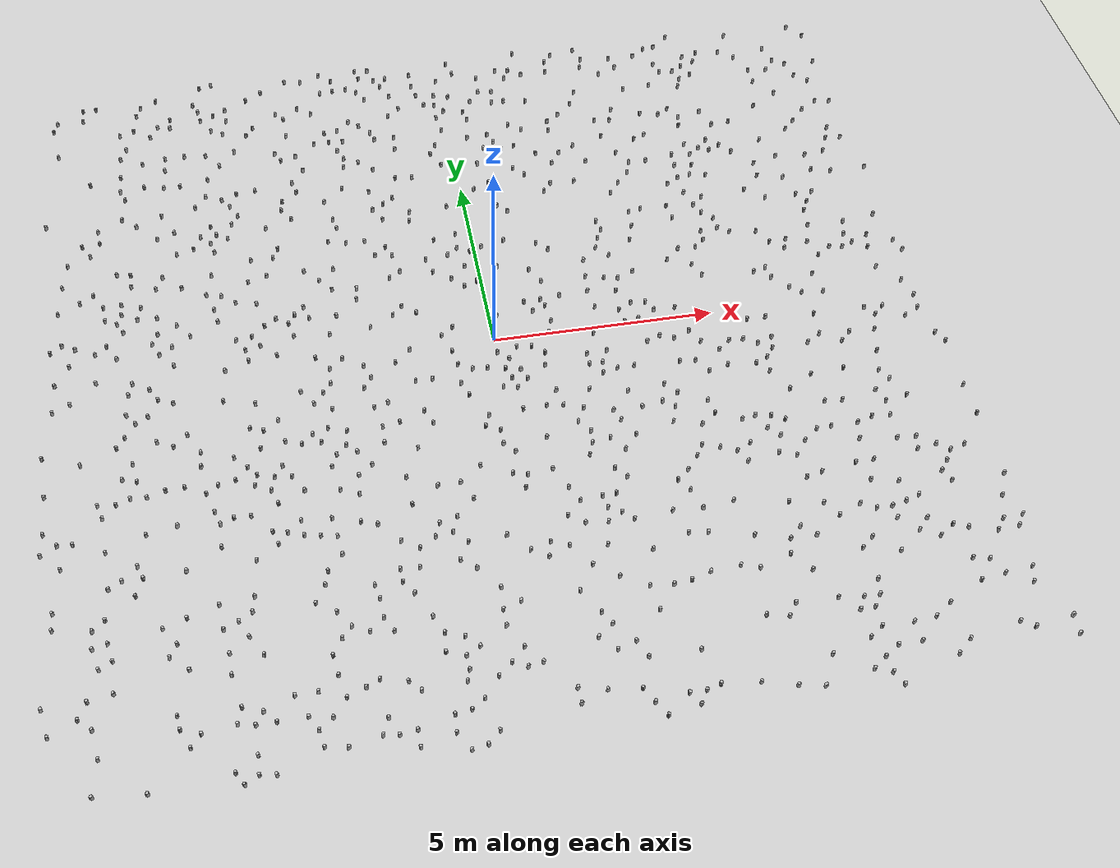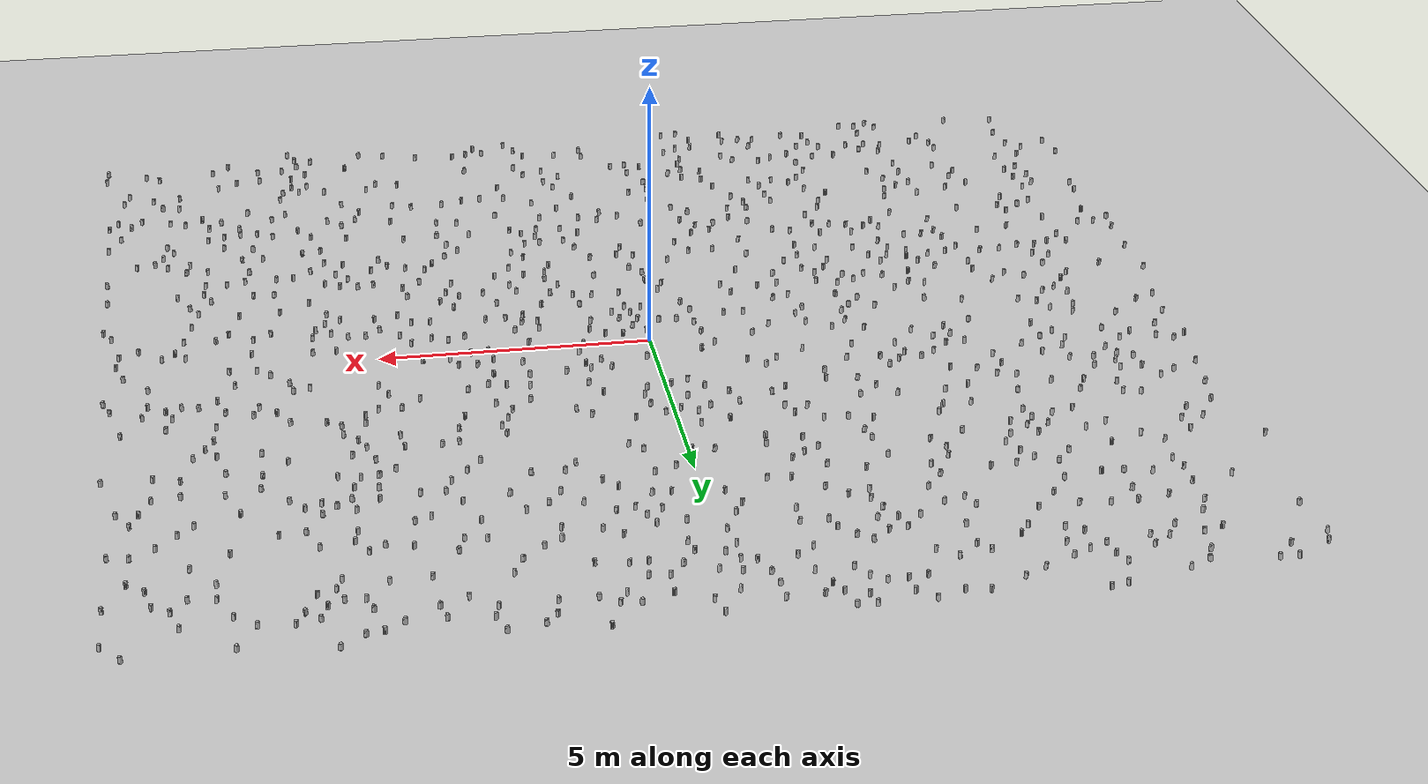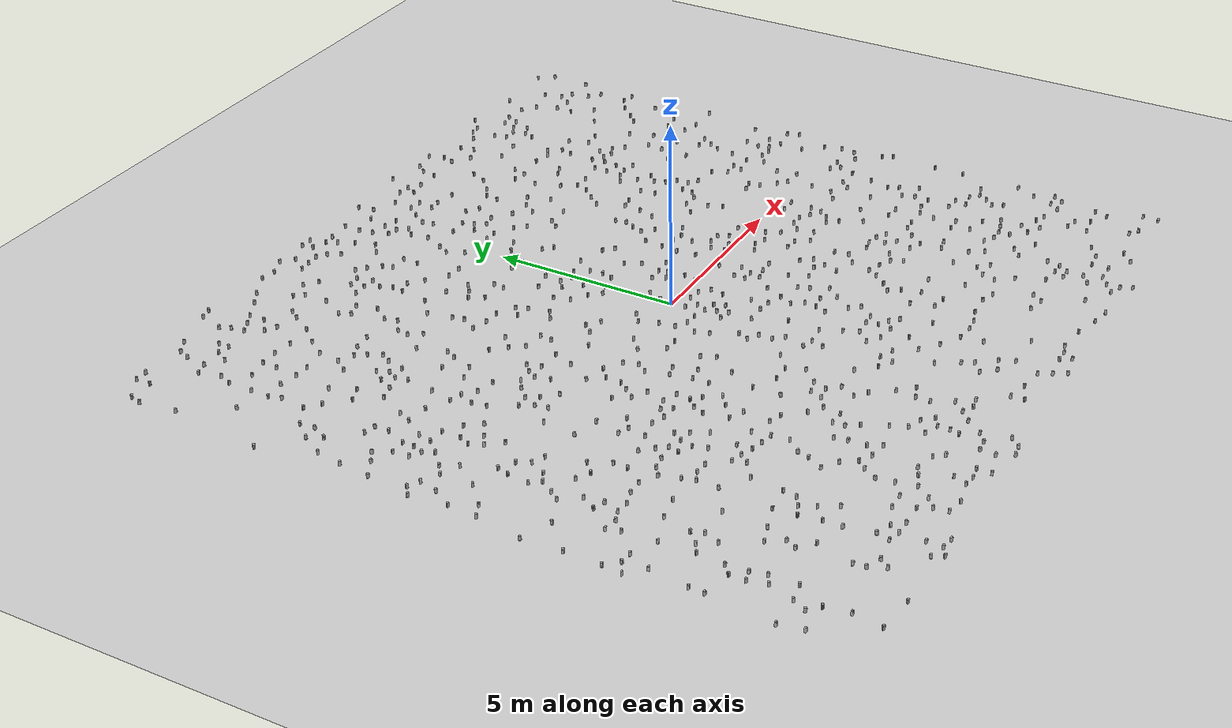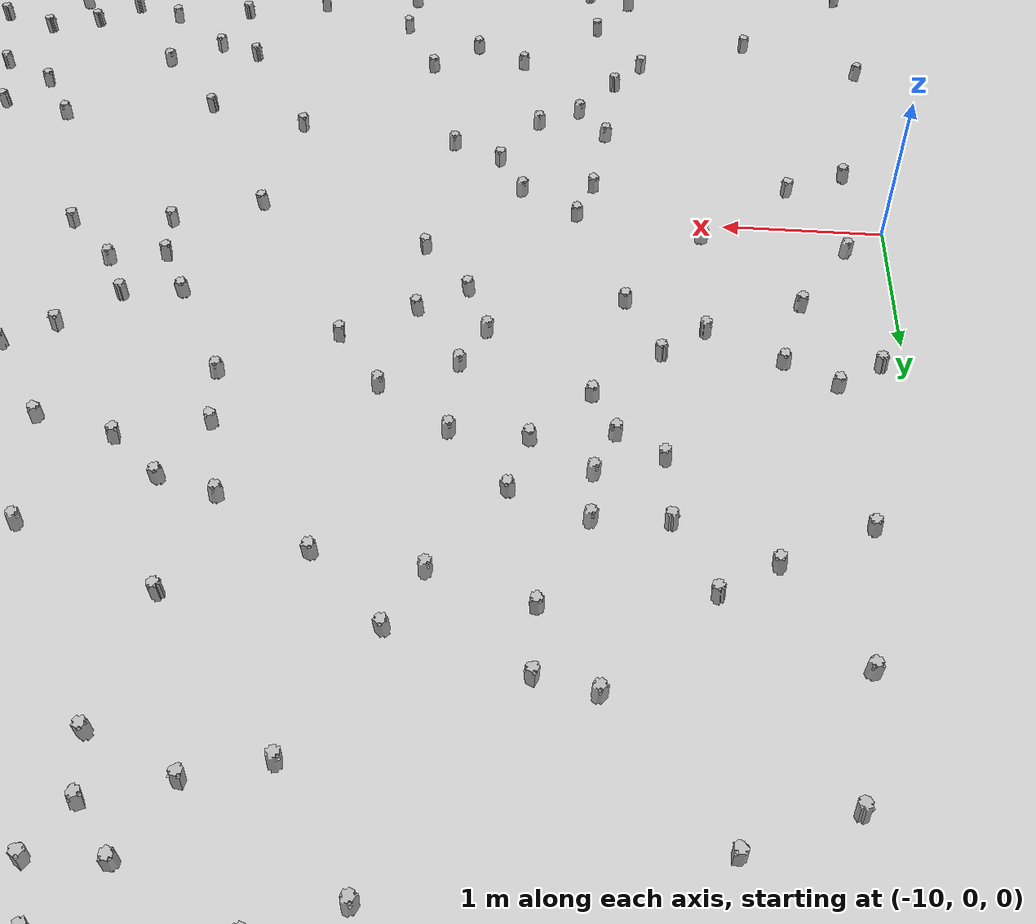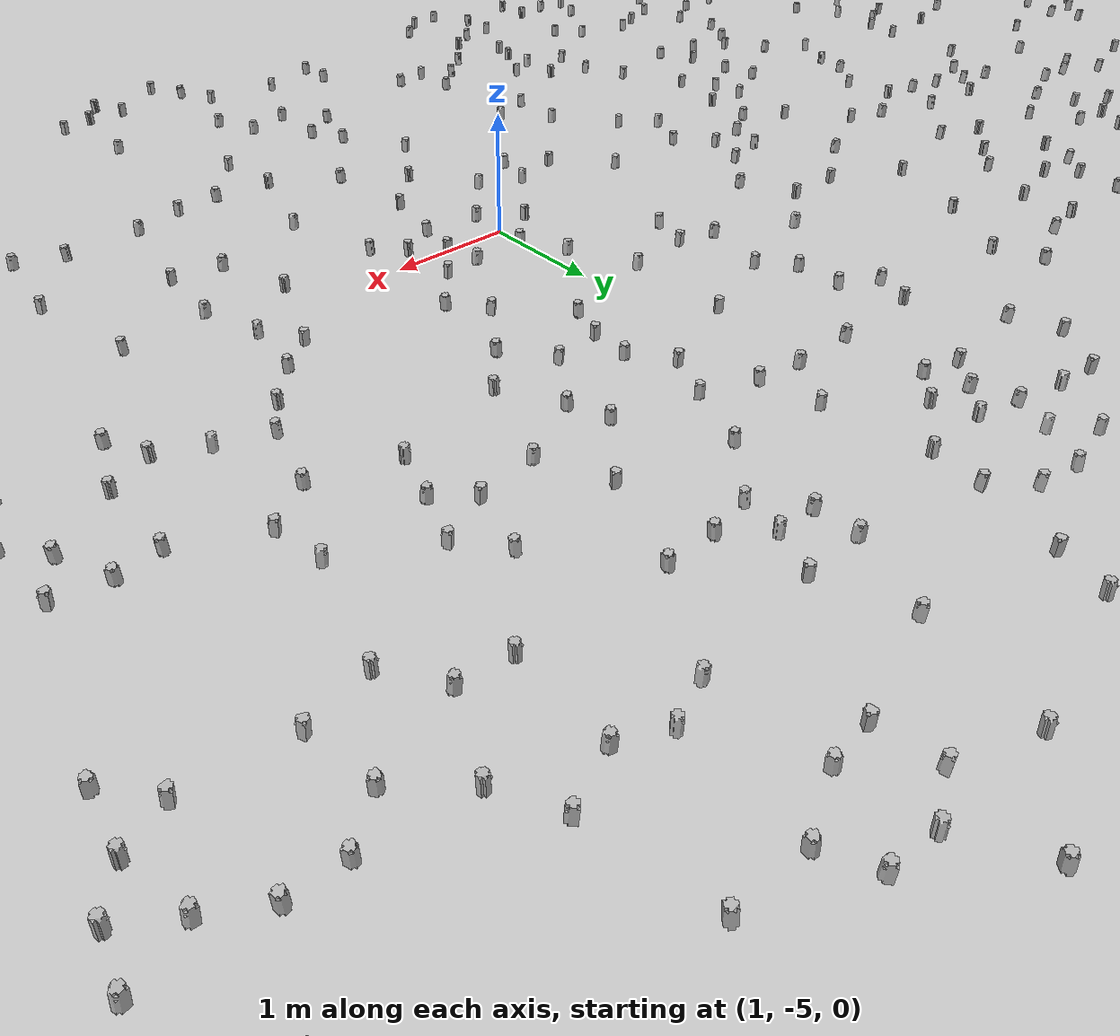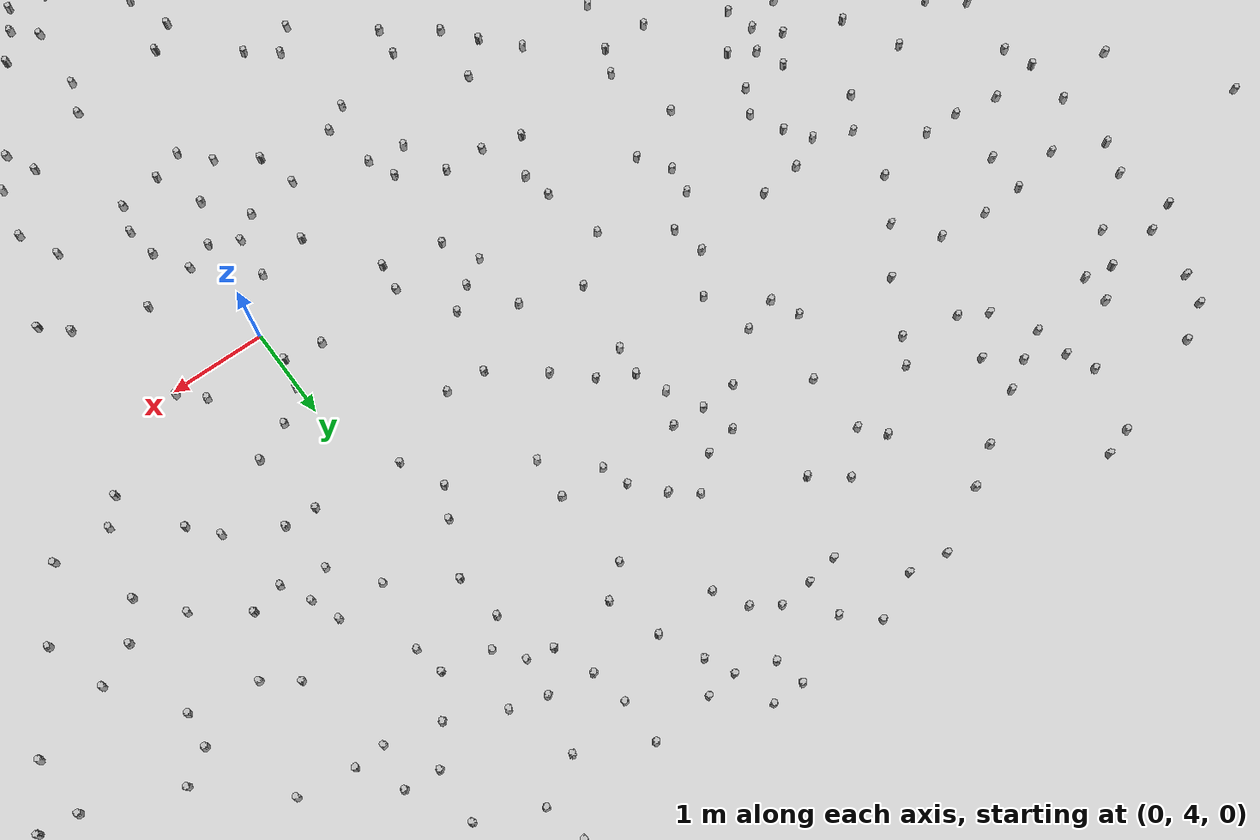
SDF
<sdf version="1.6">
 <world name="default">
  <plugin name="gazebo_ros_state" filename="libgazebo_ros_state.so">
   <ros><namespace>/ros_state</namespace><remapping>model_states:=get_model_states</remapping></ros>
  </plugin>
  <scene>
   <sky><clouds><speed>12</speed></clouds></sky>
   <ambient>0.4 0.4 0.4 1</ambient>
   <background>0.7 0.7 0.7 1</background>
   <shadows>1</shadows>
  </scene>
  <light name="sun" type="directional">
   <pose>0 0 10 0 -0 0</pose>
   <diffuse>0.8 0.8 0.8 1</diffuse>
   <specular>0.2 0.2 0.2 1</specular>
   <attenuation>
    <range>1000</range>
    <constant>0.9</constant>
    <linear>0.01</linear>
    <quadratic>0.001</quadratic>
   </attenuation>
   <direction>-0.5 0.1 -0.9</direction>
  </light>
  <gravity>0 0 -9.8</gravity>
  <magnetic_field>6e-06 2.3e-05 -4.2e-05</magnetic_field>
  <atmosphere type="adiabatic"/>
  <physics name="default_physics" default="0" type="ode">
   <max_step_size>0.001</max_step_size>
   <real_time_factor>1</real_time_factor>
   <real_time_update_rate>1000</real_time_update_rate>
  </physics>
  <audio><device>default</device></audio>
  <spherical_coordinates>
   <surface_model>EARTH_WGS84</surface_model>
   <latitude_deg>0</latitude_deg>
   <longitude_deg>0</longitude_deg>
   <elevation>0</elevation>
   <heading_deg>0</heading_deg>
  </spherical_coordinates>
  <model name="widmanstatten_plane">
   <static>1</static>
   <link name="link">
    <collision name="collision">
     <geometry><plane><normal>0 0 1</normal><size>200 200</size></plane></geometry>
     <surface><friction><ode><mu>100</mu><mu2>50</mu2></ode></friction></surface>
    </collision>
    <visual name="visual">
     <cast_shadows>0</cast_shadows>
     <geometry><plane><normal>0 0 1</normal><size>200 200</size></plane></geometry>
     <material>
      <script>
       <uri>model://widmanstatten_plane/materials/scripts/widmanstatten.material</uri>
       <uri>model://widmanstatten_plane/materials/textures/widmanstatten.jpg</uri>
       <name>widmanstatten/Diffuse</name>
      </script>
     </material>
    </visual>
   </link>
  </model>
  <model name="coke_can0">
   <link name="link">
    <inertial>
     <pose>0 0 0.06 0 -0 0</pose>
     <mass>0.39</mass>
     <inertia>
      <ixx>0.00055575</ixx>
      <ixy>0</ixy>
      <ixz>0</ixz>
      <iyy>0.00055575</iyy>
      <iyz>0</iyz>
      <izz>0.0001755</izz>
     </inertia>
    </inertial>
    <collision name="collision">
     <pose>0.003937 0.004724 -0.18 0 -0 0</pose>
     <geometry><mesh><uri>model://coke_can/meshes/coke_can.dae</uri></mesh></geometry>
     <surface>
      <friction><ode><mu>1</mu><mu2>1</mu2></ode></friction>
      <contact>
       <ode><kp>1e+07</kp><kd>1</kd><min_depth>0.001</min_depth><max_vel>0.1</max_vel></ode>
       <collide_bitmask>256</collide_bitmask>
      </contact>
     </surface>
    </collision>
    <visual name="visual">
     <pose>0.003937 0.004724 -0.18 0 -0 0</pose>
     <geometry><mesh><uri>model://coke_can/meshes/coke_can.dae</uri></mesh></geometry>
    </visual>
   </link>
   <pose>3.78187 6.35863 -0.002659 -0.055136 0.007726 -2.95147</pose>
  </model>
  <model name="coke_can1">
   <link name="link">
    <inertial>
     <pose>0 0 0.06 0 -0 0</pose>
     <mass>0.39</mass>
     <inertia>
      <ixx>0.00055575</ixx>
      <ixy>0</ixy>
      <ixz>0</ixz>
      <iyy>0.00055575</iyy>
      <iyz>0</iyz>
      <izz>0.0001755</izz>
     </inertia>
    </inertial>
    <collision name="collision">
     <pose>0.003937 0.004724 -0.18 0 -0 0</pose>
     <geometry><mesh><uri>model://coke_can/meshes/coke_can.dae</uri></mesh></geometry>
     <surface>
      <friction><ode><mu>1</mu><mu2>1</mu2></ode></friction>
      <contact>
       <ode><kp>1e+07</kp><kd>1</kd><min_depth>0.001</min_depth><max_vel>0.1</max_vel></ode>
       <collide_bitmask>256</collide_bitmask>
      </contact>
     </surface>
    </collision>
    <visual name="visual">
     <pose>0.003937 0.004724 -0.18 0 -0 0</pose>
     <geometry><mesh><uri>model://coke_can/meshes/coke_can.dae</uri></mesh></geometry>
    </visual>
   </link>
   <pose>7.30902 -3.68398 -0.002659 -0.055109 0.007744 -1.6551</pose>
  </model>
  <model name="coke_can2">
   <link name="link">
    <inertial>
     <pose>0 0 0.06 0 -0 0</pose>
     <mass>0.39</mass>
     <inertia>
      <ixx>0.00055575</ixx>
      <ixy>0</ixy>
      <ixz>0</ixz>
      <iyy>0.00055575</iyy>
      <iyz>0</iyz>
      <izz>0.0001755</izz>
     </inertia>
    </inertial>
    <collision name="collision">
     <pose>0.003937 0.004724 -0.18 0 -0 0</pose>
     <geometry><mesh><uri>model://coke_can/meshes/coke_can.dae</uri></mesh></geometry>
     <surface>
      <friction><ode><mu>1</mu><mu2>1</mu2></ode></friction>
      <contact>
       <ode><kp>1e+07</kp><kd>1</kd><min_depth>0.001</min_depth><max_vel>0.1</max_vel></ode>
       <collide_bitmask>256</collide_bitmask>
      </contact>
     </surface>
    </collision>
    <visual name="visual">
     <pose>0.003937 0.004724 -0.18 0 -0 0</pose>
     <geometry><mesh><uri>model://coke_can/meshes/coke_can.dae</uri></mesh></geometry>
    </visual>
   </link>
   <pose>-7.36928 -8.67043 -0.002659 -0.055094 0.007754 0.986474</pose>
  </model>
  <model name="coke_can3">
   <link name="link">
    <inertial>
     <pose>0 0 0.06 0 -0 0</pose>
     <mass>0.39</mass>
     <inertia>
      <ixx>0.00055575</ixx>
      <ixy>0</ixy>
      <ixz>0</ixz>
      <iyy>0.00055575</iyy>
      <iyz>0</iyz>
      <izz>0.0001755</izz>
     </inertia>
    </inertial>
    <collision name="collision">
     <pose>0.003937 0.004724 -0.18 0 -0 0</pose>
     <geometry><mesh><uri>model://coke_can/meshes/coke_can.dae</uri></mesh></geometry>
     <surface>
      <friction><ode><mu>1</mu><mu2>1</mu2></ode></friction>
      <contact>
       <ode><kp>1e+07</kp><kd>1</kd><min_depth>0.001</min_depth><max_vel>0.1</max_vel></ode>
       <collide_bitmask>256</collide_bitmask>
      </contact>
     </surface>
    </collision>
    <visual name="visual">
     <pose>0.003937 0.004724 -0.18 0 -0 0</pose>
     <geometry><mesh><uri>model://coke_can/meshes/coke_can.dae</uri></mesh></geometry>
    </visual>
   </link>
   <pose>-5.81578 -8.54263 -0.002659 -0.055116 0.007739 -1.00788</pose>
  </model>
  <model name="coke_can4">
   <link name="link">
    <inertial>
     <pose>0 0 0.06 0 -0 0</pose>
     <mass>0.39</mass>
     <inertia>
      <ixx>0.00055575</ixx>
      <ixy>0</ixy>
      <ixz>0</ixz>
      <iyy>0.00055575</iyy>
      <iyz>0</iyz>
      <izz>0.0001755</izz>
     </inertia>
    </inertial>
    <collision name="collision">
     <pose>0.003937 0.004724 -0.18 0 -0 0</pose>
     <geometry><mesh><uri>model://coke_can/meshes/coke_can.dae</uri></mesh></geometry>
     <surface>
      <friction><ode><mu>1</mu><mu2>1</mu2></ode></friction>
      <contact>
       <ode><kp>1e+07</kp><kd>1</kd><min_depth>0.001</min_depth><max_vel>0.1</max_vel></ode>
       <collide_bitmask>256</collide_bitmask>
      </contact>
     </surface>
    </collision>
    <visual name="visual">
     <pose>0.003937 0.004724 -0.18 0 -0 0</pose>
     <geometry><mesh><uri>model://coke_can/meshes/coke_can.dae</uri></mesh></geometry>
    </visual>
   </link>
   <pose>6.78372 -2.98788 -0.002659 -0.055085 0.007761 2.55546</pose>
  </model>
  <model name="coke_can5">
   <link name="link">
    <inertial>
     <pose>0 0 0.06 0 -0 0</pose>
     <mass>0.39</mass>
     <inertia>
      <ixx>0.00055575</ixx>
      <ixy>0</ixy>
      <ixz>0</ixz>
      <iyy>0.00055575</iyy>
      <iyz>0</iyz>
      <izz>0.0001755</izz>
     </inertia>
    </inertial>
    <collision name="collision">
     <pose>0.003937 0.004724 -0.18 0 -0 0</pose>
     <geometry><mesh><uri>model://coke_can/meshes/coke_can.dae</uri></mesh></geometry>
     <surface>
      <friction><ode><mu>1</mu><mu2>1</mu2></ode></friction>
      <contact>
       <ode><kp>1e+07</kp><kd>1</kd><min_depth>0.001</min_depth><max_vel>0.1</max_vel></ode>
       <collide_bitmask>256</collide_bitmask>
      </contact>
     </surface>
    </collision>
    <visual name="visual">
     <pose>0.003937 0.004724 -0.18 0 -0 0</pose>
     <geometry><mesh><uri>model://coke_can/meshes/coke_can.dae</uri></mesh></geometry>
    </visual>
   </link>
   <pose>2.20469 9.09689 -0.002659 -0.055132 0.007727 -1.26812</pose>
  </model>
  <model name="coke_can6">
   <link name="link">
    <inertial>
     <pose>0 0 0.06 0 -0 0</pose>
     <mass>0.39</mass>
     <inertia>
      <ixx>0.00055575</ixx>
      <ixy>0</ixy>
      <ixz>0</ixz>
      <iyy>0.00055575</iyy>
      <iyz>0</iyz>
      <izz>0.0001755</izz>
     </inertia>
    </inertial>
    <collision name="collision">
     <pose>0.003937 0.004724 -0.18 0 -0 0</pose>
     <geometry><mesh><uri>model://coke_can/meshes/coke_can.dae</uri></mesh></geometry>
     <surface>
      <friction><ode><mu>1</mu><mu2>1</mu2></ode></friction>
      <contact>
       <ode><kp>1e+07</kp><kd>1</kd><min_depth>0.001</min_depth><max_vel>0.1</max_vel></ode>
       <collide_bitmask>256</collide_bitmask>
      </contact>
     </surface>
    </collision>
    <visual name="visual">
     <pose>0.003937 0.004724 -0.18 0 -0 0</pose>
     <geometry><mesh><uri>model://coke_can/meshes/coke_can.dae</uri></mesh></geometry>
    </visual>
   </link>
   <pose>3.67997 -3.9916 -0.002659 -0.055133 0.007726 -2.68583</pose>
  </model>
  <model name="coke_can7">
   <link name="link">
    <inertial>
     <pose>0 0 0.06 0 -0 0</pose>
     <mass>0.39</mass>
     <inertia>
      <ixx>0.00055575</ixx>
      <ixy>0</ixy>
      <ixz>0</ixz>
      <iyy>0.00055575</iyy>
      <iyz>0</iyz>
      <izz>0.0001755</izz>
     </inertia>
    </inertial>
    <collision name="collision">
     <pose>0.003937 0.004724 -0.18 0 -0 0</pose>
     <geometry><mesh><uri>model://coke_can/meshes/coke_can.dae</uri></mesh></geometry>
     <surface>
      <friction><ode><mu>1</mu><mu2>1</mu2></ode></friction>
      <contact>
       <ode><kp>1e+07</kp><kd>1</kd><min_depth>0.001</min_depth><max_vel>0.1</max_vel></ode>
       <collide_bitmask>256</collide_bitmask>
      </contact>
     </surface>
    </collision>
    <visual name="visual">
     <pose>0.003937 0.004724 -0.18 0 -0 0</pose>
     <geometry><mesh><uri>model://coke_can/meshes/coke_can.dae</uri></mesh></geometry>
    </visual>
   </link>
   <pose>-7.10668 7.29835 -0.002659 -0.055139 0.007723 -2.76492</pose>
  </model>
  <model name="coke_can8">
   <link name="link">
    <inertial>
     <pose>0 0 0.06 0 -0 0</pose>
     <mass>0.39</mass>
     <inertia>
      <ixx>0.00055575</ixx>
      <ixy>0</ixy>
      <ixz>0</ixz>
      <iyy>0.00055575</iyy>
      <iyz>0</iyz>
      <izz>0.0001755</izz>
     </inertia>
    </inertial>
    <collision name="collision">
     <pose>0.003937 0.004724 -0.18 0 -0 0</pose>
     <geometry><mesh><uri>model://coke_can/meshes/coke_can.dae</uri></mesh></geometry>
     <surface>
      <friction><ode><mu>1</mu><mu2>1</mu2></ode></friction>
      <contact>
       <ode><kp>1e+07</kp><kd>1</kd><min_depth>0.001</min_depth><max_vel>0.1</max_vel></ode>
       <collide_bitmask>256</collide_bitmask>
      </contact>
     </surface>
    </collision>
    <visual name="visual">
     <pose>0.003937 0.004724 -0.18 0 -0 0</pose>
     <geometry><mesh><uri>model://coke_can/meshes/coke_can.dae</uri></mesh></geometry>
    </visual>
   </link>
   <pose>-2.04236 6.06746 -0.002659 -0.055115 0.00774 2.13874</pose>
  </model>
  <model name="coke_can9">
   <link name="link">
    <inertial>
     <pose>0 0 0.06 0 -0 0</pose>
     <mass>0.39</mass>
     <inertia>
      <ixx>0.00055575</ixx>
      <ixy>0</ixy>
      <ixz>0</ixz>
      <iyy>0.00055575</iyy>
      <iyz>0</iyz>
      <izz>0.0001755</izz>
     </inertia>
    </inertial>
    <collision name="collision">
     <pose>0.003937 0.004724 -0.18 0 -0 0</pose>
     <geometry><mesh><uri>model://coke_can/meshes/coke_can.dae</uri></mesh></geometry>
     <surface>
      <friction><ode><mu>1</mu><mu2>1</mu2></ode></friction>
      <contact>
       <ode><kp>1e+07</kp><kd>1</kd><min_depth>0.001</min_depth><max_vel>0.1</max_vel></ode>
       <collide_bitmask>256</collide_bitmask>
      </contact>
     </surface>
    </collision>
    <visual name="visual">
     <pose>0.003937 0.004724 -0.18 0 -0 0</pose>
     <geometry><mesh><uri>model://coke_can/meshes/coke_can.dae</uri></mesh></geometry>
    </visual>
   </link>
   <pose>-2.7516 9.63914 -0.002659 -0.055105 0.007747 -2.36767</pose>
  </model>
  <model name="coke_can10">
   <link name="link">
    <inertial>
     <pose>0 0 0.06 0 -0 0</pose>
     <mass>0.39</mass>
     <inertia>
      <ixx>0.00055575</ixx>
      <ixy>0</ixy>
      <ixz>0</ixz>
      <iyy>0.00055575</iyy>
      <iyz>0</iyz>
      <izz>0.0001755</izz>
     </inertia>
    </inertial>
    <collision name="collision">
     <pose>0.003937 0.004724 -0.18 0 -0 0</pose>
     <geometry><mesh><uri>model://coke_can/meshes/coke_can.dae</uri></mesh></geometry>
     <surface>
      <friction><ode><mu>1</mu><mu2>1</mu2></ode></friction>
      <contact>
       <ode><kp>1e+07</kp><kd>1</kd><min_depth>0.001</min_depth><max_vel>0.1</max_vel></ode>
       <collide_bitmask>256</collide_bitmask>
      </contact>
     </surface>
    </collision>
    <visual name="visual">
     <pose>0.003937 0.004724 -0.18 0 -0 0</pose>
     <geometry><mesh><uri>model://coke_can/meshes/coke_can.dae</uri></mesh></geometry>
    </visual>
   </link>
   <pose>2.35601 1.11859 -0.002659 -0.05513 0.007729 -1.19019</pose>
  </model>
  <model name="coke_can11">
   <link name="link">
    <inertial>
     <pose>0 0 0.06 0 -0 0</pose>
     <mass>0.39</mass>
     <inertia>
      <ixx>0.00055575</ixx>
      <ixy>0</ixy>
      <ixz>0</ixz>
      <iyy>0.00055575</iyy>
      <iyz>0</iyz>
      <izz>0.0001755</izz>
     </inertia>
    </inertial>
    <collision name="collision">
     <pose>0.003937 0.004724 -0.18 0 -0 0</pose>
     <geometry><mesh><uri>model://coke_can/meshes/coke_can.dae</uri></mesh></geometry>
     <surface>
      <friction><ode><mu>1</mu><mu2>1</mu2></ode></friction>
      <contact>
       <ode><kp>1e+07</kp><kd>1</kd><min_depth>0.001</min_depth><max_vel>0.1</max_vel></ode>
       <collide_bitmask>256</collide_bitmask>
      </contact>
     </surface>
    </collision>
    <visual name="visual">
     <pose>0.003937 0.004724 -0.18 0 -0 0</pose>
     <geometry><mesh><uri>model://coke_can/meshes/coke_can.dae</uri></mesh></geometry>
    </visual>
   </link>
   <pose>7.9741 -2.86542 -0.002659 -0.055111 0.007742 -0.970371</pose>
  </model>
  <model name="coke_can12">
   <link name="link">
    <inertial>
     <pose>0 0 0.06 0 -0 0</pose>
     <mass>0.39</mass>
     <inertia>
      <ixx>0.00055575</ixx>
      <ixy>0</ixy>
      <ixz>0</ixz>
      <iyy>0.00055575</iyy>
      <iyz>0</iyz>
      <izz>0.0001755</izz>
     </inertia>
    </inertial>
    <collision name="collision">
     <pose>0.003937 0.004724 -0.18 0 -0 0</pose>
     <geometry><mesh><uri>model://coke_can/meshes/coke_can.dae</uri></mesh></geometry>
     <surface>
      <friction><ode><mu>1</mu><mu2>1</mu2></ode></friction>
      <contact>
       <ode><kp>1e+07</kp><kd>1</kd><min_depth>0.001</min_depth><max_vel>0.1</max_vel></ode>
       <collide_bitmask>256</collide_bitmask>
      </contact>
     </surface>
    </collision>
    <visual name="visual">
     <pose>0.003937 0.004724 -0.18 0 -0 0</pose>
     <geometry><mesh><uri>model://coke_can/meshes/coke_can.dae</uri></mesh></geometry>
    </visual>
   </link>
   <pose>0.08723 -9.02848 -0.002659 -0.055131 0.007728 -1.39394</pose>
  </model>
  <model name="coke_can13">
   <link name="link">
    <inertial>
     <pose>0 0 0.06 0 -0 0</pose>
     <mass>0.39</mass>
     <inertia>
      <ixx>0.00055575</ixx>
      <ixy>0</ixy>
      <ixz>0</ixz>
      <iyy>0.00055575</iyy>
      <iyz>0</iyz>
      <izz>0.0001755</izz>
     </inertia>
    </inertial>
    <collision name="collision">
     <pose>0.003937 0.004724 -0.18 0 -0 0</pose>
     <geometry><mesh><uri>model://coke_can/meshes/coke_can.dae</uri></mesh></geometry>
     <surface>
      <friction><ode><mu>1</mu><mu2>1</mu2></ode></friction>
      <contact>
       <ode><kp>1e+07</kp><kd>1</kd><min_depth>0.001</min_depth><max_vel>0.1</max_vel></ode>
       <collide_bitmask>256</collide_bitmask>
      </contact>
     </surface>
    </collision>
    <visual name="visual">
     <pose>0.003937 0.004724 -0.18 0 -0 0</pose>
     <geometry><mesh><uri>model://coke_can/meshes/coke_can.dae</uri></mesh></geometry>
    </visual>
   </link>
   <pose>8.8745 1.64946 -0.002659 -0.055091 0.007754 -2.09339</pose>
  </model>
  <model name="coke_can14">
   <link name="link">
    <inertial>
     <pose>0 0 0.06 0 -0 0</pose>
     <mass>0.39</mass>
     <inertia>
      <ixx>0.00055575</ixx>
      <ixy>0</ixy>
      <ixz>0</ixz>
      <iyy>0.00055575</iyy>
      <iyz>0</iyz>
      <izz>0.0001755</izz>
     </inertia>
    </inertial>
    <collision name="collision">
     <pose>0.003937 0.004724 -0.18 0 -0 0</pose>
     <geometry><mesh><uri>model://coke_can/meshes/coke_can.dae</uri></mesh></geometry>
     <surface>
      <friction><ode><mu>1</mu><mu2>1</mu2></ode></friction>
      <contact>
       <ode><kp>1e+07</kp><kd>1</kd><min_depth>0.001</min_depth><max_vel>0.1</max_vel></ode>
       <collide_bitmask>256</collide_bitmask>
      </contact>
     </surface>
    </collision>
    <visual name="visual">
     <pose>0.003937 0.004724 -0.18 0 -0 0</pose>
     <geometry><mesh><uri>model://coke_can/meshes/coke_can.dae</uri></mesh></geometry>
    </visual>
   </link>
   <pose>4.69909 -7.88723 -0.002659 -0.055113 0.007741 1.54751</pose>
  </model>
  <model name="coke_can15">
   <link name="link">
    <inertial>
     <pose>0 0 0.06 0 -0 0</pose>
     <mass>0.39</mass>
     <inertia>
      <ixx>0.00055575</ixx>
      <ixy>0</ixy>
      <ixz>0</ixz>
      <iyy>0.00055575</iyy>
      <iyz>0</iyz>
      <izz>0.0001755</izz>
     </inertia>
    </inertial>
    <collision name="collision">
     <pose>0.003937 0.004724 -0.18 0 -0 0</pose>
     <geometry><mesh><uri>model://coke_can/meshes/coke_can.dae</uri></mesh></geometry>
     <surface>
      <friction><ode><mu>1</mu><mu2>1</mu2></ode></friction>
      <contact>
       <ode><kp>1e+07</kp><kd>1</kd><min_depth>0.001</min_depth><max_vel>0.1</max_vel></ode>
       <collide_bitmask>256</collide_bitmask>
      </contact>
     </surface>
    </collision>
    <visual name="visual">
     <pose>0.003937 0.004724 -0.18 0 -0 0</pose>
     <geometry><mesh><uri>model://coke_can/meshes/coke_can.dae</uri></mesh></geometry>
    </visual>
   </link>
   <pose>-3.6606 -9.40567 -0.002659 -0.055115 0.00774 0.015126</pose>
  </model>
  <model name="coke_can16">
   <link name="link">
    <inertial>
     <pose>0 0 0.06 0 -0 0</pose>
     <mass>0.39</mass>
     <inertia>
      <ixx>0.00055575</ixx>
      <ixy>0</ixy>
      <ixz>0</ixz>
      <iyy>0.00055575</iyy>
      <iyz>0</iyz>
      <izz>0.0001755</izz>
     </inertia>
    </inertial>
    <collision name="collision">
     <pose>0.003937 0.004724 -0.18 0 -0 0</pose>
     <geometry><mesh><uri>model://coke_can/meshes/coke_can.dae</uri></mesh></geometry>
     <surface>
      <friction><ode><mu>1</mu><mu2>1</mu2></ode></friction>
      <contact>
       <ode><kp>1e+07</kp><kd>1</kd><min_depth>0.001</min_depth><max_vel>0.1</max_vel></ode>
       <collide_bitmask>256</collide_bitmask>
      </contact>
     </surface>
    </collision>
    <visual name="visual">
     <pose>0.003937 0.004724 -0.18 0 -0 0</pose>
     <geometry><mesh><uri>model://coke_can/meshes/coke_can.dae</uri></mesh></geometry>
    </visual>
   </link>
   <pose>2.42456 0.594703 -0.002659 -0.055083 0.00776 2.64105</pose>
  </model>
  <model name="coke_can17">
   <link name="link">
    <inertial>
     <pose>0 0 0.06 0 -0 0</pose>
     <mass>0.39</mass>
     <inertia>
      <ixx>0.00055575</ixx>
      <ixy>0</ixy>
      <ixz>0</ixz>
      <iyy>0.00055575</iyy>
      <iyz>0</iyz>
      <izz>0.0001755</izz>
     </inertia>
    </inertial>
    <collision name="collision">
     <pose>0.003937 0.004724 -0.18 0 -0 0</pose>
     <geometry><mesh><uri>model://coke_can/meshes/coke_can.dae</uri></mesh></geometry>
     <surface>
      <friction><ode><mu>1</mu><mu2>1</mu2></ode></friction>
      <contact>
       <ode><kp>1e+07</kp><kd>1</kd><min_depth>0.001</min_depth><max_vel>0.1</max_vel></ode>
       <collide_bitmask>256</collide_bitmask>
      </contact>
     </surface>
    </collision>
    <visual name="visual">
     <pose>0.003937 0.004724 -0.18 0 -0 0</pose>
     <geometry><mesh><uri>model://coke_can/meshes/coke_can.dae</uri></mesh></geometry>
    </visual>
   </link>
   <pose>3.94628 -1.34268 -0.002659 -0.055117 0.007736 -3.09028</pose>
  </model>
  <model name="coke_can18">
   <link name="link">
    <inertial>
     <pose>0 0 0.06 0 -0 0</pose>
     <mass>0.39</mass>
     <inertia>
      <ixx>0.00055575</ixx>
      <ixy>0</ixy>
      <ixz>0</ixz>
      <iyy>0.00055575</iyy>
      <iyz>0</iyz>
      <izz>0.0001755</izz>
     </inertia>
    </inertial>
    <collision name="collision">
     <pose>0.003937 0.004724 -0.18 0 -0 0</pose>
     <geometry><mesh><uri>model://coke_can/meshes/coke_can.dae</uri></mesh></geometry>
     <surface>
      <friction><ode><mu>1</mu><mu2>1</mu2></ode></friction>
      <contact>
       <ode><kp>1e+07</kp><kd>1</kd><min_depth>0.001</min_depth><max_vel>0.1</max_vel></ode>
       <collide_bitmask>256</collide_bitmask>
      </contact>
     </surface>
    </collision>
    <visual name="visual">
     <pose>0.003937 0.004724 -0.18 0 -0 0</pose>
     <geometry><mesh><uri>model://coke_can/meshes/coke_can.dae</uri></mesh></geometry>
    </visual>
   </link>
   <pose>8.8713 8.5732 -0.002659 -0.055097 0.007752 -1.86784</pose>
  </model>
  <model name="coke_can19">
   <link name="link">
    <inertial>
     <pose>0 0 0.06 0 -0 0</pose>
     <mass>0.39</mass>
     <inertia>
      <ixx>0.00055575</ixx>
      <ixy>0</ixy>
      <ixz>0</ixz>
      <iyy>0.00055575</iyy>
      <iyz>0</iyz>
      <izz>0.0001755</izz>
     </inertia>
    </inertial>
    <collision name="collision">
     <pose>0.003937 0.004724 -0.18 0 -0 0</pose>
     <geometry><mesh><uri>model://coke_can/meshes/coke_can.dae</uri></mesh></geometry>
     <surface>
      <friction><ode><mu>1</mu><mu2>1</mu2></ode></friction>
      <contact>
       <ode><kp>1e+07</kp><kd>1</kd><min_depth>0.001</min_depth><max_vel>0.1</max_vel></ode>
       <collide_bitmask>256</collide_bitmask>
      </contact>
     </surface>
    </collision>
    <visual name="visual">
     <pose>0.003937 0.004724 -0.18 0 -0 0</pose>
     <geometry><mesh><uri>model://coke_can/meshes/coke_can.dae</uri></mesh></geometry>
    </visual>
   </link>
   <pose>-1.87711 7.16988 -0.002659 -0.05509 0.007756 -0.711296</pose>
  </model>
  <model name="coke_can20">
   <link name="link">
    <inertial>
     <pose>0 0 0.06 0 -0 0</pose>
     <mass>0.39</mass>
     <inertia>
      <ixx>0.00055575</ixx>
      <ixy>0</ixy>
      <ixz>0</ixz>
      <iyy>0.00055575</iyy>
      <iyz>0</iyz>
      <izz>0.0001755</izz>
     </inertia>
    </inertial>
    <collision name="collision">
     <pose>0.003937 0.004724 -0.18 0 -0 0</pose>
     <geometry><mesh><uri>model://coke_can/meshes/coke_can.dae</uri></mesh></geometry>
     <surface>
      <friction><ode><mu>1</mu><mu2>1</mu2></ode></friction>
      <contact>
       <ode><kp>1e+07</kp><kd>1</kd><min_depth>0.001</min_depth><max_vel>0.1</max_vel></ode>
       <collide_bitmask>256</collide_bitmask>
      </contact>
     </surface>
    </collision>
    <visual name="visual">
     <pose>0.003937 0.004724 -0.18 0 -0 0</pose>
     <geometry><mesh><uri>model://coke_can/meshes/coke_can.dae</uri></mesh></geometry>
    </visual>
   </link>
   <pose>-7.91158 1.9156 -0.002658 -0.055084 0.007762 -0.558571</pose>
  </model>
  <model name="coke_can21">
   <link name="link">
    <inertial>
     <pose>0 0 0.06 0 -0 0</pose>
     <mass>0.39</mass>
     <inertia>
      <ixx>0.00055575</ixx>
      <ixy>0</ixy>
      <ixz>0</ixz>
      <iyy>0.00055575</iyy>
      <iyz>0</iyz>
      <izz>0.0001755</izz>
     </inertia>
    </inertial>
    <collision name="collision">
     <pose>0.003937 0.004724 -0.18 0 -0 0</pose>
     <geometry><mesh><uri>model://coke_can/meshes/coke_can.dae</uri></mesh></geometry>
     <surface>
      <friction><ode><mu>1</mu><mu2>1</mu2></ode></friction>
      <contact>
       <ode><kp>1e+07</kp><kd>1</kd><min_depth>0.001</min_depth><max_vel>0.1</max_vel></ode>
       <collide_bitmask>256</collide_bitmask>
      </contact>
     </surface>
    </collision>
    <visual name="visual">
     <pose>0.003937 0.004724 -0.18 0 -0 0</pose>
     <geometry><mesh><uri>model://coke_can/meshes/coke_can.dae</uri></mesh></geometry>
    </visual>
   </link>
   <pose>-6.36409 -4.10215 -0.002659 -0.055138 0.007723 0.257651</pose>
  </model>
  <model name="coke_can22">
   <link name="link">
    <inertial>
     <pose>0 0 0.06 0 -0 0</pose>
     <mass>0.39</mass>
     <inertia>
      <ixx>0.00055575</ixx>
      <ixy>0</ixy>
      <ixz>0</ixz>
      <iyy>0.00055575</iyy>
      <iyz>0</iyz>
      <izz>0.0001755</izz>
     </inertia>
    </inertial>
    <collision name="collision">
     <pose>0.003937 0.004724 -0.18 0 -0 0</pose>
     <geometry><mesh><uri>model://coke_can/meshes/coke_can.dae</uri></mesh></geometry>
     <surface>
      <friction><ode><mu>1</mu><mu2>1</mu2></ode></friction>
      <contact>
       <ode><kp>1e+07</kp><kd>1</kd><min_depth>0.001</min_depth><max_vel>0.1</max_vel></ode>
       <collide_bitmask>256</collide_bitmask>
      </contact>
     </surface>
    </collision>
    <visual name="visual">
     <pose>0.003937 0.004724 -0.18 0 -0 0</pose>
     <geometry><mesh><uri>model://coke_can/meshes/coke_can.dae</uri></mesh></geometry>
    </visual>
   </link>
   <pose>-6.1102 1.5619 -0.002659 -0.055082 0.007759 2.53587</pose>
  </model>
  <model name="coke_can23">
   <link name="link">
    <inertial>
     <pose>0 0 0.06 0 -0 0</pose>
     <mass>0.39</mass>
     <inertia>
      <ixx>0.00055575</ixx>
      <ixy>0</ixy>
      <ixz>0</ixz>
      <iyy>0.00055575</iyy>
      <iyz>0</iyz>
      <izz>0.0001755</izz>
     </inertia>
    </inertial>
    <collision name="collision">
     <pose>0.003937 0.004724 -0.18 0 -0 0</pose>
     <geometry><mesh><uri>model://coke_can/meshes/coke_can.dae</uri></mesh></geometry>
     <surface>
      <friction><ode><mu>1</mu><mu2>1</mu2></ode></friction>
      <contact>
       <ode><kp>1e+07</kp><kd>1</kd><min_depth>0.001</min_depth><max_vel>0.1</max_vel></ode>
       <collide_bitmask>256</collide_bitmask>
      </contact>
     </surface>
    </collision>
    <visual name="visual">
     <pose>0.003937 0.004724 -0.18 0 -0 0</pose>
     <geometry><mesh><uri>model://coke_can/meshes/coke_can.dae</uri></mesh></geometry>
    </visual>
   </link>
   <pose>1.04184 -0.590808 -0.002659 -0.055133 0.007726 0.17875</pose>
  </model>
  <model name="coke_can24">
   <link name="link">
    <inertial>
     <pose>0 0 0.06 0 -0 0</pose>
     <mass>0.39</mass>
     <inertia>
      <ixx>0.00055575</ixx>
      <ixy>0</ixy>
      <ixz>0</ixz>
      <iyy>0.00055575</iyy>
      <iyz>0</iyz>
      <izz>0.0001755</izz>
     </inertia>
    </inertial>
    <collision name="collision">
     <pose>0.003937 0.004724 -0.18 0 -0 0</pose>
     <geometry><mesh><uri>model://coke_can/meshes/coke_can.dae</uri></mesh></geometry>
     <surface>
      <friction><ode><mu>1</mu><mu2>1</mu2></ode></friction>
      <contact>
       <ode><kp>1e+07</kp><kd>1</kd><min_depth>0.001</min_depth><max_vel>0.1</max_vel></ode>
       <collide_bitmask>256</collide_bitmask>
      </contact>
     </surface>
    </collision>
    <visual name="visual">
     <pose>0.003937 0.004724 -0.18 0 -0 0</pose>
     <geometry><mesh><uri>model://coke_can/meshes/coke_can.dae</uri></mesh></geometry>
    </visual>
   </link>
   <pose>-0.03359 -1.42422 -0.002659 -0.055102 0.007749 -0.128561</pose>
  </model>
  <model name="coke_can25">
   <link name="link">
    <inertial>
     <pose>0 0 0.06 0 -0 0</pose>
     <mass>0.39</mass>
     <inertia>
      <ixx>0.00055575</ixx>
      <ixy>0</ixy>
      <ixz>0</ixz>
      <iyy>0.00055575</iyy>
      <iyz>0</iyz>
      <izz>0.0001755</izz>
     </inertia>
    </inertial>
    <collision name="collision">
     <pose>0.003937 0.004724 -0.18 0 -0 0</pose>
     <geometry><mesh><uri>model://coke_can/meshes/coke_can.dae</uri></mesh></geometry>
     <surface>
      <friction><ode><mu>1</mu><mu2>1</mu2></ode></friction>
      <contact>
       <ode><kp>1e+07</kp><kd>1</kd><min_depth>0.001</min_depth><max_vel>0.1</max_vel></ode>
       <collide_bitmask>256</collide_bitmask>
      </contact>
     </surface>
    </collision>
    <visual name="visual">
     <pose>0.003937 0.004724 -0.18 0 -0 0</pose>
     <geometry><mesh><uri>model://coke_can/meshes/coke_can.dae</uri></mesh></geometry>
    </visual>
   </link>
   <pose>1.46456 2.85025 -0.002659 -0.055082 0.007761 2.60615</pose>
  </model>
  <model name="coke_can26">
   <link name="link">
    <inertial>
     <pose>0 0 0.06 0 -0 0</pose>
     <mass>0.39</mass>
     <inertia>
      <ixx>0.00055575</ixx>
      <ixy>0</ixy>
      <ixz>0</ixz>
      <iyy>0.00055575</iyy>
      <iyz>0</iyz>
      <izz>0.0001755</izz>
     </inertia>
    </inertial>
    <collision name="collision">
     <pose>0.003937 0.004724 -0.18 0 -0 0</pose>
     <geometry><mesh><uri>model://coke_can/meshes/coke_can.dae</uri></mesh></geometry>
     <surface>
      <friction><ode><mu>1</mu><mu2>1</mu2></ode></friction>
      <contact>
       <ode><kp>1e+07</kp><kd>1</kd><min_depth>0.001</min_depth><max_vel>0.1</max_vel></ode>
       <collide_bitmask>256</collide_bitmask>
      </contact>
     </surface>
    </collision>
    <visual name="visual">
     <pose>0.003937 0.004724 -0.18 0 -0 0</pose>
     <geometry><mesh><uri>model://coke_can/meshes/coke_can.dae</uri></mesh></geometry>
    </visual>
   </link>
   <pose>-4.37779 1.47761 -0.002659 -0.055107 0.007745 0.752742</pose>
  </model>
  <model name="coke_can27">
   <link name="link">
    <inertial>
     <pose>0 0 0.06 0 -0 0</pose>
     <mass>0.39</mass>
     <inertia>
      <ixx>0.00055575</ixx>
      <ixy>0</ixy>
      <ixz>0</ixz>
      <iyy>0.00055575</iyy>
      <iyz>0</iyz>
      <izz>0.0001755</izz>
     </inertia>
    </inertial>
    <collision name="collision">
     <pose>0.003937 0.004724 -0.18 0 -0 0</pose>
     <geometry><mesh><uri>model://coke_can/meshes/coke_can.dae</uri></mesh></geometry>
     <surface>
      <friction><ode><mu>1</mu><mu2>1</mu2></ode></friction>
      <contact>
       <ode><kp>1e+07</kp><kd>1</kd><min_depth>0.001</min_depth><max_vel>0.1</max_vel></ode>
       <collide_bitmask>256</collide_bitmask>
      </contact>
     </surface>
    </collision>
    <visual name="visual">
     <pose>0.003937 0.004724 -0.18 0 -0 0</pose>
     <geometry><mesh><uri>model://coke_can/meshes/coke_can.dae</uri></mesh></geometry>
    </visual>
   </link>
   <pose>-0.60094 -2.44874 -0.002659 -0.05511 0.007742 0.725006</pose>
  </model>
  <model name="coke_can28">
   <link name="link">
    <inertial>
     <pose>0 0 0.06 0 -0 0</pose>
     <mass>0.39</mass>
     <inertia>
      <ixx>0.00055575</ixx>
      <ixy>0</ixy>
      <ixz>0</ixz>
      <iyy>0.00055575</iyy>
      <iyz>0</iyz>
      <izz>0.0001755</izz>
     </inertia>
    </inertial>
    <collision name="collision">
     <pose>0.003937 0.004724 -0.18 0 -0 0</pose>
     <geometry><mesh><uri>model://coke_can/meshes/coke_can.dae</uri></mesh></geometry>
     <surface>
      <friction><ode><mu>1</mu><mu2>1</mu2></ode></friction>
      <contact>
       <ode><kp>1e+07</kp><kd>1</kd><min_depth>0.001</min_depth><max_vel>0.1</max_vel></ode>
       <collide_bitmask>256</collide_bitmask>
      </contact>
     </surface>
    </collision>
    <visual name="visual">
     <pose>0.003937 0.004724 -0.18 0 -0 0</pose>
     <geometry><mesh><uri>model://coke_can/meshes/coke_can.dae</uri></mesh></geometry>
    </visual>
   </link>
   <pose>-1.042 -8.2714 -0.002659 -0.055104 0.007746 -2.35657</pose>
  </model>
  <model name="coke_can29">
   <link name="link">
    <inertial>
     <pose>0 0 0.06 0 -0 0</pose>
     <mass>0.39</mass>
     <inertia>
      <ixx>0.00055575</ixx>
      <ixy>0</ixy>
      <ixz>0</ixz>
      <iyy>0.00055575</iyy>
      <iyz>0</iyz>
      <izz>0.0001755</izz>
     </inertia>
    </inertial>
    <collision name="collision">
     <pose>0.003937 0.004724 -0.18 0 -0 0</pose>
     <geometry><mesh><uri>model://coke_can/meshes/coke_can.dae</uri></mesh></geometry>
     <surface>
      <friction><ode><mu>1</mu><mu2>1</mu2></ode></friction>
      <contact>
       <ode><kp>1e+07</kp><kd>1</kd><min_depth>0.001</min_depth><max_vel>0.1</max_vel></ode>
       <collide_bitmask>256</collide_bitmask>
      </contact>
     </surface>
    </collision>
    <visual name="visual">
     <pose>0.003937 0.004724 -0.18 0 -0 0</pose>
     <geometry><mesh><uri>model://coke_can/meshes/coke_can.dae</uri></mesh></geometry>
    </visual>
   </link>
   <pose>-0.747087 -7.97547 -0.002659 -0.055123 0.007735 -1.48144</pose>
  </model>
  <model name="coke_can30">
   <link name="link">
    <inertial>
     <pose>0 0 0.06 0 -0 0</pose>
     <mass>0.39</mass>
     <inertia>
      <ixx>0.00055575</ixx>
      <ixy>0</ixy>
      <ixz>0</ixz>
      <iyy>0.00055575</iyy>
      <iyz>0</iyz>
      <izz>0.0001755</izz>
     </inertia>
    </inertial>
    <collision name="collision">
     <pose>0.003937 0.004724 -0.18 0 -0 0</pose>
     <geometry><mesh><uri>model://coke_can/meshes/coke_can.dae</uri></mesh></geometry>
     <surface>
      <friction><ode><mu>1</mu><mu2>1</mu2></ode></friction>
      <contact>
       <ode><kp>1e+07</kp><kd>1</kd><min_depth>0.001</min_depth><max_vel>0.1</max_vel></ode>
       <collide_bitmask>256</collide_bitmask>
      </contact>
     </surface>
    </collision>
    <visual name="visual">
     <pose>0.003937 0.004724 -0.18 0 -0 0</pose>
     <geometry><mesh><uri>model://coke_can/meshes/coke_can.dae</uri></mesh></geometry>
    </visual>
   </link>
   <pose>-9.79661 -0.549845 -0.002659 -0.055126 0.007732 -1.43845</pose>
  </model>
  <model name="coke_can31">
   <link name="link">
    <inertial>
     <pose>0 0 0.06 0 -0 0</pose>
     <mass>0.39</mass>
     <inertia>
      <ixx>0.00055575</ixx>
      <ixy>0</ixy>
      <ixz>0</ixz>
      <iyy>0.00055575</iyy>
      <iyz>0</iyz>
      <izz>0.0001755</izz>
     </inertia>
    </inertial>
    <collision name="collision">
     <pose>0.003937 0.004724 -0.18 0 -0 0</pose>
     <geometry><mesh><uri>model://coke_can/meshes/coke_can.dae</uri></mesh></geometry>
     <surface>
      <friction><ode><mu>1</mu><mu2>1</mu2></ode></friction>
      <contact>
       <ode><kp>1e+07</kp><kd>1</kd><min_depth>0.001</min_depth><max_vel>0.1</max_vel></ode>
       <collide_bitmask>256</collide_bitmask>
      </contact>
     </surface>
    </collision>
    <visual name="visual">
     <pose>0.003937 0.004724 -0.18 0 -0 0</pose>
     <geometry><mesh><uri>model://coke_can/meshes/coke_can.dae</uri></mesh></geometry>
    </visual>
   </link>
   <pose>-4.76166 -8.29257 -0.002659 -0.055131 0.007729 -1.37539</pose>
  </model>
  <model name="coke_can32">
   <link name="link">
    <inertial>
     <pose>0 0 0.06 0 -0 0</pose>
     <mass>0.39</mass>
     <inertia>
      <ixx>0.00055575</ixx>
      <ixy>0</ixy>
      <ixz>0</ixz>
      <iyy>0.00055575</iyy>
      <iyz>0</iyz>
      <izz>0.0001755</izz>
     </inertia>
    </inertial>
    <collision name="collision">
     <pose>0.003937 0.004724 -0.18 0 -0 0</pose>
     <geometry><mesh><uri>model://coke_can/meshes/coke_can.dae</uri></mesh></geometry>
     <surface>
      <friction><ode><mu>1</mu><mu2>1</mu2></ode></friction>
      <contact>
       <ode><kp>1e+07</kp><kd>1</kd><min_depth>0.001</min_depth><max_vel>0.1</max_vel></ode>
       <collide_bitmask>256</collide_bitmask>
      </contact>
     </surface>
    </collision>
    <visual name="visual">
     <pose>0.003937 0.004724 -0.18 0 -0 0</pose>
     <geometry><mesh><uri>model://coke_can/meshes/coke_can.dae</uri></mesh></geometry>
    </visual>
   </link>
   <pose>2.36916 5.57396 -0.002659 -0.055088 0.007759 2.47024</pose>
  </model>
  <model name="coke_can33">
   <link name="link">
    <inertial>
     <pose>0 0 0.06 0 -0 0</pose>
     <mass>0.39</mass>
     <inertia>
      <ixx>0.00055575</ixx>
      <ixy>0</ixy>
      <ixz>0</ixz>
      <iyy>0.00055575</iyy>
      <iyz>0</iyz>
      <izz>0.0001755</izz>
     </inertia>
    </inertial>
    <collision name="collision">
     <pose>0.003937 0.004724 -0.18 0 -0 0</pose>
     <geometry><mesh><uri>model://coke_can/meshes/coke_can.dae</uri></mesh></geometry>
     <surface>
      <friction><ode><mu>1</mu><mu2>1</mu2></ode></friction>
      <contact>
       <ode><kp>1e+07</kp><kd>1</kd><min_depth>0.001</min_depth><max_vel>0.1</max_vel></ode>
       <collide_bitmask>256</collide_bitmask>
      </contact>
     </surface>
    </collision>
    <visual name="visual">
     <pose>0.003937 0.004724 -0.18 0 -0 0</pose>
     <geometry><mesh><uri>model://coke_can/meshes/coke_can.dae</uri></mesh></geometry>
    </visual>
   </link>
   <pose>-3.45495 2.13687 -0.002659 -0.05513 0.007727 1.83475</pose>
  </model>
  <model name="coke_can34">
   <link name="link">
    <inertial>
     <pose>0 0 0.06 0 -0 0</pose>
     <mass>0.39</mass>
     <inertia>
      <ixx>0.00055575</ixx>
      <ixy>0</ixy>
      <ixz>0</ixz>
      <iyy>0.00055575</iyy>
      <iyz>0</iyz>
      <izz>0.0001755</izz>
     </inertia>
    </inertial>
    <collision name="collision">
     <pose>0.003937 0.004724 -0.18 0 -0 0</pose>
     <geometry><mesh><uri>model://coke_can/meshes/coke_can.dae</uri></mesh></geometry>
     <surface>
      <friction><ode><mu>1</mu><mu2>1</mu2></ode></friction>
      <contact>
       <ode><kp>1e+07</kp><kd>1</kd><min_depth>0.001</min_depth><max_vel>0.1</max_vel></ode>
       <collide_bitmask>256</collide_bitmask>
      </contact>
     </surface>
    </collision>
    <visual name="visual">
     <pose>0.003937 0.004724 -0.18 0 -0 0</pose>
     <geometry><mesh><uri>model://coke_can/meshes/coke_can.dae</uri></mesh></geometry>
    </visual>
   </link>
   <pose>-5.20574 1.97053 -0.002658 -0.055085 0.007758 0.329353</pose>
  </model>
  <model name="coke_can35">
   <link name="link">
    <inertial>
     <pose>0 0 0.06 0 -0 0</pose>
     <mass>0.39</mass>
     <inertia>
      <ixx>0.00055575</ixx>
      <ixy>0</ixy>
      <ixz>0</ixz>
      <iyy>0.00055575</iyy>
      <iyz>0</iyz>
      <izz>0.0001755</izz>
     </inertia>
    </inertial>
    <collision name="collision">
     <pose>0.003937 0.004724 -0.18 0 -0 0</pose>
     <geometry><mesh><uri>model://coke_can/meshes/coke_can.dae</uri></mesh></geometry>
     <surface>
      <friction><ode><mu>1</mu><mu2>1</mu2></ode></friction>
      <contact>
       <ode><kp>1e+07</kp><kd>1</kd><min_depth>0.001</min_depth><max_vel>0.1</max_vel></ode>
       <collide_bitmask>256</collide_bitmask>
      </contact>
     </surface>
    </collision>
    <visual name="visual">
     <pose>0.003937 0.004724 -0.18 0 -0 0</pose>
     <geometry><mesh><uri>model://coke_can/meshes/coke_can.dae</uri></mesh></geometry>
    </visual>
   </link>
   <pose>5.89726 -1.54178 -0.002659 -0.055119 0.007735 -3.0787</pose>
  </model>
  <model name="coke_can36">
   <link name="link">
    <inertial>
     <pose>0 0 0.06 0 -0 0</pose>
     <mass>0.39</mass>
     <inertia>
      <ixx>0.00055575</ixx>
      <ixy>0</ixy>
      <ixz>0</ixz>
      <iyy>0.00055575</iyy>
      <iyz>0</iyz>
      <izz>0.0001755</izz>
     </inertia>
    </inertial>
    <collision name="collision">
     <pose>0.003937 0.004724 -0.18 0 -0 0</pose>
     <geometry><mesh><uri>model://coke_can/meshes/coke_can.dae</uri></mesh></geometry>
     <surface>
      <friction><ode><mu>1</mu><mu2>1</mu2></ode></friction>
      <contact>
       <ode><kp>1e+07</kp><kd>1</kd><min_depth>0.001</min_depth><max_vel>0.1</max_vel></ode>
       <collide_bitmask>256</collide_bitmask>
      </contact>
     </surface>
    </collision>
    <visual name="visual">
     <pose>0.003937 0.004724 -0.18 0 -0 0</pose>
     <geometry><mesh><uri>model://coke_can/meshes/coke_can.dae</uri></mesh></geometry>
    </visual>
   </link>
   <pose>2.84915 9.08935 -0.002659 -0.055104 0.007746 -0.105762</pose>
  </model>
  <model name="coke_can37">
   <link name="link">
    <inertial>
     <pose>0 0 0.06 0 -0 0</pose>
     <mass>0.39</mass>
     <inertia>
      <ixx>0.00055575</ixx>
      <ixy>0</ixy>
      <ixz>0</ixz>
      <iyy>0.00055575</iyy>
      <iyz>0</iyz>
      <izz>0.0001755</izz>
     </inertia>
    </inertial>
    <collision name="collision">
     <pose>0.003937 0.004724 -0.18 0 -0 0</pose>
     <geometry><mesh><uri>model://coke_can/meshes/coke_can.dae</uri></mesh></geometry>
     <surface>
      <friction><ode><mu>1</mu><mu2>1</mu2></ode></friction>
      <contact>
       <ode><kp>1e+07</kp><kd>1</kd><min_depth>0.001</min_depth><max_vel>0.1</max_vel></ode>
       <collide_bitmask>256</collide_bitmask>
      </contact>
     </surface>
    </collision>
    <visual name="visual">
     <pose>0.003937 0.004724 -0.18 0 -0 0</pose>
     <geometry><mesh><uri>model://coke_can/meshes/coke_can.dae</uri></mesh></geometry>
    </visual>
   </link>
   <pose>-8.85517 0.154711 -0.002659 -0.055111 0.007743 2.18813</pose>
  </model>
  <model name="coke_can38">
   <link name="link">
    <inertial>
     <pose>0 0 0.06 0 -0 0</pose>
     <mass>0.39</mass>
     <inertia>
      <ixx>0.00055575</ixx>
      <ixy>0</ixy>
      <ixz>0</ixz>
      <iyy>0.00055575</iyy>
      <iyz>0</iyz>
      <izz>0.0001755</izz>
     </inertia>
    </inertial>
    <collision name="collision">
     <pose>0.003937 0.004724 -0.18 0 -0 0</pose>
     <geometry><mesh><uri>model://coke_can/meshes/coke_can.dae</uri></mesh></geometry>
     <surface>
      <friction><ode><mu>1</mu><mu2>1</mu2></ode></friction>
      <contact>
       <ode><kp>1e+07</kp><kd>1</kd><min_depth>0.001</min_depth><max_vel>0.1</max_vel></ode>
       <collide_bitmask>256</collide_bitmask>
      </contact>
     </surface>
    </collision>
    <visual name="visual">
     <pose>0.003937 0.004724 -0.18 0 -0 0</pose>
     <geometry><mesh><uri>model://coke_can/meshes/coke_can.dae</uri></mesh></geometry>
    </visual>
   </link>
   <pose>-6.98011 4.63353 -0.002659 -0.055092 0.007756 2.85881</pose>
  </model>
  <model name="coke_can39">
   <link name="link">
    <inertial>
     <pose>0 0 0.06 0 -0 0</pose>
     <mass>0.39</mass>
     <inertia>
      <ixx>0.00055575</ixx>
      <ixy>0</ixy>
      <ixz>0</ixz>
      <iyy>0.00055575</iyy>
      <iyz>0</iyz>
      <izz>0.0001755</izz>
     </inertia>
    </inertial>
    <collision name="collision">
     <pose>0.003937 0.004724 -0.18 0 -0 0</pose>
     <geometry><mesh><uri>model://coke_can/meshes/coke_can.dae</uri></mesh></geometry>
     <surface>
      <friction><ode><mu>1</mu><mu2>1</mu2></ode></friction>
      <contact>
       <ode><kp>1e+07</kp><kd>1</kd><min_depth>0.001</min_depth><max_vel>0.1</max_vel></ode>
       <collide_bitmask>256</collide_bitmask>
      </contact>
     </surface>
    </collision>
    <visual name="visual">
     <pose>0.003937 0.004724 -0.18 0 -0 0</pose>
     <geometry><mesh><uri>model://coke_can/meshes/coke_can.dae</uri></mesh></geometry>
    </visual>
   </link>
   <pose>-7.14021 -7.4119 -0.002659 -0.055083 0.00776 2.5506</pose>
  </model>
  <model name="coke_can40">
   <link name="link">
    <inertial>
     <pose>0 0 0.06 0 -0 0</pose>
     <mass>0.39</mass>
     <inertia>
      <ixx>0.00055575</ixx>
      <ixy>0</ixy>
      <ixz>0</ixz>
      <iyy>0.00055575</iyy>
      <iyz>0</iyz>
      <izz>0.0001755</izz>
     </inertia>
    </inertial>
    <collision name="collision">
     <pose>0.003937 0.004724 -0.18 0 -0 0</pose>
     <geometry><mesh><uri>model://coke_can/meshes/coke_can.dae</uri></mesh></geometry>
     <surface>
      <friction><ode><mu>1</mu><mu2>1</mu2></ode></friction>
      <contact>
       <ode><kp>1e+07</kp><kd>1</kd><min_depth>0.001</min_depth><max_vel>0.1</max_vel></ode>
       <collide_bitmask>256</collide_bitmask>
      </contact>
     </surface>
    </collision>
    <visual name="visual">
     <pose>0.003937 0.004724 -0.18 0 -0 0</pose>
     <geometry><mesh><uri>model://coke_can/meshes/coke_can.dae</uri></mesh></geometry>
    </visual>
   </link>
   <pose>-0.375951 3.46323 -0.002659 -0.055106 0.007747 1.42788</pose>
  </model>
  <model name="coke_can41">
   <link name="link">
    <inertial>
     <pose>0 0 0.06 0 -0 0</pose>
     <mass>0.39</mass>
     <inertia>
      <ixx>0.00055575</ixx>
      <ixy>0</ixy>
      <ixz>0</ixz>
      <iyy>0.00055575</iyy>
      <iyz>0</iyz>
      <izz>0.0001755</izz>
     </inertia>
    </inertial>
    <collision name="collision">
     <pose>0.003937 0.004724 -0.18 0 -0 0</pose>
     <geometry><mesh><uri>model://coke_can/meshes/coke_can.dae</uri></mesh></geometry>
     <surface>
      <friction><ode><mu>1</mu><mu2>1</mu2></ode></friction>
      <contact>
       <ode><kp>1e+07</kp><kd>1</kd><min_depth>0.001</min_depth><max_vel>0.1</max_vel></ode>
       <collide_bitmask>256</collide_bitmask>
      </contact>
     </surface>
    </collision>
    <visual name="visual">
     <pose>0.003937 0.004724 -0.18 0 -0 0</pose>
     <geometry><mesh><uri>model://coke_can/meshes/coke_can.dae</uri></mesh></geometry>
    </visual>
   </link>
   <pose>-3.9881 5.55646 -0.002659 -0.055095 0.007754 -2.01312</pose>
  </model>
  <model name="coke_can42">
   <link name="link">
    <inertial>
     <pose>0 0 0.06 0 -0 0</pose>
     <mass>0.39</mass>
     <inertia>
      <ixx>0.00055575</ixx>
      <ixy>0</ixy>
      <ixz>0</ixz>
      <iyy>0.00055575</iyy>
      <iyz>0</iyz>
      <izz>0.0001755</izz>
     </inertia>
    </inertial>
    <collision name="collision">
     <pose>0.003937 0.004724 -0.18 0 -0 0</pose>
     <geometry><mesh><uri>model://coke_can/meshes/coke_can.dae</uri></mesh></geometry>
     <surface>
      <friction><ode><mu>1</mu><mu2>1</mu2></ode></friction>
      <contact>
       <ode><kp>1e+07</kp><kd>1</kd><min_depth>0.001</min_depth><max_vel>0.1</max_vel></ode>
       <collide_bitmask>256</collide_bitmask>
      </contact>
     </surface>
    </collision>
    <visual name="visual">
     <pose>0.003937 0.004724 -0.18 0 -0 0</pose>
     <geometry><mesh><uri>model://coke_can/meshes/coke_can.dae</uri></mesh></geometry>
    </visual>
   </link>
   <pose>-0.305086 -2.61513 -0.002659 -0.055104 0.007747 -2.34922</pose>
  </model>
  <model name="coke_can43">
   <link name="link">
    <inertial>
     <pose>0 0 0.06 0 -0 0</pose>
     <mass>0.39</mass>
     <inertia>
      <ixx>0.00055575</ixx>
      <ixy>0</ixy>
      <ixz>0</ixz>
      <iyy>0.00055575</iyy>
      <iyz>0</iyz>
      <izz>0.0001755</izz>
     </inertia>
    </inertial>
    <collision name="collision">
     <pose>0.003937 0.004724 -0.18 0 -0 0</pose>
     <geometry><mesh><uri>model://coke_can/meshes/coke_can.dae</uri></mesh></geometry>
     <surface>
      <friction><ode><mu>1</mu><mu2>1</mu2></ode></friction>
      <contact>
       <ode><kp>1e+07</kp><kd>1</kd><min_depth>0.001</min_depth><max_vel>0.1</max_vel></ode>
       <collide_bitmask>256</collide_bitmask>
      </contact>
     </surface>
    </collision>
    <visual name="visual">
     <pose>0.003937 0.004724 -0.18 0 -0 0</pose>
     <geometry><mesh><uri>model://coke_can/meshes/coke_can.dae</uri></mesh></geometry>
    </visual>
   </link>
   <pose>0.185021 8.51478 -0.002659 -0.055086 0.007759 2.76215</pose>
  </model>
  <model name="coke_can44">
   <link name="link">
    <inertial>
     <pose>0 0 0.06 0 -0 0</pose>
     <mass>0.39</mass>
     <inertia>
      <ixx>0.00055575</ixx>
      <ixy>0</ixy>
      <ixz>0</ixz>
      <iyy>0.00055575</iyy>
      <iyz>0</iyz>
      <izz>0.0001755</izz>
     </inertia>
    </inertial>
    <collision name="collision">
     <pose>0.003937 0.004724 -0.18 0 -0 0</pose>
     <geometry><mesh><uri>model://coke_can/meshes/coke_can.dae</uri></mesh></geometry>
     <surface>
      <friction><ode><mu>1</mu><mu2>1</mu2></ode></friction>
      <contact>
       <ode><kp>1e+07</kp><kd>1</kd><min_depth>0.001</min_depth><max_vel>0.1</max_vel></ode>
       <collide_bitmask>256</collide_bitmask>
      </contact>
     </surface>
    </collision>
    <visual name="visual">
     <pose>0.003937 0.004724 -0.18 0 -0 0</pose>
     <geometry><mesh><uri>model://coke_can/meshes/coke_can.dae</uri></mesh></geometry>
    </visual>
   </link>
   <pose>-7.86112 4.98125 -0.002659 -0.055084 0.007761 2.62389</pose>
  </model>
  <model name="coke_can45">
   <link name="link">
    <inertial>
     <pose>0 0 0.06 0 -0 0</pose>
     <mass>0.39</mass>
     <inertia>
      <ixx>0.00055575</ixx>
      <ixy>0</ixy>
      <ixz>0</ixz>
      <iyy>0.00055575</iyy>
      <iyz>0</iyz>
      <izz>0.0001755</izz>
     </inertia>
    </inertial>
    <collision name="collision">
     <pose>0.003937 0.004724 -0.18 0 -0 0</pose>
     <geometry><mesh><uri>model://coke_can/meshes/coke_can.dae</uri></mesh></geometry>
     <surface>
      <friction><ode><mu>1</mu><mu2>1</mu2></ode></friction>
      <contact>
       <ode><kp>1e+07</kp><kd>1</kd><min_depth>0.001</min_depth><max_vel>0.1</max_vel></ode>
       <collide_bitmask>256</collide_bitmask>
      </contact>
     </surface>
    </collision>
    <visual name="visual">
     <pose>0.003937 0.004724 -0.18 0 -0 0</pose>
     <geometry><mesh><uri>model://coke_can/meshes/coke_can.dae</uri></mesh></geometry>
    </visual>
   </link>
   <pose>-0.696203 9.54856 -0.002659 -0.055084 0.007759 2.53968</pose>
  </model>
  <model name="coke_can46">
   <link name="link">
    <inertial>
     <pose>0 0 0.06 0 -0 0</pose>
     <mass>0.39</mass>
     <inertia>
      <ixx>0.00055575</ixx>
      <ixy>0</ixy>
      <ixz>0</ixz>
      <iyy>0.00055575</iyy>
      <iyz>0</iyz>
      <izz>0.0001755</izz>
     </inertia>
    </inertial>
    <collision name="collision">
     <pose>0.003937 0.004724 -0.18 0 -0 0</pose>
     <geometry><mesh><uri>model://coke_can/meshes/coke_can.dae</uri></mesh></geometry>
     <surface>
      <friction><ode><mu>1</mu><mu2>1</mu2></ode></friction>
      <contact>
       <ode><kp>1e+07</kp><kd>1</kd><min_depth>0.001</min_depth><max_vel>0.1</max_vel></ode>
       <collide_bitmask>256</collide_bitmask>
      </contact>
     </surface>
    </collision>
    <visual name="visual">
     <pose>0.003937 0.004724 -0.18 0 -0 0</pose>
     <geometry><mesh><uri>model://coke_can/meshes/coke_can.dae</uri></mesh></geometry>
    </visual>
   </link>
   <pose>8.55111 7.26596 -0.002659 -0.055117 0.007735 2.10243</pose>
  </model>
  <model name="coke_can47">
   <link name="link">
    <inertial>
     <pose>0 0 0.06 0 -0 0</pose>
     <mass>0.39</mass>
     <inertia>
      <ixx>0.00055575</ixx>
      <ixy>0</ixy>
      <ixz>0</ixz>
      <iyy>0.00055575</iyy>
      <iyz>0</iyz>
      <izz>0.0001755</izz>
     </inertia>
    </inertial>
    <collision name="collision">
     <pose>0.003937 0.004724 -0.18 0 -0 0</pose>
     <geometry><mesh><uri>model://coke_can/meshes/coke_can.dae</uri></mesh></geometry>
     <surface>
      <friction><ode><mu>1</mu><mu2>1</mu2></ode></friction>
      <contact>
       <ode><kp>1e+07</kp><kd>1</kd><min_depth>0.001</min_depth><max_vel>0.1</max_vel></ode>
       <collide_bitmask>256</collide_bitmask>
      </contact>
     </surface>
    </collision>
    <visual name="visual">
     <pose>0.003937 0.004724 -0.18 0 -0 0</pose>
     <geometry><mesh><uri>model://coke_can/meshes/coke_can.dae</uri></mesh></geometry>
    </visual>
   </link>
   <pose>-9.41543 -0.37092 -0.002658 -0.055085 0.007759 0.339789</pose>
  </model>
  <model name="coke_can48">
   <link name="link">
    <inertial>
     <pose>0 0 0.06 0 -0 0</pose>
     <mass>0.39</mass>
     <inertia>
      <ixx>0.00055575</ixx>
      <ixy>0</ixy>
      <ixz>0</ixz>
      <iyy>0.00055575</iyy>
      <iyz>0</iyz>
      <izz>0.0001755</izz>
     </inertia>
    </inertial>
    <collision name="collision">
     <pose>0.003937 0.004724 -0.18 0 -0 0</pose>
     <geometry><mesh><uri>model://coke_can/meshes/coke_can.dae</uri></mesh></geometry>
     <surface>
      <friction><ode><mu>1</mu><mu2>1</mu2></ode></friction>
      <contact>
       <ode><kp>1e+07</kp><kd>1</kd><min_depth>0.001</min_depth><max_vel>0.1</max_vel></ode>
       <collide_bitmask>256</collide_bitmask>
      </contact>
     </surface>
    </collision>
    <visual name="visual">
     <pose>0.003937 0.004724 -0.18 0 -0 0</pose>
     <geometry><mesh><uri>model://coke_can/meshes/coke_can.dae</uri></mesh></geometry>
    </visual>
   </link>
   <pose>-0.815289 -1.52681 -0.002659 -0.055103 0.007748 0.823704</pose>
  </model>
  <model name="coke_can49">
   <link name="link">
    <inertial>
     <pose>0 0 0.06 0 -0 0</pose>
     <mass>0.39</mass>
     <inertia>
      <ixx>0.00055575</ixx>
      <ixy>0</ixy>
      <ixz>0</ixz>
      <iyy>0.00055575</iyy>
      <iyz>0</iyz>
      <izz>0.0001755</izz>
     </inertia>
    </inertial>
    <collision name="collision">
     <pose>0.003937 0.004724 -0.18 0 -0 0</pose>
     <geometry><mesh><uri>model://coke_can/meshes/coke_can.dae</uri></mesh></geometry>
     <surface>
      <friction><ode><mu>1</mu><mu2>1</mu2></ode></friction>
      <contact>
       <ode><kp>1e+07</kp><kd>1</kd><min_depth>0.001</min_depth><max_vel>0.1</max_vel></ode>
       <collide_bitmask>256</collide_bitmask>
      </contact>
     </surface>
    </collision>
    <visual name="visual">
     <pose>0.003937 0.004724 -0.18 0 -0 0</pose>
     <geometry><mesh><uri>model://coke_can/meshes/coke_can.dae</uri></mesh></geometry>
    </visual>
   </link>
   <pose>5.90339 -8.24391 -0.002659 -0.055107 0.007745 -1.68042</pose>
  </model>
  <model name="coke_can50">
   <link name="link">
    <inertial>
     <pose>0 0 0.06 0 -0 0</pose>
     <mass>0.39</mass>
     <inertia>
      <ixx>0.00055575</ixx>
      <ixy>0</ixy>
      <ixz>0</ixz>
      <iyy>0.00055575</iyy>
      <iyz>0</iyz>
      <izz>0.0001755</izz>
     </inertia>
    </inertial>
    <collision name="collision">
     <pose>0.003937 0.004724 -0.18 0 -0 0</pose>
     <geometry><mesh><uri>model://coke_can/meshes/coke_can.dae</uri></mesh></geometry>
     <surface>
      <friction><ode><mu>1</mu><mu2>1</mu2></ode></friction>
      <contact>
       <ode><kp>1e+07</kp><kd>1</kd><min_depth>0.001</min_depth><max_vel>0.1</max_vel></ode>
       <collide_bitmask>256</collide_bitmask>
      </contact>
     </surface>
    </collision>
    <visual name="visual">
     <pose>0.003937 0.004724 -0.18 0 -0 0</pose>
     <geometry><mesh><uri>model://coke_can/meshes/coke_can.dae</uri></mesh></geometry>
    </visual>
   </link>
   <pose>5.76224 -9.56697 -0.002659 -0.055098 0.007752 -0.805988</pose>
  </model>
  <model name="coke_can51">
   <link name="link">
    <inertial>
     <pose>0 0 0.06 0 -0 0</pose>
     <mass>0.39</mass>
     <inertia>
      <ixx>0.00055575</ixx>
      <ixy>0</ixy>
      <ixz>0</ixz>
      <iyy>0.00055575</iyy>
      <iyz>0</iyz>
      <izz>0.0001755</izz>
     </inertia>
    </inertial>
    <collision name="collision">
     <pose>0.003937 0.004724 -0.18 0 -0 0</pose>
     <geometry><mesh><uri>model://coke_can/meshes/coke_can.dae</uri></mesh></geometry>
     <surface>
      <friction><ode><mu>1</mu><mu2>1</mu2></ode></friction>
      <contact>
       <ode><kp>1e+07</kp><kd>1</kd><min_depth>0.001</min_depth><max_vel>0.1</max_vel></ode>
       <collide_bitmask>256</collide_bitmask>
      </contact>
     </surface>
    </collision>
    <visual name="visual">
     <pose>0.003937 0.004724 -0.18 0 -0 0</pose>
     <geometry><mesh><uri>model://coke_can/meshes/coke_can.dae</uri></mesh></geometry>
    </visual>
   </link>
   <pose>-1.54475 -0.944087 -0.002659 -0.055093 0.007754 -0.24275</pose>
  </model>
  <model name="coke_can52">
   <link name="link">
    <inertial>
     <pose>0 0 0.06 0 -0 0</pose>
     <mass>0.39</mass>
     <inertia>
      <ixx>0.00055575</ixx>
      <ixy>0</ixy>
      <ixz>0</ixz>
      <iyy>0.00055575</iyy>
      <iyz>0</iyz>
      <izz>0.0001755</izz>
     </inertia>
    </inertial>
    <collision name="collision">
     <pose>0.003937 0.004724 -0.18 0 -0 0</pose>
     <geometry><mesh><uri>model://coke_can/meshes/coke_can.dae</uri></mesh></geometry>
     <surface>
      <friction><ode><mu>1</mu><mu2>1</mu2></ode></friction>
      <contact>
       <ode><kp>1e+07</kp><kd>1</kd><min_depth>0.001</min_depth><max_vel>0.1</max_vel></ode>
       <collide_bitmask>256</collide_bitmask>
      </contact>
     </surface>
    </collision>
    <visual name="visual">
     <pose>0.003937 0.004724 -0.18 0 -0 0</pose>
     <geometry><mesh><uri>model://coke_can/meshes/coke_can.dae</uri></mesh></geometry>
    </visual>
   </link>
   <pose>9.0187 -4.73426 -0.002659 -0.055097 0.007751 -0.177499</pose>
  </model>
  <model name="coke_can53">
   <link name="link">
    <inertial>
     <pose>0 0 0.06 0 -0 0</pose>
     <mass>0.39</mass>
     <inertia>
      <ixx>0.00055575</ixx>
      <ixy>0</ixy>
      <ixz>0</ixz>
      <iyy>0.00055575</iyy>
      <iyz>0</iyz>
      <izz>0.0001755</izz>
     </inertia>
    </inertial>
    <collision name="collision">
     <pose>0.003937 0.004724 -0.18 0 -0 0</pose>
     <geometry><mesh><uri>model://coke_can/meshes/coke_can.dae</uri></mesh></geometry>
     <surface>
      <friction><ode><mu>1</mu><mu2>1</mu2></ode></friction>
      <contact>
       <ode><kp>1e+07</kp><kd>1</kd><min_depth>0.001</min_depth><max_vel>0.1</max_vel></ode>
       <collide_bitmask>256</collide_bitmask>
      </contact>
     </surface>
    </collision>
    <visual name="visual">
     <pose>0.003937 0.004724 -0.18 0 -0 0</pose>
     <geometry><mesh><uri>model://coke_can/meshes/coke_can.dae</uri></mesh></geometry>
    </visual>
   </link>
   <pose>4.00067 -3.17757 -0.002659 -0.055133 0.007727 -1.28739</pose>
  </model>
  <model name="coke_can54">
   <link name="link">
    <inertial>
     <pose>0 0 0.06 0 -0 0</pose>
     <mass>0.39</mass>
     <inertia>
      <ixx>0.00055575</ixx>
      <ixy>0</ixy>
      <ixz>0</ixz>
      <iyy>0.00055575</iyy>
      <iyz>0</iyz>
      <izz>0.0001755</izz>
     </inertia>
    </inertial>
    <collision name="collision">
     <pose>0.003937 0.004724 -0.18 0 -0 0</pose>
     <geometry><mesh><uri>model://coke_can/meshes/coke_can.dae</uri></mesh></geometry>
     <surface>
      <friction><ode><mu>1</mu><mu2>1</mu2></ode></friction>
      <contact>
       <ode><kp>1e+07</kp><kd>1</kd><min_depth>0.001</min_depth><max_vel>0.1</max_vel></ode>
       <collide_bitmask>256</collide_bitmask>
      </contact>
     </surface>
    </collision>
    <visual name="visual">
     <pose>0.003937 0.004724 -0.18 0 -0 0</pose>
     <geometry><mesh><uri>model://coke_can/meshes/coke_can.dae</uri></mesh></geometry>
    </visual>
   </link>
   <pose>5.37895 5.37602 -0.002658 -0.055087 0.00776 0.311363</pose>
  </model>
  <model name="coke_can55">
   <link name="link">
    <inertial>
     <pose>0 0 0.06 0 -0 0</pose>
     <mass>0.39</mass>
     <inertia>
      <ixx>0.00055575</ixx>
      <ixy>0</ixy>
      <ixz>0</ixz>
      <iyy>0.00055575</iyy>
      <iyz>0</iyz>
      <izz>0.0001755</izz>
     </inertia>
    </inertial>
    <collision name="collision">
     <pose>0.003937 0.004724 -0.18 0 -0 0</pose>
     <geometry><mesh><uri>model://coke_can/meshes/coke_can.dae</uri></mesh></geometry>
     <surface>
      <friction><ode><mu>1</mu><mu2>1</mu2></ode></friction>
      <contact>
       <ode><kp>1e+07</kp><kd>1</kd><min_depth>0.001</min_depth><max_vel>0.1</max_vel></ode>
       <collide_bitmask>256</collide_bitmask>
      </contact>
     </surface>
    </collision>
    <visual name="visual">
     <pose>0.003937 0.004724 -0.18 0 -0 0</pose>
     <geometry><mesh><uri>model://coke_can/meshes/coke_can.dae</uri></mesh></geometry>
    </visual>
   </link>
   <pose>-5.27038 -3.41533 -0.002659 -0.055093 0.007757 -0.274076</pose>
  </model>
  <model name="coke_can56">
   <link name="link">
    <inertial>
     <pose>0 0 0.06 0 -0 0</pose>
     <mass>0.39</mass>
     <inertia>
      <ixx>0.00055575</ixx>
      <ixy>0</ixy>
      <ixz>0</ixz>
      <iyy>0.00055575</iyy>
      <iyz>0</iyz>
      <izz>0.0001755</izz>
     </inertia>
    </inertial>
    <collision name="collision">
     <pose>0.003937 0.004724 -0.18 0 -0 0</pose>
     <geometry><mesh><uri>model://coke_can/meshes/coke_can.dae</uri></mesh></geometry>
     <surface>
      <friction><ode><mu>1</mu><mu2>1</mu2></ode></friction>
      <contact>
       <ode><kp>1e+07</kp><kd>1</kd><min_depth>0.001</min_depth><max_vel>0.1</max_vel></ode>
       <collide_bitmask>256</collide_bitmask>
      </contact>
     </surface>
    </collision>
    <visual name="visual">
     <pose>0.003937 0.004724 -0.18 0 -0 0</pose>
     <geometry><mesh><uri>model://coke_can/meshes/coke_can.dae</uri></mesh></geometry>
    </visual>
   </link>
   <pose>-0.247438 -3.80269 -0.002659 -0.055093 0.007755 1.0514</pose>
  </model>
  <model name="coke_can57">
   <link name="link">
    <inertial>
     <pose>0 0 0.06 0 -0 0</pose>
     <mass>0.39</mass>
     <inertia>
      <ixx>0.00055575</ixx>
      <ixy>0</ixy>
      <ixz>0</ixz>
      <iyy>0.00055575</iyy>
      <iyz>0</iyz>
      <izz>0.0001755</izz>
     </inertia>
    </inertial>
    <collision name="collision">
     <pose>0.003937 0.004724 -0.18 0 -0 0</pose>
     <geometry><mesh><uri>model://coke_can/meshes/coke_can.dae</uri></mesh></geometry>
     <surface>
      <friction><ode><mu>1</mu><mu2>1</mu2></ode></friction>
      <contact>
       <ode><kp>1e+07</kp><kd>1</kd><min_depth>0.001</min_depth><max_vel>0.1</max_vel></ode>
       <collide_bitmask>256</collide_bitmask>
      </contact>
     </surface>
    </collision>
    <visual name="visual">
     <pose>0.003937 0.004724 -0.18 0 -0 0</pose>
     <geometry><mesh><uri>model://coke_can/meshes/coke_can.dae</uri></mesh></geometry>
    </visual>
   </link>
   <pose>2.83403 -5.29582 -0.002659 -0.055117 0.007738 -3.10042</pose>
  </model>
  <model name="coke_can58">
   <link name="link">
    <inertial>
     <pose>0 0 0.06 0 -0 0</pose>
     <mass>0.39</mass>
     <inertia>
      <ixx>0.00055575</ixx>
      <ixy>0</ixy>
      <ixz>0</ixz>
      <iyy>0.00055575</iyy>
      <iyz>0</iyz>
      <izz>0.0001755</izz>
     </inertia>
    </inertial>
    <collision name="collision">
     <pose>0.003937 0.004724 -0.18 0 -0 0</pose>
     <geometry><mesh><uri>model://coke_can/meshes/coke_can.dae</uri></mesh></geometry>
     <surface>
      <friction><ode><mu>1</mu><mu2>1</mu2></ode></friction>
      <contact>
       <ode><kp>1e+07</kp><kd>1</kd><min_depth>0.001</min_depth><max_vel>0.1</max_vel></ode>
       <collide_bitmask>256</collide_bitmask>
      </contact>
     </surface>
    </collision>
    <visual name="visual">
     <pose>0.003937 0.004724 -0.18 0 -0 0</pose>
     <geometry><mesh><uri>model://coke_can/meshes/coke_can.dae</uri></mesh></geometry>
    </visual>
   </link>
   <pose>-3.10532 7.60804 -0.002659 -0.055092 0.007755 0.97216</pose>
  </model>
  <model name="coke_can59">
   <link name="link">
    <inertial>
     <pose>0 0 0.06 0 -0 0</pose>
     <mass>0.39</mass>
     <inertia>
      <ixx>0.00055575</ixx>
      <ixy>0</ixy>
      <ixz>0</ixz>
      <iyy>0.00055575</iyy>
      <iyz>0</iyz>
      <izz>0.0001755</izz>
     </inertia>
    </inertial>
    <collision name="collision">
     <pose>0.003937 0.004724 -0.18 0 -0 0</pose>
     <geometry><mesh><uri>model://coke_can/meshes/coke_can.dae</uri></mesh></geometry>
     <surface>
      <friction><ode><mu>1</mu><mu2>1</mu2></ode></friction>
      <contact>
       <ode><kp>1e+07</kp><kd>1</kd><min_depth>0.001</min_depth><max_vel>0.1</max_vel></ode>
       <collide_bitmask>256</collide_bitmask>
      </contact>
     </surface>
    </collision>
    <visual name="visual">
     <pose>0.003937 0.004724 -0.18 0 -0 0</pose>
     <geometry><mesh><uri>model://coke_can/meshes/coke_can.dae</uri></mesh></geometry>
    </visual>
   </link>
   <pose>-8.202 8.36782 -0.002659 -0.055125 0.007732 -3.03293</pose>
  </model>
  <model name="coke_can60">
   <link name="link">
    <inertial>
     <pose>0 0 0.06 0 -0 0</pose>
     <mass>0.39</mass>
     <inertia>
      <ixx>0.00055575</ixx>
      <ixy>0</ixy>
      <ixz>0</ixz>
      <iyy>0.00055575</iyy>
      <iyz>0</iyz>
      <izz>0.0001755</izz>
     </inertia>
    </inertial>
    <collision name="collision">
     <pose>0.003937 0.004724 -0.18 0 -0 0</pose>
     <geometry><mesh><uri>model://coke_can/meshes/coke_can.dae</uri></mesh></geometry>
     <surface>
      <friction><ode><mu>1</mu><mu2>1</mu2></ode></friction>
      <contact>
       <ode><kp>1e+07</kp><kd>1</kd><min_depth>0.001</min_depth><max_vel>0.1</max_vel></ode>
       <collide_bitmask>256</collide_bitmask>
      </contact>
     </surface>
    </collision>
    <visual name="visual">
     <pose>0.003937 0.004724 -0.18 0 -0 0</pose>
     <geometry><mesh><uri>model://coke_can/meshes/coke_can.dae</uri></mesh></geometry>
    </visual>
   </link>
   <pose>0.383566 2.59519 -0.002659 -0.055121 0.007734 2.07337</pose>
  </model>
  <model name="coke_can61">
   <link name="link">
    <inertial>
     <pose>0 0 0.06 0 -0 0</pose>
     <mass>0.39</mass>
     <inertia>
      <ixx>0.00055575</ixx>
      <ixy>0</ixy>
      <ixz>0</ixz>
      <iyy>0.00055575</iyy>
      <iyz>0</iyz>
      <izz>0.0001755</izz>
     </inertia>
    </inertial>
    <collision name="collision">
     <pose>0.003937 0.004724 -0.18 0 -0 0</pose>
     <geometry><mesh><uri>model://coke_can/meshes/coke_can.dae</uri></mesh></geometry>
     <surface>
      <friction><ode><mu>1</mu><mu2>1</mu2></ode></friction>
      <contact>
       <ode><kp>1e+07</kp><kd>1</kd><min_depth>0.001</min_depth><max_vel>0.1</max_vel></ode>
       <collide_bitmask>256</collide_bitmask>
      </contact>
     </surface>
    </collision>
    <visual name="visual">
     <pose>0.003937 0.004724 -0.18 0 -0 0</pose>
     <geometry><mesh><uri>model://coke_can/meshes/coke_can.dae</uri></mesh></geometry>
    </visual>
   </link>
   <pose>9.73394 -6.84213 -0.002659 -0.055097 0.007752 1.22981</pose>
  </model>
  <model name="coke_can62">
   <link name="link">
    <inertial>
     <pose>0 0 0.06 0 -0 0</pose>
     <mass>0.39</mass>
     <inertia>
      <ixx>0.00055575</ixx>
      <ixy>0</ixy>
      <ixz>0</ixz>
      <iyy>0.00055575</iyy>
      <iyz>0</iyz>
      <izz>0.0001755</izz>
     </inertia>
    </inertial>
    <collision name="collision">
     <pose>0.003937 0.004724 -0.18 0 -0 0</pose>
     <geometry><mesh><uri>model://coke_can/meshes/coke_can.dae</uri></mesh></geometry>
     <surface>
      <friction><ode><mu>1</mu><mu2>1</mu2></ode></friction>
      <contact>
       <ode><kp>1e+07</kp><kd>1</kd><min_depth>0.001</min_depth><max_vel>0.1</max_vel></ode>
       <collide_bitmask>256</collide_bitmask>
      </contact>
     </surface>
    </collision>
    <visual name="visual">
     <pose>0.003937 0.004724 -0.18 0 -0 0</pose>
     <geometry><mesh><uri>model://coke_can/meshes/coke_can.dae</uri></mesh></geometry>
    </visual>
   </link>
   <pose>-0.103634 1.8561 -0.002659 -0.055129 0.007731 0.529072</pose>
  </model>
  <model name="coke_can63">
   <link name="link">
    <inertial>
     <pose>0 0 0.06 0 -0 0</pose>
     <mass>0.39</mass>
     <inertia>
      <ixx>0.00055575</ixx>
      <ixy>0</ixy>
      <ixz>0</ixz>
      <iyy>0.00055575</iyy>
      <iyz>0</iyz>
      <izz>0.0001755</izz>
     </inertia>
    </inertial>
    <collision name="collision">
     <pose>0.003937 0.004724 -0.18 0 -0 0</pose>
     <geometry><mesh><uri>model://coke_can/meshes/coke_can.dae</uri></mesh></geometry>
     <surface>
      <friction><ode><mu>1</mu><mu2>1</mu2></ode></friction>
      <contact>
       <ode><kp>1e+07</kp><kd>1</kd><min_depth>0.001</min_depth><max_vel>0.1</max_vel></ode>
       <collide_bitmask>256</collide_bitmask>
      </contact>
     </surface>
    </collision>
    <visual name="visual">
     <pose>0.003937 0.004724 -0.18 0 -0 0</pose>
     <geometry><mesh><uri>model://coke_can/meshes/coke_can.dae</uri></mesh></geometry>
    </visual>
   </link>
   <pose>-7.19624 -0.699342 -0.002659 -0.055088 0.007758 2.49184</pose>
  </model>
  <model name="coke_can64">
   <link name="link">
    <inertial>
     <pose>0 0 0.06 0 -0 0</pose>
     <mass>0.39</mass>
     <inertia>
      <ixx>0.00055575</ixx>
      <ixy>0</ixy>
      <ixz>0</ixz>
      <iyy>0.00055575</iyy>
      <iyz>0</iyz>
      <izz>0.0001755</izz>
     </inertia>
    </inertial>
    <collision name="collision">
     <pose>0.003937 0.004724 -0.18 0 -0 0</pose>
     <geometry><mesh><uri>model://coke_can/meshes/coke_can.dae</uri></mesh></geometry>
     <surface>
      <friction><ode><mu>1</mu><mu2>1</mu2></ode></friction>
      <contact>
       <ode><kp>1e+07</kp><kd>1</kd><min_depth>0.001</min_depth><max_vel>0.1</max_vel></ode>
       <collide_bitmask>256</collide_bitmask>
      </contact>
     </surface>
    </collision>
    <visual name="visual">
     <pose>0.003937 0.004724 -0.18 0 -0 0</pose>
     <geometry><mesh><uri>model://coke_can/meshes/coke_can.dae</uri></mesh></geometry>
    </visual>
   </link>
   <pose>-4.19252 -7.20065 -0.002659 -0.055121 0.007735 -1.49698</pose>
  </model>
  <model name="coke_can65">
   <link name="link">
    <inertial>
     <pose>0 0 0.06 0 -0 0</pose>
     <mass>0.39</mass>
     <inertia>
      <ixx>0.00055575</ixx>
      <ixy>0</ixy>
      <ixz>0</ixz>
      <iyy>0.00055575</iyy>
      <iyz>0</iyz>
      <izz>0.0001755</izz>
     </inertia>
    </inertial>
    <collision name="collision">
     <pose>0.003937 0.004724 -0.18 0 -0 0</pose>
     <geometry><mesh><uri>model://coke_can/meshes/coke_can.dae</uri></mesh></geometry>
     <surface>
      <friction><ode><mu>1</mu><mu2>1</mu2></ode></friction>
      <contact>
       <ode><kp>1e+07</kp><kd>1</kd><min_depth>0.001</min_depth><max_vel>0.1</max_vel></ode>
       <collide_bitmask>256</collide_bitmask>
      </contact>
     </surface>
    </collision>
    <visual name="visual">
     <pose>0.003937 0.004724 -0.18 0 -0 0</pose>
     <geometry><mesh><uri>model://coke_can/meshes/coke_can.dae</uri></mesh></geometry>
    </visual>
   </link>
   <pose>5.91337 -8.88461 -0.002659 -0.055094 0.007753 0.946116</pose>
  </model>
  <model name="coke_can66">
   <link name="link">
    <inertial>
     <pose>0 0 0.06 0 -0 0</pose>
     <mass>0.39</mass>
     <inertia>
      <ixx>0.00055575</ixx>
      <ixy>0</ixy>
      <ixz>0</ixz>
      <iyy>0.00055575</iyy>
      <iyz>0</iyz>
      <izz>0.0001755</izz>
     </inertia>
    </inertial>
    <collision name="collision">
     <pose>0.003937 0.004724 -0.18 0 -0 0</pose>
     <geometry><mesh><uri>model://coke_can/meshes/coke_can.dae</uri></mesh></geometry>
     <surface>
      <friction><ode><mu>1</mu><mu2>1</mu2></ode></friction>
      <contact>
       <ode><kp>1e+07</kp><kd>1</kd><min_depth>0.001</min_depth><max_vel>0.1</max_vel></ode>
       <collide_bitmask>256</collide_bitmask>
      </contact>
     </surface>
    </collision>
    <visual name="visual">
     <pose>0.003937 0.004724 -0.18 0 -0 0</pose>
     <geometry><mesh><uri>model://coke_can/meshes/coke_can.dae</uri></mesh></geometry>
    </visual>
   </link>
   <pose>0.540754 7.55552 -0.002659 -0.055108 0.007744 1.4845</pose>
  </model>
  <model name="coke_can67">
   <link name="link">
    <inertial>
     <pose>0 0 0.06 0 -0 0</pose>
     <mass>0.39</mass>
     <inertia>
      <ixx>0.00055575</ixx>
      <ixy>0</ixy>
      <ixz>0</ixz>
      <iyy>0.00055575</iyy>
      <iyz>0</iyz>
      <izz>0.0001755</izz>
     </inertia>
    </inertial>
    <collision name="collision">
     <pose>0.003937 0.004724 -0.18 0 -0 0</pose>
     <geometry><mesh><uri>model://coke_can/meshes/coke_can.dae</uri></mesh></geometry>
     <surface>
      <friction><ode><mu>1</mu><mu2>1</mu2></ode></friction>
      <contact>
       <ode><kp>1e+07</kp><kd>1</kd><min_depth>0.001</min_depth><max_vel>0.1</max_vel></ode>
       <collide_bitmask>256</collide_bitmask>
      </contact>
     </surface>
    </collision>
    <visual name="visual">
     <pose>0.003937 0.004724 -0.18 0 -0 0</pose>
     <geometry><mesh><uri>model://coke_can/meshes/coke_can.dae</uri></mesh></geometry>
    </visual>
   </link>
   <pose>-1.94607 -4.81363 -0.002659 -0.055131 0.007728 -2.64806</pose>
  </model>
  <model name="coke_can68">
   <link name="link">
    <inertial>
     <pose>0 0 0.06 0 -0 0</pose>
     <mass>0.39</mass>
     <inertia>
      <ixx>0.00055575</ixx>
      <ixy>0</ixy>
      <ixz>0</ixz>
      <iyy>0.00055575</iyy>
      <iyz>0</iyz>
      <izz>0.0001755</izz>
     </inertia>
    </inertial>
    <collision name="collision">
     <pose>0.003937 0.004724 -0.18 0 -0 0</pose>
     <geometry><mesh><uri>model://coke_can/meshes/coke_can.dae</uri></mesh></geometry>
     <surface>
      <friction><ode><mu>1</mu><mu2>1</mu2></ode></friction>
      <contact>
       <ode><kp>1e+07</kp><kd>1</kd><min_depth>0.001</min_depth><max_vel>0.1</max_vel></ode>
       <collide_bitmask>256</collide_bitmask>
      </contact>
     </surface>
    </collision>
    <visual name="visual">
     <pose>0.003937 0.004724 -0.18 0 -0 0</pose>
     <geometry><mesh><uri>model://coke_can/meshes/coke_can.dae</uri></mesh></geometry>
    </visual>
   </link>
   <pose>2.53836 -1.31138 -0.002659 -0.055095 0.007752 -1.90311</pose>
  </model>
  <model name="coke_can69">
   <link name="link">
    <inertial>
     <pose>0 0 0.06 0 -0 0</pose>
     <mass>0.39</mass>
     <inertia>
      <ixx>0.00055575</ixx>
      <ixy>0</ixy>
      <ixz>0</ixz>
      <iyy>0.00055575</iyy>
      <iyz>0</iyz>
      <izz>0.0001755</izz>
     </inertia>
    </inertial>
    <collision name="collision">
     <pose>0.003937 0.004724 -0.18 0 -0 0</pose>
     <geometry><mesh><uri>model://coke_can/meshes/coke_can.dae</uri></mesh></geometry>
     <surface>
      <friction><ode><mu>1</mu><mu2>1</mu2></ode></friction>
      <contact>
       <ode><kp>1e+07</kp><kd>1</kd><min_depth>0.001</min_depth><max_vel>0.1</max_vel></ode>
       <collide_bitmask>256</collide_bitmask>
      </contact>
     </surface>
    </collision>
    <visual name="visual">
     <pose>0.003937 0.004724 -0.18 0 -0 0</pose>
     <geometry><mesh><uri>model://coke_can/meshes/coke_can.dae</uri></mesh></geometry>
    </visual>
   </link>
   <pose>8.60033 -3.11312 -0.002659 -0.055122 0.007734 -3.06758</pose>
  </model>
  <model name="coke_can70">
   <link name="link">
    <inertial>
     <pose>0 0 0.06 0 -0 0</pose>
     <mass>0.39</mass>
     <inertia>
      <ixx>0.00055575</ixx>
      <ixy>0</ixy>
      <ixz>0</ixz>
      <iyy>0.00055575</iyy>
      <iyz>0</iyz>
      <izz>0.0001755</izz>
     </inertia>
    </inertial>
    <collision name="collision">
     <pose>0.003937 0.004724 -0.18 0 -0 0</pose>
     <geometry><mesh><uri>model://coke_can/meshes/coke_can.dae</uri></mesh></geometry>
     <surface>
      <friction><ode><mu>1</mu><mu2>1</mu2></ode></friction>
      <contact>
       <ode><kp>1e+07</kp><kd>1</kd><min_depth>0.001</min_depth><max_vel>0.1</max_vel></ode>
       <collide_bitmask>256</collide_bitmask>
      </contact>
     </surface>
    </collision>
    <visual name="visual">
     <pose>0.003937 0.004724 -0.18 0 -0 0</pose>
     <geometry><mesh><uri>model://coke_can/meshes/coke_can.dae</uri></mesh></geometry>
    </visual>
   </link>
   <pose>-3.70754 8.6796 -0.002659 -0.055096 0.007752 -1.87089</pose>
  </model>
  <model name="coke_can71">
   <link name="link">
    <inertial>
     <pose>0 0 0.06 0 -0 0</pose>
     <mass>0.39</mass>
     <inertia>
      <ixx>0.00055575</ixx>
      <ixy>0</ixy>
      <ixz>0</ixz>
      <iyy>0.00055575</iyy>
      <iyz>0</iyz>
      <izz>0.0001755</izz>
     </inertia>
    </inertial>
    <collision name="collision">
     <pose>0.003937 0.004724 -0.18 0 -0 0</pose>
     <geometry><mesh><uri>model://coke_can/meshes/coke_can.dae</uri></mesh></geometry>
     <surface>
      <friction><ode><mu>1</mu><mu2>1</mu2></ode></friction>
      <contact>
       <ode><kp>1e+07</kp><kd>1</kd><min_depth>0.001</min_depth><max_vel>0.1</max_vel></ode>
       <collide_bitmask>256</collide_bitmask>
      </contact>
     </surface>
    </collision>
    <visual name="visual">
     <pose>0.003937 0.004724 -0.18 0 -0 0</pose>
     <geometry><mesh><uri>model://coke_can/meshes/coke_can.dae</uri></mesh></geometry>
    </visual>
   </link>
   <pose>-4.58728 9.46534 -0.002659 -0.055093 0.007753 0.998455</pose>
  </model>
  <model name="coke_can72">
   <link name="link">
    <inertial>
     <pose>0 0 0.06 0 -0 0</pose>
     <mass>0.39</mass>
     <inertia>
      <ixx>0.00055575</ixx>
      <ixy>0</ixy>
      <ixz>0</ixz>
      <iyy>0.00055575</iyy>
      <iyz>0</iyz>
      <izz>0.0001755</izz>
     </inertia>
    </inertial>
    <collision name="collision">
     <pose>0.003937 0.004724 -0.18 0 -0 0</pose>
     <geometry><mesh><uri>model://coke_can/meshes/coke_can.dae</uri></mesh></geometry>
     <surface>
      <friction><ode><mu>1</mu><mu2>1</mu2></ode></friction>
      <contact>
       <ode><kp>1e+07</kp><kd>1</kd><min_depth>0.001</min_depth><max_vel>0.1</max_vel></ode>
       <collide_bitmask>256</collide_bitmask>
      </contact>
     </surface>
    </collision>
    <visual name="visual">
     <pose>0.003937 0.004724 -0.18 0 -0 0</pose>
     <geometry><mesh><uri>model://coke_can/meshes/coke_can.dae</uri></mesh></geometry>
    </visual>
   </link>
   <pose>-0.090151 -3.24477 -0.002659 -0.055119 0.007737 -1.04196</pose>
  </model>
  <model name="coke_can73">
   <link name="link">
    <inertial>
     <pose>0 0 0.06 0 -0 0</pose>
     <mass>0.39</mass>
     <inertia>
      <ixx>0.00055575</ixx>
      <ixy>0</ixy>
      <ixz>0</ixz>
      <iyy>0.00055575</iyy>
      <iyz>0</iyz>
      <izz>0.0001755</izz>
     </inertia>
    </inertial>
    <collision name="collision">
     <pose>0.003937 0.004724 -0.18 0 -0 0</pose>
     <geometry><mesh><uri>model://coke_can/meshes/coke_can.dae</uri></mesh></geometry>
     <surface>
      <friction><ode><mu>1</mu><mu2>1</mu2></ode></friction>
      <contact>
       <ode><kp>1e+07</kp><kd>1</kd><min_depth>0.001</min_depth><max_vel>0.1</max_vel></ode>
       <collide_bitmask>256</collide_bitmask>
      </contact>
     </surface>
    </collision>
    <visual name="visual">
     <pose>0.003937 0.004724 -0.18 0 -0 0</pose>
     <geometry><mesh><uri>model://coke_can/meshes/coke_can.dae</uri></mesh></geometry>
    </visual>
   </link>
   <pose>-7.4124 -8.36761 -0.002659 -0.0551 0.007751 -1.81261</pose>
  </model>
  <model name="coke_can74">
   <link name="link">
    <inertial>
     <pose>0 0 0.06 0 -0 0</pose>
     <mass>0.39</mass>
     <inertia>
      <ixx>0.00055575</ixx>
      <ixy>0</ixy>
      <ixz>0</ixz>
      <iyy>0.00055575</iyy>
      <iyz>0</iyz>
      <izz>0.0001755</izz>
     </inertia>
    </inertial>
    <collision name="collision">
     <pose>0.003937 0.004724 -0.18 0 -0 0</pose>
     <geometry><mesh><uri>model://coke_can/meshes/coke_can.dae</uri></mesh></geometry>
     <surface>
      <friction><ode><mu>1</mu><mu2>1</mu2></ode></friction>
      <contact>
       <ode><kp>1e+07</kp><kd>1</kd><min_depth>0.001</min_depth><max_vel>0.1</max_vel></ode>
       <collide_bitmask>256</collide_bitmask>
      </contact>
     </surface>
    </collision>
    <visual name="visual">
     <pose>0.003937 0.004724 -0.18 0 -0 0</pose>
     <geometry><mesh><uri>model://coke_can/meshes/coke_can.dae</uri></mesh></geometry>
    </visual>
   </link>
   <pose>2.19951 -2.47328 -0.002659 -0.055121 0.007735 -1.49598</pose>
  </model>
  <model name="coke_can75">
   <link name="link">
    <inertial>
     <pose>0 0 0.06 0 -0 0</pose>
     <mass>0.39</mass>
     <inertia>
      <ixx>0.00055575</ixx>
      <ixy>0</ixy>
      <ixz>0</ixz>
      <iyy>0.00055575</iyy>
      <iyz>0</iyz>
      <izz>0.0001755</izz>
     </inertia>
    </inertial>
    <collision name="collision">
     <pose>0.003937 0.004724 -0.18 0 -0 0</pose>
     <geometry><mesh><uri>model://coke_can/meshes/coke_can.dae</uri></mesh></geometry>
     <surface>
      <friction><ode><mu>1</mu><mu2>1</mu2></ode></friction>
      <contact>
       <ode><kp>1e+07</kp><kd>1</kd><min_depth>0.001</min_depth><max_vel>0.1</max_vel></ode>
       <collide_bitmask>256</collide_bitmask>
      </contact>
     </surface>
    </collision>
    <visual name="visual">
     <pose>0.003937 0.004724 -0.18 0 -0 0</pose>
     <geometry><mesh><uri>model://coke_can/meshes/coke_can.dae</uri></mesh></geometry>
    </visual>
   </link>
   <pose>0.097293 -9.36609 -0.002659 -0.055097 0.007753 -0.804205</pose>
  </model>
  <model name="coke_can76">
   <link name="link">
    <inertial>
     <pose>0 0 0.06 0 -0 0</pose>
     <mass>0.39</mass>
     <inertia>
      <ixx>0.00055575</ixx>
      <ixy>0</ixy>
      <ixz>0</ixz>
      <iyy>0.00055575</iyy>
      <iyz>0</iyz>
      <izz>0.0001755</izz>
     </inertia>
    </inertial>
    <collision name="collision">
     <pose>0.003937 0.004724 -0.18 0 -0 0</pose>
     <geometry><mesh><uri>model://coke_can/meshes/coke_can.dae</uri></mesh></geometry>
     <surface>
      <friction><ode><mu>1</mu><mu2>1</mu2></ode></friction>
      <contact>
       <ode><kp>1e+07</kp><kd>1</kd><min_depth>0.001</min_depth><max_vel>0.1</max_vel></ode>
       <collide_bitmask>256</collide_bitmask>
      </contact>
     </surface>
    </collision>
    <visual name="visual">
     <pose>0.003937 0.004724 -0.18 0 -0 0</pose>
     <geometry><mesh><uri>model://coke_can/meshes/coke_can.dae</uri></mesh></geometry>
    </visual>
   </link>
   <pose>-6.49642 -6.04545 -0.002659 -0.055089 0.007758 2.83293</pose>
  </model>
  <model name="coke_can77">
   <link name="link">
    <inertial>
     <pose>0 0 0.06 0 -0 0</pose>
     <mass>0.39</mass>
     <inertia>
      <ixx>0.00055575</ixx>
      <ixy>0</ixy>
      <ixz>0</ixz>
      <iyy>0.00055575</iyy>
      <iyz>0</iyz>
      <izz>0.0001755</izz>
     </inertia>
    </inertial>
    <collision name="collision">
     <pose>0.003937 0.004724 -0.18 0 -0 0</pose>
     <geometry><mesh><uri>model://coke_can/meshes/coke_can.dae</uri></mesh></geometry>
     <surface>
      <friction><ode><mu>1</mu><mu2>1</mu2></ode></friction>
      <contact>
       <ode><kp>1e+07</kp><kd>1</kd><min_depth>0.001</min_depth><max_vel>0.1</max_vel></ode>
       <collide_bitmask>256</collide_bitmask>
      </contact>
     </surface>
    </collision>
    <visual name="visual">
     <pose>0.003937 0.004724 -0.18 0 -0 0</pose>
     <geometry><mesh><uri>model://coke_can/meshes/coke_can.dae</uri></mesh></geometry>
    </visual>
   </link>
   <pose>-3.95375 -1.9477 -0.002659 -0.0551 0.00775 -1.79287</pose>
  </model>
  <model name="coke_can78">
   <link name="link">
    <inertial>
     <pose>0 0 0.06 0 -0 0</pose>
     <mass>0.39</mass>
     <inertia>
      <ixx>0.00055575</ixx>
      <ixy>0</ixy>
      <ixz>0</ixz>
      <iyy>0.00055575</iyy>
      <iyz>0</iyz>
      <izz>0.0001755</izz>
     </inertia>
    </inertial>
    <collision name="collision">
     <pose>0.003937 0.004724 -0.18 0 -0 0</pose>
     <geometry><mesh><uri>model://coke_can/meshes/coke_can.dae</uri></mesh></geometry>
     <surface>
      <friction><ode><mu>1</mu><mu2>1</mu2></ode></friction>
      <contact>
       <ode><kp>1e+07</kp><kd>1</kd><min_depth>0.001</min_depth><max_vel>0.1</max_vel></ode>
       <collide_bitmask>256</collide_bitmask>
      </contact>
     </surface>
    </collision>
    <visual name="visual">
     <pose>0.003937 0.004724 -0.18 0 -0 0</pose>
     <geometry><mesh><uri>model://coke_can/meshes/coke_can.dae</uri></mesh></geometry>
    </visual>
   </link>
   <pose>-5.86682 -6.32067 -0.002659 -0.055093 0.007752 -0.77788</pose>
  </model>
  <model name="coke_can79">
   <link name="link">
    <inertial>
     <pose>0 0 0.06 0 -0 0</pose>
     <mass>0.39</mass>
     <inertia>
      <ixx>0.00055575</ixx>
      <ixy>0</ixy>
      <ixz>0</ixz>
      <iyy>0.00055575</iyy>
      <iyz>0</iyz>
      <izz>0.0001755</izz>
     </inertia>
    </inertial>
    <collision name="collision">
     <pose>0.003937 0.004724 -0.18 0 -0 0</pose>
     <geometry><mesh><uri>model://coke_can/meshes/coke_can.dae</uri></mesh></geometry>
     <surface>
      <friction><ode><mu>1</mu><mu2>1</mu2></ode></friction>
      <contact>
       <ode><kp>1e+07</kp><kd>1</kd><min_depth>0.001</min_depth><max_vel>0.1</max_vel></ode>
       <collide_bitmask>256</collide_bitmask>
      </contact>
     </surface>
    </collision>
    <visual name="visual">
     <pose>0.003937 0.004724 -0.18 0 -0 0</pose>
     <geometry><mesh><uri>model://coke_can/meshes/coke_can.dae</uri></mesh></geometry>
    </visual>
   </link>
   <pose>1.47227 -9.56299 -0.002659 -0.055103 0.007749 -1.73875</pose>
  </model>
  <model name="coke_can80">
   <link name="link">
    <inertial>
     <pose>0 0 0.06 0 -0 0</pose>
     <mass>0.39</mass>
     <inertia>
      <ixx>0.00055575</ixx>
      <ixy>0</ixy>
      <ixz>0</ixz>
      <iyy>0.00055575</iyy>
      <iyz>0</iyz>
      <izz>0.0001755</izz>
     </inertia>
    </inertial>
    <collision name="collision">
     <pose>0.003937 0.004724 -0.18 0 -0 0</pose>
     <geometry><mesh><uri>model://coke_can/meshes/coke_can.dae</uri></mesh></geometry>
     <surface>
      <friction><ode><mu>1</mu><mu2>1</mu2></ode></friction>
      <contact>
       <ode><kp>1e+07</kp><kd>1</kd><min_depth>0.001</min_depth><max_vel>0.1</max_vel></ode>
       <collide_bitmask>256</collide_bitmask>
      </contact>
     </surface>
    </collision>
    <visual name="visual">
     <pose>0.003937 0.004724 -0.18 0 -0 0</pose>
     <geometry><mesh><uri>model://coke_can/meshes/coke_can.dae</uri></mesh></geometry>
    </visual>
   </link>
   <pose>-8.79067 9.48932 -0.002659 -0.0551 0.007749 -1.78648</pose>
  </model>
  <model name="coke_can81">
   <link name="link">
    <inertial>
     <pose>0 0 0.06 0 -0 0</pose>
     <mass>0.39</mass>
     <inertia>
      <ixx>0.00055575</ixx>
      <ixy>0</ixy>
      <ixz>0</ixz>
      <iyy>0.00055575</iyy>
      <iyz>0</iyz>
      <izz>0.0001755</izz>
     </inertia>
    </inertial>
    <collision name="collision">
     <pose>0.003937 0.004724 -0.18 0 -0 0</pose>
     <geometry><mesh><uri>model://coke_can/meshes/coke_can.dae</uri></mesh></geometry>
     <surface>
      <friction><ode><mu>1</mu><mu2>1</mu2></ode></friction>
      <contact>
       <ode><kp>1e+07</kp><kd>1</kd><min_depth>0.001</min_depth><max_vel>0.1</max_vel></ode>
       <collide_bitmask>256</collide_bitmask>
      </contact>
     </surface>
    </collision>
    <visual name="visual">
     <pose>0.003937 0.004724 -0.18 0 -0 0</pose>
     <geometry><mesh><uri>model://coke_can/meshes/coke_can.dae</uri></mesh></geometry>
    </visual>
   </link>
   <pose>-6.33851 9.25618 -0.002659 -0.055095 0.007753 -1.92803</pose>
  </model>
  <model name="coke_can82">
   <link name="link">
    <inertial>
     <pose>0 0 0.06 0 -0 0</pose>
     <mass>0.39</mass>
     <inertia>
      <ixx>0.00055575</ixx>
      <ixy>0</ixy>
      <ixz>0</ixz>
      <iyy>0.00055575</iyy>
      <iyz>0</iyz>
      <izz>0.0001755</izz>
     </inertia>
    </inertial>
    <collision name="collision">
     <pose>0.003937 0.004724 -0.18 0 -0 0</pose>
     <geometry><mesh><uri>model://coke_can/meshes/coke_can.dae</uri></mesh></geometry>
     <surface>
      <friction><ode><mu>1</mu><mu2>1</mu2></ode></friction>
      <contact>
       <ode><kp>1e+07</kp><kd>1</kd><min_depth>0.001</min_depth><max_vel>0.1</max_vel></ode>
       <collide_bitmask>256</collide_bitmask>
      </contact>
     </surface>
    </collision>
    <visual name="visual">
     <pose>0.003937 0.004724 -0.18 0 -0 0</pose>
     <geometry><mesh><uri>model://coke_can/meshes/coke_can.dae</uri></mesh></geometry>
    </visual>
   </link>
   <pose>-5.54951 0.587868 -0.002659 -0.055129 0.00773 1.74107</pose>
  </model>
  <model name="coke_can83">
   <link name="link">
    <inertial>
     <pose>0 0 0.06 0 -0 0</pose>
     <mass>0.39</mass>
     <inertia>
      <ixx>0.00055575</ixx>
      <ixy>0</ixy>
      <ixz>0</ixz>
      <iyy>0.00055575</iyy>
      <iyz>0</iyz>
      <izz>0.0001755</izz>
     </inertia>
    </inertial>
    <collision name="collision">
     <pose>0.003937 0.004724 -0.18 0 -0 0</pose>
     <geometry><mesh><uri>model://coke_can/meshes/coke_can.dae</uri></mesh></geometry>
     <surface>
      <friction><ode><mu>1</mu><mu2>1</mu2></ode></friction>
      <contact>
       <ode><kp>1e+07</kp><kd>1</kd><min_depth>0.001</min_depth><max_vel>0.1</max_vel></ode>
       <collide_bitmask>256</collide_bitmask>
      </contact>
     </surface>
    </collision>
    <visual name="visual">
     <pose>0.003937 0.004724 -0.18 0 -0 0</pose>
     <geometry><mesh><uri>model://coke_can/meshes/coke_can.dae</uri></mesh></geometry>
    </visual>
   </link>
   <pose>7.83193 1.83741 -0.002659 -0.055106 0.007745 2.21707</pose>
  </model>
  <model name="coke_can84">
   <link name="link">
    <inertial>
     <pose>0 0 0.06 0 -0 0</pose>
     <mass>0.39</mass>
     <inertia>
      <ixx>0.00055575</ixx>
      <ixy>0</ixy>
      <ixz>0</ixz>
      <iyy>0.00055575</iyy>
      <iyz>0</iyz>
      <izz>0.0001755</izz>
     </inertia>
    </inertial>
    <collision name="collision">
     <pose>0.003937 0.004724 -0.18 0 -0 0</pose>
     <geometry><mesh><uri>model://coke_can/meshes/coke_can.dae</uri></mesh></geometry>
     <surface>
      <friction><ode><mu>1</mu><mu2>1</mu2></ode></friction>
      <contact>
       <ode><kp>1e+07</kp><kd>1</kd><min_depth>0.001</min_depth><max_vel>0.1</max_vel></ode>
       <collide_bitmask>256</collide_bitmask>
      </contact>
     </surface>
    </collision>
    <visual name="visual">
     <pose>0.003937 0.004724 -0.18 0 -0 0</pose>
     <geometry><mesh><uri>model://coke_can/meshes/coke_can.dae</uri></mesh></geometry>
    </visual>
   </link>
   <pose>-5.61429 5.30328 -0.002659 -0.05511 0.007743 -0.042829</pose>
  </model>
  <model name="coke_can85">
   <link name="link">
    <inertial>
     <pose>0 0 0.06 0 -0 0</pose>
     <mass>0.39</mass>
     <inertia>
      <ixx>0.00055575</ixx>
      <ixy>0</ixy>
      <ixz>0</ixz>
      <iyy>0.00055575</iyy>
      <iyz>0</iyz>
      <izz>0.0001755</izz>
     </inertia>
    </inertial>
    <collision name="collision">
     <pose>0.003937 0.004724 -0.18 0 -0 0</pose>
     <geometry><mesh><uri>model://coke_can/meshes/coke_can.dae</uri></mesh></geometry>
     <surface>
      <friction><ode><mu>1</mu><mu2>1</mu2></ode></friction>
      <contact>
       <ode><kp>1e+07</kp><kd>1</kd><min_depth>0.001</min_depth><max_vel>0.1</max_vel></ode>
       <collide_bitmask>256</collide_bitmask>
      </contact>
     </surface>
    </collision>
    <visual name="visual">
     <pose>0.003937 0.004724 -0.18 0 -0 0</pose>
     <geometry><mesh><uri>model://coke_can/meshes/coke_can.dae</uri></mesh></geometry>
    </visual>
   </link>
   <pose>-4.27071 8.55657 -0.002659 -0.055095 0.007754 2.92489</pose>
  </model>
  <model name="coke_can86">
   <link name="link">
    <inertial>
     <pose>0 0 0.06 0 -0 0</pose>
     <mass>0.39</mass>
     <inertia>
      <ixx>0.00055575</ixx>
      <ixy>0</ixy>
      <ixz>0</ixz>
      <iyy>0.00055575</iyy>
      <iyz>0</iyz>
      <izz>0.0001755</izz>
     </inertia>
    </inertial>
    <collision name="collision">
     <pose>0.003937 0.004724 -0.18 0 -0 0</pose>
     <geometry><mesh><uri>model://coke_can/meshes/coke_can.dae</uri></mesh></geometry>
     <surface>
      <friction><ode><mu>1</mu><mu2>1</mu2></ode></friction>
      <contact>
       <ode><kp>1e+07</kp><kd>1</kd><min_depth>0.001</min_depth><max_vel>0.1</max_vel></ode>
       <collide_bitmask>256</collide_bitmask>
      </contact>
     </surface>
    </collision>
    <visual name="visual">
     <pose>0.003937 0.004724 -0.18 0 -0 0</pose>
     <geometry><mesh><uri>model://coke_can/meshes/coke_can.dae</uri></mesh></geometry>
    </visual>
   </link>
   <pose>-2.79858 -2.54267 -0.002659 -0.055088 0.007757 2.44051</pose>
  </model>
  <model name="coke_can87">
   <link name="link">
    <inertial>
     <pose>0 0 0.06 0 -0 0</pose>
     <mass>0.39</mass>
     <inertia>
      <ixx>0.00055575</ixx>
      <ixy>0</ixy>
      <ixz>0</ixz>
      <iyy>0.00055575</iyy>
      <iyz>0</iyz>
      <izz>0.0001755</izz>
     </inertia>
    </inertial>
    <collision name="collision">
     <pose>0.003937 0.004724 -0.18 0 -0 0</pose>
     <geometry><mesh><uri>model://coke_can/meshes/coke_can.dae</uri></mesh></geometry>
     <surface>
      <friction><ode><mu>1</mu><mu2>1</mu2></ode></friction>
      <contact>
       <ode><kp>1e+07</kp><kd>1</kd><min_depth>0.001</min_depth><max_vel>0.1</max_vel></ode>
       <collide_bitmask>256</collide_bitmask>
      </contact>
     </surface>
    </collision>
    <visual name="visual">
     <pose>0.003937 0.004724 -0.18 0 -0 0</pose>
     <geometry><mesh><uri>model://coke_can/meshes/coke_can.dae</uri></mesh></geometry>
    </visual>
   </link>
   <pose>-4.3148 -9.54828 -0.002659 -0.055096 0.007754 -0.785604</pose>
  </model>
  <model name="coke_can88">
   <link name="link">
    <inertial>
     <pose>0 0 0.06 0 -0 0</pose>
     <mass>0.39</mass>
     <inertia>
      <ixx>0.00055575</ixx>
      <ixy>0</ixy>
      <ixz>0</ixz>
      <iyy>0.00055575</iyy>
      <iyz>0</iyz>
      <izz>0.0001755</izz>
     </inertia>
    </inertial>
    <collision name="collision">
     <pose>0.003937 0.004724 -0.18 0 -0 0</pose>
     <geometry><mesh><uri>model://coke_can/meshes/coke_can.dae</uri></mesh></geometry>
     <surface>
      <friction><ode><mu>1</mu><mu2>1</mu2></ode></friction>
      <contact>
       <ode><kp>1e+07</kp><kd>1</kd><min_depth>0.001</min_depth><max_vel>0.1</max_vel></ode>
       <collide_bitmask>256</collide_bitmask>
      </contact>
     </surface>
    </collision>
    <visual name="visual">
     <pose>0.003937 0.004724 -0.18 0 -0 0</pose>
     <geometry><mesh><uri>model://coke_can/meshes/coke_can.dae</uri></mesh></geometry>
    </visual>
   </link>
   <pose>3.86977 3.52965 -0.002659 -0.055107 0.007746 -1.69336</pose>
  </model>
  <model name="coke_can89">
   <link name="link">
    <inertial>
     <pose>0 0 0.06 0 -0 0</pose>
     <mass>0.39</mass>
     <inertia>
      <ixx>0.00055575</ixx>
      <ixy>0</ixy>
      <ixz>0</ixz>
      <iyy>0.00055575</iyy>
      <iyz>0</iyz>
      <izz>0.0001755</izz>
     </inertia>
    </inertial>
    <collision name="collision">
     <pose>0.003937 0.004724 -0.18 0 -0 0</pose>
     <geometry><mesh><uri>model://coke_can/meshes/coke_can.dae</uri></mesh></geometry>
     <surface>
      <friction><ode><mu>1</mu><mu2>1</mu2></ode></friction>
      <contact>
       <ode><kp>1e+07</kp><kd>1</kd><min_depth>0.001</min_depth><max_vel>0.1</max_vel></ode>
       <collide_bitmask>256</collide_bitmask>
      </contact>
     </surface>
    </collision>
    <visual name="visual">
     <pose>0.003937 0.004724 -0.18 0 -0 0</pose>
     <geometry><mesh><uri>model://coke_can/meshes/coke_can.dae</uri></mesh></geometry>
    </visual>
   </link>
   <pose>2.91654 -1.30056 -0.002659 -0.055097 0.007753 -1.8866</pose>
  </model>
  <model name="coke_can90">
   <link name="link">
    <inertial>
     <pose>0 0 0.06 0 -0 0</pose>
     <mass>0.39</mass>
     <inertia>
      <ixx>0.00055575</ixx>
      <ixy>0</ixy>
      <ixz>0</ixz>
      <iyy>0.00055575</iyy>
      <iyz>0</iyz>
      <izz>0.0001755</izz>
     </inertia>
    </inertial>
    <collision name="collision">
     <pose>0.003937 0.004724 -0.18 0 -0 0</pose>
     <geometry><mesh><uri>model://coke_can/meshes/coke_can.dae</uri></mesh></geometry>
     <surface>
      <friction><ode><mu>1</mu><mu2>1</mu2></ode></friction>
      <contact>
       <ode><kp>1e+07</kp><kd>1</kd><min_depth>0.001</min_depth><max_vel>0.1</max_vel></ode>
       <collide_bitmask>256</collide_bitmask>
      </contact>
     </surface>
    </collision>
    <visual name="visual">
     <pose>0.003937 0.004724 -0.18 0 -0 0</pose>
     <geometry><mesh><uri>model://coke_can/meshes/coke_can.dae</uri></mesh></geometry>
    </visual>
   </link>
   <pose>1.56933 -2.30507 -0.002659 -0.055111 0.007741 -0.960342</pose>
  </model>
  <model name="coke_can91">
   <link name="link">
    <inertial>
     <pose>0 0 0.06 0 -0 0</pose>
     <mass>0.39</mass>
     <inertia>
      <ixx>0.00055575</ixx>
      <ixy>0</ixy>
      <ixz>0</ixz>
      <iyy>0.00055575</iyy>
      <iyz>0</iyz>
      <izz>0.0001755</izz>
     </inertia>
    </inertial>
    <collision name="collision">
     <pose>0.003937 0.004724 -0.18 0 -0 0</pose>
     <geometry><mesh><uri>model://coke_can/meshes/coke_can.dae</uri></mesh></geometry>
     <surface>
      <friction><ode><mu>1</mu><mu2>1</mu2></ode></friction>
      <contact>
       <ode><kp>1e+07</kp><kd>1</kd><min_depth>0.001</min_depth><max_vel>0.1</max_vel></ode>
       <collide_bitmask>256</collide_bitmask>
      </contact>
     </surface>
    </collision>
    <visual name="visual">
     <pose>0.003937 0.004724 -0.18 0 -0 0</pose>
     <geometry><mesh><uri>model://coke_can/meshes/coke_can.dae</uri></mesh></geometry>
    </visual>
   </link>
   <pose>-9.93404 -2.82351 -0.002659 -0.055106 0.007745 -0.07907</pose>
  </model>
  <model name="coke_can92">
   <link name="link">
    <inertial>
     <pose>0 0 0.06 0 -0 0</pose>
     <mass>0.39</mass>
     <inertia>
      <ixx>0.00055575</ixx>
      <ixy>0</ixy>
      <ixz>0</ixz>
      <iyy>0.00055575</iyy>
      <iyz>0</iyz>
      <izz>0.0001755</izz>
     </inertia>
    </inertial>
    <collision name="collision">
     <pose>0.003937 0.004724 -0.18 0 -0 0</pose>
     <geometry><mesh><uri>model://coke_can/meshes/coke_can.dae</uri></mesh></geometry>
     <surface>
      <friction><ode><mu>1</mu><mu2>1</mu2></ode></friction>
      <contact>
       <ode><kp>1e+07</kp><kd>1</kd><min_depth>0.001</min_depth><max_vel>0.1</max_vel></ode>
       <collide_bitmask>256</collide_bitmask>
      </contact>
     </surface>
    </collision>
    <visual name="visual">
     <pose>0.003937 0.004724 -0.18 0 -0 0</pose>
     <geometry><mesh><uri>model://coke_can/meshes/coke_can.dae</uri></mesh></geometry>
    </visual>
   </link>
   <pose>3.79292 9.13105 -0.002659 -0.055097 0.007752 1.25252</pose>
  </model>
  <model name="coke_can93">
   <link name="link">
    <inertial>
     <pose>0 0 0.06 0 -0 0</pose>
     <mass>0.39</mass>
     <inertia>
      <ixx>0.00055575</ixx>
      <ixy>0</ixy>
      <ixz>0</ixz>
      <iyy>0.00055575</iyy>
      <iyz>0</iyz>
      <izz>0.0001755</izz>
     </inertia>
    </inertial>
    <collision name="collision">
     <pose>0.003937 0.004724 -0.18 0 -0 0</pose>
     <geometry><mesh><uri>model://coke_can/meshes/coke_can.dae</uri></mesh></geometry>
     <surface>
      <friction><ode><mu>1</mu><mu2>1</mu2></ode></friction>
      <contact>
       <ode><kp>1e+07</kp><kd>1</kd><min_depth>0.001</min_depth><max_vel>0.1</max_vel></ode>
       <collide_bitmask>256</collide_bitmask>
      </contact>
     </surface>
    </collision>
    <visual name="visual">
     <pose>0.003937 0.004724 -0.18 0 -0 0</pose>
     <geometry><mesh><uri>model://coke_can/meshes/coke_can.dae</uri></mesh></geometry>
    </visual>
   </link>
   <pose>-6.22022 8.969 -0.002659 -0.055138 0.007723 0.370436</pose>
  </model>
  <model name="coke_can94">
   <link name="link">
    <inertial>
     <pose>0 0 0.06 0 -0 0</pose>
     <mass>0.39</mass>
     <inertia>
      <ixx>0.00055575</ixx>
      <ixy>0</ixy>
      <ixz>0</ixz>
      <iyy>0.00055575</iyy>
      <iyz>0</iyz>
      <izz>0.0001755</izz>
     </inertia>
    </inertial>
    <collision name="collision">
     <pose>0.003937 0.004724 -0.18 0 -0 0</pose>
     <geometry><mesh><uri>model://coke_can/meshes/coke_can.dae</uri></mesh></geometry>
     <surface>
      <friction><ode><mu>1</mu><mu2>1</mu2></ode></friction>
      <contact>
       <ode><kp>1e+07</kp><kd>1</kd><min_depth>0.001</min_depth><max_vel>0.1</max_vel></ode>
       <collide_bitmask>256</collide_bitmask>
      </contact>
     </surface>
    </collision>
    <visual name="visual">
     <pose>0.003937 0.004724 -0.18 0 -0 0</pose>
     <geometry><mesh><uri>model://coke_can/meshes/coke_can.dae</uri></mesh></geometry>
    </visual>
   </link>
   <pose>8.34042 -4.58952 -0.002659 -0.055111 0.007742 3.1237</pose>
  </model>
  <model name="coke_can95">
   <link name="link">
    <inertial>
     <pose>0 0 0.06 0 -0 0</pose>
     <mass>0.39</mass>
     <inertia>
      <ixx>0.00055575</ixx>
      <ixy>0</ixy>
      <ixz>0</ixz>
      <iyy>0.00055575</iyy>
      <iyz>0</iyz>
      <izz>0.0001755</izz>
     </inertia>
    </inertial>
    <collision name="collision">
     <pose>0.003937 0.004724 -0.18 0 -0 0</pose>
     <geometry><mesh><uri>model://coke_can/meshes/coke_can.dae</uri></mesh></geometry>
     <surface>
      <friction><ode><mu>1</mu><mu2>1</mu2></ode></friction>
      <contact>
       <ode><kp>1e+07</kp><kd>1</kd><min_depth>0.001</min_depth><max_vel>0.1</max_vel></ode>
       <collide_bitmask>256</collide_bitmask>
      </contact>
     </surface>
    </collision>
    <visual name="visual">
     <pose>0.003937 0.004724 -0.18 0 -0 0</pose>
     <geometry><mesh><uri>model://coke_can/meshes/coke_can.dae</uri></mesh></geometry>
    </visual>
   </link>
   <pose>-3.95635 -0.945213 -0.002659 -0.05513 0.007728 -1.19313</pose>
  </model>
  <model name="coke_can96">
   <link name="link">
    <inertial>
     <pose>0 0 0.06 0 -0 0</pose>
     <mass>0.39</mass>
     <inertia>
      <ixx>0.00055575</ixx>
      <ixy>0</ixy>
      <ixz>0</ixz>
      <iyy>0.00055575</iyy>
      <iyz>0</iyz>
      <izz>0.0001755</izz>
     </inertia>
    </inertial>
    <collision name="collision">
     <pose>0.003937 0.004724 -0.18 0 -0 0</pose>
     <geometry><mesh><uri>model://coke_can/meshes/coke_can.dae</uri></mesh></geometry>
     <surface>
      <friction><ode><mu>1</mu><mu2>1</mu2></ode></friction>
      <contact>
       <ode><kp>1e+07</kp><kd>1</kd><min_depth>0.001</min_depth><max_vel>0.1</max_vel></ode>
       <collide_bitmask>256</collide_bitmask>
      </contact>
     </surface>
    </collision>
    <visual name="visual">
     <pose>0.003937 0.004724 -0.18 0 -0 0</pose>
     <geometry><mesh><uri>model://coke_can/meshes/coke_can.dae</uri></mesh></geometry>
    </visual>
   </link>
   <pose>9.91955 -5.51351 -0.002659 -0.055128 0.007731 1.71311</pose>
  </model>
  <model name="coke_can97">
   <link name="link">
    <inertial>
     <pose>0 0 0.06 0 -0 0</pose>
     <mass>0.39</mass>
     <inertia>
      <ixx>0.00055575</ixx>
      <ixy>0</ixy>
      <ixz>0</ixz>
      <iyy>0.00055575</iyy>
      <iyz>0</iyz>
      <izz>0.0001755</izz>
     </inertia>
    </inertial>
    <collision name="collision">
     <pose>0.003937 0.004724 -0.18 0 -0 0</pose>
     <geometry><mesh><uri>model://coke_can/meshes/coke_can.dae</uri></mesh></geometry>
     <surface>
      <friction><ode><mu>1</mu><mu2>1</mu2></ode></friction>
      <contact>
       <ode><kp>1e+07</kp><kd>1</kd><min_depth>0.001</min_depth><max_vel>0.1</max_vel></ode>
       <collide_bitmask>256</collide_bitmask>
      </contact>
     </surface>
    </collision>
    <visual name="visual">
     <pose>0.003937 0.004724 -0.18 0 -0 0</pose>
     <geometry><mesh><uri>model://coke_can/meshes/coke_can.dae</uri></mesh></geometry>
    </visual>
   </link>
   <pose>-3.20755 4.45158 -0.002659 -0.055131 0.007729 -1.39359</pose>
  </model>
  <model name="coke_can98">
   <link name="link">
    <inertial>
     <pose>0 0 0.06 0 -0 0</pose>
     <mass>0.39</mass>
     <inertia>
      <ixx>0.00055575</ixx>
      <ixy>0</ixy>
      <ixz>0</ixz>
      <iyy>0.00055575</iyy>
      <iyz>0</iyz>
      <izz>0.0001755</izz>
     </inertia>
    </inertial>
    <collision name="collision">
     <pose>0.003937 0.004724 -0.18 0 -0 0</pose>
     <geometry><mesh><uri>model://coke_can/meshes/coke_can.dae</uri></mesh></geometry>
     <surface>
      <friction><ode><mu>1</mu><mu2>1</mu2></ode></friction>
      <contact>
       <ode><kp>1e+07</kp><kd>1</kd><min_depth>0.001</min_depth><max_vel>0.1</max_vel></ode>
       <collide_bitmask>256</collide_bitmask>
      </contact>
     </surface>
    </collision>
    <visual name="visual">
     <pose>0.003937 0.004724 -0.18 0 -0 0</pose>
     <geometry><mesh><uri>model://coke_can/meshes/coke_can.dae</uri></mesh></geometry>
    </visual>
   </link>
   <pose>9.96836 1.20244 -0.002659 -0.055108 0.007744 -0.934429</pose>
  </model>
  <model name="coke_can99">
   <link name="link">
    <inertial>
     <pose>0 0 0.06 0 -0 0</pose>
     <mass>0.39</mass>
     <inertia>
      <ixx>0.00055575</ixx>
      <ixy>0</ixy>
      <ixz>0</ixz>
      <iyy>0.00055575</iyy>
      <iyz>0</iyz>
      <izz>0.0001755</izz>
     </inertia>
    </inertial>
    <collision name="collision">
     <pose>0.003937 0.004724 -0.18 0 -0 0</pose>
     <geometry><mesh><uri>model://coke_can/meshes/coke_can.dae</uri></mesh></geometry>
     <surface>
      <friction><ode><mu>1</mu><mu2>1</mu2></ode></friction>
      <contact>
       <ode><kp>1e+07</kp><kd>1</kd><min_depth>0.001</min_depth><max_vel>0.1</max_vel></ode>
       <collide_bitmask>256</collide_bitmask>
      </contact>
     </surface>
    </collision>
    <visual name="visual">
     <pose>0.003937 0.004724 -0.18 0 -0 0</pose>
     <geometry><mesh><uri>model://coke_can/meshes/coke_can.dae</uri></mesh></geometry>
    </visual>
   </link>
   <pose>3.4347 8.15688 -0.002659 -0.055097 0.007752 2.9679</pose>
  </model>
  <model name="coke_can100">
   <link name="link">
    <inertial>
     <pose>0 0 0.06 0 -0 0</pose>
     <mass>0.39</mass>
     <inertia>
      <ixx>0.00055575</ixx>
      <ixy>0</ixy>
      <ixz>0</ixz>
      <iyy>0.00055575</iyy>
      <iyz>0</iyz>
      <izz>0.0001755</izz>
     </inertia>
    </inertial>
    <collision name="collision">
     <pose>0.003937 0.004724 -0.18 0 -0 0</pose>
     <geometry><mesh><uri>model://coke_can/meshes/coke_can.dae</uri></mesh></geometry>
     <surface>
      <friction><ode><mu>1</mu><mu2>1</mu2></ode></friction>
      <contact>
       <ode><kp>1e+07</kp><kd>1</kd><min_depth>0.001</min_depth><max_vel>0.1</max_vel></ode>
       <collide_bitmask>256</collide_bitmask>
      </contact>
     </surface>
    </collision>
    <visual name="visual">
     <pose>0.003937 0.004724 -0.18 0 -0 0</pose>
     <geometry><mesh><uri>model://coke_can/meshes/coke_can.dae</uri></mesh></geometry>
    </visual>
   </link>
   <pose>-1.96084 8.75548 -0.002659 -0.055131 0.007728 -1.36594</pose>
  </model>
  <model name="coke_can101">
   <link name="link">
    <inertial>
     <pose>0 0 0.06 0 -0 0</pose>
     <mass>0.39</mass>
     <inertia>
      <ixx>0.00055575</ixx>
      <ixy>0</ixy>
      <ixz>0</ixz>
      <iyy>0.00055575</iyy>
      <iyz>0</iyz>
      <izz>0.0001755</izz>
     </inertia>
    </inertial>
    <collision name="collision">
     <pose>0.003937 0.004724 -0.18 0 -0 0</pose>
     <geometry><mesh><uri>model://coke_can/meshes/coke_can.dae</uri></mesh></geometry>
     <surface>
      <friction><ode><mu>1</mu><mu2>1</mu2></ode></friction>
      <contact>
       <ode><kp>1e+07</kp><kd>1</kd><min_depth>0.001</min_depth><max_vel>0.1</max_vel></ode>
       <collide_bitmask>256</collide_bitmask>
      </contact>
     </surface>
    </collision>
    <visual name="visual">
     <pose>0.003937 0.004724 -0.18 0 -0 0</pose>
     <geometry><mesh><uri>model://coke_can/meshes/coke_can.dae</uri></mesh></geometry>
    </visual>
   </link>
   <pose>-6.11473 4.68498 -0.002659 -0.055117 0.007737 -2.47978</pose>
  </model>
  <model name="coke_can102">
   <link name="link">
    <inertial>
     <pose>0 0 0.06 0 -0 0</pose>
     <mass>0.39</mass>
     <inertia>
      <ixx>0.00055575</ixx>
      <ixy>0</ixy>
      <ixz>0</ixz>
      <iyy>0.00055575</iyy>
      <iyz>0</iyz>
      <izz>0.0001755</izz>
     </inertia>
    </inertial>
    <collision name="collision">
     <pose>0.003937 0.004724 -0.18 0 -0 0</pose>
     <geometry><mesh><uri>model://coke_can/meshes/coke_can.dae</uri></mesh></geometry>
     <surface>
      <friction><ode><mu>1</mu><mu2>1</mu2></ode></friction>
      <contact>
       <ode><kp>1e+07</kp><kd>1</kd><min_depth>0.001</min_depth><max_vel>0.1</max_vel></ode>
       <collide_bitmask>256</collide_bitmask>
      </contact>
     </surface>
    </collision>
    <visual name="visual">
     <pose>0.003937 0.004724 -0.18 0 -0 0</pose>
     <geometry><mesh><uri>model://coke_can/meshes/coke_can.dae</uri></mesh></geometry>
    </visual>
   </link>
   <pose>-3.34044 -6.87355 -0.002659 -0.055083 0.007761 -0.526163</pose>
  </model>
  <model name="coke_can103">
   <link name="link">
    <inertial>
     <pose>0 0 0.06 0 -0 0</pose>
     <mass>0.39</mass>
     <inertia>
      <ixx>0.00055575</ixx>
      <ixy>0</ixy>
      <ixz>0</ixz>
      <iyy>0.00055575</iyy>
      <iyz>0</iyz>
      <izz>0.0001755</izz>
     </inertia>
    </inertial>
    <collision name="collision">
     <pose>0.003937 0.004724 -0.18 0 -0 0</pose>
     <geometry><mesh><uri>model://coke_can/meshes/coke_can.dae</uri></mesh></geometry>
     <surface>
      <friction><ode><mu>1</mu><mu2>1</mu2></ode></friction>
      <contact>
       <ode><kp>1e+07</kp><kd>1</kd><min_depth>0.001</min_depth><max_vel>0.1</max_vel></ode>
       <collide_bitmask>256</collide_bitmask>
      </contact>
     </surface>
    </collision>
    <visual name="visual">
     <pose>0.003937 0.004724 -0.18 0 -0 0</pose>
     <geometry><mesh><uri>model://coke_can/meshes/coke_can.dae</uri></mesh></geometry>
    </visual>
   </link>
   <pose>2.60717 -8.60248 -0.002659 -0.055131 0.007729 1.95191</pose>
  </model>
  <model name="coke_can104">
   <link name="link">
    <inertial>
     <pose>0 0 0.06 0 -0 0</pose>
     <mass>0.39</mass>
     <inertia>
      <ixx>0.00055575</ixx>
      <ixy>0</ixy>
      <ixz>0</ixz>
      <iyy>0.00055575</iyy>
      <iyz>0</iyz>
      <izz>0.0001755</izz>
     </inertia>
    </inertial>
    <collision name="collision">
     <pose>0.003937 0.004724 -0.18 0 -0 0</pose>
     <geometry><mesh><uri>model://coke_can/meshes/coke_can.dae</uri></mesh></geometry>
     <surface>
      <friction><ode><mu>1</mu><mu2>1</mu2></ode></friction>
      <contact>
       <ode><kp>1e+07</kp><kd>1</kd><min_depth>0.001</min_depth><max_vel>0.1</max_vel></ode>
       <collide_bitmask>256</collide_bitmask>
      </contact>
     </surface>
    </collision>
    <visual name="visual">
     <pose>0.003937 0.004724 -0.18 0 -0 0</pose>
     <geometry><mesh><uri>model://coke_can/meshes/coke_can.dae</uri></mesh></geometry>
    </visual>
   </link>
   <pose>7.66209 -3.57224 -0.002659 -0.05512 0.007735 0.061171</pose>
  </model>
  <model name="coke_can105">
   <link name="link">
    <inertial>
     <pose>0 0 0.06 0 -0 0</pose>
     <mass>0.39</mass>
     <inertia>
      <ixx>0.00055575</ixx>
      <ixy>0</ixy>
      <ixz>0</ixz>
      <iyy>0.00055575</iyy>
      <iyz>0</iyz>
      <izz>0.0001755</izz>
     </inertia>
    </inertial>
    <collision name="collision">
     <pose>0.003937 0.004724 -0.18 0 -0 0</pose>
     <geometry><mesh><uri>model://coke_can/meshes/coke_can.dae</uri></mesh></geometry>
     <surface>
      <friction><ode><mu>1</mu><mu2>1</mu2></ode></friction>
      <contact>
       <ode><kp>1e+07</kp><kd>1</kd><min_depth>0.001</min_depth><max_vel>0.1</max_vel></ode>
       <collide_bitmask>256</collide_bitmask>
      </contact>
     </surface>
    </collision>
    <visual name="visual">
     <pose>0.003937 0.004724 -0.18 0 -0 0</pose>
     <geometry><mesh><uri>model://coke_can/meshes/coke_can.dae</uri></mesh></geometry>
    </visual>
   </link>
   <pose>-5.9818 -9.82594 -0.002659 -0.055122 0.007734 1.67029</pose>
  </model>
  <model name="coke_can106">
   <link name="link">
    <inertial>
     <pose>0 0 0.06 0 -0 0</pose>
     <mass>0.39</mass>
     <inertia>
      <ixx>0.00055575</ixx>
      <ixy>0</ixy>
      <ixz>0</ixz>
      <iyy>0.00055575</iyy>
      <iyz>0</iyz>
      <izz>0.0001755</izz>
     </inertia>
    </inertial>
    <collision name="collision">
     <pose>0.003937 0.004724 -0.18 0 -0 0</pose>
     <geometry><mesh><uri>model://coke_can/meshes/coke_can.dae</uri></mesh></geometry>
     <surface>
      <friction><ode><mu>1</mu><mu2>1</mu2></ode></friction>
      <contact>
       <ode><kp>1e+07</kp><kd>1</kd><min_depth>0.001</min_depth><max_vel>0.1</max_vel></ode>
       <collide_bitmask>256</collide_bitmask>
      </contact>
     </surface>
    </collision>
    <visual name="visual">
     <pose>0.003937 0.004724 -0.18 0 -0 0</pose>
     <geometry><mesh><uri>model://coke_can/meshes/coke_can.dae</uri></mesh></geometry>
    </visual>
   </link>
   <pose>5.83317 5.31416 -0.002658 -0.055084 0.007762 -0.574041</pose>
  </model>
  <model name="coke_can107">
   <link name="link">
    <inertial>
     <pose>0 0 0.06 0 -0 0</pose>
     <mass>0.39</mass>
     <inertia>
      <ixx>0.00055575</ixx>
      <ixy>0</ixy>
      <ixz>0</ixz>
      <iyy>0.00055575</iyy>
      <iyz>0</iyz>
      <izz>0.0001755</izz>
     </inertia>
    </inertial>
    <collision name="collision">
     <pose>0.003937 0.004724 -0.18 0 -0 0</pose>
     <geometry><mesh><uri>model://coke_can/meshes/coke_can.dae</uri></mesh></geometry>
     <surface>
      <friction><ode><mu>1</mu><mu2>1</mu2></ode></friction>
      <contact>
       <ode><kp>1e+07</kp><kd>1</kd><min_depth>0.001</min_depth><max_vel>0.1</max_vel></ode>
       <collide_bitmask>256</collide_bitmask>
      </contact>
     </surface>
    </collision>
    <visual name="visual">
     <pose>0.003937 0.004724 -0.18 0 -0 0</pose>
     <geometry><mesh><uri>model://coke_can/meshes/coke_can.dae</uri></mesh></geometry>
    </visual>
   </link>
   <pose>8.41909 -4.26073 -0.002659 -0.055112 0.007743 2.18938</pose>
  </model>
  <model name="coke_can108">
   <link name="link">
    <inertial>
     <pose>0 0 0.06 0 -0 0</pose>
     <mass>0.39</mass>
     <inertia>
      <ixx>0.00055575</ixx>
      <ixy>0</ixy>
      <ixz>0</ixz>
      <iyy>0.00055575</iyy>
      <iyz>0</iyz>
      <izz>0.0001755</izz>
     </inertia>
    </inertial>
    <collision name="collision">
     <pose>0.003937 0.004724 -0.18 0 -0 0</pose>
     <geometry><mesh><uri>model://coke_can/meshes/coke_can.dae</uri></mesh></geometry>
     <surface>
      <friction><ode><mu>1</mu><mu2>1</mu2></ode></friction>
      <contact>
       <ode><kp>1e+07</kp><kd>1</kd><min_depth>0.001</min_depth><max_vel>0.1</max_vel></ode>
       <collide_bitmask>256</collide_bitmask>
      </contact>
     </surface>
    </collision>
    <visual name="visual">
     <pose>0.003937 0.004724 -0.18 0 -0 0</pose>
     <geometry><mesh><uri>model://coke_can/meshes/coke_can.dae</uri></mesh></geometry>
    </visual>
   </link>
   <pose>5.52635 -3.18962 -0.002659 -0.055101 0.007749 0.834312</pose>
  </model>
  <model name="coke_can109">
   <link name="link">
    <inertial>
     <pose>0 0 0.06 0 -0 0</pose>
     <mass>0.39</mass>
     <inertia>
      <ixx>0.00055575</ixx>
      <ixy>0</ixy>
      <ixz>0</ixz>
      <iyy>0.00055575</iyy>
      <iyz>0</iyz>
      <izz>0.0001755</izz>
     </inertia>
    </inertial>
    <collision name="collision">
     <pose>0.003937 0.004724 -0.18 0 -0 0</pose>
     <geometry><mesh><uri>model://coke_can/meshes/coke_can.dae</uri></mesh></geometry>
     <surface>
      <friction><ode><mu>1</mu><mu2>1</mu2></ode></friction>
      <contact>
       <ode><kp>1e+07</kp><kd>1</kd><min_depth>0.001</min_depth><max_vel>0.1</max_vel></ode>
       <collide_bitmask>256</collide_bitmask>
      </contact>
     </surface>
    </collision>
    <visual name="visual">
     <pose>0.003937 0.004724 -0.18 0 -0 0</pose>
     <geometry><mesh><uri>model://coke_can/meshes/coke_can.dae</uri></mesh></geometry>
    </visual>
   </link>
   <pose>8.7743 -5.51117 -0.002659 -0.055098 0.007749 2.29237</pose>
  </model>
  <model name="coke_can110">
   <link name="link">
    <inertial>
     <pose>0 0 0.06 0 -0 0</pose>
     <mass>0.39</mass>
     <inertia>
      <ixx>0.00055575</ixx>
      <ixy>0</ixy>
      <ixz>0</ixz>
      <iyy>0.00055575</iyy>
      <iyz>0</iyz>
      <izz>0.0001755</izz>
     </inertia>
    </inertial>
    <collision name="collision">
     <pose>0.003937 0.004724 -0.18 0 -0 0</pose>
     <geometry><mesh><uri>model://coke_can/meshes/coke_can.dae</uri></mesh></geometry>
     <surface>
      <friction><ode><mu>1</mu><mu2>1</mu2></ode></friction>
      <contact>
       <ode><kp>1e+07</kp><kd>1</kd><min_depth>0.001</min_depth><max_vel>0.1</max_vel></ode>
       <collide_bitmask>256</collide_bitmask>
      </contact>
     </surface>
    </collision>
    <visual name="visual">
     <pose>0.003937 0.004724 -0.18 0 -0 0</pose>
     <geometry><mesh><uri>model://coke_can/meshes/coke_can.dae</uri></mesh></geometry>
    </visual>
   </link>
   <pose>6.38327 -3.70701 -0.002658 -0.055086 0.007759 -2.85145</pose>
  </model>
  <model name="coke_can111">
   <link name="link">
    <inertial>
     <pose>0 0 0.06 0 -0 0</pose>
     <mass>0.39</mass>
     <inertia>
      <ixx>0.00055575</ixx>
      <ixy>0</ixy>
      <ixz>0</ixz>
      <iyy>0.00055575</iyy>
      <iyz>0</iyz>
      <izz>0.0001755</izz>
     </inertia>
    </inertial>
    <collision name="collision">
     <pose>0.003937 0.004724 -0.18 0 -0 0</pose>
     <geometry><mesh><uri>model://coke_can/meshes/coke_can.dae</uri></mesh></geometry>
     <surface>
      <friction><ode><mu>1</mu><mu2>1</mu2></ode></friction>
      <contact>
       <ode><kp>1e+07</kp><kd>1</kd><min_depth>0.001</min_depth><max_vel>0.1</max_vel></ode>
       <collide_bitmask>256</collide_bitmask>
      </contact>
     </surface>
    </collision>
    <visual name="visual">
     <pose>0.003937 0.004724 -0.18 0 -0 0</pose>
     <geometry><mesh><uri>model://coke_can/meshes/coke_can.dae</uri></mesh></geometry>
    </visual>
   </link>
   <pose>-1.15484 -4.3123 -0.002659 -0.055091 0.007754 1.06428</pose>
  </model>
  <model name="coke_can112">
   <link name="link">
    <inertial>
     <pose>0 0 0.06 0 -0 0</pose>
     <mass>0.39</mass>
     <inertia>
      <ixx>0.00055575</ixx>
      <ixy>0</ixy>
      <ixz>0</ixz>
      <iyy>0.00055575</iyy>
      <iyz>0</iyz>
      <izz>0.0001755</izz>
     </inertia>
    </inertial>
    <collision name="collision">
     <pose>0.003937 0.004724 -0.18 0 -0 0</pose>
     <geometry><mesh><uri>model://coke_can/meshes/coke_can.dae</uri></mesh></geometry>
     <surface>
      <friction><ode><mu>1</mu><mu2>1</mu2></ode></friction>
      <contact>
       <ode><kp>1e+07</kp><kd>1</kd><min_depth>0.001</min_depth><max_vel>0.1</max_vel></ode>
       <collide_bitmask>256</collide_bitmask>
      </contact>
     </surface>
    </collision>
    <visual name="visual">
     <pose>0.003937 0.004724 -0.18 0 -0 0</pose>
     <geometry><mesh><uri>model://coke_can/meshes/coke_can.dae</uri></mesh></geometry>
    </visual>
   </link>
   <pose>-9.80734 -8.42553 -0.002659 -0.055132 0.007729 -1.36481</pose>
  </model>
  <model name="coke_can113">
   <link name="link">
    <inertial>
     <pose>0 0 0.06 0 -0 0</pose>
     <mass>0.39</mass>
     <inertia>
      <ixx>0.00055575</ixx>
      <ixy>0</ixy>
      <ixz>0</ixz>
      <iyy>0.00055575</iyy>
      <iyz>0</iyz>
      <izz>0.0001755</izz>
     </inertia>
    </inertial>
    <collision name="collision">
     <pose>0.003937 0.004724 -0.18 0 -0 0</pose>
     <geometry><mesh><uri>model://coke_can/meshes/coke_can.dae</uri></mesh></geometry>
     <surface>
      <friction><ode><mu>1</mu><mu2>1</mu2></ode></friction>
      <contact>
       <ode><kp>1e+07</kp><kd>1</kd><min_depth>0.001</min_depth><max_vel>0.1</max_vel></ode>
       <collide_bitmask>256</collide_bitmask>
      </contact>
     </surface>
    </collision>
    <visual name="visual">
     <pose>0.003937 0.004724 -0.18 0 -0 0</pose>
     <geometry><mesh><uri>model://coke_can/meshes/coke_can.dae</uri></mesh></geometry>
    </visual>
   </link>
   <pose>1.9531 -7.01233 -0.002659 -0.055102 0.007748 3.011</pose>
  </model>
  <model name="coke_can114">
   <link name="link">
    <inertial>
     <pose>0 0 0.06 0 -0 0</pose>
     <mass>0.39</mass>
     <inertia>
      <ixx>0.00055575</ixx>
      <ixy>0</ixy>
      <ixz>0</ixz>
      <iyy>0.00055575</iyy>
      <iyz>0</iyz>
      <izz>0.0001755</izz>
     </inertia>
    </inertial>
    <collision name="collision">
     <pose>0.003937 0.004724 -0.18 0 -0 0</pose>
     <geometry><mesh><uri>model://coke_can/meshes/coke_can.dae</uri></mesh></geometry>
     <surface>
      <friction><ode><mu>1</mu><mu2>1</mu2></ode></friction>
      <contact>
       <ode><kp>1e+07</kp><kd>1</kd><min_depth>0.001</min_depth><max_vel>0.1</max_vel></ode>
       <collide_bitmask>256</collide_bitmask>
      </contact>
     </surface>
    </collision>
    <visual name="visual">
     <pose>0.003937 0.004724 -0.18 0 -0 0</pose>
     <geometry><mesh><uri>model://coke_can/meshes/coke_can.dae</uri></mesh></geometry>
    </visual>
   </link>
   <pose>-7.25099 8.53481 -0.002659 -0.055095 0.007753 2.93467</pose>
  </model>
  <model name="coke_can115">
   <link name="link">
    <inertial>
     <pose>0 0 0.06 0 -0 0</pose>
     <mass>0.39</mass>
     <inertia>
      <ixx>0.00055575</ixx>
      <ixy>0</ixy>
      <ixz>0</ixz>
      <iyy>0.00055575</iyy>
      <iyz>0</iyz>
      <izz>0.0001755</izz>
     </inertia>
    </inertial>
    <collision name="collision">
     <pose>0.003937 0.004724 -0.18 0 -0 0</pose>
     <geometry><mesh><uri>model://coke_can/meshes/coke_can.dae</uri></mesh></geometry>
     <surface>
      <friction><ode><mu>1</mu><mu2>1</mu2></ode></friction>
      <contact>
       <ode><kp>1e+07</kp><kd>1</kd><min_depth>0.001</min_depth><max_vel>0.1</max_vel></ode>
       <collide_bitmask>256</collide_bitmask>
      </contact>
     </surface>
    </collision>
    <visual name="visual">
     <pose>0.003937 0.004724 -0.18 0 -0 0</pose>
     <geometry><mesh><uri>model://coke_can/meshes/coke_can.dae</uri></mesh></geometry>
    </visual>
   </link>
   <pose>-8.99627 -9.76739 -0.002659 -0.055091 0.007757 2.42583</pose>
  </model>
  <model name="coke_can116">
   <link name="link">
    <inertial>
     <pose>0 0 0.06 0 -0 0</pose>
     <mass>0.39</mass>
     <inertia>
      <ixx>0.00055575</ixx>
      <ixy>0</ixy>
      <ixz>0</ixz>
      <iyy>0.00055575</iyy>
      <iyz>0</iyz>
      <izz>0.0001755</izz>
     </inertia>
    </inertial>
    <collision name="collision">
     <pose>0.003937 0.004724 -0.18 0 -0 0</pose>
     <geometry><mesh><uri>model://coke_can/meshes/coke_can.dae</uri></mesh></geometry>
     <surface>
      <friction><ode><mu>1</mu><mu2>1</mu2></ode></friction>
      <contact>
       <ode><kp>1e+07</kp><kd>1</kd><min_depth>0.001</min_depth><max_vel>0.1</max_vel></ode>
       <collide_bitmask>256</collide_bitmask>
      </contact>
     </surface>
    </collision>
    <visual name="visual">
     <pose>0.003937 0.004724 -0.18 0 -0 0</pose>
     <geometry><mesh><uri>model://coke_can/meshes/coke_can.dae</uri></mesh></geometry>
    </visual>
   </link>
   <pose>-0.637258 -5.33478 -0.002659 -0.055115 0.007739 -0.995212</pose>
  </model>
  <model name="coke_can117">
   <link name="link">
    <inertial>
     <pose>0 0 0.06 0 -0 0</pose>
     <mass>0.39</mass>
     <inertia>
      <ixx>0.00055575</ixx>
      <ixy>0</ixy>
      <ixz>0</ixz>
      <iyy>0.00055575</iyy>
      <iyz>0</iyz>
      <izz>0.0001755</izz>
     </inertia>
    </inertial>
    <collision name="collision">
     <pose>0.003937 0.004724 -0.18 0 -0 0</pose>
     <geometry><mesh><uri>model://coke_can/meshes/coke_can.dae</uri></mesh></geometry>
     <surface>
      <friction><ode><mu>1</mu><mu2>1</mu2></ode></friction>
      <contact>
       <ode><kp>1e+07</kp><kd>1</kd><min_depth>0.001</min_depth><max_vel>0.1</max_vel></ode>
       <collide_bitmask>256</collide_bitmask>
      </contact>
     </surface>
    </collision>
    <visual name="visual">
     <pose>0.003937 0.004724 -0.18 0 -0 0</pose>
     <geometry><mesh><uri>model://coke_can/meshes/coke_can.dae</uri></mesh></geometry>
    </visual>
   </link>
   <pose>-0.045399 -4.2188 -0.002659 -0.055101 0.00775 -2.2833</pose>
  </model>
  <model name="coke_can118">
   <link name="link">
    <inertial>
     <pose>0 0 0.06 0 -0 0</pose>
     <mass>0.39</mass>
     <inertia>
      <ixx>0.00055575</ixx>
      <ixy>0</ixy>
      <ixz>0</ixz>
      <iyy>0.00055575</iyy>
      <iyz>0</iyz>
      <izz>0.0001755</izz>
     </inertia>
    </inertial>
    <collision name="collision">
     <pose>0.003937 0.004724 -0.18 0 -0 0</pose>
     <geometry><mesh><uri>model://coke_can/meshes/coke_can.dae</uri></mesh></geometry>
     <surface>
      <friction><ode><mu>1</mu><mu2>1</mu2></ode></friction>
      <contact>
       <ode><kp>1e+07</kp><kd>1</kd><min_depth>0.001</min_depth><max_vel>0.1</max_vel></ode>
       <collide_bitmask>256</collide_bitmask>
      </contact>
     </surface>
    </collision>
    <visual name="visual">
     <pose>0.003937 0.004724 -0.18 0 -0 0</pose>
     <geometry><mesh><uri>model://coke_can/meshes/coke_can.dae</uri></mesh></geometry>
    </visual>
   </link>
   <pose>3.52503 1.56794 -0.002659 -0.055119 0.007737 2.09582</pose>
  </model>
  <model name="coke_can119">
   <link name="link">
    <inertial>
     <pose>0 0 0.06 0 -0 0</pose>
     <mass>0.39</mass>
     <inertia>
      <ixx>0.00055575</ixx>
      <ixy>0</ixy>
      <ixz>0</ixz>
      <iyy>0.00055575</iyy>
      <iyz>0</iyz>
      <izz>0.0001755</izz>
     </inertia>
    </inertial>
    <collision name="collision">
     <pose>0.003937 0.004724 -0.18 0 -0 0</pose>
     <geometry><mesh><uri>model://coke_can/meshes/coke_can.dae</uri></mesh></geometry>
     <surface>
      <friction><ode><mu>1</mu><mu2>1</mu2></ode></friction>
      <contact>
       <ode><kp>1e+07</kp><kd>1</kd><min_depth>0.001</min_depth><max_vel>0.1</max_vel></ode>
       <collide_bitmask>256</collide_bitmask>
      </contact>
     </surface>
    </collision>
    <visual name="visual">
     <pose>0.003937 0.004724 -0.18 0 -0 0</pose>
     <geometry><mesh><uri>model://coke_can/meshes/coke_can.dae</uri></mesh></geometry>
    </visual>
   </link>
   <pose>2.82579 2.46104 -0.002659 -0.055097 0.007752 -1.88516</pose>
  </model>
  <model name="coke_can120">
   <link name="link">
    <inertial>
     <pose>0 0 0.06 0 -0 0</pose>
     <mass>0.39</mass>
     <inertia>
      <ixx>0.00055575</ixx>
      <ixy>0</ixy>
      <ixz>0</ixz>
      <iyy>0.00055575</iyy>
      <iyz>0</iyz>
      <izz>0.0001755</izz>
     </inertia>
    </inertial>
    <collision name="collision">
     <pose>0.003937 0.004724 -0.18 0 -0 0</pose>
     <geometry><mesh><uri>model://coke_can/meshes/coke_can.dae</uri></mesh></geometry>
     <surface>
      <friction><ode><mu>1</mu><mu2>1</mu2></ode></friction>
      <contact>
       <ode><kp>1e+07</kp><kd>1</kd><min_depth>0.001</min_depth><max_vel>0.1</max_vel></ode>
       <collide_bitmask>256</collide_bitmask>
      </contact>
     </surface>
    </collision>
    <visual name="visual">
     <pose>0.003937 0.004724 -0.18 0 -0 0</pose>
     <geometry><mesh><uri>model://coke_can/meshes/coke_can.dae</uri></mesh></geometry>
    </visual>
   </link>
   <pose>-3.0065 -9.76129 -0.002659 -0.055136 0.007724 -2.89367</pose>
  </model>
  <model name="coke_can121">
   <link name="link">
    <inertial>
     <pose>0 0 0.06 0 -0 0</pose>
     <mass>0.39</mass>
     <inertia>
      <ixx>0.00055575</ixx>
      <ixy>0</ixy>
      <ixz>0</ixz>
      <iyy>0.00055575</iyy>
      <iyz>0</iyz>
      <izz>0.0001755</izz>
     </inertia>
    </inertial>
    <collision name="collision">
     <pose>0.003937 0.004724 -0.18 0 -0 0</pose>
     <geometry><mesh><uri>model://coke_can/meshes/coke_can.dae</uri></mesh></geometry>
     <surface>
      <friction><ode><mu>1</mu><mu2>1</mu2></ode></friction>
      <contact>
       <ode><kp>1e+07</kp><kd>1</kd><min_depth>0.001</min_depth><max_vel>0.1</max_vel></ode>
       <collide_bitmask>256</collide_bitmask>
      </contact>
     </surface>
    </collision>
    <visual name="visual">
     <pose>0.003937 0.004724 -0.18 0 -0 0</pose>
     <geometry><mesh><uri>model://coke_can/meshes/coke_can.dae</uri></mesh></geometry>
    </visual>
   </link>
   <pose>3.40751 -2.99242 -0.002659 -0.055089 0.007757 2.82461</pose>
  </model>
  <model name="coke_can122">
   <link name="link">
    <inertial>
     <pose>0 0 0.06 0 -0 0</pose>
     <mass>0.39</mass>
     <inertia>
      <ixx>0.00055575</ixx>
      <ixy>0</ixy>
      <ixz>0</ixz>
      <iyy>0.00055575</iyy>
      <iyz>0</iyz>
      <izz>0.0001755</izz>
     </inertia>
    </inertial>
    <collision name="collision">
     <pose>0.003937 0.004724 -0.18 0 -0 0</pose>
     <geometry><mesh><uri>model://coke_can/meshes/coke_can.dae</uri></mesh></geometry>
     <surface>
      <friction><ode><mu>1</mu><mu2>1</mu2></ode></friction>
      <contact>
       <ode><kp>1e+07</kp><kd>1</kd><min_depth>0.001</min_depth><max_vel>0.1</max_vel></ode>
       <collide_bitmask>256</collide_bitmask>
      </contact>
     </surface>
    </collision>
    <visual name="visual">
     <pose>0.003937 0.004724 -0.18 0 -0 0</pose>
     <geometry><mesh><uri>model://coke_can/meshes/coke_can.dae</uri></mesh></geometry>
    </visual>
   </link>
   <pose>-5.83653 9.98764 -0.002659 -0.055119 0.007738 0.032476</pose>
  </model>
  <model name="coke_can123">
   <link name="link">
    <inertial>
     <pose>0 0 0.06 0 -0 0</pose>
     <mass>0.39</mass>
     <inertia>
      <ixx>0.00055575</ixx>
      <ixy>0</ixy>
      <ixz>0</ixz>
      <iyy>0.00055575</iyy>
      <iyz>0</iyz>
      <izz>0.0001755</izz>
     </inertia>
    </inertial>
    <collision name="collision">
     <pose>0.003937 0.004724 -0.18 0 -0 0</pose>
     <geometry><mesh><uri>model://coke_can/meshes/coke_can.dae</uri></mesh></geometry>
     <surface>
      <friction><ode><mu>1</mu><mu2>1</mu2></ode></friction>
      <contact>
       <ode><kp>1e+07</kp><kd>1</kd><min_depth>0.001</min_depth><max_vel>0.1</max_vel></ode>
       <collide_bitmask>256</collide_bitmask>
      </contact>
     </surface>
    </collision>
    <visual name="visual">
     <pose>0.003937 0.004724 -0.18 0 -0 0</pose>
     <geometry><mesh><uri>model://coke_can/meshes/coke_can.dae</uri></mesh></geometry>
    </visual>
   </link>
   <pose>-4.39877 4.97531 -0.002659 -0.055097 0.007752 0.926051</pose>
  </model>
  <model name="coke_can124">
   <link name="link">
    <inertial>
     <pose>0 0 0.06 0 -0 0</pose>
     <mass>0.39</mass>
     <inertia>
      <ixx>0.00055575</ixx>
      <ixy>0</ixy>
      <ixz>0</ixz>
      <iyy>0.00055575</iyy>
      <iyz>0</iyz>
      <izz>0.0001755</izz>
     </inertia>
    </inertial>
    <collision name="collision">
     <pose>0.003937 0.004724 -0.18 0 -0 0</pose>
     <geometry><mesh><uri>model://coke_can/meshes/coke_can.dae</uri></mesh></geometry>
     <surface>
      <friction><ode><mu>1</mu><mu2>1</mu2></ode></friction>
      <contact>
       <ode><kp>1e+07</kp><kd>1</kd><min_depth>0.001</min_depth><max_vel>0.1</max_vel></ode>
       <collide_bitmask>256</collide_bitmask>
      </contact>
     </surface>
    </collision>
    <visual name="visual">
     <pose>0.003937 0.004724 -0.18 0 -0 0</pose>
     <geometry><mesh><uri>model://coke_can/meshes/coke_can.dae</uri></mesh></geometry>
    </visual>
   </link>
   <pose>1.21245 6.29049 -0.002659 -0.0551 0.00775 1.36531</pose>
  </model>
  <model name="coke_can125">
   <link name="link">
    <inertial>
     <pose>0 0 0.06 0 -0 0</pose>
     <mass>0.39</mass>
     <inertia>
      <ixx>0.00055575</ixx>
      <ixy>0</ixy>
      <ixz>0</ixz>
      <iyy>0.00055575</iyy>
      <iyz>0</iyz>
      <izz>0.0001755</izz>
     </inertia>
    </inertial>
    <collision name="collision">
     <pose>0.003937 0.004724 -0.18 0 -0 0</pose>
     <geometry><mesh><uri>model://coke_can/meshes/coke_can.dae</uri></mesh></geometry>
     <surface>
      <friction><ode><mu>1</mu><mu2>1</mu2></ode></friction>
      <contact>
       <ode><kp>1e+07</kp><kd>1</kd><min_depth>0.001</min_depth><max_vel>0.1</max_vel></ode>
       <collide_bitmask>256</collide_bitmask>
      </contact>
     </surface>
    </collision>
    <visual name="visual">
     <pose>0.003937 0.004724 -0.18 0 -0 0</pose>
     <geometry><mesh><uri>model://coke_can/meshes/coke_can.dae</uri></mesh></geometry>
    </visual>
   </link>
   <pose>-2.77459 7.66494 -0.002659 -0.055137 0.007725 0.227832</pose>
  </model>
  <model name="coke_can126">
   <link name="link">
    <inertial>
     <pose>0 0 0.06 0 -0 0</pose>
     <mass>0.39</mass>
     <inertia>
      <ixx>0.00055575</ixx>
      <ixy>0</ixy>
      <ixz>0</ixz>
      <iyy>0.00055575</iyy>
      <iyz>0</iyz>
      <izz>0.0001755</izz>
     </inertia>
    </inertial>
    <collision name="collision">
     <pose>0.003937 0.004724 -0.18 0 -0 0</pose>
     <geometry><mesh><uri>model://coke_can/meshes/coke_can.dae</uri></mesh></geometry>
     <surface>
      <friction><ode><mu>1</mu><mu2>1</mu2></ode></friction>
      <contact>
       <ode><kp>1e+07</kp><kd>1</kd><min_depth>0.001</min_depth><max_vel>0.1</max_vel></ode>
       <collide_bitmask>256</collide_bitmask>
      </contact>
     </surface>
    </collision>
    <visual name="visual">
     <pose>0.003937 0.004724 -0.18 0 -0 0</pose>
     <geometry><mesh><uri>model://coke_can/meshes/coke_can.dae</uri></mesh></geometry>
    </visual>
   </link>
   <pose>-2.90094 -1.54704 -0.002659 -0.0551 0.00775 1.35937</pose>
  </model>
  <model name="coke_can127">
   <link name="link">
    <inertial>
     <pose>0 0 0.06 0 -0 0</pose>
     <mass>0.39</mass>
     <inertia>
      <ixx>0.00055575</ixx>
      <ixy>0</ixy>
      <ixz>0</ixz>
      <iyy>0.00055575</iyy>
      <iyz>0</iyz>
      <izz>0.0001755</izz>
     </inertia>
    </inertial>
    <collision name="collision">
     <pose>0.003937 0.004724 -0.18 0 -0 0</pose>
     <geometry><mesh><uri>model://coke_can/meshes/coke_can.dae</uri></mesh></geometry>
     <surface>
      <friction><ode><mu>1</mu><mu2>1</mu2></ode></friction>
      <contact>
       <ode><kp>1e+07</kp><kd>1</kd><min_depth>0.001</min_depth><max_vel>0.1</max_vel></ode>
       <collide_bitmask>256</collide_bitmask>
      </contact>
     </surface>
    </collision>
    <visual name="visual">
     <pose>0.003937 0.004724 -0.18 0 -0 0</pose>
     <geometry><mesh><uri>model://coke_can/meshes/coke_can.dae</uri></mesh></geometry>
    </visual>
   </link>
   <pose>7.63654 0.786749 -0.002659 -0.055097 0.007749 -1.81411</pose>
  </model>
  <model name="coke_can128">
   <link name="link">
    <inertial>
     <pose>0 0 0.06 0 -0 0</pose>
     <mass>0.39</mass>
     <inertia>
      <ixx>0.00055575</ixx>
      <ixy>0</ixy>
      <ixz>0</ixz>
      <iyy>0.00055575</iyy>
      <iyz>0</iyz>
      <izz>0.0001755</izz>
     </inertia>
    </inertial>
    <collision name="collision">
     <pose>0.003937 0.004724 -0.18 0 -0 0</pose>
     <geometry><mesh><uri>model://coke_can/meshes/coke_can.dae</uri></mesh></geometry>
     <surface>
      <friction><ode><mu>1</mu><mu2>1</mu2></ode></friction>
      <contact>
       <ode><kp>1e+07</kp><kd>1</kd><min_depth>0.001</min_depth><max_vel>0.1</max_vel></ode>
       <collide_bitmask>256</collide_bitmask>
      </contact>
     </surface>
    </collision>
    <visual name="visual">
     <pose>0.003937 0.004724 -0.18 0 -0 0</pose>
     <geometry><mesh><uri>model://coke_can/meshes/coke_can.dae</uri></mesh></geometry>
    </visual>
   </link>
   <pose>7.89943 8.85549 -0.002659 -0.055095 0.007753 1.18507</pose>
  </model>
  <model name="coke_can129">
   <link name="link">
    <inertial>
     <pose>0 0 0.06 0 -0 0</pose>
     <mass>0.39</mass>
     <inertia>
      <ixx>0.00055575</ixx>
      <ixy>0</ixy>
      <ixz>0</ixz>
      <iyy>0.00055575</iyy>
      <iyz>0</iyz>
      <izz>0.0001755</izz>
     </inertia>
    </inertial>
    <collision name="collision">
     <pose>0.003937 0.004724 -0.18 0 -0 0</pose>
     <geometry><mesh><uri>model://coke_can/meshes/coke_can.dae</uri></mesh></geometry>
     <surface>
      <friction><ode><mu>1</mu><mu2>1</mu2></ode></friction>
      <contact>
       <ode><kp>1e+07</kp><kd>1</kd><min_depth>0.001</min_depth><max_vel>0.1</max_vel></ode>
       <collide_bitmask>256</collide_bitmask>
      </contact>
     </surface>
    </collision>
    <visual name="visual">
     <pose>0.003937 0.004724 -0.18 0 -0 0</pose>
     <geometry><mesh><uri>model://coke_can/meshes/coke_can.dae</uri></mesh></geometry>
    </visual>
   </link>
   <pose>5.42518 2.60253 -0.002658 -0.055085 0.007762 2.61145</pose>
  </model>
  <model name="coke_can130">
   <link name="link">
    <inertial>
     <pose>0 0 0.06 0 -0 0</pose>
     <mass>0.39</mass>
     <inertia>
      <ixx>0.00055575</ixx>
      <ixy>0</ixy>
      <ixz>0</ixz>
      <iyy>0.00055575</iyy>
      <iyz>0</iyz>
      <izz>0.0001755</izz>
     </inertia>
    </inertial>
    <collision name="collision">
     <pose>0.003937 0.004724 -0.18 0 -0 0</pose>
     <geometry><mesh><uri>model://coke_can/meshes/coke_can.dae</uri></mesh></geometry>
     <surface>
      <friction><ode><mu>1</mu><mu2>1</mu2></ode></friction>
      <contact>
       <ode><kp>1e+07</kp><kd>1</kd><min_depth>0.001</min_depth><max_vel>0.1</max_vel></ode>
       <collide_bitmask>256</collide_bitmask>
      </contact>
     </surface>
    </collision>
    <visual name="visual">
     <pose>0.003937 0.004724 -0.18 0 -0 0</pose>
     <geometry><mesh><uri>model://coke_can/meshes/coke_can.dae</uri></mesh></geometry>
    </visual>
   </link>
   <pose>-0.749541 -8.42023 -0.002659 -0.055088 0.007758 -0.669771</pose>
  </model>
  <model name="coke_can131">
   <link name="link">
    <inertial>
     <pose>0 0 0.06 0 -0 0</pose>
     <mass>0.39</mass>
     <inertia>
      <ixx>0.00055575</ixx>
      <ixy>0</ixy>
      <ixz>0</ixz>
      <iyy>0.00055575</iyy>
      <iyz>0</iyz>
      <izz>0.0001755</izz>
     </inertia>
    </inertial>
    <collision name="collision">
     <pose>0.003937 0.004724 -0.18 0 -0 0</pose>
     <geometry><mesh><uri>model://coke_can/meshes/coke_can.dae</uri></mesh></geometry>
     <surface>
      <friction><ode><mu>1</mu><mu2>1</mu2></ode></friction>
      <contact>
       <ode><kp>1e+07</kp><kd>1</kd><min_depth>0.001</min_depth><max_vel>0.1</max_vel></ode>
       <collide_bitmask>256</collide_bitmask>
      </contact>
     </surface>
    </collision>
    <visual name="visual">
     <pose>0.003937 0.004724 -0.18 0 -0 0</pose>
     <geometry><mesh><uri>model://coke_can/meshes/coke_can.dae</uri></mesh></geometry>
    </visual>
   </link>
   <pose>-7.44951 8.17746 -0.002659 -0.055094 0.007755 -0.742595</pose>
  </model>
  <model name="coke_can132">
   <link name="link">
    <inertial>
     <pose>0 0 0.06 0 -0 0</pose>
     <mass>0.39</mass>
     <inertia>
      <ixx>0.00055575</ixx>
      <ixy>0</ixy>
      <ixz>0</ixz>
      <iyy>0.00055575</iyy>
      <iyz>0</iyz>
      <izz>0.0001755</izz>
     </inertia>
    </inertial>
    <collision name="collision">
     <pose>0.003937 0.004724 -0.18 0 -0 0</pose>
     <geometry><mesh><uri>model://coke_can/meshes/coke_can.dae</uri></mesh></geometry>
     <surface>
      <friction><ode><mu>1</mu><mu2>1</mu2></ode></friction>
      <contact>
       <ode><kp>1e+07</kp><kd>1</kd><min_depth>0.001</min_depth><max_vel>0.1</max_vel></ode>
       <collide_bitmask>256</collide_bitmask>
      </contact>
     </surface>
    </collision>
    <visual name="visual">
     <pose>0.003937 0.004724 -0.18 0 -0 0</pose>
     <geometry><mesh><uri>model://coke_can/meshes/coke_can.dae</uri></mesh></geometry>
    </visual>
   </link>
   <pose>9.97353 -9.05945 -0.002659 -0.055127 0.00773 -1.42095</pose>
  </model>
  <model name="coke_can133">
   <link name="link">
    <inertial>
     <pose>0 0 0.06 0 -0 0</pose>
     <mass>0.39</mass>
     <inertia>
      <ixx>0.00055575</ixx>
      <ixy>0</ixy>
      <ixz>0</ixz>
      <iyy>0.00055575</iyy>
      <iyz>0</iyz>
      <izz>0.0001755</izz>
     </inertia>
    </inertial>
    <collision name="collision">
     <pose>0.003937 0.004724 -0.18 0 -0 0</pose>
     <geometry><mesh><uri>model://coke_can/meshes/coke_can.dae</uri></mesh></geometry>
     <surface>
      <friction><ode><mu>1</mu><mu2>1</mu2></ode></friction>
      <contact>
       <ode><kp>1e+07</kp><kd>1</kd><min_depth>0.001</min_depth><max_vel>0.1</max_vel></ode>
       <collide_bitmask>256</collide_bitmask>
      </contact>
     </surface>
    </collision>
    <visual name="visual">
     <pose>0.003937 0.004724 -0.18 0 -0 0</pose>
     <geometry><mesh><uri>model://coke_can/meshes/coke_can.dae</uri></mesh></geometry>
    </visual>
   </link>
   <pose>3.32423 0.08261 -0.002659 -0.055124 0.007731 -1.43277</pose>
  </model>
  <model name="coke_can134">
   <link name="link">
    <inertial>
     <pose>0 0 0.06 0 -0 0</pose>
     <mass>0.39</mass>
     <inertia>
      <ixx>0.00055575</ixx>
      <ixy>0</ixy>
      <ixz>0</ixz>
      <iyy>0.00055575</iyy>
      <iyz>0</iyz>
      <izz>0.0001755</izz>
     </inertia>
    </inertial>
    <collision name="collision">
     <pose>0.003937 0.004724 -0.18 0 -0 0</pose>
     <geometry><mesh><uri>model://coke_can/meshes/coke_can.dae</uri></mesh></geometry>
     <surface>
      <friction><ode><mu>1</mu><mu2>1</mu2></ode></friction>
      <contact>
       <ode><kp>1e+07</kp><kd>1</kd><min_depth>0.001</min_depth><max_vel>0.1</max_vel></ode>
       <collide_bitmask>256</collide_bitmask>
      </contact>
     </surface>
    </collision>
    <visual name="visual">
     <pose>0.003937 0.004724 -0.18 0 -0 0</pose>
     <geometry><mesh><uri>model://coke_can/meshes/coke_can.dae</uri></mesh></geometry>
    </visual>
   </link>
   <pose>-7.66198 9.36508 -0.002659 -0.055114 0.007742 -1.59439</pose>
  </model>
  <model name="coke_can135">
   <link name="link">
    <inertial>
     <pose>0 0 0.06 0 -0 0</pose>
     <mass>0.39</mass>
     <inertia>
      <ixx>0.00055575</ixx>
      <ixy>0</ixy>
      <ixz>0</ixz>
      <iyy>0.00055575</iyy>
      <iyz>0</iyz>
      <izz>0.0001755</izz>
     </inertia>
    </inertial>
    <collision name="collision">
     <pose>0.003937 0.004724 -0.18 0 -0 0</pose>
     <geometry><mesh><uri>model://coke_can/meshes/coke_can.dae</uri></mesh></geometry>
     <surface>
      <friction><ode><mu>1</mu><mu2>1</mu2></ode></friction>
      <contact>
       <ode><kp>1e+07</kp><kd>1</kd><min_depth>0.001</min_depth><max_vel>0.1</max_vel></ode>
       <collide_bitmask>256</collide_bitmask>
      </contact>
     </surface>
    </collision>
    <visual name="visual">
     <pose>0.003937 0.004724 -0.18 0 -0 0</pose>
     <geometry><mesh><uri>model://coke_can/meshes/coke_can.dae</uri></mesh></geometry>
    </visual>
   </link>
   <pose>-8.88246 -9.02991 -0.002659 -0.055132 0.007729 -1.36314</pose>
  </model>
  <model name="coke_can136">
   <link name="link">
    <inertial>
     <pose>0 0 0.06 0 -0 0</pose>
     <mass>0.39</mass>
     <inertia>
      <ixx>0.00055575</ixx>
      <ixy>0</ixy>
      <ixz>0</ixz>
      <iyy>0.00055575</iyy>
      <iyz>0</iyz>
      <izz>0.0001755</izz>
     </inertia>
    </inertial>
    <collision name="collision">
     <pose>0.003937 0.004724 -0.18 0 -0 0</pose>
     <geometry><mesh><uri>model://coke_can/meshes/coke_can.dae</uri></mesh></geometry>
     <surface>
      <friction><ode><mu>1</mu><mu2>1</mu2></ode></friction>
      <contact>
       <ode><kp>1e+07</kp><kd>1</kd><min_depth>0.001</min_depth><max_vel>0.1</max_vel></ode>
       <collide_bitmask>256</collide_bitmask>
      </contact>
     </surface>
    </collision>
    <visual name="visual">
     <pose>0.003937 0.004724 -0.18 0 -0 0</pose>
     <geometry><mesh><uri>model://coke_can/meshes/coke_can.dae</uri></mesh></geometry>
    </visual>
   </link>
   <pose>9.9046 -6.58008 -0.002659 -0.055097 0.007751 -2.25579</pose>
  </model>
  <model name="coke_can137">
   <link name="link">
    <inertial>
     <pose>0 0 0.06 0 -0 0</pose>
     <mass>0.39</mass>
     <inertia>
      <ixx>0.00055575</ixx>
      <ixy>0</ixy>
      <ixz>0</ixz>
      <iyy>0.00055575</iyy>
      <iyz>0</iyz>
      <izz>0.0001755</izz>
     </inertia>
    </inertial>
    <collision name="collision">
     <pose>0.003937 0.004724 -0.18 0 -0 0</pose>
     <geometry><mesh><uri>model://coke_can/meshes/coke_can.dae</uri></mesh></geometry>
     <surface>
      <friction><ode><mu>1</mu><mu2>1</mu2></ode></friction>
      <contact>
       <ode><kp>1e+07</kp><kd>1</kd><min_depth>0.001</min_depth><max_vel>0.1</max_vel></ode>
       <collide_bitmask>256</collide_bitmask>
      </contact>
     </surface>
    </collision>
    <visual name="visual">
     <pose>0.003937 0.004724 -0.18 0 -0 0</pose>
     <geometry><mesh><uri>model://coke_can/meshes/coke_can.dae</uri></mesh></geometry>
    </visual>
   </link>
   <pose>-4.69846 -4.656 -0.002659 -0.055137 0.007724 0.22115</pose>
  </model>
  <model name="coke_can138">
   <link name="link">
    <inertial>
     <pose>0 0 0.06 0 -0 0</pose>
     <mass>0.39</mass>
     <inertia>
      <ixx>0.00055575</ixx>
      <ixy>0</ixy>
      <ixz>0</ixz>
      <iyy>0.00055575</iyy>
      <iyz>0</iyz>
      <izz>0.0001755</izz>
     </inertia>
    </inertial>
    <collision name="collision">
     <pose>0.003937 0.004724 -0.18 0 -0 0</pose>
     <geometry><mesh><uri>model://coke_can/meshes/coke_can.dae</uri></mesh></geometry>
     <surface>
      <friction><ode><mu>1</mu><mu2>1</mu2></ode></friction>
      <contact>
       <ode><kp>1e+07</kp><kd>1</kd><min_depth>0.001</min_depth><max_vel>0.1</max_vel></ode>
       <collide_bitmask>256</collide_bitmask>
      </contact>
     </surface>
    </collision>
    <visual name="visual">
     <pose>0.003937 0.004724 -0.18 0 -0 0</pose>
     <geometry><mesh><uri>model://coke_can/meshes/coke_can.dae</uri></mesh></geometry>
    </visual>
   </link>
   <pose>-1.83968 -7.55235 -0.002659 -0.055129 0.007732 -3.01803</pose>
  </model>
  <model name="coke_can139">
   <link name="link">
    <inertial>
     <pose>0 0 0.06 0 -0 0</pose>
     <mass>0.39</mass>
     <inertia>
      <ixx>0.00055575</ixx>
      <ixy>0</ixy>
      <ixz>0</ixz>
      <iyy>0.00055575</iyy>
      <iyz>0</iyz>
      <izz>0.0001755</izz>
     </inertia>
    </inertial>
    <collision name="collision">
     <pose>0.003937 0.004724 -0.18 0 -0 0</pose>
     <geometry><mesh><uri>model://coke_can/meshes/coke_can.dae</uri></mesh></geometry>
     <surface>
      <friction><ode><mu>1</mu><mu2>1</mu2></ode></friction>
      <contact>
       <ode><kp>1e+07</kp><kd>1</kd><min_depth>0.001</min_depth><max_vel>0.1</max_vel></ode>
       <collide_bitmask>256</collide_bitmask>
      </contact>
     </surface>
    </collision>
    <visual name="visual">
     <pose>0.003937 0.004724 -0.18 0 -0 0</pose>
     <geometry><mesh><uri>model://coke_can/meshes/coke_can.dae</uri></mesh></geometry>
    </visual>
   </link>
   <pose>-2.38937 -7.00945 -0.002659 -0.055137 0.007725 0.225966</pose>
  </model>
  <model name="coke_can140">
   <link name="link">
    <inertial>
     <pose>0 0 0.06 0 -0 0</pose>
     <mass>0.39</mass>
     <inertia>
      <ixx>0.00055575</ixx>
      <ixy>0</ixy>
      <ixz>0</ixz>
      <iyy>0.00055575</iyy>
      <iyz>0</iyz>
      <izz>0.0001755</izz>
     </inertia>
    </inertial>
    <collision name="collision">
     <pose>0.003937 0.004724 -0.18 0 -0 0</pose>
     <geometry><mesh><uri>model://coke_can/meshes/coke_can.dae</uri></mesh></geometry>
     <surface>
      <friction><ode><mu>1</mu><mu2>1</mu2></ode></friction>
      <contact>
       <ode><kp>1e+07</kp><kd>1</kd><min_depth>0.001</min_depth><max_vel>0.1</max_vel></ode>
       <collide_bitmask>256</collide_bitmask>
      </contact>
     </surface>
    </collision>
    <visual name="visual">
     <pose>0.003937 0.004724 -0.18 0 -0 0</pose>
     <geometry><mesh><uri>model://coke_can/meshes/coke_can.dae</uri></mesh></geometry>
    </visual>
   </link>
   <pose>-1.35973 -6.03085 -0.002659 -0.055096 0.007754 -0.772277</pose>
  </model>
  <model name="coke_can141">
   <link name="link">
    <inertial>
     <pose>0 0 0.06 0 -0 0</pose>
     <mass>0.39</mass>
     <inertia>
      <ixx>0.00055575</ixx>
      <ixy>0</ixy>
      <ixz>0</ixz>
      <iyy>0.00055575</iyy>
      <iyz>0</iyz>
      <izz>0.0001755</izz>
     </inertia>
    </inertial>
    <collision name="collision">
     <pose>0.003937 0.004724 -0.18 0 -0 0</pose>
     <geometry><mesh><uri>model://coke_can/meshes/coke_can.dae</uri></mesh></geometry>
     <surface>
      <friction><ode><mu>1</mu><mu2>1</mu2></ode></friction>
      <contact>
       <ode><kp>1e+07</kp><kd>1</kd><min_depth>0.001</min_depth><max_vel>0.1</max_vel></ode>
       <collide_bitmask>256</collide_bitmask>
      </contact>
     </surface>
    </collision>
    <visual name="visual">
     <pose>0.003937 0.004724 -0.18 0 -0 0</pose>
     <geometry><mesh><uri>model://coke_can/meshes/coke_can.dae</uri></mesh></geometry>
    </visual>
   </link>
   <pose>-3.04846 9.91962 -0.002659 -0.055105 0.007746 -1.70915</pose>
  </model>
  <model name="coke_can142">
   <link name="link">
    <inertial>
     <pose>0 0 0.06 0 -0 0</pose>
     <mass>0.39</mass>
     <inertia>
      <ixx>0.00055575</ixx>
      <ixy>0</ixy>
      <ixz>0</ixz>
      <iyy>0.00055575</iyy>
      <iyz>0</iyz>
      <izz>0.0001755</izz>
     </inertia>
    </inertial>
    <collision name="collision">
     <pose>0.003937 0.004724 -0.18 0 -0 0</pose>
     <geometry><mesh><uri>model://coke_can/meshes/coke_can.dae</uri></mesh></geometry>
     <surface>
      <friction><ode><mu>1</mu><mu2>1</mu2></ode></friction>
      <contact>
       <ode><kp>1e+07</kp><kd>1</kd><min_depth>0.001</min_depth><max_vel>0.1</max_vel></ode>
       <collide_bitmask>256</collide_bitmask>
      </contact>
     </surface>
    </collision>
    <visual name="visual">
     <pose>0.003937 0.004724 -0.18 0 -0 0</pose>
     <geometry><mesh><uri>model://coke_can/meshes/coke_can.dae</uri></mesh></geometry>
    </visual>
   </link>
   <pose>5.07012 -9.12165 -0.002659 -0.055108 0.007744 -2.38914</pose>
  </model>
  <model name="coke_can143">
   <link name="link">
    <inertial>
     <pose>0 0 0.06 0 -0 0</pose>
     <mass>0.39</mass>
     <inertia>
      <ixx>0.00055575</ixx>
      <ixy>0</ixy>
      <ixz>0</ixz>
      <iyy>0.00055575</iyy>
      <iyz>0</iyz>
      <izz>0.0001755</izz>
     </inertia>
    </inertial>
    <collision name="collision">
     <pose>0.003937 0.004724 -0.18 0 -0 0</pose>
     <geometry><mesh><uri>model://coke_can/meshes/coke_can.dae</uri></mesh></geometry>
     <surface>
      <friction><ode><mu>1</mu><mu2>1</mu2></ode></friction>
      <contact>
       <ode><kp>1e+07</kp><kd>1</kd><min_depth>0.001</min_depth><max_vel>0.1</max_vel></ode>
       <collide_bitmask>256</collide_bitmask>
      </contact>
     </surface>
    </collision>
    <visual name="visual">
     <pose>0.003937 0.004724 -0.18 0 -0 0</pose>
     <geometry><mesh><uri>model://coke_can/meshes/coke_can.dae</uri></mesh></geometry>
    </visual>
   </link>
   <pose>-2.34337 3.07835 -0.002659 -0.055087 0.00776 2.50036</pose>
  </model>
  <model name="coke_can144">
   <link name="link">
    <inertial>
     <pose>0 0 0.06 0 -0 0</pose>
     <mass>0.39</mass>
     <inertia>
      <ixx>0.00055575</ixx>
      <ixy>0</ixy>
      <ixz>0</ixz>
      <iyy>0.00055575</iyy>
      <iyz>0</iyz>
      <izz>0.0001755</izz>
     </inertia>
    </inertial>
    <collision name="collision">
     <pose>0.003937 0.004724 -0.18 0 -0 0</pose>
     <geometry><mesh><uri>model://coke_can/meshes/coke_can.dae</uri></mesh></geometry>
     <surface>
      <friction><ode><mu>1</mu><mu2>1</mu2></ode></friction>
      <contact>
       <ode><kp>1e+07</kp><kd>1</kd><min_depth>0.001</min_depth><max_vel>0.1</max_vel></ode>
       <collide_bitmask>256</collide_bitmask>
      </contact>
     </surface>
    </collision>
    <visual name="visual">
     <pose>0.003937 0.004724 -0.18 0 -0 0</pose>
     <geometry><mesh><uri>model://coke_can/meshes/coke_can.dae</uri></mesh></geometry>
    </visual>
   </link>
   <pose>-9.59273 -4.69422 -0.002659 -0.055135 0.007725 -2.72234</pose>
  </model>
  <model name="coke_can145">
   <link name="link">
    <inertial>
     <pose>0 0 0.06 0 -0 0</pose>
     <mass>0.39</mass>
     <inertia>
      <ixx>0.00055575</ixx>
      <ixy>0</ixy>
      <ixz>0</ixz>
      <iyy>0.00055575</iyy>
      <iyz>0</iyz>
      <izz>0.0001755</izz>
     </inertia>
    </inertial>
    <collision name="collision">
     <pose>0.003937 0.004724 -0.18 0 -0 0</pose>
     <geometry><mesh><uri>model://coke_can/meshes/coke_can.dae</uri></mesh></geometry>
     <surface>
      <friction><ode><mu>1</mu><mu2>1</mu2></ode></friction>
      <contact>
       <ode><kp>1e+07</kp><kd>1</kd><min_depth>0.001</min_depth><max_vel>0.1</max_vel></ode>
       <collide_bitmask>256</collide_bitmask>
      </contact>
     </surface>
    </collision>
    <visual name="visual">
     <pose>0.003937 0.004724 -0.18 0 -0 0</pose>
     <geometry><mesh><uri>model://coke_can/meshes/coke_can.dae</uri></mesh></geometry>
    </visual>
   </link>
   <pose>-2.83624 -8.59188 -0.002659 -0.055103 0.007747 -1.73125</pose>
  </model>
  <model name="coke_can146">
   <link name="link">
    <inertial>
     <pose>0 0 0.06 0 -0 0</pose>
     <mass>0.39</mass>
     <inertia>
      <ixx>0.00055575</ixx>
      <ixy>0</ixy>
      <ixz>0</ixz>
      <iyy>0.00055575</iyy>
      <iyz>0</iyz>
      <izz>0.0001755</izz>
     </inertia>
    </inertial>
    <collision name="collision">
     <pose>0.003937 0.004724 -0.18 0 -0 0</pose>
     <geometry><mesh><uri>model://coke_can/meshes/coke_can.dae</uri></mesh></geometry>
     <surface>
      <friction><ode><mu>1</mu><mu2>1</mu2></ode></friction>
      <contact>
       <ode><kp>1e+07</kp><kd>1</kd><min_depth>0.001</min_depth><max_vel>0.1</max_vel></ode>
       <collide_bitmask>256</collide_bitmask>
      </contact>
     </surface>
    </collision>
    <visual name="visual">
     <pose>0.003937 0.004724 -0.18 0 -0 0</pose>
     <geometry><mesh><uri>model://coke_can/meshes/coke_can.dae</uri></mesh></geometry>
    </visual>
   </link>
   <pose>3.45044 -1.92916 -0.002659 -0.055094 0.007755 -2.11178</pose>
  </model>
  <model name="coke_can147">
   <link name="link">
    <inertial>
     <pose>0 0 0.06 0 -0 0</pose>
     <mass>0.39</mass>
     <inertia>
      <ixx>0.00055575</ixx>
      <ixy>0</ixy>
      <ixz>0</ixz>
      <iyy>0.00055575</iyy>
      <iyz>0</iyz>
      <izz>0.0001755</izz>
     </inertia>
    </inertial>
    <collision name="collision">
     <pose>0.003937 0.004724 -0.18 0 -0 0</pose>
     <geometry><mesh><uri>model://coke_can/meshes/coke_can.dae</uri></mesh></geometry>
     <surface>
      <friction><ode><mu>1</mu><mu2>1</mu2></ode></friction>
      <contact>
       <ode><kp>1e+07</kp><kd>1</kd><min_depth>0.001</min_depth><max_vel>0.1</max_vel></ode>
       <collide_bitmask>256</collide_bitmask>
      </contact>
     </surface>
    </collision>
    <visual name="visual">
     <pose>0.003937 0.004724 -0.18 0 -0 0</pose>
     <geometry><mesh><uri>model://coke_can/meshes/coke_can.dae</uri></mesh></geometry>
    </visual>
   </link>
   <pose>7.47219 -2.13927 -0.002659 -0.055123 0.007733 0.575857</pose>
  </model>
  <model name="coke_can148">
   <link name="link">
    <inertial>
     <pose>0 0 0.06 0 -0 0</pose>
     <mass>0.39</mass>
     <inertia>
      <ixx>0.00055575</ixx>
      <ixy>0</ixy>
      <ixz>0</ixz>
      <iyy>0.00055575</iyy>
      <iyz>0</iyz>
      <izz>0.0001755</izz>
     </inertia>
    </inertial>
    <collision name="collision">
     <pose>0.003937 0.004724 -0.18 0 -0 0</pose>
     <geometry><mesh><uri>model://coke_can/meshes/coke_can.dae</uri></mesh></geometry>
     <surface>
      <friction><ode><mu>1</mu><mu2>1</mu2></ode></friction>
      <contact>
       <ode><kp>1e+07</kp><kd>1</kd><min_depth>0.001</min_depth><max_vel>0.1</max_vel></ode>
       <collide_bitmask>256</collide_bitmask>
      </contact>
     </surface>
    </collision>
    <visual name="visual">
     <pose>0.003937 0.004724 -0.18 0 -0 0</pose>
     <geometry><mesh><uri>model://coke_can/meshes/coke_can.dae</uri></mesh></geometry>
    </visual>
   </link>
   <pose>0.208778 -5.64338 -0.002659 -0.055082 0.00776 2.57607</pose>
  </model>
  <model name="coke_can149">
   <link name="link">
    <inertial>
     <pose>0 0 0.06 0 -0 0</pose>
     <mass>0.39</mass>
     <inertia>
      <ixx>0.00055575</ixx>
      <ixy>0</ixy>
      <ixz>0</ixz>
      <iyy>0.00055575</iyy>
      <iyz>0</iyz>
      <izz>0.0001755</izz>
     </inertia>
    </inertial>
    <collision name="collision">
     <pose>0.003937 0.004724 -0.18 0 -0 0</pose>
     <geometry><mesh><uri>model://coke_can/meshes/coke_can.dae</uri></mesh></geometry>
     <surface>
      <friction><ode><mu>1</mu><mu2>1</mu2></ode></friction>
      <contact>
       <ode><kp>1e+07</kp><kd>1</kd><min_depth>0.001</min_depth><max_vel>0.1</max_vel></ode>
       <collide_bitmask>256</collide_bitmask>
      </contact>
     </surface>
    </collision>
    <visual name="visual">
     <pose>0.003937 0.004724 -0.18 0 -0 0</pose>
     <geometry><mesh><uri>model://coke_can/meshes/coke_can.dae</uri></mesh></geometry>
    </visual>
   </link>
   <pose>9.83902 -1.45598 -0.002659 -0.055093 0.007754 -0.228396</pose>
  </model>
  <model name="coke_can150">
   <link name="link">
    <inertial>
     <pose>0 0 0.06 0 -0 0</pose>
     <mass>0.39</mass>
     <inertia>
      <ixx>0.00055575</ixx>
      <ixy>0</ixy>
      <ixz>0</ixz>
      <iyy>0.00055575</iyy>
      <iyz>0</iyz>
      <izz>0.0001755</izz>
     </inertia>
    </inertial>
    <collision name="collision">
     <pose>0.003937 0.004724 -0.18 0 -0 0</pose>
     <geometry><mesh><uri>model://coke_can/meshes/coke_can.dae</uri></mesh></geometry>
     <surface>
      <friction><ode><mu>1</mu><mu2>1</mu2></ode></friction>
      <contact>
       <ode><kp>1e+07</kp><kd>1</kd><min_depth>0.001</min_depth><max_vel>0.1</max_vel></ode>
       <collide_bitmask>256</collide_bitmask>
      </contact>
     </surface>
    </collision>
    <visual name="visual">
     <pose>0.003937 0.004724 -0.18 0 -0 0</pose>
     <geometry><mesh><uri>model://coke_can/meshes/coke_can.dae</uri></mesh></geometry>
    </visual>
   </link>
   <pose>5.27826 9.36662 -0.002659 -0.055132 0.007728 1.76334</pose>
  </model>
  <model name="coke_can151">
   <link name="link">
    <inertial>
     <pose>0 0 0.06 0 -0 0</pose>
     <mass>0.39</mass>
     <inertia>
      <ixx>0.00055575</ixx>
      <ixy>0</ixy>
      <ixz>0</ixz>
      <iyy>0.00055575</iyy>
      <iyz>0</iyz>
      <izz>0.0001755</izz>
     </inertia>
    </inertial>
    <collision name="collision">
     <pose>0.003937 0.004724 -0.18 0 -0 0</pose>
     <geometry><mesh><uri>model://coke_can/meshes/coke_can.dae</uri></mesh></geometry>
     <surface>
      <friction><ode><mu>1</mu><mu2>1</mu2></ode></friction>
      <contact>
       <ode><kp>1e+07</kp><kd>1</kd><min_depth>0.001</min_depth><max_vel>0.1</max_vel></ode>
       <collide_bitmask>256</collide_bitmask>
      </contact>
     </surface>
    </collision>
    <visual name="visual">
     <pose>0.003937 0.004724 -0.18 0 -0 0</pose>
     <geometry><mesh><uri>model://coke_can/meshes/coke_can.dae</uri></mesh></geometry>
    </visual>
   </link>
   <pose>-5.60588 -1.68511 -0.002659 -0.055097 0.007752 -1.87692</pose>
  </model>
  <model name="coke_can152">
   <link name="link">
    <inertial>
     <pose>0 0 0.06 0 -0 0</pose>
     <mass>0.39</mass>
     <inertia>
      <ixx>0.00055575</ixx>
      <ixy>0</ixy>
      <ixz>0</ixz>
      <iyy>0.00055575</iyy>
      <iyz>0</iyz>
      <izz>0.0001755</izz>
     </inertia>
    </inertial>
    <collision name="collision">
     <pose>0.003937 0.004724 -0.18 0 -0 0</pose>
     <geometry><mesh><uri>model://coke_can/meshes/coke_can.dae</uri></mesh></geometry>
     <surface>
      <friction><ode><mu>1</mu><mu2>1</mu2></ode></friction>
      <contact>
       <ode><kp>1e+07</kp><kd>1</kd><min_depth>0.001</min_depth><max_vel>0.1</max_vel></ode>
       <collide_bitmask>256</collide_bitmask>
      </contact>
     </surface>
    </collision>
    <visual name="visual">
     <pose>0.003937 0.004724 -0.18 0 -0 0</pose>
     <geometry><mesh><uri>model://coke_can/meshes/coke_can.dae</uri></mesh></geometry>
    </visual>
   </link>
   <pose>5.82102 8.59887 -0.002659 -0.055087 0.007759 2.48382</pose>
  </model>
  <model name="coke_can153">
   <link name="link">
    <inertial>
     <pose>0 0 0.06 0 -0 0</pose>
     <mass>0.39</mass>
     <inertia>
      <ixx>0.00055575</ixx>
      <ixy>0</ixy>
      <ixz>0</ixz>
      <iyy>0.00055575</iyy>
      <iyz>0</iyz>
      <izz>0.0001755</izz>
     </inertia>
    </inertial>
    <collision name="collision">
     <pose>0.003937 0.004724 -0.18 0 -0 0</pose>
     <geometry><mesh><uri>model://coke_can/meshes/coke_can.dae</uri></mesh></geometry>
     <surface>
      <friction><ode><mu>1</mu><mu2>1</mu2></ode></friction>
      <contact>
       <ode><kp>1e+07</kp><kd>1</kd><min_depth>0.001</min_depth><max_vel>0.1</max_vel></ode>
       <collide_bitmask>256</collide_bitmask>
      </contact>
     </surface>
    </collision>
    <visual name="visual">
     <pose>0.003937 0.004724 -0.18 0 -0 0</pose>
     <geometry><mesh><uri>model://coke_can/meshes/coke_can.dae</uri></mesh></geometry>
    </visual>
   </link>
   <pose>3.74235 6.97936 -0.002659 -0.055082 0.007761 2.58838</pose>
  </model>
  <model name="coke_can154">
   <link name="link">
    <inertial>
     <pose>0 0 0.06 0 -0 0</pose>
     <mass>0.39</mass>
     <inertia>
      <ixx>0.00055575</ixx>
      <ixy>0</ixy>
      <ixz>0</ixz>
      <iyy>0.00055575</iyy>
      <iyz>0</iyz>
      <izz>0.0001755</izz>
     </inertia>
    </inertial>
    <collision name="collision">
     <pose>0.003937 0.004724 -0.18 0 -0 0</pose>
     <geometry><mesh><uri>model://coke_can/meshes/coke_can.dae</uri></mesh></geometry>
     <surface>
      <friction><ode><mu>1</mu><mu2>1</mu2></ode></friction>
      <contact>
       <ode><kp>1e+07</kp><kd>1</kd><min_depth>0.001</min_depth><max_vel>0.1</max_vel></ode>
       <collide_bitmask>256</collide_bitmask>
      </contact>
     </surface>
    </collision>
    <visual name="visual">
     <pose>0.003937 0.004724 -0.18 0 -0 0</pose>
     <geometry><mesh><uri>model://coke_can/meshes/coke_can.dae</uri></mesh></geometry>
    </visual>
   </link>
   <pose>-6.37745 -4.67275 -0.002659 -0.055103 0.007745 1.44214</pose>
  </model>
  <model name="coke_can155">
   <link name="link">
    <inertial>
     <pose>0 0 0.06 0 -0 0</pose>
     <mass>0.39</mass>
     <inertia>
      <ixx>0.00055575</ixx>
      <ixy>0</ixy>
      <ixz>0</ixz>
      <iyy>0.00055575</iyy>
      <iyz>0</iyz>
      <izz>0.0001755</izz>
     </inertia>
    </inertial>
    <collision name="collision">
     <pose>0.003937 0.004724 -0.18 0 -0 0</pose>
     <geometry><mesh><uri>model://coke_can/meshes/coke_can.dae</uri></mesh></geometry>
     <surface>
      <friction><ode><mu>1</mu><mu2>1</mu2></ode></friction>
      <contact>
       <ode><kp>1e+07</kp><kd>1</kd><min_depth>0.001</min_depth><max_vel>0.1</max_vel></ode>
       <collide_bitmask>256</collide_bitmask>
      </contact>
     </surface>
    </collision>
    <visual name="visual">
     <pose>0.003937 0.004724 -0.18 0 -0 0</pose>
     <geometry><mesh><uri>model://coke_can/meshes/coke_can.dae</uri></mesh></geometry>
    </visual>
   </link>
   <pose>6.34147 5.39346 -0.002659 -0.055092 0.007755 1.06313</pose>
  </model>
  <model name="coke_can156">
   <link name="link">
    <inertial>
     <pose>0 0 0.06 0 -0 0</pose>
     <mass>0.39</mass>
     <inertia>
      <ixx>0.00055575</ixx>
      <ixy>0</ixy>
      <ixz>0</ixz>
      <iyy>0.00055575</iyy>
      <iyz>0</iyz>
      <izz>0.0001755</izz>
     </inertia>
    </inertial>
    <collision name="collision">
     <pose>0.003937 0.004724 -0.18 0 -0 0</pose>
     <geometry><mesh><uri>model://coke_can/meshes/coke_can.dae</uri></mesh></geometry>
     <surface>
      <friction><ode><mu>1</mu><mu2>1</mu2></ode></friction>
      <contact>
       <ode><kp>1e+07</kp><kd>1</kd><min_depth>0.001</min_depth><max_vel>0.1</max_vel></ode>
       <collide_bitmask>256</collide_bitmask>
      </contact>
     </surface>
    </collision>
    <visual name="visual">
     <pose>0.003937 0.004724 -0.18 0 -0 0</pose>
     <geometry><mesh><uri>model://coke_can/meshes/coke_can.dae</uri></mesh></geometry>
    </visual>
   </link>
   <pose>0.43656 6.84802 -0.002659 -0.055084 0.00776 -0.610174</pose>
  </model>
  <model name="coke_can157">
   <link name="link">
    <inertial>
     <pose>0 0 0.06 0 -0 0</pose>
     <mass>0.39</mass>
     <inertia>
      <ixx>0.00055575</ixx>
      <ixy>0</ixy>
      <ixz>0</ixz>
      <iyy>0.00055575</iyy>
      <iyz>0</iyz>
      <izz>0.0001755</izz>
     </inertia>
    </inertial>
    <collision name="collision">
     <pose>0.003937 0.004724 -0.18 0 -0 0</pose>
     <geometry><mesh><uri>model://coke_can/meshes/coke_can.dae</uri></mesh></geometry>
     <surface>
      <friction><ode><mu>1</mu><mu2>1</mu2></ode></friction>
      <contact>
       <ode><kp>1e+07</kp><kd>1</kd><min_depth>0.001</min_depth><max_vel>0.1</max_vel></ode>
       <collide_bitmask>256</collide_bitmask>
      </contact>
     </surface>
    </collision>
    <visual name="visual">
     <pose>0.003937 0.004724 -0.18 0 -0 0</pose>
     <geometry><mesh><uri>model://coke_can/meshes/coke_can.dae</uri></mesh></geometry>
    </visual>
   </link>
   <pose>-4.36976 -4.72797 -0.002659 -0.055102 0.007748 1.39136</pose>
  </model>
  <model name="coke_can158">
   <link name="link">
    <inertial>
     <pose>0 0 0.06 0 -0 0</pose>
     <mass>0.39</mass>
     <inertia>
      <ixx>0.00055575</ixx>
      <ixy>0</ixy>
      <ixz>0</ixz>
      <iyy>0.00055575</iyy>
      <iyz>0</iyz>
      <izz>0.0001755</izz>
     </inertia>
    </inertial>
    <collision name="collision">
     <pose>0.003937 0.004724 -0.18 0 -0 0</pose>
     <geometry><mesh><uri>model://coke_can/meshes/coke_can.dae</uri></mesh></geometry>
     <surface>
      <friction><ode><mu>1</mu><mu2>1</mu2></ode></friction>
      <contact>
       <ode><kp>1e+07</kp><kd>1</kd><min_depth>0.001</min_depth><max_vel>0.1</max_vel></ode>
       <collide_bitmask>256</collide_bitmask>
      </contact>
     </surface>
    </collision>
    <visual name="visual">
     <pose>0.003937 0.004724 -0.18 0 -0 0</pose>
     <geometry><mesh><uri>model://coke_can/meshes/coke_can.dae</uri></mesh></geometry>
    </visual>
   </link>
   <pose>-4.12552 -2.30896 -0.002659 -0.055084 0.007761 -0.600705</pose>
  </model>
  <model name="coke_can159">
   <link name="link">
    <inertial>
     <pose>0 0 0.06 0 -0 0</pose>
     <mass>0.39</mass>
     <inertia>
      <ixx>0.00055575</ixx>
      <ixy>0</ixy>
      <ixz>0</ixz>
      <iyy>0.00055575</iyy>
      <iyz>0</iyz>
      <izz>0.0001755</izz>
     </inertia>
    </inertial>
    <collision name="collision">
     <pose>0.003937 0.004724 -0.18 0 -0 0</pose>
     <geometry><mesh><uri>model://coke_can/meshes/coke_can.dae</uri></mesh></geometry>
     <surface>
      <friction><ode><mu>1</mu><mu2>1</mu2></ode></friction>
      <contact>
       <ode><kp>1e+07</kp><kd>1</kd><min_depth>0.001</min_depth><max_vel>0.1</max_vel></ode>
       <collide_bitmask>256</collide_bitmask>
      </contact>
     </surface>
    </collision>
    <visual name="visual">
     <pose>0.003937 0.004724 -0.18 0 -0 0</pose>
     <geometry><mesh><uri>model://coke_can/meshes/coke_can.dae</uri></mesh></geometry>
    </visual>
   </link>
   <pose>1.00547 -5.29979 -0.002659 -0.055131 0.007727 1.84196</pose>
  </model>
  <model name="coke_can160">
   <link name="link">
    <inertial>
     <pose>0 0 0.06 0 -0 0</pose>
     <mass>0.39</mass>
     <inertia>
      <ixx>0.00055575</ixx>
      <ixy>0</ixy>
      <ixz>0</ixz>
      <iyy>0.00055575</iyy>
      <iyz>0</iyz>
      <izz>0.0001755</izz>
     </inertia>
    </inertial>
    <collision name="collision">
     <pose>0.003937 0.004724 -0.18 0 -0 0</pose>
     <geometry><mesh><uri>model://coke_can/meshes/coke_can.dae</uri></mesh></geometry>
     <surface>
      <friction><ode><mu>1</mu><mu2>1</mu2></ode></friction>
      <contact>
       <ode><kp>1e+07</kp><kd>1</kd><min_depth>0.001</min_depth><max_vel>0.1</max_vel></ode>
       <collide_bitmask>256</collide_bitmask>
      </contact>
     </surface>
    </collision>
    <visual name="visual">
     <pose>0.003937 0.004724 -0.18 0 -0 0</pose>
     <geometry><mesh><uri>model://coke_can/meshes/coke_can.dae</uri></mesh></geometry>
    </visual>
   </link>
   <pose>-8.20202 5.26694 -0.002659 -0.055089 0.007756 -0.317715</pose>
  </model>
  <model name="coke_can161">
   <link name="link">
    <inertial>
     <pose>0 0 0.06 0 -0 0</pose>
     <mass>0.39</mass>
     <inertia>
      <ixx>0.00055575</ixx>
      <ixy>0</ixy>
      <ixz>0</ixz>
      <iyy>0.00055575</iyy>
      <iyz>0</iyz>
      <izz>0.0001755</izz>
     </inertia>
    </inertial>
    <collision name="collision">
     <pose>0.003937 0.004724 -0.18 0 -0 0</pose>
     <geometry><mesh><uri>model://coke_can/meshes/coke_can.dae</uri></mesh></geometry>
     <surface>
      <friction><ode><mu>1</mu><mu2>1</mu2></ode></friction>
      <contact>
       <ode><kp>1e+07</kp><kd>1</kd><min_depth>0.001</min_depth><max_vel>0.1</max_vel></ode>
       <collide_bitmask>256</collide_bitmask>
      </contact>
     </surface>
    </collision>
    <visual name="visual">
     <pose>0.003937 0.004724 -0.18 0 -0 0</pose>
     <geometry><mesh><uri>model://coke_can/meshes/coke_can.dae</uri></mesh></geometry>
    </visual>
   </link>
   <pose>0.322067 9.84163 -0.002659 -0.055127 0.007732 -3.03124</pose>
  </model>
  <model name="coke_can162">
   <link name="link">
    <inertial>
     <pose>0 0 0.06 0 -0 0</pose>
     <mass>0.39</mass>
     <inertia>
      <ixx>0.00055575</ixx>
      <ixy>0</ixy>
      <ixz>0</ixz>
      <iyy>0.00055575</iyy>
      <iyz>0</iyz>
      <izz>0.0001755</izz>
     </inertia>
    </inertial>
    <collision name="collision">
     <pose>0.003937 0.004724 -0.18 0 -0 0</pose>
     <geometry><mesh><uri>model://coke_can/meshes/coke_can.dae</uri></mesh></geometry>
     <surface>
      <friction><ode><mu>1</mu><mu2>1</mu2></ode></friction>
      <contact>
       <ode><kp>1e+07</kp><kd>1</kd><min_depth>0.001</min_depth><max_vel>0.1</max_vel></ode>
       <collide_bitmask>256</collide_bitmask>
      </contact>
     </surface>
    </collision>
    <visual name="visual">
     <pose>0.003937 0.004724 -0.18 0 -0 0</pose>
     <geometry><mesh><uri>model://coke_can/meshes/coke_can.dae</uri></mesh></geometry>
    </visual>
   </link>
   <pose>7.87824 9.78839 -0.002658 -0.055084 0.007761 -0.462938</pose>
  </model>
  <model name="coke_can163">
   <link name="link">
    <inertial>
     <pose>0 0 0.06 0 -0 0</pose>
     <mass>0.39</mass>
     <inertia>
      <ixx>0.00055575</ixx>
      <ixy>0</ixy>
      <ixz>0</ixz>
      <iyy>0.00055575</iyy>
      <iyz>0</iyz>
      <izz>0.0001755</izz>
     </inertia>
    </inertial>
    <collision name="collision">
     <pose>0.003937 0.004724 -0.18 0 -0 0</pose>
     <geometry><mesh><uri>model://coke_can/meshes/coke_can.dae</uri></mesh></geometry>
     <surface>
      <friction><ode><mu>1</mu><mu2>1</mu2></ode></friction>
      <contact>
       <ode><kp>1e+07</kp><kd>1</kd><min_depth>0.001</min_depth><max_vel>0.1</max_vel></ode>
       <collide_bitmask>256</collide_bitmask>
      </contact>
     </surface>
    </collision>
    <visual name="visual">
     <pose>0.003937 0.004724 -0.18 0 -0 0</pose>
     <geometry><mesh><uri>model://coke_can/meshes/coke_can.dae</uri></mesh></geometry>
    </visual>
   </link>
   <pose>4.23314 -9.66688 -0.002659 -0.055126 0.007732 2.0203</pose>
  </model>
  <model name="coke_can164">
   <link name="link">
    <inertial>
     <pose>0 0 0.06 0 -0 0</pose>
     <mass>0.39</mass>
     <inertia>
      <ixx>0.00055575</ixx>
      <ixy>0</ixy>
      <ixz>0</ixz>
      <iyy>0.00055575</iyy>
      <iyz>0</iyz>
      <izz>0.0001755</izz>
     </inertia>
    </inertial>
    <collision name="collision">
     <pose>0.003937 0.004724 -0.18 0 -0 0</pose>
     <geometry><mesh><uri>model://coke_can/meshes/coke_can.dae</uri></mesh></geometry>
     <surface>
      <friction><ode><mu>1</mu><mu2>1</mu2></ode></friction>
      <contact>
       <ode><kp>1e+07</kp><kd>1</kd><min_depth>0.001</min_depth><max_vel>0.1</max_vel></ode>
       <collide_bitmask>256</collide_bitmask>
      </contact>
     </surface>
    </collision>
    <visual name="visual">
     <pose>0.003937 0.004724 -0.18 0 -0 0</pose>
     <geometry><mesh><uri>model://coke_can/meshes/coke_can.dae</uri></mesh></geometry>
    </visual>
   </link>
   <pose>3.87196 9.43424 -0.002659 -0.055114 0.007739 0.017841</pose>
  </model>
  <model name="coke_can165">
   <link name="link">
    <inertial>
     <pose>0 0 0.06 0 -0 0</pose>
     <mass>0.39</mass>
     <inertia>
      <ixx>0.00055575</ixx>
      <ixy>0</ixy>
      <ixz>0</ixz>
      <iyy>0.00055575</iyy>
      <iyz>0</iyz>
      <izz>0.0001755</izz>
     </inertia>
    </inertial>
    <collision name="collision">
     <pose>0.003937 0.004724 -0.18 0 -0 0</pose>
     <geometry><mesh><uri>model://coke_can/meshes/coke_can.dae</uri></mesh></geometry>
     <surface>
      <friction><ode><mu>1</mu><mu2>1</mu2></ode></friction>
      <contact>
       <ode><kp>1e+07</kp><kd>1</kd><min_depth>0.001</min_depth><max_vel>0.1</max_vel></ode>
       <collide_bitmask>256</collide_bitmask>
      </contact>
     </surface>
    </collision>
    <visual name="visual">
     <pose>0.003937 0.004724 -0.18 0 -0 0</pose>
     <geometry><mesh><uri>model://coke_can/meshes/coke_can.dae</uri></mesh></geometry>
    </visual>
   </link>
   <pose>9.67196 -6.05089 -0.002659 -0.055131 0.007728 1.77549</pose>
  </model>
  <model name="coke_can166">
   <link name="link">
    <inertial>
     <pose>0 0 0.06 0 -0 0</pose>
     <mass>0.39</mass>
     <inertia>
      <ixx>0.00055575</ixx>
      <ixy>0</ixy>
      <ixz>0</ixz>
      <iyy>0.00055575</iyy>
      <iyz>0</iyz>
      <izz>0.0001755</izz>
     </inertia>
    </inertial>
    <collision name="collision">
     <pose>0.003937 0.004724 -0.18 0 -0 0</pose>
     <geometry><mesh><uri>model://coke_can/meshes/coke_can.dae</uri></mesh></geometry>
     <surface>
      <friction><ode><mu>1</mu><mu2>1</mu2></ode></friction>
      <contact>
       <ode><kp>1e+07</kp><kd>1</kd><min_depth>0.001</min_depth><max_vel>0.1</max_vel></ode>
       <collide_bitmask>256</collide_bitmask>
      </contact>
     </surface>
    </collision>
    <visual name="visual">
     <pose>0.003937 0.004724 -0.18 0 -0 0</pose>
     <geometry><mesh><uri>model://coke_can/meshes/coke_can.dae</uri></mesh></geometry>
    </visual>
   </link>
   <pose>6.6267 5.53583 -0.002659 -0.055136 0.007726 -2.95568</pose>
  </model>
  <model name="coke_can167">
   <link name="link">
    <inertial>
     <pose>0 0 0.06 0 -0 0</pose>
     <mass>0.39</mass>
     <inertia>
      <ixx>0.00055575</ixx>
      <ixy>0</ixy>
      <ixz>0</ixz>
      <iyy>0.00055575</iyy>
      <iyz>0</iyz>
      <izz>0.0001755</izz>
     </inertia>
    </inertial>
    <collision name="collision">
     <pose>0.003937 0.004724 -0.18 0 -0 0</pose>
     <geometry><mesh><uri>model://coke_can/meshes/coke_can.dae</uri></mesh></geometry>
     <surface>
      <friction><ode><mu>1</mu><mu2>1</mu2></ode></friction>
      <contact>
       <ode><kp>1e+07</kp><kd>1</kd><min_depth>0.001</min_depth><max_vel>0.1</max_vel></ode>
       <collide_bitmask>256</collide_bitmask>
      </contact>
     </surface>
    </collision>
    <visual name="visual">
     <pose>0.003937 0.004724 -0.18 0 -0 0</pose>
     <geometry><mesh><uri>model://coke_can/meshes/coke_can.dae</uri></mesh></geometry>
    </visual>
   </link>
   <pose>-6.10353 6.36197 -0.002659 -0.055117 0.007737 -1.51114</pose>
  </model>
  <model name="coke_can168">
   <link name="link">
    <inertial>
     <pose>0 0 0.06 0 -0 0</pose>
     <mass>0.39</mass>
     <inertia>
      <ixx>0.00055575</ixx>
      <ixy>0</ixy>
      <ixz>0</ixz>
      <iyy>0.00055575</iyy>
      <iyz>0</iyz>
      <izz>0.0001755</izz>
     </inertia>
    </inertial>
    <collision name="collision">
     <pose>0.003937 0.004724 -0.18 0 -0 0</pose>
     <geometry><mesh><uri>model://coke_can/meshes/coke_can.dae</uri></mesh></geometry>
     <surface>
      <friction><ode><mu>1</mu><mu2>1</mu2></ode></friction>
      <contact>
       <ode><kp>1e+07</kp><kd>1</kd><min_depth>0.001</min_depth><max_vel>0.1</max_vel></ode>
       <collide_bitmask>256</collide_bitmask>
      </contact>
     </surface>
    </collision>
    <visual name="visual">
     <pose>0.003937 0.004724 -0.18 0 -0 0</pose>
     <geometry><mesh><uri>model://coke_can/meshes/coke_can.dae</uri></mesh></geometry>
    </visual>
   </link>
   <pose>0.020783 0.32582 -0.002659 -0.055095 0.007755 -0.23942</pose>
  </model>
  <model name="coke_can169">
   <link name="link">
    <inertial>
     <pose>0 0 0.06 0 -0 0</pose>
     <mass>0.39</mass>
     <inertia>
      <ixx>0.00055575</ixx>
      <ixy>0</ixy>
      <ixz>0</ixz>
      <iyy>0.00055575</iyy>
      <iyz>0</iyz>
      <izz>0.0001755</izz>
     </inertia>
    </inertial>
    <collision name="collision">
     <pose>0.003937 0.004724 -0.18 0 -0 0</pose>
     <geometry><mesh><uri>model://coke_can/meshes/coke_can.dae</uri></mesh></geometry>
     <surface>
      <friction><ode><mu>1</mu><mu2>1</mu2></ode></friction>
      <contact>
       <ode><kp>1e+07</kp><kd>1</kd><min_depth>0.001</min_depth><max_vel>0.1</max_vel></ode>
       <collide_bitmask>256</collide_bitmask>
      </contact>
     </surface>
    </collision>
    <visual name="visual">
     <pose>0.003937 0.004724 -0.18 0 -0 0</pose>
     <geometry><mesh><uri>model://coke_can/meshes/coke_can.dae</uri></mesh></geometry>
    </visual>
   </link>
   <pose>-0.036522 9.18437 -0.002659 -0.055096 0.007753 2.9284</pose>
  </model>
  <model name="coke_can170">
   <link name="link">
    <inertial>
     <pose>0 0 0.06 0 -0 0</pose>
     <mass>0.39</mass>
     <inertia>
      <ixx>0.00055575</ixx>
      <ixy>0</ixy>
      <ixz>0</ixz>
      <iyy>0.00055575</iyy>
      <iyz>0</iyz>
      <izz>0.0001755</izz>
     </inertia>
    </inertial>
    <collision name="collision">
     <pose>0.003937 0.004724 -0.18 0 -0 0</pose>
     <geometry><mesh><uri>model://coke_can/meshes/coke_can.dae</uri></mesh></geometry>
     <surface>
      <friction><ode><mu>1</mu><mu2>1</mu2></ode></friction>
      <contact>
       <ode><kp>1e+07</kp><kd>1</kd><min_depth>0.001</min_depth><max_vel>0.1</max_vel></ode>
       <collide_bitmask>256</collide_bitmask>
      </contact>
     </surface>
    </collision>
    <visual name="visual">
     <pose>0.003937 0.004724 -0.18 0 -0 0</pose>
     <geometry><mesh><uri>model://coke_can/meshes/coke_can.dae</uri></mesh></geometry>
    </visual>
   </link>
   <pose>-0.471674 8.3018 -0.002659 -0.055105 0.007746 -2.36993</pose>
  </model>
  <model name="coke_can171">
   <link name="link">
    <inertial>
     <pose>0 0 0.06 0 -0 0</pose>
     <mass>0.39</mass>
     <inertia>
      <ixx>0.00055575</ixx>
      <ixy>0</ixy>
      <ixz>0</ixz>
      <iyy>0.00055575</iyy>
      <iyz>0</iyz>
      <izz>0.0001755</izz>
     </inertia>
    </inertial>
    <collision name="collision">
     <pose>0.003937 0.004724 -0.18 0 -0 0</pose>
     <geometry><mesh><uri>model://coke_can/meshes/coke_can.dae</uri></mesh></geometry>
     <surface>
      <friction><ode><mu>1</mu><mu2>1</mu2></ode></friction>
      <contact>
       <ode><kp>1e+07</kp><kd>1</kd><min_depth>0.001</min_depth><max_vel>0.1</max_vel></ode>
       <collide_bitmask>256</collide_bitmask>
      </contact>
     </surface>
    </collision>
    <visual name="visual">
     <pose>0.003937 0.004724 -0.18 0 -0 0</pose>
     <geometry><mesh><uri>model://coke_can/meshes/coke_can.dae</uri></mesh></geometry>
    </visual>
   </link>
   <pose>3.5566 -9.47793 -0.002659 -0.055085 0.007761 2.53322</pose>
  </model>
  <model name="coke_can172">
   <link name="link">
    <inertial>
     <pose>0 0 0.06 0 -0 0</pose>
     <mass>0.39</mass>
     <inertia>
      <ixx>0.00055575</ixx>
      <ixy>0</ixy>
      <ixz>0</ixz>
      <iyy>0.00055575</iyy>
      <iyz>0</iyz>
      <izz>0.0001755</izz>
     </inertia>
    </inertial>
    <collision name="collision">
     <pose>0.003937 0.004724 -0.18 0 -0 0</pose>
     <geometry><mesh><uri>model://coke_can/meshes/coke_can.dae</uri></mesh></geometry>
     <surface>
      <friction><ode><mu>1</mu><mu2>1</mu2></ode></friction>
      <contact>
       <ode><kp>1e+07</kp><kd>1</kd><min_depth>0.001</min_depth><max_vel>0.1</max_vel></ode>
       <collide_bitmask>256</collide_bitmask>
      </contact>
     </surface>
    </collision>
    <visual name="visual">
     <pose>0.003937 0.004724 -0.18 0 -0 0</pose>
     <geometry><mesh><uri>model://coke_can/meshes/coke_can.dae</uri></mesh></geometry>
    </visual>
   </link>
   <pose>-8.47453 -3.25856 -0.002659 -0.055105 0.007746 -2.36556</pose>
  </model>
  <model name="coke_can173">
   <link name="link">
    <inertial>
     <pose>0 0 0.06 0 -0 0</pose>
     <mass>0.39</mass>
     <inertia>
      <ixx>0.00055575</ixx>
      <ixy>0</ixy>
      <ixz>0</ixz>
      <iyy>0.00055575</iyy>
      <iyz>0</iyz>
      <izz>0.0001755</izz>
     </inertia>
    </inertial>
    <collision name="collision">
     <pose>0.003937 0.004724 -0.18 0 -0 0</pose>
     <geometry><mesh><uri>model://coke_can/meshes/coke_can.dae</uri></mesh></geometry>
     <surface>
      <friction><ode><mu>1</mu><mu2>1</mu2></ode></friction>
      <contact>
       <ode><kp>1e+07</kp><kd>1</kd><min_depth>0.001</min_depth><max_vel>0.1</max_vel></ode>
       <collide_bitmask>256</collide_bitmask>
      </contact>
     </surface>
    </collision>
    <visual name="visual">
     <pose>0.003937 0.004724 -0.18 0 -0 0</pose>
     <geometry><mesh><uri>model://coke_can/meshes/coke_can.dae</uri></mesh></geometry>
    </visual>
   </link>
   <pose>5.82756 2.98631 -0.002659 -0.055107 0.007746 3.05674</pose>
  </model>
  <model name="coke_can174">
   <link name="link">
    <inertial>
     <pose>0 0 0.06 0 -0 0</pose>
     <mass>0.39</mass>
     <inertia>
      <ixx>0.00055575</ixx>
      <ixy>0</ixy>
      <ixz>0</ixz>
      <iyy>0.00055575</iyy>
      <iyz>0</iyz>
      <izz>0.0001755</izz>
     </inertia>
    </inertial>
    <collision name="collision">
     <pose>0.003937 0.004724 -0.18 0 -0 0</pose>
     <geometry><mesh><uri>model://coke_can/meshes/coke_can.dae</uri></mesh></geometry>
     <surface>
      <friction><ode><mu>1</mu><mu2>1</mu2></ode></friction>
      <contact>
       <ode><kp>1e+07</kp><kd>1</kd><min_depth>0.001</min_depth><max_vel>0.1</max_vel></ode>
       <collide_bitmask>256</collide_bitmask>
      </contact>
     </surface>
    </collision>
    <visual name="visual">
     <pose>0.003937 0.004724 -0.18 0 -0 0</pose>
     <geometry><mesh><uri>model://coke_can/meshes/coke_can.dae</uri></mesh></geometry>
    </visual>
   </link>
   <pose>8.065 -6.81551 -0.002659 -0.055112 0.007742 -2.42679</pose>
  </model>
  <model name="coke_can175">
   <link name="link">
    <inertial>
     <pose>0 0 0.06 0 -0 0</pose>
     <mass>0.39</mass>
     <inertia>
      <ixx>0.00055575</ixx>
      <ixy>0</ixy>
      <ixz>0</ixz>
      <iyy>0.00055575</iyy>
      <iyz>0</iyz>
      <izz>0.0001755</izz>
     </inertia>
    </inertial>
    <collision name="collision">
     <pose>0.003937 0.004724 -0.18 0 -0 0</pose>
     <geometry><mesh><uri>model://coke_can/meshes/coke_can.dae</uri></mesh></geometry>
     <surface>
      <friction><ode><mu>1</mu><mu2>1</mu2></ode></friction>
      <contact>
       <ode><kp>1e+07</kp><kd>1</kd><min_depth>0.001</min_depth><max_vel>0.1</max_vel></ode>
       <collide_bitmask>256</collide_bitmask>
      </contact>
     </surface>
    </collision>
    <visual name="visual">
     <pose>0.003937 0.004724 -0.18 0 -0 0</pose>
     <geometry><mesh><uri>model://coke_can/meshes/coke_can.dae</uri></mesh></geometry>
    </visual>
   </link>
   <pose>-5.2056 -8.30322 -0.002658 -0.055085 0.007759 0.34419</pose>
  </model>
  <model name="coke_can176">
   <link name="link">
    <inertial>
     <pose>0 0 0.06 0 -0 0</pose>
     <mass>0.39</mass>
     <inertia>
      <ixx>0.00055575</ixx>
      <ixy>0</ixy>
      <ixz>0</ixz>
      <iyy>0.00055575</iyy>
      <iyz>0</iyz>
      <izz>0.0001755</izz>
     </inertia>
    </inertial>
    <collision name="collision">
     <pose>0.003937 0.004724 -0.18 0 -0 0</pose>
     <geometry><mesh><uri>model://coke_can/meshes/coke_can.dae</uri></mesh></geometry>
     <surface>
      <friction><ode><mu>1</mu><mu2>1</mu2></ode></friction>
      <contact>
       <ode><kp>1e+07</kp><kd>1</kd><min_depth>0.001</min_depth><max_vel>0.1</max_vel></ode>
       <collide_bitmask>256</collide_bitmask>
      </contact>
     </surface>
    </collision>
    <visual name="visual">
     <pose>0.003937 0.004724 -0.18 0 -0 0</pose>
     <geometry><mesh><uri>model://coke_can/meshes/coke_can.dae</uri></mesh></geometry>
    </visual>
   </link>
   <pose>-5.05996 7.85328 -0.002659 -0.055095 0.007754 -2.06137</pose>
  </model>
  <model name="coke_can177">
   <link name="link">
    <inertial>
     <pose>0 0 0.06 0 -0 0</pose>
     <mass>0.39</mass>
     <inertia>
      <ixx>0.00055575</ixx>
      <ixy>0</ixy>
      <ixz>0</ixz>
      <iyy>0.00055575</iyy>
      <iyz>0</iyz>
      <izz>0.0001755</izz>
     </inertia>
    </inertial>
    <collision name="collision">
     <pose>0.003937 0.004724 -0.18 0 -0 0</pose>
     <geometry><mesh><uri>model://coke_can/meshes/coke_can.dae</uri></mesh></geometry>
     <surface>
      <friction><ode><mu>1</mu><mu2>1</mu2></ode></friction>
      <contact>
       <ode><kp>1e+07</kp><kd>1</kd><min_depth>0.001</min_depth><max_vel>0.1</max_vel></ode>
       <collide_bitmask>256</collide_bitmask>
      </contact>
     </surface>
    </collision>
    <visual name="visual">
     <pose>0.003937 0.004724 -0.18 0 -0 0</pose>
     <geometry><mesh><uri>model://coke_can/meshes/coke_can.dae</uri></mesh></geometry>
    </visual>
   </link>
   <pose>-8.34661 3.42985 -0.002659 -0.055087 0.007758 2.46031</pose>
  </model>
  <model name="coke_can178">
   <link name="link">
    <inertial>
     <pose>0 0 0.06 0 -0 0</pose>
     <mass>0.39</mass>
     <inertia>
      <ixx>0.00055575</ixx>
      <ixy>0</ixy>
      <ixz>0</ixz>
      <iyy>0.00055575</iyy>
      <iyz>0</iyz>
      <izz>0.0001755</izz>
     </inertia>
    </inertial>
    <collision name="collision">
     <pose>0.003937 0.004724 -0.18 0 -0 0</pose>
     <geometry><mesh><uri>model://coke_can/meshes/coke_can.dae</uri></mesh></geometry>
     <surface>
      <friction><ode><mu>1</mu><mu2>1</mu2></ode></friction>
      <contact>
       <ode><kp>1e+07</kp><kd>1</kd><min_depth>0.001</min_depth><max_vel>0.1</max_vel></ode>
       <collide_bitmask>256</collide_bitmask>
      </contact>
     </surface>
    </collision>
    <visual name="visual">
     <pose>0.003937 0.004724 -0.18 0 -0 0</pose>
     <geometry><mesh><uri>model://coke_can/meshes/coke_can.dae</uri></mesh></geometry>
    </visual>
   </link>
   <pose>4.61618 9.35959 -0.002659 -0.055085 0.00776 -0.436029</pose>
  </model>
  <model name="coke_can179">
   <link name="link">
    <inertial>
     <pose>0 0 0.06 0 -0 0</pose>
     <mass>0.39</mass>
     <inertia>
      <ixx>0.00055575</ixx>
      <ixy>0</ixy>
      <ixz>0</ixz>
      <iyy>0.00055575</iyy>
      <iyz>0</iyz>
      <izz>0.0001755</izz>
     </inertia>
    </inertial>
    <collision name="collision">
     <pose>0.003937 0.004724 -0.18 0 -0 0</pose>
     <geometry><mesh><uri>model://coke_can/meshes/coke_can.dae</uri></mesh></geometry>
     <surface>
      <friction><ode><mu>1</mu><mu2>1</mu2></ode></friction>
      <contact>
       <ode><kp>1e+07</kp><kd>1</kd><min_depth>0.001</min_depth><max_vel>0.1</max_vel></ode>
       <collide_bitmask>256</collide_bitmask>
      </contact>
     </surface>
    </collision>
    <visual name="visual">
     <pose>0.003937 0.004724 -0.18 0 -0 0</pose>
     <geometry><mesh><uri>model://coke_can/meshes/coke_can.dae</uri></mesh></geometry>
    </visual>
   </link>
   <pose>0.278092 -2.11951 -0.002659 -0.055095 0.00775 0.92692</pose>
  </model>
  <model name="coke_can180">
   <link name="link">
    <inertial>
     <pose>0 0 0.06 0 -0 0</pose>
     <mass>0.39</mass>
     <inertia>
      <ixx>0.00055575</ixx>
      <ixy>0</ixy>
      <ixz>0</ixz>
      <iyy>0.00055575</iyy>
      <iyz>0</iyz>
      <izz>0.0001755</izz>
     </inertia>
    </inertial>
    <collision name="collision">
     <pose>0.003937 0.004724 -0.18 0 -0 0</pose>
     <geometry><mesh><uri>model://coke_can/meshes/coke_can.dae</uri></mesh></geometry>
     <surface>
      <friction><ode><mu>1</mu><mu2>1</mu2></ode></friction>
      <contact>
       <ode><kp>1e+07</kp><kd>1</kd><min_depth>0.001</min_depth><max_vel>0.1</max_vel></ode>
       <collide_bitmask>256</collide_bitmask>
      </contact>
     </surface>
    </collision>
    <visual name="visual">
     <pose>0.003937 0.004724 -0.18 0 -0 0</pose>
     <geometry><mesh><uri>model://coke_can/meshes/coke_can.dae</uri></mesh></geometry>
    </visual>
   </link>
   <pose>-2.08629 -9.96919 -0.002659 -0.055121 0.007736 1.64886</pose>
  </model>
  <model name="coke_can181">
   <link name="link">
    <inertial>
     <pose>0 0 0.06 0 -0 0</pose>
     <mass>0.39</mass>
     <inertia>
      <ixx>0.00055575</ixx>
      <ixy>0</ixy>
      <ixz>0</ixz>
      <iyy>0.00055575</iyy>
      <iyz>0</iyz>
      <izz>0.0001755</izz>
     </inertia>
    </inertial>
    <collision name="collision">
     <pose>0.003937 0.004724 -0.18 0 -0 0</pose>
     <geometry><mesh><uri>model://coke_can/meshes/coke_can.dae</uri></mesh></geometry>
     <surface>
      <friction><ode><mu>1</mu><mu2>1</mu2></ode></friction>
      <contact>
       <ode><kp>1e+07</kp><kd>1</kd><min_depth>0.001</min_depth><max_vel>0.1</max_vel></ode>
       <collide_bitmask>256</collide_bitmask>
      </contact>
     </surface>
    </collision>
    <visual name="visual">
     <pose>0.003937 0.004724 -0.18 0 -0 0</pose>
     <geometry><mesh><uri>model://coke_can/meshes/coke_can.dae</uri></mesh></geometry>
    </visual>
   </link>
   <pose>4.01628 5.67518 -0.002659 -0.055136 0.007725 -2.91139</pose>
  </model>
  <model name="coke_can182">
   <link name="link">
    <inertial>
     <pose>0 0 0.06 0 -0 0</pose>
     <mass>0.39</mass>
     <inertia>
      <ixx>0.00055575</ixx>
      <ixy>0</ixy>
      <ixz>0</ixz>
      <iyy>0.00055575</iyy>
      <iyz>0</iyz>
      <izz>0.0001755</izz>
     </inertia>
    </inertial>
    <collision name="collision">
     <pose>0.003937 0.004724 -0.18 0 -0 0</pose>
     <geometry><mesh><uri>model://coke_can/meshes/coke_can.dae</uri></mesh></geometry>
     <surface>
      <friction><ode><mu>1</mu><mu2>1</mu2></ode></friction>
      <contact>
       <ode><kp>1e+07</kp><kd>1</kd><min_depth>0.001</min_depth><max_vel>0.1</max_vel></ode>
       <collide_bitmask>256</collide_bitmask>
      </contact>
     </surface>
    </collision>
    <visual name="visual">
     <pose>0.003937 0.004724 -0.18 0 -0 0</pose>
     <geometry><mesh><uri>model://coke_can/meshes/coke_can.dae</uri></mesh></geometry>
    </visual>
   </link>
   <pose>1.38268 5.54351 -0.002659 -0.055121 0.007735 -3.06301</pose>
  </model>
  <model name="coke_can183">
   <link name="link">
    <inertial>
     <pose>0 0 0.06 0 -0 0</pose>
     <mass>0.39</mass>
     <inertia>
      <ixx>0.00055575</ixx>
      <ixy>0</ixy>
      <ixz>0</ixz>
      <iyy>0.00055575</iyy>
      <iyz>0</iyz>
      <izz>0.0001755</izz>
     </inertia>
    </inertial>
    <collision name="collision">
     <pose>0.003937 0.004724 -0.18 0 -0 0</pose>
     <geometry><mesh><uri>model://coke_can/meshes/coke_can.dae</uri></mesh></geometry>
     <surface>
      <friction><ode><mu>1</mu><mu2>1</mu2></ode></friction>
      <contact>
       <ode><kp>1e+07</kp><kd>1</kd><min_depth>0.001</min_depth><max_vel>0.1</max_vel></ode>
       <collide_bitmask>256</collide_bitmask>
      </contact>
     </surface>
    </collision>
    <visual name="visual">
     <pose>0.003937 0.004724 -0.18 0 -0 0</pose>
     <geometry><mesh><uri>model://coke_can/meshes/coke_can.dae</uri></mesh></geometry>
    </visual>
   </link>
   <pose>-6.06895 3.80123 -0.002659 -0.055084 0.007761 -0.53363</pose>
  </model>
  <model name="coke_can184">
   <link name="link">
    <inertial>
     <pose>0 0 0.06 0 -0 0</pose>
     <mass>0.39</mass>
     <inertia>
      <ixx>0.00055575</ixx>
      <ixy>0</ixy>
      <ixz>0</ixz>
      <iyy>0.00055575</iyy>
      <iyz>0</iyz>
      <izz>0.0001755</izz>
     </inertia>
    </inertial>
    <collision name="collision">
     <pose>0.003937 0.004724 -0.18 0 -0 0</pose>
     <geometry><mesh><uri>model://coke_can/meshes/coke_can.dae</uri></mesh></geometry>
     <surface>
      <friction><ode><mu>1</mu><mu2>1</mu2></ode></friction>
      <contact>
       <ode><kp>1e+07</kp><kd>1</kd><min_depth>0.001</min_depth><max_vel>0.1</max_vel></ode>
       <collide_bitmask>256</collide_bitmask>
      </contact>
     </surface>
    </collision>
    <visual name="visual">
     <pose>0.003937 0.004724 -0.18 0 -0 0</pose>
     <geometry><mesh><uri>model://coke_can/meshes/coke_can.dae</uri></mesh></geometry>
    </visual>
   </link>
   <pose>-1.39744 4.10235 -0.002659 -0.055112 0.007739 -2.45974</pose>
  </model>
  <model name="coke_can185">
   <link name="link">
    <inertial>
     <pose>0 0 0.06 0 -0 0</pose>
     <mass>0.39</mass>
     <inertia>
      <ixx>0.00055575</ixx>
      <ixy>0</ixy>
      <ixz>0</ixz>
      <iyy>0.00055575</iyy>
      <iyz>0</iyz>
      <izz>0.0001755</izz>
     </inertia>
    </inertial>
    <collision name="collision">
     <pose>0.003937 0.004724 -0.18 0 -0 0</pose>
     <geometry><mesh><uri>model://coke_can/meshes/coke_can.dae</uri></mesh></geometry>
     <surface>
      <friction><ode><mu>1</mu><mu2>1</mu2></ode></friction>
      <contact>
       <ode><kp>1e+07</kp><kd>1</kd><min_depth>0.001</min_depth><max_vel>0.1</max_vel></ode>
       <collide_bitmask>256</collide_bitmask>
      </contact>
     </surface>
    </collision>
    <visual name="visual">
     <pose>0.003937 0.004724 -0.18 0 -0 0</pose>
     <geometry><mesh><uri>model://coke_can/meshes/coke_can.dae</uri></mesh></geometry>
    </visual>
   </link>
   <pose>1.23481 -0.009195 -0.002659 -0.055085 0.007761 -0.529775</pose>
  </model>
  <model name="coke_can186">
   <link name="link">
    <inertial>
     <pose>0 0 0.06 0 -0 0</pose>
     <mass>0.39</mass>
     <inertia>
      <ixx>0.00055575</ixx>
      <ixy>0</ixy>
      <ixz>0</ixz>
      <iyy>0.00055575</iyy>
      <iyz>0</iyz>
      <izz>0.0001755</izz>
     </inertia>
    </inertial>
    <collision name="collision">
     <pose>0.003937 0.004724 -0.18 0 -0 0</pose>
     <geometry><mesh><uri>model://coke_can/meshes/coke_can.dae</uri></mesh></geometry>
     <surface>
      <friction><ode><mu>1</mu><mu2>1</mu2></ode></friction>
      <contact>
       <ode><kp>1e+07</kp><kd>1</kd><min_depth>0.001</min_depth><max_vel>0.1</max_vel></ode>
       <collide_bitmask>256</collide_bitmask>
      </contact>
     </surface>
    </collision>
    <visual name="visual">
     <pose>0.003937 0.004724 -0.18 0 -0 0</pose>
     <geometry><mesh><uri>model://coke_can/meshes/coke_can.dae</uri></mesh></geometry>
    </visual>
   </link>
   <pose>-4.05925 1.32619 -0.002659 -0.055134 0.007726 -2.95153</pose>
  </model>
  <model name="coke_can187">
   <link name="link">
    <inertial>
     <pose>0 0 0.06 0 -0 0</pose>
     <mass>0.39</mass>
     <inertia>
      <ixx>0.00055575</ixx>
      <ixy>0</ixy>
      <ixz>0</ixz>
      <iyy>0.00055575</iyy>
      <iyz>0</iyz>
      <izz>0.0001755</izz>
     </inertia>
    </inertial>
    <collision name="collision">
     <pose>0.003937 0.004724 -0.18 0 -0 0</pose>
     <geometry><mesh><uri>model://coke_can/meshes/coke_can.dae</uri></mesh></geometry>
     <surface>
      <friction><ode><mu>1</mu><mu2>1</mu2></ode></friction>
      <contact>
       <ode><kp>1e+07</kp><kd>1</kd><min_depth>0.001</min_depth><max_vel>0.1</max_vel></ode>
       <collide_bitmask>256</collide_bitmask>
      </contact>
     </surface>
    </collision>
    <visual name="visual">
     <pose>0.003937 0.004724 -0.18 0 -0 0</pose>
     <geometry><mesh><uri>model://coke_can/meshes/coke_can.dae</uri></mesh></geometry>
    </visual>
   </link>
   <pose>-0.171058 8.62483 -0.002659 -0.055114 0.007741 2.16296</pose>
  </model>
  <model name="coke_can188">
   <link name="link">
    <inertial>
     <pose>0 0 0.06 0 -0 0</pose>
     <mass>0.39</mass>
     <inertia>
      <ixx>0.00055575</ixx>
      <ixy>0</ixy>
      <ixz>0</ixz>
      <iyy>0.00055575</iyy>
      <iyz>0</iyz>
      <izz>0.0001755</izz>
     </inertia>
    </inertial>
    <collision name="collision">
     <pose>0.003937 0.004724 -0.18 0 -0 0</pose>
     <geometry><mesh><uri>model://coke_can/meshes/coke_can.dae</uri></mesh></geometry>
     <surface>
      <friction><ode><mu>1</mu><mu2>1</mu2></ode></friction>
      <contact>
       <ode><kp>1e+07</kp><kd>1</kd><min_depth>0.001</min_depth><max_vel>0.1</max_vel></ode>
       <collide_bitmask>256</collide_bitmask>
      </contact>
     </surface>
    </collision>
    <visual name="visual">
     <pose>0.003937 0.004724 -0.18 0 -0 0</pose>
     <geometry><mesh><uri>model://coke_can/meshes/coke_can.dae</uri></mesh></geometry>
    </visual>
   </link>
   <pose>3.68568 -2.21945 -0.002659 -0.055125 0.007732 0.561685</pose>
  </model>
  <model name="coke_can189">
   <link name="link">
    <inertial>
     <pose>0 0 0.06 0 -0 0</pose>
     <mass>0.39</mass>
     <inertia>
      <ixx>0.00055575</ixx>
      <ixy>0</ixy>
      <ixz>0</ixz>
      <iyy>0.00055575</iyy>
      <iyz>0</iyz>
      <izz>0.0001755</izz>
     </inertia>
    </inertial>
    <collision name="collision">
     <pose>0.003937 0.004724 -0.18 0 -0 0</pose>
     <geometry><mesh><uri>model://coke_can/meshes/coke_can.dae</uri></mesh></geometry>
     <surface>
      <friction><ode><mu>1</mu><mu2>1</mu2></ode></friction>
      <contact>
       <ode><kp>1e+07</kp><kd>1</kd><min_depth>0.001</min_depth><max_vel>0.1</max_vel></ode>
       <collide_bitmask>256</collide_bitmask>
      </contact>
     </surface>
    </collision>
    <visual name="visual">
     <pose>0.003937 0.004724 -0.18 0 -0 0</pose>
     <geometry><mesh><uri>model://coke_can/meshes/coke_can.dae</uri></mesh></geometry>
    </visual>
   </link>
   <pose>5.16835 2.10726 -0.002659 -0.055109 0.007743 1.49248</pose>
  </model>
  <model name="coke_can190">
   <link name="link">
    <inertial>
     <pose>0 0 0.06 0 -0 0</pose>
     <mass>0.39</mass>
     <inertia>
      <ixx>0.00055575</ixx>
      <ixy>0</ixy>
      <ixz>0</ixz>
      <iyy>0.00055575</iyy>
      <iyz>0</iyz>
      <izz>0.0001755</izz>
     </inertia>
    </inertial>
    <collision name="collision">
     <pose>0.003937 0.004724 -0.18 0 -0 0</pose>
     <geometry><mesh><uri>model://coke_can/meshes/coke_can.dae</uri></mesh></geometry>
     <surface>
      <friction><ode><mu>1</mu><mu2>1</mu2></ode></friction>
      <contact>
       <ode><kp>1e+07</kp><kd>1</kd><min_depth>0.001</min_depth><max_vel>0.1</max_vel></ode>
       <collide_bitmask>256</collide_bitmask>
      </contact>
     </surface>
    </collision>
    <visual name="visual">
     <pose>0.003937 0.004724 -0.18 0 -0 0</pose>
     <geometry><mesh><uri>model://coke_can/meshes/coke_can.dae</uri></mesh></geometry>
    </visual>
   </link>
   <pose>-6.35555 -7.65738 -0.002659 -0.055109 0.007743 -1.65168</pose>
  </model>
  <model name="coke_can191">
   <link name="link">
    <inertial>
     <pose>0 0 0.06 0 -0 0</pose>
     <mass>0.39</mass>
     <inertia>
      <ixx>0.00055575</ixx>
      <ixy>0</ixy>
      <ixz>0</ixz>
      <iyy>0.00055575</iyy>
      <iyz>0</iyz>
      <izz>0.0001755</izz>
     </inertia>
    </inertial>
    <collision name="collision">
     <pose>0.003937 0.004724 -0.18 0 -0 0</pose>
     <geometry><mesh><uri>model://coke_can/meshes/coke_can.dae</uri></mesh></geometry>
     <surface>
      <friction><ode><mu>1</mu><mu2>1</mu2></ode></friction>
      <contact>
       <ode><kp>1e+07</kp><kd>1</kd><min_depth>0.001</min_depth><max_vel>0.1</max_vel></ode>
       <collide_bitmask>256</collide_bitmask>
      </contact>
     </surface>
    </collision>
    <visual name="visual">
     <pose>0.003937 0.004724 -0.18 0 -0 0</pose>
     <geometry><mesh><uri>model://coke_can/meshes/coke_can.dae</uri></mesh></geometry>
    </visual>
   </link>
   <pose>-5.98775 -2.42298 -0.002659 -0.055128 0.00773 1.73971</pose>
  </model>
  <model name="coke_can192">
   <link name="link">
    <inertial>
     <pose>0 0 0.06 0 -0 0</pose>
     <mass>0.39</mass>
     <inertia>
      <ixx>0.00055575</ixx>
      <ixy>0</ixy>
      <ixz>0</ixz>
      <iyy>0.00055575</iyy>
      <iyz>0</iyz>
      <izz>0.0001755</izz>
     </inertia>
    </inertial>
    <collision name="collision">
     <pose>0.003937 0.004724 -0.18 0 -0 0</pose>
     <geometry><mesh><uri>model://coke_can/meshes/coke_can.dae</uri></mesh></geometry>
     <surface>
      <friction><ode><mu>1</mu><mu2>1</mu2></ode></friction>
      <contact>
       <ode><kp>1e+07</kp><kd>1</kd><min_depth>0.001</min_depth><max_vel>0.1</max_vel></ode>
       <collide_bitmask>256</collide_bitmask>
      </contact>
     </surface>
    </collision>
    <visual name="visual">
     <pose>0.003937 0.004724 -0.18 0 -0 0</pose>
     <geometry><mesh><uri>model://coke_can/meshes/coke_can.dae</uri></mesh></geometry>
    </visual>
   </link>
   <pose>-3.83678 -2.69983 -0.002658 -0.055085 0.00776 0.364336</pose>
  </model>
  <model name="coke_can193">
   <link name="link">
    <inertial>
     <pose>0 0 0.06 0 -0 0</pose>
     <mass>0.39</mass>
     <inertia>
      <ixx>0.00055575</ixx>
      <ixy>0</ixy>
      <ixz>0</ixz>
      <iyy>0.00055575</iyy>
      <iyz>0</iyz>
      <izz>0.0001755</izz>
     </inertia>
    </inertial>
    <collision name="collision">
     <pose>0.003937 0.004724 -0.18 0 -0 0</pose>
     <geometry><mesh><uri>model://coke_can/meshes/coke_can.dae</uri></mesh></geometry>
     <surface>
      <friction><ode><mu>1</mu><mu2>1</mu2></ode></friction>
      <contact>
       <ode><kp>1e+07</kp><kd>1</kd><min_depth>0.001</min_depth><max_vel>0.1</max_vel></ode>
       <collide_bitmask>256</collide_bitmask>
      </contact>
     </surface>
    </collision>
    <visual name="visual">
     <pose>0.003937 0.004724 -0.18 0 -0 0</pose>
     <geometry><mesh><uri>model://coke_can/meshes/coke_can.dae</uri></mesh></geometry>
    </visual>
   </link>
   <pose>5.419 8.11156 -0.002659 -0.055117 0.007737 -1.52211</pose>
  </model>
  <model name="coke_can194">
   <link name="link">
    <inertial>
     <pose>0 0 0.06 0 -0 0</pose>
     <mass>0.39</mass>
     <inertia>
      <ixx>0.00055575</ixx>
      <ixy>0</ixy>
      <ixz>0</ixz>
      <iyy>0.00055575</iyy>
      <iyz>0</iyz>
      <izz>0.0001755</izz>
     </inertia>
    </inertial>
    <collision name="collision">
     <pose>0.003937 0.004724 -0.18 0 -0 0</pose>
     <geometry><mesh><uri>model://coke_can/meshes/coke_can.dae</uri></mesh></geometry>
     <surface>
      <friction><ode><mu>1</mu><mu2>1</mu2></ode></friction>
      <contact>
       <ode><kp>1e+07</kp><kd>1</kd><min_depth>0.001</min_depth><max_vel>0.1</max_vel></ode>
       <collide_bitmask>256</collide_bitmask>
      </contact>
     </surface>
    </collision>
    <visual name="visual">
     <pose>0.003937 0.004724 -0.18 0 -0 0</pose>
     <geometry><mesh><uri>model://coke_can/meshes/coke_can.dae</uri></mesh></geometry>
    </visual>
   </link>
   <pose>-8.26027 -1.50331 -0.002659 -0.055127 0.007732 -2.58936</pose>
  </model>
  <model name="coke_can195">
   <link name="link">
    <inertial>
     <pose>0 0 0.06 0 -0 0</pose>
     <mass>0.39</mass>
     <inertia>
      <ixx>0.00055575</ixx>
      <ixy>0</ixy>
      <ixz>0</ixz>
      <iyy>0.00055575</iyy>
      <iyz>0</iyz>
      <izz>0.0001755</izz>
     </inertia>
    </inertial>
    <collision name="collision">
     <pose>0.003937 0.004724 -0.18 0 -0 0</pose>
     <geometry><mesh><uri>model://coke_can/meshes/coke_can.dae</uri></mesh></geometry>
     <surface>
      <friction><ode><mu>1</mu><mu2>1</mu2></ode></friction>
      <contact>
       <ode><kp>1e+07</kp><kd>1</kd><min_depth>0.001</min_depth><max_vel>0.1</max_vel></ode>
       <collide_bitmask>256</collide_bitmask>
      </contact>
     </surface>
    </collision>
    <visual name="visual">
     <pose>0.003937 0.004724 -0.18 0 -0 0</pose>
     <geometry><mesh><uri>model://coke_can/meshes/coke_can.dae</uri></mesh></geometry>
    </visual>
   </link>
   <pose>5.3431 3.98296 -0.002659 -0.055132 0.007727 -1.34328</pose>
  </model>
  <model name="coke_can196">
   <link name="link">
    <inertial>
     <pose>0 0 0.06 0 -0 0</pose>
     <mass>0.39</mass>
     <inertia>
      <ixx>0.00055575</ixx>
      <ixy>0</ixy>
      <ixz>0</ixz>
      <iyy>0.00055575</iyy>
      <iyz>0</iyz>
      <izz>0.0001755</izz>
     </inertia>
    </inertial>
    <collision name="collision">
     <pose>0.003937 0.004724 -0.18 0 -0 0</pose>
     <geometry><mesh><uri>model://coke_can/meshes/coke_can.dae</uri></mesh></geometry>
     <surface>
      <friction><ode><mu>1</mu><mu2>1</mu2></ode></friction>
      <contact>
       <ode><kp>1e+07</kp><kd>1</kd><min_depth>0.001</min_depth><max_vel>0.1</max_vel></ode>
       <collide_bitmask>256</collide_bitmask>
      </contact>
     </surface>
    </collision>
    <visual name="visual">
     <pose>0.003937 0.004724 -0.18 0 -0 0</pose>
     <geometry><mesh><uri>model://coke_can/meshes/coke_can.dae</uri></mesh></geometry>
    </visual>
   </link>
   <pose>5.50636 -0.931276 -0.002659 -0.055123 0.007733 -1.45845</pose>
  </model>
  <model name="coke_can197">
   <link name="link">
    <inertial>
     <pose>0 0 0.06 0 -0 0</pose>
     <mass>0.39</mass>
     <inertia>
      <ixx>0.00055575</ixx>
      <ixy>0</ixy>
      <ixz>0</ixz>
      <iyy>0.00055575</iyy>
      <iyz>0</iyz>
      <izz>0.0001755</izz>
     </inertia>
    </inertial>
    <collision name="collision">
     <pose>0.003937 0.004724 -0.18 0 -0 0</pose>
     <geometry><mesh><uri>model://coke_can/meshes/coke_can.dae</uri></mesh></geometry>
     <surface>
      <friction><ode><mu>1</mu><mu2>1</mu2></ode></friction>
      <contact>
       <ode><kp>1e+07</kp><kd>1</kd><min_depth>0.001</min_depth><max_vel>0.1</max_vel></ode>
       <collide_bitmask>256</collide_bitmask>
      </contact>
     </surface>
    </collision>
    <visual name="visual">
     <pose>0.003937 0.004724 -0.18 0 -0 0</pose>
     <geometry><mesh><uri>model://coke_can/meshes/coke_can.dae</uri></mesh></geometry>
    </visual>
   </link>
   <pose>-6.54672 3.99158 -0.002659 -0.055105 0.007746 1.43336</pose>
  </model>
  <model name="coke_can198">
   <link name="link">
    <inertial>
     <pose>0 0 0.06 0 -0 0</pose>
     <mass>0.39</mass>
     <inertia>
      <ixx>0.00055575</ixx>
      <ixy>0</ixy>
      <ixz>0</ixz>
      <iyy>0.00055575</iyy>
      <iyz>0</iyz>
      <izz>0.0001755</izz>
     </inertia>
    </inertial>
    <collision name="collision">
     <pose>0.003937 0.004724 -0.18 0 -0 0</pose>
     <geometry><mesh><uri>model://coke_can/meshes/coke_can.dae</uri></mesh></geometry>
     <surface>
      <friction><ode><mu>1</mu><mu2>1</mu2></ode></friction>
      <contact>
       <ode><kp>1e+07</kp><kd>1</kd><min_depth>0.001</min_depth><max_vel>0.1</max_vel></ode>
       <collide_bitmask>256</collide_bitmask>
      </contact>
     </surface>
    </collision>
    <visual name="visual">
     <pose>0.003937 0.004724 -0.18 0 -0 0</pose>
     <geometry><mesh><uri>model://coke_can/meshes/coke_can.dae</uri></mesh></geometry>
    </visual>
   </link>
   <pose>1.30678 -9.24045 -0.002659 -0.055136 0.007724 0.413435</pose>
  </model>
  <model name="coke_can199">
   <link name="link">
    <inertial>
     <pose>0 0 0.06 0 -0 0</pose>
     <mass>0.39</mass>
     <inertia>
      <ixx>0.00055575</ixx>
      <ixy>0</ixy>
      <ixz>0</ixz>
      <iyy>0.00055575</iyy>
      <iyz>0</iyz>
      <izz>0.0001755</izz>
     </inertia>
    </inertial>
    <collision name="collision">
     <pose>0.003937 0.004724 -0.18 0 -0 0</pose>
     <geometry><mesh><uri>model://coke_can/meshes/coke_can.dae</uri></mesh></geometry>
     <surface>
      <friction><ode><mu>1</mu><mu2>1</mu2></ode></friction>
      <contact>
       <ode><kp>1e+07</kp><kd>1</kd><min_depth>0.001</min_depth><max_vel>0.1</max_vel></ode>
       <collide_bitmask>256</collide_bitmask>
      </contact>
     </surface>
    </collision>
    <visual name="visual">
     <pose>0.003937 0.004724 -0.18 0 -0 0</pose>
     <geometry><mesh><uri>model://coke_can/meshes/coke_can.dae</uri></mesh></geometry>
    </visual>
   </link>
   <pose>-4.98769 -8.78922 -0.002658 -0.055083 0.007762 2.56515</pose>
  </model>
  <model name="coke_can200">
   <link name="link">
    <inertial>
     <pose>0 0 0.06 0 -0 0</pose>
     <mass>0.39</mass>
     <inertia>
      <ixx>0.00055575</ixx>
      <ixy>0</ixy>
      <ixz>0</ixz>
      <iyy>0.00055575</iyy>
      <iyz>0</iyz>
      <izz>0.0001755</izz>
     </inertia>
    </inertial>
    <collision name="collision">
     <pose>0.003937 0.004724 -0.18 0 -0 0</pose>
     <geometry><mesh><uri>model://coke_can/meshes/coke_can.dae</uri></mesh></geometry>
     <surface>
      <friction><ode><mu>1</mu><mu2>1</mu2></ode></friction>
      <contact>
       <ode><kp>1e+07</kp><kd>1</kd><min_depth>0.001</min_depth><max_vel>0.1</max_vel></ode>
       <collide_bitmask>256</collide_bitmask>
      </contact>
     </surface>
    </collision>
    <visual name="visual">
     <pose>0.003937 0.004724 -0.18 0 -0 0</pose>
     <geometry><mesh><uri>model://coke_can/meshes/coke_can.dae</uri></mesh></geometry>
    </visual>
   </link>
   <pose>-2.02217 9.6271 -0.002659 -0.055132 0.007727 -2.64784</pose>
  </model>
  <model name="coke_can201">
   <link name="link">
    <inertial>
     <pose>0 0 0.06 0 -0 0</pose>
     <mass>0.39</mass>
     <inertia>
      <ixx>0.00055575</ixx>
      <ixy>0</ixy>
      <ixz>0</ixz>
      <iyy>0.00055575</iyy>
      <iyz>0</iyz>
      <izz>0.0001755</izz>
     </inertia>
    </inertial>
    <collision name="collision">
     <pose>0.003937 0.004724 -0.18 0 -0 0</pose>
     <geometry><mesh><uri>model://coke_can/meshes/coke_can.dae</uri></mesh></geometry>
     <surface>
      <friction><ode><mu>1</mu><mu2>1</mu2></ode></friction>
      <contact>
       <ode><kp>1e+07</kp><kd>1</kd><min_depth>0.001</min_depth><max_vel>0.1</max_vel></ode>
       <collide_bitmask>256</collide_bitmask>
      </contact>
     </surface>
    </collision>
    <visual name="visual">
     <pose>0.003937 0.004724 -0.18 0 -0 0</pose>
     <geometry><mesh><uri>model://coke_can/meshes/coke_can.dae</uri></mesh></geometry>
    </visual>
   </link>
   <pose>1.29916 0.816745 -0.002659 -0.05511 0.007742 -2.43166</pose>
  </model>
  <model name="coke_can202">
   <link name="link">
    <inertial>
     <pose>0 0 0.06 0 -0 0</pose>
     <mass>0.39</mass>
     <inertia>
      <ixx>0.00055575</ixx>
      <ixy>0</ixy>
      <ixz>0</ixz>
      <iyy>0.00055575</iyy>
      <iyz>0</iyz>
      <izz>0.0001755</izz>
     </inertia>
    </inertial>
    <collision name="collision">
     <pose>0.003937 0.004724 -0.18 0 -0 0</pose>
     <geometry><mesh><uri>model://coke_can/meshes/coke_can.dae</uri></mesh></geometry>
     <surface>
      <friction><ode><mu>1</mu><mu2>1</mu2></ode></friction>
      <contact>
       <ode><kp>1e+07</kp><kd>1</kd><min_depth>0.001</min_depth><max_vel>0.1</max_vel></ode>
       <collide_bitmask>256</collide_bitmask>
      </contact>
     </surface>
    </collision>
    <visual name="visual">
     <pose>0.003937 0.004724 -0.18 0 -0 0</pose>
     <geometry><mesh><uri>model://coke_can/meshes/coke_can.dae</uri></mesh></geometry>
    </visual>
   </link>
   <pose>-0.94456 -1.17063 -0.002659 -0.055096 0.007754 -0.787637</pose>
  </model>
  <model name="coke_can203">
   <link name="link">
    <inertial>
     <pose>0 0 0.06 0 -0 0</pose>
     <mass>0.39</mass>
     <inertia>
      <ixx>0.00055575</ixx>
      <ixy>0</ixy>
      <ixz>0</ixz>
      <iyy>0.00055575</iyy>
      <iyz>0</iyz>
      <izz>0.0001755</izz>
     </inertia>
    </inertial>
    <collision name="collision">
     <pose>0.003937 0.004724 -0.18 0 -0 0</pose>
     <geometry><mesh><uri>model://coke_can/meshes/coke_can.dae</uri></mesh></geometry>
     <surface>
      <friction><ode><mu>1</mu><mu2>1</mu2></ode></friction>
      <contact>
       <ode><kp>1e+07</kp><kd>1</kd><min_depth>0.001</min_depth><max_vel>0.1</max_vel></ode>
       <collide_bitmask>256</collide_bitmask>
      </contact>
     </surface>
    </collision>
    <visual name="visual">
     <pose>0.003937 0.004724 -0.18 0 -0 0</pose>
     <geometry><mesh><uri>model://coke_can/meshes/coke_can.dae</uri></mesh></geometry>
    </visual>
   </link>
   <pose>5.72712 3.76494 -0.002659 -0.055088 0.007759 2.48744</pose>
  </model>
  <model name="coke_can204">
   <link name="link">
    <inertial>
     <pose>0 0 0.06 0 -0 0</pose>
     <mass>0.39</mass>
     <inertia>
      <ixx>0.00055575</ixx>
      <ixy>0</ixy>
      <ixz>0</ixz>
      <iyy>0.00055575</iyy>
      <iyz>0</iyz>
      <izz>0.0001755</izz>
     </inertia>
    </inertial>
    <collision name="collision">
     <pose>0.003937 0.004724 -0.18 0 -0 0</pose>
     <geometry><mesh><uri>model://coke_can/meshes/coke_can.dae</uri></mesh></geometry>
     <surface>
      <friction><ode><mu>1</mu><mu2>1</mu2></ode></friction>
      <contact>
       <ode><kp>1e+07</kp><kd>1</kd><min_depth>0.001</min_depth><max_vel>0.1</max_vel></ode>
       <collide_bitmask>256</collide_bitmask>
      </contact>
     </surface>
    </collision>
    <visual name="visual">
     <pose>0.003937 0.004724 -0.18 0 -0 0</pose>
     <geometry><mesh><uri>model://coke_can/meshes/coke_can.dae</uri></mesh></geometry>
    </visual>
   </link>
   <pose>-5.54132 -2.96244 -0.002659 -0.055106 0.007747 -2.35655</pose>
  </model>
  <model name="coke_can205">
   <link name="link">
    <inertial>
     <pose>0 0 0.06 0 -0 0</pose>
     <mass>0.39</mass>
     <inertia>
      <ixx>0.00055575</ixx>
      <ixy>0</ixy>
      <ixz>0</ixz>
      <iyy>0.00055575</iyy>
      <iyz>0</iyz>
      <izz>0.0001755</izz>
     </inertia>
    </inertial>
    <collision name="collision">
     <pose>0.003937 0.004724 -0.18 0 -0 0</pose>
     <geometry><mesh><uri>model://coke_can/meshes/coke_can.dae</uri></mesh></geometry>
     <surface>
      <friction><ode><mu>1</mu><mu2>1</mu2></ode></friction>
      <contact>
       <ode><kp>1e+07</kp><kd>1</kd><min_depth>0.001</min_depth><max_vel>0.1</max_vel></ode>
       <collide_bitmask>256</collide_bitmask>
      </contact>
     </surface>
    </collision>
    <visual name="visual">
     <pose>0.003937 0.004724 -0.18 0 -0 0</pose>
     <geometry><mesh><uri>model://coke_can/meshes/coke_can.dae</uri></mesh></geometry>
    </visual>
   </link>
   <pose>6.64291 6.32717 -0.002659 -0.055101 0.007749 -0.867958</pose>
  </model>
  <model name="coke_can206">
   <link name="link">
    <inertial>
     <pose>0 0 0.06 0 -0 0</pose>
     <mass>0.39</mass>
     <inertia>
      <ixx>0.00055575</ixx>
      <ixy>0</ixy>
      <ixz>0</ixz>
      <iyy>0.00055575</iyy>
      <iyz>0</iyz>
      <izz>0.0001755</izz>
     </inertia>
    </inertial>
    <collision name="collision">
     <pose>0.003937 0.004724 -0.18 0 -0 0</pose>
     <geometry><mesh><uri>model://coke_can/meshes/coke_can.dae</uri></mesh></geometry>
     <surface>
      <friction><ode><mu>1</mu><mu2>1</mu2></ode></friction>
      <contact>
       <ode><kp>1e+07</kp><kd>1</kd><min_depth>0.001</min_depth><max_vel>0.1</max_vel></ode>
       <collide_bitmask>256</collide_bitmask>
      </contact>
     </surface>
    </collision>
    <visual name="visual">
     <pose>0.003937 0.004724 -0.18 0 -0 0</pose>
     <geometry><mesh><uri>model://coke_can/meshes/coke_can.dae</uri></mesh></geometry>
    </visual>
   </link>
   <pose>7.93285 -1.11114 -0.002659 -0.055106 0.007745 0.765311</pose>
  </model>
  <model name="coke_can207">
   <link name="link">
    <inertial>
     <pose>0 0 0.06 0 -0 0</pose>
     <mass>0.39</mass>
     <inertia>
      <ixx>0.00055575</ixx>
      <ixy>0</ixy>
      <ixz>0</ixz>
      <iyy>0.00055575</iyy>
      <iyz>0</iyz>
      <izz>0.0001755</izz>
     </inertia>
    </inertial>
    <collision name="collision">
     <pose>0.003937 0.004724 -0.18 0 -0 0</pose>
     <geometry><mesh><uri>model://coke_can/meshes/coke_can.dae</uri></mesh></geometry>
     <surface>
      <friction><ode><mu>1</mu><mu2>1</mu2></ode></friction>
      <contact>
       <ode><kp>1e+07</kp><kd>1</kd><min_depth>0.001</min_depth><max_vel>0.1</max_vel></ode>
       <collide_bitmask>256</collide_bitmask>
      </contact>
     </surface>
    </collision>
    <visual name="visual">
     <pose>0.003937 0.004724 -0.18 0 -0 0</pose>
     <geometry><mesh><uri>model://coke_can/meshes/coke_can.dae</uri></mesh></geometry>
    </visual>
   </link>
   <pose>2.94858 0.409642 -0.002658 -0.055087 0.007758 0.30185</pose>
  </model>
  <model name="coke_can208">
   <link name="link">
    <inertial>
     <pose>0 0 0.06 0 -0 0</pose>
     <mass>0.39</mass>
     <inertia>
      <ixx>0.00055575</ixx>
      <ixy>0</ixy>
      <ixz>0</ixz>
      <iyy>0.00055575</iyy>
      <iyz>0</iyz>
      <izz>0.0001755</izz>
     </inertia>
    </inertial>
    <collision name="collision">
     <pose>0.003937 0.004724 -0.18 0 -0 0</pose>
     <geometry><mesh><uri>model://coke_can/meshes/coke_can.dae</uri></mesh></geometry>
     <surface>
      <friction><ode><mu>1</mu><mu2>1</mu2></ode></friction>
      <contact>
       <ode><kp>1e+07</kp><kd>1</kd><min_depth>0.001</min_depth><max_vel>0.1</max_vel></ode>
       <collide_bitmask>256</collide_bitmask>
      </contact>
     </surface>
    </collision>
    <visual name="visual">
     <pose>0.003937 0.004724 -0.18 0 -0 0</pose>
     <geometry><mesh><uri>model://coke_can/meshes/coke_can.dae</uri></mesh></geometry>
    </visual>
   </link>
   <pose>-2.99674 -0.315315 -0.002659 -0.055103 0.007747 -1.73105</pose>
  </model>
  <model name="coke_can209">
   <link name="link">
    <inertial>
     <pose>0 0 0.06 0 -0 0</pose>
     <mass>0.39</mass>
     <inertia>
      <ixx>0.00055575</ixx>
      <ixy>0</ixy>
      <ixz>0</ixz>
      <iyy>0.00055575</iyy>
      <iyz>0</iyz>
      <izz>0.0001755</izz>
     </inertia>
    </inertial>
    <collision name="collision">
     <pose>0.003937 0.004724 -0.18 0 -0 0</pose>
     <geometry><mesh><uri>model://coke_can/meshes/coke_can.dae</uri></mesh></geometry>
     <surface>
      <friction><ode><mu>1</mu><mu2>1</mu2></ode></friction>
      <contact>
       <ode><kp>1e+07</kp><kd>1</kd><min_depth>0.001</min_depth><max_vel>0.1</max_vel></ode>
       <collide_bitmask>256</collide_bitmask>
      </contact>
     </surface>
    </collision>
    <visual name="visual">
     <pose>0.003937 0.004724 -0.18 0 -0 0</pose>
     <geometry><mesh><uri>model://coke_can/meshes/coke_can.dae</uri></mesh></geometry>
    </visual>
   </link>
   <pose>-8.70164 -4.42334 -0.002658 -0.055086 0.007759 -2.87333</pose>
  </model>
  <model name="coke_can210">
   <link name="link">
    <inertial>
     <pose>0 0 0.06 0 -0 0</pose>
     <mass>0.39</mass>
     <inertia>
      <ixx>0.00055575</ixx>
      <ixy>0</ixy>
      <ixz>0</ixz>
      <iyy>0.00055575</iyy>
      <iyz>0</iyz>
      <izz>0.0001755</izz>
     </inertia>
    </inertial>
    <collision name="collision">
     <pose>0.003937 0.004724 -0.18 0 -0 0</pose>
     <geometry><mesh><uri>model://coke_can/meshes/coke_can.dae</uri></mesh></geometry>
     <surface>
      <friction><ode><mu>1</mu><mu2>1</mu2></ode></friction>
      <contact>
       <ode><kp>1e+07</kp><kd>1</kd><min_depth>0.001</min_depth><max_vel>0.1</max_vel></ode>
       <collide_bitmask>256</collide_bitmask>
      </contact>
     </surface>
    </collision>
    <visual name="visual">
     <pose>0.003937 0.004724 -0.18 0 -0 0</pose>
     <geometry><mesh><uri>model://coke_can/meshes/coke_can.dae</uri></mesh></geometry>
    </visual>
   </link>
   <pose>4.13921 -5.25436 -0.002659 -0.055097 0.007752 -1.84741</pose>
  </model>
  <model name="coke_can211">
   <link name="link">
    <inertial>
     <pose>0 0 0.06 0 -0 0</pose>
     <mass>0.39</mass>
     <inertia>
      <ixx>0.00055575</ixx>
      <ixy>0</ixy>
      <ixz>0</ixz>
      <iyy>0.00055575</iyy>
      <iyz>0</iyz>
      <izz>0.0001755</izz>
     </inertia>
    </inertial>
    <collision name="collision">
     <pose>0.003937 0.004724 -0.18 0 -0 0</pose>
     <geometry><mesh><uri>model://coke_can/meshes/coke_can.dae</uri></mesh></geometry>
     <surface>
      <friction><ode><mu>1</mu><mu2>1</mu2></ode></friction>
      <contact>
       <ode><kp>1e+07</kp><kd>1</kd><min_depth>0.001</min_depth><max_vel>0.1</max_vel></ode>
       <collide_bitmask>256</collide_bitmask>
      </contact>
     </surface>
    </collision>
    <visual name="visual">
     <pose>0.003937 0.004724 -0.18 0 -0 0</pose>
     <geometry><mesh><uri>model://coke_can/meshes/coke_can.dae</uri></mesh></geometry>
    </visual>
   </link>
   <pose>-6.6882 -2.5444 -0.002659 -0.05509 0.007756 -0.713797</pose>
  </model>
  <model name="coke_can212">
   <link name="link">
    <inertial>
     <pose>0 0 0.06 0 -0 0</pose>
     <mass>0.39</mass>
     <inertia>
      <ixx>0.00055575</ixx>
      <ixy>0</ixy>
      <ixz>0</ixz>
      <iyy>0.00055575</iyy>
      <iyz>0</iyz>
      <izz>0.0001755</izz>
     </inertia>
    </inertial>
    <collision name="collision">
     <pose>0.003937 0.004724 -0.18 0 -0 0</pose>
     <geometry><mesh><uri>model://coke_can/meshes/coke_can.dae</uri></mesh></geometry>
     <surface>
      <friction><ode><mu>1</mu><mu2>1</mu2></ode></friction>
      <contact>
       <ode><kp>1e+07</kp><kd>1</kd><min_depth>0.001</min_depth><max_vel>0.1</max_vel></ode>
       <collide_bitmask>256</collide_bitmask>
      </contact>
     </surface>
    </collision>
    <visual name="visual">
     <pose>0.003937 0.004724 -0.18 0 -0 0</pose>
     <geometry><mesh><uri>model://coke_can/meshes/coke_can.dae</uri></mesh></geometry>
    </visual>
   </link>
   <pose>-7.10614 -5.13753 -0.002659 -0.055108 0.007743 -0.94652</pose>
  </model>
  <model name="coke_can213">
   <link name="link">
    <inertial>
     <pose>0 0 0.06 0 -0 0</pose>
     <mass>0.39</mass>
     <inertia>
      <ixx>0.00055575</ixx>
      <ixy>0</ixy>
      <ixz>0</ixz>
      <iyy>0.00055575</iyy>
      <iyz>0</iyz>
      <izz>0.0001755</izz>
     </inertia>
    </inertial>
    <collision name="collision">
     <pose>0.003937 0.004724 -0.18 0 -0 0</pose>
     <geometry><mesh><uri>model://coke_can/meshes/coke_can.dae</uri></mesh></geometry>
     <surface>
      <friction><ode><mu>1</mu><mu2>1</mu2></ode></friction>
      <contact>
       <ode><kp>1e+07</kp><kd>1</kd><min_depth>0.001</min_depth><max_vel>0.1</max_vel></ode>
       <collide_bitmask>256</collide_bitmask>
      </contact>
     </surface>
    </collision>
    <visual name="visual">
     <pose>0.003937 0.004724 -0.18 0 -0 0</pose>
     <geometry><mesh><uri>model://coke_can/meshes/coke_can.dae</uri></mesh></geometry>
    </visual>
   </link>
   <pose>-1.84516 -3.86391 -0.002659 -0.055087 0.00776 -0.405859</pose>
  </model>
  <model name="coke_can214">
   <link name="link">
    <inertial>
     <pose>0 0 0.06 0 -0 0</pose>
     <mass>0.39</mass>
     <inertia>
      <ixx>0.00055575</ixx>
      <ixy>0</ixy>
      <ixz>0</ixz>
      <iyy>0.00055575</iyy>
      <iyz>0</iyz>
      <izz>0.0001755</izz>
     </inertia>
    </inertial>
    <collision name="collision">
     <pose>0.003937 0.004724 -0.18 0 -0 0</pose>
     <geometry><mesh><uri>model://coke_can/meshes/coke_can.dae</uri></mesh></geometry>
     <surface>
      <friction><ode><mu>1</mu><mu2>1</mu2></ode></friction>
      <contact>
       <ode><kp>1e+07</kp><kd>1</kd><min_depth>0.001</min_depth><max_vel>0.1</max_vel></ode>
       <collide_bitmask>256</collide_bitmask>
      </contact>
     </surface>
    </collision>
    <visual name="visual">
     <pose>0.003937 0.004724 -0.18 0 -0 0</pose>
     <geometry><mesh><uri>model://coke_can/meshes/coke_can.dae</uri></mesh></geometry>
    </visual>
   </link>
   <pose>0.842294 -4.35864 -0.002659 -0.055133 0.007727 1.90653</pose>
  </model>
  <model name="coke_can215">
   <link name="link">
    <inertial>
     <pose>0 0 0.06 0 -0 0</pose>
     <mass>0.39</mass>
     <inertia>
      <ixx>0.00055575</ixx>
      <ixy>0</ixy>
      <ixz>0</ixz>
      <iyy>0.00055575</iyy>
      <iyz>0</iyz>
      <izz>0.0001755</izz>
     </inertia>
    </inertial>
    <collision name="collision">
     <pose>0.003937 0.004724 -0.18 0 -0 0</pose>
     <geometry><mesh><uri>model://coke_can/meshes/coke_can.dae</uri></mesh></geometry>
     <surface>
      <friction><ode><mu>1</mu><mu2>1</mu2></ode></friction>
      <contact>
       <ode><kp>1e+07</kp><kd>1</kd><min_depth>0.001</min_depth><max_vel>0.1</max_vel></ode>
       <collide_bitmask>256</collide_bitmask>
      </contact>
     </surface>
    </collision>
    <visual name="visual">
     <pose>0.003937 0.004724 -0.18 0 -0 0</pose>
     <geometry><mesh><uri>model://coke_can/meshes/coke_can.dae</uri></mesh></geometry>
    </visual>
   </link>
   <pose>9.94302 -9.48181 -0.002659 -0.055124 0.007732 -1.09707</pose>
  </model>
  <model name="coke_can216">
   <link name="link">
    <inertial>
     <pose>0 0 0.06 0 -0 0</pose>
     <mass>0.39</mass>
     <inertia>
      <ixx>0.00055575</ixx>
      <ixy>0</ixy>
      <ixz>0</ixz>
      <iyy>0.00055575</iyy>
      <iyz>0</iyz>
      <izz>0.0001755</izz>
     </inertia>
    </inertial>
    <collision name="collision">
     <pose>0.003937 0.004724 -0.18 0 -0 0</pose>
     <geometry><mesh><uri>model://coke_can/meshes/coke_can.dae</uri></mesh></geometry>
     <surface>
      <friction><ode><mu>1</mu><mu2>1</mu2></ode></friction>
      <contact>
       <ode><kp>1e+07</kp><kd>1</kd><min_depth>0.001</min_depth><max_vel>0.1</max_vel></ode>
       <collide_bitmask>256</collide_bitmask>
      </contact>
     </surface>
    </collision>
    <visual name="visual">
     <pose>0.003937 0.004724 -0.18 0 -0 0</pose>
     <geometry><mesh><uri>model://coke_can/meshes/coke_can.dae</uri></mesh></geometry>
    </visual>
   </link>
   <pose>-6.74658 1.20985 -0.002659 -0.055124 0.007733 1.67757</pose>
  </model>
  <model name="coke_can217">
   <link name="link">
    <inertial>
     <pose>0 0 0.06 0 -0 0</pose>
     <mass>0.39</mass>
     <inertia>
      <ixx>0.00055575</ixx>
      <ixy>0</ixy>
      <ixz>0</ixz>
      <iyy>0.00055575</iyy>
      <iyz>0</iyz>
      <izz>0.0001755</izz>
     </inertia>
    </inertial>
    <collision name="collision">
     <pose>0.003937 0.004724 -0.18 0 -0 0</pose>
     <geometry><mesh><uri>model://coke_can/meshes/coke_can.dae</uri></mesh></geometry>
     <surface>
      <friction><ode><mu>1</mu><mu2>1</mu2></ode></friction>
      <contact>
       <ode><kp>1e+07</kp><kd>1</kd><min_depth>0.001</min_depth><max_vel>0.1</max_vel></ode>
       <collide_bitmask>256</collide_bitmask>
      </contact>
     </surface>
    </collision>
    <visual name="visual">
     <pose>0.003937 0.004724 -0.18 0 -0 0</pose>
     <geometry><mesh><uri>model://coke_can/meshes/coke_can.dae</uri></mesh></geometry>
    </visual>
   </link>
   <pose>-5.41453 -2.27043 -0.002659 -0.055101 0.007749 -2.30839</pose>
  </model>
  <model name="coke_can218">
   <link name="link">
    <inertial>
     <pose>0 0 0.06 0 -0 0</pose>
     <mass>0.39</mass>
     <inertia>
      <ixx>0.00055575</ixx>
      <ixy>0</ixy>
      <ixz>0</ixz>
      <iyy>0.00055575</iyy>
      <iyz>0</iyz>
      <izz>0.0001755</izz>
     </inertia>
    </inertial>
    <collision name="collision">
     <pose>0.003937 0.004724 -0.18 0 -0 0</pose>
     <geometry><mesh><uri>model://coke_can/meshes/coke_can.dae</uri></mesh></geometry>
     <surface>
      <friction><ode><mu>1</mu><mu2>1</mu2></ode></friction>
      <contact>
       <ode><kp>1e+07</kp><kd>1</kd><min_depth>0.001</min_depth><max_vel>0.1</max_vel></ode>
       <collide_bitmask>256</collide_bitmask>
      </contact>
     </surface>
    </collision>
    <visual name="visual">
     <pose>0.003937 0.004724 -0.18 0 -0 0</pose>
     <geometry><mesh><uri>model://coke_can/meshes/coke_can.dae</uri></mesh></geometry>
    </visual>
   </link>
   <pose>-1.55695 -4.71046 -0.002659 -0.055137 0.007724 0.245933</pose>
  </model>
  <model name="coke_can219">
   <link name="link">
    <inertial>
     <pose>0 0 0.06 0 -0 0</pose>
     <mass>0.39</mass>
     <inertia>
      <ixx>0.00055575</ixx>
      <ixy>0</ixy>
      <ixz>0</ixz>
      <iyy>0.00055575</iyy>
      <iyz>0</iyz>
      <izz>0.0001755</izz>
     </inertia>
    </inertial>
    <collision name="collision">
     <pose>0.003937 0.004724 -0.18 0 -0 0</pose>
     <geometry><mesh><uri>model://coke_can/meshes/coke_can.dae</uri></mesh></geometry>
     <surface>
      <friction><ode><mu>1</mu><mu2>1</mu2></ode></friction>
      <contact>
       <ode><kp>1e+07</kp><kd>1</kd><min_depth>0.001</min_depth><max_vel>0.1</max_vel></ode>
       <collide_bitmask>256</collide_bitmask>
      </contact>
     </surface>
    </collision>
    <visual name="visual">
     <pose>0.003937 0.004724 -0.18 0 -0 0</pose>
     <geometry><mesh><uri>model://coke_can/meshes/coke_can.dae</uri></mesh></geometry>
    </visual>
   </link>
   <pose>-4.73323 -4.28071 -0.002659 -0.055121 0.007736 -3.0786</pose>
  </model>
  <model name="coke_can220">
   <link name="link">
    <inertial>
     <pose>0 0 0.06 0 -0 0</pose>
     <mass>0.39</mass>
     <inertia>
      <ixx>0.00055575</ixx>
      <ixy>0</ixy>
      <ixz>0</ixz>
      <iyy>0.00055575</iyy>
      <iyz>0</iyz>
      <izz>0.0001755</izz>
     </inertia>
    </inertial>
    <collision name="collision">
     <pose>0.003937 0.004724 -0.18 0 -0 0</pose>
     <geometry><mesh><uri>model://coke_can/meshes/coke_can.dae</uri></mesh></geometry>
     <surface>
      <friction><ode><mu>1</mu><mu2>1</mu2></ode></friction>
      <contact>
       <ode><kp>1e+07</kp><kd>1</kd><min_depth>0.001</min_depth><max_vel>0.1</max_vel></ode>
       <collide_bitmask>256</collide_bitmask>
      </contact>
     </surface>
    </collision>
    <visual name="visual">
     <pose>0.003937 0.004724 -0.18 0 -0 0</pose>
     <geometry><mesh><uri>model://coke_can/meshes/coke_can.dae</uri></mesh></geometry>
    </visual>
   </link>
   <pose>1.98731 4.60102 -0.002659 -0.055108 0.007745 -1.67909</pose>
  </model>
  <model name="coke_can221">
   <link name="link">
    <inertial>
     <pose>0 0 0.06 0 -0 0</pose>
     <mass>0.39</mass>
     <inertia>
      <ixx>0.00055575</ixx>
      <ixy>0</ixy>
      <ixz>0</ixz>
      <iyy>0.00055575</iyy>
      <iyz>0</iyz>
      <izz>0.0001755</izz>
     </inertia>
    </inertial>
    <collision name="collision">
     <pose>0.003937 0.004724 -0.18 0 -0 0</pose>
     <geometry><mesh><uri>model://coke_can/meshes/coke_can.dae</uri></mesh></geometry>
     <surface>
      <friction><ode><mu>1</mu><mu2>1</mu2></ode></friction>
      <contact>
       <ode><kp>1e+07</kp><kd>1</kd><min_depth>0.001</min_depth><max_vel>0.1</max_vel></ode>
       <collide_bitmask>256</collide_bitmask>
      </contact>
     </surface>
    </collision>
    <visual name="visual">
     <pose>0.003937 0.004724 -0.18 0 -0 0</pose>
     <geometry><mesh><uri>model://coke_can/meshes/coke_can.dae</uri></mesh></geometry>
    </visual>
   </link>
   <pose>-7.19398 -9.07616 -0.002659 -0.055114 0.00774 -1.55978</pose>
  </model>
  <model name="coke_can222">
   <link name="link">
    <inertial>
     <pose>0 0 0.06 0 -0 0</pose>
     <mass>0.39</mass>
     <inertia>
      <ixx>0.00055575</ixx>
      <ixy>0</ixy>
      <ixz>0</ixz>
      <iyy>0.00055575</iyy>
      <iyz>0</iyz>
      <izz>0.0001755</izz>
     </inertia>
    </inertial>
    <collision name="collision">
     <pose>0.003937 0.004724 -0.18 0 -0 0</pose>
     <geometry><mesh><uri>model://coke_can/meshes/coke_can.dae</uri></mesh></geometry>
     <surface>
      <friction><ode><mu>1</mu><mu2>1</mu2></ode></friction>
      <contact>
       <ode><kp>1e+07</kp><kd>1</kd><min_depth>0.001</min_depth><max_vel>0.1</max_vel></ode>
       <collide_bitmask>256</collide_bitmask>
      </contact>
     </surface>
    </collision>
    <visual name="visual">
     <pose>0.003937 0.004724 -0.18 0 -0 0</pose>
     <geometry><mesh><uri>model://coke_can/meshes/coke_can.dae</uri></mesh></geometry>
    </visual>
   </link>
   <pose>-9.11432 9.08079 -0.002659 -0.055126 0.007732 0.104503</pose>
  </model>
  <model name="coke_can223">
   <link name="link">
    <inertial>
     <pose>0 0 0.06 0 -0 0</pose>
     <mass>0.39</mass>
     <inertia>
      <ixx>0.00055575</ixx>
      <ixy>0</ixy>
      <ixz>0</ixz>
      <iyy>0.00055575</iyy>
      <iyz>0</iyz>
      <izz>0.0001755</izz>
     </inertia>
    </inertial>
    <collision name="collision">
     <pose>0.003937 0.004724 -0.18 0 -0 0</pose>
     <geometry><mesh><uri>model://coke_can/meshes/coke_can.dae</uri></mesh></geometry>
     <surface>
      <friction><ode><mu>1</mu><mu2>1</mu2></ode></friction>
      <contact>
       <ode><kp>1e+07</kp><kd>1</kd><min_depth>0.001</min_depth><max_vel>0.1</max_vel></ode>
       <collide_bitmask>256</collide_bitmask>
      </contact>
     </surface>
    </collision>
    <visual name="visual">
     <pose>0.003937 0.004724 -0.18 0 -0 0</pose>
     <geometry><mesh><uri>model://coke_can/meshes/coke_can.dae</uri></mesh></geometry>
    </visual>
   </link>
   <pose>6.0693 -7.96314 -0.002659 -0.055111 0.007742 3.12173</pose>
  </model>
  <model name="coke_can224">
   <link name="link">
    <inertial>
     <pose>0 0 0.06 0 -0 0</pose>
     <mass>0.39</mass>
     <inertia>
      <ixx>0.00055575</ixx>
      <ixy>0</ixy>
      <ixz>0</ixz>
      <iyy>0.00055575</iyy>
      <iyz>0</iyz>
      <izz>0.0001755</izz>
     </inertia>
    </inertial>
    <collision name="collision">
     <pose>0.003937 0.004724 -0.18 0 -0 0</pose>
     <geometry><mesh><uri>model://coke_can/meshes/coke_can.dae</uri></mesh></geometry>
     <surface>
      <friction><ode><mu>1</mu><mu2>1</mu2></ode></friction>
      <contact>
       <ode><kp>1e+07</kp><kd>1</kd><min_depth>0.001</min_depth><max_vel>0.1</max_vel></ode>
       <collide_bitmask>256</collide_bitmask>
      </contact>
     </surface>
    </collision>
    <visual name="visual">
     <pose>0.003937 0.004724 -0.18 0 -0 0</pose>
     <geometry><mesh><uri>model://coke_can/meshes/coke_can.dae</uri></mesh></geometry>
    </visual>
   </link>
   <pose>5.76541 -4.33422 -0.002659 -0.055088 0.007757 2.80627</pose>
  </model>
  <model name="coke_can225">
   <link name="link">
    <inertial>
     <pose>0 0 0.06 0 -0 0</pose>
     <mass>0.39</mass>
     <inertia>
      <ixx>0.00055575</ixx>
      <ixy>0</ixy>
      <ixz>0</ixz>
      <iyy>0.00055575</iyy>
      <iyz>0</iyz>
      <izz>0.0001755</izz>
     </inertia>
    </inertial>
    <collision name="collision">
     <pose>0.003937 0.004724 -0.18 0 -0 0</pose>
     <geometry><mesh><uri>model://coke_can/meshes/coke_can.dae</uri></mesh></geometry>
     <surface>
      <friction><ode><mu>1</mu><mu2>1</mu2></ode></friction>
      <contact>
       <ode><kp>1e+07</kp><kd>1</kd><min_depth>0.001</min_depth><max_vel>0.1</max_vel></ode>
       <collide_bitmask>256</collide_bitmask>
      </contact>
     </surface>
    </collision>
    <visual name="visual">
     <pose>0.003937 0.004724 -0.18 0 -0 0</pose>
     <geometry><mesh><uri>model://coke_can/meshes/coke_can.dae</uri></mesh></geometry>
    </visual>
   </link>
   <pose>7.96369 1.36294 -0.002659 -0.055108 0.007746 0.755772</pose>
  </model>
  <model name="coke_can226">
   <link name="link">
    <inertial>
     <pose>0 0 0.06 0 -0 0</pose>
     <mass>0.39</mass>
     <inertia>
      <ixx>0.00055575</ixx>
      <ixy>0</ixy>
      <ixz>0</ixz>
      <iyy>0.00055575</iyy>
      <iyz>0</iyz>
      <izz>0.0001755</izz>
     </inertia>
    </inertial>
    <collision name="collision">
     <pose>0.003937 0.004724 -0.18 0 -0 0</pose>
     <geometry><mesh><uri>model://coke_can/meshes/coke_can.dae</uri></mesh></geometry>
     <surface>
      <friction><ode><mu>1</mu><mu2>1</mu2></ode></friction>
      <contact>
       <ode><kp>1e+07</kp><kd>1</kd><min_depth>0.001</min_depth><max_vel>0.1</max_vel></ode>
       <collide_bitmask>256</collide_bitmask>
      </contact>
     </surface>
    </collision>
    <visual name="visual">
     <pose>0.003937 0.004724 -0.18 0 -0 0</pose>
     <geometry><mesh><uri>model://coke_can/meshes/coke_can.dae</uri></mesh></geometry>
    </visual>
   </link>
   <pose>2.9113 9.49119 -0.002659 -0.055107 0.007745 0.766088</pose>
  </model>
  <model name="coke_can227">
   <link name="link">
    <inertial>
     <pose>0 0 0.06 0 -0 0</pose>
     <mass>0.39</mass>
     <inertia>
      <ixx>0.00055575</ixx>
      <ixy>0</ixy>
      <ixz>0</ixz>
      <iyy>0.00055575</iyy>
      <iyz>0</iyz>
      <izz>0.0001755</izz>
     </inertia>
    </inertial>
    <collision name="collision">
     <pose>0.003937 0.004724 -0.18 0 -0 0</pose>
     <geometry><mesh><uri>model://coke_can/meshes/coke_can.dae</uri></mesh></geometry>
     <surface>
      <friction><ode><mu>1</mu><mu2>1</mu2></ode></friction>
      <contact>
       <ode><kp>1e+07</kp><kd>1</kd><min_depth>0.001</min_depth><max_vel>0.1</max_vel></ode>
       <collide_bitmask>256</collide_bitmask>
      </contact>
     </surface>
    </collision>
    <visual name="visual">
     <pose>0.003937 0.004724 -0.18 0 -0 0</pose>
     <geometry><mesh><uri>model://coke_can/meshes/coke_can.dae</uri></mesh></geometry>
    </visual>
   </link>
   <pose>-6.61524 -3.27676 -0.002659 -0.055099 0.007751 -2.25233</pose>
  </model>
  <model name="coke_can228">
   <link name="link">
    <inertial>
     <pose>0 0 0.06 0 -0 0</pose>
     <mass>0.39</mass>
     <inertia>
      <ixx>0.00055575</ixx>
      <ixy>0</ixy>
      <ixz>0</ixz>
      <iyy>0.00055575</iyy>
      <iyz>0</iyz>
      <izz>0.0001755</izz>
     </inertia>
    </inertial>
    <collision name="collision">
     <pose>0.003937 0.004724 -0.18 0 -0 0</pose>
     <geometry><mesh><uri>model://coke_can/meshes/coke_can.dae</uri></mesh></geometry>
     <surface>
      <friction><ode><mu>1</mu><mu2>1</mu2></ode></friction>
      <contact>
       <ode><kp>1e+07</kp><kd>1</kd><min_depth>0.001</min_depth><max_vel>0.1</max_vel></ode>
       <collide_bitmask>256</collide_bitmask>
      </contact>
     </surface>
    </collision>
    <visual name="visual">
     <pose>0.003937 0.004724 -0.18 0 -0 0</pose>
     <geometry><mesh><uri>model://coke_can/meshes/coke_can.dae</uri></mesh></geometry>
    </visual>
   </link>
   <pose>6.78624 8.8771 -0.002659 -0.05513 0.007729 -2.62199</pose>
  </model>
  <model name="coke_can229">
   <link name="link">
    <inertial>
     <pose>0 0 0.06 0 -0 0</pose>
     <mass>0.39</mass>
     <inertia>
      <ixx>0.00055575</ixx>
      <ixy>0</ixy>
      <ixz>0</ixz>
      <iyy>0.00055575</iyy>
      <iyz>0</iyz>
      <izz>0.0001755</izz>
     </inertia>
    </inertial>
    <collision name="collision">
     <pose>0.003937 0.004724 -0.18 0 -0 0</pose>
     <geometry><mesh><uri>model://coke_can/meshes/coke_can.dae</uri></mesh></geometry>
     <surface>
      <friction><ode><mu>1</mu><mu2>1</mu2></ode></friction>
      <contact>
       <ode><kp>1e+07</kp><kd>1</kd><min_depth>0.001</min_depth><max_vel>0.1</max_vel></ode>
       <collide_bitmask>256</collide_bitmask>
      </contact>
     </surface>
    </collision>
    <visual name="visual">
     <pose>0.003937 0.004724 -0.18 0 -0 0</pose>
     <geometry><mesh><uri>model://coke_can/meshes/coke_can.dae</uri></mesh></geometry>
    </visual>
   </link>
   <pose>-6.18479 5.75403 -0.002659 -0.055113 0.007741 -0.987167</pose>
  </model>
  <model name="coke_can230">
   <link name="link">
    <inertial>
     <pose>0 0 0.06 0 -0 0</pose>
     <mass>0.39</mass>
     <inertia>
      <ixx>0.00055575</ixx>
      <ixy>0</ixy>
      <ixz>0</ixz>
      <iyy>0.00055575</iyy>
      <iyz>0</iyz>
      <izz>0.0001755</izz>
     </inertia>
    </inertial>
    <collision name="collision">
     <pose>0.003937 0.004724 -0.18 0 -0 0</pose>
     <geometry><mesh><uri>model://coke_can/meshes/coke_can.dae</uri></mesh></geometry>
     <surface>
      <friction><ode><mu>1</mu><mu2>1</mu2></ode></friction>
      <contact>
       <ode><kp>1e+07</kp><kd>1</kd><min_depth>0.001</min_depth><max_vel>0.1</max_vel></ode>
       <collide_bitmask>256</collide_bitmask>
      </contact>
     </surface>
    </collision>
    <visual name="visual">
     <pose>0.003937 0.004724 -0.18 0 -0 0</pose>
     <geometry><mesh><uri>model://coke_can/meshes/coke_can.dae</uri></mesh></geometry>
    </visual>
   </link>
   <pose>1.07881 -1.71439 -0.002659 -0.05512 0.007737 -1.03913</pose>
  </model>
  <model name="coke_can231">
   <link name="link">
    <inertial>
     <pose>0 0 0.06 0 -0 0</pose>
     <mass>0.39</mass>
     <inertia>
      <ixx>0.00055575</ixx>
      <ixy>0</ixy>
      <ixz>0</ixz>
      <iyy>0.00055575</iyy>
      <iyz>0</iyz>
      <izz>0.0001755</izz>
     </inertia>
    </inertial>
    <collision name="collision">
     <pose>0.003937 0.004724 -0.18 0 -0 0</pose>
     <geometry><mesh><uri>model://coke_can/meshes/coke_can.dae</uri></mesh></geometry>
     <surface>
      <friction><ode><mu>1</mu><mu2>1</mu2></ode></friction>
      <contact>
       <ode><kp>1e+07</kp><kd>1</kd><min_depth>0.001</min_depth><max_vel>0.1</max_vel></ode>
       <collide_bitmask>256</collide_bitmask>
      </contact>
     </surface>
    </collision>
    <visual name="visual">
     <pose>0.003937 0.004724 -0.18 0 -0 0</pose>
     <geometry><mesh><uri>model://coke_can/meshes/coke_can.dae</uri></mesh></geometry>
    </visual>
   </link>
   <pose>1.55724 9.34653 -0.002659 -0.055093 0.007753 -0.786278</pose>
  </model>
  <model name="coke_can232">
   <link name="link">
    <inertial>
     <pose>0 0 0.06 0 -0 0</pose>
     <mass>0.39</mass>
     <inertia>
      <ixx>0.00055575</ixx>
      <ixy>0</ixy>
      <ixz>0</ixz>
      <iyy>0.00055575</iyy>
      <iyz>0</iyz>
      <izz>0.0001755</izz>
     </inertia>
    </inertial>
    <collision name="collision">
     <pose>0.003937 0.004724 -0.18 0 -0 0</pose>
     <geometry><mesh><uri>model://coke_can/meshes/coke_can.dae</uri></mesh></geometry>
     <surface>
      <friction><ode><mu>1</mu><mu2>1</mu2></ode></friction>
      <contact>
       <ode><kp>1e+07</kp><kd>1</kd><min_depth>0.001</min_depth><max_vel>0.1</max_vel></ode>
       <collide_bitmask>256</collide_bitmask>
      </contact>
     </surface>
    </collision>
    <visual name="visual">
     <pose>0.003937 0.004724 -0.18 0 -0 0</pose>
     <geometry><mesh><uri>model://coke_can/meshes/coke_can.dae</uri></mesh></geometry>
    </visual>
   </link>
   <pose>9.69898 -0.648769 -0.002659 -0.055097 0.007752 0.935446</pose>
  </model>
  <model name="coke_can233">
   <link name="link">
    <inertial>
     <pose>0 0 0.06 0 -0 0</pose>
     <mass>0.39</mass>
     <inertia>
      <ixx>0.00055575</ixx>
      <ixy>0</ixy>
      <ixz>0</ixz>
      <iyy>0.00055575</iyy>
      <iyz>0</iyz>
      <izz>0.0001755</izz>
     </inertia>
    </inertial>
    <collision name="collision">
     <pose>0.003937 0.004724 -0.18 0 -0 0</pose>
     <geometry><mesh><uri>model://coke_can/meshes/coke_can.dae</uri></mesh></geometry>
     <surface>
      <friction><ode><mu>1</mu><mu2>1</mu2></ode></friction>
      <contact>
       <ode><kp>1e+07</kp><kd>1</kd><min_depth>0.001</min_depth><max_vel>0.1</max_vel></ode>
       <collide_bitmask>256</collide_bitmask>
      </contact>
     </surface>
    </collision>
    <visual name="visual">
     <pose>0.003937 0.004724 -0.18 0 -0 0</pose>
     <geometry><mesh><uri>model://coke_can/meshes/coke_can.dae</uri></mesh></geometry>
    </visual>
   </link>
   <pose>-3.85863 -3.63259 -0.002659 -0.055086 0.007759 2.73471</pose>
  </model>
  <model name="coke_can234">
   <link name="link">
    <inertial>
     <pose>0 0 0.06 0 -0 0</pose>
     <mass>0.39</mass>
     <inertia>
      <ixx>0.00055575</ixx>
      <ixy>0</ixy>
      <ixz>0</ixz>
      <iyy>0.00055575</iyy>
      <iyz>0</iyz>
      <izz>0.0001755</izz>
     </inertia>
    </inertial>
    <collision name="collision">
     <pose>0.003937 0.004724 -0.18 0 -0 0</pose>
     <geometry><mesh><uri>model://coke_can/meshes/coke_can.dae</uri></mesh></geometry>
     <surface>
      <friction><ode><mu>1</mu><mu2>1</mu2></ode></friction>
      <contact>
       <ode><kp>1e+07</kp><kd>1</kd><min_depth>0.001</min_depth><max_vel>0.1</max_vel></ode>
       <collide_bitmask>256</collide_bitmask>
      </contact>
     </surface>
    </collision>
    <visual name="visual">
     <pose>0.003937 0.004724 -0.18 0 -0 0</pose>
     <geometry><mesh><uri>model://coke_can/meshes/coke_can.dae</uri></mesh></geometry>
    </visual>
   </link>
   <pose>-5.67571 2.08681 -0.002659 -0.055133 0.007727 1.7867</pose>
  </model>
  <model name="coke_can235">
   <link name="link">
    <inertial>
     <pose>0 0 0.06 0 -0 0</pose>
     <mass>0.39</mass>
     <inertia>
      <ixx>0.00055575</ixx>
      <ixy>0</ixy>
      <ixz>0</ixz>
      <iyy>0.00055575</iyy>
      <iyz>0</iyz>
      <izz>0.0001755</izz>
     </inertia>
    </inertial>
    <collision name="collision">
     <pose>0.003937 0.004724 -0.18 0 -0 0</pose>
     <geometry><mesh><uri>model://coke_can/meshes/coke_can.dae</uri></mesh></geometry>
     <surface>
      <friction><ode><mu>1</mu><mu2>1</mu2></ode></friction>
      <contact>
       <ode><kp>1e+07</kp><kd>1</kd><min_depth>0.001</min_depth><max_vel>0.1</max_vel></ode>
       <collide_bitmask>256</collide_bitmask>
      </contact>
     </surface>
    </collision>
    <visual name="visual">
     <pose>0.003937 0.004724 -0.18 0 -0 0</pose>
     <geometry><mesh><uri>model://coke_can/meshes/coke_can.dae</uri></mesh></geometry>
    </visual>
   </link>
   <pose>-2.53731 3.58553 -0.002659 -0.055103 0.00775 2.99373</pose>
  </model>
  <model name="coke_can236">
   <link name="link">
    <inertial>
     <pose>0 0 0.06 0 -0 0</pose>
     <mass>0.39</mass>
     <inertia>
      <ixx>0.00055575</ixx>
      <ixy>0</ixy>
      <ixz>0</ixz>
      <iyy>0.00055575</iyy>
      <iyz>0</iyz>
      <izz>0.0001755</izz>
     </inertia>
    </inertial>
    <collision name="collision">
     <pose>0.003937 0.004724 -0.18 0 -0 0</pose>
     <geometry><mesh><uri>model://coke_can/meshes/coke_can.dae</uri></mesh></geometry>
     <surface>
      <friction><ode><mu>1</mu><mu2>1</mu2></ode></friction>
      <contact>
       <ode><kp>1e+07</kp><kd>1</kd><min_depth>0.001</min_depth><max_vel>0.1</max_vel></ode>
       <collide_bitmask>256</collide_bitmask>
      </contact>
     </surface>
    </collision>
    <visual name="visual">
     <pose>0.003937 0.004724 -0.18 0 -0 0</pose>
     <geometry><mesh><uri>model://coke_can/meshes/coke_can.dae</uri></mesh></geometry>
    </visual>
   </link>
   <pose>2.7759 4.83113 -0.002659 -0.055118 0.007738 -1.02339</pose>
  </model>
  <model name="coke_can237">
   <link name="link">
    <inertial>
     <pose>0 0 0.06 0 -0 0</pose>
     <mass>0.39</mass>
     <inertia>
      <ixx>0.00055575</ixx>
      <ixy>0</ixy>
      <ixz>0</ixz>
      <iyy>0.00055575</iyy>
      <iyz>0</iyz>
      <izz>0.0001755</izz>
     </inertia>
    </inertial>
    <collision name="collision">
     <pose>0.003937 0.004724 -0.18 0 -0 0</pose>
     <geometry><mesh><uri>model://coke_can/meshes/coke_can.dae</uri></mesh></geometry>
     <surface>
      <friction><ode><mu>1</mu><mu2>1</mu2></ode></friction>
      <contact>
       <ode><kp>1e+07</kp><kd>1</kd><min_depth>0.001</min_depth><max_vel>0.1</max_vel></ode>
       <collide_bitmask>256</collide_bitmask>
      </contact>
     </surface>
    </collision>
    <visual name="visual">
     <pose>0.003937 0.004724 -0.18 0 -0 0</pose>
     <geometry><mesh><uri>model://coke_can/meshes/coke_can.dae</uri></mesh></geometry>
    </visual>
   </link>
   <pose>-0.890451 0.508061 -0.002659 -0.055099 0.00775 -2.26711</pose>
  </model>
  <model name="coke_can238">
   <link name="link">
    <inertial>
     <pose>0 0 0.06 0 -0 0</pose>
     <mass>0.39</mass>
     <inertia>
      <ixx>0.00055575</ixx>
      <ixy>0</ixy>
      <ixz>0</ixz>
      <iyy>0.00055575</iyy>
      <iyz>0</iyz>
      <izz>0.0001755</izz>
     </inertia>
    </inertial>
    <collision name="collision">
     <pose>0.003937 0.004724 -0.18 0 -0 0</pose>
     <geometry><mesh><uri>model://coke_can/meshes/coke_can.dae</uri></mesh></geometry>
     <surface>
      <friction><ode><mu>1</mu><mu2>1</mu2></ode></friction>
      <contact>
       <ode><kp>1e+07</kp><kd>1</kd><min_depth>0.001</min_depth><max_vel>0.1</max_vel></ode>
       <collide_bitmask>256</collide_bitmask>
      </contact>
     </surface>
    </collision>
    <visual name="visual">
     <pose>0.003937 0.004724 -0.18 0 -0 0</pose>
     <geometry><mesh><uri>model://coke_can/meshes/coke_can.dae</uri></mesh></geometry>
    </visual>
   </link>
   <pose>5.09291 1.17638 -0.002659 -0.055109 0.007742 -0.042637</pose>
  </model>
  <model name="coke_can239">
   <link name="link">
    <inertial>
     <pose>0 0 0.06 0 -0 0</pose>
     <mass>0.39</mass>
     <inertia>
      <ixx>0.00055575</ixx>
      <ixy>0</ixy>
      <ixz>0</ixz>
      <iyy>0.00055575</iyy>
      <iyz>0</iyz>
      <izz>0.0001755</izz>
     </inertia>
    </inertial>
    <collision name="collision">
     <pose>0.003937 0.004724 -0.18 0 -0 0</pose>
     <geometry><mesh><uri>model://coke_can/meshes/coke_can.dae</uri></mesh></geometry>
     <surface>
      <friction><ode><mu>1</mu><mu2>1</mu2></ode></friction>
      <contact>
       <ode><kp>1e+07</kp><kd>1</kd><min_depth>0.001</min_depth><max_vel>0.1</max_vel></ode>
       <collide_bitmask>256</collide_bitmask>
      </contact>
     </surface>
    </collision>
    <visual name="visual">
     <pose>0.003937 0.004724 -0.18 0 -0 0</pose>
     <geometry><mesh><uri>model://coke_can/meshes/coke_can.dae</uri></mesh></geometry>
    </visual>
   </link>
   <pose>-6.17255 1.93826 -0.002658 -0.055087 0.007758 0.297503</pose>
  </model>
  <model name="coke_can240">
   <link name="link">
    <inertial>
     <pose>0 0 0.06 0 -0 0</pose>
     <mass>0.39</mass>
     <inertia>
      <ixx>0.00055575</ixx>
      <ixy>0</ixy>
      <ixz>0</ixz>
      <iyy>0.00055575</iyy>
      <iyz>0</iyz>
      <izz>0.0001755</izz>
     </inertia>
    </inertial>
    <collision name="collision">
     <pose>0.003937 0.004724 -0.18 0 -0 0</pose>
     <geometry><mesh><uri>model://coke_can/meshes/coke_can.dae</uri></mesh></geometry>
     <surface>
      <friction><ode><mu>1</mu><mu2>1</mu2></ode></friction>
      <contact>
       <ode><kp>1e+07</kp><kd>1</kd><min_depth>0.001</min_depth><max_vel>0.1</max_vel></ode>
       <collide_bitmask>256</collide_bitmask>
      </contact>
     </surface>
    </collision>
    <visual name="visual">
     <pose>0.003937 0.004724 -0.18 0 -0 0</pose>
     <geometry><mesh><uri>model://coke_can/meshes/coke_can.dae</uri></mesh></geometry>
    </visual>
   </link>
   <pose>9.16315 8.37616 -0.002659 -0.055099 0.00775 0.864098</pose>
  </model>
  <model name="coke_can241">
   <link name="link">
    <inertial>
     <pose>0 0 0.06 0 -0 0</pose>
     <mass>0.39</mass>
     <inertia>
      <ixx>0.00055575</ixx>
      <ixy>0</ixy>
      <ixz>0</ixz>
      <iyy>0.00055575</iyy>
      <iyz>0</iyz>
      <izz>0.0001755</izz>
     </inertia>
    </inertial>
    <collision name="collision">
     <pose>0.003937 0.004724 -0.18 0 -0 0</pose>
     <geometry><mesh><uri>model://coke_can/meshes/coke_can.dae</uri></mesh></geometry>
     <surface>
      <friction><ode><mu>1</mu><mu2>1</mu2></ode></friction>
      <contact>
       <ode><kp>1e+07</kp><kd>1</kd><min_depth>0.001</min_depth><max_vel>0.1</max_vel></ode>
       <collide_bitmask>256</collide_bitmask>
      </contact>
     </surface>
    </collision>
    <visual name="visual">
     <pose>0.003937 0.004724 -0.18 0 -0 0</pose>
     <geometry><mesh><uri>model://coke_can/meshes/coke_can.dae</uri></mesh></geometry>
    </visual>
   </link>
   <pose>1.89419 -4.02501 -0.002659 -0.05511 0.007741 0.701928</pose>
  </model>
  <model name="coke_can242">
   <link name="link">
    <inertial>
     <pose>0 0 0.06 0 -0 0</pose>
     <mass>0.39</mass>
     <inertia>
      <ixx>0.00055575</ixx>
      <ixy>0</ixy>
      <ixz>0</ixz>
      <iyy>0.00055575</iyy>
      <iyz>0</iyz>
      <izz>0.0001755</izz>
     </inertia>
    </inertial>
    <collision name="collision">
     <pose>0.003937 0.004724 -0.18 0 -0 0</pose>
     <geometry><mesh><uri>model://coke_can/meshes/coke_can.dae</uri></mesh></geometry>
     <surface>
      <friction><ode><mu>1</mu><mu2>1</mu2></ode></friction>
      <contact>
       <ode><kp>1e+07</kp><kd>1</kd><min_depth>0.001</min_depth><max_vel>0.1</max_vel></ode>
       <collide_bitmask>256</collide_bitmask>
      </contact>
     </surface>
    </collision>
    <visual name="visual">
     <pose>0.003937 0.004724 -0.18 0 -0 0</pose>
     <geometry><mesh><uri>model://coke_can/meshes/coke_can.dae</uri></mesh></geometry>
    </visual>
   </link>
   <pose>0.018444 4.69666 -0.002659 -0.055095 0.007753 -0.209173</pose>
  </model>
  <model name="coke_can243">
   <link name="link">
    <inertial>
     <pose>0 0 0.06 0 -0 0</pose>
     <mass>0.39</mass>
     <inertia>
      <ixx>0.00055575</ixx>
      <ixy>0</ixy>
      <ixz>0</ixz>
      <iyy>0.00055575</iyy>
      <iyz>0</iyz>
      <izz>0.0001755</izz>
     </inertia>
    </inertial>
    <collision name="collision">
     <pose>0.003937 0.004724 -0.18 0 -0 0</pose>
     <geometry><mesh><uri>model://coke_can/meshes/coke_can.dae</uri></mesh></geometry>
     <surface>
      <friction><ode><mu>1</mu><mu2>1</mu2></ode></friction>
      <contact>
       <ode><kp>1e+07</kp><kd>1</kd><min_depth>0.001</min_depth><max_vel>0.1</max_vel></ode>
       <collide_bitmask>256</collide_bitmask>
      </contact>
     </surface>
    </collision>
    <visual name="visual">
     <pose>0.003937 0.004724 -0.18 0 -0 0</pose>
     <geometry><mesh><uri>model://coke_can/meshes/coke_can.dae</uri></mesh></geometry>
    </visual>
   </link>
   <pose>-3.75763 6.32179 -0.002659 -0.055085 0.00776 -0.502562</pose>
  </model>
  <model name="coke_can244">
   <link name="link">
    <inertial>
     <pose>0 0 0.06 0 -0 0</pose>
     <mass>0.39</mass>
     <inertia>
      <ixx>0.00055575</ixx>
      <ixy>0</ixy>
      <ixz>0</ixz>
      <iyy>0.00055575</iyy>
      <iyz>0</iyz>
      <izz>0.0001755</izz>
     </inertia>
    </inertial>
    <collision name="collision">
     <pose>0.003937 0.004724 -0.18 0 -0 0</pose>
     <geometry><mesh><uri>model://coke_can/meshes/coke_can.dae</uri></mesh></geometry>
     <surface>
      <friction><ode><mu>1</mu><mu2>1</mu2></ode></friction>
      <contact>
       <ode><kp>1e+07</kp><kd>1</kd><min_depth>0.001</min_depth><max_vel>0.1</max_vel></ode>
       <collide_bitmask>256</collide_bitmask>
      </contact>
     </surface>
    </collision>
    <visual name="visual">
     <pose>0.003937 0.004724 -0.18 0 -0 0</pose>
     <geometry><mesh><uri>model://coke_can/meshes/coke_can.dae</uri></mesh></geometry>
    </visual>
   </link>
   <pose>1.69016 1.08203 -0.002659 -0.055089 0.007757 2.44531</pose>
  </model>
  <model name="coke_can245">
   <link name="link">
    <inertial>
     <pose>0 0 0.06 0 -0 0</pose>
     <mass>0.39</mass>
     <inertia>
      <ixx>0.00055575</ixx>
      <ixy>0</ixy>
      <ixz>0</ixz>
      <iyy>0.00055575</iyy>
      <iyz>0</iyz>
      <izz>0.0001755</izz>
     </inertia>
    </inertial>
    <collision name="collision">
     <pose>0.003937 0.004724 -0.18 0 -0 0</pose>
     <geometry><mesh><uri>model://coke_can/meshes/coke_can.dae</uri></mesh></geometry>
     <surface>
      <friction><ode><mu>1</mu><mu2>1</mu2></ode></friction>
      <contact>
       <ode><kp>1e+07</kp><kd>1</kd><min_depth>0.001</min_depth><max_vel>0.1</max_vel></ode>
       <collide_bitmask>256</collide_bitmask>
      </contact>
     </surface>
    </collision>
    <visual name="visual">
     <pose>0.003937 0.004724 -0.18 0 -0 0</pose>
     <geometry><mesh><uri>model://coke_can/meshes/coke_can.dae</uri></mesh></geometry>
    </visual>
   </link>
   <pose>-2.0186 4.24901 -0.002659 -0.05513 0.00773 0.135287</pose>
  </model>
  <model name="coke_can246">
   <link name="link">
    <inertial>
     <pose>0 0 0.06 0 -0 0</pose>
     <mass>0.39</mass>
     <inertia>
      <ixx>0.00055575</ixx>
      <ixy>0</ixy>
      <ixz>0</ixz>
      <iyy>0.00055575</iyy>
      <iyz>0</iyz>
      <izz>0.0001755</izz>
     </inertia>
    </inertial>
    <collision name="collision">
     <pose>0.003937 0.004724 -0.18 0 -0 0</pose>
     <geometry><mesh><uri>model://coke_can/meshes/coke_can.dae</uri></mesh></geometry>
     <surface>
      <friction><ode><mu>1</mu><mu2>1</mu2></ode></friction>
      <contact>
       <ode><kp>1e+07</kp><kd>1</kd><min_depth>0.001</min_depth><max_vel>0.1</max_vel></ode>
       <collide_bitmask>256</collide_bitmask>
      </contact>
     </surface>
    </collision>
    <visual name="visual">
     <pose>0.003937 0.004724 -0.18 0 -0 0</pose>
     <geometry><mesh><uri>model://coke_can/meshes/coke_can.dae</uri></mesh></geometry>
    </visual>
   </link>
   <pose>-1.32879 9.5051 -0.002659 -0.055137 0.007724 0.243895</pose>
  </model>
  <model name="coke_can247">
   <link name="link">
    <inertial>
     <pose>0 0 0.06 0 -0 0</pose>
     <mass>0.39</mass>
     <inertia>
      <ixx>0.00055575</ixx>
      <ixy>0</ixy>
      <ixz>0</ixz>
      <iyy>0.00055575</iyy>
      <iyz>0</iyz>
      <izz>0.0001755</izz>
     </inertia>
    </inertial>
    <collision name="collision">
     <pose>0.003937 0.004724 -0.18 0 -0 0</pose>
     <geometry><mesh><uri>model://coke_can/meshes/coke_can.dae</uri></mesh></geometry>
     <surface>
      <friction><ode><mu>1</mu><mu2>1</mu2></ode></friction>
      <contact>
       <ode><kp>1e+07</kp><kd>1</kd><min_depth>0.001</min_depth><max_vel>0.1</max_vel></ode>
       <collide_bitmask>256</collide_bitmask>
      </contact>
     </surface>
    </collision>
    <visual name="visual">
     <pose>0.003937 0.004724 -0.18 0 -0 0</pose>
     <geometry><mesh><uri>model://coke_can/meshes/coke_can.dae</uri></mesh></geometry>
    </visual>
   </link>
   <pose>-9.43529 0.733188 -0.002659 -0.055114 0.007737 1.61228</pose>
  </model>
  <model name="coke_can248">
   <link name="link">
    <inertial>
     <pose>0 0 0.06 0 -0 0</pose>
     <mass>0.39</mass>
     <inertia>
      <ixx>0.00055575</ixx>
      <ixy>0</ixy>
      <ixz>0</ixz>
      <iyy>0.00055575</iyy>
      <iyz>0</iyz>
      <izz>0.0001755</izz>
     </inertia>
    </inertial>
    <collision name="collision">
     <pose>0.003937 0.004724 -0.18 0 -0 0</pose>
     <geometry><mesh><uri>model://coke_can/meshes/coke_can.dae</uri></mesh></geometry>
     <surface>
      <friction><ode><mu>1</mu><mu2>1</mu2></ode></friction>
      <contact>
       <ode><kp>1e+07</kp><kd>1</kd><min_depth>0.001</min_depth><max_vel>0.1</max_vel></ode>
       <collide_bitmask>256</collide_bitmask>
      </contact>
     </surface>
    </collision>
    <visual name="visual">
     <pose>0.003937 0.004724 -0.18 0 -0 0</pose>
     <geometry><mesh><uri>model://coke_can/meshes/coke_can.dae</uri></mesh></geometry>
    </visual>
   </link>
   <pose>-8.97264 -6.25284 -0.002659 -0.055084 0.00776 -0.607452</pose>
  </model>
  <model name="coke_can249">
   <link name="link">
    <inertial>
     <pose>0 0 0.06 0 -0 0</pose>
     <mass>0.39</mass>
     <inertia>
      <ixx>0.00055575</ixx>
      <ixy>0</ixy>
      <ixz>0</ixz>
      <iyy>0.00055575</iyy>
      <iyz>0</iyz>
      <izz>0.0001755</izz>
     </inertia>
    </inertial>
    <collision name="collision">
     <pose>0.003937 0.004724 -0.18 0 -0 0</pose>
     <geometry><mesh><uri>model://coke_can/meshes/coke_can.dae</uri></mesh></geometry>
     <surface>
      <friction><ode><mu>1</mu><mu2>1</mu2></ode></friction>
      <contact>
       <ode><kp>1e+07</kp><kd>1</kd><min_depth>0.001</min_depth><max_vel>0.1</max_vel></ode>
       <collide_bitmask>256</collide_bitmask>
      </contact>
     </surface>
    </collision>
    <visual name="visual">
     <pose>0.003937 0.004724 -0.18 0 -0 0</pose>
     <geometry><mesh><uri>model://coke_can/meshes/coke_can.dae</uri></mesh></geometry>
    </visual>
   </link>
   <pose>-1.69947 4.97429 -0.002659 -0.05512 0.007735 0.613108</pose>
  </model>
  <model name="coke_can250">
   <link name="link">
    <inertial>
     <pose>0 0 0.06 0 -0 0</pose>
     <mass>0.39</mass>
     <inertia>
      <ixx>0.00055575</ixx>
      <ixy>0</ixy>
      <ixz>0</ixz>
      <iyy>0.00055575</iyy>
      <iyz>0</iyz>
      <izz>0.0001755</izz>
     </inertia>
    </inertial>
    <collision name="collision">
     <pose>0.003937 0.004724 -0.18 0 -0 0</pose>
     <geometry><mesh><uri>model://coke_can/meshes/coke_can.dae</uri></mesh></geometry>
     <surface>
      <friction><ode><mu>1</mu><mu2>1</mu2></ode></friction>
      <contact>
       <ode><kp>1e+07</kp><kd>1</kd><min_depth>0.001</min_depth><max_vel>0.1</max_vel></ode>
       <collide_bitmask>256</collide_bitmask>
      </contact>
     </surface>
    </collision>
    <visual name="visual">
     <pose>0.003937 0.004724 -0.18 0 -0 0</pose>
     <geometry><mesh><uri>model://coke_can/meshes/coke_can.dae</uri></mesh></geometry>
    </visual>
   </link>
   <pose>-0.441926 4.45 -0.002659 -0.055132 0.007728 1.78493</pose>
  </model>
  <model name="coke_can251">
   <link name="link">
    <inertial>
     <pose>0 0 0.06 0 -0 0</pose>
     <mass>0.39</mass>
     <inertia>
      <ixx>0.00055575</ixx>
      <ixy>0</ixy>
      <ixz>0</ixz>
      <iyy>0.00055575</iyy>
      <iyz>0</iyz>
      <izz>0.0001755</izz>
     </inertia>
    </inertial>
    <collision name="collision">
     <pose>0.003937 0.004724 -0.18 0 -0 0</pose>
     <geometry><mesh><uri>model://coke_can/meshes/coke_can.dae</uri></mesh></geometry>
     <surface>
      <friction><ode><mu>1</mu><mu2>1</mu2></ode></friction>
      <contact>
       <ode><kp>1e+07</kp><kd>1</kd><min_depth>0.001</min_depth><max_vel>0.1</max_vel></ode>
       <collide_bitmask>256</collide_bitmask>
      </contact>
     </surface>
    </collision>
    <visual name="visual">
     <pose>0.003937 0.004724 -0.18 0 -0 0</pose>
     <geometry><mesh><uri>model://coke_can/meshes/coke_can.dae</uri></mesh></geometry>
    </visual>
   </link>
   <pose>0.637 -2.97043 -0.002659 -0.05509 0.007758 -0.705009</pose>
  </model>
  <model name="coke_can252">
   <link name="link">
    <inertial>
     <pose>0 0 0.06 0 -0 0</pose>
     <mass>0.39</mass>
     <inertia>
      <ixx>0.00055575</ixx>
      <ixy>0</ixy>
      <ixz>0</ixz>
      <iyy>0.00055575</iyy>
      <iyz>0</iyz>
      <izz>0.0001755</izz>
     </inertia>
    </inertial>
    <collision name="collision">
     <pose>0.003937 0.004724 -0.18 0 -0 0</pose>
     <geometry><mesh><uri>model://coke_can/meshes/coke_can.dae</uri></mesh></geometry>
     <surface>
      <friction><ode><mu>1</mu><mu2>1</mu2></ode></friction>
      <contact>
       <ode><kp>1e+07</kp><kd>1</kd><min_depth>0.001</min_depth><max_vel>0.1</max_vel></ode>
       <collide_bitmask>256</collide_bitmask>
      </contact>
     </surface>
    </collision>
    <visual name="visual">
     <pose>0.003937 0.004724 -0.18 0 -0 0</pose>
     <geometry><mesh><uri>model://coke_can/meshes/coke_can.dae</uri></mesh></geometry>
    </visual>
   </link>
   <pose>2.19726 4.8464 -0.002659 -0.055124 0.007734 1.68409</pose>
  </model>
  <model name="coke_can253">
   <link name="link">
    <inertial>
     <pose>0 0 0.06 0 -0 0</pose>
     <mass>0.39</mass>
     <inertia>
      <ixx>0.00055575</ixx>
      <ixy>0</ixy>
      <ixz>0</ixz>
      <iyy>0.00055575</iyy>
      <iyz>0</iyz>
      <izz>0.0001755</izz>
     </inertia>
    </inertial>
    <collision name="collision">
     <pose>0.003937 0.004724 -0.18 0 -0 0</pose>
     <geometry><mesh><uri>model://coke_can/meshes/coke_can.dae</uri></mesh></geometry>
     <surface>
      <friction><ode><mu>1</mu><mu2>1</mu2></ode></friction>
      <contact>
       <ode><kp>1e+07</kp><kd>1</kd><min_depth>0.001</min_depth><max_vel>0.1</max_vel></ode>
       <collide_bitmask>256</collide_bitmask>
      </contact>
     </surface>
    </collision>
    <visual name="visual">
     <pose>0.003937 0.004724 -0.18 0 -0 0</pose>
     <geometry><mesh><uri>model://coke_can/meshes/coke_can.dae</uri></mesh></geometry>
    </visual>
   </link>
   <pose>8.77583 -4.52473 -0.002659 -0.055124 0.007732 2.02853</pose>
  </model>
  <model name="coke_can254">
   <link name="link">
    <inertial>
     <pose>0 0 0.06 0 -0 0</pose>
     <mass>0.39</mass>
     <inertia>
      <ixx>0.00055575</ixx>
      <ixy>0</ixy>
      <ixz>0</ixz>
      <iyy>0.00055575</iyy>
      <iyz>0</iyz>
      <izz>0.0001755</izz>
     </inertia>
    </inertial>
    <collision name="collision">
     <pose>0.003937 0.004724 -0.18 0 -0 0</pose>
     <geometry><mesh><uri>model://coke_can/meshes/coke_can.dae</uri></mesh></geometry>
     <surface>
      <friction><ode><mu>1</mu><mu2>1</mu2></ode></friction>
      <contact>
       <ode><kp>1e+07</kp><kd>1</kd><min_depth>0.001</min_depth><max_vel>0.1</max_vel></ode>
       <collide_bitmask>256</collide_bitmask>
      </contact>
     </surface>
    </collision>
    <visual name="visual">
     <pose>0.003937 0.004724 -0.18 0 -0 0</pose>
     <geometry><mesh><uri>model://coke_can/meshes/coke_can.dae</uri></mesh></geometry>
    </visual>
   </link>
   <pose>-7.75236 -0.986344 -0.002658 -0.055082 0.007761 2.56846</pose>
  </model>
  <model name="coke_can255">
   <link name="link">
    <inertial>
     <pose>0 0 0.06 0 -0 0</pose>
     <mass>0.39</mass>
     <inertia>
      <ixx>0.00055575</ixx>
      <ixy>0</ixy>
      <ixz>0</ixz>
      <iyy>0.00055575</iyy>
      <iyz>0</iyz>
      <izz>0.0001755</izz>
     </inertia>
    </inertial>
    <collision name="collision">
     <pose>0.003937 0.004724 -0.18 0 -0 0</pose>
     <geometry><mesh><uri>model://coke_can/meshes/coke_can.dae</uri></mesh></geometry>
     <surface>
      <friction><ode><mu>1</mu><mu2>1</mu2></ode></friction>
      <contact>
       <ode><kp>1e+07</kp><kd>1</kd><min_depth>0.001</min_depth><max_vel>0.1</max_vel></ode>
       <collide_bitmask>256</collide_bitmask>
      </contact>
     </surface>
    </collision>
    <visual name="visual">
     <pose>0.003937 0.004724 -0.18 0 -0 0</pose>
     <geometry><mesh><uri>model://coke_can/meshes/coke_can.dae</uri></mesh></geometry>
    </visual>
   </link>
   <pose>-6.03696 0.043633 -0.002659 -0.055112 0.00774 -0.981815</pose>
  </model>
  <model name="coke_can256">
   <link name="link">
    <inertial>
     <pose>0 0 0.06 0 -0 0</pose>
     <mass>0.39</mass>
     <inertia>
      <ixx>0.00055575</ixx>
      <ixy>0</ixy>
      <ixz>0</ixz>
      <iyy>0.00055575</iyy>
      <iyz>0</iyz>
      <izz>0.0001755</izz>
     </inertia>
    </inertial>
    <collision name="collision">
     <pose>0.003937 0.004724 -0.18 0 -0 0</pose>
     <geometry><mesh><uri>model://coke_can/meshes/coke_can.dae</uri></mesh></geometry>
     <surface>
      <friction><ode><mu>1</mu><mu2>1</mu2></ode></friction>
      <contact>
       <ode><kp>1e+07</kp><kd>1</kd><min_depth>0.001</min_depth><max_vel>0.1</max_vel></ode>
       <collide_bitmask>256</collide_bitmask>
      </contact>
     </surface>
    </collision>
    <visual name="visual">
     <pose>0.003937 0.004724 -0.18 0 -0 0</pose>
     <geometry><mesh><uri>model://coke_can/meshes/coke_can.dae</uri></mesh></geometry>
    </visual>
   </link>
   <pose>3.02345 3.34372 -0.002659 -0.055107 0.007745 0.765649</pose>
  </model>
  <model name="coke_can257">
   <link name="link">
    <inertial>
     <pose>0 0 0.06 0 -0 0</pose>
     <mass>0.39</mass>
     <inertia>
      <ixx>0.00055575</ixx>
      <ixy>0</ixy>
      <ixz>0</ixz>
      <iyy>0.00055575</iyy>
      <iyz>0</iyz>
      <izz>0.0001755</izz>
     </inertia>
    </inertial>
    <collision name="collision">
     <pose>0.003937 0.004724 -0.18 0 -0 0</pose>
     <geometry><mesh><uri>model://coke_can/meshes/coke_can.dae</uri></mesh></geometry>
     <surface>
      <friction><ode><mu>1</mu><mu2>1</mu2></ode></friction>
      <contact>
       <ode><kp>1e+07</kp><kd>1</kd><min_depth>0.001</min_depth><max_vel>0.1</max_vel></ode>
       <collide_bitmask>256</collide_bitmask>
      </contact>
     </surface>
    </collision>
    <visual name="visual">
     <pose>0.003937 0.004724 -0.18 0 -0 0</pose>
     <geometry><mesh><uri>model://coke_can/meshes/coke_can.dae</uri></mesh></geometry>
    </visual>
   </link>
   <pose>-9.99511 5.3015 -0.002659 -0.055102 0.007748 -0.136774</pose>
  </model>
  <model name="coke_can258">
   <link name="link">
    <inertial>
     <pose>0 0 0.06 0 -0 0</pose>
     <mass>0.39</mass>
     <inertia>
      <ixx>0.00055575</ixx>
      <ixy>0</ixy>
      <ixz>0</ixz>
      <iyy>0.00055575</iyy>
      <iyz>0</iyz>
      <izz>0.0001755</izz>
     </inertia>
    </inertial>
    <collision name="collision">
     <pose>0.003937 0.004724 -0.18 0 -0 0</pose>
     <geometry><mesh><uri>model://coke_can/meshes/coke_can.dae</uri></mesh></geometry>
     <surface>
      <friction><ode><mu>1</mu><mu2>1</mu2></ode></friction>
      <contact>
       <ode><kp>1e+07</kp><kd>1</kd><min_depth>0.001</min_depth><max_vel>0.1</max_vel></ode>
       <collide_bitmask>256</collide_bitmask>
      </contact>
     </surface>
    </collision>
    <visual name="visual">
     <pose>0.003937 0.004724 -0.18 0 -0 0</pose>
     <geometry><mesh><uri>model://coke_can/meshes/coke_can.dae</uri></mesh></geometry>
    </visual>
   </link>
   <pose>-3.04591 -8.35441 -0.002659 -0.055126 0.007731 2.00948</pose>
  </model>
  <model name="coke_can259">
   <link name="link">
    <inertial>
     <pose>0 0 0.06 0 -0 0</pose>
     <mass>0.39</mass>
     <inertia>
      <ixx>0.00055575</ixx>
      <ixy>0</ixy>
      <ixz>0</ixz>
      <iyy>0.00055575</iyy>
      <iyz>0</iyz>
      <izz>0.0001755</izz>
     </inertia>
    </inertial>
    <collision name="collision">
     <pose>0.003937 0.004724 -0.18 0 -0 0</pose>
     <geometry><mesh><uri>model://coke_can/meshes/coke_can.dae</uri></mesh></geometry>
     <surface>
      <friction><ode><mu>1</mu><mu2>1</mu2></ode></friction>
      <contact>
       <ode><kp>1e+07</kp><kd>1</kd><min_depth>0.001</min_depth><max_vel>0.1</max_vel></ode>
       <collide_bitmask>256</collide_bitmask>
      </contact>
     </surface>
    </collision>
    <visual name="visual">
     <pose>0.003937 0.004724 -0.18 0 -0 0</pose>
     <geometry><mesh><uri>model://coke_can/meshes/coke_can.dae</uri></mesh></geometry>
    </visual>
   </link>
   <pose>4.88452 -3.18458 -0.002659 -0.055102 0.007749 -1.74033</pose>
  </model>
  <model name="coke_can260">
   <link name="link">
    <inertial>
     <pose>0 0 0.06 0 -0 0</pose>
     <mass>0.39</mass>
     <inertia>
      <ixx>0.00055575</ixx>
      <ixy>0</ixy>
      <ixz>0</ixz>
      <iyy>0.00055575</iyy>
      <iyz>0</iyz>
      <izz>0.0001755</izz>
     </inertia>
    </inertial>
    <collision name="collision">
     <pose>0.003937 0.004724 -0.18 0 -0 0</pose>
     <geometry><mesh><uri>model://coke_can/meshes/coke_can.dae</uri></mesh></geometry>
     <surface>
      <friction><ode><mu>1</mu><mu2>1</mu2></ode></friction>
      <contact>
       <ode><kp>1e+07</kp><kd>1</kd><min_depth>0.001</min_depth><max_vel>0.1</max_vel></ode>
       <collide_bitmask>256</collide_bitmask>
      </contact>
     </surface>
    </collision>
    <visual name="visual">
     <pose>0.003937 0.004724 -0.18 0 -0 0</pose>
     <geometry><mesh><uri>model://coke_can/meshes/coke_can.dae</uri></mesh></geometry>
    </visual>
   </link>
   <pose>-7.27936 9.5789 -0.002659 -0.055094 0.007753 -1.98498</pose>
  </model>
  <model name="coke_can261">
   <link name="link">
    <inertial>
     <pose>0 0 0.06 0 -0 0</pose>
     <mass>0.39</mass>
     <inertia>
      <ixx>0.00055575</ixx>
      <ixy>0</ixy>
      <ixz>0</ixz>
      <iyy>0.00055575</iyy>
      <iyz>0</iyz>
      <izz>0.0001755</izz>
     </inertia>
    </inertial>
    <collision name="collision">
     <pose>0.003937 0.004724 -0.18 0 -0 0</pose>
     <geometry><mesh><uri>model://coke_can/meshes/coke_can.dae</uri></mesh></geometry>
     <surface>
      <friction><ode><mu>1</mu><mu2>1</mu2></ode></friction>
      <contact>
       <ode><kp>1e+07</kp><kd>1</kd><min_depth>0.001</min_depth><max_vel>0.1</max_vel></ode>
       <collide_bitmask>256</collide_bitmask>
      </contact>
     </surface>
    </collision>
    <visual name="visual">
     <pose>0.003937 0.004724 -0.18 0 -0 0</pose>
     <geometry><mesh><uri>model://coke_can/meshes/coke_can.dae</uri></mesh></geometry>
    </visual>
   </link>
   <pose>2.12453 9.97848 -0.002659 -0.05511 0.007742 -2.43878</pose>
  </model>
  <model name="coke_can262">
   <link name="link">
    <inertial>
     <pose>0 0 0.06 0 -0 0</pose>
     <mass>0.39</mass>
     <inertia>
      <ixx>0.00055575</ixx>
      <ixy>0</ixy>
      <ixz>0</ixz>
      <iyy>0.00055575</iyy>
      <iyz>0</iyz>
      <izz>0.0001755</izz>
     </inertia>
    </inertial>
    <collision name="collision">
     <pose>0.003937 0.004724 -0.18 0 -0 0</pose>
     <geometry><mesh><uri>model://coke_can/meshes/coke_can.dae</uri></mesh></geometry>
     <surface>
      <friction><ode><mu>1</mu><mu2>1</mu2></ode></friction>
      <contact>
       <ode><kp>1e+07</kp><kd>1</kd><min_depth>0.001</min_depth><max_vel>0.1</max_vel></ode>
       <collide_bitmask>256</collide_bitmask>
      </contact>
     </surface>
    </collision>
    <visual name="visual">
     <pose>0.003937 0.004724 -0.18 0 -0 0</pose>
     <geometry><mesh><uri>model://coke_can/meshes/coke_can.dae</uri></mesh></geometry>
    </visual>
   </link>
   <pose>-3.98023 -6.96887 -0.002659 -0.05512 0.007735 0.065088</pose>
  </model>
  <model name="coke_can263">
   <link name="link">
    <inertial>
     <pose>0 0 0.06 0 -0 0</pose>
     <mass>0.39</mass>
     <inertia>
      <ixx>0.00055575</ixx>
      <ixy>0</ixy>
      <ixz>0</ixz>
      <iyy>0.00055575</iyy>
      <iyz>0</iyz>
      <izz>0.0001755</izz>
     </inertia>
    </inertial>
    <collision name="collision">
     <pose>0.003937 0.004724 -0.18 0 -0 0</pose>
     <geometry><mesh><uri>model://coke_can/meshes/coke_can.dae</uri></mesh></geometry>
     <surface>
      <friction><ode><mu>1</mu><mu2>1</mu2></ode></friction>
      <contact>
       <ode><kp>1e+07</kp><kd>1</kd><min_depth>0.001</min_depth><max_vel>0.1</max_vel></ode>
       <collide_bitmask>256</collide_bitmask>
      </contact>
     </surface>
    </collision>
    <visual name="visual">
     <pose>0.003937 0.004724 -0.18 0 -0 0</pose>
     <geometry><mesh><uri>model://coke_can/meshes/coke_can.dae</uri></mesh></geometry>
    </visual>
   </link>
   <pose>-3.13095 -3.08974 -0.002659 -0.055112 0.007741 -0.976306</pose>
  </model>
  <model name="coke_can264">
   <link name="link">
    <inertial>
     <pose>0 0 0.06 0 -0 0</pose>
     <mass>0.39</mass>
     <inertia>
      <ixx>0.00055575</ixx>
      <ixy>0</ixy>
      <ixz>0</ixz>
      <iyy>0.00055575</iyy>
      <iyz>0</iyz>
      <izz>0.0001755</izz>
     </inertia>
    </inertial>
    <collision name="collision">
     <pose>0.003937 0.004724 -0.18 0 -0 0</pose>
     <geometry><mesh><uri>model://coke_can/meshes/coke_can.dae</uri></mesh></geometry>
     <surface>
      <friction><ode><mu>1</mu><mu2>1</mu2></ode></friction>
      <contact>
       <ode><kp>1e+07</kp><kd>1</kd><min_depth>0.001</min_depth><max_vel>0.1</max_vel></ode>
       <collide_bitmask>256</collide_bitmask>
      </contact>
     </surface>
    </collision>
    <visual name="visual">
     <pose>0.003937 0.004724 -0.18 0 -0 0</pose>
     <geometry><mesh><uri>model://coke_can/meshes/coke_can.dae</uri></mesh></geometry>
    </visual>
   </link>
   <pose>6.72353 2.38079 -0.002658 -0.055084 0.007763 2.56772</pose>
  </model>
  <model name="coke_can265">
   <link name="link">
    <inertial>
     <pose>0 0 0.06 0 -0 0</pose>
     <mass>0.39</mass>
     <inertia>
      <ixx>0.00055575</ixx>
      <ixy>0</ixy>
      <ixz>0</ixz>
      <iyy>0.00055575</iyy>
      <iyz>0</iyz>
      <izz>0.0001755</izz>
     </inertia>
    </inertial>
    <collision name="collision">
     <pose>0.003937 0.004724 -0.18 0 -0 0</pose>
     <geometry><mesh><uri>model://coke_can/meshes/coke_can.dae</uri></mesh></geometry>
     <surface>
      <friction><ode><mu>1</mu><mu2>1</mu2></ode></friction>
      <contact>
       <ode><kp>1e+07</kp><kd>1</kd><min_depth>0.001</min_depth><max_vel>0.1</max_vel></ode>
       <collide_bitmask>256</collide_bitmask>
      </contact>
     </surface>
    </collision>
    <visual name="visual">
     <pose>0.003937 0.004724 -0.18 0 -0 0</pose>
     <geometry><mesh><uri>model://coke_can/meshes/coke_can.dae</uri></mesh></geometry>
    </visual>
   </link>
   <pose>1.56789 -3.28424 -0.002659 -0.0551 0.007752 -0.156574</pose>
  </model>
  <model name="coke_can266">
   <link name="link">
    <inertial>
     <pose>0 0 0.06 0 -0 0</pose>
     <mass>0.39</mass>
     <inertia>
      <ixx>0.00055575</ixx>
      <ixy>0</ixy>
      <ixz>0</ixz>
      <iyy>0.00055575</iyy>
      <iyz>0</iyz>
      <izz>0.0001755</izz>
     </inertia>
    </inertial>
    <collision name="collision">
     <pose>0.003937 0.004724 -0.18 0 -0 0</pose>
     <geometry><mesh><uri>model://coke_can/meshes/coke_can.dae</uri></mesh></geometry>
     <surface>
      <friction><ode><mu>1</mu><mu2>1</mu2></ode></friction>
      <contact>
       <ode><kp>1e+07</kp><kd>1</kd><min_depth>0.001</min_depth><max_vel>0.1</max_vel></ode>
       <collide_bitmask>256</collide_bitmask>
      </contact>
     </surface>
    </collision>
    <visual name="visual">
     <pose>0.003937 0.004724 -0.18 0 -0 0</pose>
     <geometry><mesh><uri>model://coke_can/meshes/coke_can.dae</uri></mesh></geometry>
    </visual>
   </link>
   <pose>1.26522 8.09706 -0.002659 -0.055123 0.007733 0.08284</pose>
  </model>
  <model name="coke_can267">
   <link name="link">
    <inertial>
     <pose>0 0 0.06 0 -0 0</pose>
     <mass>0.39</mass>
     <inertia>
      <ixx>0.00055575</ixx>
      <ixy>0</ixy>
      <ixz>0</ixz>
      <iyy>0.00055575</iyy>
      <iyz>0</iyz>
      <izz>0.0001755</izz>
     </inertia>
    </inertial>
    <collision name="collision">
     <pose>0.003937 0.004724 -0.18 0 -0 0</pose>
     <geometry><mesh><uri>model://coke_can/meshes/coke_can.dae</uri></mesh></geometry>
     <surface>
      <friction><ode><mu>1</mu><mu2>1</mu2></ode></friction>
      <contact>
       <ode><kp>1e+07</kp><kd>1</kd><min_depth>0.001</min_depth><max_vel>0.1</max_vel></ode>
       <collide_bitmask>256</collide_bitmask>
      </contact>
     </surface>
    </collision>
    <visual name="visual">
     <pose>0.003937 0.004724 -0.18 0 -0 0</pose>
     <geometry><mesh><uri>model://coke_can/meshes/coke_can.dae</uri></mesh></geometry>
    </visual>
   </link>
   <pose>5.03037 -6.3827 -0.002659 -0.055126 0.007729 -1.41974</pose>
  </model>
  <model name="coke_can268">
   <link name="link">
    <inertial>
     <pose>0 0 0.06 0 -0 0</pose>
     <mass>0.39</mass>
     <inertia>
      <ixx>0.00055575</ixx>
      <ixy>0</ixy>
      <ixz>0</ixz>
      <iyy>0.00055575</iyy>
      <iyz>0</iyz>
      <izz>0.0001755</izz>
     </inertia>
    </inertial>
    <collision name="collision">
     <pose>0.003937 0.004724 -0.18 0 -0 0</pose>
     <geometry><mesh><uri>model://coke_can/meshes/coke_can.dae</uri></mesh></geometry>
     <surface>
      <friction><ode><mu>1</mu><mu2>1</mu2></ode></friction>
      <contact>
       <ode><kp>1e+07</kp><kd>1</kd><min_depth>0.001</min_depth><max_vel>0.1</max_vel></ode>
       <collide_bitmask>256</collide_bitmask>
      </contact>
     </surface>
    </collision>
    <visual name="visual">
     <pose>0.003937 0.004724 -0.18 0 -0 0</pose>
     <geometry><mesh><uri>model://coke_can/meshes/coke_can.dae</uri></mesh></geometry>
    </visual>
   </link>
   <pose>-5.23755 3.3946 -0.002658 -0.055084 0.007761 2.66487</pose>
  </model>
  <model name="coke_can269">
   <link name="link">
    <inertial>
     <pose>0 0 0.06 0 -0 0</pose>
     <mass>0.39</mass>
     <inertia>
      <ixx>0.00055575</ixx>
      <ixy>0</ixy>
      <ixz>0</ixz>
      <iyy>0.00055575</iyy>
      <iyz>0</iyz>
      <izz>0.0001755</izz>
     </inertia>
    </inertial>
    <collision name="collision">
     <pose>0.003937 0.004724 -0.18 0 -0 0</pose>
     <geometry><mesh><uri>model://coke_can/meshes/coke_can.dae</uri></mesh></geometry>
     <surface>
      <friction><ode><mu>1</mu><mu2>1</mu2></ode></friction>
      <contact>
       <ode><kp>1e+07</kp><kd>1</kd><min_depth>0.001</min_depth><max_vel>0.1</max_vel></ode>
       <collide_bitmask>256</collide_bitmask>
      </contact>
     </surface>
    </collision>
    <visual name="visual">
     <pose>0.003937 0.004724 -0.18 0 -0 0</pose>
     <geometry><mesh><uri>model://coke_can/meshes/coke_can.dae</uri></mesh></geometry>
    </visual>
   </link>
   <pose>-0.411985 2.99817 -0.002659 -0.055118 0.007739 -1.53716</pose>
  </model>
  <model name="coke_can270">
   <link name="link">
    <inertial>
     <pose>0 0 0.06 0 -0 0</pose>
     <mass>0.39</mass>
     <inertia>
      <ixx>0.00055575</ixx>
      <ixy>0</ixy>
      <ixz>0</ixz>
      <iyy>0.00055575</iyy>
      <iyz>0</iyz>
      <izz>0.0001755</izz>
     </inertia>
    </inertial>
    <collision name="collision">
     <pose>0.003937 0.004724 -0.18 0 -0 0</pose>
     <geometry><mesh><uri>model://coke_can/meshes/coke_can.dae</uri></mesh></geometry>
     <surface>
      <friction><ode><mu>1</mu><mu2>1</mu2></ode></friction>
      <contact>
       <ode><kp>1e+07</kp><kd>1</kd><min_depth>0.001</min_depth><max_vel>0.1</max_vel></ode>
       <collide_bitmask>256</collide_bitmask>
      </contact>
     </surface>
    </collision>
    <visual name="visual">
     <pose>0.003937 0.004724 -0.18 0 -0 0</pose>
     <geometry><mesh><uri>model://coke_can/meshes/coke_can.dae</uri></mesh></geometry>
    </visual>
   </link>
   <pose>7.32536 -8.6395 -0.002659 -0.055097 0.007752 0.932563</pose>
  </model>
  <model name="coke_can271">
   <link name="link">
    <inertial>
     <pose>0 0 0.06 0 -0 0</pose>
     <mass>0.39</mass>
     <inertia>
      <ixx>0.00055575</ixx>
      <ixy>0</ixy>
      <ixz>0</ixz>
      <iyy>0.00055575</iyy>
      <iyz>0</iyz>
      <izz>0.0001755</izz>
     </inertia>
    </inertial>
    <collision name="collision">
     <pose>0.003937 0.004724 -0.18 0 -0 0</pose>
     <geometry><mesh><uri>model://coke_can/meshes/coke_can.dae</uri></mesh></geometry>
     <surface>
      <friction><ode><mu>1</mu><mu2>1</mu2></ode></friction>
      <contact>
       <ode><kp>1e+07</kp><kd>1</kd><min_depth>0.001</min_depth><max_vel>0.1</max_vel></ode>
       <collide_bitmask>256</collide_bitmask>
      </contact>
     </surface>
    </collision>
    <visual name="visual">
     <pose>0.003937 0.004724 -0.18 0 -0 0</pose>
     <geometry><mesh><uri>model://coke_can/meshes/coke_can.dae</uri></mesh></geometry>
    </visual>
   </link>
   <pose>4.87936 -3.83846 -0.002658 -0.055086 0.007758 -2.8286</pose>
  </model>
  <model name="coke_can272">
   <link name="link">
    <inertial>
     <pose>0 0 0.06 0 -0 0</pose>
     <mass>0.39</mass>
     <inertia>
      <ixx>0.00055575</ixx>
      <ixy>0</ixy>
      <ixz>0</ixz>
      <iyy>0.00055575</iyy>
      <iyz>0</iyz>
      <izz>0.0001755</izz>
     </inertia>
    </inertial>
    <collision name="collision">
     <pose>0.003937 0.004724 -0.18 0 -0 0</pose>
     <geometry><mesh><uri>model://coke_can/meshes/coke_can.dae</uri></mesh></geometry>
     <surface>
      <friction><ode><mu>1</mu><mu2>1</mu2></ode></friction>
      <contact>
       <ode><kp>1e+07</kp><kd>1</kd><min_depth>0.001</min_depth><max_vel>0.1</max_vel></ode>
       <collide_bitmask>256</collide_bitmask>
      </contact>
     </surface>
    </collision>
    <visual name="visual">
     <pose>0.003937 0.004724 -0.18 0 -0 0</pose>
     <geometry><mesh><uri>model://coke_can/meshes/coke_can.dae</uri></mesh></geometry>
    </visual>
   </link>
   <pose>-5.4506 4.9565 -0.002659 -0.055108 0.007745 -1.69288</pose>
  </model>
  <model name="coke_can273">
   <link name="link">
    <inertial>
     <pose>0 0 0.06 0 -0 0</pose>
     <mass>0.39</mass>
     <inertia>
      <ixx>0.00055575</ixx>
      <ixy>0</ixy>
      <ixz>0</ixz>
      <iyy>0.00055575</iyy>
      <iyz>0</iyz>
      <izz>0.0001755</izz>
     </inertia>
    </inertial>
    <collision name="collision">
     <pose>0.003937 0.004724 -0.18 0 -0 0</pose>
     <geometry><mesh><uri>model://coke_can/meshes/coke_can.dae</uri></mesh></geometry>
     <surface>
      <friction><ode><mu>1</mu><mu2>1</mu2></ode></friction>
      <contact>
       <ode><kp>1e+07</kp><kd>1</kd><min_depth>0.001</min_depth><max_vel>0.1</max_vel></ode>
       <collide_bitmask>256</collide_bitmask>
      </contact>
     </surface>
    </collision>
    <visual name="visual">
     <pose>0.003937 0.004724 -0.18 0 -0 0</pose>
     <geometry><mesh><uri>model://coke_can/meshes/coke_can.dae</uri></mesh></geometry>
    </visual>
   </link>
   <pose>7.47845 -9.51666 -0.002659 -0.0551 0.007749 0.863489</pose>
  </model>
  <model name="coke_can274">
   <link name="link">
    <inertial>
     <pose>0 0 0.06 0 -0 0</pose>
     <mass>0.39</mass>
     <inertia>
      <ixx>0.00055575</ixx>
      <ixy>0</ixy>
      <ixz>0</ixz>
      <iyy>0.00055575</iyy>
      <iyz>0</iyz>
      <izz>0.0001755</izz>
     </inertia>
    </inertial>
    <collision name="collision">
     <pose>0.003937 0.004724 -0.18 0 -0 0</pose>
     <geometry><mesh><uri>model://coke_can/meshes/coke_can.dae</uri></mesh></geometry>
     <surface>
      <friction><ode><mu>1</mu><mu2>1</mu2></ode></friction>
      <contact>
       <ode><kp>1e+07</kp><kd>1</kd><min_depth>0.001</min_depth><max_vel>0.1</max_vel></ode>
       <collide_bitmask>256</collide_bitmask>
      </contact>
     </surface>
    </collision>
    <visual name="visual">
     <pose>0.003937 0.004724 -0.18 0 -0 0</pose>
     <geometry><mesh><uri>model://coke_can/meshes/coke_can.dae</uri></mesh></geometry>
    </visual>
   </link>
   <pose>6.09873 5.51409 -0.002659 -0.055113 0.00774 2.15453</pose>
  </model>
  <model name="coke_can275">
   <link name="link">
    <inertial>
     <pose>0 0 0.06 0 -0 0</pose>
     <mass>0.39</mass>
     <inertia>
      <ixx>0.00055575</ixx>
      <ixy>0</ixy>
      <ixz>0</ixz>
      <iyy>0.00055575</iyy>
      <iyz>0</iyz>
      <izz>0.0001755</izz>
     </inertia>
    </inertial>
    <collision name="collision">
     <pose>0.003937 0.004724 -0.18 0 -0 0</pose>
     <geometry><mesh><uri>model://coke_can/meshes/coke_can.dae</uri></mesh></geometry>
     <surface>
      <friction><ode><mu>1</mu><mu2>1</mu2></ode></friction>
      <contact>
       <ode><kp>1e+07</kp><kd>1</kd><min_depth>0.001</min_depth><max_vel>0.1</max_vel></ode>
       <collide_bitmask>256</collide_bitmask>
      </contact>
     </surface>
    </collision>
    <visual name="visual">
     <pose>0.003937 0.004724 -0.18 0 -0 0</pose>
     <geometry><mesh><uri>model://coke_can/meshes/coke_can.dae</uri></mesh></geometry>
    </visual>
   </link>
   <pose>2.30296 -2.76575 -0.002659 -0.055103 0.00775 -1.76501</pose>
  </model>
  <model name="coke_can276">
   <link name="link">
    <inertial>
     <pose>0 0 0.06 0 -0 0</pose>
     <mass>0.39</mass>
     <inertia>
      <ixx>0.00055575</ixx>
      <ixy>0</ixy>
      <ixz>0</ixz>
      <iyy>0.00055575</iyy>
      <iyz>0</iyz>
      <izz>0.0001755</izz>
     </inertia>
    </inertial>
    <collision name="collision">
     <pose>0.003937 0.004724 -0.18 0 -0 0</pose>
     <geometry><mesh><uri>model://coke_can/meshes/coke_can.dae</uri></mesh></geometry>
     <surface>
      <friction><ode><mu>1</mu><mu2>1</mu2></ode></friction>
      <contact>
       <ode><kp>1e+07</kp><kd>1</kd><min_depth>0.001</min_depth><max_vel>0.1</max_vel></ode>
       <collide_bitmask>256</collide_bitmask>
      </contact>
     </surface>
    </collision>
    <visual name="visual">
     <pose>0.003937 0.004724 -0.18 0 -0 0</pose>
     <geometry><mesh><uri>model://coke_can/meshes/coke_can.dae</uri></mesh></geometry>
    </visual>
   </link>
   <pose>1.35665 0.336867 -0.002659 -0.055084 0.007759 2.71439</pose>
  </model>
  <model name="coke_can277">
   <link name="link">
    <inertial>
     <pose>0 0 0.06 0 -0 0</pose>
     <mass>0.39</mass>
     <inertia>
      <ixx>0.00055575</ixx>
      <ixy>0</ixy>
      <ixz>0</ixz>
      <iyy>0.00055575</iyy>
      <iyz>0</iyz>
      <izz>0.0001755</izz>
     </inertia>
    </inertial>
    <collision name="collision">
     <pose>0.003937 0.004724 -0.18 0 -0 0</pose>
     <geometry><mesh><uri>model://coke_can/meshes/coke_can.dae</uri></mesh></geometry>
     <surface>
      <friction><ode><mu>1</mu><mu2>1</mu2></ode></friction>
      <contact>
       <ode><kp>1e+07</kp><kd>1</kd><min_depth>0.001</min_depth><max_vel>0.1</max_vel></ode>
       <collide_bitmask>256</collide_bitmask>
      </contact>
     </surface>
    </collision>
    <visual name="visual">
     <pose>0.003937 0.004724 -0.18 0 -0 0</pose>
     <geometry><mesh><uri>model://coke_can/meshes/coke_can.dae</uri></mesh></geometry>
    </visual>
   </link>
   <pose>4.14004 4.92191 -0.002659 -0.055109 0.007745 -0.055436</pose>
  </model>
  <model name="coke_can278">
   <link name="link">
    <inertial>
     <pose>0 0 0.06 0 -0 0</pose>
     <mass>0.39</mass>
     <inertia>
      <ixx>0.00055575</ixx>
      <ixy>0</ixy>
      <ixz>0</ixz>
      <iyy>0.00055575</iyy>
      <iyz>0</iyz>
      <izz>0.0001755</izz>
     </inertia>
    </inertial>
    <collision name="collision">
     <pose>0.003937 0.004724 -0.18 0 -0 0</pose>
     <geometry><mesh><uri>model://coke_can/meshes/coke_can.dae</uri></mesh></geometry>
     <surface>
      <friction><ode><mu>1</mu><mu2>1</mu2></ode></friction>
      <contact>
       <ode><kp>1e+07</kp><kd>1</kd><min_depth>0.001</min_depth><max_vel>0.1</max_vel></ode>
       <collide_bitmask>256</collide_bitmask>
      </contact>
     </surface>
    </collision>
    <visual name="visual">
     <pose>0.003937 0.004724 -0.18 0 -0 0</pose>
     <geometry><mesh><uri>model://coke_can/meshes/coke_can.dae</uri></mesh></geometry>
    </visual>
   </link>
   <pose>6.06345 -9.34409 -0.002659 -0.055131 0.007728 1.94178</pose>
  </model>
  <model name="coke_can279">
   <link name="link">
    <inertial>
     <pose>0 0 0.06 0 -0 0</pose>
     <mass>0.39</mass>
     <inertia>
      <ixx>0.00055575</ixx>
      <ixy>0</ixy>
      <ixz>0</ixz>
      <iyy>0.00055575</iyy>
      <iyz>0</iyz>
      <izz>0.0001755</izz>
     </inertia>
    </inertial>
    <collision name="collision">
     <pose>0.003937 0.004724 -0.18 0 -0 0</pose>
     <geometry><mesh><uri>model://coke_can/meshes/coke_can.dae</uri></mesh></geometry>
     <surface>
      <friction><ode><mu>1</mu><mu2>1</mu2></ode></friction>
      <contact>
       <ode><kp>1e+07</kp><kd>1</kd><min_depth>0.001</min_depth><max_vel>0.1</max_vel></ode>
       <collide_bitmask>256</collide_bitmask>
      </contact>
     </surface>
    </collision>
    <visual name="visual">
     <pose>0.003937 0.004724 -0.18 0 -0 0</pose>
     <geometry><mesh><uri>model://coke_can/meshes/coke_can.dae</uri></mesh></geometry>
    </visual>
   </link>
   <pose>-7.14203 0.387795 -0.002659 -0.055137 0.007724 0.403212</pose>
  </model>
  <model name="coke_can280">
   <link name="link">
    <inertial>
     <pose>0 0 0.06 0 -0 0</pose>
     <mass>0.39</mass>
     <inertia>
      <ixx>0.00055575</ixx>
      <ixy>0</ixy>
      <ixz>0</ixz>
      <iyy>0.00055575</iyy>
      <iyz>0</iyz>
      <izz>0.0001755</izz>
     </inertia>
    </inertial>
    <collision name="collision">
     <pose>0.003937 0.004724 -0.18 0 -0 0</pose>
     <geometry><mesh><uri>model://coke_can/meshes/coke_can.dae</uri></mesh></geometry>
     <surface>
      <friction><ode><mu>1</mu><mu2>1</mu2></ode></friction>
      <contact>
       <ode><kp>1e+07</kp><kd>1</kd><min_depth>0.001</min_depth><max_vel>0.1</max_vel></ode>
       <collide_bitmask>256</collide_bitmask>
      </contact>
     </surface>
    </collision>
    <visual name="visual">
     <pose>0.003937 0.004724 -0.18 0 -0 0</pose>
     <geometry><mesh><uri>model://coke_can/meshes/coke_can.dae</uri></mesh></geometry>
    </visual>
   </link>
   <pose>0.116772 -5.99744 -0.002659 -0.055126 0.007732 -1.44704</pose>
  </model>
  <model name="coke_can281">
   <link name="link">
    <inertial>
     <pose>0 0 0.06 0 -0 0</pose>
     <mass>0.39</mass>
     <inertia>
      <ixx>0.00055575</ixx>
      <ixy>0</ixy>
      <ixz>0</ixz>
      <iyy>0.00055575</iyy>
      <iyz>0</iyz>
      <izz>0.0001755</izz>
     </inertia>
    </inertial>
    <collision name="collision">
     <pose>0.003937 0.004724 -0.18 0 -0 0</pose>
     <geometry><mesh><uri>model://coke_can/meshes/coke_can.dae</uri></mesh></geometry>
     <surface>
      <friction><ode><mu>1</mu><mu2>1</mu2></ode></friction>
      <contact>
       <ode><kp>1e+07</kp><kd>1</kd><min_depth>0.001</min_depth><max_vel>0.1</max_vel></ode>
       <collide_bitmask>256</collide_bitmask>
      </contact>
     </surface>
    </collision>
    <visual name="visual">
     <pose>0.003937 0.004724 -0.18 0 -0 0</pose>
     <geometry><mesh><uri>model://coke_can/meshes/coke_can.dae</uri></mesh></geometry>
    </visual>
   </link>
   <pose>9.98367 4.15158 -0.002659 -0.05512 0.007734 -1.07411</pose>
  </model>
  <model name="coke_can282">
   <link name="link">
    <inertial>
     <pose>0 0 0.06 0 -0 0</pose>
     <mass>0.39</mass>
     <inertia>
      <ixx>0.00055575</ixx>
      <ixy>0</ixy>
      <ixz>0</ixz>
      <iyy>0.00055575</iyy>
      <iyz>0</iyz>
      <izz>0.0001755</izz>
     </inertia>
    </inertial>
    <collision name="collision">
     <pose>0.003937 0.004724 -0.18 0 -0 0</pose>
     <geometry><mesh><uri>model://coke_can/meshes/coke_can.dae</uri></mesh></geometry>
     <surface>
      <friction><ode><mu>1</mu><mu2>1</mu2></ode></friction>
      <contact>
       <ode><kp>1e+07</kp><kd>1</kd><min_depth>0.001</min_depth><max_vel>0.1</max_vel></ode>
       <collide_bitmask>256</collide_bitmask>
      </contact>
     </surface>
    </collision>
    <visual name="visual">
     <pose>0.003937 0.004724 -0.18 0 -0 0</pose>
     <geometry><mesh><uri>model://coke_can/meshes/coke_can.dae</uri></mesh></geometry>
    </visual>
   </link>
   <pose>5.25852 -5.47842 -0.002659 -0.05512 0.007737 0.624622</pose>
  </model>
  <model name="coke_can283">
   <link name="link">
    <inertial>
     <pose>0 0 0.06 0 -0 0</pose>
     <mass>0.39</mass>
     <inertia>
      <ixx>0.00055575</ixx>
      <ixy>0</ixy>
      <ixz>0</ixz>
      <iyy>0.00055575</iyy>
      <iyz>0</iyz>
      <izz>0.0001755</izz>
     </inertia>
    </inertial>
    <collision name="collision">
     <pose>0.003937 0.004724 -0.18 0 -0 0</pose>
     <geometry><mesh><uri>model://coke_can/meshes/coke_can.dae</uri></mesh></geometry>
     <surface>
      <friction><ode><mu>1</mu><mu2>1</mu2></ode></friction>
      <contact>
       <ode><kp>1e+07</kp><kd>1</kd><min_depth>0.001</min_depth><max_vel>0.1</max_vel></ode>
       <collide_bitmask>256</collide_bitmask>
      </contact>
     </surface>
    </collision>
    <visual name="visual">
     <pose>0.003937 0.004724 -0.18 0 -0 0</pose>
     <geometry><mesh><uri>model://coke_can/meshes/coke_can.dae</uri></mesh></geometry>
    </visual>
   </link>
   <pose>8.0291 3.46987 -0.002659 -0.05514 0.007723 0.254237</pose>
  </model>
  <model name="coke_can284">
   <link name="link">
    <inertial>
     <pose>0 0 0.06 0 -0 0</pose>
     <mass>0.39</mass>
     <inertia>
      <ixx>0.00055575</ixx>
      <ixy>0</ixy>
      <ixz>0</ixz>
      <iyy>0.00055575</iyy>
      <iyz>0</iyz>
      <izz>0.0001755</izz>
     </inertia>
    </inertial>
    <collision name="collision">
     <pose>0.003937 0.004724 -0.18 0 -0 0</pose>
     <geometry><mesh><uri>model://coke_can/meshes/coke_can.dae</uri></mesh></geometry>
     <surface>
      <friction><ode><mu>1</mu><mu2>1</mu2></ode></friction>
      <contact>
       <ode><kp>1e+07</kp><kd>1</kd><min_depth>0.001</min_depth><max_vel>0.1</max_vel></ode>
       <collide_bitmask>256</collide_bitmask>
      </contact>
     </surface>
    </collision>
    <visual name="visual">
     <pose>0.003937 0.004724 -0.18 0 -0 0</pose>
     <geometry><mesh><uri>model://coke_can/meshes/coke_can.dae</uri></mesh></geometry>
    </visual>
   </link>
   <pose>-1.91996 -0.934379 -0.002659 -0.055105 0.007747 -1.72448</pose>
  </model>
  <model name="coke_can285">
   <link name="link">
    <inertial>
     <pose>0 0 0.06 0 -0 0</pose>
     <mass>0.39</mass>
     <inertia>
      <ixx>0.00055575</ixx>
      <ixy>0</ixy>
      <ixz>0</ixz>
      <iyy>0.00055575</iyy>
      <iyz>0</iyz>
      <izz>0.0001755</izz>
     </inertia>
    </inertial>
    <collision name="collision">
     <pose>0.003937 0.004724 -0.18 0 -0 0</pose>
     <geometry><mesh><uri>model://coke_can/meshes/coke_can.dae</uri></mesh></geometry>
     <surface>
      <friction><ode><mu>1</mu><mu2>1</mu2></ode></friction>
      <contact>
       <ode><kp>1e+07</kp><kd>1</kd><min_depth>0.001</min_depth><max_vel>0.1</max_vel></ode>
       <collide_bitmask>256</collide_bitmask>
      </contact>
     </surface>
    </collision>
    <visual name="visual">
     <pose>0.003937 0.004724 -0.18 0 -0 0</pose>
     <geometry><mesh><uri>model://coke_can/meshes/coke_can.dae</uri></mesh></geometry>
    </visual>
   </link>
   <pose>3.40517 -4.32076 -0.002659 -0.055097 0.007751 -0.829915</pose>
  </model>
  <model name="coke_can286">
   <link name="link">
    <inertial>
     <pose>0 0 0.06 0 -0 0</pose>
     <mass>0.39</mass>
     <inertia>
      <ixx>0.00055575</ixx>
      <ixy>0</ixy>
      <ixz>0</ixz>
      <iyy>0.00055575</iyy>
      <iyz>0</iyz>
      <izz>0.0001755</izz>
     </inertia>
    </inertial>
    <collision name="collision">
     <pose>0.003937 0.004724 -0.18 0 -0 0</pose>
     <geometry><mesh><uri>model://coke_can/meshes/coke_can.dae</uri></mesh></geometry>
     <surface>
      <friction><ode><mu>1</mu><mu2>1</mu2></ode></friction>
      <contact>
       <ode><kp>1e+07</kp><kd>1</kd><min_depth>0.001</min_depth><max_vel>0.1</max_vel></ode>
       <collide_bitmask>256</collide_bitmask>
      </contact>
     </surface>
    </collision>
    <visual name="visual">
     <pose>0.003937 0.004724 -0.18 0 -0 0</pose>
     <geometry><mesh><uri>model://coke_can/meshes/coke_can.dae</uri></mesh></geometry>
    </visual>
   </link>
   <pose>-5.39284 7.29037 -0.002659 -0.055124 0.007733 0.097126</pose>
  </model>
  <model name="coke_can287">
   <link name="link">
    <inertial>
     <pose>0 0 0.06 0 -0 0</pose>
     <mass>0.39</mass>
     <inertia>
      <ixx>0.00055575</ixx>
      <ixy>0</ixy>
      <ixz>0</ixz>
      <iyy>0.00055575</iyy>
      <iyz>0</iyz>
      <izz>0.0001755</izz>
     </inertia>
    </inertial>
    <collision name="collision">
     <pose>0.003937 0.004724 -0.18 0 -0 0</pose>
     <geometry><mesh><uri>model://coke_can/meshes/coke_can.dae</uri></mesh></geometry>
     <surface>
      <friction><ode><mu>1</mu><mu2>1</mu2></ode></friction>
      <contact>
       <ode><kp>1e+07</kp><kd>1</kd><min_depth>0.001</min_depth><max_vel>0.1</max_vel></ode>
       <collide_bitmask>256</collide_bitmask>
      </contact>
     </surface>
    </collision>
    <visual name="visual">
     <pose>0.003937 0.004724 -0.18 0 -0 0</pose>
     <geometry><mesh><uri>model://coke_can/meshes/coke_can.dae</uri></mesh></geometry>
    </visual>
   </link>
   <pose>2.15316 -9.48993 -0.002659 -0.055104 0.007748 -0.120367</pose>
  </model>
  <model name="coke_can288">
   <link name="link">
    <inertial>
     <pose>0 0 0.06 0 -0 0</pose>
     <mass>0.39</mass>
     <inertia>
      <ixx>0.00055575</ixx>
      <ixy>0</ixy>
      <ixz>0</ixz>
      <iyy>0.00055575</iyy>
      <iyz>0</iyz>
      <izz>0.0001755</izz>
     </inertia>
    </inertial>
    <collision name="collision">
     <pose>0.003937 0.004724 -0.18 0 -0 0</pose>
     <geometry><mesh><uri>model://coke_can/meshes/coke_can.dae</uri></mesh></geometry>
     <surface>
      <friction><ode><mu>1</mu><mu2>1</mu2></ode></friction>
      <contact>
       <ode><kp>1e+07</kp><kd>1</kd><min_depth>0.001</min_depth><max_vel>0.1</max_vel></ode>
       <collide_bitmask>256</collide_bitmask>
      </contact>
     </surface>
    </collision>
    <visual name="visual">
     <pose>0.003937 0.004724 -0.18 0 -0 0</pose>
     <geometry><mesh><uri>model://coke_can/meshes/coke_can.dae</uri></mesh></geometry>
    </visual>
   </link>
   <pose>-7.25698 5.24209 -0.002659 -0.055123 0.007734 -2.54399</pose>
  </model>
  <model name="coke_can289">
   <link name="link">
    <inertial>
     <pose>0 0 0.06 0 -0 0</pose>
     <mass>0.39</mass>
     <inertia>
      <ixx>0.00055575</ixx>
      <ixy>0</ixy>
      <ixz>0</ixz>
      <iyy>0.00055575</iyy>
      <iyz>0</iyz>
      <izz>0.0001755</izz>
     </inertia>
    </inertial>
    <collision name="collision">
     <pose>0.003937 0.004724 -0.18 0 -0 0</pose>
     <geometry><mesh><uri>model://coke_can/meshes/coke_can.dae</uri></mesh></geometry>
     <surface>
      <friction><ode><mu>1</mu><mu2>1</mu2></ode></friction>
      <contact>
       <ode><kp>1e+07</kp><kd>1</kd><min_depth>0.001</min_depth><max_vel>0.1</max_vel></ode>
       <collide_bitmask>256</collide_bitmask>
      </contact>
     </surface>
    </collision>
    <visual name="visual">
     <pose>0.003937 0.004724 -0.18 0 -0 0</pose>
     <geometry><mesh><uri>model://coke_can/meshes/coke_can.dae</uri></mesh></geometry>
    </visual>
   </link>
   <pose>2.78616 -9.39579 -0.002659 -0.055133 0.007726 0.448918</pose>
  </model>
  <model name="coke_can290">
   <link name="link">
    <inertial>
     <pose>0 0 0.06 0 -0 0</pose>
     <mass>0.39</mass>
     <inertia>
      <ixx>0.00055575</ixx>
      <ixy>0</ixy>
      <ixz>0</ixz>
      <iyy>0.00055575</iyy>
      <iyz>0</iyz>
      <izz>0.0001755</izz>
     </inertia>
    </inertial>
    <collision name="collision">
     <pose>0.003937 0.004724 -0.18 0 -0 0</pose>
     <geometry><mesh><uri>model://coke_can/meshes/coke_can.dae</uri></mesh></geometry>
     <surface>
      <friction><ode><mu>1</mu><mu2>1</mu2></ode></friction>
      <contact>
       <ode><kp>1e+07</kp><kd>1</kd><min_depth>0.001</min_depth><max_vel>0.1</max_vel></ode>
       <collide_bitmask>256</collide_bitmask>
      </contact>
     </surface>
    </collision>
    <visual name="visual">
     <pose>0.003937 0.004724 -0.18 0 -0 0</pose>
     <geometry><mesh><uri>model://coke_can/meshes/coke_can.dae</uri></mesh></geometry>
    </visual>
   </link>
   <pose>0.425551 9.42009 -0.002659 -0.055101 0.00775 1.38185</pose>
  </model>
  <model name="coke_can291">
   <link name="link">
    <inertial>
     <pose>0 0 0.06 0 -0 0</pose>
     <mass>0.39</mass>
     <inertia>
      <ixx>0.00055575</ixx>
      <ixy>0</ixy>
      <ixz>0</ixz>
      <iyy>0.00055575</iyy>
      <iyz>0</iyz>
      <izz>0.0001755</izz>
     </inertia>
    </inertial>
    <collision name="collision">
     <pose>0.003937 0.004724 -0.18 0 -0 0</pose>
     <geometry><mesh><uri>model://coke_can/meshes/coke_can.dae</uri></mesh></geometry>
     <surface>
      <friction><ode><mu>1</mu><mu2>1</mu2></ode></friction>
      <contact>
       <ode><kp>1e+07</kp><kd>1</kd><min_depth>0.001</min_depth><max_vel>0.1</max_vel></ode>
       <collide_bitmask>256</collide_bitmask>
      </contact>
     </surface>
    </collision>
    <visual name="visual">
     <pose>0.003937 0.004724 -0.18 0 -0 0</pose>
     <geometry><mesh><uri>model://coke_can/meshes/coke_can.dae</uri></mesh></geometry>
    </visual>
   </link>
   <pose>1.78583 -4.67482 -0.002659 -0.055124 0.007732 0.103373</pose>
  </model>
  <model name="coke_can292">
   <link name="link">
    <inertial>
     <pose>0 0 0.06 0 -0 0</pose>
     <mass>0.39</mass>
     <inertia>
      <ixx>0.00055575</ixx>
      <ixy>0</ixy>
      <ixz>0</ixz>
      <iyy>0.00055575</iyy>
      <iyz>0</iyz>
      <izz>0.0001755</izz>
     </inertia>
    </inertial>
    <collision name="collision">
     <pose>0.003937 0.004724 -0.18 0 -0 0</pose>
     <geometry><mesh><uri>model://coke_can/meshes/coke_can.dae</uri></mesh></geometry>
     <surface>
      <friction><ode><mu>1</mu><mu2>1</mu2></ode></friction>
      <contact>
       <ode><kp>1e+07</kp><kd>1</kd><min_depth>0.001</min_depth><max_vel>0.1</max_vel></ode>
       <collide_bitmask>256</collide_bitmask>
      </contact>
     </surface>
    </collision>
    <visual name="visual">
     <pose>0.003937 0.004724 -0.18 0 -0 0</pose>
     <geometry><mesh><uri>model://coke_can/meshes/coke_can.dae</uri></mesh></geometry>
    </visual>
   </link>
   <pose>5.39537 6.9322 -0.002659 -0.055102 0.007747 -0.893591</pose>
  </model>
  <model name="coke_can293">
   <link name="link">
    <inertial>
     <pose>0 0 0.06 0 -0 0</pose>
     <mass>0.39</mass>
     <inertia>
      <ixx>0.00055575</ixx>
      <ixy>0</ixy>
      <ixz>0</ixz>
      <iyy>0.00055575</iyy>
      <iyz>0</iyz>
      <izz>0.0001755</izz>
     </inertia>
    </inertial>
    <collision name="collision">
     <pose>0.003937 0.004724 -0.18 0 -0 0</pose>
     <geometry><mesh><uri>model://coke_can/meshes/coke_can.dae</uri></mesh></geometry>
     <surface>
      <friction><ode><mu>1</mu><mu2>1</mu2></ode></friction>
      <contact>
       <ode><kp>1e+07</kp><kd>1</kd><min_depth>0.001</min_depth><max_vel>0.1</max_vel></ode>
       <collide_bitmask>256</collide_bitmask>
      </contact>
     </surface>
    </collision>
    <visual name="visual">
     <pose>0.003937 0.004724 -0.18 0 -0 0</pose>
     <geometry><mesh><uri>model://coke_can/meshes/coke_can.dae</uri></mesh></geometry>
    </visual>
   </link>
   <pose>5.8462 -1.9521 -0.002658 -0.055084 0.007762 -0.545499</pose>
  </model>
  <model name="coke_can294">
   <link name="link">
    <inertial>
     <pose>0 0 0.06 0 -0 0</pose>
     <mass>0.39</mass>
     <inertia>
      <ixx>0.00055575</ixx>
      <ixy>0</ixy>
      <ixz>0</ixz>
      <iyy>0.00055575</iyy>
      <iyz>0</iyz>
      <izz>0.0001755</izz>
     </inertia>
    </inertial>
    <collision name="collision">
     <pose>0.003937 0.004724 -0.18 0 -0 0</pose>
     <geometry><mesh><uri>model://coke_can/meshes/coke_can.dae</uri></mesh></geometry>
     <surface>
      <friction><ode><mu>1</mu><mu2>1</mu2></ode></friction>
      <contact>
       <ode><kp>1e+07</kp><kd>1</kd><min_depth>0.001</min_depth><max_vel>0.1</max_vel></ode>
       <collide_bitmask>256</collide_bitmask>
      </contact>
     </surface>
    </collision>
    <visual name="visual">
     <pose>0.003937 0.004724 -0.18 0 -0 0</pose>
     <geometry><mesh><uri>model://coke_can/meshes/coke_can.dae</uri></mesh></geometry>
    </visual>
   </link>
   <pose>-7.23923 -3.99753 -0.002659 -0.055095 0.007754 -0.779191</pose>
  </model>
  <model name="coke_can295">
   <link name="link">
    <inertial>
     <pose>0 0 0.06 0 -0 0</pose>
     <mass>0.39</mass>
     <inertia>
      <ixx>0.00055575</ixx>
      <ixy>0</ixy>
      <ixz>0</ixz>
      <iyy>0.00055575</iyy>
      <iyz>0</iyz>
      <izz>0.0001755</izz>
     </inertia>
    </inertial>
    <collision name="collision">
     <pose>0.003937 0.004724 -0.18 0 -0 0</pose>
     <geometry><mesh><uri>model://coke_can/meshes/coke_can.dae</uri></mesh></geometry>
     <surface>
      <friction><ode><mu>1</mu><mu2>1</mu2></ode></friction>
      <contact>
       <ode><kp>1e+07</kp><kd>1</kd><min_depth>0.001</min_depth><max_vel>0.1</max_vel></ode>
       <collide_bitmask>256</collide_bitmask>
      </contact>
     </surface>
    </collision>
    <visual name="visual">
     <pose>0.003937 0.004724 -0.18 0 -0 0</pose>
     <geometry><mesh><uri>model://coke_can/meshes/coke_can.dae</uri></mesh></geometry>
    </visual>
   </link>
   <pose>-4.75966 -9.46089 -0.002658 -0.055087 0.007758 -2.8416</pose>
  </model>
  <model name="coke_can296">
   <link name="link">
    <inertial>
     <pose>0 0 0.06 0 -0 0</pose>
     <mass>0.39</mass>
     <inertia>
      <ixx>0.00055575</ixx>
      <ixy>0</ixy>
      <ixz>0</ixz>
      <iyy>0.00055575</iyy>
      <iyz>0</iyz>
      <izz>0.0001755</izz>
     </inertia>
    </inertial>
    <collision name="collision">
     <pose>0.003937 0.004724 -0.18 0 -0 0</pose>
     <geometry><mesh><uri>model://coke_can/meshes/coke_can.dae</uri></mesh></geometry>
     <surface>
      <friction><ode><mu>1</mu><mu2>1</mu2></ode></friction>
      <contact>
       <ode><kp>1e+07</kp><kd>1</kd><min_depth>0.001</min_depth><max_vel>0.1</max_vel></ode>
       <collide_bitmask>256</collide_bitmask>
      </contact>
     </surface>
    </collision>
    <visual name="visual">
     <pose>0.003937 0.004724 -0.18 0 -0 0</pose>
     <geometry><mesh><uri>model://coke_can/meshes/coke_can.dae</uri></mesh></geometry>
    </visual>
   </link>
   <pose>5.80726 -4.92484 -0.002659 -0.055097 0.007752 0.914915</pose>
  </model>
  <model name="coke_can297">
   <link name="link">
    <inertial>
     <pose>0 0 0.06 0 -0 0</pose>
     <mass>0.39</mass>
     <inertia>
      <ixx>0.00055575</ixx>
      <ixy>0</ixy>
      <ixz>0</ixz>
      <iyy>0.00055575</iyy>
      <iyz>0</iyz>
      <izz>0.0001755</izz>
     </inertia>
    </inertial>
    <collision name="collision">
     <pose>0.003937 0.004724 -0.18 0 -0 0</pose>
     <geometry><mesh><uri>model://coke_can/meshes/coke_can.dae</uri></mesh></geometry>
     <surface>
      <friction><ode><mu>1</mu><mu2>1</mu2></ode></friction>
      <contact>
       <ode><kp>1e+07</kp><kd>1</kd><min_depth>0.001</min_depth><max_vel>0.1</max_vel></ode>
       <collide_bitmask>256</collide_bitmask>
      </contact>
     </surface>
    </collision>
    <visual name="visual">
     <pose>0.003937 0.004724 -0.18 0 -0 0</pose>
     <geometry><mesh><uri>model://coke_can/meshes/coke_can.dae</uri></mesh></geometry>
    </visual>
   </link>
   <pose>2.22161 -6.16457 -0.002659 -0.055089 0.007757 2.44014</pose>
  </model>
  <model name="coke_can298">
   <link name="link">
    <inertial>
     <pose>0 0 0.06 0 -0 0</pose>
     <mass>0.39</mass>
     <inertia>
      <ixx>0.00055575</ixx>
      <ixy>0</ixy>
      <ixz>0</ixz>
      <iyy>0.00055575</iyy>
      <iyz>0</iyz>
      <izz>0.0001755</izz>
     </inertia>
    </inertial>
    <collision name="collision">
     <pose>0.003937 0.004724 -0.18 0 -0 0</pose>
     <geometry><mesh><uri>model://coke_can/meshes/coke_can.dae</uri></mesh></geometry>
     <surface>
      <friction><ode><mu>1</mu><mu2>1</mu2></ode></friction>
      <contact>
       <ode><kp>1e+07</kp><kd>1</kd><min_depth>0.001</min_depth><max_vel>0.1</max_vel></ode>
       <collide_bitmask>256</collide_bitmask>
      </contact>
     </surface>
    </collision>
    <visual name="visual">
     <pose>0.003937 0.004724 -0.18 0 -0 0</pose>
     <geometry><mesh><uri>model://coke_can/meshes/coke_can.dae</uri></mesh></geometry>
    </visual>
   </link>
   <pose>5.41757 -4.19498 -0.002659 -0.05512 0.007736 0.619481</pose>
  </model>
  <model name="coke_can299">
   <link name="link">
    <inertial>
     <pose>0 0 0.06 0 -0 0</pose>
     <mass>0.39</mass>
     <inertia>
      <ixx>0.00055575</ixx>
      <ixy>0</ixy>
      <ixz>0</ixz>
      <iyy>0.00055575</iyy>
      <iyz>0</iyz>
      <izz>0.0001755</izz>
     </inertia>
    </inertial>
    <collision name="collision">
     <pose>0.003937 0.004724 -0.18 0 -0 0</pose>
     <geometry><mesh><uri>model://coke_can/meshes/coke_can.dae</uri></mesh></geometry>
     <surface>
      <friction><ode><mu>1</mu><mu2>1</mu2></ode></friction>
      <contact>
       <ode><kp>1e+07</kp><kd>1</kd><min_depth>0.001</min_depth><max_vel>0.1</max_vel></ode>
       <collide_bitmask>256</collide_bitmask>
      </contact>
     </surface>
    </collision>
    <visual name="visual">
     <pose>0.003937 0.004724 -0.18 0 -0 0</pose>
     <geometry><mesh><uri>model://coke_can/meshes/coke_can.dae</uri></mesh></geometry>
    </visual>
   </link>
   <pose>8.8989 -9.01841 -0.002659 -0.055095 0.007754 -2.03623</pose>
  </model>
  <model name="coke_can300">
   <link name="link">
    <inertial>
     <pose>0 0 0.06 0 -0 0</pose>
     <mass>0.39</mass>
     <inertia>
      <ixx>0.00055575</ixx>
      <ixy>0</ixy>
      <ixz>0</ixz>
      <iyy>0.00055575</iyy>
      <iyz>0</iyz>
      <izz>0.0001755</izz>
     </inertia>
    </inertial>
    <collision name="collision">
     <pose>0.003937 0.004724 -0.18 0 -0 0</pose>
     <geometry><mesh><uri>model://coke_can/meshes/coke_can.dae</uri></mesh></geometry>
     <surface>
      <friction><ode><mu>1</mu><mu2>1</mu2></ode></friction>
      <contact>
       <ode><kp>1e+07</kp><kd>1</kd><min_depth>0.001</min_depth><max_vel>0.1</max_vel></ode>
       <collide_bitmask>256</collide_bitmask>
      </contact>
     </surface>
    </collision>
    <visual name="visual">
     <pose>0.003937 0.004724 -0.18 0 -0 0</pose>
     <geometry><mesh><uri>model://coke_can/meshes/coke_can.dae</uri></mesh></geometry>
    </visual>
   </link>
   <pose>-9.69604 2.37278 -0.002659 -0.055118 0.007738 -1.53069</pose>
  </model>
  <model name="coke_can301">
   <link name="link">
    <inertial>
     <pose>0 0 0.06 0 -0 0</pose>
     <mass>0.39</mass>
     <inertia>
      <ixx>0.00055575</ixx>
      <ixy>0</ixy>
      <ixz>0</ixz>
      <iyy>0.00055575</iyy>
      <iyz>0</iyz>
      <izz>0.0001755</izz>
     </inertia>
    </inertial>
    <collision name="collision">
     <pose>0.003937 0.004724 -0.18 0 -0 0</pose>
     <geometry><mesh><uri>model://coke_can/meshes/coke_can.dae</uri></mesh></geometry>
     <surface>
      <friction><ode><mu>1</mu><mu2>1</mu2></ode></friction>
      <contact>
       <ode><kp>1e+07</kp><kd>1</kd><min_depth>0.001</min_depth><max_vel>0.1</max_vel></ode>
       <collide_bitmask>256</collide_bitmask>
      </contact>
     </surface>
    </collision>
    <visual name="visual">
     <pose>0.003937 0.004724 -0.18 0 -0 0</pose>
     <geometry><mesh><uri>model://coke_can/meshes/coke_can.dae</uri></mesh></geometry>
    </visual>
   </link>
   <pose>-3.56309 -2.09292 -0.002659 -0.055093 0.007755 -2.12649</pose>
  </model>
  <model name="coke_can302">
   <link name="link">
    <inertial>
     <pose>0 0 0.06 0 -0 0</pose>
     <mass>0.39</mass>
     <inertia>
      <ixx>0.00055575</ixx>
      <ixy>0</ixy>
      <ixz>0</ixz>
      <iyy>0.00055575</iyy>
      <iyz>0</iyz>
      <izz>0.0001755</izz>
     </inertia>
    </inertial>
    <collision name="collision">
     <pose>0.003937 0.004724 -0.18 0 -0 0</pose>
     <geometry><mesh><uri>model://coke_can/meshes/coke_can.dae</uri></mesh></geometry>
     <surface>
      <friction><ode><mu>1</mu><mu2>1</mu2></ode></friction>
      <contact>
       <ode><kp>1e+07</kp><kd>1</kd><min_depth>0.001</min_depth><max_vel>0.1</max_vel></ode>
       <collide_bitmask>256</collide_bitmask>
      </contact>
     </surface>
    </collision>
    <visual name="visual">
     <pose>0.003937 0.004724 -0.18 0 -0 0</pose>
     <geometry><mesh><uri>model://coke_can/meshes/coke_can.dae</uri></mesh></geometry>
    </visual>
   </link>
   <pose>3.82815 3.04699 -0.002659 -0.055099 0.00775 -2.29138</pose>
  </model>
  <model name="coke_can303">
   <link name="link">
    <inertial>
     <pose>0 0 0.06 0 -0 0</pose>
     <mass>0.39</mass>
     <inertia>
      <ixx>0.00055575</ixx>
      <ixy>0</ixy>
      <ixz>0</ixz>
      <iyy>0.00055575</iyy>
      <iyz>0</iyz>
      <izz>0.0001755</izz>
     </inertia>
    </inertial>
    <collision name="collision">
     <pose>0.003937 0.004724 -0.18 0 -0 0</pose>
     <geometry><mesh><uri>model://coke_can/meshes/coke_can.dae</uri></mesh></geometry>
     <surface>
      <friction><ode><mu>1</mu><mu2>1</mu2></ode></friction>
      <contact>
       <ode><kp>1e+07</kp><kd>1</kd><min_depth>0.001</min_depth><max_vel>0.1</max_vel></ode>
       <collide_bitmask>256</collide_bitmask>
      </contact>
     </surface>
    </collision>
    <visual name="visual">
     <pose>0.003937 0.004724 -0.18 0 -0 0</pose>
     <geometry><mesh><uri>model://coke_can/meshes/coke_can.dae</uri></mesh></geometry>
    </visual>
   </link>
   <pose>6.34499 5.77167 -0.002659 -0.055114 0.007742 -0.984542</pose>
  </model>
  <model name="coke_can304">
   <link name="link">
    <inertial>
     <pose>0 0 0.06 0 -0 0</pose>
     <mass>0.39</mass>
     <inertia>
      <ixx>0.00055575</ixx>
      <ixy>0</ixy>
      <ixz>0</ixz>
      <iyy>0.00055575</iyy>
      <iyz>0</iyz>
      <izz>0.0001755</izz>
     </inertia>
    </inertial>
    <collision name="collision">
     <pose>0.003937 0.004724 -0.18 0 -0 0</pose>
     <geometry><mesh><uri>model://coke_can/meshes/coke_can.dae</uri></mesh></geometry>
     <surface>
      <friction><ode><mu>1</mu><mu2>1</mu2></ode></friction>
      <contact>
       <ode><kp>1e+07</kp><kd>1</kd><min_depth>0.001</min_depth><max_vel>0.1</max_vel></ode>
       <collide_bitmask>256</collide_bitmask>
      </contact>
     </surface>
    </collision>
    <visual name="visual">
     <pose>0.003937 0.004724 -0.18 0 -0 0</pose>
     <geometry><mesh><uri>model://coke_can/meshes/coke_can.dae</uri></mesh></geometry>
    </visual>
   </link>
   <pose>4.73447 -9.76974 -0.002659 -0.055119 0.007737 -1.03325</pose>
  </model>
  <model name="coke_can305">
   <link name="link">
    <inertial>
     <pose>0 0 0.06 0 -0 0</pose>
     <mass>0.39</mass>
     <inertia>
      <ixx>0.00055575</ixx>
      <ixy>0</ixy>
      <ixz>0</ixz>
      <iyy>0.00055575</iyy>
      <iyz>0</iyz>
      <izz>0.0001755</izz>
     </inertia>
    </inertial>
    <collision name="collision">
     <pose>0.003937 0.004724 -0.18 0 -0 0</pose>
     <geometry><mesh><uri>model://coke_can/meshes/coke_can.dae</uri></mesh></geometry>
     <surface>
      <friction><ode><mu>1</mu><mu2>1</mu2></ode></friction>
      <contact>
       <ode><kp>1e+07</kp><kd>1</kd><min_depth>0.001</min_depth><max_vel>0.1</max_vel></ode>
       <collide_bitmask>256</collide_bitmask>
      </contact>
     </surface>
    </collision>
    <visual name="visual">
     <pose>0.003937 0.004724 -0.18 0 -0 0</pose>
     <geometry><mesh><uri>model://coke_can/meshes/coke_can.dae</uri></mesh></geometry>
    </visual>
   </link>
   <pose>3.08719 2.17429 -0.002659 -0.05509 0.007757 -0.287776</pose>
  </model>
  <model name="coke_can306">
   <link name="link">
    <inertial>
     <pose>0 0 0.06 0 -0 0</pose>
     <mass>0.39</mass>
     <inertia>
      <ixx>0.00055575</ixx>
      <ixy>0</ixy>
      <ixz>0</ixz>
      <iyy>0.00055575</iyy>
      <iyz>0</iyz>
      <izz>0.0001755</izz>
     </inertia>
    </inertial>
    <collision name="collision">
     <pose>0.003937 0.004724 -0.18 0 -0 0</pose>
     <geometry><mesh><uri>model://coke_can/meshes/coke_can.dae</uri></mesh></geometry>
     <surface>
      <friction><ode><mu>1</mu><mu2>1</mu2></ode></friction>
      <contact>
       <ode><kp>1e+07</kp><kd>1</kd><min_depth>0.001</min_depth><max_vel>0.1</max_vel></ode>
       <collide_bitmask>256</collide_bitmask>
      </contact>
     </surface>
    </collision>
    <visual name="visual">
     <pose>0.003937 0.004724 -0.18 0 -0 0</pose>
     <geometry><mesh><uri>model://coke_can/meshes/coke_can.dae</uri></mesh></geometry>
    </visual>
   </link>
   <pose>2.84077 -2.48202 -0.002659 -0.05513 0.007729 1.75137</pose>
  </model>
  <model name="coke_can307">
   <link name="link">
    <inertial>
     <pose>0 0 0.06 0 -0 0</pose>
     <mass>0.39</mass>
     <inertia>
      <ixx>0.00055575</ixx>
      <ixy>0</ixy>
      <ixz>0</ixz>
      <iyy>0.00055575</iyy>
      <iyz>0</iyz>
      <izz>0.0001755</izz>
     </inertia>
    </inertial>
    <collision name="collision">
     <pose>0.003937 0.004724 -0.18 0 -0 0</pose>
     <geometry><mesh><uri>model://coke_can/meshes/coke_can.dae</uri></mesh></geometry>
     <surface>
      <friction><ode><mu>1</mu><mu2>1</mu2></ode></friction>
      <contact>
       <ode><kp>1e+07</kp><kd>1</kd><min_depth>0.001</min_depth><max_vel>0.1</max_vel></ode>
       <collide_bitmask>256</collide_bitmask>
      </contact>
     </surface>
    </collision>
    <visual name="visual">
     <pose>0.003937 0.004724 -0.18 0 -0 0</pose>
     <geometry><mesh><uri>model://coke_can/meshes/coke_can.dae</uri></mesh></geometry>
    </visual>
   </link>
   <pose>-0.62946 -0.800466 -0.002659 -0.055082 0.007759 -0.586262</pose>
  </model>
  <model name="coke_can308">
   <link name="link">
    <inertial>
     <pose>0 0 0.06 0 -0 0</pose>
     <mass>0.39</mass>
     <inertia>
      <ixx>0.00055575</ixx>
      <ixy>0</ixy>
      <ixz>0</ixz>
      <iyy>0.00055575</iyy>
      <iyz>0</iyz>
      <izz>0.0001755</izz>
     </inertia>
    </inertial>
    <collision name="collision">
     <pose>0.003937 0.004724 -0.18 0 -0 0</pose>
     <geometry><mesh><uri>model://coke_can/meshes/coke_can.dae</uri></mesh></geometry>
     <surface>
      <friction><ode><mu>1</mu><mu2>1</mu2></ode></friction>
      <contact>
       <ode><kp>1e+07</kp><kd>1</kd><min_depth>0.001</min_depth><max_vel>0.1</max_vel></ode>
       <collide_bitmask>256</collide_bitmask>
      </contact>
     </surface>
    </collision>
    <visual name="visual">
     <pose>0.003937 0.004724 -0.18 0 -0 0</pose>
     <geometry><mesh><uri>model://coke_can/meshes/coke_can.dae</uri></mesh></geometry>
    </visual>
   </link>
   <pose>-6.14198 9.91132 -0.002659 -0.055097 0.007752 -2.22616</pose>
  </model>
  <model name="coke_can309">
   <link name="link">
    <inertial>
     <pose>0 0 0.06 0 -0 0</pose>
     <mass>0.39</mass>
     <inertia>
      <ixx>0.00055575</ixx>
      <ixy>0</ixy>
      <ixz>0</ixz>
      <iyy>0.00055575</iyy>
      <iyz>0</iyz>
      <izz>0.0001755</izz>
     </inertia>
    </inertial>
    <collision name="collision">
     <pose>0.003937 0.004724 -0.18 0 -0 0</pose>
     <geometry><mesh><uri>model://coke_can/meshes/coke_can.dae</uri></mesh></geometry>
     <surface>
      <friction><ode><mu>1</mu><mu2>1</mu2></ode></friction>
      <contact>
       <ode><kp>1e+07</kp><kd>1</kd><min_depth>0.001</min_depth><max_vel>0.1</max_vel></ode>
       <collide_bitmask>256</collide_bitmask>
      </contact>
     </surface>
    </collision>
    <visual name="visual">
     <pose>0.003937 0.004724 -0.18 0 -0 0</pose>
     <geometry><mesh><uri>model://coke_can/meshes/coke_can.dae</uri></mesh></geometry>
    </visual>
   </link>
   <pose>-7.46939 1.39188 -0.002659 -0.055086 0.007759 2.72792</pose>
  </model>
  <model name="coke_can310">
   <link name="link">
    <inertial>
     <pose>0 0 0.06 0 -0 0</pose>
     <mass>0.39</mass>
     <inertia>
      <ixx>0.00055575</ixx>
      <ixy>0</ixy>
      <ixz>0</ixz>
      <iyy>0.00055575</iyy>
      <iyz>0</iyz>
      <izz>0.0001755</izz>
     </inertia>
    </inertial>
    <collision name="collision">
     <pose>0.003937 0.004724 -0.18 0 -0 0</pose>
     <geometry><mesh><uri>model://coke_can/meshes/coke_can.dae</uri></mesh></geometry>
     <surface>
      <friction><ode><mu>1</mu><mu2>1</mu2></ode></friction>
      <contact>
       <ode><kp>1e+07</kp><kd>1</kd><min_depth>0.001</min_depth><max_vel>0.1</max_vel></ode>
       <collide_bitmask>256</collide_bitmask>
      </contact>
     </surface>
    </collision>
    <visual name="visual">
     <pose>0.003937 0.004724 -0.18 0 -0 0</pose>
     <geometry><mesh><uri>model://coke_can/meshes/coke_can.dae</uri></mesh></geometry>
    </visual>
   </link>
   <pose>-2.09801 2.28686 -0.002659 -0.055096 0.007752 -1.92357</pose>
  </model>
  <model name="coke_can311">
   <link name="link">
    <inertial>
     <pose>0 0 0.06 0 -0 0</pose>
     <mass>0.39</mass>
     <inertia>
      <ixx>0.00055575</ixx>
      <ixy>0</ixy>
      <ixz>0</ixz>
      <iyy>0.00055575</iyy>
      <iyz>0</iyz>
      <izz>0.0001755</izz>
     </inertia>
    </inertial>
    <collision name="collision">
     <pose>0.003937 0.004724 -0.18 0 -0 0</pose>
     <geometry><mesh><uri>model://coke_can/meshes/coke_can.dae</uri></mesh></geometry>
     <surface>
      <friction><ode><mu>1</mu><mu2>1</mu2></ode></friction>
      <contact>
       <ode><kp>1e+07</kp><kd>1</kd><min_depth>0.001</min_depth><max_vel>0.1</max_vel></ode>
       <collide_bitmask>256</collide_bitmask>
      </contact>
     </surface>
    </collision>
    <visual name="visual">
     <pose>0.003937 0.004724 -0.18 0 -0 0</pose>
     <geometry><mesh><uri>model://coke_can/meshes/coke_can.dae</uri></mesh></geometry>
    </visual>
   </link>
   <pose>9.63232 9.85892 -0.002659 -0.055126 0.007732 -1.1182</pose>
  </model>
  <model name="coke_can312">
   <link name="link">
    <inertial>
     <pose>0 0 0.06 0 -0 0</pose>
     <mass>0.39</mass>
     <inertia>
      <ixx>0.00055575</ixx>
      <ixy>0</ixy>
      <ixz>0</ixz>
      <iyy>0.00055575</iyy>
      <iyz>0</iyz>
      <izz>0.0001755</izz>
     </inertia>
    </inertial>
    <collision name="collision">
     <pose>0.003937 0.004724 -0.18 0 -0 0</pose>
     <geometry><mesh><uri>model://coke_can/meshes/coke_can.dae</uri></mesh></geometry>
     <surface>
      <friction><ode><mu>1</mu><mu2>1</mu2></ode></friction>
      <contact>
       <ode><kp>1e+07</kp><kd>1</kd><min_depth>0.001</min_depth><max_vel>0.1</max_vel></ode>
       <collide_bitmask>256</collide_bitmask>
      </contact>
     </surface>
    </collision>
    <visual name="visual">
     <pose>0.003937 0.004724 -0.18 0 -0 0</pose>
     <geometry><mesh><uri>model://coke_can/meshes/coke_can.dae</uri></mesh></geometry>
    </visual>
   </link>
   <pose>-3.17874 -7.20924 -0.002659 -0.055117 0.007738 -1.5527</pose>
  </model>
  <model name="coke_can313">
   <link name="link">
    <inertial>
     <pose>0 0 0.06 0 -0 0</pose>
     <mass>0.39</mass>
     <inertia>
      <ixx>0.00055575</ixx>
      <ixy>0</ixy>
      <ixz>0</ixz>
      <iyy>0.00055575</iyy>
      <iyz>0</iyz>
      <izz>0.0001755</izz>
     </inertia>
    </inertial>
    <collision name="collision">
     <pose>0.003937 0.004724 -0.18 0 -0 0</pose>
     <geometry><mesh><uri>model://coke_can/meshes/coke_can.dae</uri></mesh></geometry>
     <surface>
      <friction><ode><mu>1</mu><mu2>1</mu2></ode></friction>
      <contact>
       <ode><kp>1e+07</kp><kd>1</kd><min_depth>0.001</min_depth><max_vel>0.1</max_vel></ode>
       <collide_bitmask>256</collide_bitmask>
      </contact>
     </surface>
    </collision>
    <visual name="visual">
     <pose>0.003937 0.004724 -0.18 0 -0 0</pose>
     <geometry><mesh><uri>model://coke_can/meshes/coke_can.dae</uri></mesh></geometry>
    </visual>
   </link>
   <pose>-9.25448 -8.14897 -0.002659 -0.055096 0.007753 -1.90818</pose>
  </model>
  <model name="coke_can314">
   <link name="link">
    <inertial>
     <pose>0 0 0.06 0 -0 0</pose>
     <mass>0.39</mass>
     <inertia>
      <ixx>0.00055575</ixx>
      <ixy>0</ixy>
      <ixz>0</ixz>
      <iyy>0.00055575</iyy>
      <iyz>0</iyz>
      <izz>0.0001755</izz>
     </inertia>
    </inertial>
    <collision name="collision">
     <pose>0.003937 0.004724 -0.18 0 -0 0</pose>
     <geometry><mesh><uri>model://coke_can/meshes/coke_can.dae</uri></mesh></geometry>
     <surface>
      <friction><ode><mu>1</mu><mu2>1</mu2></ode></friction>
      <contact>
       <ode><kp>1e+07</kp><kd>1</kd><min_depth>0.001</min_depth><max_vel>0.1</max_vel></ode>
       <collide_bitmask>256</collide_bitmask>
      </contact>
     </surface>
    </collision>
    <visual name="visual">
     <pose>0.003937 0.004724 -0.18 0 -0 0</pose>
     <geometry><mesh><uri>model://coke_can/meshes/coke_can.dae</uri></mesh></geometry>
    </visual>
   </link>
   <pose>6.0216 4.51017 -0.002659 -0.055134 0.007725 -2.93946</pose>
  </model>
  <model name="coke_can315">
   <link name="link">
    <inertial>
     <pose>0 0 0.06 0 -0 0</pose>
     <mass>0.39</mass>
     <inertia>
      <ixx>0.00055575</ixx>
      <ixy>0</ixy>
      <ixz>0</ixz>
      <iyy>0.00055575</iyy>
      <iyz>0</iyz>
      <izz>0.0001755</izz>
     </inertia>
    </inertial>
    <collision name="collision">
     <pose>0.003937 0.004724 -0.18 0 -0 0</pose>
     <geometry><mesh><uri>model://coke_can/meshes/coke_can.dae</uri></mesh></geometry>
     <surface>
      <friction><ode><mu>1</mu><mu2>1</mu2></ode></friction>
      <contact>
       <ode><kp>1e+07</kp><kd>1</kd><min_depth>0.001</min_depth><max_vel>0.1</max_vel></ode>
       <collide_bitmask>256</collide_bitmask>
      </contact>
     </surface>
    </collision>
    <visual name="visual">
     <pose>0.003937 0.004724 -0.18 0 -0 0</pose>
     <geometry><mesh><uri>model://coke_can/meshes/coke_can.dae</uri></mesh></geometry>
    </visual>
   </link>
   <pose>-5.3153 -1.78877 -0.002659 -0.055107 0.007745 0.767916</pose>
  </model>
  <model name="coke_can316">
   <link name="link">
    <inertial>
     <pose>0 0 0.06 0 -0 0</pose>
     <mass>0.39</mass>
     <inertia>
      <ixx>0.00055575</ixx>
      <ixy>0</ixy>
      <ixz>0</ixz>
      <iyy>0.00055575</iyy>
      <iyz>0</iyz>
      <izz>0.0001755</izz>
     </inertia>
    </inertial>
    <collision name="collision">
     <pose>0.003937 0.004724 -0.18 0 -0 0</pose>
     <geometry><mesh><uri>model://coke_can/meshes/coke_can.dae</uri></mesh></geometry>
     <surface>
      <friction><ode><mu>1</mu><mu2>1</mu2></ode></friction>
      <contact>
       <ode><kp>1e+07</kp><kd>1</kd><min_depth>0.001</min_depth><max_vel>0.1</max_vel></ode>
       <collide_bitmask>256</collide_bitmask>
      </contact>
     </surface>
    </collision>
    <visual name="visual">
     <pose>0.003937 0.004724 -0.18 0 -0 0</pose>
     <geometry><mesh><uri>model://coke_can/meshes/coke_can.dae</uri></mesh></geometry>
    </visual>
   </link>
   <pose>8.50183 -7.97936 -0.002658 -0.055087 0.007759 0.286013</pose>
  </model>
  <model name="coke_can317">
   <link name="link">
    <inertial>
     <pose>0 0 0.06 0 -0 0</pose>
     <mass>0.39</mass>
     <inertia>
      <ixx>0.00055575</ixx>
      <ixy>0</ixy>
      <ixz>0</ixz>
      <iyy>0.00055575</iyy>
      <iyz>0</iyz>
      <izz>0.0001755</izz>
     </inertia>
    </inertial>
    <collision name="collision">
     <pose>0.003937 0.004724 -0.18 0 -0 0</pose>
     <geometry><mesh><uri>model://coke_can/meshes/coke_can.dae</uri></mesh></geometry>
     <surface>
      <friction><ode><mu>1</mu><mu2>1</mu2></ode></friction>
      <contact>
       <ode><kp>1e+07</kp><kd>1</kd><min_depth>0.001</min_depth><max_vel>0.1</max_vel></ode>
       <collide_bitmask>256</collide_bitmask>
      </contact>
     </surface>
    </collision>
    <visual name="visual">
     <pose>0.003937 0.004724 -0.18 0 -0 0</pose>
     <geometry><mesh><uri>model://coke_can/meshes/coke_can.dae</uri></mesh></geometry>
    </visual>
   </link>
   <pose>-2.07449 3.31138 -0.002659 -0.055092 0.007756 -2.12674</pose>
  </model>
  <model name="coke_can318">
   <link name="link">
    <inertial>
     <pose>0 0 0.06 0 -0 0</pose>
     <mass>0.39</mass>
     <inertia>
      <ixx>0.00055575</ixx>
      <ixy>0</ixy>
      <ixz>0</ixz>
      <iyy>0.00055575</iyy>
      <iyz>0</iyz>
      <izz>0.0001755</izz>
     </inertia>
    </inertial>
    <collision name="collision">
     <pose>0.003937 0.004724 -0.18 0 -0 0</pose>
     <geometry><mesh><uri>model://coke_can/meshes/coke_can.dae</uri></mesh></geometry>
     <surface>
      <friction><ode><mu>1</mu><mu2>1</mu2></ode></friction>
      <contact>
       <ode><kp>1e+07</kp><kd>1</kd><min_depth>0.001</min_depth><max_vel>0.1</max_vel></ode>
       <collide_bitmask>256</collide_bitmask>
      </contact>
     </surface>
    </collision>
    <visual name="visual">
     <pose>0.003937 0.004724 -0.18 0 -0 0</pose>
     <geometry><mesh><uri>model://coke_can/meshes/coke_can.dae</uri></mesh></geometry>
    </visual>
   </link>
   <pose>7.23575 1.7182 -0.002659 -0.05511 0.007744 -1.64073</pose>
  </model>
  <model name="coke_can319">
   <link name="link">
    <inertial>
     <pose>0 0 0.06 0 -0 0</pose>
     <mass>0.39</mass>
     <inertia>
      <ixx>0.00055575</ixx>
      <ixy>0</ixy>
      <ixz>0</ixz>
      <iyy>0.00055575</iyy>
      <iyz>0</iyz>
      <izz>0.0001755</izz>
     </inertia>
    </inertial>
    <collision name="collision">
     <pose>0.003937 0.004724 -0.18 0 -0 0</pose>
     <geometry><mesh><uri>model://coke_can/meshes/coke_can.dae</uri></mesh></geometry>
     <surface>
      <friction><ode><mu>1</mu><mu2>1</mu2></ode></friction>
      <contact>
       <ode><kp>1e+07</kp><kd>1</kd><min_depth>0.001</min_depth><max_vel>0.1</max_vel></ode>
       <collide_bitmask>256</collide_bitmask>
      </contact>
     </surface>
    </collision>
    <visual name="visual">
     <pose>0.003937 0.004724 -0.18 0 -0 0</pose>
     <geometry><mesh><uri>model://coke_can/meshes/coke_can.dae</uri></mesh></geometry>
    </visual>
   </link>
   <pose>-7.0375 1.59485 -0.002659 -0.055114 0.007741 3.12935</pose>
  </model>
  <model name="coke_can320">
   <link name="link">
    <inertial>
     <pose>0 0 0.06 0 -0 0</pose>
     <mass>0.39</mass>
     <inertia>
      <ixx>0.00055575</ixx>
      <ixy>0</ixy>
      <ixz>0</ixz>
      <iyy>0.00055575</iyy>
      <iyz>0</iyz>
      <izz>0.0001755</izz>
     </inertia>
    </inertial>
    <collision name="collision">
     <pose>0.003937 0.004724 -0.18 0 -0 0</pose>
     <geometry><mesh><uri>model://coke_can/meshes/coke_can.dae</uri></mesh></geometry>
     <surface>
      <friction><ode><mu>1</mu><mu2>1</mu2></ode></friction>
      <contact>
       <ode><kp>1e+07</kp><kd>1</kd><min_depth>0.001</min_depth><max_vel>0.1</max_vel></ode>
       <collide_bitmask>256</collide_bitmask>
      </contact>
     </surface>
    </collision>
    <visual name="visual">
     <pose>0.003937 0.004724 -0.18 0 -0 0</pose>
     <geometry><mesh><uri>model://coke_can/meshes/coke_can.dae</uri></mesh></geometry>
    </visual>
   </link>
   <pose>-4.02674 0.095483 -0.002659 -0.055093 0.007755 0.972411</pose>
  </model>
  <model name="coke_can321">
   <link name="link">
    <inertial>
     <pose>0 0 0.06 0 -0 0</pose>
     <mass>0.39</mass>
     <inertia>
      <ixx>0.00055575</ixx>
      <ixy>0</ixy>
      <ixz>0</ixz>
      <iyy>0.00055575</iyy>
      <iyz>0</iyz>
      <izz>0.0001755</izz>
     </inertia>
    </inertial>
    <collision name="collision">
     <pose>0.003937 0.004724 -0.18 0 -0 0</pose>
     <geometry><mesh><uri>model://coke_can/meshes/coke_can.dae</uri></mesh></geometry>
     <surface>
      <friction><ode><mu>1</mu><mu2>1</mu2></ode></friction>
      <contact>
       <ode><kp>1e+07</kp><kd>1</kd><min_depth>0.001</min_depth><max_vel>0.1</max_vel></ode>
       <collide_bitmask>256</collide_bitmask>
      </contact>
     </surface>
    </collision>
    <visual name="visual">
     <pose>0.003937 0.004724 -0.18 0 -0 0</pose>
     <geometry><mesh><uri>model://coke_can/meshes/coke_can.dae</uri></mesh></geometry>
    </visual>
   </link>
   <pose>-8.26214 2.43891 -0.002659 -0.055086 0.007759 2.76838</pose>
  </model>
  <model name="coke_can322">
   <link name="link">
    <inertial>
     <pose>0 0 0.06 0 -0 0</pose>
     <mass>0.39</mass>
     <inertia>
      <ixx>0.00055575</ixx>
      <ixy>0</ixy>
      <ixz>0</ixz>
      <iyy>0.00055575</iyy>
      <iyz>0</iyz>
      <izz>0.0001755</izz>
     </inertia>
    </inertial>
    <collision name="collision">
     <pose>0.003937 0.004724 -0.18 0 -0 0</pose>
     <geometry><mesh><uri>model://coke_can/meshes/coke_can.dae</uri></mesh></geometry>
     <surface>
      <friction><ode><mu>1</mu><mu2>1</mu2></ode></friction>
      <contact>
       <ode><kp>1e+07</kp><kd>1</kd><min_depth>0.001</min_depth><max_vel>0.1</max_vel></ode>
       <collide_bitmask>256</collide_bitmask>
      </contact>
     </surface>
    </collision>
    <visual name="visual">
     <pose>0.003937 0.004724 -0.18 0 -0 0</pose>
     <geometry><mesh><uri>model://coke_can/meshes/coke_can.dae</uri></mesh></geometry>
    </visual>
   </link>
   <pose>9.35203 5.34775 -0.002659 -0.055125 0.007733 -2.57281</pose>
  </model>
  <model name="coke_can323">
   <link name="link">
    <inertial>
     <pose>0 0 0.06 0 -0 0</pose>
     <mass>0.39</mass>
     <inertia>
      <ixx>0.00055575</ixx>
      <ixy>0</ixy>
      <ixz>0</ixz>
      <iyy>0.00055575</iyy>
      <iyz>0</iyz>
      <izz>0.0001755</izz>
     </inertia>
    </inertial>
    <collision name="collision">
     <pose>0.003937 0.004724 -0.18 0 -0 0</pose>
     <geometry><mesh><uri>model://coke_can/meshes/coke_can.dae</uri></mesh></geometry>
     <surface>
      <friction><ode><mu>1</mu><mu2>1</mu2></ode></friction>
      <contact>
       <ode><kp>1e+07</kp><kd>1</kd><min_depth>0.001</min_depth><max_vel>0.1</max_vel></ode>
       <collide_bitmask>256</collide_bitmask>
      </contact>
     </surface>
    </collision>
    <visual name="visual">
     <pose>0.003937 0.004724 -0.18 0 -0 0</pose>
     <geometry><mesh><uri>model://coke_can/meshes/coke_can.dae</uri></mesh></geometry>
    </visual>
   </link>
   <pose>-9.48413 3.89708 -0.002659 -0.055134 0.007727 -2.69231</pose>
  </model>
  <model name="coke_can324">
   <link name="link">
    <inertial>
     <pose>0 0 0.06 0 -0 0</pose>
     <mass>0.39</mass>
     <inertia>
      <ixx>0.00055575</ixx>
      <ixy>0</ixy>
      <ixz>0</ixz>
      <iyy>0.00055575</iyy>
      <iyz>0</iyz>
      <izz>0.0001755</izz>
     </inertia>
    </inertial>
    <collision name="collision">
     <pose>0.003937 0.004724 -0.18 0 -0 0</pose>
     <geometry><mesh><uri>model://coke_can/meshes/coke_can.dae</uri></mesh></geometry>
     <surface>
      <friction><ode><mu>1</mu><mu2>1</mu2></ode></friction>
      <contact>
       <ode><kp>1e+07</kp><kd>1</kd><min_depth>0.001</min_depth><max_vel>0.1</max_vel></ode>
       <collide_bitmask>256</collide_bitmask>
      </contact>
     </surface>
    </collision>
    <visual name="visual">
     <pose>0.003937 0.004724 -0.18 0 -0 0</pose>
     <geometry><mesh><uri>model://coke_can/meshes/coke_can.dae</uri></mesh></geometry>
    </visual>
   </link>
   <pose>2.41482 -0.767251 -0.002659 -0.055095 0.007753 -0.789084</pose>
  </model>
  <model name="coke_can325">
   <link name="link">
    <inertial>
     <pose>0 0 0.06 0 -0 0</pose>
     <mass>0.39</mass>
     <inertia>
      <ixx>0.00055575</ixx>
      <ixy>0</ixy>
      <ixz>0</ixz>
      <iyy>0.00055575</iyy>
      <iyz>0</iyz>
      <izz>0.0001755</izz>
     </inertia>
    </inertial>
    <collision name="collision">
     <pose>0.003937 0.004724 -0.18 0 -0 0</pose>
     <geometry><mesh><uri>model://coke_can/meshes/coke_can.dae</uri></mesh></geometry>
     <surface>
      <friction><ode><mu>1</mu><mu2>1</mu2></ode></friction>
      <contact>
       <ode><kp>1e+07</kp><kd>1</kd><min_depth>0.001</min_depth><max_vel>0.1</max_vel></ode>
       <collide_bitmask>256</collide_bitmask>
      </contact>
     </surface>
    </collision>
    <visual name="visual">
     <pose>0.003937 0.004724 -0.18 0 -0 0</pose>
     <geometry><mesh><uri>model://coke_can/meshes/coke_can.dae</uri></mesh></geometry>
    </visual>
   </link>
   <pose>-5.44058 -1.00856 -0.002659 -0.055127 0.007732 -1.43768</pose>
  </model>
  <model name="coke_can326">
   <link name="link">
    <inertial>
     <pose>0 0 0.06 0 -0 0</pose>
     <mass>0.39</mass>
     <inertia>
      <ixx>0.00055575</ixx>
      <ixy>0</ixy>
      <ixz>0</ixz>
      <iyy>0.00055575</iyy>
      <iyz>0</iyz>
      <izz>0.0001755</izz>
     </inertia>
    </inertial>
    <collision name="collision">
     <pose>0.003937 0.004724 -0.18 0 -0 0</pose>
     <geometry><mesh><uri>model://coke_can/meshes/coke_can.dae</uri></mesh></geometry>
     <surface>
      <friction><ode><mu>1</mu><mu2>1</mu2></ode></friction>
      <contact>
       <ode><kp>1e+07</kp><kd>1</kd><min_depth>0.001</min_depth><max_vel>0.1</max_vel></ode>
       <collide_bitmask>256</collide_bitmask>
      </contact>
     </surface>
    </collision>
    <visual name="visual">
     <pose>0.003937 0.004724 -0.18 0 -0 0</pose>
     <geometry><mesh><uri>model://coke_can/meshes/coke_can.dae</uri></mesh></geometry>
    </visual>
   </link>
   <pose>6.82944 3.83578 -0.002659 -0.055137 0.007724 0.231126</pose>
  </model>
  <model name="coke_can327">
   <link name="link">
    <inertial>
     <pose>0 0 0.06 0 -0 0</pose>
     <mass>0.39</mass>
     <inertia>
      <ixx>0.00055575</ixx>
      <ixy>0</ixy>
      <ixz>0</ixz>
      <iyy>0.00055575</iyy>
      <iyz>0</iyz>
      <izz>0.0001755</izz>
     </inertia>
    </inertial>
    <collision name="collision">
     <pose>0.003937 0.004724 -0.18 0 -0 0</pose>
     <geometry><mesh><uri>model://coke_can/meshes/coke_can.dae</uri></mesh></geometry>
     <surface>
      <friction><ode><mu>1</mu><mu2>1</mu2></ode></friction>
      <contact>
       <ode><kp>1e+07</kp><kd>1</kd><min_depth>0.001</min_depth><max_vel>0.1</max_vel></ode>
       <collide_bitmask>256</collide_bitmask>
      </contact>
     </surface>
    </collision>
    <visual name="visual">
     <pose>0.003937 0.004724 -0.18 0 -0 0</pose>
     <geometry><mesh><uri>model://coke_can/meshes/coke_can.dae</uri></mesh></geometry>
    </visual>
   </link>
   <pose>-3.39691 -2.6875 -0.002659 -0.055087 0.007759 2.46249</pose>
  </model>
  <model name="coke_can328">
   <link name="link">
    <inertial>
     <pose>0 0 0.06 0 -0 0</pose>
     <mass>0.39</mass>
     <inertia>
      <ixx>0.00055575</ixx>
      <ixy>0</ixy>
      <ixz>0</ixz>
      <iyy>0.00055575</iyy>
      <iyz>0</iyz>
      <izz>0.0001755</izz>
     </inertia>
    </inertial>
    <collision name="collision">
     <pose>0.003937 0.004724 -0.18 0 -0 0</pose>
     <geometry><mesh><uri>model://coke_can/meshes/coke_can.dae</uri></mesh></geometry>
     <surface>
      <friction><ode><mu>1</mu><mu2>1</mu2></ode></friction>
      <contact>
       <ode><kp>1e+07</kp><kd>1</kd><min_depth>0.001</min_depth><max_vel>0.1</max_vel></ode>
       <collide_bitmask>256</collide_bitmask>
      </contact>
     </surface>
    </collision>
    <visual name="visual">
     <pose>0.003937 0.004724 -0.18 0 -0 0</pose>
     <geometry><mesh><uri>model://coke_can/meshes/coke_can.dae</uri></mesh></geometry>
    </visual>
   </link>
   <pose>-9.94858 -3.77454 -0.002659 -0.055127 0.007731 0.120421</pose>
  </model>
  <model name="coke_can329">
   <link name="link">
    <inertial>
     <pose>0 0 0.06 0 -0 0</pose>
     <mass>0.39</mass>
     <inertia>
      <ixx>0.00055575</ixx>
      <ixy>0</ixy>
      <ixz>0</ixz>
      <iyy>0.00055575</iyy>
      <iyz>0</iyz>
      <izz>0.0001755</izz>
     </inertia>
    </inertial>
    <collision name="collision">
     <pose>0.003937 0.004724 -0.18 0 -0 0</pose>
     <geometry><mesh><uri>model://coke_can/meshes/coke_can.dae</uri></mesh></geometry>
     <surface>
      <friction><ode><mu>1</mu><mu2>1</mu2></ode></friction>
      <contact>
       <ode><kp>1e+07</kp><kd>1</kd><min_depth>0.001</min_depth><max_vel>0.1</max_vel></ode>
       <collide_bitmask>256</collide_bitmask>
      </contact>
     </surface>
    </collision>
    <visual name="visual">
     <pose>0.003937 0.004724 -0.18 0 -0 0</pose>
     <geometry><mesh><uri>model://coke_can/meshes/coke_can.dae</uri></mesh></geometry>
    </visual>
   </link>
   <pose>6.16117 7.93802 -0.002659 -0.055098 0.007752 -0.192467</pose>
  </model>
  <model name="coke_can330">
   <link name="link">
    <inertial>
     <pose>0 0 0.06 0 -0 0</pose>
     <mass>0.39</mass>
     <inertia>
      <ixx>0.00055575</ixx>
      <ixy>0</ixy>
      <ixz>0</ixz>
      <iyy>0.00055575</iyy>
      <iyz>0</iyz>
      <izz>0.0001755</izz>
     </inertia>
    </inertial>
    <collision name="collision">
     <pose>0.003937 0.004724 -0.18 0 -0 0</pose>
     <geometry><mesh><uri>model://coke_can/meshes/coke_can.dae</uri></mesh></geometry>
     <surface>
      <friction><ode><mu>1</mu><mu2>1</mu2></ode></friction>
      <contact>
       <ode><kp>1e+07</kp><kd>1</kd><min_depth>0.001</min_depth><max_vel>0.1</max_vel></ode>
       <collide_bitmask>256</collide_bitmask>
      </contact>
     </surface>
    </collision>
    <visual name="visual">
     <pose>0.003937 0.004724 -0.18 0 -0 0</pose>
     <geometry><mesh><uri>model://coke_can/meshes/coke_can.dae</uri></mesh></geometry>
    </visual>
   </link>
   <pose>8.9243 -0.467999 -0.002659 -0.055109 0.007742 -0.036569</pose>
  </model>
  <model name="coke_can331">
   <link name="link">
    <inertial>
     <pose>0 0 0.06 0 -0 0</pose>
     <mass>0.39</mass>
     <inertia>
      <ixx>0.00055575</ixx>
      <ixy>0</ixy>
      <ixz>0</ixz>
      <iyy>0.00055575</iyy>
      <iyz>0</iyz>
      <izz>0.0001755</izz>
     </inertia>
    </inertial>
    <collision name="collision">
     <pose>0.003937 0.004724 -0.18 0 -0 0</pose>
     <geometry><mesh><uri>model://coke_can/meshes/coke_can.dae</uri></mesh></geometry>
     <surface>
      <friction><ode><mu>1</mu><mu2>1</mu2></ode></friction>
      <contact>
       <ode><kp>1e+07</kp><kd>1</kd><min_depth>0.001</min_depth><max_vel>0.1</max_vel></ode>
       <collide_bitmask>256</collide_bitmask>
      </contact>
     </surface>
    </collision>
    <visual name="visual">
     <pose>0.003937 0.004724 -0.18 0 -0 0</pose>
     <geometry><mesh><uri>model://coke_can/meshes/coke_can.dae</uri></mesh></geometry>
    </visual>
   </link>
   <pose>-2.88248 -5.80764 -0.002659 -0.055114 0.00774 -0.993669</pose>
  </model>
  <model name="coke_can332">
   <link name="link">
    <inertial>
     <pose>0 0 0.06 0 -0 0</pose>
     <mass>0.39</mass>
     <inertia>
      <ixx>0.00055575</ixx>
      <ixy>0</ixy>
      <ixz>0</ixz>
      <iyy>0.00055575</iyy>
      <iyz>0</iyz>
      <izz>0.0001755</izz>
     </inertia>
    </inertial>
    <collision name="collision">
     <pose>0.003937 0.004724 -0.18 0 -0 0</pose>
     <geometry><mesh><uri>model://coke_can/meshes/coke_can.dae</uri></mesh></geometry>
     <surface>
      <friction><ode><mu>1</mu><mu2>1</mu2></ode></friction>
      <contact>
       <ode><kp>1e+07</kp><kd>1</kd><min_depth>0.001</min_depth><max_vel>0.1</max_vel></ode>
       <collide_bitmask>256</collide_bitmask>
      </contact>
     </surface>
    </collision>
    <visual name="visual">
     <pose>0.003937 0.004724 -0.18 0 -0 0</pose>
     <geometry><mesh><uri>model://coke_can/meshes/coke_can.dae</uri></mesh></geometry>
    </visual>
   </link>
   <pose>-8.76852 4.94249 -0.002659 -0.055107 0.007744 3.0829</pose>
  </model>
  <model name="coke_can333">
   <link name="link">
    <inertial>
     <pose>0 0 0.06 0 -0 0</pose>
     <mass>0.39</mass>
     <inertia>
      <ixx>0.00055575</ixx>
      <ixy>0</ixy>
      <ixz>0</ixz>
      <iyy>0.00055575</iyy>
      <iyz>0</iyz>
      <izz>0.0001755</izz>
     </inertia>
    </inertial>
    <collision name="collision">
     <pose>0.003937 0.004724 -0.18 0 -0 0</pose>
     <geometry><mesh><uri>model://coke_can/meshes/coke_can.dae</uri></mesh></geometry>
     <surface>
      <friction><ode><mu>1</mu><mu2>1</mu2></ode></friction>
      <contact>
       <ode><kp>1e+07</kp><kd>1</kd><min_depth>0.001</min_depth><max_vel>0.1</max_vel></ode>
       <collide_bitmask>256</collide_bitmask>
      </contact>
     </surface>
    </collision>
    <visual name="visual">
     <pose>0.003937 0.004724 -0.18 0 -0 0</pose>
     <geometry><mesh><uri>model://coke_can/meshes/coke_can.dae</uri></mesh></geometry>
    </visual>
   </link>
   <pose>-8.39593 0.786598 -0.002659 -0.055097 0.007751 -0.82013</pose>
  </model>
  <model name="coke_can334">
   <link name="link">
    <inertial>
     <pose>0 0 0.06 0 -0 0</pose>
     <mass>0.39</mass>
     <inertia>
      <ixx>0.00055575</ixx>
      <ixy>0</ixy>
      <ixz>0</ixz>
      <iyy>0.00055575</iyy>
      <iyz>0</iyz>
      <izz>0.0001755</izz>
     </inertia>
    </inertial>
    <collision name="collision">
     <pose>0.003937 0.004724 -0.18 0 -0 0</pose>
     <geometry><mesh><uri>model://coke_can/meshes/coke_can.dae</uri></mesh></geometry>
     <surface>
      <friction><ode><mu>1</mu><mu2>1</mu2></ode></friction>
      <contact>
       <ode><kp>1e+07</kp><kd>1</kd><min_depth>0.001</min_depth><max_vel>0.1</max_vel></ode>
       <collide_bitmask>256</collide_bitmask>
      </contact>
     </surface>
    </collision>
    <visual name="visual">
     <pose>0.003937 0.004724 -0.18 0 -0 0</pose>
     <geometry><mesh><uri>model://coke_can/meshes/coke_can.dae</uri></mesh></geometry>
    </visual>
   </link>
   <pose>-3.43927 -0.026375 -0.002659 -0.055093 0.007756 -0.282967</pose>
  </model>
  <model name="coke_can335">
   <link name="link">
    <inertial>
     <pose>0 0 0.06 0 -0 0</pose>
     <mass>0.39</mass>
     <inertia>
      <ixx>0.00055575</ixx>
      <ixy>0</ixy>
      <ixz>0</ixz>
      <iyy>0.00055575</iyy>
      <iyz>0</iyz>
      <izz>0.0001755</izz>
     </inertia>
    </inertial>
    <collision name="collision">
     <pose>0.003937 0.004724 -0.18 0 -0 0</pose>
     <geometry><mesh><uri>model://coke_can/meshes/coke_can.dae</uri></mesh></geometry>
     <surface>
      <friction><ode><mu>1</mu><mu2>1</mu2></ode></friction>
      <contact>
       <ode><kp>1e+07</kp><kd>1</kd><min_depth>0.001</min_depth><max_vel>0.1</max_vel></ode>
       <collide_bitmask>256</collide_bitmask>
      </contact>
     </surface>
    </collision>
    <visual name="visual">
     <pose>0.003937 0.004724 -0.18 0 -0 0</pose>
     <geometry><mesh><uri>model://coke_can/meshes/coke_can.dae</uri></mesh></geometry>
    </visual>
   </link>
   <pose>5.03164 4.35176 -0.002659 -0.055122 0.007735 1.65982</pose>
  </model>
  <model name="coke_can336">
   <link name="link">
    <inertial>
     <pose>0 0 0.06 0 -0 0</pose>
     <mass>0.39</mass>
     <inertia>
      <ixx>0.00055575</ixx>
      <ixy>0</ixy>
      <ixz>0</ixz>
      <iyy>0.00055575</iyy>
      <iyz>0</iyz>
      <izz>0.0001755</izz>
     </inertia>
    </inertial>
    <collision name="collision">
     <pose>0.003937 0.004724 -0.18 0 -0 0</pose>
     <geometry><mesh><uri>model://coke_can/meshes/coke_can.dae</uri></mesh></geometry>
     <surface>
      <friction><ode><mu>1</mu><mu2>1</mu2></ode></friction>
      <contact>
       <ode><kp>1e+07</kp><kd>1</kd><min_depth>0.001</min_depth><max_vel>0.1</max_vel></ode>
       <collide_bitmask>256</collide_bitmask>
      </contact>
     </surface>
    </collision>
    <visual name="visual">
     <pose>0.003937 0.004724 -0.18 0 -0 0</pose>
     <geometry><mesh><uri>model://coke_can/meshes/coke_can.dae</uri></mesh></geometry>
    </visual>
   </link>
   <pose>-2.46185 -3.53715 -0.002659 -0.055085 0.00776 2.52481</pose>
  </model>
  <model name="coke_can337">
   <link name="link">
    <inertial>
     <pose>0 0 0.06 0 -0 0</pose>
     <mass>0.39</mass>
     <inertia>
      <ixx>0.00055575</ixx>
      <ixy>0</ixy>
      <ixz>0</ixz>
      <iyy>0.00055575</iyy>
      <iyz>0</iyz>
      <izz>0.0001755</izz>
     </inertia>
    </inertial>
    <collision name="collision">
     <pose>0.003937 0.004724 -0.18 0 -0 0</pose>
     <geometry><mesh><uri>model://coke_can/meshes/coke_can.dae</uri></mesh></geometry>
     <surface>
      <friction><ode><mu>1</mu><mu2>1</mu2></ode></friction>
      <contact>
       <ode><kp>1e+07</kp><kd>1</kd><min_depth>0.001</min_depth><max_vel>0.1</max_vel></ode>
       <collide_bitmask>256</collide_bitmask>
      </contact>
     </surface>
    </collision>
    <visual name="visual">
     <pose>0.003937 0.004724 -0.18 0 -0 0</pose>
     <geometry><mesh><uri>model://coke_can/meshes/coke_can.dae</uri></mesh></geometry>
    </visual>
   </link>
   <pose>2.01354 -5.37567 -0.002659 -0.055099 0.00775 -2.28738</pose>
  </model>
  <model name="coke_can338">
   <link name="link">
    <inertial>
     <pose>0 0 0.06 0 -0 0</pose>
     <mass>0.39</mass>
     <inertia>
      <ixx>0.00055575</ixx>
      <ixy>0</ixy>
      <ixz>0</ixz>
      <iyy>0.00055575</iyy>
      <iyz>0</iyz>
      <izz>0.0001755</izz>
     </inertia>
    </inertial>
    <collision name="collision">
     <pose>0.003937 0.004724 -0.18 0 -0 0</pose>
     <geometry><mesh><uri>model://coke_can/meshes/coke_can.dae</uri></mesh></geometry>
     <surface>
      <friction><ode><mu>1</mu><mu2>1</mu2></ode></friction>
      <contact>
       <ode><kp>1e+07</kp><kd>1</kd><min_depth>0.001</min_depth><max_vel>0.1</max_vel></ode>
       <collide_bitmask>256</collide_bitmask>
      </contact>
     </surface>
    </collision>
    <visual name="visual">
     <pose>0.003937 0.004724 -0.18 0 -0 0</pose>
     <geometry><mesh><uri>model://coke_can/meshes/coke_can.dae</uri></mesh></geometry>
    </visual>
   </link>
   <pose>-6.36355 -7.18473 -0.002659 -0.055109 0.007742 2.17935</pose>
  </model>
  <model name="coke_can339">
   <link name="link">
    <inertial>
     <pose>0 0 0.06 0 -0 0</pose>
     <mass>0.39</mass>
     <inertia>
      <ixx>0.00055575</ixx>
      <ixy>0</ixy>
      <ixz>0</ixz>
      <iyy>0.00055575</iyy>
      <iyz>0</iyz>
      <izz>0.0001755</izz>
     </inertia>
    </inertial>
    <collision name="collision">
     <pose>0.003937 0.004724 -0.18 0 -0 0</pose>
     <geometry><mesh><uri>model://coke_can/meshes/coke_can.dae</uri></mesh></geometry>
     <surface>
      <friction><ode><mu>1</mu><mu2>1</mu2></ode></friction>
      <contact>
       <ode><kp>1e+07</kp><kd>1</kd><min_depth>0.001</min_depth><max_vel>0.1</max_vel></ode>
       <collide_bitmask>256</collide_bitmask>
      </contact>
     </surface>
    </collision>
    <visual name="visual">
     <pose>0.003937 0.004724 -0.18 0 -0 0</pose>
     <geometry><mesh><uri>model://coke_can/meshes/coke_can.dae</uri></mesh></geometry>
    </visual>
   </link>
   <pose>-7.46917 1.89804 -0.002659 -0.055087 0.007759 2.75261</pose>
  </model>
  <model name="coke_can340">
   <link name="link">
    <inertial>
     <pose>0 0 0.06 0 -0 0</pose>
     <mass>0.39</mass>
     <inertia>
      <ixx>0.00055575</ixx>
      <ixy>0</ixy>
      <ixz>0</ixz>
      <iyy>0.00055575</iyy>
      <iyz>0</iyz>
      <izz>0.0001755</izz>
     </inertia>
    </inertial>
    <collision name="collision">
     <pose>0.003937 0.004724 -0.18 0 -0 0</pose>
     <geometry><mesh><uri>model://coke_can/meshes/coke_can.dae</uri></mesh></geometry>
     <surface>
      <friction><ode><mu>1</mu><mu2>1</mu2></ode></friction>
      <contact>
       <ode><kp>1e+07</kp><kd>1</kd><min_depth>0.001</min_depth><max_vel>0.1</max_vel></ode>
       <collide_bitmask>256</collide_bitmask>
      </contact>
     </surface>
    </collision>
    <visual name="visual">
     <pose>0.003937 0.004724 -0.18 0 -0 0</pose>
     <geometry><mesh><uri>model://coke_can/meshes/coke_can.dae</uri></mesh></geometry>
    </visual>
   </link>
   <pose>6.15939 8.57287 -0.002659 -0.05513 0.00773 -1.17407</pose>
  </model>
  <model name="coke_can341">
   <link name="link">
    <inertial>
     <pose>0 0 0.06 0 -0 0</pose>
     <mass>0.39</mass>
     <inertia>
      <ixx>0.00055575</ixx>
      <ixy>0</ixy>
      <ixz>0</ixz>
      <iyy>0.00055575</iyy>
      <iyz>0</iyz>
      <izz>0.0001755</izz>
     </inertia>
    </inertial>
    <collision name="collision">
     <pose>0.003937 0.004724 -0.18 0 -0 0</pose>
     <geometry><mesh><uri>model://coke_can/meshes/coke_can.dae</uri></mesh></geometry>
     <surface>
      <friction><ode><mu>1</mu><mu2>1</mu2></ode></friction>
      <contact>
       <ode><kp>1e+07</kp><kd>1</kd><min_depth>0.001</min_depth><max_vel>0.1</max_vel></ode>
       <collide_bitmask>256</collide_bitmask>
      </contact>
     </surface>
    </collision>
    <visual name="visual">
     <pose>0.003937 0.004724 -0.18 0 -0 0</pose>
     <geometry><mesh><uri>model://coke_can/meshes/coke_can.dae</uri></mesh></geometry>
    </visual>
   </link>
   <pose>-5.91694 8.17884 -0.002659 -0.055139 0.007724 0.265975</pose>
  </model>
  <model name="coke_can342">
   <link name="link">
    <inertial>
     <pose>0 0 0.06 0 -0 0</pose>
     <mass>0.39</mass>
     <inertia>
      <ixx>0.00055575</ixx>
      <ixy>0</ixy>
      <ixz>0</ixz>
      <iyy>0.00055575</iyy>
      <iyz>0</iyz>
      <izz>0.0001755</izz>
     </inertia>
    </inertial>
    <collision name="collision">
     <pose>0.003937 0.004724 -0.18 0 -0 0</pose>
     <geometry><mesh><uri>model://coke_can/meshes/coke_can.dae</uri></mesh></geometry>
     <surface>
      <friction><ode><mu>1</mu><mu2>1</mu2></ode></friction>
      <contact>
       <ode><kp>1e+07</kp><kd>1</kd><min_depth>0.001</min_depth><max_vel>0.1</max_vel></ode>
       <collide_bitmask>256</collide_bitmask>
      </contact>
     </surface>
    </collision>
    <visual name="visual">
     <pose>0.003937 0.004724 -0.18 0 -0 0</pose>
     <geometry><mesh><uri>model://coke_can/meshes/coke_can.dae</uri></mesh></geometry>
    </visual>
   </link>
   <pose>6.47006 -7.61448 -0.002659 -0.055097 0.007752 -1.88214</pose>
  </model>
  <model name="coke_can343">
   <link name="link">
    <inertial>
     <pose>0 0 0.06 0 -0 0</pose>
     <mass>0.39</mass>
     <inertia>
      <ixx>0.00055575</ixx>
      <ixy>0</ixy>
      <ixz>0</ixz>
      <iyy>0.00055575</iyy>
      <iyz>0</iyz>
      <izz>0.0001755</izz>
     </inertia>
    </inertial>
    <collision name="collision">
     <pose>0.003937 0.004724 -0.18 0 -0 0</pose>
     <geometry><mesh><uri>model://coke_can/meshes/coke_can.dae</uri></mesh></geometry>
     <surface>
      <friction><ode><mu>1</mu><mu2>1</mu2></ode></friction>
      <contact>
       <ode><kp>1e+07</kp><kd>1</kd><min_depth>0.001</min_depth><max_vel>0.1</max_vel></ode>
       <collide_bitmask>256</collide_bitmask>
      </contact>
     </surface>
    </collision>
    <visual name="visual">
     <pose>0.003937 0.004724 -0.18 0 -0 0</pose>
     <geometry><mesh><uri>model://coke_can/meshes/coke_can.dae</uri></mesh></geometry>
    </visual>
   </link>
   <pose>-3.98928 -5.25319 -0.002659 -0.055103 0.007746 -0.888169</pose>
  </model>
  <model name="coke_can344">
   <link name="link">
    <inertial>
     <pose>0 0 0.06 0 -0 0</pose>
     <mass>0.39</mass>
     <inertia>
      <ixx>0.00055575</ixx>
      <ixy>0</ixy>
      <ixz>0</ixz>
      <iyy>0.00055575</iyy>
      <iyz>0</iyz>
      <izz>0.0001755</izz>
     </inertia>
    </inertial>
    <collision name="collision">
     <pose>0.003937 0.004724 -0.18 0 -0 0</pose>
     <geometry><mesh><uri>model://coke_can/meshes/coke_can.dae</uri></mesh></geometry>
     <surface>
      <friction><ode><mu>1</mu><mu2>1</mu2></ode></friction>
      <contact>
       <ode><kp>1e+07</kp><kd>1</kd><min_depth>0.001</min_depth><max_vel>0.1</max_vel></ode>
       <collide_bitmask>256</collide_bitmask>
      </contact>
     </surface>
    </collision>
    <visual name="visual">
     <pose>0.003937 0.004724 -0.18 0 -0 0</pose>
     <geometry><mesh><uri>model://coke_can/meshes/coke_can.dae</uri></mesh></geometry>
    </visual>
   </link>
   <pose>5.81356 6.43058 -0.002659 -0.055117 0.007737 0.03567</pose>
  </model>
  <model name="coke_can345">
   <link name="link">
    <inertial>
     <pose>0 0 0.06 0 -0 0</pose>
     <mass>0.39</mass>
     <inertia>
      <ixx>0.00055575</ixx>
      <ixy>0</ixy>
      <ixz>0</ixz>
      <iyy>0.00055575</iyy>
      <iyz>0</iyz>
      <izz>0.0001755</izz>
     </inertia>
    </inertial>
    <collision name="collision">
     <pose>0.003937 0.004724 -0.18 0 -0 0</pose>
     <geometry><mesh><uri>model://coke_can/meshes/coke_can.dae</uri></mesh></geometry>
     <surface>
      <friction><ode><mu>1</mu><mu2>1</mu2></ode></friction>
      <contact>
       <ode><kp>1e+07</kp><kd>1</kd><min_depth>0.001</min_depth><max_vel>0.1</max_vel></ode>
       <collide_bitmask>256</collide_bitmask>
      </contact>
     </surface>
    </collision>
    <visual name="visual">
     <pose>0.003937 0.004724 -0.18 0 -0 0</pose>
     <geometry><mesh><uri>model://coke_can/meshes/coke_can.dae</uri></mesh></geometry>
    </visual>
   </link>
   <pose>-7.04971 -3.03348 -0.002659 -0.055112 0.007743 0.715067</pose>
  </model>
  <model name="coke_can346">
   <link name="link">
    <inertial>
     <pose>0 0 0.06 0 -0 0</pose>
     <mass>0.39</mass>
     <inertia>
      <ixx>0.00055575</ixx>
      <ixy>0</ixy>
      <ixz>0</ixz>
      <iyy>0.00055575</iyy>
      <iyz>0</iyz>
      <izz>0.0001755</izz>
     </inertia>
    </inertial>
    <collision name="collision">
     <pose>0.003937 0.004724 -0.18 0 -0 0</pose>
     <geometry><mesh><uri>model://coke_can/meshes/coke_can.dae</uri></mesh></geometry>
     <surface>
      <friction><ode><mu>1</mu><mu2>1</mu2></ode></friction>
      <contact>
       <ode><kp>1e+07</kp><kd>1</kd><min_depth>0.001</min_depth><max_vel>0.1</max_vel></ode>
       <collide_bitmask>256</collide_bitmask>
      </contact>
     </surface>
    </collision>
    <visual name="visual">
     <pose>0.003937 0.004724 -0.18 0 -0 0</pose>
     <geometry><mesh><uri>model://coke_can/meshes/coke_can.dae</uri></mesh></geometry>
    </visual>
   </link>
   <pose>2.25846 -1.08521 -0.002659 -0.055096 0.00775 2.32047</pose>
  </model>
  <model name="coke_can347">
   <link name="link">
    <inertial>
     <pose>0 0 0.06 0 -0 0</pose>
     <mass>0.39</mass>
     <inertia>
      <ixx>0.00055575</ixx>
      <ixy>0</ixy>
      <ixz>0</ixz>
      <iyy>0.00055575</iyy>
      <iyz>0</iyz>
      <izz>0.0001755</izz>
     </inertia>
    </inertial>
    <collision name="collision">
     <pose>0.003937 0.004724 -0.18 0 -0 0</pose>
     <geometry><mesh><uri>model://coke_can/meshes/coke_can.dae</uri></mesh></geometry>
     <surface>
      <friction><ode><mu>1</mu><mu2>1</mu2></ode></friction>
      <contact>
       <ode><kp>1e+07</kp><kd>1</kd><min_depth>0.001</min_depth><max_vel>0.1</max_vel></ode>
       <collide_bitmask>256</collide_bitmask>
      </contact>
     </surface>
    </collision>
    <visual name="visual">
     <pose>0.003937 0.004724 -0.18 0 -0 0</pose>
     <geometry><mesh><uri>model://coke_can/meshes/coke_can.dae</uri></mesh></geometry>
    </visual>
   </link>
   <pose>8.22135 3.18401 -0.002658 -0.055088 0.007759 0.316197</pose>
  </model>
  <model name="coke_can348">
   <link name="link">
    <inertial>
     <pose>0 0 0.06 0 -0 0</pose>
     <mass>0.39</mass>
     <inertia>
      <ixx>0.00055575</ixx>
      <ixy>0</ixy>
      <ixz>0</ixz>
      <iyy>0.00055575</iyy>
      <iyz>0</iyz>
      <izz>0.0001755</izz>
     </inertia>
    </inertial>
    <collision name="collision">
     <pose>0.003937 0.004724 -0.18 0 -0 0</pose>
     <geometry><mesh><uri>model://coke_can/meshes/coke_can.dae</uri></mesh></geometry>
     <surface>
      <friction><ode><mu>1</mu><mu2>1</mu2></ode></friction>
      <contact>
       <ode><kp>1e+07</kp><kd>1</kd><min_depth>0.001</min_depth><max_vel>0.1</max_vel></ode>
       <collide_bitmask>256</collide_bitmask>
      </contact>
     </surface>
    </collision>
    <visual name="visual">
     <pose>0.003937 0.004724 -0.18 0 -0 0</pose>
     <geometry><mesh><uri>model://coke_can/meshes/coke_can.dae</uri></mesh></geometry>
    </visual>
   </link>
   <pose>1.84338 6.93414 -0.002659 -0.055096 0.007751 -0.194146</pose>
  </model>
  <model name="coke_can349">
   <link name="link">
    <inertial>
     <pose>0 0 0.06 0 -0 0</pose>
     <mass>0.39</mass>
     <inertia>
      <ixx>0.00055575</ixx>
      <ixy>0</ixy>
      <ixz>0</ixz>
      <iyy>0.00055575</iyy>
      <iyz>0</iyz>
      <izz>0.0001755</izz>
     </inertia>
    </inertial>
    <collision name="collision">
     <pose>0.003937 0.004724 -0.18 0 -0 0</pose>
     <geometry><mesh><uri>model://coke_can/meshes/coke_can.dae</uri></mesh></geometry>
     <surface>
      <friction><ode><mu>1</mu><mu2>1</mu2></ode></friction>
      <contact>
       <ode><kp>1e+07</kp><kd>1</kd><min_depth>0.001</min_depth><max_vel>0.1</max_vel></ode>
       <collide_bitmask>256</collide_bitmask>
      </contact>
     </surface>
    </collision>
    <visual name="visual">
     <pose>0.003937 0.004724 -0.18 0 -0 0</pose>
     <geometry><mesh><uri>model://coke_can/meshes/coke_can.dae</uri></mesh></geometry>
    </visual>
   </link>
   <pose>-5.49741 0.258259 -0.002659 -0.055107 0.007745 0.762513</pose>
  </model>
  <model name="coke_can350">
   <link name="link">
    <inertial>
     <pose>0 0 0.06 0 -0 0</pose>
     <mass>0.39</mass>
     <inertia>
      <ixx>0.00055575</ixx>
      <ixy>0</ixy>
      <ixz>0</ixz>
      <iyy>0.00055575</iyy>
      <iyz>0</iyz>
      <izz>0.0001755</izz>
     </inertia>
    </inertial>
    <collision name="collision">
     <pose>0.003937 0.004724 -0.18 0 -0 0</pose>
     <geometry><mesh><uri>model://coke_can/meshes/coke_can.dae</uri></mesh></geometry>
     <surface>
      <friction><ode><mu>1</mu><mu2>1</mu2></ode></friction>
      <contact>
       <ode><kp>1e+07</kp><kd>1</kd><min_depth>0.001</min_depth><max_vel>0.1</max_vel></ode>
       <collide_bitmask>256</collide_bitmask>
      </contact>
     </surface>
    </collision>
    <visual name="visual">
     <pose>0.003937 0.004724 -0.18 0 -0 0</pose>
     <geometry><mesh><uri>model://coke_can/meshes/coke_can.dae</uri></mesh></geometry>
    </visual>
   </link>
   <pose>6.14313 -2.52445 -0.002659 -0.055104 0.007746 0.79198</pose>
  </model>
  <model name="coke_can351">
   <link name="link">
    <inertial>
     <pose>0 0 0.06 0 -0 0</pose>
     <mass>0.39</mass>
     <inertia>
      <ixx>0.00055575</ixx>
      <ixy>0</ixy>
      <ixz>0</ixz>
      <iyy>0.00055575</iyy>
      <iyz>0</iyz>
      <izz>0.0001755</izz>
     </inertia>
    </inertial>
    <collision name="collision">
     <pose>0.003937 0.004724 -0.18 0 -0 0</pose>
     <geometry><mesh><uri>model://coke_can/meshes/coke_can.dae</uri></mesh></geometry>
     <surface>
      <friction><ode><mu>1</mu><mu2>1</mu2></ode></friction>
      <contact>
       <ode><kp>1e+07</kp><kd>1</kd><min_depth>0.001</min_depth><max_vel>0.1</max_vel></ode>
       <collide_bitmask>256</collide_bitmask>
      </contact>
     </surface>
    </collision>
    <visual name="visual">
     <pose>0.003937 0.004724 -0.18 0 -0 0</pose>
     <geometry><mesh><uri>model://coke_can/meshes/coke_can.dae</uri></mesh></geometry>
    </visual>
   </link>
   <pose>-4.10601 -4.32904 -0.002659 -0.055136 0.007722 -2.76127</pose>
  </model>
  <model name="coke_can352">
   <link name="link">
    <inertial>
     <pose>0 0 0.06 0 -0 0</pose>
     <mass>0.39</mass>
     <inertia>
      <ixx>0.00055575</ixx>
      <ixy>0</ixy>
      <ixz>0</ixz>
      <iyy>0.00055575</iyy>
      <iyz>0</iyz>
      <izz>0.0001755</izz>
     </inertia>
    </inertial>
    <collision name="collision">
     <pose>0.003937 0.004724 -0.18 0 -0 0</pose>
     <geometry><mesh><uri>model://coke_can/meshes/coke_can.dae</uri></mesh></geometry>
     <surface>
      <friction><ode><mu>1</mu><mu2>1</mu2></ode></friction>
      <contact>
       <ode><kp>1e+07</kp><kd>1</kd><min_depth>0.001</min_depth><max_vel>0.1</max_vel></ode>
       <collide_bitmask>256</collide_bitmask>
      </contact>
     </surface>
    </collision>
    <visual name="visual">
     <pose>0.003937 0.004724 -0.18 0 -0 0</pose>
     <geometry><mesh><uri>model://coke_can/meshes/coke_can.dae</uri></mesh></geometry>
    </visual>
   </link>
   <pose>2.81625 -7.01951 -0.002659 -0.055126 0.007731 0.549577</pose>
  </model>
  <model name="coke_can353">
   <link name="link">
    <inertial>
     <pose>0 0 0.06 0 -0 0</pose>
     <mass>0.39</mass>
     <inertia>
      <ixx>0.00055575</ixx>
      <ixy>0</ixy>
      <ixz>0</ixz>
      <iyy>0.00055575</iyy>
      <iyz>0</iyz>
      <izz>0.0001755</izz>
     </inertia>
    </inertial>
    <collision name="collision">
     <pose>0.003937 0.004724 -0.18 0 -0 0</pose>
     <geometry><mesh><uri>model://coke_can/meshes/coke_can.dae</uri></mesh></geometry>
     <surface>
      <friction><ode><mu>1</mu><mu2>1</mu2></ode></friction>
      <contact>
       <ode><kp>1e+07</kp><kd>1</kd><min_depth>0.001</min_depth><max_vel>0.1</max_vel></ode>
       <collide_bitmask>256</collide_bitmask>
      </contact>
     </surface>
    </collision>
    <visual name="visual">
     <pose>0.003937 0.004724 -0.18 0 -0 0</pose>
     <geometry><mesh><uri>model://coke_can/meshes/coke_can.dae</uri></mesh></geometry>
    </visual>
   </link>
   <pose>4.26584 5.27778 -0.002659 -0.055108 0.007744 -0.056527</pose>
  </model>
  <model name="coke_can354">
   <link name="link">
    <inertial>
     <pose>0 0 0.06 0 -0 0</pose>
     <mass>0.39</mass>
     <inertia>
      <ixx>0.00055575</ixx>
      <ixy>0</ixy>
      <ixz>0</ixz>
      <iyy>0.00055575</iyy>
      <iyz>0</iyz>
      <izz>0.0001755</izz>
     </inertia>
    </inertial>
    <collision name="collision">
     <pose>0.003937 0.004724 -0.18 0 -0 0</pose>
     <geometry><mesh><uri>model://coke_can/meshes/coke_can.dae</uri></mesh></geometry>
     <surface>
      <friction><ode><mu>1</mu><mu2>1</mu2></ode></friction>
      <contact>
       <ode><kp>1e+07</kp><kd>1</kd><min_depth>0.001</min_depth><max_vel>0.1</max_vel></ode>
       <collide_bitmask>256</collide_bitmask>
      </contact>
     </surface>
    </collision>
    <visual name="visual">
     <pose>0.003937 0.004724 -0.18 0 -0 0</pose>
     <geometry><mesh><uri>model://coke_can/meshes/coke_can.dae</uri></mesh></geometry>
    </visual>
   </link>
   <pose>7.27485 4.2781 -0.002659 -0.055104 0.007747 -2.33675</pose>
  </model>
  <model name="coke_can355">
   <link name="link">
    <inertial>
     <pose>0 0 0.06 0 -0 0</pose>
     <mass>0.39</mass>
     <inertia>
      <ixx>0.00055575</ixx>
      <ixy>0</ixy>
      <ixz>0</ixz>
      <iyy>0.00055575</iyy>
      <iyz>0</iyz>
      <izz>0.0001755</izz>
     </inertia>
    </inertial>
    <collision name="collision">
     <pose>0.003937 0.004724 -0.18 0 -0 0</pose>
     <geometry><mesh><uri>model://coke_can/meshes/coke_can.dae</uri></mesh></geometry>
     <surface>
      <friction><ode><mu>1</mu><mu2>1</mu2></ode></friction>
      <contact>
       <ode><kp>1e+07</kp><kd>1</kd><min_depth>0.001</min_depth><max_vel>0.1</max_vel></ode>
       <collide_bitmask>256</collide_bitmask>
      </contact>
     </surface>
    </collision>
    <visual name="visual">
     <pose>0.003937 0.004724 -0.18 0 -0 0</pose>
     <geometry><mesh><uri>model://coke_can/meshes/coke_can.dae</uri></mesh></geometry>
    </visual>
   </link>
   <pose>-6.17102 8.61189 -0.002659 -0.055133 0.007727 -1.34232</pose>
  </model>
  <model name="coke_can356">
   <link name="link">
    <inertial>
     <pose>0 0 0.06 0 -0 0</pose>
     <mass>0.39</mass>
     <inertia>
      <ixx>0.00055575</ixx>
      <ixy>0</ixy>
      <ixz>0</ixz>
      <iyy>0.00055575</iyy>
      <iyz>0</iyz>
      <izz>0.0001755</izz>
     </inertia>
    </inertial>
    <collision name="collision">
     <pose>0.003937 0.004724 -0.18 0 -0 0</pose>
     <geometry><mesh><uri>model://coke_can/meshes/coke_can.dae</uri></mesh></geometry>
     <surface>
      <friction><ode><mu>1</mu><mu2>1</mu2></ode></friction>
      <contact>
       <ode><kp>1e+07</kp><kd>1</kd><min_depth>0.001</min_depth><max_vel>0.1</max_vel></ode>
       <collide_bitmask>256</collide_bitmask>
      </contact>
     </surface>
    </collision>
    <visual name="visual">
     <pose>0.003937 0.004724 -0.18 0 -0 0</pose>
     <geometry><mesh><uri>model://coke_can/meshes/coke_can.dae</uri></mesh></geometry>
    </visual>
   </link>
   <pose>7.91785 4.89414 -0.002659 -0.055127 0.00773 -1.42458</pose>
  </model>
  <model name="coke_can357">
   <link name="link">
    <inertial>
     <pose>0 0 0.06 0 -0 0</pose>
     <mass>0.39</mass>
     <inertia>
      <ixx>0.00055575</ixx>
      <ixy>0</ixy>
      <ixz>0</ixz>
      <iyy>0.00055575</iyy>
      <iyz>0</iyz>
      <izz>0.0001755</izz>
     </inertia>
    </inertial>
    <collision name="collision">
     <pose>0.003937 0.004724 -0.18 0 -0 0</pose>
     <geometry><mesh><uri>model://coke_can/meshes/coke_can.dae</uri></mesh></geometry>
     <surface>
      <friction><ode><mu>1</mu><mu2>1</mu2></ode></friction>
      <contact>
       <ode><kp>1e+07</kp><kd>1</kd><min_depth>0.001</min_depth><max_vel>0.1</max_vel></ode>
       <collide_bitmask>256</collide_bitmask>
      </contact>
     </surface>
    </collision>
    <visual name="visual">
     <pose>0.003937 0.004724 -0.18 0 -0 0</pose>
     <geometry><mesh><uri>model://coke_can/meshes/coke_can.dae</uri></mesh></geometry>
    </visual>
   </link>
   <pose>9.1892 1.42817 -0.002658 -0.055085 0.00776 0.334594</pose>
  </model>
  <model name="coke_can358">
   <link name="link">
    <inertial>
     <pose>0 0 0.06 0 -0 0</pose>
     <mass>0.39</mass>
     <inertia>
      <ixx>0.00055575</ixx>
      <ixy>0</ixy>
      <ixz>0</ixz>
      <iyy>0.00055575</iyy>
      <iyz>0</iyz>
      <izz>0.0001755</izz>
     </inertia>
    </inertial>
    <collision name="collision">
     <pose>0.003937 0.004724 -0.18 0 -0 0</pose>
     <geometry><mesh><uri>model://coke_can/meshes/coke_can.dae</uri></mesh></geometry>
     <surface>
      <friction><ode><mu>1</mu><mu2>1</mu2></ode></friction>
      <contact>
       <ode><kp>1e+07</kp><kd>1</kd><min_depth>0.001</min_depth><max_vel>0.1</max_vel></ode>
       <collide_bitmask>256</collide_bitmask>
      </contact>
     </surface>
    </collision>
    <visual name="visual">
     <pose>0.003937 0.004724 -0.18 0 -0 0</pose>
     <geometry><mesh><uri>model://coke_can/meshes/coke_can.dae</uri></mesh></geometry>
    </visual>
   </link>
   <pose>-2.93007 1.73997 -0.002659 -0.055127 0.007733 1.69189</pose>
  </model>
  <model name="coke_can359">
   <link name="link">
    <inertial>
     <pose>0 0 0.06 0 -0 0</pose>
     <mass>0.39</mass>
     <inertia>
      <ixx>0.00055575</ixx>
      <ixy>0</ixy>
      <ixz>0</ixz>
      <iyy>0.00055575</iyy>
      <iyz>0</iyz>
      <izz>0.0001755</izz>
     </inertia>
    </inertial>
    <collision name="collision">
     <pose>0.003937 0.004724 -0.18 0 -0 0</pose>
     <geometry><mesh><uri>model://coke_can/meshes/coke_can.dae</uri></mesh></geometry>
     <surface>
      <friction><ode><mu>1</mu><mu2>1</mu2></ode></friction>
      <contact>
       <ode><kp>1e+07</kp><kd>1</kd><min_depth>0.001</min_depth><max_vel>0.1</max_vel></ode>
       <collide_bitmask>256</collide_bitmask>
      </contact>
     </surface>
    </collision>
    <visual name="visual">
     <pose>0.003937 0.004724 -0.18 0 -0 0</pose>
     <geometry><mesh><uri>model://coke_can/meshes/coke_can.dae</uri></mesh></geometry>
    </visual>
   </link>
   <pose>-6.14051 4.1246 -0.002659 -0.055122 0.007733 2.05771</pose>
  </model>
  <model name="coke_can360">
   <link name="link">
    <inertial>
     <pose>0 0 0.06 0 -0 0</pose>
     <mass>0.39</mass>
     <inertia>
      <ixx>0.00055575</ixx>
      <ixy>0</ixy>
      <ixz>0</ixz>
      <iyy>0.00055575</iyy>
      <iyz>0</iyz>
      <izz>0.0001755</izz>
     </inertia>
    </inertial>
    <collision name="collision">
     <pose>0.003937 0.004724 -0.18 0 -0 0</pose>
     <geometry><mesh><uri>model://coke_can/meshes/coke_can.dae</uri></mesh></geometry>
     <surface>
      <friction><ode><mu>1</mu><mu2>1</mu2></ode></friction>
      <contact>
       <ode><kp>1e+07</kp><kd>1</kd><min_depth>0.001</min_depth><max_vel>0.1</max_vel></ode>
       <collide_bitmask>256</collide_bitmask>
      </contact>
     </surface>
    </collision>
    <visual name="visual">
     <pose>0.003937 0.004724 -0.18 0 -0 0</pose>
     <geometry><mesh><uri>model://coke_can/meshes/coke_can.dae</uri></mesh></geometry>
    </visual>
   </link>
   <pose>3.02187 -5.89639 -0.002659 -0.055108 0.007744 1.47124</pose>
  </model>
  <model name="coke_can361">
   <link name="link">
    <inertial>
     <pose>0 0 0.06 0 -0 0</pose>
     <mass>0.39</mass>
     <inertia>
      <ixx>0.00055575</ixx>
      <ixy>0</ixy>
      <ixz>0</ixz>
      <iyy>0.00055575</iyy>
      <iyz>0</iyz>
      <izz>0.0001755</izz>
     </inertia>
    </inertial>
    <collision name="collision">
     <pose>0.003937 0.004724 -0.18 0 -0 0</pose>
     <geometry><mesh><uri>model://coke_can/meshes/coke_can.dae</uri></mesh></geometry>
     <surface>
      <friction><ode><mu>1</mu><mu2>1</mu2></ode></friction>
      <contact>
       <ode><kp>1e+07</kp><kd>1</kd><min_depth>0.001</min_depth><max_vel>0.1</max_vel></ode>
       <collide_bitmask>256</collide_bitmask>
      </contact>
     </surface>
    </collision>
    <visual name="visual">
     <pose>0.003937 0.004724 -0.18 0 -0 0</pose>
     <geometry><mesh><uri>model://coke_can/meshes/coke_can.dae</uri></mesh></geometry>
    </visual>
   </link>
   <pose>-8.03239 3.36158 -0.002659 -0.055095 0.007753 1.1431</pose>
  </model>
  <model name="coke_can362">
   <link name="link">
    <inertial>
     <pose>0 0 0.06 0 -0 0</pose>
     <mass>0.39</mass>
     <inertia>
      <ixx>0.00055575</ixx>
      <ixy>0</ixy>
      <ixz>0</ixz>
      <iyy>0.00055575</iyy>
      <iyz>0</iyz>
      <izz>0.0001755</izz>
     </inertia>
    </inertial>
    <collision name="collision">
     <pose>0.003937 0.004724 -0.18 0 -0 0</pose>
     <geometry><mesh><uri>model://coke_can/meshes/coke_can.dae</uri></mesh></geometry>
     <surface>
      <friction><ode><mu>1</mu><mu2>1</mu2></ode></friction>
      <contact>
       <ode><kp>1e+07</kp><kd>1</kd><min_depth>0.001</min_depth><max_vel>0.1</max_vel></ode>
       <collide_bitmask>256</collide_bitmask>
      </contact>
     </surface>
    </collision>
    <visual name="visual">
     <pose>0.003937 0.004724 -0.18 0 -0 0</pose>
     <geometry><mesh><uri>model://coke_can/meshes/coke_can.dae</uri></mesh></geometry>
    </visual>
   </link>
   <pose>-0.884127 -3.49002 -0.002659 -0.055129 0.00773 1.73008</pose>
  </model>
  <model name="coke_can363">
   <link name="link">
    <inertial>
     <pose>0 0 0.06 0 -0 0</pose>
     <mass>0.39</mass>
     <inertia>
      <ixx>0.00055575</ixx>
      <ixy>0</ixy>
      <ixz>0</ixz>
      <iyy>0.00055575</iyy>
      <iyz>0</iyz>
      <izz>0.0001755</izz>
     </inertia>
    </inertial>
    <collision name="collision">
     <pose>0.003937 0.004724 -0.18 0 -0 0</pose>
     <geometry><mesh><uri>model://coke_can/meshes/coke_can.dae</uri></mesh></geometry>
     <surface>
      <friction><ode><mu>1</mu><mu2>1</mu2></ode></friction>
      <contact>
       <ode><kp>1e+07</kp><kd>1</kd><min_depth>0.001</min_depth><max_vel>0.1</max_vel></ode>
       <collide_bitmask>256</collide_bitmask>
      </contact>
     </surface>
    </collision>
    <visual name="visual">
     <pose>0.003937 0.004724 -0.18 0 -0 0</pose>
     <geometry><mesh><uri>model://coke_can/meshes/coke_can.dae</uri></mesh></geometry>
    </visual>
   </link>
   <pose>-1.13828 8.25831 -0.002659 -0.055112 0.007741 3.1403</pose>
  </model>
  <model name="coke_can364">
   <link name="link">
    <inertial>
     <pose>0 0 0.06 0 -0 0</pose>
     <mass>0.39</mass>
     <inertia>
      <ixx>0.00055575</ixx>
      <ixy>0</ixy>
      <ixz>0</ixz>
      <iyy>0.00055575</iyy>
      <iyz>0</iyz>
      <izz>0.0001755</izz>
     </inertia>
    </inertial>
    <collision name="collision">
     <pose>0.003937 0.004724 -0.18 0 -0 0</pose>
     <geometry><mesh><uri>model://coke_can/meshes/coke_can.dae</uri></mesh></geometry>
     <surface>
      <friction><ode><mu>1</mu><mu2>1</mu2></ode></friction>
      <contact>
       <ode><kp>1e+07</kp><kd>1</kd><min_depth>0.001</min_depth><max_vel>0.1</max_vel></ode>
       <collide_bitmask>256</collide_bitmask>
      </contact>
     </surface>
    </collision>
    <visual name="visual">
     <pose>0.003937 0.004724 -0.18 0 -0 0</pose>
     <geometry><mesh><uri>model://coke_can/meshes/coke_can.dae</uri></mesh></geometry>
    </visual>
   </link>
   <pose>-8.06475 -0.005068 -0.002659 -0.055089 0.007757 -0.289315</pose>
  </model>
  <model name="coke_can365">
   <link name="link">
    <inertial>
     <pose>0 0 0.06 0 -0 0</pose>
     <mass>0.39</mass>
     <inertia>
      <ixx>0.00055575</ixx>
      <ixy>0</ixy>
      <ixz>0</ixz>
      <iyy>0.00055575</iyy>
      <iyz>0</iyz>
      <izz>0.0001755</izz>
     </inertia>
    </inertial>
    <collision name="collision">
     <pose>0.003937 0.004724 -0.18 0 -0 0</pose>
     <geometry><mesh><uri>model://coke_can/meshes/coke_can.dae</uri></mesh></geometry>
     <surface>
      <friction><ode><mu>1</mu><mu2>1</mu2></ode></friction>
      <contact>
       <ode><kp>1e+07</kp><kd>1</kd><min_depth>0.001</min_depth><max_vel>0.1</max_vel></ode>
       <collide_bitmask>256</collide_bitmask>
      </contact>
     </surface>
    </collision>
    <visual name="visual">
     <pose>0.003937 0.004724 -0.18 0 -0 0</pose>
     <geometry><mesh><uri>model://coke_can/meshes/coke_can.dae</uri></mesh></geometry>
    </visual>
   </link>
   <pose>1.01678 9.13067 -0.002659 -0.055134 0.007726 -2.70311</pose>
  </model>
  <model name="coke_can366">
   <link name="link">
    <inertial>
     <pose>0 0 0.06 0 -0 0</pose>
     <mass>0.39</mass>
     <inertia>
      <ixx>0.00055575</ixx>
      <ixy>0</ixy>
      <ixz>0</ixz>
      <iyy>0.00055575</iyy>
      <iyz>0</iyz>
      <izz>0.0001755</izz>
     </inertia>
    </inertial>
    <collision name="collision">
     <pose>0.003937 0.004724 -0.18 0 -0 0</pose>
     <geometry><mesh><uri>model://coke_can/meshes/coke_can.dae</uri></mesh></geometry>
     <surface>
      <friction><ode><mu>1</mu><mu2>1</mu2></ode></friction>
      <contact>
       <ode><kp>1e+07</kp><kd>1</kd><min_depth>0.001</min_depth><max_vel>0.1</max_vel></ode>
       <collide_bitmask>256</collide_bitmask>
      </contact>
     </surface>
    </collision>
    <visual name="visual">
     <pose>0.003937 0.004724 -0.18 0 -0 0</pose>
     <geometry><mesh><uri>model://coke_can/meshes/coke_can.dae</uri></mesh></geometry>
    </visual>
   </link>
   <pose>3.30427 -2.4061 -0.002659 -0.055108 0.007743 -0.040131</pose>
  </model>
  <model name="coke_can367">
   <link name="link">
    <inertial>
     <pose>0 0 0.06 0 -0 0</pose>
     <mass>0.39</mass>
     <inertia>
      <ixx>0.00055575</ixx>
      <ixy>0</ixy>
      <ixz>0</ixz>
      <iyy>0.00055575</iyy>
      <iyz>0</iyz>
      <izz>0.0001755</izz>
     </inertia>
    </inertial>
    <collision name="collision">
     <pose>0.003937 0.004724 -0.18 0 -0 0</pose>
     <geometry><mesh><uri>model://coke_can/meshes/coke_can.dae</uri></mesh></geometry>
     <surface>
      <friction><ode><mu>1</mu><mu2>1</mu2></ode></friction>
      <contact>
       <ode><kp>1e+07</kp><kd>1</kd><min_depth>0.001</min_depth><max_vel>0.1</max_vel></ode>
       <collide_bitmask>256</collide_bitmask>
      </contact>
     </surface>
    </collision>
    <visual name="visual">
     <pose>0.003937 0.004724 -0.18 0 -0 0</pose>
     <geometry><mesh><uri>model://coke_can/meshes/coke_can.dae</uri></mesh></geometry>
    </visual>
   </link>
   <pose>7.93488 -6.34637 -0.002659 -0.055096 0.007751 -1.84831</pose>
  </model>
  <model name="coke_can368">
   <link name="link">
    <inertial>
     <pose>0 0 0.06 0 -0 0</pose>
     <mass>0.39</mass>
     <inertia>
      <ixx>0.00055575</ixx>
      <ixy>0</ixy>
      <ixz>0</ixz>
      <iyy>0.00055575</iyy>
      <iyz>0</iyz>
      <izz>0.0001755</izz>
     </inertia>
    </inertial>
    <collision name="collision">
     <pose>0.003937 0.004724 -0.18 0 -0 0</pose>
     <geometry><mesh><uri>model://coke_can/meshes/coke_can.dae</uri></mesh></geometry>
     <surface>
      <friction><ode><mu>1</mu><mu2>1</mu2></ode></friction>
      <contact>
       <ode><kp>1e+07</kp><kd>1</kd><min_depth>0.001</min_depth><max_vel>0.1</max_vel></ode>
       <collide_bitmask>256</collide_bitmask>
      </contact>
     </surface>
    </collision>
    <visual name="visual">
     <pose>0.003937 0.004724 -0.18 0 -0 0</pose>
     <geometry><mesh><uri>model://coke_can/meshes/coke_can.dae</uri></mesh></geometry>
    </visual>
   </link>
   <pose>-4.06229 5.90391 -0.002659 -0.05513 0.007727 1.92063</pose>
  </model>
  <model name="coke_can369">
   <link name="link">
    <inertial>
     <pose>0 0 0.06 0 -0 0</pose>
     <mass>0.39</mass>
     <inertia>
      <ixx>0.00055575</ixx>
      <ixy>0</ixy>
      <ixz>0</ixz>
      <iyy>0.00055575</iyy>
      <iyz>0</iyz>
      <izz>0.0001755</izz>
     </inertia>
    </inertial>
    <collision name="collision">
     <pose>0.003937 0.004724 -0.18 0 -0 0</pose>
     <geometry><mesh><uri>model://coke_can/meshes/coke_can.dae</uri></mesh></geometry>
     <surface>
      <friction><ode><mu>1</mu><mu2>1</mu2></ode></friction>
      <contact>
       <ode><kp>1e+07</kp><kd>1</kd><min_depth>0.001</min_depth><max_vel>0.1</max_vel></ode>
       <collide_bitmask>256</collide_bitmask>
      </contact>
     </surface>
    </collision>
    <visual name="visual">
     <pose>0.003937 0.004724 -0.18 0 -0 0</pose>
     <geometry><mesh><uri>model://coke_can/meshes/coke_can.dae</uri></mesh></geometry>
    </visual>
   </link>
   <pose>-2.4626 7.94158 -0.002659 -0.055131 0.007728 -1.36956</pose>
  </model>
  <model name="coke_can370">
   <link name="link">
    <inertial>
     <pose>0 0 0.06 0 -0 0</pose>
     <mass>0.39</mass>
     <inertia>
      <ixx>0.00055575</ixx>
      <ixy>0</ixy>
      <ixz>0</ixz>
      <iyy>0.00055575</iyy>
      <iyz>0</iyz>
      <izz>0.0001755</izz>
     </inertia>
    </inertial>
    <collision name="collision">
     <pose>0.003937 0.004724 -0.18 0 -0 0</pose>
     <geometry><mesh><uri>model://coke_can/meshes/coke_can.dae</uri></mesh></geometry>
     <surface>
      <friction><ode><mu>1</mu><mu2>1</mu2></ode></friction>
      <contact>
       <ode><kp>1e+07</kp><kd>1</kd><min_depth>0.001</min_depth><max_vel>0.1</max_vel></ode>
       <collide_bitmask>256</collide_bitmask>
      </contact>
     </surface>
    </collision>
    <visual name="visual">
     <pose>0.003937 0.004724 -0.18 0 -0 0</pose>
     <geometry><mesh><uri>model://coke_can/meshes/coke_can.dae</uri></mesh></geometry>
    </visual>
   </link>
   <pose>7.09403 6.36899 -0.002659 -0.055116 0.007738 0.660746</pose>
  </model>
  <model name="coke_can371">
   <link name="link">
    <inertial>
     <pose>0 0 0.06 0 -0 0</pose>
     <mass>0.39</mass>
     <inertia>
      <ixx>0.00055575</ixx>
      <ixy>0</ixy>
      <ixz>0</ixz>
      <iyy>0.00055575</iyy>
      <iyz>0</iyz>
      <izz>0.0001755</izz>
     </inertia>
    </inertial>
    <collision name="collision">
     <pose>0.003937 0.004724 -0.18 0 -0 0</pose>
     <geometry><mesh><uri>model://coke_can/meshes/coke_can.dae</uri></mesh></geometry>
     <surface>
      <friction><ode><mu>1</mu><mu2>1</mu2></ode></friction>
      <contact>
       <ode><kp>1e+07</kp><kd>1</kd><min_depth>0.001</min_depth><max_vel>0.1</max_vel></ode>
       <collide_bitmask>256</collide_bitmask>
      </contact>
     </surface>
    </collision>
    <visual name="visual">
     <pose>0.003937 0.004724 -0.18 0 -0 0</pose>
     <geometry><mesh><uri>model://coke_can/meshes/coke_can.dae</uri></mesh></geometry>
    </visual>
   </link>
   <pose>-5.15644 -3.76895 -0.002659 -0.055096 0.007752 0.930466</pose>
  </model>
  <model name="coke_can372">
   <link name="link">
    <inertial>
     <pose>0 0 0.06 0 -0 0</pose>
     <mass>0.39</mass>
     <inertia>
      <ixx>0.00055575</ixx>
      <ixy>0</ixy>
      <ixz>0</ixz>
      <iyy>0.00055575</iyy>
      <iyz>0</iyz>
      <izz>0.0001755</izz>
     </inertia>
    </inertial>
    <collision name="collision">
     <pose>0.003937 0.004724 -0.18 0 -0 0</pose>
     <geometry><mesh><uri>model://coke_can/meshes/coke_can.dae</uri></mesh></geometry>
     <surface>
      <friction><ode><mu>1</mu><mu2>1</mu2></ode></friction>
      <contact>
       <ode><kp>1e+07</kp><kd>1</kd><min_depth>0.001</min_depth><max_vel>0.1</max_vel></ode>
       <collide_bitmask>256</collide_bitmask>
      </contact>
     </surface>
    </collision>
    <visual name="visual">
     <pose>0.003937 0.004724 -0.18 0 -0 0</pose>
     <geometry><mesh><uri>model://coke_can/meshes/coke_can.dae</uri></mesh></geometry>
    </visual>
   </link>
   <pose>5.75917 -0.363349 -0.002659 -0.055139 0.007724 0.252455</pose>
  </model>
  <model name="coke_can373">
   <link name="link">
    <inertial>
     <pose>0 0 0.06 0 -0 0</pose>
     <mass>0.39</mass>
     <inertia>
      <ixx>0.00055575</ixx>
      <ixy>0</ixy>
      <ixz>0</ixz>
      <iyy>0.00055575</iyy>
      <iyz>0</iyz>
      <izz>0.0001755</izz>
     </inertia>
    </inertial>
    <collision name="collision">
     <pose>0.003937 0.004724 -0.18 0 -0 0</pose>
     <geometry><mesh><uri>model://coke_can/meshes/coke_can.dae</uri></mesh></geometry>
     <surface>
      <friction><ode><mu>1</mu><mu2>1</mu2></ode></friction>
      <contact>
       <ode><kp>1e+07</kp><kd>1</kd><min_depth>0.001</min_depth><max_vel>0.1</max_vel></ode>
       <collide_bitmask>256</collide_bitmask>
      </contact>
     </surface>
    </collision>
    <visual name="visual">
     <pose>0.003937 0.004724 -0.18 0 -0 0</pose>
     <geometry><mesh><uri>model://coke_can/meshes/coke_can.dae</uri></mesh></geometry>
    </visual>
   </link>
   <pose>-7.35046 -6.80546 -0.002659 -0.055125 0.007732 1.70146</pose>
  </model>
  <model name="coke_can374">
   <link name="link">
    <inertial>
     <pose>0 0 0.06 0 -0 0</pose>
     <mass>0.39</mass>
     <inertia>
      <ixx>0.00055575</ixx>
      <ixy>0</ixy>
      <ixz>0</ixz>
      <iyy>0.00055575</iyy>
      <iyz>0</iyz>
      <izz>0.0001755</izz>
     </inertia>
    </inertial>
    <collision name="collision">
     <pose>0.003937 0.004724 -0.18 0 -0 0</pose>
     <geometry><mesh><uri>model://coke_can/meshes/coke_can.dae</uri></mesh></geometry>
     <surface>
      <friction><ode><mu>1</mu><mu2>1</mu2></ode></friction>
      <contact>
       <ode><kp>1e+07</kp><kd>1</kd><min_depth>0.001</min_depth><max_vel>0.1</max_vel></ode>
       <collide_bitmask>256</collide_bitmask>
      </contact>
     </surface>
    </collision>
    <visual name="visual">
     <pose>0.003937 0.004724 -0.18 0 -0 0</pose>
     <geometry><mesh><uri>model://coke_can/meshes/coke_can.dae</uri></mesh></geometry>
    </visual>
   </link>
   <pose>9.17925 0.756775 -0.002659 -0.055085 0.007759 -0.628288</pose>
  </model>
  <model name="coke_can375">
   <link name="link">
    <inertial>
     <pose>0 0 0.06 0 -0 0</pose>
     <mass>0.39</mass>
     <inertia>
      <ixx>0.00055575</ixx>
      <ixy>0</ixy>
      <ixz>0</ixz>
      <iyy>0.00055575</iyy>
      <iyz>0</iyz>
      <izz>0.0001755</izz>
     </inertia>
    </inertial>
    <collision name="collision">
     <pose>0.003937 0.004724 -0.18 0 -0 0</pose>
     <geometry><mesh><uri>model://coke_can/meshes/coke_can.dae</uri></mesh></geometry>
     <surface>
      <friction><ode><mu>1</mu><mu2>1</mu2></ode></friction>
      <contact>
       <ode><kp>1e+07</kp><kd>1</kd><min_depth>0.001</min_depth><max_vel>0.1</max_vel></ode>
       <collide_bitmask>256</collide_bitmask>
      </contact>
     </surface>
    </collision>
    <visual name="visual">
     <pose>0.003937 0.004724 -0.18 0 -0 0</pose>
     <geometry><mesh><uri>model://coke_can/meshes/coke_can.dae</uri></mesh></geometry>
    </visual>
   </link>
   <pose>-7.77237 9.05983 -0.002659 -0.055118 0.007738 1.6073</pose>
  </model>
  <model name="coke_can376">
   <link name="link">
    <inertial>
     <pose>0 0 0.06 0 -0 0</pose>
     <mass>0.39</mass>
     <inertia>
      <ixx>0.00055575</ixx>
      <ixy>0</ixy>
      <ixz>0</ixz>
      <iyy>0.00055575</iyy>
      <iyz>0</iyz>
      <izz>0.0001755</izz>
     </inertia>
    </inertial>
    <collision name="collision">
     <pose>0.003937 0.004724 -0.18 0 -0 0</pose>
     <geometry><mesh><uri>model://coke_can/meshes/coke_can.dae</uri></mesh></geometry>
     <surface>
      <friction><ode><mu>1</mu><mu2>1</mu2></ode></friction>
      <contact>
       <ode><kp>1e+07</kp><kd>1</kd><min_depth>0.001</min_depth><max_vel>0.1</max_vel></ode>
       <collide_bitmask>256</collide_bitmask>
      </contact>
     </surface>
    </collision>
    <visual name="visual">
     <pose>0.003937 0.004724 -0.18 0 -0 0</pose>
     <geometry><mesh><uri>model://coke_can/meshes/coke_can.dae</uri></mesh></geometry>
    </visual>
   </link>
   <pose>3.59311 0.554816 -0.002659 -0.055109 0.007745 0.749546</pose>
  </model>
  <model name="coke_can377">
   <link name="link">
    <inertial>
     <pose>0 0 0.06 0 -0 0</pose>
     <mass>0.39</mass>
     <inertia>
      <ixx>0.00055575</ixx>
      <ixy>0</ixy>
      <ixz>0</ixz>
      <iyy>0.00055575</iyy>
      <iyz>0</iyz>
      <izz>0.0001755</izz>
     </inertia>
    </inertial>
    <collision name="collision">
     <pose>0.003937 0.004724 -0.18 0 -0 0</pose>
     <geometry><mesh><uri>model://coke_can/meshes/coke_can.dae</uri></mesh></geometry>
     <surface>
      <friction><ode><mu>1</mu><mu2>1</mu2></ode></friction>
      <contact>
       <ode><kp>1e+07</kp><kd>1</kd><min_depth>0.001</min_depth><max_vel>0.1</max_vel></ode>
       <collide_bitmask>256</collide_bitmask>
      </contact>
     </surface>
    </collision>
    <visual name="visual">
     <pose>0.003937 0.004724 -0.18 0 -0 0</pose>
     <geometry><mesh><uri>model://coke_can/meshes/coke_can.dae</uri></mesh></geometry>
    </visual>
   </link>
   <pose>-4.26649 6.76114 -0.002659 -0.055095 0.007754 1.24101</pose>
  </model>
  <model name="coke_can378">
   <link name="link">
    <inertial>
     <pose>0 0 0.06 0 -0 0</pose>
     <mass>0.39</mass>
     <inertia>
      <ixx>0.00055575</ixx>
      <ixy>0</ixy>
      <ixz>0</ixz>
      <iyy>0.00055575</iyy>
      <iyz>0</iyz>
      <izz>0.0001755</izz>
     </inertia>
    </inertial>
    <collision name="collision">
     <pose>0.003937 0.004724 -0.18 0 -0 0</pose>
     <geometry><mesh><uri>model://coke_can/meshes/coke_can.dae</uri></mesh></geometry>
     <surface>
      <friction><ode><mu>1</mu><mu2>1</mu2></ode></friction>
      <contact>
       <ode><kp>1e+07</kp><kd>1</kd><min_depth>0.001</min_depth><max_vel>0.1</max_vel></ode>
       <collide_bitmask>256</collide_bitmask>
      </contact>
     </surface>
    </collision>
    <visual name="visual">
     <pose>0.003937 0.004724 -0.18 0 -0 0</pose>
     <geometry><mesh><uri>model://coke_can/meshes/coke_can.dae</uri></mesh></geometry>
    </visual>
   </link>
   <pose>9.29032 1.83345 -0.002659 -0.055122 0.007733 0.091397</pose>
  </model>
  <model name="coke_can379">
   <link name="link">
    <inertial>
     <pose>0 0 0.06 0 -0 0</pose>
     <mass>0.39</mass>
     <inertia>
      <ixx>0.00055575</ixx>
      <ixy>0</ixy>
      <ixz>0</ixz>
      <iyy>0.00055575</iyy>
      <iyz>0</iyz>
      <izz>0.0001755</izz>
     </inertia>
    </inertial>
    <collision name="collision">
     <pose>0.003937 0.004724 -0.18 0 -0 0</pose>
     <geometry><mesh><uri>model://coke_can/meshes/coke_can.dae</uri></mesh></geometry>
     <surface>
      <friction><ode><mu>1</mu><mu2>1</mu2></ode></friction>
      <contact>
       <ode><kp>1e+07</kp><kd>1</kd><min_depth>0.001</min_depth><max_vel>0.1</max_vel></ode>
       <collide_bitmask>256</collide_bitmask>
      </contact>
     </surface>
    </collision>
    <visual name="visual">
     <pose>0.003937 0.004724 -0.18 0 -0 0</pose>
     <geometry><mesh><uri>model://coke_can/meshes/coke_can.dae</uri></mesh></geometry>
    </visual>
   </link>
   <pose>6.6788 -6.61899 -0.002659 -0.0551 0.007748 -0.850654</pose>
  </model>
  <model name="coke_can380">
   <link name="link">
    <inertial>
     <pose>0 0 0.06 0 -0 0</pose>
     <mass>0.39</mass>
     <inertia>
      <ixx>0.00055575</ixx>
      <ixy>0</ixy>
      <ixz>0</ixz>
      <iyy>0.00055575</iyy>
      <iyz>0</iyz>
      <izz>0.0001755</izz>
     </inertia>
    </inertial>
    <collision name="collision">
     <pose>0.003937 0.004724 -0.18 0 -0 0</pose>
     <geometry><mesh><uri>model://coke_can/meshes/coke_can.dae</uri></mesh></geometry>
     <surface>
      <friction><ode><mu>1</mu><mu2>1</mu2></ode></friction>
      <contact>
       <ode><kp>1e+07</kp><kd>1</kd><min_depth>0.001</min_depth><max_vel>0.1</max_vel></ode>
       <collide_bitmask>256</collide_bitmask>
      </contact>
     </surface>
    </collision>
    <visual name="visual">
     <pose>0.003937 0.004724 -0.18 0 -0 0</pose>
     <geometry><mesh><uri>model://coke_can/meshes/coke_can.dae</uri></mesh></geometry>
    </visual>
   </link>
   <pose>-2.43188 -4.25439 -0.002659 -0.055093 0.007756 1.04016</pose>
  </model>
  <model name="coke_can381">
   <link name="link">
    <inertial>
     <pose>0 0 0.06 0 -0 0</pose>
     <mass>0.39</mass>
     <inertia>
      <ixx>0.00055575</ixx>
      <ixy>0</ixy>
      <ixz>0</ixz>
      <iyy>0.00055575</iyy>
      <iyz>0</iyz>
      <izz>0.0001755</izz>
     </inertia>
    </inertial>
    <collision name="collision">
     <pose>0.003937 0.004724 -0.18 0 -0 0</pose>
     <geometry><mesh><uri>model://coke_can/meshes/coke_can.dae</uri></mesh></geometry>
     <surface>
      <friction><ode><mu>1</mu><mu2>1</mu2></ode></friction>
      <contact>
       <ode><kp>1e+07</kp><kd>1</kd><min_depth>0.001</min_depth><max_vel>0.1</max_vel></ode>
       <collide_bitmask>256</collide_bitmask>
      </contact>
     </surface>
    </collision>
    <visual name="visual">
     <pose>0.003937 0.004724 -0.18 0 -0 0</pose>
     <geometry><mesh><uri>model://coke_can/meshes/coke_can.dae</uri></mesh></geometry>
    </visual>
   </link>
   <pose>1.04055 -7.75144 -0.002659 -0.055112 0.007741 -1.58241</pose>
  </model>
  <model name="coke_can382">
   <link name="link">
    <inertial>
     <pose>0 0 0.06 0 -0 0</pose>
     <mass>0.39</mass>
     <inertia>
      <ixx>0.00055575</ixx>
      <ixy>0</ixy>
      <ixz>0</ixz>
      <iyy>0.00055575</iyy>
      <iyz>0</iyz>
      <izz>0.0001755</izz>
     </inertia>
    </inertial>
    <collision name="collision">
     <pose>0.003937 0.004724 -0.18 0 -0 0</pose>
     <geometry><mesh><uri>model://coke_can/meshes/coke_can.dae</uri></mesh></geometry>
     <surface>
      <friction><ode><mu>1</mu><mu2>1</mu2></ode></friction>
      <contact>
       <ode><kp>1e+07</kp><kd>1</kd><min_depth>0.001</min_depth><max_vel>0.1</max_vel></ode>
       <collide_bitmask>256</collide_bitmask>
      </contact>
     </surface>
    </collision>
    <visual name="visual">
     <pose>0.003937 0.004724 -0.18 0 -0 0</pose>
     <geometry><mesh><uri>model://coke_can/meshes/coke_can.dae</uri></mesh></geometry>
    </visual>
   </link>
   <pose>-2.71531 0.812121 -0.002659 -0.055096 0.007752 2.93043</pose>
  </model>
  <model name="coke_can383">
   <link name="link">
    <inertial>
     <pose>0 0 0.06 0 -0 0</pose>
     <mass>0.39</mass>
     <inertia>
      <ixx>0.00055575</ixx>
      <ixy>0</ixy>
      <ixz>0</ixz>
      <iyy>0.00055575</iyy>
      <iyz>0</iyz>
      <izz>0.0001755</izz>
     </inertia>
    </inertial>
    <collision name="collision">
     <pose>0.003937 0.004724 -0.18 0 -0 0</pose>
     <geometry><mesh><uri>model://coke_can/meshes/coke_can.dae</uri></mesh></geometry>
     <surface>
      <friction><ode><mu>1</mu><mu2>1</mu2></ode></friction>
      <contact>
       <ode><kp>1e+07</kp><kd>1</kd><min_depth>0.001</min_depth><max_vel>0.1</max_vel></ode>
       <collide_bitmask>256</collide_bitmask>
      </contact>
     </surface>
    </collision>
    <visual name="visual">
     <pose>0.003937 0.004724 -0.18 0 -0 0</pose>
     <geometry><mesh><uri>model://coke_can/meshes/coke_can.dae</uri></mesh></geometry>
    </visual>
   </link>
   <pose>-7.45227 0.757077 -0.002659 -0.055126 0.007733 -1.11197</pose>
  </model>
  <model name="coke_can384">
   <link name="link">
    <inertial>
     <pose>0 0 0.06 0 -0 0</pose>
     <mass>0.39</mass>
     <inertia>
      <ixx>0.00055575</ixx>
      <ixy>0</ixy>
      <ixz>0</ixz>
      <iyy>0.00055575</iyy>
      <iyz>0</iyz>
      <izz>0.0001755</izz>
     </inertia>
    </inertial>
    <collision name="collision">
     <pose>0.003937 0.004724 -0.18 0 -0 0</pose>
     <geometry><mesh><uri>model://coke_can/meshes/coke_can.dae</uri></mesh></geometry>
     <surface>
      <friction><ode><mu>1</mu><mu2>1</mu2></ode></friction>
      <contact>
       <ode><kp>1e+07</kp><kd>1</kd><min_depth>0.001</min_depth><max_vel>0.1</max_vel></ode>
       <collide_bitmask>256</collide_bitmask>
      </contact>
     </surface>
    </collision>
    <visual name="visual">
     <pose>0.003937 0.004724 -0.18 0 -0 0</pose>
     <geometry><mesh><uri>model://coke_can/meshes/coke_can.dae</uri></mesh></geometry>
    </visual>
   </link>
   <pose>0.475697 7.86158 -0.002659 -0.055098 0.007749 -2.27212</pose>
  </model>
  <model name="coke_can385">
   <link name="link">
    <inertial>
     <pose>0 0 0.06 0 -0 0</pose>
     <mass>0.39</mass>
     <inertia>
      <ixx>0.00055575</ixx>
      <ixy>0</ixy>
      <ixz>0</ixz>
      <iyy>0.00055575</iyy>
      <iyz>0</iyz>
      <izz>0.0001755</izz>
     </inertia>
    </inertial>
    <collision name="collision">
     <pose>0.003937 0.004724 -0.18 0 -0 0</pose>
     <geometry><mesh><uri>model://coke_can/meshes/coke_can.dae</uri></mesh></geometry>
     <surface>
      <friction><ode><mu>1</mu><mu2>1</mu2></ode></friction>
      <contact>
       <ode><kp>1e+07</kp><kd>1</kd><min_depth>0.001</min_depth><max_vel>0.1</max_vel></ode>
       <collide_bitmask>256</collide_bitmask>
      </contact>
     </surface>
    </collision>
    <visual name="visual">
     <pose>0.003937 0.004724 -0.18 0 -0 0</pose>
     <geometry><mesh><uri>model://coke_can/meshes/coke_can.dae</uri></mesh></geometry>
    </visual>
   </link>
   <pose>-4.29042 -2.05781 -0.002659 -0.055101 0.007749 -1.76946</pose>
  </model>
  <model name="coke_can386">
   <link name="link">
    <inertial>
     <pose>0 0 0.06 0 -0 0</pose>
     <mass>0.39</mass>
     <inertia>
      <ixx>0.00055575</ixx>
      <ixy>0</ixy>
      <ixz>0</ixz>
      <iyy>0.00055575</iyy>
      <iyz>0</iyz>
      <izz>0.0001755</izz>
     </inertia>
    </inertial>
    <collision name="collision">
     <pose>0.003937 0.004724 -0.18 0 -0 0</pose>
     <geometry><mesh><uri>model://coke_can/meshes/coke_can.dae</uri></mesh></geometry>
     <surface>
      <friction><ode><mu>1</mu><mu2>1</mu2></ode></friction>
      <contact>
       <ode><kp>1e+07</kp><kd>1</kd><min_depth>0.001</min_depth><max_vel>0.1</max_vel></ode>
       <collide_bitmask>256</collide_bitmask>
      </contact>
     </surface>
    </collision>
    <visual name="visual">
     <pose>0.003937 0.004724 -0.18 0 -0 0</pose>
     <geometry><mesh><uri>model://coke_can/meshes/coke_can.dae</uri></mesh></geometry>
    </visual>
   </link>
   <pose>-5.20813 0.660467 -0.002659 -0.055084 0.007761 2.55563</pose>
  </model>
  <model name="coke_can387">
   <link name="link">
    <inertial>
     <pose>0 0 0.06 0 -0 0</pose>
     <mass>0.39</mass>
     <inertia>
      <ixx>0.00055575</ixx>
      <ixy>0</ixy>
      <ixz>0</ixz>
      <iyy>0.00055575</iyy>
      <iyz>0</iyz>
      <izz>0.0001755</izz>
     </inertia>
    </inertial>
    <collision name="collision">
     <pose>0.003937 0.004724 -0.18 0 -0 0</pose>
     <geometry><mesh><uri>model://coke_can/meshes/coke_can.dae</uri></mesh></geometry>
     <surface>
      <friction><ode><mu>1</mu><mu2>1</mu2></ode></friction>
      <contact>
       <ode><kp>1e+07</kp><kd>1</kd><min_depth>0.001</min_depth><max_vel>0.1</max_vel></ode>
       <collide_bitmask>256</collide_bitmask>
      </contact>
     </surface>
    </collision>
    <visual name="visual">
     <pose>0.003937 0.004724 -0.18 0 -0 0</pose>
     <geometry><mesh><uri>model://coke_can/meshes/coke_can.dae</uri></mesh></geometry>
    </visual>
   </link>
   <pose>3.58555 4.27269 -0.002659 -0.055102 0.007749 2.28005</pose>
  </model>
  <model name="coke_can388">
   <link name="link">
    <inertial>
     <pose>0 0 0.06 0 -0 0</pose>
     <mass>0.39</mass>
     <inertia>
      <ixx>0.00055575</ixx>
      <ixy>0</ixy>
      <ixz>0</ixz>
      <iyy>0.00055575</iyy>
      <iyz>0</iyz>
      <izz>0.0001755</izz>
     </inertia>
    </inertial>
    <collision name="collision">
     <pose>0.003937 0.004724 -0.18 0 -0 0</pose>
     <geometry><mesh><uri>model://coke_can/meshes/coke_can.dae</uri></mesh></geometry>
     <surface>
      <friction><ode><mu>1</mu><mu2>1</mu2></ode></friction>
      <contact>
       <ode><kp>1e+07</kp><kd>1</kd><min_depth>0.001</min_depth><max_vel>0.1</max_vel></ode>
       <collide_bitmask>256</collide_bitmask>
      </contact>
     </surface>
    </collision>
    <visual name="visual">
     <pose>0.003937 0.004724 -0.18 0 -0 0</pose>
     <geometry><mesh><uri>model://coke_can/meshes/coke_can.dae</uri></mesh></geometry>
    </visual>
   </link>
   <pose>6.19159 -5.98367 -0.002659 -0.055137 0.007725 0.389161</pose>
  </model>
  <model name="coke_can389">
   <link name="link">
    <inertial>
     <pose>0 0 0.06 0 -0 0</pose>
     <mass>0.39</mass>
     <inertia>
      <ixx>0.00055575</ixx>
      <ixy>0</ixy>
      <ixz>0</ixz>
      <iyy>0.00055575</iyy>
      <iyz>0</iyz>
      <izz>0.0001755</izz>
     </inertia>
    </inertial>
    <collision name="collision">
     <pose>0.003937 0.004724 -0.18 0 -0 0</pose>
     <geometry><mesh><uri>model://coke_can/meshes/coke_can.dae</uri></mesh></geometry>
     <surface>
      <friction><ode><mu>1</mu><mu2>1</mu2></ode></friction>
      <contact>
       <ode><kp>1e+07</kp><kd>1</kd><min_depth>0.001</min_depth><max_vel>0.1</max_vel></ode>
       <collide_bitmask>256</collide_bitmask>
      </contact>
     </surface>
    </collision>
    <visual name="visual">
     <pose>0.003937 0.004724 -0.18 0 -0 0</pose>
     <geometry><mesh><uri>model://coke_can/meshes/coke_can.dae</uri></mesh></geometry>
    </visual>
   </link>
   <pose>8.00891 2.37743 -0.002659 -0.055131 0.007729 1.77853</pose>
  </model>
  <model name="coke_can390">
   <link name="link">
    <inertial>
     <pose>0 0 0.06 0 -0 0</pose>
     <mass>0.39</mass>
     <inertia>
      <ixx>0.00055575</ixx>
      <ixy>0</ixy>
      <ixz>0</ixz>
      <iyy>0.00055575</iyy>
      <iyz>0</iyz>
      <izz>0.0001755</izz>
     </inertia>
    </inertial>
    <collision name="collision">
     <pose>0.003937 0.004724 -0.18 0 -0 0</pose>
     <geometry><mesh><uri>model://coke_can/meshes/coke_can.dae</uri></mesh></geometry>
     <surface>
      <friction><ode><mu>1</mu><mu2>1</mu2></ode></friction>
      <contact>
       <ode><kp>1e+07</kp><kd>1</kd><min_depth>0.001</min_depth><max_vel>0.1</max_vel></ode>
       <collide_bitmask>256</collide_bitmask>
      </contact>
     </surface>
    </collision>
    <visual name="visual">
     <pose>0.003937 0.004724 -0.18 0 -0 0</pose>
     <geometry><mesh><uri>model://coke_can/meshes/coke_can.dae</uri></mesh></geometry>
    </visual>
   </link>
   <pose>-0.209123 8.23715 -0.002659 -0.055111 0.007743 -1.64317</pose>
  </model>
  <model name="coke_can391">
   <link name="link">
    <inertial>
     <pose>0 0 0.06 0 -0 0</pose>
     <mass>0.39</mass>
     <inertia>
      <ixx>0.00055575</ixx>
      <ixy>0</ixy>
      <ixz>0</ixz>
      <iyy>0.00055575</iyy>
      <iyz>0</iyz>
      <izz>0.0001755</izz>
     </inertia>
    </inertial>
    <collision name="collision">
     <pose>0.003937 0.004724 -0.18 0 -0 0</pose>
     <geometry><mesh><uri>model://coke_can/meshes/coke_can.dae</uri></mesh></geometry>
     <surface>
      <friction><ode><mu>1</mu><mu2>1</mu2></ode></friction>
      <contact>
       <ode><kp>1e+07</kp><kd>1</kd><min_depth>0.001</min_depth><max_vel>0.1</max_vel></ode>
       <collide_bitmask>256</collide_bitmask>
      </contact>
     </surface>
    </collision>
    <visual name="visual">
     <pose>0.003937 0.004724 -0.18 0 -0 0</pose>
     <geometry><mesh><uri>model://coke_can/meshes/coke_can.dae</uri></mesh></geometry>
    </visual>
   </link>
   <pose>9.47047 -6.61893 -0.002658 -0.055086 0.007758 -2.84379</pose>
  </model>
  <model name="coke_can392">
   <link name="link">
    <inertial>
     <pose>0 0 0.06 0 -0 0</pose>
     <mass>0.39</mass>
     <inertia>
      <ixx>0.00055575</ixx>
      <ixy>0</ixy>
      <ixz>0</ixz>
      <iyy>0.00055575</iyy>
      <iyz>0</iyz>
      <izz>0.0001755</izz>
     </inertia>
    </inertial>
    <collision name="collision">
     <pose>0.003937 0.004724 -0.18 0 -0 0</pose>
     <geometry><mesh><uri>model://coke_can/meshes/coke_can.dae</uri></mesh></geometry>
     <surface>
      <friction><ode><mu>1</mu><mu2>1</mu2></ode></friction>
      <contact>
       <ode><kp>1e+07</kp><kd>1</kd><min_depth>0.001</min_depth><max_vel>0.1</max_vel></ode>
       <collide_bitmask>256</collide_bitmask>
      </contact>
     </surface>
    </collision>
    <visual name="visual">
     <pose>0.003937 0.004724 -0.18 0 -0 0</pose>
     <geometry><mesh><uri>model://coke_can/meshes/coke_can.dae</uri></mesh></geometry>
    </visual>
   </link>
   <pose>-7.64745 6.35077 -0.002659 -0.055099 0.007752 1.25204</pose>
  </model>
  <model name="coke_can393">
   <link name="link">
    <inertial>
     <pose>0 0 0.06 0 -0 0</pose>
     <mass>0.39</mass>
     <inertia>
      <ixx>0.00055575</ixx>
      <ixy>0</ixy>
      <ixz>0</ixz>
      <iyy>0.00055575</iyy>
      <iyz>0</iyz>
      <izz>0.0001755</izz>
     </inertia>
    </inertial>
    <collision name="collision">
     <pose>0.003937 0.004724 -0.18 0 -0 0</pose>
     <geometry><mesh><uri>model://coke_can/meshes/coke_can.dae</uri></mesh></geometry>
     <surface>
      <friction><ode><mu>1</mu><mu2>1</mu2></ode></friction>
      <contact>
       <ode><kp>1e+07</kp><kd>1</kd><min_depth>0.001</min_depth><max_vel>0.1</max_vel></ode>
       <collide_bitmask>256</collide_bitmask>
      </contact>
     </surface>
    </collision>
    <visual name="visual">
     <pose>0.003937 0.004724 -0.18 0 -0 0</pose>
     <geometry><mesh><uri>model://coke_can/meshes/coke_can.dae</uri></mesh></geometry>
    </visual>
   </link>
   <pose>-9.72115 7.79476 -0.002659 -0.055133 0.007727 -1.35194</pose>
  </model>
  <model name="coke_can394">
   <link name="link">
    <inertial>
     <pose>0 0 0.06 0 -0 0</pose>
     <mass>0.39</mass>
     <inertia>
      <ixx>0.00055575</ixx>
      <ixy>0</ixy>
      <ixz>0</ixz>
      <iyy>0.00055575</iyy>
      <iyz>0</iyz>
      <izz>0.0001755</izz>
     </inertia>
    </inertial>
    <collision name="collision">
     <pose>0.003937 0.004724 -0.18 0 -0 0</pose>
     <geometry><mesh><uri>model://coke_can/meshes/coke_can.dae</uri></mesh></geometry>
     <surface>
      <friction><ode><mu>1</mu><mu2>1</mu2></ode></friction>
      <contact>
       <ode><kp>1e+07</kp><kd>1</kd><min_depth>0.001</min_depth><max_vel>0.1</max_vel></ode>
       <collide_bitmask>256</collide_bitmask>
      </contact>
     </surface>
    </collision>
    <visual name="visual">
     <pose>0.003937 0.004724 -0.18 0 -0 0</pose>
     <geometry><mesh><uri>model://coke_can/meshes/coke_can.dae</uri></mesh></geometry>
    </visual>
   </link>
   <pose>0.780643 -0.36462 -0.002658 -0.055086 0.007759 0.347185</pose>
  </model>
  <model name="coke_can395">
   <link name="link">
    <inertial>
     <pose>0 0 0.06 0 -0 0</pose>
     <mass>0.39</mass>
     <inertia>
      <ixx>0.00055575</ixx>
      <ixy>0</ixy>
      <ixz>0</ixz>
      <iyy>0.00055575</iyy>
      <iyz>0</iyz>
      <izz>0.0001755</izz>
     </inertia>
    </inertial>
    <collision name="collision">
     <pose>0.003937 0.004724 -0.18 0 -0 0</pose>
     <geometry><mesh><uri>model://coke_can/meshes/coke_can.dae</uri></mesh></geometry>
     <surface>
      <friction><ode><mu>1</mu><mu2>1</mu2></ode></friction>
      <contact>
       <ode><kp>1e+07</kp><kd>1</kd><min_depth>0.001</min_depth><max_vel>0.1</max_vel></ode>
       <collide_bitmask>256</collide_bitmask>
      </contact>
     </surface>
    </collision>
    <visual name="visual">
     <pose>0.003937 0.004724 -0.18 0 -0 0</pose>
     <geometry><mesh><uri>model://coke_can/meshes/coke_can.dae</uri></mesh></geometry>
    </visual>
   </link>
   <pose>-8.33077 -2.62526 -0.002659 -0.055084 0.00776 -0.459908</pose>
  </model>
  <model name="coke_can396">
   <link name="link">
    <inertial>
     <pose>0 0 0.06 0 -0 0</pose>
     <mass>0.39</mass>
     <inertia>
      <ixx>0.00055575</ixx>
      <ixy>0</ixy>
      <ixz>0</ixz>
      <iyy>0.00055575</iyy>
      <iyz>0</iyz>
      <izz>0.0001755</izz>
     </inertia>
    </inertial>
    <collision name="collision">
     <pose>0.003937 0.004724 -0.18 0 -0 0</pose>
     <geometry><mesh><uri>model://coke_can/meshes/coke_can.dae</uri></mesh></geometry>
     <surface>
      <friction><ode><mu>1</mu><mu2>1</mu2></ode></friction>
      <contact>
       <ode><kp>1e+07</kp><kd>1</kd><min_depth>0.001</min_depth><max_vel>0.1</max_vel></ode>
       <collide_bitmask>256</collide_bitmask>
      </contact>
     </surface>
    </collision>
    <visual name="visual">
     <pose>0.003937 0.004724 -0.18 0 -0 0</pose>
     <geometry><mesh><uri>model://coke_can/meshes/coke_can.dae</uri></mesh></geometry>
    </visual>
   </link>
   <pose>-1.43769 -5.37354 -0.002659 -0.055094 0.007754 -2.01838</pose>
  </model>
  <model name="coke_can397">
   <link name="link">
    <inertial>
     <pose>0 0 0.06 0 -0 0</pose>
     <mass>0.39</mass>
     <inertia>
      <ixx>0.00055575</ixx>
      <ixy>0</ixy>
      <ixz>0</ixz>
      <iyy>0.00055575</iyy>
      <iyz>0</iyz>
      <izz>0.0001755</izz>
     </inertia>
    </inertial>
    <collision name="collision">
     <pose>0.003937 0.004724 -0.18 0 -0 0</pose>
     <geometry><mesh><uri>model://coke_can/meshes/coke_can.dae</uri></mesh></geometry>
     <surface>
      <friction><ode><mu>1</mu><mu2>1</mu2></ode></friction>
      <contact>
       <ode><kp>1e+07</kp><kd>1</kd><min_depth>0.001</min_depth><max_vel>0.1</max_vel></ode>
       <collide_bitmask>256</collide_bitmask>
      </contact>
     </surface>
    </collision>
    <visual name="visual">
     <pose>0.003937 0.004724 -0.18 0 -0 0</pose>
     <geometry><mesh><uri>model://coke_can/meshes/coke_can.dae</uri></mesh></geometry>
    </visual>
   </link>
   <pose>8.36882 -1.76585 -0.002659 -0.055117 0.007737 0.055039</pose>
  </model>
  <model name="coke_can398">
   <link name="link">
    <inertial>
     <pose>0 0 0.06 0 -0 0</pose>
     <mass>0.39</mass>
     <inertia>
      <ixx>0.00055575</ixx>
      <ixy>0</ixy>
      <ixz>0</ixz>
      <iyy>0.00055575</iyy>
      <iyz>0</iyz>
      <izz>0.0001755</izz>
     </inertia>
    </inertial>
    <collision name="collision">
     <pose>0.003937 0.004724 -0.18 0 -0 0</pose>
     <geometry><mesh><uri>model://coke_can/meshes/coke_can.dae</uri></mesh></geometry>
     <surface>
      <friction><ode><mu>1</mu><mu2>1</mu2></ode></friction>
      <contact>
       <ode><kp>1e+07</kp><kd>1</kd><min_depth>0.001</min_depth><max_vel>0.1</max_vel></ode>
       <collide_bitmask>256</collide_bitmask>
      </contact>
     </surface>
    </collision>
    <visual name="visual">
     <pose>0.003937 0.004724 -0.18 0 -0 0</pose>
     <geometry><mesh><uri>model://coke_can/meshes/coke_can.dae</uri></mesh></geometry>
    </visual>
   </link>
   <pose>3.42316 -5.95103 -0.002659 -0.055101 0.007751 -0.154149</pose>
  </model>
  <model name="coke_can399">
   <link name="link">
    <inertial>
     <pose>0 0 0.06 0 -0 0</pose>
     <mass>0.39</mass>
     <inertia>
      <ixx>0.00055575</ixx>
      <ixy>0</ixy>
      <ixz>0</ixz>
      <iyy>0.00055575</iyy>
      <iyz>0</iyz>
      <izz>0.0001755</izz>
     </inertia>
    </inertial>
    <collision name="collision">
     <pose>0.003937 0.004724 -0.18 0 -0 0</pose>
     <geometry><mesh><uri>model://coke_can/meshes/coke_can.dae</uri></mesh></geometry>
     <surface>
      <friction><ode><mu>1</mu><mu2>1</mu2></ode></friction>
      <contact>
       <ode><kp>1e+07</kp><kd>1</kd><min_depth>0.001</min_depth><max_vel>0.1</max_vel></ode>
       <collide_bitmask>256</collide_bitmask>
      </contact>
     </surface>
    </collision>
    <visual name="visual">
     <pose>0.003937 0.004724 -0.18 0 -0 0</pose>
     <geometry><mesh><uri>model://coke_can/meshes/coke_can.dae</uri></mesh></geometry>
    </visual>
   </link>
   <pose>3.32542 -4.8403 -0.002659 -0.055088 0.00776 2.76115</pose>
  </model>
  <model name="coke_can400">
   <link name="link">
    <inertial>
     <pose>0 0 0.06 0 -0 0</pose>
     <mass>0.39</mass>
     <inertia>
      <ixx>0.00055575</ixx>
      <ixy>0</ixy>
      <ixz>0</ixz>
      <iyy>0.00055575</iyy>
      <iyz>0</iyz>
      <izz>0.0001755</izz>
     </inertia>
    </inertial>
    <collision name="collision">
     <pose>0.003937 0.004724 -0.18 0 -0 0</pose>
     <geometry><mesh><uri>model://coke_can/meshes/coke_can.dae</uri></mesh></geometry>
     <surface>
      <friction><ode><mu>1</mu><mu2>1</mu2></ode></friction>
      <contact>
       <ode><kp>1e+07</kp><kd>1</kd><min_depth>0.001</min_depth><max_vel>0.1</max_vel></ode>
       <collide_bitmask>256</collide_bitmask>
      </contact>
     </surface>
    </collision>
    <visual name="visual">
     <pose>0.003937 0.004724 -0.18 0 -0 0</pose>
     <geometry><mesh><uri>model://coke_can/meshes/coke_can.dae</uri></mesh></geometry>
    </visual>
   </link>
   <pose>-2.59247 -1.45185 -0.002659 -0.05513 0.007729 1.92682</pose>
  </model>
  <model name="coke_can401">
   <link name="link">
    <inertial>
     <pose>0 0 0.06 0 -0 0</pose>
     <mass>0.39</mass>
     <inertia>
      <ixx>0.00055575</ixx>
      <ixy>0</ixy>
      <ixz>0</ixz>
      <iyy>0.00055575</iyy>
      <iyz>0</iyz>
      <izz>0.0001755</izz>
     </inertia>
    </inertial>
    <collision name="collision">
     <pose>0.003937 0.004724 -0.18 0 -0 0</pose>
     <geometry><mesh><uri>model://coke_can/meshes/coke_can.dae</uri></mesh></geometry>
     <surface>
      <friction><ode><mu>1</mu><mu2>1</mu2></ode></friction>
      <contact>
       <ode><kp>1e+07</kp><kd>1</kd><min_depth>0.001</min_depth><max_vel>0.1</max_vel></ode>
       <collide_bitmask>256</collide_bitmask>
      </contact>
     </surface>
    </collision>
    <visual name="visual">
     <pose>0.003937 0.004724 -0.18 0 -0 0</pose>
     <geometry><mesh><uri>model://coke_can/meshes/coke_can.dae</uri></mesh></geometry>
    </visual>
   </link>
   <pose>6.18702 -0.357229 -0.002659 -0.055131 0.007727 -1.27545</pose>
  </model>
  <model name="coke_can402">
   <link name="link">
    <inertial>
     <pose>0 0 0.06 0 -0 0</pose>
     <mass>0.39</mass>
     <inertia>
      <ixx>0.00055575</ixx>
      <ixy>0</ixy>
      <ixz>0</ixz>
      <iyy>0.00055575</iyy>
      <iyz>0</iyz>
      <izz>0.0001755</izz>
     </inertia>
    </inertial>
    <collision name="collision">
     <pose>0.003937 0.004724 -0.18 0 -0 0</pose>
     <geometry><mesh><uri>model://coke_can/meshes/coke_can.dae</uri></mesh></geometry>
     <surface>
      <friction><ode><mu>1</mu><mu2>1</mu2></ode></friction>
      <contact>
       <ode><kp>1e+07</kp><kd>1</kd><min_depth>0.001</min_depth><max_vel>0.1</max_vel></ode>
       <collide_bitmask>256</collide_bitmask>
      </contact>
     </surface>
    </collision>
    <visual name="visual">
     <pose>0.003937 0.004724 -0.18 0 -0 0</pose>
     <geometry><mesh><uri>model://coke_can/meshes/coke_can.dae</uri></mesh></geometry>
    </visual>
   </link>
   <pose>-8.89761 2.83939 -0.002659 -0.055096 0.007752 -1.85753</pose>
  </model>
  <model name="coke_can403">
   <link name="link">
    <inertial>
     <pose>0 0 0.06 0 -0 0</pose>
     <mass>0.39</mass>
     <inertia>
      <ixx>0.00055575</ixx>
      <ixy>0</ixy>
      <ixz>0</ixz>
      <iyy>0.00055575</iyy>
      <iyz>0</iyz>
      <izz>0.0001755</izz>
     </inertia>
    </inertial>
    <collision name="collision">
     <pose>0.003937 0.004724 -0.18 0 -0 0</pose>
     <geometry><mesh><uri>model://coke_can/meshes/coke_can.dae</uri></mesh></geometry>
     <surface>
      <friction><ode><mu>1</mu><mu2>1</mu2></ode></friction>
      <contact>
       <ode><kp>1e+07</kp><kd>1</kd><min_depth>0.001</min_depth><max_vel>0.1</max_vel></ode>
       <collide_bitmask>256</collide_bitmask>
      </contact>
     </surface>
    </collision>
    <visual name="visual">
     <pose>0.003937 0.004724 -0.18 0 -0 0</pose>
     <geometry><mesh><uri>model://coke_can/meshes/coke_can.dae</uri></mesh></geometry>
    </visual>
   </link>
   <pose>1.70952 2.61033 -0.002659 -0.055105 0.007744 -1.68654</pose>
  </model>
  <model name="coke_can404">
   <link name="link">
    <inertial>
     <pose>0 0 0.06 0 -0 0</pose>
     <mass>0.39</mass>
     <inertia>
      <ixx>0.00055575</ixx>
      <ixy>0</ixy>
      <ixz>0</ixz>
      <iyy>0.00055575</iyy>
      <iyz>0</iyz>
      <izz>0.0001755</izz>
     </inertia>
    </inertial>
    <collision name="collision">
     <pose>0.003937 0.004724 -0.18 0 -0 0</pose>
     <geometry><mesh><uri>model://coke_can/meshes/coke_can.dae</uri></mesh></geometry>
     <surface>
      <friction><ode><mu>1</mu><mu2>1</mu2></ode></friction>
      <contact>
       <ode><kp>1e+07</kp><kd>1</kd><min_depth>0.001</min_depth><max_vel>0.1</max_vel></ode>
       <collide_bitmask>256</collide_bitmask>
      </contact>
     </surface>
    </collision>
    <visual name="visual">
     <pose>0.003937 0.004724 -0.18 0 -0 0</pose>
     <geometry><mesh><uri>model://coke_can/meshes/coke_can.dae</uri></mesh></geometry>
    </visual>
   </link>
   <pose>-5.8507 8.76266 -0.002659 -0.055097 0.007751 -1.8526</pose>
  </model>
  <model name="coke_can405">
   <link name="link">
    <inertial>
     <pose>0 0 0.06 0 -0 0</pose>
     <mass>0.39</mass>
     <inertia>
      <ixx>0.00055575</ixx>
      <ixy>0</ixy>
      <ixz>0</ixz>
      <iyy>0.00055575</iyy>
      <iyz>0</iyz>
      <izz>0.0001755</izz>
     </inertia>
    </inertial>
    <collision name="collision">
     <pose>0.003937 0.004724 -0.18 0 -0 0</pose>
     <geometry><mesh><uri>model://coke_can/meshes/coke_can.dae</uri></mesh></geometry>
     <surface>
      <friction><ode><mu>1</mu><mu2>1</mu2></ode></friction>
      <contact>
       <ode><kp>1e+07</kp><kd>1</kd><min_depth>0.001</min_depth><max_vel>0.1</max_vel></ode>
       <collide_bitmask>256</collide_bitmask>
      </contact>
     </surface>
    </collision>
    <visual name="visual">
     <pose>0.003937 0.004724 -0.18 0 -0 0</pose>
     <geometry><mesh><uri>model://coke_can/meshes/coke_can.dae</uri></mesh></geometry>
    </visual>
   </link>
   <pose>8.84688 -7.52115 -0.002659 -0.055128 0.007732 2.00348</pose>
  </model>
  <model name="coke_can406">
   <link name="link">
    <inertial>
     <pose>0 0 0.06 0 -0 0</pose>
     <mass>0.39</mass>
     <inertia>
      <ixx>0.00055575</ixx>
      <ixy>0</ixy>
      <ixz>0</ixz>
      <iyy>0.00055575</iyy>
      <iyz>0</iyz>
      <izz>0.0001755</izz>
     </inertia>
    </inertial>
    <collision name="collision">
     <pose>0.003937 0.004724 -0.18 0 -0 0</pose>
     <geometry><mesh><uri>model://coke_can/meshes/coke_can.dae</uri></mesh></geometry>
     <surface>
      <friction><ode><mu>1</mu><mu2>1</mu2></ode></friction>
      <contact>
       <ode><kp>1e+07</kp><kd>1</kd><min_depth>0.001</min_depth><max_vel>0.1</max_vel></ode>
       <collide_bitmask>256</collide_bitmask>
      </contact>
     </surface>
    </collision>
    <visual name="visual">
     <pose>0.003937 0.004724 -0.18 0 -0 0</pose>
     <geometry><mesh><uri>model://coke_can/meshes/coke_can.dae</uri></mesh></geometry>
    </visual>
   </link>
   <pose>-9.66309 -4.09622 -0.002659 -0.055089 0.007758 -0.326977</pose>
  </model>
  <model name="coke_can407">
   <link name="link">
    <inertial>
     <pose>0 0 0.06 0 -0 0</pose>
     <mass>0.39</mass>
     <inertia>
      <ixx>0.00055575</ixx>
      <ixy>0</ixy>
      <ixz>0</ixz>
      <iyy>0.00055575</iyy>
      <iyz>0</iyz>
      <izz>0.0001755</izz>
     </inertia>
    </inertial>
    <collision name="collision">
     <pose>0.003937 0.004724 -0.18 0 -0 0</pose>
     <geometry><mesh><uri>model://coke_can/meshes/coke_can.dae</uri></mesh></geometry>
     <surface>
      <friction><ode><mu>1</mu><mu2>1</mu2></ode></friction>
      <contact>
       <ode><kp>1e+07</kp><kd>1</kd><min_depth>0.001</min_depth><max_vel>0.1</max_vel></ode>
       <collide_bitmask>256</collide_bitmask>
      </contact>
     </surface>
    </collision>
    <visual name="visual">
     <pose>0.003937 0.004724 -0.18 0 -0 0</pose>
     <geometry><mesh><uri>model://coke_can/meshes/coke_can.dae</uri></mesh></geometry>
    </visual>
   </link>
   <pose>6.3956 -7.971 -0.002659 -0.055094 0.007754 -0.769039</pose>
  </model>
  <model name="coke_can408">
   <link name="link">
    <inertial>
     <pose>0 0 0.06 0 -0 0</pose>
     <mass>0.39</mass>
     <inertia>
      <ixx>0.00055575</ixx>
      <ixy>0</ixy>
      <ixz>0</ixz>
      <iyy>0.00055575</iyy>
      <iyz>0</iyz>
      <izz>0.0001755</izz>
     </inertia>
    </inertial>
    <collision name="collision">
     <pose>0.003937 0.004724 -0.18 0 -0 0</pose>
     <geometry><mesh><uri>model://coke_can/meshes/coke_can.dae</uri></mesh></geometry>
     <surface>
      <friction><ode><mu>1</mu><mu2>1</mu2></ode></friction>
      <contact>
       <ode><kp>1e+07</kp><kd>1</kd><min_depth>0.001</min_depth><max_vel>0.1</max_vel></ode>
       <collide_bitmask>256</collide_bitmask>
      </contact>
     </surface>
    </collision>
    <visual name="visual">
     <pose>0.003937 0.004724 -0.18 0 -0 0</pose>
     <geometry><mesh><uri>model://coke_can/meshes/coke_can.dae</uri></mesh></geometry>
    </visual>
   </link>
   <pose>-9.60296 1.3827 -0.002659 -0.055082 0.007761 -0.535641</pose>
  </model>
  <model name="coke_can409">
   <link name="link">
    <inertial>
     <pose>0 0 0.06 0 -0 0</pose>
     <mass>0.39</mass>
     <inertia>
      <ixx>0.00055575</ixx>
      <ixy>0</ixy>
      <ixz>0</ixz>
      <iyy>0.00055575</iyy>
      <iyz>0</iyz>
      <izz>0.0001755</izz>
     </inertia>
    </inertial>
    <collision name="collision">
     <pose>0.003937 0.004724 -0.18 0 -0 0</pose>
     <geometry><mesh><uri>model://coke_can/meshes/coke_can.dae</uri></mesh></geometry>
     <surface>
      <friction><ode><mu>1</mu><mu2>1</mu2></ode></friction>
      <contact>
       <ode><kp>1e+07</kp><kd>1</kd><min_depth>0.001</min_depth><max_vel>0.1</max_vel></ode>
       <collide_bitmask>256</collide_bitmask>
      </contact>
     </surface>
    </collision>
    <visual name="visual">
     <pose>0.003937 0.004724 -0.18 0 -0 0</pose>
     <geometry><mesh><uri>model://coke_can/meshes/coke_can.dae</uri></mesh></geometry>
    </visual>
   </link>
   <pose>2.51487 6.79617 -0.002659 -0.055092 0.007756 1.06831</pose>
  </model>
  <model name="coke_can410">
   <link name="link">
    <inertial>
     <pose>0 0 0.06 0 -0 0</pose>
     <mass>0.39</mass>
     <inertia>
      <ixx>0.00055575</ixx>
      <ixy>0</ixy>
      <ixz>0</ixz>
      <iyy>0.00055575</iyy>
      <iyz>0</iyz>
      <izz>0.0001755</izz>
     </inertia>
    </inertial>
    <collision name="collision">
     <pose>0.003937 0.004724 -0.18 0 -0 0</pose>
     <geometry><mesh><uri>model://coke_can/meshes/coke_can.dae</uri></mesh></geometry>
     <surface>
      <friction><ode><mu>1</mu><mu2>1</mu2></ode></friction>
      <contact>
       <ode><kp>1e+07</kp><kd>1</kd><min_depth>0.001</min_depth><max_vel>0.1</max_vel></ode>
       <collide_bitmask>256</collide_bitmask>
      </contact>
     </surface>
    </collision>
    <visual name="visual">
     <pose>0.003937 0.004724 -0.18 0 -0 0</pose>
     <geometry><mesh><uri>model://coke_can/meshes/coke_can.dae</uri></mesh></geometry>
    </visual>
   </link>
   <pose>2.54781 7.15127 -0.002658 -0.055082 0.007761 2.56778</pose>
  </model>
  <model name="coke_can411">
   <link name="link">
    <inertial>
     <pose>0 0 0.06 0 -0 0</pose>
     <mass>0.39</mass>
     <inertia>
      <ixx>0.00055575</ixx>
      <ixy>0</ixy>
      <ixz>0</ixz>
      <iyy>0.00055575</iyy>
      <iyz>0</iyz>
      <izz>0.0001755</izz>
     </inertia>
    </inertial>
    <collision name="collision">
     <pose>0.003937 0.004724 -0.18 0 -0 0</pose>
     <geometry><mesh><uri>model://coke_can/meshes/coke_can.dae</uri></mesh></geometry>
     <surface>
      <friction><ode><mu>1</mu><mu2>1</mu2></ode></friction>
      <contact>
       <ode><kp>1e+07</kp><kd>1</kd><min_depth>0.001</min_depth><max_vel>0.1</max_vel></ode>
       <collide_bitmask>256</collide_bitmask>
      </contact>
     </surface>
    </collision>
    <visual name="visual">
     <pose>0.003937 0.004724 -0.18 0 -0 0</pose>
     <geometry><mesh><uri>model://coke_can/meshes/coke_can.dae</uri></mesh></geometry>
    </visual>
   </link>
   <pose>-1.94972 3.0129 -0.002659 -0.055113 0.007741 1.5428</pose>
  </model>
  <model name="coke_can412">
   <link name="link">
    <inertial>
     <pose>0 0 0.06 0 -0 0</pose>
     <mass>0.39</mass>
     <inertia>
      <ixx>0.00055575</ixx>
      <ixy>0</ixy>
      <ixz>0</ixz>
      <iyy>0.00055575</iyy>
      <iyz>0</iyz>
      <izz>0.0001755</izz>
     </inertia>
    </inertial>
    <collision name="collision">
     <pose>0.003937 0.004724 -0.18 0 -0 0</pose>
     <geometry><mesh><uri>model://coke_can/meshes/coke_can.dae</uri></mesh></geometry>
     <surface>
      <friction><ode><mu>1</mu><mu2>1</mu2></ode></friction>
      <contact>
       <ode><kp>1e+07</kp><kd>1</kd><min_depth>0.001</min_depth><max_vel>0.1</max_vel></ode>
       <collide_bitmask>256</collide_bitmask>
      </contact>
     </surface>
    </collision>
    <visual name="visual">
     <pose>0.003937 0.004724 -0.18 0 -0 0</pose>
     <geometry><mesh><uri>model://coke_can/meshes/coke_can.dae</uri></mesh></geometry>
    </visual>
   </link>
   <pose>-2.39312 9.25005 -0.002659 -0.055095 0.007751 -1.83529</pose>
  </model>
  <model name="coke_can413">
   <link name="link">
    <inertial>
     <pose>0 0 0.06 0 -0 0</pose>
     <mass>0.39</mass>
     <inertia>
      <ixx>0.00055575</ixx>
      <ixy>0</ixy>
      <ixz>0</ixz>
      <iyy>0.00055575</iyy>
      <iyz>0</iyz>
      <izz>0.0001755</izz>
     </inertia>
    </inertial>
    <collision name="collision">
     <pose>0.003937 0.004724 -0.18 0 -0 0</pose>
     <geometry><mesh><uri>model://coke_can/meshes/coke_can.dae</uri></mesh></geometry>
     <surface>
      <friction><ode><mu>1</mu><mu2>1</mu2></ode></friction>
      <contact>
       <ode><kp>1e+07</kp><kd>1</kd><min_depth>0.001</min_depth><max_vel>0.1</max_vel></ode>
       <collide_bitmask>256</collide_bitmask>
      </contact>
     </surface>
    </collision>
    <visual name="visual">
     <pose>0.003937 0.004724 -0.18 0 -0 0</pose>
     <geometry><mesh><uri>model://coke_can/meshes/coke_can.dae</uri></mesh></geometry>
    </visual>
   </link>
   <pose>0.57572 -5.79576 -0.002659 -0.055102 0.007748 2.26488</pose>
  </model>
  <model name="coke_can414">
   <link name="link">
    <inertial>
     <pose>0 0 0.06 0 -0 0</pose>
     <mass>0.39</mass>
     <inertia>
      <ixx>0.00055575</ixx>
      <ixy>0</ixy>
      <ixz>0</ixz>
      <iyy>0.00055575</iyy>
      <iyz>0</iyz>
      <izz>0.0001755</izz>
     </inertia>
    </inertial>
    <collision name="collision">
     <pose>0.003937 0.004724 -0.18 0 -0 0</pose>
     <geometry><mesh><uri>model://coke_can/meshes/coke_can.dae</uri></mesh></geometry>
     <surface>
      <friction><ode><mu>1</mu><mu2>1</mu2></ode></friction>
      <contact>
       <ode><kp>1e+07</kp><kd>1</kd><min_depth>0.001</min_depth><max_vel>0.1</max_vel></ode>
       <collide_bitmask>256</collide_bitmask>
      </contact>
     </surface>
    </collision>
    <visual name="visual">
     <pose>0.003937 0.004724 -0.18 0 -0 0</pose>
     <geometry><mesh><uri>model://coke_can/meshes/coke_can.dae</uri></mesh></geometry>
    </visual>
   </link>
   <pose>-3.35622 -9.44629 -0.002659 -0.055124 0.007732 2.03374</pose>
  </model>
  <model name="coke_can415">
   <link name="link">
    <inertial>
     <pose>0 0 0.06 0 -0 0</pose>
     <mass>0.39</mass>
     <inertia>
      <ixx>0.00055575</ixx>
      <ixy>0</ixy>
      <ixz>0</ixz>
      <iyy>0.00055575</iyy>
      <iyz>0</iyz>
      <izz>0.0001755</izz>
     </inertia>
    </inertial>
    <collision name="collision">
     <pose>0.003937 0.004724 -0.18 0 -0 0</pose>
     <geometry><mesh><uri>model://coke_can/meshes/coke_can.dae</uri></mesh></geometry>
     <surface>
      <friction><ode><mu>1</mu><mu2>1</mu2></ode></friction>
      <contact>
       <ode><kp>1e+07</kp><kd>1</kd><min_depth>0.001</min_depth><max_vel>0.1</max_vel></ode>
       <collide_bitmask>256</collide_bitmask>
      </contact>
     </surface>
    </collision>
    <visual name="visual">
     <pose>0.003937 0.004724 -0.18 0 -0 0</pose>
     <geometry><mesh><uri>model://coke_can/meshes/coke_can.dae</uri></mesh></geometry>
    </visual>
   </link>
   <pose>3.08091 3.04773 -0.002659 -0.055106 0.007747 1.4415</pose>
  </model>
  <model name="coke_can416">
   <link name="link">
    <inertial>
     <pose>0 0 0.06 0 -0 0</pose>
     <mass>0.39</mass>
     <inertia>
      <ixx>0.00055575</ixx>
      <ixy>0</ixy>
      <ixz>0</ixz>
      <iyy>0.00055575</iyy>
      <iyz>0</iyz>
      <izz>0.0001755</izz>
     </inertia>
    </inertial>
    <collision name="collision">
     <pose>0.003937 0.004724 -0.18 0 -0 0</pose>
     <geometry><mesh><uri>model://coke_can/meshes/coke_can.dae</uri></mesh></geometry>
     <surface>
      <friction><ode><mu>1</mu><mu2>1</mu2></ode></friction>
      <contact>
       <ode><kp>1e+07</kp><kd>1</kd><min_depth>0.001</min_depth><max_vel>0.1</max_vel></ode>
       <collide_bitmask>256</collide_bitmask>
      </contact>
     </surface>
    </collision>
    <visual name="visual">
     <pose>0.003937 0.004724 -0.18 0 -0 0</pose>
     <geometry><mesh><uri>model://coke_can/meshes/coke_can.dae</uri></mesh></geometry>
    </visual>
   </link>
   <pose>-0.22204 -5.77795 -0.002659 -0.055092 0.007755 -0.269613</pose>
  </model>
  <model name="coke_can417">
   <link name="link">
    <inertial>
     <pose>0 0 0.06 0 -0 0</pose>
     <mass>0.39</mass>
     <inertia>
      <ixx>0.00055575</ixx>
      <ixy>0</ixy>
      <ixz>0</ixz>
      <iyy>0.00055575</iyy>
      <iyz>0</iyz>
      <izz>0.0001755</izz>
     </inertia>
    </inertial>
    <collision name="collision">
     <pose>0.003937 0.004724 -0.18 0 -0 0</pose>
     <geometry><mesh><uri>model://coke_can/meshes/coke_can.dae</uri></mesh></geometry>
     <surface>
      <friction><ode><mu>1</mu><mu2>1</mu2></ode></friction>
      <contact>
       <ode><kp>1e+07</kp><kd>1</kd><min_depth>0.001</min_depth><max_vel>0.1</max_vel></ode>
       <collide_bitmask>256</collide_bitmask>
      </contact>
     </surface>
    </collision>
    <visual name="visual">
     <pose>0.003937 0.004724 -0.18 0 -0 0</pose>
     <geometry><mesh><uri>model://coke_can/meshes/coke_can.dae</uri></mesh></geometry>
    </visual>
   </link>
   <pose>-6.88014 2.75142 -0.002659 -0.055084 0.007761 -0.455513</pose>
  </model>
  <model name="coke_can418">
   <link name="link">
    <inertial>
     <pose>0 0 0.06 0 -0 0</pose>
     <mass>0.39</mass>
     <inertia>
      <ixx>0.00055575</ixx>
      <ixy>0</ixy>
      <ixz>0</ixz>
      <iyy>0.00055575</iyy>
      <iyz>0</iyz>
      <izz>0.0001755</izz>
     </inertia>
    </inertial>
    <collision name="collision">
     <pose>0.003937 0.004724 -0.18 0 -0 0</pose>
     <geometry><mesh><uri>model://coke_can/meshes/coke_can.dae</uri></mesh></geometry>
     <surface>
      <friction><ode><mu>1</mu><mu2>1</mu2></ode></friction>
      <contact>
       <ode><kp>1e+07</kp><kd>1</kd><min_depth>0.001</min_depth><max_vel>0.1</max_vel></ode>
       <collide_bitmask>256</collide_bitmask>
      </contact>
     </surface>
    </collision>
    <visual name="visual">
     <pose>0.003937 0.004724 -0.18 0 -0 0</pose>
     <geometry><mesh><uri>model://coke_can/meshes/coke_can.dae</uri></mesh></geometry>
    </visual>
   </link>
   <pose>0.862762 5.83901 -0.002659 -0.05509 0.007756 2.42388</pose>
  </model>
  <model name="coke_can419">
   <link name="link">
    <inertial>
     <pose>0 0 0.06 0 -0 0</pose>
     <mass>0.39</mass>
     <inertia>
      <ixx>0.00055575</ixx>
      <ixy>0</ixy>
      <ixz>0</ixz>
      <iyy>0.00055575</iyy>
      <iyz>0</iyz>
      <izz>0.0001755</izz>
     </inertia>
    </inertial>
    <collision name="collision">
     <pose>0.003937 0.004724 -0.18 0 -0 0</pose>
     <geometry><mesh><uri>model://coke_can/meshes/coke_can.dae</uri></mesh></geometry>
     <surface>
      <friction><ode><mu>1</mu><mu2>1</mu2></ode></friction>
      <contact>
       <ode><kp>1e+07</kp><kd>1</kd><min_depth>0.001</min_depth><max_vel>0.1</max_vel></ode>
       <collide_bitmask>256</collide_bitmask>
      </contact>
     </surface>
    </collision>
    <visual name="visual">
     <pose>0.003937 0.004724 -0.18 0 -0 0</pose>
     <geometry><mesh><uri>model://coke_can/meshes/coke_can.dae</uri></mesh></geometry>
    </visual>
   </link>
   <pose>5.84133 2.64779 -0.002659 -0.055096 0.007751 -0.826776</pose>
  </model>
  <model name="coke_can420">
   <link name="link">
    <inertial>
     <pose>0 0 0.06 0 -0 0</pose>
     <mass>0.39</mass>
     <inertia>
      <ixx>0.00055575</ixx>
      <ixy>0</ixy>
      <ixz>0</ixz>
      <iyy>0.00055575</iyy>
      <iyz>0</iyz>
      <izz>0.0001755</izz>
     </inertia>
    </inertial>
    <collision name="collision">
     <pose>0.003937 0.004724 -0.18 0 -0 0</pose>
     <geometry><mesh><uri>model://coke_can/meshes/coke_can.dae</uri></mesh></geometry>
     <surface>
      <friction><ode><mu>1</mu><mu2>1</mu2></ode></friction>
      <contact>
       <ode><kp>1e+07</kp><kd>1</kd><min_depth>0.001</min_depth><max_vel>0.1</max_vel></ode>
       <collide_bitmask>256</collide_bitmask>
      </contact>
     </surface>
    </collision>
    <visual name="visual">
     <pose>0.003937 0.004724 -0.18 0 -0 0</pose>
     <geometry><mesh><uri>model://coke_can/meshes/coke_can.dae</uri></mesh></geometry>
    </visual>
   </link>
   <pose>8.147 8.28177 -0.002659 -0.055098 0.007752 1.25223</pose>
  </model>
  <model name="coke_can421">
   <link name="link">
    <inertial>
     <pose>0 0 0.06 0 -0 0</pose>
     <mass>0.39</mass>
     <inertia>
      <ixx>0.00055575</ixx>
      <ixy>0</ixy>
      <ixz>0</ixz>
      <iyy>0.00055575</iyy>
      <iyz>0</iyz>
      <izz>0.0001755</izz>
     </inertia>
    </inertial>
    <collision name="collision">
     <pose>0.003937 0.004724 -0.18 0 -0 0</pose>
     <geometry><mesh><uri>model://coke_can/meshes/coke_can.dae</uri></mesh></geometry>
     <surface>
      <friction><ode><mu>1</mu><mu2>1</mu2></ode></friction>
      <contact>
       <ode><kp>1e+07</kp><kd>1</kd><min_depth>0.001</min_depth><max_vel>0.1</max_vel></ode>
       <collide_bitmask>256</collide_bitmask>
      </contact>
     </surface>
    </collision>
    <visual name="visual">
     <pose>0.003937 0.004724 -0.18 0 -0 0</pose>
     <geometry><mesh><uri>model://coke_can/meshes/coke_can.dae</uri></mesh></geometry>
    </visual>
   </link>
   <pose>-7.59979 1.10578 -0.002659 -0.055096 0.007752 2.94</pose>
  </model>
  <model name="coke_can422">
   <link name="link">
    <inertial>
     <pose>0 0 0.06 0 -0 0</pose>
     <mass>0.39</mass>
     <inertia>
      <ixx>0.00055575</ixx>
      <ixy>0</ixy>
      <ixz>0</ixz>
      <iyy>0.00055575</iyy>
      <iyz>0</iyz>
      <izz>0.0001755</izz>
     </inertia>
    </inertial>
    <collision name="collision">
     <pose>0.003937 0.004724 -0.18 0 -0 0</pose>
     <geometry><mesh><uri>model://coke_can/meshes/coke_can.dae</uri></mesh></geometry>
     <surface>
      <friction><ode><mu>1</mu><mu2>1</mu2></ode></friction>
      <contact>
       <ode><kp>1e+07</kp><kd>1</kd><min_depth>0.001</min_depth><max_vel>0.1</max_vel></ode>
       <collide_bitmask>256</collide_bitmask>
      </contact>
     </surface>
    </collision>
    <visual name="visual">
     <pose>0.003937 0.004724 -0.18 0 -0 0</pose>
     <geometry><mesh><uri>model://coke_can/meshes/coke_can.dae</uri></mesh></geometry>
    </visual>
   </link>
   <pose>4.7504 2.11825 -0.002659 -0.055111 0.007743 2.17019</pose>
  </model>
  <model name="coke_can423">
   <link name="link">
    <inertial>
     <pose>0 0 0.06 0 -0 0</pose>
     <mass>0.39</mass>
     <inertia>
      <ixx>0.00055575</ixx>
      <ixy>0</ixy>
      <ixz>0</ixz>
      <iyy>0.00055575</iyy>
      <iyz>0</iyz>
      <izz>0.0001755</izz>
     </inertia>
    </inertial>
    <collision name="collision">
     <pose>0.003937 0.004724 -0.18 0 -0 0</pose>
     <geometry><mesh><uri>model://coke_can/meshes/coke_can.dae</uri></mesh></geometry>
     <surface>
      <friction><ode><mu>1</mu><mu2>1</mu2></ode></friction>
      <contact>
       <ode><kp>1e+07</kp><kd>1</kd><min_depth>0.001</min_depth><max_vel>0.1</max_vel></ode>
       <collide_bitmask>256</collide_bitmask>
      </contact>
     </surface>
    </collision>
    <visual name="visual">
     <pose>0.003937 0.004724 -0.18 0 -0 0</pose>
     <geometry><mesh><uri>model://coke_can/meshes/coke_can.dae</uri></mesh></geometry>
    </visual>
   </link>
   <pose>-4.39558 -5.91683 -0.002659 -0.055086 0.007758 2.46884</pose>
  </model>
  <model name="coke_can424">
   <link name="link">
    <inertial>
     <pose>0 0 0.06 0 -0 0</pose>
     <mass>0.39</mass>
     <inertia>
      <ixx>0.00055575</ixx>
      <ixy>0</ixy>
      <ixz>0</ixz>
      <iyy>0.00055575</iyy>
      <iyz>0</iyz>
      <izz>0.0001755</izz>
     </inertia>
    </inertial>
    <collision name="collision">
     <pose>0.003937 0.004724 -0.18 0 -0 0</pose>
     <geometry><mesh><uri>model://coke_can/meshes/coke_can.dae</uri></mesh></geometry>
     <surface>
      <friction><ode><mu>1</mu><mu2>1</mu2></ode></friction>
      <contact>
       <ode><kp>1e+07</kp><kd>1</kd><min_depth>0.001</min_depth><max_vel>0.1</max_vel></ode>
       <collide_bitmask>256</collide_bitmask>
      </contact>
     </surface>
    </collision>
    <visual name="visual">
     <pose>0.003937 0.004724 -0.18 0 -0 0</pose>
     <geometry><mesh><uri>model://coke_can/meshes/coke_can.dae</uri></mesh></geometry>
    </visual>
   </link>
   <pose>-2.73342 9.2314 -0.002659 -0.055135 0.007725 0.208875</pose>
  </model>
  <model name="coke_can425">
   <link name="link">
    <inertial>
     <pose>0 0 0.06 0 -0 0</pose>
     <mass>0.39</mass>
     <inertia>
      <ixx>0.00055575</ixx>
      <ixy>0</ixy>
      <ixz>0</ixz>
      <iyy>0.00055575</iyy>
      <iyz>0</iyz>
      <izz>0.0001755</izz>
     </inertia>
    </inertial>
    <collision name="collision">
     <pose>0.003937 0.004724 -0.18 0 -0 0</pose>
     <geometry><mesh><uri>model://coke_can/meshes/coke_can.dae</uri></mesh></geometry>
     <surface>
      <friction><ode><mu>1</mu><mu2>1</mu2></ode></friction>
      <contact>
       <ode><kp>1e+07</kp><kd>1</kd><min_depth>0.001</min_depth><max_vel>0.1</max_vel></ode>
       <collide_bitmask>256</collide_bitmask>
      </contact>
     </surface>
    </collision>
    <visual name="visual">
     <pose>0.003937 0.004724 -0.18 0 -0 0</pose>
     <geometry><mesh><uri>model://coke_can/meshes/coke_can.dae</uri></mesh></geometry>
    </visual>
   </link>
   <pose>-3.74371 -0.278277 -0.002659 -0.055087 0.007758 2.79999</pose>
  </model>
  <model name="coke_can426">
   <link name="link">
    <inertial>
     <pose>0 0 0.06 0 -0 0</pose>
     <mass>0.39</mass>
     <inertia>
      <ixx>0.00055575</ixx>
      <ixy>0</ixy>
      <ixz>0</ixz>
      <iyy>0.00055575</iyy>
      <iyz>0</iyz>
      <izz>0.0001755</izz>
     </inertia>
    </inertial>
    <collision name="collision">
     <pose>0.003937 0.004724 -0.18 0 -0 0</pose>
     <geometry><mesh><uri>model://coke_can/meshes/coke_can.dae</uri></mesh></geometry>
     <surface>
      <friction><ode><mu>1</mu><mu2>1</mu2></ode></friction>
      <contact>
       <ode><kp>1e+07</kp><kd>1</kd><min_depth>0.001</min_depth><max_vel>0.1</max_vel></ode>
       <collide_bitmask>256</collide_bitmask>
      </contact>
     </surface>
    </collision>
    <visual name="visual">
     <pose>0.003937 0.004724 -0.18 0 -0 0</pose>
     <geometry><mesh><uri>model://coke_can/meshes/coke_can.dae</uri></mesh></geometry>
    </visual>
   </link>
   <pose>-1.86625 -8.29713 -0.002659 -0.055137 0.007725 -2.92667</pose>
  </model>
  <model name="coke_can427">
   <link name="link">
    <inertial>
     <pose>0 0 0.06 0 -0 0</pose>
     <mass>0.39</mass>
     <inertia>
      <ixx>0.00055575</ixx>
      <ixy>0</ixy>
      <ixz>0</ixz>
      <iyy>0.00055575</iyy>
      <iyz>0</iyz>
      <izz>0.0001755</izz>
     </inertia>
    </inertial>
    <collision name="collision">
     <pose>0.003937 0.004724 -0.18 0 -0 0</pose>
     <geometry><mesh><uri>model://coke_can/meshes/coke_can.dae</uri></mesh></geometry>
     <surface>
      <friction><ode><mu>1</mu><mu2>1</mu2></ode></friction>
      <contact>
       <ode><kp>1e+07</kp><kd>1</kd><min_depth>0.001</min_depth><max_vel>0.1</max_vel></ode>
       <collide_bitmask>256</collide_bitmask>
      </contact>
     </surface>
    </collision>
    <visual name="visual">
     <pose>0.003937 0.004724 -0.18 0 -0 0</pose>
     <geometry><mesh><uri>model://coke_can/meshes/coke_can.dae</uri></mesh></geometry>
    </visual>
   </link>
   <pose>-0.160838 7.24521 -0.002659 -0.055094 0.007753 -2.0114</pose>
  </model>
  <model name="coke_can428">
   <link name="link">
    <inertial>
     <pose>0 0 0.06 0 -0 0</pose>
     <mass>0.39</mass>
     <inertia>
      <ixx>0.00055575</ixx>
      <ixy>0</ixy>
      <ixz>0</ixz>
      <iyy>0.00055575</iyy>
      <iyz>0</iyz>
      <izz>0.0001755</izz>
     </inertia>
    </inertial>
    <collision name="collision">
     <pose>0.003937 0.004724 -0.18 0 -0 0</pose>
     <geometry><mesh><uri>model://coke_can/meshes/coke_can.dae</uri></mesh></geometry>
     <surface>
      <friction><ode><mu>1</mu><mu2>1</mu2></ode></friction>
      <contact>
       <ode><kp>1e+07</kp><kd>1</kd><min_depth>0.001</min_depth><max_vel>0.1</max_vel></ode>
       <collide_bitmask>256</collide_bitmask>
      </contact>
     </surface>
    </collision>
    <visual name="visual">
     <pose>0.003937 0.004724 -0.18 0 -0 0</pose>
     <geometry><mesh><uri>model://coke_can/meshes/coke_can.dae</uri></mesh></geometry>
    </visual>
   </link>
   <pose>-3.90026 6.87029 -0.002659 -0.05512 0.007737 -1.04713</pose>
  </model>
  <model name="coke_can429">
   <link name="link">
    <inertial>
     <pose>0 0 0.06 0 -0 0</pose>
     <mass>0.39</mass>
     <inertia>
      <ixx>0.00055575</ixx>
      <ixy>0</ixy>
      <ixz>0</ixz>
      <iyy>0.00055575</iyy>
      <iyz>0</iyz>
      <izz>0.0001755</izz>
     </inertia>
    </inertial>
    <collision name="collision">
     <pose>0.003937 0.004724 -0.18 0 -0 0</pose>
     <geometry><mesh><uri>model://coke_can/meshes/coke_can.dae</uri></mesh></geometry>
     <surface>
      <friction><ode><mu>1</mu><mu2>1</mu2></ode></friction>
      <contact>
       <ode><kp>1e+07</kp><kd>1</kd><min_depth>0.001</min_depth><max_vel>0.1</max_vel></ode>
       <collide_bitmask>256</collide_bitmask>
      </contact>
     </surface>
    </collision>
    <visual name="visual">
     <pose>0.003937 0.004724 -0.18 0 -0 0</pose>
     <geometry><mesh><uri>model://coke_can/meshes/coke_can.dae</uri></mesh></geometry>
    </visual>
   </link>
   <pose>4.8583 6.22899 -0.002659 -0.055107 0.007744 -0.920641</pose>
  </model>
  <model name="coke_can430">
   <link name="link">
    <inertial>
     <pose>0 0 0.06 0 -0 0</pose>
     <mass>0.39</mass>
     <inertia>
      <ixx>0.00055575</ixx>
      <ixy>0</ixy>
      <ixz>0</ixz>
      <iyy>0.00055575</iyy>
      <iyz>0</iyz>
      <izz>0.0001755</izz>
     </inertia>
    </inertial>
    <collision name="collision">
     <pose>0.003937 0.004724 -0.18 0 -0 0</pose>
     <geometry><mesh><uri>model://coke_can/meshes/coke_can.dae</uri></mesh></geometry>
     <surface>
      <friction><ode><mu>1</mu><mu2>1</mu2></ode></friction>
      <contact>
       <ode><kp>1e+07</kp><kd>1</kd><min_depth>0.001</min_depth><max_vel>0.1</max_vel></ode>
       <collide_bitmask>256</collide_bitmask>
      </contact>
     </surface>
    </collision>
    <visual name="visual">
     <pose>0.003937 0.004724 -0.18 0 -0 0</pose>
     <geometry><mesh><uri>model://coke_can/meshes/coke_can.dae</uri></mesh></geometry>
    </visual>
   </link>
   <pose>-5.17728 -3.07415 -0.002659 -0.055091 0.007757 2.84931</pose>
  </model>
  <model name="coke_can431">
   <link name="link">
    <inertial>
     <pose>0 0 0.06 0 -0 0</pose>
     <mass>0.39</mass>
     <inertia>
      <ixx>0.00055575</ixx>
      <ixy>0</ixy>
      <ixz>0</ixz>
      <iyy>0.00055575</iyy>
      <iyz>0</iyz>
      <izz>0.0001755</izz>
     </inertia>
    </inertial>
    <collision name="collision">
     <pose>0.003937 0.004724 -0.18 0 -0 0</pose>
     <geometry><mesh><uri>model://coke_can/meshes/coke_can.dae</uri></mesh></geometry>
     <surface>
      <friction><ode><mu>1</mu><mu2>1</mu2></ode></friction>
      <contact>
       <ode><kp>1e+07</kp><kd>1</kd><min_depth>0.001</min_depth><max_vel>0.1</max_vel></ode>
       <collide_bitmask>256</collide_bitmask>
      </contact>
     </surface>
    </collision>
    <visual name="visual">
     <pose>0.003937 0.004724 -0.18 0 -0 0</pose>
     <geometry><mesh><uri>model://coke_can/meshes/coke_can.dae</uri></mesh></geometry>
    </visual>
   </link>
   <pose>-1.93976 -8.54135 -0.002659 -0.055102 0.007749 -0.127435</pose>
  </model>
  <model name="coke_can432">
   <link name="link">
    <inertial>
     <pose>0 0 0.06 0 -0 0</pose>
     <mass>0.39</mass>
     <inertia>
      <ixx>0.00055575</ixx>
      <ixy>0</ixy>
      <ixz>0</ixz>
      <iyy>0.00055575</iyy>
      <iyz>0</iyz>
      <izz>0.0001755</izz>
     </inertia>
    </inertial>
    <collision name="collision">
     <pose>0.003937 0.004724 -0.18 0 -0 0</pose>
     <geometry><mesh><uri>model://coke_can/meshes/coke_can.dae</uri></mesh></geometry>
     <surface>
      <friction><ode><mu>1</mu><mu2>1</mu2></ode></friction>
      <contact>
       <ode><kp>1e+07</kp><kd>1</kd><min_depth>0.001</min_depth><max_vel>0.1</max_vel></ode>
       <collide_bitmask>256</collide_bitmask>
      </contact>
     </surface>
    </collision>
    <visual name="visual">
     <pose>0.003937 0.004724 -0.18 0 -0 0</pose>
     <geometry><mesh><uri>model://coke_can/meshes/coke_can.dae</uri></mesh></geometry>
    </visual>
   </link>
   <pose>0.563744 -6.90119 -0.002659 -0.055127 0.007731 0.541696</pose>
  </model>
  <model name="coke_can433">
   <link name="link">
    <inertial>
     <pose>0 0 0.06 0 -0 0</pose>
     <mass>0.39</mass>
     <inertia>
      <ixx>0.00055575</ixx>
      <ixy>0</ixy>
      <ixz>0</ixz>
      <iyy>0.00055575</iyy>
      <iyz>0</iyz>
      <izz>0.0001755</izz>
     </inertia>
    </inertial>
    <collision name="collision">
     <pose>0.003937 0.004724 -0.18 0 -0 0</pose>
     <geometry><mesh><uri>model://coke_can/meshes/coke_can.dae</uri></mesh></geometry>
     <surface>
      <friction><ode><mu>1</mu><mu2>1</mu2></ode></friction>
      <contact>
       <ode><kp>1e+07</kp><kd>1</kd><min_depth>0.001</min_depth><max_vel>0.1</max_vel></ode>
       <collide_bitmask>256</collide_bitmask>
      </contact>
     </surface>
    </collision>
    <visual name="visual">
     <pose>0.003937 0.004724 -0.18 0 -0 0</pose>
     <geometry><mesh><uri>model://coke_can/meshes/coke_can.dae</uri></mesh></geometry>
    </visual>
   </link>
   <pose>-0.053586 4.37998 -0.002659 -0.055112 0.00774 -2.44278</pose>
  </model>
  <model name="coke_can434">
   <link name="link">
    <inertial>
     <pose>0 0 0.06 0 -0 0</pose>
     <mass>0.39</mass>
     <inertia>
      <ixx>0.00055575</ixx>
      <ixy>0</ixy>
      <ixz>0</ixz>
      <iyy>0.00055575</iyy>
      <iyz>0</iyz>
      <izz>0.0001755</izz>
     </inertia>
    </inertial>
    <collision name="collision">
     <pose>0.003937 0.004724 -0.18 0 -0 0</pose>
     <geometry><mesh><uri>model://coke_can/meshes/coke_can.dae</uri></mesh></geometry>
     <surface>
      <friction><ode><mu>1</mu><mu2>1</mu2></ode></friction>
      <contact>
       <ode><kp>1e+07</kp><kd>1</kd><min_depth>0.001</min_depth><max_vel>0.1</max_vel></ode>
       <collide_bitmask>256</collide_bitmask>
      </contact>
     </surface>
    </collision>
    <visual name="visual">
     <pose>0.003937 0.004724 -0.18 0 -0 0</pose>
     <geometry><mesh><uri>model://coke_can/meshes/coke_can.dae</uri></mesh></geometry>
    </visual>
   </link>
   <pose>-4.44399 0.835802 -0.002659 -0.055088 0.007756 2.8265</pose>
  </model>
  <model name="coke_can435">
   <link name="link">
    <inertial>
     <pose>0 0 0.06 0 -0 0</pose>
     <mass>0.39</mass>
     <inertia>
      <ixx>0.00055575</ixx>
      <ixy>0</ixy>
      <ixz>0</ixz>
      <iyy>0.00055575</iyy>
      <iyz>0</iyz>
      <izz>0.0001755</izz>
     </inertia>
    </inertial>
    <collision name="collision">
     <pose>0.003937 0.004724 -0.18 0 -0 0</pose>
     <geometry><mesh><uri>model://coke_can/meshes/coke_can.dae</uri></mesh></geometry>
     <surface>
      <friction><ode><mu>1</mu><mu2>1</mu2></ode></friction>
      <contact>
       <ode><kp>1e+07</kp><kd>1</kd><min_depth>0.001</min_depth><max_vel>0.1</max_vel></ode>
       <collide_bitmask>256</collide_bitmask>
      </contact>
     </surface>
    </collision>
    <visual name="visual">
     <pose>0.003937 0.004724 -0.18 0 -0 0</pose>
     <geometry><mesh><uri>model://coke_can/meshes/coke_can.dae</uri></mesh></geometry>
    </visual>
   </link>
   <pose>9.86881 6.72635 -0.002659 -0.055133 0.007728 -1.24716</pose>
  </model>
  <model name="coke_can436">
   <link name="link">
    <inertial>
     <pose>0 0 0.06 0 -0 0</pose>
     <mass>0.39</mass>
     <inertia>
      <ixx>0.00055575</ixx>
      <ixy>0</ixy>
      <ixz>0</ixz>
      <iyy>0.00055575</iyy>
      <iyz>0</iyz>
      <izz>0.0001755</izz>
     </inertia>
    </inertial>
    <collision name="collision">
     <pose>0.003937 0.004724 -0.18 0 -0 0</pose>
     <geometry><mesh><uri>model://coke_can/meshes/coke_can.dae</uri></mesh></geometry>
     <surface>
      <friction><ode><mu>1</mu><mu2>1</mu2></ode></friction>
      <contact>
       <ode><kp>1e+07</kp><kd>1</kd><min_depth>0.001</min_depth><max_vel>0.1</max_vel></ode>
       <collide_bitmask>256</collide_bitmask>
      </contact>
     </surface>
    </collision>
    <visual name="visual">
     <pose>0.003937 0.004724 -0.18 0 -0 0</pose>
     <geometry><mesh><uri>model://coke_can/meshes/coke_can.dae</uri></mesh></geometry>
    </visual>
   </link>
   <pose>-5.53422 8.9318 -0.002659 -0.055104 0.007747 2.24144</pose>
  </model>
  <model name="coke_can437">
   <link name="link">
    <inertial>
     <pose>0 0 0.06 0 -0 0</pose>
     <mass>0.39</mass>
     <inertia>
      <ixx>0.00055575</ixx>
      <ixy>0</ixy>
      <ixz>0</ixz>
      <iyy>0.00055575</iyy>
      <iyz>0</iyz>
      <izz>0.0001755</izz>
     </inertia>
    </inertial>
    <collision name="collision">
     <pose>0.003937 0.004724 -0.18 0 -0 0</pose>
     <geometry><mesh><uri>model://coke_can/meshes/coke_can.dae</uri></mesh></geometry>
     <surface>
      <friction><ode><mu>1</mu><mu2>1</mu2></ode></friction>
      <contact>
       <ode><kp>1e+07</kp><kd>1</kd><min_depth>0.001</min_depth><max_vel>0.1</max_vel></ode>
       <collide_bitmask>256</collide_bitmask>
      </contact>
     </surface>
    </collision>
    <visual name="visual">
     <pose>0.003937 0.004724 -0.18 0 -0 0</pose>
     <geometry><mesh><uri>model://coke_can/meshes/coke_can.dae</uri></mesh></geometry>
    </visual>
   </link>
   <pose>-9.30954 1.2237 -0.002659 -0.055092 0.007754 -0.731256</pose>
  </model>
  <model name="coke_can438">
   <link name="link">
    <inertial>
     <pose>0 0 0.06 0 -0 0</pose>
     <mass>0.39</mass>
     <inertia>
      <ixx>0.00055575</ixx>
      <ixy>0</ixy>
      <ixz>0</ixz>
      <iyy>0.00055575</iyy>
      <iyz>0</iyz>
      <izz>0.0001755</izz>
     </inertia>
    </inertial>
    <collision name="collision">
     <pose>0.003937 0.004724 -0.18 0 -0 0</pose>
     <geometry><mesh><uri>model://coke_can/meshes/coke_can.dae</uri></mesh></geometry>
     <surface>
      <friction><ode><mu>1</mu><mu2>1</mu2></ode></friction>
      <contact>
       <ode><kp>1e+07</kp><kd>1</kd><min_depth>0.001</min_depth><max_vel>0.1</max_vel></ode>
       <collide_bitmask>256</collide_bitmask>
      </contact>
     </surface>
    </collision>
    <visual name="visual">
     <pose>0.003937 0.004724 -0.18 0 -0 0</pose>
     <geometry><mesh><uri>model://coke_can/meshes/coke_can.dae</uri></mesh></geometry>
    </visual>
   </link>
   <pose>-9.14236 4.49069 -0.002659 -0.055096 0.007753 1.13471</pose>
  </model>
  <model name="coke_can439">
   <link name="link">
    <inertial>
     <pose>0 0 0.06 0 -0 0</pose>
     <mass>0.39</mass>
     <inertia>
      <ixx>0.00055575</ixx>
      <ixy>0</ixy>
      <ixz>0</ixz>
      <iyy>0.00055575</iyy>
      <iyz>0</iyz>
      <izz>0.0001755</izz>
     </inertia>
    </inertial>
    <collision name="collision">
     <pose>0.003937 0.004724 -0.18 0 -0 0</pose>
     <geometry><mesh><uri>model://coke_can/meshes/coke_can.dae</uri></mesh></geometry>
     <surface>
      <friction><ode><mu>1</mu><mu2>1</mu2></ode></friction>
      <contact>
       <ode><kp>1e+07</kp><kd>1</kd><min_depth>0.001</min_depth><max_vel>0.1</max_vel></ode>
       <collide_bitmask>256</collide_bitmask>
      </contact>
     </surface>
    </collision>
    <visual name="visual">
     <pose>0.003937 0.004724 -0.18 0 -0 0</pose>
     <geometry><mesh><uri>model://coke_can/meshes/coke_can.dae</uri></mesh></geometry>
    </visual>
   </link>
   <pose>4.94164 1.55291 -0.002659 -0.055132 0.007727 -2.98684</pose>
  </model>
  <model name="coke_can440">
   <link name="link">
    <inertial>
     <pose>0 0 0.06 0 -0 0</pose>
     <mass>0.39</mass>
     <inertia>
      <ixx>0.00055575</ixx>
      <ixy>0</ixy>
      <ixz>0</ixz>
      <iyy>0.00055575</iyy>
      <iyz>0</iyz>
      <izz>0.0001755</izz>
     </inertia>
    </inertial>
    <collision name="collision">
     <pose>0.003937 0.004724 -0.18 0 -0 0</pose>
     <geometry><mesh><uri>model://coke_can/meshes/coke_can.dae</uri></mesh></geometry>
     <surface>
      <friction><ode><mu>1</mu><mu2>1</mu2></ode></friction>
      <contact>
       <ode><kp>1e+07</kp><kd>1</kd><min_depth>0.001</min_depth><max_vel>0.1</max_vel></ode>
       <collide_bitmask>256</collide_bitmask>
      </contact>
     </surface>
    </collision>
    <visual name="visual">
     <pose>0.003937 0.004724 -0.18 0 -0 0</pose>
     <geometry><mesh><uri>model://coke_can/meshes/coke_can.dae</uri></mesh></geometry>
    </visual>
   </link>
   <pose>-1.87355 -7.9847 -0.002659 -0.055111 0.007742 2.17452</pose>
  </model>
  <model name="coke_can441">
   <link name="link">
    <inertial>
     <pose>0 0 0.06 0 -0 0</pose>
     <mass>0.39</mass>
     <inertia>
      <ixx>0.00055575</ixx>
      <ixy>0</ixy>
      <ixz>0</ixz>
      <iyy>0.00055575</iyy>
      <iyz>0</iyz>
      <izz>0.0001755</izz>
     </inertia>
    </inertial>
    <collision name="collision">
     <pose>0.003937 0.004724 -0.18 0 -0 0</pose>
     <geometry><mesh><uri>model://coke_can/meshes/coke_can.dae</uri></mesh></geometry>
     <surface>
      <friction><ode><mu>1</mu><mu2>1</mu2></ode></friction>
      <contact>
       <ode><kp>1e+07</kp><kd>1</kd><min_depth>0.001</min_depth><max_vel>0.1</max_vel></ode>
       <collide_bitmask>256</collide_bitmask>
      </contact>
     </surface>
    </collision>
    <visual name="visual">
     <pose>0.003937 0.004724 -0.18 0 -0 0</pose>
     <geometry><mesh><uri>model://coke_can/meshes/coke_can.dae</uri></mesh></geometry>
    </visual>
   </link>
   <pose>4.55575 -4.00861 -0.002659 -0.055114 0.00774 -2.46142</pose>
  </model>
  <model name="coke_can442">
   <link name="link">
    <inertial>
     <pose>0 0 0.06 0 -0 0</pose>
     <mass>0.39</mass>
     <inertia>
      <ixx>0.00055575</ixx>
      <ixy>0</ixy>
      <ixz>0</ixz>
      <iyy>0.00055575</iyy>
      <iyz>0</iyz>
      <izz>0.0001755</izz>
     </inertia>
    </inertial>
    <collision name="collision">
     <pose>0.003937 0.004724 -0.18 0 -0 0</pose>
     <geometry><mesh><uri>model://coke_can/meshes/coke_can.dae</uri></mesh></geometry>
     <surface>
      <friction><ode><mu>1</mu><mu2>1</mu2></ode></friction>
      <contact>
       <ode><kp>1e+07</kp><kd>1</kd><min_depth>0.001</min_depth><max_vel>0.1</max_vel></ode>
       <collide_bitmask>256</collide_bitmask>
      </contact>
     </surface>
    </collision>
    <visual name="visual">
     <pose>0.003937 0.004724 -0.18 0 -0 0</pose>
     <geometry><mesh><uri>model://coke_can/meshes/coke_can.dae</uri></mesh></geometry>
    </visual>
   </link>
   <pose>9.6193 0.245738 -0.002659 -0.055082 0.007761 -0.536914</pose>
  </model>
  <model name="coke_can443">
   <link name="link">
    <inertial>
     <pose>0 0 0.06 0 -0 0</pose>
     <mass>0.39</mass>
     <inertia>
      <ixx>0.00055575</ixx>
      <ixy>0</ixy>
      <ixz>0</ixz>
      <iyy>0.00055575</iyy>
      <iyz>0</iyz>
      <izz>0.0001755</izz>
     </inertia>
    </inertial>
    <collision name="collision">
     <pose>0.003937 0.004724 -0.18 0 -0 0</pose>
     <geometry><mesh><uri>model://coke_can/meshes/coke_can.dae</uri></mesh></geometry>
     <surface>
      <friction><ode><mu>1</mu><mu2>1</mu2></ode></friction>
      <contact>
       <ode><kp>1e+07</kp><kd>1</kd><min_depth>0.001</min_depth><max_vel>0.1</max_vel></ode>
       <collide_bitmask>256</collide_bitmask>
      </contact>
     </surface>
    </collision>
    <visual name="visual">
     <pose>0.003937 0.004724 -0.18 0 -0 0</pose>
     <geometry><mesh><uri>model://coke_can/meshes/coke_can.dae</uri></mesh></geometry>
    </visual>
   </link>
   <pose>-5.60121 -3.23439 -0.002659 -0.055097 0.007753 -0.200387</pose>
  </model>
  <model name="coke_can444">
   <link name="link">
    <inertial>
     <pose>0 0 0.06 0 -0 0</pose>
     <mass>0.39</mass>
     <inertia>
      <ixx>0.00055575</ixx>
      <ixy>0</ixy>
      <ixz>0</ixz>
      <iyy>0.00055575</iyy>
      <iyz>0</iyz>
      <izz>0.0001755</izz>
     </inertia>
    </inertial>
    <collision name="collision">
     <pose>0.003937 0.004724 -0.18 0 -0 0</pose>
     <geometry><mesh><uri>model://coke_can/meshes/coke_can.dae</uri></mesh></geometry>
     <surface>
      <friction><ode><mu>1</mu><mu2>1</mu2></ode></friction>
      <contact>
       <ode><kp>1e+07</kp><kd>1</kd><min_depth>0.001</min_depth><max_vel>0.1</max_vel></ode>
       <collide_bitmask>256</collide_bitmask>
      </contact>
     </surface>
    </collision>
    <visual name="visual">
     <pose>0.003937 0.004724 -0.18 0 -0 0</pose>
     <geometry><mesh><uri>model://coke_can/meshes/coke_can.dae</uri></mesh></geometry>
    </visual>
   </link>
   <pose>8.40612 -6.59032 -0.002659 -0.0551 0.007751 -0.157871</pose>
  </model>
  <model name="coke_can445">
   <link name="link">
    <inertial>
     <pose>0 0 0.06 0 -0 0</pose>
     <mass>0.39</mass>
     <inertia>
      <ixx>0.00055575</ixx>
      <ixy>0</ixy>
      <ixz>0</ixz>
      <iyy>0.00055575</iyy>
      <iyz>0</iyz>
      <izz>0.0001755</izz>
     </inertia>
    </inertial>
    <collision name="collision">
     <pose>0.003937 0.004724 -0.18 0 -0 0</pose>
     <geometry><mesh><uri>model://coke_can/meshes/coke_can.dae</uri></mesh></geometry>
     <surface>
      <friction><ode><mu>1</mu><mu2>1</mu2></ode></friction>
      <contact>
       <ode><kp>1e+07</kp><kd>1</kd><min_depth>0.001</min_depth><max_vel>0.1</max_vel></ode>
       <collide_bitmask>256</collide_bitmask>
      </contact>
     </surface>
    </collision>
    <visual name="visual">
     <pose>0.003937 0.004724 -0.18 0 -0 0</pose>
     <geometry><mesh><uri>model://coke_can/meshes/coke_can.dae</uri></mesh></geometry>
    </visual>
   </link>
   <pose>-7.82641 2.27709 -0.002659 -0.0551 0.007749 -0.855149</pose>
  </model>
  <model name="coke_can446">
   <link name="link">
    <inertial>
     <pose>0 0 0.06 0 -0 0</pose>
     <mass>0.39</mass>
     <inertia>
      <ixx>0.00055575</ixx>
      <ixy>0</ixy>
      <ixz>0</ixz>
      <iyy>0.00055575</iyy>
      <iyz>0</iyz>
      <izz>0.0001755</izz>
     </inertia>
    </inertial>
    <collision name="collision">
     <pose>0.003937 0.004724 -0.18 0 -0 0</pose>
     <geometry><mesh><uri>model://coke_can/meshes/coke_can.dae</uri></mesh></geometry>
     <surface>
      <friction><ode><mu>1</mu><mu2>1</mu2></ode></friction>
      <contact>
       <ode><kp>1e+07</kp><kd>1</kd><min_depth>0.001</min_depth><max_vel>0.1</max_vel></ode>
       <collide_bitmask>256</collide_bitmask>
      </contact>
     </surface>
    </collision>
    <visual name="visual">
     <pose>0.003937 0.004724 -0.18 0 -0 0</pose>
     <geometry><mesh><uri>model://coke_can/meshes/coke_can.dae</uri></mesh></geometry>
    </visual>
   </link>
   <pose>0.681893 -5.06092 -0.002659 -0.055132 0.007728 -2.63439</pose>
  </model>
  <model name="coke_can447">
   <link name="link">
    <inertial>
     <pose>0 0 0.06 0 -0 0</pose>
     <mass>0.39</mass>
     <inertia>
      <ixx>0.00055575</ixx>
      <ixy>0</ixy>
      <ixz>0</ixz>
      <iyy>0.00055575</iyy>
      <iyz>0</iyz>
      <izz>0.0001755</izz>
     </inertia>
    </inertial>
    <collision name="collision">
     <pose>0.003937 0.004724 -0.18 0 -0 0</pose>
     <geometry><mesh><uri>model://coke_can/meshes/coke_can.dae</uri></mesh></geometry>
     <surface>
      <friction><ode><mu>1</mu><mu2>1</mu2></ode></friction>
      <contact>
       <ode><kp>1e+07</kp><kd>1</kd><min_depth>0.001</min_depth><max_vel>0.1</max_vel></ode>
       <collide_bitmask>256</collide_bitmask>
      </contact>
     </surface>
    </collision>
    <visual name="visual">
     <pose>0.003937 0.004724 -0.18 0 -0 0</pose>
     <geometry><mesh><uri>model://coke_can/meshes/coke_can.dae</uri></mesh></geometry>
    </visual>
   </link>
   <pose>-8.2342 1.56544 -0.002659 -0.055084 0.007759 -0.430749</pose>
  </model>
  <model name="coke_can448">
   <link name="link">
    <inertial>
     <pose>0 0 0.06 0 -0 0</pose>
     <mass>0.39</mass>
     <inertia>
      <ixx>0.00055575</ixx>
      <ixy>0</ixy>
      <ixz>0</ixz>
      <iyy>0.00055575</iyy>
      <iyz>0</iyz>
      <izz>0.0001755</izz>
     </inertia>
    </inertial>
    <collision name="collision">
     <pose>0.003937 0.004724 -0.18 0 -0 0</pose>
     <geometry><mesh><uri>model://coke_can/meshes/coke_can.dae</uri></mesh></geometry>
     <surface>
      <friction><ode><mu>1</mu><mu2>1</mu2></ode></friction>
      <contact>
       <ode><kp>1e+07</kp><kd>1</kd><min_depth>0.001</min_depth><max_vel>0.1</max_vel></ode>
       <collide_bitmask>256</collide_bitmask>
      </contact>
     </surface>
    </collision>
    <visual name="visual">
     <pose>0.003937 0.004724 -0.18 0 -0 0</pose>
     <geometry><mesh><uri>model://coke_can/meshes/coke_can.dae</uri></mesh></geometry>
    </visual>
   </link>
   <pose>1.53657 -5.00452 -0.002659 -0.055087 0.007757 -0.347299</pose>
  </model>
  <model name="coke_can449">
   <link name="link">
    <inertial>
     <pose>0 0 0.06 0 -0 0</pose>
     <mass>0.39</mass>
     <inertia>
      <ixx>0.00055575</ixx>
      <ixy>0</ixy>
      <ixz>0</ixz>
      <iyy>0.00055575</iyy>
      <iyz>0</iyz>
      <izz>0.0001755</izz>
     </inertia>
    </inertial>
    <collision name="collision">
     <pose>0.003937 0.004724 -0.18 0 -0 0</pose>
     <geometry><mesh><uri>model://coke_can/meshes/coke_can.dae</uri></mesh></geometry>
     <surface>
      <friction><ode><mu>1</mu><mu2>1</mu2></ode></friction>
      <contact>
       <ode><kp>1e+07</kp><kd>1</kd><min_depth>0.001</min_depth><max_vel>0.1</max_vel></ode>
       <collide_bitmask>256</collide_bitmask>
      </contact>
     </surface>
    </collision>
    <visual name="visual">
     <pose>0.003937 0.004724 -0.18 0 -0 0</pose>
     <geometry><mesh><uri>model://coke_can/meshes/coke_can.dae</uri></mesh></geometry>
    </visual>
   </link>
   <pose>6.38367 -9.13846 -0.002659 -0.055132 0.007728 1.84789</pose>
  </model>
  <model name="coke_can450">
   <link name="link">
    <inertial>
     <pose>0 0 0.06 0 -0 0</pose>
     <mass>0.39</mass>
     <inertia>
      <ixx>0.00055575</ixx>
      <ixy>0</ixy>
      <ixz>0</ixz>
      <iyy>0.00055575</iyy>
      <iyz>0</iyz>
      <izz>0.0001755</izz>
     </inertia>
    </inertial>
    <collision name="collision">
     <pose>0.003937 0.004724 -0.18 0 -0 0</pose>
     <geometry><mesh><uri>model://coke_can/meshes/coke_can.dae</uri></mesh></geometry>
     <surface>
      <friction><ode><mu>1</mu><mu2>1</mu2></ode></friction>
      <contact>
       <ode><kp>1e+07</kp><kd>1</kd><min_depth>0.001</min_depth><max_vel>0.1</max_vel></ode>
       <collide_bitmask>256</collide_bitmask>
      </contact>
     </surface>
    </collision>
    <visual name="visual">
     <pose>0.003937 0.004724 -0.18 0 -0 0</pose>
     <geometry><mesh><uri>model://coke_can/meshes/coke_can.dae</uri></mesh></geometry>
    </visual>
   </link>
   <pose>8.01113 -4.23142 -0.002659 -0.055113 0.007742 1.55424</pose>
  </model>
  <model name="coke_can451">
   <link name="link">
    <inertial>
     <pose>0 0 0.06 0 -0 0</pose>
     <mass>0.39</mass>
     <inertia>
      <ixx>0.00055575</ixx>
      <ixy>0</ixy>
      <ixz>0</ixz>
      <iyy>0.00055575</iyy>
      <iyz>0</iyz>
      <izz>0.0001755</izz>
     </inertia>
    </inertial>
    <collision name="collision">
     <pose>0.003937 0.004724 -0.18 0 -0 0</pose>
     <geometry><mesh><uri>model://coke_can/meshes/coke_can.dae</uri></mesh></geometry>
     <surface>
      <friction><ode><mu>1</mu><mu2>1</mu2></ode></friction>
      <contact>
       <ode><kp>1e+07</kp><kd>1</kd><min_depth>0.001</min_depth><max_vel>0.1</max_vel></ode>
       <collide_bitmask>256</collide_bitmask>
      </contact>
     </surface>
    </collision>
    <visual name="visual">
     <pose>0.003937 0.004724 -0.18 0 -0 0</pose>
     <geometry><mesh><uri>model://coke_can/meshes/coke_can.dae</uri></mesh></geometry>
    </visual>
   </link>
   <pose>-9.07346 -7.79226 -0.002659 -0.055124 0.007732 0.569944</pose>
  </model>
  <model name="coke_can452">
   <link name="link">
    <inertial>
     <pose>0 0 0.06 0 -0 0</pose>
     <mass>0.39</mass>
     <inertia>
      <ixx>0.00055575</ixx>
      <ixy>0</ixy>
      <ixz>0</ixz>
      <iyy>0.00055575</iyy>
      <iyz>0</iyz>
      <izz>0.0001755</izz>
     </inertia>
    </inertial>
    <collision name="collision">
     <pose>0.003937 0.004724 -0.18 0 -0 0</pose>
     <geometry><mesh><uri>model://coke_can/meshes/coke_can.dae</uri></mesh></geometry>
     <surface>
      <friction><ode><mu>1</mu><mu2>1</mu2></ode></friction>
      <contact>
       <ode><kp>1e+07</kp><kd>1</kd><min_depth>0.001</min_depth><max_vel>0.1</max_vel></ode>
       <collide_bitmask>256</collide_bitmask>
      </contact>
     </surface>
    </collision>
    <visual name="visual">
     <pose>0.003937 0.004724 -0.18 0 -0 0</pose>
     <geometry><mesh><uri>model://coke_can/meshes/coke_can.dae</uri></mesh></geometry>
    </visual>
   </link>
   <pose>3.68171 2.60003 -0.002659 -0.055111 0.007742 -2.42689</pose>
  </model>
  <model name="coke_can453">
   <link name="link">
    <inertial>
     <pose>0 0 0.06 0 -0 0</pose>
     <mass>0.39</mass>
     <inertia>
      <ixx>0.00055575</ixx>
      <ixy>0</ixy>
      <ixz>0</ixz>
      <iyy>0.00055575</iyy>
      <iyz>0</iyz>
      <izz>0.0001755</izz>
     </inertia>
    </inertial>
    <collision name="collision">
     <pose>0.003937 0.004724 -0.18 0 -0 0</pose>
     <geometry><mesh><uri>model://coke_can/meshes/coke_can.dae</uri></mesh></geometry>
     <surface>
      <friction><ode><mu>1</mu><mu2>1</mu2></ode></friction>
      <contact>
       <ode><kp>1e+07</kp><kd>1</kd><min_depth>0.001</min_depth><max_vel>0.1</max_vel></ode>
       <collide_bitmask>256</collide_bitmask>
      </contact>
     </surface>
    </collision>
    <visual name="visual">
     <pose>0.003937 0.004724 -0.18 0 -0 0</pose>
     <geometry><mesh><uri>model://coke_can/meshes/coke_can.dae</uri></mesh></geometry>
    </visual>
   </link>
   <pose>4.40603 1.80259 -0.002659 -0.055095 0.007753 2.92227</pose>
  </model>
  <model name="coke_can454">
   <link name="link">
    <inertial>
     <pose>0 0 0.06 0 -0 0</pose>
     <mass>0.39</mass>
     <inertia>
      <ixx>0.00055575</ixx>
      <ixy>0</ixy>
      <ixz>0</ixz>
      <iyy>0.00055575</iyy>
      <iyz>0</iyz>
      <izz>0.0001755</izz>
     </inertia>
    </inertial>
    <collision name="collision">
     <pose>0.003937 0.004724 -0.18 0 -0 0</pose>
     <geometry><mesh><uri>model://coke_can/meshes/coke_can.dae</uri></mesh></geometry>
     <surface>
      <friction><ode><mu>1</mu><mu2>1</mu2></ode></friction>
      <contact>
       <ode><kp>1e+07</kp><kd>1</kd><min_depth>0.001</min_depth><max_vel>0.1</max_vel></ode>
       <collide_bitmask>256</collide_bitmask>
      </contact>
     </surface>
    </collision>
    <visual name="visual">
     <pose>0.003937 0.004724 -0.18 0 -0 0</pose>
     <geometry><mesh><uri>model://coke_can/meshes/coke_can.dae</uri></mesh></geometry>
    </visual>
   </link>
   <pose>-0.009277 7.97269 -0.002659 -0.055082 0.007761 -0.549586</pose>
  </model>
  <model name="coke_can455">
   <link name="link">
    <inertial>
     <pose>0 0 0.06 0 -0 0</pose>
     <mass>0.39</mass>
     <inertia>
      <ixx>0.00055575</ixx>
      <ixy>0</ixy>
      <ixz>0</ixz>
      <iyy>0.00055575</iyy>
      <iyz>0</iyz>
      <izz>0.0001755</izz>
     </inertia>
    </inertial>
    <collision name="collision">
     <pose>0.003937 0.004724 -0.18 0 -0 0</pose>
     <geometry><mesh><uri>model://coke_can/meshes/coke_can.dae</uri></mesh></geometry>
     <surface>
      <friction><ode><mu>1</mu><mu2>1</mu2></ode></friction>
      <contact>
       <ode><kp>1e+07</kp><kd>1</kd><min_depth>0.001</min_depth><max_vel>0.1</max_vel></ode>
       <collide_bitmask>256</collide_bitmask>
      </contact>
     </surface>
    </collision>
    <visual name="visual">
     <pose>0.003937 0.004724 -0.18 0 -0 0</pose>
     <geometry><mesh><uri>model://coke_can/meshes/coke_can.dae</uri></mesh></geometry>
    </visual>
   </link>
   <pose>-5.43626 5.72847 -0.002659 -0.055098 0.007751 1.33338</pose>
  </model>
  <model name="coke_can456">
   <link name="link">
    <inertial>
     <pose>0 0 0.06 0 -0 0</pose>
     <mass>0.39</mass>
     <inertia>
      <ixx>0.00055575</ixx>
      <ixy>0</ixy>
      <ixz>0</ixz>
      <iyy>0.00055575</iyy>
      <iyz>0</iyz>
      <izz>0.0001755</izz>
     </inertia>
    </inertial>
    <collision name="collision">
     <pose>0.003937 0.004724 -0.18 0 -0 0</pose>
     <geometry><mesh><uri>model://coke_can/meshes/coke_can.dae</uri></mesh></geometry>
     <surface>
      <friction><ode><mu>1</mu><mu2>1</mu2></ode></friction>
      <contact>
       <ode><kp>1e+07</kp><kd>1</kd><min_depth>0.001</min_depth><max_vel>0.1</max_vel></ode>
       <collide_bitmask>256</collide_bitmask>
      </contact>
     </surface>
    </collision>
    <visual name="visual">
     <pose>0.003937 0.004724 -0.18 0 -0 0</pose>
     <geometry><mesh><uri>model://coke_can/meshes/coke_can.dae</uri></mesh></geometry>
    </visual>
   </link>
   <pose>-1.65692 -5.78245 -0.002659 -0.055132 0.007727 1.86812</pose>
  </model>
  <model name="coke_can457">
   <link name="link">
    <inertial>
     <pose>0 0 0.06 0 -0 0</pose>
     <mass>0.39</mass>
     <inertia>
      <ixx>0.00055575</ixx>
      <ixy>0</ixy>
      <ixz>0</ixz>
      <iyy>0.00055575</iyy>
      <iyz>0</iyz>
      <izz>0.0001755</izz>
     </inertia>
    </inertial>
    <collision name="collision">
     <pose>0.003937 0.004724 -0.18 0 -0 0</pose>
     <geometry><mesh><uri>model://coke_can/meshes/coke_can.dae</uri></mesh></geometry>
     <surface>
      <friction><ode><mu>1</mu><mu2>1</mu2></ode></friction>
      <contact>
       <ode><kp>1e+07</kp><kd>1</kd><min_depth>0.001</min_depth><max_vel>0.1</max_vel></ode>
       <collide_bitmask>256</collide_bitmask>
      </contact>
     </surface>
    </collision>
    <visual name="visual">
     <pose>0.003937 0.004724 -0.18 0 -0 0</pose>
     <geometry><mesh><uri>model://coke_can/meshes/coke_can.dae</uri></mesh></geometry>
    </visual>
   </link>
   <pose>4.23517 -6.96699 -0.002659 -0.055133 0.007727 1.89083</pose>
  </model>
  <model name="coke_can458">
   <link name="link">
    <inertial>
     <pose>0 0 0.06 0 -0 0</pose>
     <mass>0.39</mass>
     <inertia>
      <ixx>0.00055575</ixx>
      <ixy>0</ixy>
      <ixz>0</ixz>
      <iyy>0.00055575</iyy>
      <iyz>0</iyz>
      <izz>0.0001755</izz>
     </inertia>
    </inertial>
    <collision name="collision">
     <pose>0.003937 0.004724 -0.18 0 -0 0</pose>
     <geometry><mesh><uri>model://coke_can/meshes/coke_can.dae</uri></mesh></geometry>
     <surface>
      <friction><ode><mu>1</mu><mu2>1</mu2></ode></friction>
      <contact>
       <ode><kp>1e+07</kp><kd>1</kd><min_depth>0.001</min_depth><max_vel>0.1</max_vel></ode>
       <collide_bitmask>256</collide_bitmask>
      </contact>
     </surface>
    </collision>
    <visual name="visual">
     <pose>0.003937 0.004724 -0.18 0 -0 0</pose>
     <geometry><mesh><uri>model://coke_can/meshes/coke_can.dae</uri></mesh></geometry>
    </visual>
   </link>
   <pose>-5.99292 -3.02302 -0.002659 -0.055097 0.007751 1.26334</pose>
  </model>
  <model name="coke_can459">
   <link name="link">
    <inertial>
     <pose>0 0 0.06 0 -0 0</pose>
     <mass>0.39</mass>
     <inertia>
      <ixx>0.00055575</ixx>
      <ixy>0</ixy>
      <ixz>0</ixz>
      <iyy>0.00055575</iyy>
      <iyz>0</iyz>
      <izz>0.0001755</izz>
     </inertia>
    </inertial>
    <collision name="collision">
     <pose>0.003937 0.004724 -0.18 0 -0 0</pose>
     <geometry><mesh><uri>model://coke_can/meshes/coke_can.dae</uri></mesh></geometry>
     <surface>
      <friction><ode><mu>1</mu><mu2>1</mu2></ode></friction>
      <contact>
       <ode><kp>1e+07</kp><kd>1</kd><min_depth>0.001</min_depth><max_vel>0.1</max_vel></ode>
       <collide_bitmask>256</collide_bitmask>
      </contact>
     </surface>
    </collision>
    <visual name="visual">
     <pose>0.003937 0.004724 -0.18 0 -0 0</pose>
     <geometry><mesh><uri>model://coke_can/meshes/coke_can.dae</uri></mesh></geometry>
    </visual>
   </link>
   <pose>-2.08274 9.92778 -0.002659 -0.055095 0.007754 -2.0491</pose>
  </model>
  <model name="coke_can460">
   <link name="link">
    <inertial>
     <pose>0 0 0.06 0 -0 0</pose>
     <mass>0.39</mass>
     <inertia>
      <ixx>0.00055575</ixx>
      <ixy>0</ixy>
      <ixz>0</ixz>
      <iyy>0.00055575</iyy>
      <iyz>0</iyz>
      <izz>0.0001755</izz>
     </inertia>
    </inertial>
    <collision name="collision">
     <pose>0.003937 0.004724 -0.18 0 -0 0</pose>
     <geometry><mesh><uri>model://coke_can/meshes/coke_can.dae</uri></mesh></geometry>
     <surface>
      <friction><ode><mu>1</mu><mu2>1</mu2></ode></friction>
      <contact>
       <ode><kp>1e+07</kp><kd>1</kd><min_depth>0.001</min_depth><max_vel>0.1</max_vel></ode>
       <collide_bitmask>256</collide_bitmask>
      </contact>
     </surface>
    </collision>
    <visual name="visual">
     <pose>0.003937 0.004724 -0.18 0 -0 0</pose>
     <geometry><mesh><uri>model://coke_can/meshes/coke_can.dae</uri></mesh></geometry>
    </visual>
   </link>
   <pose>0.530336 -1.26938 -0.002659 -0.055102 0.007749 3.00307</pose>
  </model>
  <model name="coke_can461">
   <link name="link">
    <inertial>
     <pose>0 0 0.06 0 -0 0</pose>
     <mass>0.39</mass>
     <inertia>
      <ixx>0.00055575</ixx>
      <ixy>0</ixy>
      <ixz>0</ixz>
      <iyy>0.00055575</iyy>
      <iyz>0</iyz>
      <izz>0.0001755</izz>
     </inertia>
    </inertial>
    <collision name="collision">
     <pose>0.003937 0.004724 -0.18 0 -0 0</pose>
     <geometry><mesh><uri>model://coke_can/meshes/coke_can.dae</uri></mesh></geometry>
     <surface>
      <friction><ode><mu>1</mu><mu2>1</mu2></ode></friction>
      <contact>
       <ode><kp>1e+07</kp><kd>1</kd><min_depth>0.001</min_depth><max_vel>0.1</max_vel></ode>
       <collide_bitmask>256</collide_bitmask>
      </contact>
     </surface>
    </collision>
    <visual name="visual">
     <pose>0.003937 0.004724 -0.18 0 -0 0</pose>
     <geometry><mesh><uri>model://coke_can/meshes/coke_can.dae</uri></mesh></geometry>
    </visual>
   </link>
   <pose>-0.230119 7.74303 -0.002659 -0.055105 0.007746 3.03542</pose>
  </model>
  <model name="coke_can462">
   <link name="link">
    <inertial>
     <pose>0 0 0.06 0 -0 0</pose>
     <mass>0.39</mass>
     <inertia>
      <ixx>0.00055575</ixx>
      <ixy>0</ixy>
      <ixz>0</ixz>
      <iyy>0.00055575</iyy>
      <iyz>0</iyz>
      <izz>0.0001755</izz>
     </inertia>
    </inertial>
    <collision name="collision">
     <pose>0.003937 0.004724 -0.18 0 -0 0</pose>
     <geometry><mesh><uri>model://coke_can/meshes/coke_can.dae</uri></mesh></geometry>
     <surface>
      <friction><ode><mu>1</mu><mu2>1</mu2></ode></friction>
      <contact>
       <ode><kp>1e+07</kp><kd>1</kd><min_depth>0.001</min_depth><max_vel>0.1</max_vel></ode>
       <collide_bitmask>256</collide_bitmask>
      </contact>
     </surface>
    </collision>
    <visual name="visual">
     <pose>0.003937 0.004724 -0.18 0 -0 0</pose>
     <geometry><mesh><uri>model://coke_can/meshes/coke_can.dae</uri></mesh></geometry>
    </visual>
   </link>
   <pose>-3.43185 -3.31717 -0.002659 -0.05509 0.007757 2.4538</pose>
  </model>
  <model name="coke_can463">
   <link name="link">
    <inertial>
     <pose>0 0 0.06 0 -0 0</pose>
     <mass>0.39</mass>
     <inertia>
      <ixx>0.00055575</ixx>
      <ixy>0</ixy>
      <ixz>0</ixz>
      <iyy>0.00055575</iyy>
      <iyz>0</iyz>
      <izz>0.0001755</izz>
     </inertia>
    </inertial>
    <collision name="collision">
     <pose>0.003937 0.004724 -0.18 0 -0 0</pose>
     <geometry><mesh><uri>model://coke_can/meshes/coke_can.dae</uri></mesh></geometry>
     <surface>
      <friction><ode><mu>1</mu><mu2>1</mu2></ode></friction>
      <contact>
       <ode><kp>1e+07</kp><kd>1</kd><min_depth>0.001</min_depth><max_vel>0.1</max_vel></ode>
       <collide_bitmask>256</collide_bitmask>
      </contact>
     </surface>
    </collision>
    <visual name="visual">
     <pose>0.003937 0.004724 -0.18 0 -0 0</pose>
     <geometry><mesh><uri>model://coke_can/meshes/coke_can.dae</uri></mesh></geometry>
    </visual>
   </link>
   <pose>6.55451 9.09932 -0.002659 -0.055117 0.007737 -1.02998</pose>
  </model>
  <model name="coke_can464">
   <link name="link">
    <inertial>
     <pose>0 0 0.06 0 -0 0</pose>
     <mass>0.39</mass>
     <inertia>
      <ixx>0.00055575</ixx>
      <ixy>0</ixy>
      <ixz>0</ixz>
      <iyy>0.00055575</iyy>
      <iyz>0</iyz>
      <izz>0.0001755</izz>
     </inertia>
    </inertial>
    <collision name="collision">
     <pose>0.003937 0.004724 -0.18 0 -0 0</pose>
     <geometry><mesh><uri>model://coke_can/meshes/coke_can.dae</uri></mesh></geometry>
     <surface>
      <friction><ode><mu>1</mu><mu2>1</mu2></ode></friction>
      <contact>
       <ode><kp>1e+07</kp><kd>1</kd><min_depth>0.001</min_depth><max_vel>0.1</max_vel></ode>
       <collide_bitmask>256</collide_bitmask>
      </contact>
     </surface>
    </collision>
    <visual name="visual">
     <pose>0.003937 0.004724 -0.18 0 -0 0</pose>
     <geometry><mesh><uri>model://coke_can/meshes/coke_can.dae</uri></mesh></geometry>
    </visual>
   </link>
   <pose>0.725791 8.24395 -0.002659 -0.055093 0.007755 2.3761</pose>
  </model>
  <model name="coke_can465">
   <link name="link">
    <inertial>
     <pose>0 0 0.06 0 -0 0</pose>
     <mass>0.39</mass>
     <inertia>
      <ixx>0.00055575</ixx>
      <ixy>0</ixy>
      <ixz>0</ixz>
      <iyy>0.00055575</iyy>
      <iyz>0</iyz>
      <izz>0.0001755</izz>
     </inertia>
    </inertial>
    <collision name="collision">
     <pose>0.003937 0.004724 -0.18 0 -0 0</pose>
     <geometry><mesh><uri>model://coke_can/meshes/coke_can.dae</uri></mesh></geometry>
     <surface>
      <friction><ode><mu>1</mu><mu2>1</mu2></ode></friction>
      <contact>
       <ode><kp>1e+07</kp><kd>1</kd><min_depth>0.001</min_depth><max_vel>0.1</max_vel></ode>
       <collide_bitmask>256</collide_bitmask>
      </contact>
     </surface>
    </collision>
    <visual name="visual">
     <pose>0.003937 0.004724 -0.18 0 -0 0</pose>
     <geometry><mesh><uri>model://coke_can/meshes/coke_can.dae</uri></mesh></geometry>
    </visual>
   </link>
   <pose>8.65667 4.82238 -0.002659 -0.055101 0.007748 -0.877896</pose>
  </model>
  <model name="coke_can466">
   <link name="link">
    <inertial>
     <pose>0 0 0.06 0 -0 0</pose>
     <mass>0.39</mass>
     <inertia>
      <ixx>0.00055575</ixx>
      <ixy>0</ixy>
      <ixz>0</ixz>
      <iyy>0.00055575</iyy>
      <iyz>0</iyz>
      <izz>0.0001755</izz>
     </inertia>
    </inertial>
    <collision name="collision">
     <pose>0.003937 0.004724 -0.18 0 -0 0</pose>
     <geometry><mesh><uri>model://coke_can/meshes/coke_can.dae</uri></mesh></geometry>
     <surface>
      <friction><ode><mu>1</mu><mu2>1</mu2></ode></friction>
      <contact>
       <ode><kp>1e+07</kp><kd>1</kd><min_depth>0.001</min_depth><max_vel>0.1</max_vel></ode>
       <collide_bitmask>256</collide_bitmask>
      </contact>
     </surface>
    </collision>
    <visual name="visual">
     <pose>0.003937 0.004724 -0.18 0 -0 0</pose>
     <geometry><mesh><uri>model://coke_can/meshes/coke_can.dae</uri></mesh></geometry>
    </visual>
   </link>
   <pose>6.66308 0.835662 -0.002659 -0.055086 0.007761 -0.589645</pose>
  </model>
  <model name="coke_can467">
   <link name="link">
    <inertial>
     <pose>0 0 0.06 0 -0 0</pose>
     <mass>0.39</mass>
     <inertia>
      <ixx>0.00055575</ixx>
      <ixy>0</ixy>
      <ixz>0</ixz>
      <iyy>0.00055575</iyy>
      <iyz>0</iyz>
      <izz>0.0001755</izz>
     </inertia>
    </inertial>
    <collision name="collision">
     <pose>0.003937 0.004724 -0.18 0 -0 0</pose>
     <geometry><mesh><uri>model://coke_can/meshes/coke_can.dae</uri></mesh></geometry>
     <surface>
      <friction><ode><mu>1</mu><mu2>1</mu2></ode></friction>
      <contact>
       <ode><kp>1e+07</kp><kd>1</kd><min_depth>0.001</min_depth><max_vel>0.1</max_vel></ode>
       <collide_bitmask>256</collide_bitmask>
      </contact>
     </surface>
    </collision>
    <visual name="visual">
     <pose>0.003937 0.004724 -0.18 0 -0 0</pose>
     <geometry><mesh><uri>model://coke_can/meshes/coke_can.dae</uri></mesh></geometry>
    </visual>
   </link>
   <pose>9.51045 -8.18889 -0.002659 -0.055087 0.00776 2.52862</pose>
  </model>
  <model name="coke_can468">
   <link name="link">
    <inertial>
     <pose>0 0 0.06 0 -0 0</pose>
     <mass>0.39</mass>
     <inertia>
      <ixx>0.00055575</ixx>
      <ixy>0</ixy>
      <ixz>0</ixz>
      <iyy>0.00055575</iyy>
      <iyz>0</iyz>
      <izz>0.0001755</izz>
     </inertia>
    </inertial>
    <collision name="collision">
     <pose>0.003937 0.004724 -0.18 0 -0 0</pose>
     <geometry><mesh><uri>model://coke_can/meshes/coke_can.dae</uri></mesh></geometry>
     <surface>
      <friction><ode><mu>1</mu><mu2>1</mu2></ode></friction>
      <contact>
       <ode><kp>1e+07</kp><kd>1</kd><min_depth>0.001</min_depth><max_vel>0.1</max_vel></ode>
       <collide_bitmask>256</collide_bitmask>
      </contact>
     </surface>
    </collision>
    <visual name="visual">
     <pose>0.003937 0.004724 -0.18 0 -0 0</pose>
     <geometry><mesh><uri>model://coke_can/meshes/coke_can.dae</uri></mesh></geometry>
    </visual>
   </link>
   <pose>-2.21791 4.62544 -0.002659 -0.055089 0.007758 -0.352913</pose>
  </model>
  <model name="coke_can469">
   <link name="link">
    <inertial>
     <pose>0 0 0.06 0 -0 0</pose>
     <mass>0.39</mass>
     <inertia>
      <ixx>0.00055575</ixx>
      <ixy>0</ixy>
      <ixz>0</ixz>
      <iyy>0.00055575</iyy>
      <iyz>0</iyz>
      <izz>0.0001755</izz>
     </inertia>
    </inertial>
    <collision name="collision">
     <pose>0.003937 0.004724 -0.18 0 -0 0</pose>
     <geometry><mesh><uri>model://coke_can/meshes/coke_can.dae</uri></mesh></geometry>
     <surface>
      <friction><ode><mu>1</mu><mu2>1</mu2></ode></friction>
      <contact>
       <ode><kp>1e+07</kp><kd>1</kd><min_depth>0.001</min_depth><max_vel>0.1</max_vel></ode>
       <collide_bitmask>256</collide_bitmask>
      </contact>
     </surface>
    </collision>
    <visual name="visual">
     <pose>0.003937 0.004724 -0.18 0 -0 0</pose>
     <geometry><mesh><uri>model://coke_can/meshes/coke_can.dae</uri></mesh></geometry>
    </visual>
   </link>
   <pose>-2.1677 1.09714 -0.002659 -0.0551 0.00775 -1.7988</pose>
  </model>
  <model name="coke_can470">
   <link name="link">
    <inertial>
     <pose>0 0 0.06 0 -0 0</pose>
     <mass>0.39</mass>
     <inertia>
      <ixx>0.00055575</ixx>
      <ixy>0</ixy>
      <ixz>0</ixz>
      <iyy>0.00055575</iyy>
      <iyz>0</iyz>
      <izz>0.0001755</izz>
     </inertia>
    </inertial>
    <collision name="collision">
     <pose>0.003937 0.004724 -0.18 0 -0 0</pose>
     <geometry><mesh><uri>model://coke_can/meshes/coke_can.dae</uri></mesh></geometry>
     <surface>
      <friction><ode><mu>1</mu><mu2>1</mu2></ode></friction>
      <contact>
       <ode><kp>1e+07</kp><kd>1</kd><min_depth>0.001</min_depth><max_vel>0.1</max_vel></ode>
       <collide_bitmask>256</collide_bitmask>
      </contact>
     </surface>
    </collision>
    <visual name="visual">
     <pose>0.003937 0.004724 -0.18 0 -0 0</pose>
     <geometry><mesh><uri>model://coke_can/meshes/coke_can.dae</uri></mesh></geometry>
    </visual>
   </link>
   <pose>7.96306 -5.75632 -0.002659 -0.055092 0.007754 0.97103</pose>
  </model>
  <model name="coke_can471">
   <link name="link">
    <inertial>
     <pose>0 0 0.06 0 -0 0</pose>
     <mass>0.39</mass>
     <inertia>
      <ixx>0.00055575</ixx>
      <ixy>0</ixy>
      <ixz>0</ixz>
      <iyy>0.00055575</iyy>
      <iyz>0</iyz>
      <izz>0.0001755</izz>
     </inertia>
    </inertial>
    <collision name="collision">
     <pose>0.003937 0.004724 -0.18 0 -0 0</pose>
     <geometry><mesh><uri>model://coke_can/meshes/coke_can.dae</uri></mesh></geometry>
     <surface>
      <friction><ode><mu>1</mu><mu2>1</mu2></ode></friction>
      <contact>
       <ode><kp>1e+07</kp><kd>1</kd><min_depth>0.001</min_depth><max_vel>0.1</max_vel></ode>
       <collide_bitmask>256</collide_bitmask>
      </contact>
     </surface>
    </collision>
    <visual name="visual">
     <pose>0.003937 0.004724 -0.18 0 -0 0</pose>
     <geometry><mesh><uri>model://coke_can/meshes/coke_can.dae</uri></mesh></geometry>
    </visual>
   </link>
   <pose>0.708073 -8.00315 -0.002659 -0.055105 0.007747 -1.72728</pose>
  </model>
  <model name="coke_can472">
   <link name="link">
    <inertial>
     <pose>0 0 0.06 0 -0 0</pose>
     <mass>0.39</mass>
     <inertia>
      <ixx>0.00055575</ixx>
      <ixy>0</ixy>
      <ixz>0</ixz>
      <iyy>0.00055575</iyy>
      <iyz>0</iyz>
      <izz>0.0001755</izz>
     </inertia>
    </inertial>
    <collision name="collision">
     <pose>0.003937 0.004724 -0.18 0 -0 0</pose>
     <geometry><mesh><uri>model://coke_can/meshes/coke_can.dae</uri></mesh></geometry>
     <surface>
      <friction><ode><mu>1</mu><mu2>1</mu2></ode></friction>
      <contact>
       <ode><kp>1e+07</kp><kd>1</kd><min_depth>0.001</min_depth><max_vel>0.1</max_vel></ode>
       <collide_bitmask>256</collide_bitmask>
      </contact>
     </surface>
    </collision>
    <visual name="visual">
     <pose>0.003937 0.004724 -0.18 0 -0 0</pose>
     <geometry><mesh><uri>model://coke_can/meshes/coke_can.dae</uri></mesh></geometry>
    </visual>
   </link>
   <pose>5.59155 3.22501 -0.002659 -0.055123 0.007734 0.586451</pose>
  </model>
  <model name="coke_can473">
   <link name="link">
    <inertial>
     <pose>0 0 0.06 0 -0 0</pose>
     <mass>0.39</mass>
     <inertia>
      <ixx>0.00055575</ixx>
      <ixy>0</ixy>
      <ixz>0</ixz>
      <iyy>0.00055575</iyy>
      <iyz>0</iyz>
      <izz>0.0001755</izz>
     </inertia>
    </inertial>
    <collision name="collision">
     <pose>0.003937 0.004724 -0.18 0 -0 0</pose>
     <geometry><mesh><uri>model://coke_can/meshes/coke_can.dae</uri></mesh></geometry>
     <surface>
      <friction><ode><mu>1</mu><mu2>1</mu2></ode></friction>
      <contact>
       <ode><kp>1e+07</kp><kd>1</kd><min_depth>0.001</min_depth><max_vel>0.1</max_vel></ode>
       <collide_bitmask>256</collide_bitmask>
      </contact>
     </surface>
    </collision>
    <visual name="visual">
     <pose>0.003937 0.004724 -0.18 0 -0 0</pose>
     <geometry><mesh><uri>model://coke_can/meshes/coke_can.dae</uri></mesh></geometry>
    </visual>
   </link>
   <pose>-2.40319 -2.04201 -0.002659 -0.055125 0.007734 0.57342</pose>
  </model>
  <model name="coke_can474">
   <link name="link">
    <inertial>
     <pose>0 0 0.06 0 -0 0</pose>
     <mass>0.39</mass>
     <inertia>
      <ixx>0.00055575</ixx>
      <ixy>0</ixy>
      <ixz>0</ixz>
      <iyy>0.00055575</iyy>
      <iyz>0</iyz>
      <izz>0.0001755</izz>
     </inertia>
    </inertial>
    <collision name="collision">
     <pose>0.003937 0.004724 -0.18 0 -0 0</pose>
     <geometry><mesh><uri>model://coke_can/meshes/coke_can.dae</uri></mesh></geometry>
     <surface>
      <friction><ode><mu>1</mu><mu2>1</mu2></ode></friction>
      <contact>
       <ode><kp>1e+07</kp><kd>1</kd><min_depth>0.001</min_depth><max_vel>0.1</max_vel></ode>
       <collide_bitmask>256</collide_bitmask>
      </contact>
     </surface>
    </collision>
    <visual name="visual">
     <pose>0.003937 0.004724 -0.18 0 -0 0</pose>
     <geometry><mesh><uri>model://coke_can/meshes/coke_can.dae</uri></mesh></geometry>
    </visual>
   </link>
   <pose>-4.82305 -3.11623 -0.002659 -0.055115 0.00774 -2.46287</pose>
  </model>
  <model name="coke_can475">
   <link name="link">
    <inertial>
     <pose>0 0 0.06 0 -0 0</pose>
     <mass>0.39</mass>
     <inertia>
      <ixx>0.00055575</ixx>
      <ixy>0</ixy>
      <ixz>0</ixz>
      <iyy>0.00055575</iyy>
      <iyz>0</iyz>
      <izz>0.0001755</izz>
     </inertia>
    </inertial>
    <collision name="collision">
     <pose>0.003937 0.004724 -0.18 0 -0 0</pose>
     <geometry><mesh><uri>model://coke_can/meshes/coke_can.dae</uri></mesh></geometry>
     <surface>
      <friction><ode><mu>1</mu><mu2>1</mu2></ode></friction>
      <contact>
       <ode><kp>1e+07</kp><kd>1</kd><min_depth>0.001</min_depth><max_vel>0.1</max_vel></ode>
       <collide_bitmask>256</collide_bitmask>
      </contact>
     </surface>
    </collision>
    <visual name="visual">
     <pose>0.003937 0.004724 -0.18 0 -0 0</pose>
     <geometry><mesh><uri>model://coke_can/meshes/coke_can.dae</uri></mesh></geometry>
    </visual>
   </link>
   <pose>-1.94595 4.79335 -0.002659 -0.055093 0.007756 -2.11896</pose>
  </model>
  <model name="coke_can476">
   <link name="link">
    <inertial>
     <pose>0 0 0.06 0 -0 0</pose>
     <mass>0.39</mass>
     <inertia>
      <ixx>0.00055575</ixx>
      <ixy>0</ixy>
      <ixz>0</ixz>
      <iyy>0.00055575</iyy>
      <iyz>0</iyz>
      <izz>0.0001755</izz>
     </inertia>
    </inertial>
    <collision name="collision">
     <pose>0.003937 0.004724 -0.18 0 -0 0</pose>
     <geometry><mesh><uri>model://coke_can/meshes/coke_can.dae</uri></mesh></geometry>
     <surface>
      <friction><ode><mu>1</mu><mu2>1</mu2></ode></friction>
      <contact>
       <ode><kp>1e+07</kp><kd>1</kd><min_depth>0.001</min_depth><max_vel>0.1</max_vel></ode>
       <collide_bitmask>256</collide_bitmask>
      </contact>
     </surface>
    </collision>
    <visual name="visual">
     <pose>0.003937 0.004724 -0.18 0 -0 0</pose>
     <geometry><mesh><uri>model://coke_can/meshes/coke_can.dae</uri></mesh></geometry>
    </visual>
   </link>
   <pose>-8.85733 -7.12725 -0.002659 -0.055131 0.007728 1.91771</pose>
  </model>
  <model name="coke_can477">
   <link name="link">
    <inertial>
     <pose>0 0 0.06 0 -0 0</pose>
     <mass>0.39</mass>
     <inertia>
      <ixx>0.00055575</ixx>
      <ixy>0</ixy>
      <ixz>0</ixz>
      <iyy>0.00055575</iyy>
      <iyz>0</iyz>
      <izz>0.0001755</izz>
     </inertia>
    </inertial>
    <collision name="collision">
     <pose>0.003937 0.004724 -0.18 0 -0 0</pose>
     <geometry><mesh><uri>model://coke_can/meshes/coke_can.dae</uri></mesh></geometry>
     <surface>
      <friction><ode><mu>1</mu><mu2>1</mu2></ode></friction>
      <contact>
       <ode><kp>1e+07</kp><kd>1</kd><min_depth>0.001</min_depth><max_vel>0.1</max_vel></ode>
       <collide_bitmask>256</collide_bitmask>
      </contact>
     </surface>
    </collision>
    <visual name="visual">
     <pose>0.003937 0.004724 -0.18 0 -0 0</pose>
     <geometry><mesh><uri>model://coke_can/meshes/coke_can.dae</uri></mesh></geometry>
    </visual>
   </link>
   <pose>3.00107 0.037207 -0.002659 -0.055087 0.007761 -0.612697</pose>
  </model>
  <model name="coke_can478">
   <link name="link">
    <inertial>
     <pose>0 0 0.06 0 -0 0</pose>
     <mass>0.39</mass>
     <inertia>
      <ixx>0.00055575</ixx>
      <ixy>0</ixy>
      <ixz>0</ixz>
      <iyy>0.00055575</iyy>
      <iyz>0</iyz>
      <izz>0.0001755</izz>
     </inertia>
    </inertial>
    <collision name="collision">
     <pose>0.003937 0.004724 -0.18 0 -0 0</pose>
     <geometry><mesh><uri>model://coke_can/meshes/coke_can.dae</uri></mesh></geometry>
     <surface>
      <friction><ode><mu>1</mu><mu2>1</mu2></ode></friction>
      <contact>
       <ode><kp>1e+07</kp><kd>1</kd><min_depth>0.001</min_depth><max_vel>0.1</max_vel></ode>
       <collide_bitmask>256</collide_bitmask>
      </contact>
     </surface>
    </collision>
    <visual name="visual">
     <pose>0.003937 0.004724 -0.18 0 -0 0</pose>
     <geometry><mesh><uri>model://coke_can/meshes/coke_can.dae</uri></mesh></geometry>
    </visual>
   </link>
   <pose>-8.65021 -5.32332 -0.002659 -0.055088 0.007758 2.46409</pose>
  </model>
  <model name="coke_can479">
   <link name="link">
    <inertial>
     <pose>0 0 0.06 0 -0 0</pose>
     <mass>0.39</mass>
     <inertia>
      <ixx>0.00055575</ixx>
      <ixy>0</ixy>
      <ixz>0</ixz>
      <iyy>0.00055575</iyy>
      <iyz>0</iyz>
      <izz>0.0001755</izz>
     </inertia>
    </inertial>
    <collision name="collision">
     <pose>0.003937 0.004724 -0.18 0 -0 0</pose>
     <geometry><mesh><uri>model://coke_can/meshes/coke_can.dae</uri></mesh></geometry>
     <surface>
      <friction><ode><mu>1</mu><mu2>1</mu2></ode></friction>
      <contact>
       <ode><kp>1e+07</kp><kd>1</kd><min_depth>0.001</min_depth><max_vel>0.1</max_vel></ode>
       <collide_bitmask>256</collide_bitmask>
      </contact>
     </surface>
    </collision>
    <visual name="visual">
     <pose>0.003937 0.004724 -0.18 0 -0 0</pose>
     <geometry><mesh><uri>model://coke_can/meshes/coke_can.dae</uri></mesh></geometry>
    </visual>
   </link>
   <pose>6.93369 -4.72508 -0.002659 -0.055117 0.007737 0.04248</pose>
  </model>
  <model name="coke_can480">
   <link name="link">
    <inertial>
     <pose>0 0 0.06 0 -0 0</pose>
     <mass>0.39</mass>
     <inertia>
      <ixx>0.00055575</ixx>
      <ixy>0</ixy>
      <ixz>0</ixz>
      <iyy>0.00055575</iyy>
      <iyz>0</iyz>
      <izz>0.0001755</izz>
     </inertia>
    </inertial>
    <collision name="collision">
     <pose>0.003937 0.004724 -0.18 0 -0 0</pose>
     <geometry><mesh><uri>model://coke_can/meshes/coke_can.dae</uri></mesh></geometry>
     <surface>
      <friction><ode><mu>1</mu><mu2>1</mu2></ode></friction>
      <contact>
       <ode><kp>1e+07</kp><kd>1</kd><min_depth>0.001</min_depth><max_vel>0.1</max_vel></ode>
       <collide_bitmask>256</collide_bitmask>
      </contact>
     </surface>
    </collision>
    <visual name="visual">
     <pose>0.003937 0.004724 -0.18 0 -0 0</pose>
     <geometry><mesh><uri>model://coke_can/meshes/coke_can.dae</uri></mesh></geometry>
    </visual>
   </link>
   <pose>7.65798 -5.85938 -0.002659 -0.0551 0.007749 1.38705</pose>
  </model>
  <model name="coke_can481">
   <link name="link">
    <inertial>
     <pose>0 0 0.06 0 -0 0</pose>
     <mass>0.39</mass>
     <inertia>
      <ixx>0.00055575</ixx>
      <ixy>0</ixy>
      <ixz>0</ixz>
      <iyy>0.00055575</iyy>
      <iyz>0</iyz>
      <izz>0.0001755</izz>
     </inertia>
    </inertial>
    <collision name="collision">
     <pose>0.003937 0.004724 -0.18 0 -0 0</pose>
     <geometry><mesh><uri>model://coke_can/meshes/coke_can.dae</uri></mesh></geometry>
     <surface>
      <friction><ode><mu>1</mu><mu2>1</mu2></ode></friction>
      <contact>
       <ode><kp>1e+07</kp><kd>1</kd><min_depth>0.001</min_depth><max_vel>0.1</max_vel></ode>
       <collide_bitmask>256</collide_bitmask>
      </contact>
     </surface>
    </collision>
    <visual name="visual">
     <pose>0.003937 0.004724 -0.18 0 -0 0</pose>
     <geometry><mesh><uri>model://coke_can/meshes/coke_can.dae</uri></mesh></geometry>
    </visual>
   </link>
   <pose>-5.73492 4.21653 -0.002659 -0.055134 0.007726 -2.96595</pose>
  </model>
  <model name="coke_can482">
   <link name="link">
    <inertial>
     <pose>0 0 0.06 0 -0 0</pose>
     <mass>0.39</mass>
     <inertia>
      <ixx>0.00055575</ixx>
      <ixy>0</ixy>
      <ixz>0</ixz>
      <iyy>0.00055575</iyy>
      <iyz>0</iyz>
      <izz>0.0001755</izz>
     </inertia>
    </inertial>
    <collision name="collision">
     <pose>0.003937 0.004724 -0.18 0 -0 0</pose>
     <geometry><mesh><uri>model://coke_can/meshes/coke_can.dae</uri></mesh></geometry>
     <surface>
      <friction><ode><mu>1</mu><mu2>1</mu2></ode></friction>
      <contact>
       <ode><kp>1e+07</kp><kd>1</kd><min_depth>0.001</min_depth><max_vel>0.1</max_vel></ode>
       <collide_bitmask>256</collide_bitmask>
      </contact>
     </surface>
    </collision>
    <visual name="visual">
     <pose>0.003937 0.004724 -0.18 0 -0 0</pose>
     <geometry><mesh><uri>model://coke_can/meshes/coke_can.dae</uri></mesh></geometry>
    </visual>
   </link>
   <pose>4.22309 8.7785 -0.002659 -0.055111 0.007741 -1.61043</pose>
  </model>
  <model name="coke_can483">
   <link name="link">
    <inertial>
     <pose>0 0 0.06 0 -0 0</pose>
     <mass>0.39</mass>
     <inertia>
      <ixx>0.00055575</ixx>
      <ixy>0</ixy>
      <ixz>0</ixz>
      <iyy>0.00055575</iyy>
      <iyz>0</iyz>
      <izz>0.0001755</izz>
     </inertia>
    </inertial>
    <collision name="collision">
     <pose>0.003937 0.004724 -0.18 0 -0 0</pose>
     <geometry><mesh><uri>model://coke_can/meshes/coke_can.dae</uri></mesh></geometry>
     <surface>
      <friction><ode><mu>1</mu><mu2>1</mu2></ode></friction>
      <contact>
       <ode><kp>1e+07</kp><kd>1</kd><min_depth>0.001</min_depth><max_vel>0.1</max_vel></ode>
       <collide_bitmask>256</collide_bitmask>
      </contact>
     </surface>
    </collision>
    <visual name="visual">
     <pose>0.003937 0.004724 -0.18 0 -0 0</pose>
     <geometry><mesh><uri>model://coke_can/meshes/coke_can.dae</uri></mesh></geometry>
    </visual>
   </link>
   <pose>-7.99702 -9.86985 -0.002659 -0.055085 0.00776 2.52294</pose>
  </model>
  <model name="coke_can484">
   <link name="link">
    <inertial>
     <pose>0 0 0.06 0 -0 0</pose>
     <mass>0.39</mass>
     <inertia>
      <ixx>0.00055575</ixx>
      <ixy>0</ixy>
      <ixz>0</ixz>
      <iyy>0.00055575</iyy>
      <iyz>0</iyz>
      <izz>0.0001755</izz>
     </inertia>
    </inertial>
    <collision name="collision">
     <pose>0.003937 0.004724 -0.18 0 -0 0</pose>
     <geometry><mesh><uri>model://coke_can/meshes/coke_can.dae</uri></mesh></geometry>
     <surface>
      <friction><ode><mu>1</mu><mu2>1</mu2></ode></friction>
      <contact>
       <ode><kp>1e+07</kp><kd>1</kd><min_depth>0.001</min_depth><max_vel>0.1</max_vel></ode>
       <collide_bitmask>256</collide_bitmask>
      </contact>
     </surface>
    </collision>
    <visual name="visual">
     <pose>0.003937 0.004724 -0.18 0 -0 0</pose>
     <geometry><mesh><uri>model://coke_can/meshes/coke_can.dae</uri></mesh></geometry>
    </visual>
   </link>
   <pose>-1.00931 -7.07921 -0.002659 -0.055093 0.007756 -2.12435</pose>
  </model>
  <model name="coke_can485">
   <link name="link">
    <inertial>
     <pose>0 0 0.06 0 -0 0</pose>
     <mass>0.39</mass>
     <inertia>
      <ixx>0.00055575</ixx>
      <ixy>0</ixy>
      <ixz>0</ixz>
      <iyy>0.00055575</iyy>
      <iyz>0</iyz>
      <izz>0.0001755</izz>
     </inertia>
    </inertial>
    <collision name="collision">
     <pose>0.003937 0.004724 -0.18 0 -0 0</pose>
     <geometry><mesh><uri>model://coke_can/meshes/coke_can.dae</uri></mesh></geometry>
     <surface>
      <friction><ode><mu>1</mu><mu2>1</mu2></ode></friction>
      <contact>
       <ode><kp>1e+07</kp><kd>1</kd><min_depth>0.001</min_depth><max_vel>0.1</max_vel></ode>
       <collide_bitmask>256</collide_bitmask>
      </contact>
     </surface>
    </collision>
    <visual name="visual">
     <pose>0.003937 0.004724 -0.18 0 -0 0</pose>
     <geometry><mesh><uri>model://coke_can/meshes/coke_can.dae</uri></mesh></geometry>
    </visual>
   </link>
   <pose>1.53842 6.36057 -0.002659 -0.055093 0.007753 -1.98407</pose>
  </model>
  <model name="coke_can486">
   <link name="link">
    <inertial>
     <pose>0 0 0.06 0 -0 0</pose>
     <mass>0.39</mass>
     <inertia>
      <ixx>0.00055575</ixx>
      <ixy>0</ixy>
      <ixz>0</ixz>
      <iyy>0.00055575</iyy>
      <iyz>0</iyz>
      <izz>0.0001755</izz>
     </inertia>
    </inertial>
    <collision name="collision">
     <pose>0.003937 0.004724 -0.18 0 -0 0</pose>
     <geometry><mesh><uri>model://coke_can/meshes/coke_can.dae</uri></mesh></geometry>
     <surface>
      <friction><ode><mu>1</mu><mu2>1</mu2></ode></friction>
      <contact>
       <ode><kp>1e+07</kp><kd>1</kd><min_depth>0.001</min_depth><max_vel>0.1</max_vel></ode>
       <collide_bitmask>256</collide_bitmask>
      </contact>
     </surface>
    </collision>
    <visual name="visual">
     <pose>0.003937 0.004724 -0.18 0 -0 0</pose>
     <geometry><mesh><uri>model://coke_can/meshes/coke_can.dae</uri></mesh></geometry>
    </visual>
   </link>
   <pose>-3.1403 4.13974 -0.002659 -0.055131 0.007729 1.92643</pose>
  </model>
  <model name="coke_can487">
   <link name="link">
    <inertial>
     <pose>0 0 0.06 0 -0 0</pose>
     <mass>0.39</mass>
     <inertia>
      <ixx>0.00055575</ixx>
      <ixy>0</ixy>
      <ixz>0</ixz>
      <iyy>0.00055575</iyy>
      <iyz>0</iyz>
      <izz>0.0001755</izz>
     </inertia>
    </inertial>
    <collision name="collision">
     <pose>0.003937 0.004724 -0.18 0 -0 0</pose>
     <geometry><mesh><uri>model://coke_can/meshes/coke_can.dae</uri></mesh></geometry>
     <surface>
      <friction><ode><mu>1</mu><mu2>1</mu2></ode></friction>
      <contact>
       <ode><kp>1e+07</kp><kd>1</kd><min_depth>0.001</min_depth><max_vel>0.1</max_vel></ode>
       <collide_bitmask>256</collide_bitmask>
      </contact>
     </surface>
    </collision>
    <visual name="visual">
     <pose>0.003937 0.004724 -0.18 0 -0 0</pose>
     <geometry><mesh><uri>model://coke_can/meshes/coke_can.dae</uri></mesh></geometry>
    </visual>
   </link>
   <pose>-1.96132 7.44066 -0.002659 -0.055118 0.007738 0.035972</pose>
  </model>
  <model name="coke_can488">
   <link name="link">
    <inertial>
     <pose>0 0 0.06 0 -0 0</pose>
     <mass>0.39</mass>
     <inertia>
      <ixx>0.00055575</ixx>
      <ixy>0</ixy>
      <ixz>0</ixz>
      <iyy>0.00055575</iyy>
      <iyz>0</iyz>
      <izz>0.0001755</izz>
     </inertia>
    </inertial>
    <collision name="collision">
     <pose>0.003937 0.004724 -0.18 0 -0 0</pose>
     <geometry><mesh><uri>model://coke_can/meshes/coke_can.dae</uri></mesh></geometry>
     <surface>
      <friction><ode><mu>1</mu><mu2>1</mu2></ode></friction>
      <contact>
       <ode><kp>1e+07</kp><kd>1</kd><min_depth>0.001</min_depth><max_vel>0.1</max_vel></ode>
       <collide_bitmask>256</collide_bitmask>
      </contact>
     </surface>
    </collision>
    <visual name="visual">
     <pose>0.003937 0.004724 -0.18 0 -0 0</pose>
     <geometry><mesh><uri>model://coke_can/meshes/coke_can.dae</uri></mesh></geometry>
    </visual>
   </link>
   <pose>0.974746 -0.956124 -0.002659 -0.055085 0.007761 2.56126</pose>
  </model>
  <model name="coke_can489">
   <link name="link">
    <inertial>
     <pose>0 0 0.06 0 -0 0</pose>
     <mass>0.39</mass>
     <inertia>
      <ixx>0.00055575</ixx>
      <ixy>0</ixy>
      <ixz>0</ixz>
      <iyy>0.00055575</iyy>
      <iyz>0</iyz>
      <izz>0.0001755</izz>
     </inertia>
    </inertial>
    <collision name="collision">
     <pose>0.003937 0.004724 -0.18 0 -0 0</pose>
     <geometry><mesh><uri>model://coke_can/meshes/coke_can.dae</uri></mesh></geometry>
     <surface>
      <friction><ode><mu>1</mu><mu2>1</mu2></ode></friction>
      <contact>
       <ode><kp>1e+07</kp><kd>1</kd><min_depth>0.001</min_depth><max_vel>0.1</max_vel></ode>
       <collide_bitmask>256</collide_bitmask>
      </contact>
     </surface>
    </collision>
    <visual name="visual">
     <pose>0.003937 0.004724 -0.18 0 -0 0</pose>
     <geometry><mesh><uri>model://coke_can/meshes/coke_can.dae</uri></mesh></geometry>
    </visual>
   </link>
   <pose>-7.87128 -4.12263 -0.002658 -0.055085 0.007759 0.356078</pose>
  </model>
  <model name="coke_can490">
   <link name="link">
    <inertial>
     <pose>0 0 0.06 0 -0 0</pose>
     <mass>0.39</mass>
     <inertia>
      <ixx>0.00055575</ixx>
      <ixy>0</ixy>
      <ixz>0</ixz>
      <iyy>0.00055575</iyy>
      <iyz>0</iyz>
      <izz>0.0001755</izz>
     </inertia>
    </inertial>
    <collision name="collision">
     <pose>0.003937 0.004724 -0.18 0 -0 0</pose>
     <geometry><mesh><uri>model://coke_can/meshes/coke_can.dae</uri></mesh></geometry>
     <surface>
      <friction><ode><mu>1</mu><mu2>1</mu2></ode></friction>
      <contact>
       <ode><kp>1e+07</kp><kd>1</kd><min_depth>0.001</min_depth><max_vel>0.1</max_vel></ode>
       <collide_bitmask>256</collide_bitmask>
      </contact>
     </surface>
    </collision>
    <visual name="visual">
     <pose>0.003937 0.004724 -0.18 0 -0 0</pose>
     <geometry><mesh><uri>model://coke_can/meshes/coke_can.dae</uri></mesh></geometry>
    </visual>
   </link>
   <pose>-5.71569 -7.31562 -0.002659 -0.055097 0.007752 -1.8309</pose>
  </model>
  <model name="coke_can491">
   <link name="link">
    <inertial>
     <pose>0 0 0.06 0 -0 0</pose>
     <mass>0.39</mass>
     <inertia>
      <ixx>0.00055575</ixx>
      <ixy>0</ixy>
      <ixz>0</ixz>
      <iyy>0.00055575</iyy>
      <iyz>0</iyz>
      <izz>0.0001755</izz>
     </inertia>
    </inertial>
    <collision name="collision">
     <pose>0.003937 0.004724 -0.18 0 -0 0</pose>
     <geometry><mesh><uri>model://coke_can/meshes/coke_can.dae</uri></mesh></geometry>
     <surface>
      <friction><ode><mu>1</mu><mu2>1</mu2></ode></friction>
      <contact>
       <ode><kp>1e+07</kp><kd>1</kd><min_depth>0.001</min_depth><max_vel>0.1</max_vel></ode>
       <collide_bitmask>256</collide_bitmask>
      </contact>
     </surface>
    </collision>
    <visual name="visual">
     <pose>0.003937 0.004724 -0.18 0 -0 0</pose>
     <geometry><mesh><uri>model://coke_can/meshes/coke_can.dae</uri></mesh></geometry>
    </visual>
   </link>
   <pose>-3.64767 -7.14309 -0.002659 -0.055109 0.007742 -1.63234</pose>
  </model>
  <model name="coke_can492">
   <link name="link">
    <inertial>
     <pose>0 0 0.06 0 -0 0</pose>
     <mass>0.39</mass>
     <inertia>
      <ixx>0.00055575</ixx>
      <ixy>0</ixy>
      <ixz>0</ixz>
      <iyy>0.00055575</iyy>
      <iyz>0</iyz>
      <izz>0.0001755</izz>
     </inertia>
    </inertial>
    <collision name="collision">
     <pose>0.003937 0.004724 -0.18 0 -0 0</pose>
     <geometry><mesh><uri>model://coke_can/meshes/coke_can.dae</uri></mesh></geometry>
     <surface>
      <friction><ode><mu>1</mu><mu2>1</mu2></ode></friction>
      <contact>
       <ode><kp>1e+07</kp><kd>1</kd><min_depth>0.001</min_depth><max_vel>0.1</max_vel></ode>
       <collide_bitmask>256</collide_bitmask>
      </contact>
     </surface>
    </collision>
    <visual name="visual">
     <pose>0.003937 0.004724 -0.18 0 -0 0</pose>
     <geometry><mesh><uri>model://coke_can/meshes/coke_can.dae</uri></mesh></geometry>
    </visual>
   </link>
   <pose>7.6853 5.55487 -0.002659 -0.055132 0.007729 -2.63452</pose>
  </model>
  <model name="coke_can493">
   <link name="link">
    <inertial>
     <pose>0 0 0.06 0 -0 0</pose>
     <mass>0.39</mass>
     <inertia>
      <ixx>0.00055575</ixx>
      <ixy>0</ixy>
      <ixz>0</ixz>
      <iyy>0.00055575</iyy>
      <iyz>0</iyz>
      <izz>0.0001755</izz>
     </inertia>
    </inertial>
    <collision name="collision">
     <pose>0.003937 0.004724 -0.18 0 -0 0</pose>
     <geometry><mesh><uri>model://coke_can/meshes/coke_can.dae</uri></mesh></geometry>
     <surface>
      <friction><ode><mu>1</mu><mu2>1</mu2></ode></friction>
      <contact>
       <ode><kp>1e+07</kp><kd>1</kd><min_depth>0.001</min_depth><max_vel>0.1</max_vel></ode>
       <collide_bitmask>256</collide_bitmask>
      </contact>
     </surface>
    </collision>
    <visual name="visual">
     <pose>0.003937 0.004724 -0.18 0 -0 0</pose>
     <geometry><mesh><uri>model://coke_can/meshes/coke_can.dae</uri></mesh></geometry>
    </visual>
   </link>
   <pose>-6.36035 -3.09038 -0.002659 -0.055106 0.007745 -2.37349</pose>
  </model>
  <model name="coke_can494">
   <link name="link">
    <inertial>
     <pose>0 0 0.06 0 -0 0</pose>
     <mass>0.39</mass>
     <inertia>
      <ixx>0.00055575</ixx>
      <ixy>0</ixy>
      <ixz>0</ixz>
      <iyy>0.00055575</iyy>
      <iyz>0</iyz>
      <izz>0.0001755</izz>
     </inertia>
    </inertial>
    <collision name="collision">
     <pose>0.003937 0.004724 -0.18 0 -0 0</pose>
     <geometry><mesh><uri>model://coke_can/meshes/coke_can.dae</uri></mesh></geometry>
     <surface>
      <friction><ode><mu>1</mu><mu2>1</mu2></ode></friction>
      <contact>
       <ode><kp>1e+07</kp><kd>1</kd><min_depth>0.001</min_depth><max_vel>0.1</max_vel></ode>
       <collide_bitmask>256</collide_bitmask>
      </contact>
     </surface>
    </collision>
    <visual name="visual">
     <pose>0.003937 0.004724 -0.18 0 -0 0</pose>
     <geometry><mesh><uri>model://coke_can/meshes/coke_can.dae</uri></mesh></geometry>
    </visual>
   </link>
   <pose>1.47734 -5.34762 -0.002659 -0.055096 0.007751 -1.92999</pose>
  </model>
  <model name="coke_can495">
   <link name="link">
    <inertial>
     <pose>0 0 0.06 0 -0 0</pose>
     <mass>0.39</mass>
     <inertia>
      <ixx>0.00055575</ixx>
      <ixy>0</ixy>
      <ixz>0</ixz>
      <iyy>0.00055575</iyy>
      <iyz>0</iyz>
      <izz>0.0001755</izz>
     </inertia>
    </inertial>
    <collision name="collision">
     <pose>0.003937 0.004724 -0.18 0 -0 0</pose>
     <geometry><mesh><uri>model://coke_can/meshes/coke_can.dae</uri></mesh></geometry>
     <surface>
      <friction><ode><mu>1</mu><mu2>1</mu2></ode></friction>
      <contact>
       <ode><kp>1e+07</kp><kd>1</kd><min_depth>0.001</min_depth><max_vel>0.1</max_vel></ode>
       <collide_bitmask>256</collide_bitmask>
      </contact>
     </surface>
    </collision>
    <visual name="visual">
     <pose>0.003937 0.004724 -0.18 0 -0 0</pose>
     <geometry><mesh><uri>model://coke_can/meshes/coke_can.dae</uri></mesh></geometry>
    </visual>
   </link>
   <pose>2.48966 -9.4817 -0.002658 -0.055088 0.007759 -2.82953</pose>
  </model>
  <model name="coke_can496">
   <link name="link">
    <inertial>
     <pose>0 0 0.06 0 -0 0</pose>
     <mass>0.39</mass>
     <inertia>
      <ixx>0.00055575</ixx>
      <ixy>0</ixy>
      <ixz>0</ixz>
      <iyy>0.00055575</iyy>
      <iyz>0</iyz>
      <izz>0.0001755</izz>
     </inertia>
    </inertial>
    <collision name="collision">
     <pose>0.003937 0.004724 -0.18 0 -0 0</pose>
     <geometry><mesh><uri>model://coke_can/meshes/coke_can.dae</uri></mesh></geometry>
     <surface>
      <friction><ode><mu>1</mu><mu2>1</mu2></ode></friction>
      <contact>
       <ode><kp>1e+07</kp><kd>1</kd><min_depth>0.001</min_depth><max_vel>0.1</max_vel></ode>
       <collide_bitmask>256</collide_bitmask>
      </contact>
     </surface>
    </collision>
    <visual name="visual">
     <pose>0.003937 0.004724 -0.18 0 -0 0</pose>
     <geometry><mesh><uri>model://coke_can/meshes/coke_can.dae</uri></mesh></geometry>
    </visual>
   </link>
   <pose>-3.02345 7.26051 -0.002659 -0.055112 0.007741 -2.45357</pose>
  </model>
  <model name="coke_can497">
   <link name="link">
    <inertial>
     <pose>0 0 0.06 0 -0 0</pose>
     <mass>0.39</mass>
     <inertia>
      <ixx>0.00055575</ixx>
      <ixy>0</ixy>
      <ixz>0</ixz>
      <iyy>0.00055575</iyy>
      <iyz>0</iyz>
      <izz>0.0001755</izz>
     </inertia>
    </inertial>
    <collision name="collision">
     <pose>0.003937 0.004724 -0.18 0 -0 0</pose>
     <geometry><mesh><uri>model://coke_can/meshes/coke_can.dae</uri></mesh></geometry>
     <surface>
      <friction><ode><mu>1</mu><mu2>1</mu2></ode></friction>
      <contact>
       <ode><kp>1e+07</kp><kd>1</kd><min_depth>0.001</min_depth><max_vel>0.1</max_vel></ode>
       <collide_bitmask>256</collide_bitmask>
      </contact>
     </surface>
    </collision>
    <visual name="visual">
     <pose>0.003937 0.004724 -0.18 0 -0 0</pose>
     <geometry><mesh><uri>model://coke_can/meshes/coke_can.dae</uri></mesh></geometry>
    </visual>
   </link>
   <pose>1.15491 -2.15304 -0.002659 -0.055093 0.007752 -2.16821</pose>
  </model>
  <model name="coke_can498">
   <link name="link">
    <inertial>
     <pose>0 0 0.06 0 -0 0</pose>
     <mass>0.39</mass>
     <inertia>
      <ixx>0.00055575</ixx>
      <ixy>0</ixy>
      <ixz>0</ixz>
      <iyy>0.00055575</iyy>
      <iyz>0</iyz>
      <izz>0.0001755</izz>
     </inertia>
    </inertial>
    <collision name="collision">
     <pose>0.003937 0.004724 -0.18 0 -0 0</pose>
     <geometry><mesh><uri>model://coke_can/meshes/coke_can.dae</uri></mesh></geometry>
     <surface>
      <friction><ode><mu>1</mu><mu2>1</mu2></ode></friction>
      <contact>
       <ode><kp>1e+07</kp><kd>1</kd><min_depth>0.001</min_depth><max_vel>0.1</max_vel></ode>
       <collide_bitmask>256</collide_bitmask>
      </contact>
     </surface>
    </collision>
    <visual name="visual">
     <pose>0.003937 0.004724 -0.18 0 -0 0</pose>
     <geometry><mesh><uri>model://coke_can/meshes/coke_can.dae</uri></mesh></geometry>
    </visual>
   </link>
   <pose>6.42865 8.7391 -0.002659 -0.055126 0.007731 -2.59571</pose>
  </model>
  <model name="coke_can499">
   <link name="link">
    <inertial>
     <pose>0 0 0.06 0 -0 0</pose>
     <mass>0.39</mass>
     <inertia>
      <ixx>0.00055575</ixx>
      <ixy>0</ixy>
      <ixz>0</ixz>
      <iyy>0.00055575</iyy>
      <iyz>0</iyz>
      <izz>0.0001755</izz>
     </inertia>
    </inertial>
    <collision name="collision">
     <pose>0.003937 0.004724 -0.18 0 -0 0</pose>
     <geometry><mesh><uri>model://coke_can/meshes/coke_can.dae</uri></mesh></geometry>
     <surface>
      <friction><ode><mu>1</mu><mu2>1</mu2></ode></friction>
      <contact>
       <ode><kp>1e+07</kp><kd>1</kd><min_depth>0.001</min_depth><max_vel>0.1</max_vel></ode>
       <collide_bitmask>256</collide_bitmask>
      </contact>
     </surface>
    </collision>
    <visual name="visual">
     <pose>0.003937 0.004724 -0.18 0 -0 0</pose>
     <geometry><mesh><uri>model://coke_can/meshes/coke_can.dae</uri></mesh></geometry>
    </visual>
   </link>
   <pose>-1.67783 -8.95069 -0.002659 -0.055122 0.007735 -3.07789</pose>
  </model>
  <model name="coke_can500">
   <link name="link">
    <inertial>
     <pose>0 0 0.06 0 -0 0</pose>
     <mass>0.39</mass>
     <inertia>
      <ixx>0.00055575</ixx>
      <ixy>0</ixy>
      <ixz>0</ixz>
      <iyy>0.00055575</iyy>
      <iyz>0</iyz>
      <izz>0.0001755</izz>
     </inertia>
    </inertial>
    <collision name="collision">
     <pose>0.003937 0.004724 -0.18 0 -0 0</pose>
     <geometry><mesh><uri>model://coke_can/meshes/coke_can.dae</uri></mesh></geometry>
     <surface>
      <friction><ode><mu>1</mu><mu2>1</mu2></ode></friction>
      <contact>
       <ode><kp>1e+07</kp><kd>1</kd><min_depth>0.001</min_depth><max_vel>0.1</max_vel></ode>
       <collide_bitmask>256</collide_bitmask>
      </contact>
     </surface>
    </collision>
    <visual name="visual">
     <pose>0.003937 0.004724 -0.18 0 -0 0</pose>
     <geometry><mesh><uri>model://coke_can/meshes/coke_can.dae</uri></mesh></geometry>
    </visual>
   </link>
   <pose>7.3497 2.0092 -0.002659 -0.055089 0.007757 2.4516</pose>
  </model>
  <model name="coke_can501">
   <link name="link">
    <inertial>
     <pose>0 0 0.06 0 -0 0</pose>
     <mass>0.39</mass>
     <inertia>
      <ixx>0.00055575</ixx>
      <ixy>0</ixy>
      <ixz>0</ixz>
      <iyy>0.00055575</iyy>
      <iyz>0</iyz>
      <izz>0.0001755</izz>
     </inertia>
    </inertial>
    <collision name="collision">
     <pose>0.003937 0.004724 -0.18 0 -0 0</pose>
     <geometry><mesh><uri>model://coke_can/meshes/coke_can.dae</uri></mesh></geometry>
     <surface>
      <friction><ode><mu>1</mu><mu2>1</mu2></ode></friction>
      <contact>
       <ode><kp>1e+07</kp><kd>1</kd><min_depth>0.001</min_depth><max_vel>0.1</max_vel></ode>
       <collide_bitmask>256</collide_bitmask>
      </contact>
     </surface>
    </collision>
    <visual name="visual">
     <pose>0.003937 0.004724 -0.18 0 -0 0</pose>
     <geometry><mesh><uri>model://coke_can/meshes/coke_can.dae</uri></mesh></geometry>
    </visual>
   </link>
   <pose>-2.87757 -0.682067 -0.002659 -0.055102 0.007749 -1.7387</pose>
  </model>
  <model name="coke_can502">
   <link name="link">
    <inertial>
     <pose>0 0 0.06 0 -0 0</pose>
     <mass>0.39</mass>
     <inertia>
      <ixx>0.00055575</ixx>
      <ixy>0</ixy>
      <ixz>0</ixz>
      <iyy>0.00055575</iyy>
      <iyz>0</iyz>
      <izz>0.0001755</izz>
     </inertia>
    </inertial>
    <collision name="collision">
     <pose>0.003937 0.004724 -0.18 0 -0 0</pose>
     <geometry><mesh><uri>model://coke_can/meshes/coke_can.dae</uri></mesh></geometry>
     <surface>
      <friction><ode><mu>1</mu><mu2>1</mu2></ode></friction>
      <contact>
       <ode><kp>1e+07</kp><kd>1</kd><min_depth>0.001</min_depth><max_vel>0.1</max_vel></ode>
       <collide_bitmask>256</collide_bitmask>
      </contact>
     </surface>
    </collision>
    <visual name="visual">
     <pose>0.003937 0.004724 -0.18 0 -0 0</pose>
     <geometry><mesh><uri>model://coke_can/meshes/coke_can.dae</uri></mesh></geometry>
    </visual>
   </link>
   <pose>-6.63507 7.31184 -0.002659 -0.05513 0.007729 -1.18986</pose>
  </model>
  <model name="coke_can503">
   <link name="link">
    <inertial>
     <pose>0 0 0.06 0 -0 0</pose>
     <mass>0.39</mass>
     <inertia>
      <ixx>0.00055575</ixx>
      <ixy>0</ixy>
      <ixz>0</ixz>
      <iyy>0.00055575</iyy>
      <iyz>0</iyz>
      <izz>0.0001755</izz>
     </inertia>
    </inertial>
    <collision name="collision">
     <pose>0.003937 0.004724 -0.18 0 -0 0</pose>
     <geometry><mesh><uri>model://coke_can/meshes/coke_can.dae</uri></mesh></geometry>
     <surface>
      <friction><ode><mu>1</mu><mu2>1</mu2></ode></friction>
      <contact>
       <ode><kp>1e+07</kp><kd>1</kd><min_depth>0.001</min_depth><max_vel>0.1</max_vel></ode>
       <collide_bitmask>256</collide_bitmask>
      </contact>
     </surface>
    </collision>
    <visual name="visual">
     <pose>0.003937 0.004724 -0.18 0 -0 0</pose>
     <geometry><mesh><uri>model://coke_can/meshes/coke_can.dae</uri></mesh></geometry>
    </visual>
   </link>
   <pose>9.72902 5.32212 -0.002659 -0.055101 0.007749 -0.858797</pose>
  </model>
  <model name="coke_can504">
   <link name="link">
    <inertial>
     <pose>0 0 0.06 0 -0 0</pose>
     <mass>0.39</mass>
     <inertia>
      <ixx>0.00055575</ixx>
      <ixy>0</ixy>
      <ixz>0</ixz>
      <iyy>0.00055575</iyy>
      <iyz>0</iyz>
      <izz>0.0001755</izz>
     </inertia>
    </inertial>
    <collision name="collision">
     <pose>0.003937 0.004724 -0.18 0 -0 0</pose>
     <geometry><mesh><uri>model://coke_can/meshes/coke_can.dae</uri></mesh></geometry>
     <surface>
      <friction><ode><mu>1</mu><mu2>1</mu2></ode></friction>
      <contact>
       <ode><kp>1e+07</kp><kd>1</kd><min_depth>0.001</min_depth><max_vel>0.1</max_vel></ode>
       <collide_bitmask>256</collide_bitmask>
      </contact>
     </surface>
    </collision>
    <visual name="visual">
     <pose>0.003937 0.004724 -0.18 0 -0 0</pose>
     <geometry><mesh><uri>model://coke_can/meshes/coke_can.dae</uri></mesh></geometry>
    </visual>
   </link>
   <pose>-6.67394 -2.16611 -0.002659 -0.055134 0.007726 0.196784</pose>
  </model>
  <model name="coke_can505">
   <link name="link">
    <inertial>
     <pose>0 0 0.06 0 -0 0</pose>
     <mass>0.39</mass>
     <inertia>
      <ixx>0.00055575</ixx>
      <ixy>0</ixy>
      <ixz>0</ixz>
      <iyy>0.00055575</iyy>
      <iyz>0</iyz>
      <izz>0.0001755</izz>
     </inertia>
    </inertial>
    <collision name="collision">
     <pose>0.003937 0.004724 -0.18 0 -0 0</pose>
     <geometry><mesh><uri>model://coke_can/meshes/coke_can.dae</uri></mesh></geometry>
     <surface>
      <friction><ode><mu>1</mu><mu2>1</mu2></ode></friction>
      <contact>
       <ode><kp>1e+07</kp><kd>1</kd><min_depth>0.001</min_depth><max_vel>0.1</max_vel></ode>
       <collide_bitmask>256</collide_bitmask>
      </contact>
     </surface>
    </collision>
    <visual name="visual">
     <pose>0.003937 0.004724 -0.18 0 -0 0</pose>
     <geometry><mesh><uri>model://coke_can/meshes/coke_can.dae</uri></mesh></geometry>
    </visual>
   </link>
   <pose>6.04524 -3.97416 -0.002659 -0.055095 0.007752 -1.89608</pose>
  </model>
  <model name="coke_can506">
   <link name="link">
    <inertial>
     <pose>0 0 0.06 0 -0 0</pose>
     <mass>0.39</mass>
     <inertia>
      <ixx>0.00055575</ixx>
      <ixy>0</ixy>
      <ixz>0</ixz>
      <iyy>0.00055575</iyy>
      <iyz>0</iyz>
      <izz>0.0001755</izz>
     </inertia>
    </inertial>
    <collision name="collision">
     <pose>0.003937 0.004724 -0.18 0 -0 0</pose>
     <geometry><mesh><uri>model://coke_can/meshes/coke_can.dae</uri></mesh></geometry>
     <surface>
      <friction><ode><mu>1</mu><mu2>1</mu2></ode></friction>
      <contact>
       <ode><kp>1e+07</kp><kd>1</kd><min_depth>0.001</min_depth><max_vel>0.1</max_vel></ode>
       <collide_bitmask>256</collide_bitmask>
      </contact>
     </surface>
    </collision>
    <visual name="visual">
     <pose>0.003937 0.004724 -0.18 0 -0 0</pose>
     <geometry><mesh><uri>model://coke_can/meshes/coke_can.dae</uri></mesh></geometry>
    </visual>
   </link>
   <pose>1.61849 5.26831 -0.002659 -0.055129 0.007729 0.516173</pose>
  </model>
  <model name="coke_can507">
   <link name="link">
    <inertial>
     <pose>0 0 0.06 0 -0 0</pose>
     <mass>0.39</mass>
     <inertia>
      <ixx>0.00055575</ixx>
      <ixy>0</ixy>
      <ixz>0</ixz>
      <iyy>0.00055575</iyy>
      <iyz>0</iyz>
      <izz>0.0001755</izz>
     </inertia>
    </inertial>
    <collision name="collision">
     <pose>0.003937 0.004724 -0.18 0 -0 0</pose>
     <geometry><mesh><uri>model://coke_can/meshes/coke_can.dae</uri></mesh></geometry>
     <surface>
      <friction><ode><mu>1</mu><mu2>1</mu2></ode></friction>
      <contact>
       <ode><kp>1e+07</kp><kd>1</kd><min_depth>0.001</min_depth><max_vel>0.1</max_vel></ode>
       <collide_bitmask>256</collide_bitmask>
      </contact>
     </surface>
    </collision>
    <visual name="visual">
     <pose>0.003937 0.004724 -0.18 0 -0 0</pose>
     <geometry><mesh><uri>model://coke_can/meshes/coke_can.dae</uri></mesh></geometry>
    </visual>
   </link>
   <pose>-7.12374 6.87605 -0.002659 -0.055132 0.007727 1.8545</pose>
  </model>
  <model name="coke_can508">
   <link name="link">
    <inertial>
     <pose>0 0 0.06 0 -0 0</pose>
     <mass>0.39</mass>
     <inertia>
      <ixx>0.00055575</ixx>
      <ixy>0</ixy>
      <ixz>0</ixz>
      <iyy>0.00055575</iyy>
      <iyz>0</iyz>
      <izz>0.0001755</izz>
     </inertia>
    </inertial>
    <collision name="collision">
     <pose>0.003937 0.004724 -0.18 0 -0 0</pose>
     <geometry><mesh><uri>model://coke_can/meshes/coke_can.dae</uri></mesh></geometry>
     <surface>
      <friction><ode><mu>1</mu><mu2>1</mu2></ode></friction>
      <contact>
       <ode><kp>1e+07</kp><kd>1</kd><min_depth>0.001</min_depth><max_vel>0.1</max_vel></ode>
       <collide_bitmask>256</collide_bitmask>
      </contact>
     </surface>
    </collision>
    <visual name="visual">
     <pose>0.003937 0.004724 -0.18 0 -0 0</pose>
     <geometry><mesh><uri>model://coke_can/meshes/coke_can.dae</uri></mesh></geometry>
    </visual>
   </link>
   <pose>6.31379 1.078 -0.002659 -0.055102 0.007747 1.39324</pose>
  </model>
  <model name="coke_can509">
   <link name="link">
    <inertial>
     <pose>0 0 0.06 0 -0 0</pose>
     <mass>0.39</mass>
     <inertia>
      <ixx>0.00055575</ixx>
      <ixy>0</ixy>
      <ixz>0</ixz>
      <iyy>0.00055575</iyy>
      <iyz>0</iyz>
      <izz>0.0001755</izz>
     </inertia>
    </inertial>
    <collision name="collision">
     <pose>0.003937 0.004724 -0.18 0 -0 0</pose>
     <geometry><mesh><uri>model://coke_can/meshes/coke_can.dae</uri></mesh></geometry>
     <surface>
      <friction><ode><mu>1</mu><mu2>1</mu2></ode></friction>
      <contact>
       <ode><kp>1e+07</kp><kd>1</kd><min_depth>0.001</min_depth><max_vel>0.1</max_vel></ode>
       <collide_bitmask>256</collide_bitmask>
      </contact>
     </surface>
    </collision>
    <visual name="visual">
     <pose>0.003937 0.004724 -0.18 0 -0 0</pose>
     <geometry><mesh><uri>model://coke_can/meshes/coke_can.dae</uri></mesh></geometry>
    </visual>
   </link>
   <pose>0.428212 -0.981831 -0.002659 -0.055096 0.007752 2.33647</pose>
  </model>
  <model name="coke_can510">
   <link name="link">
    <inertial>
     <pose>0 0 0.06 0 -0 0</pose>
     <mass>0.39</mass>
     <inertia>
      <ixx>0.00055575</ixx>
      <ixy>0</ixy>
      <ixz>0</ixz>
      <iyy>0.00055575</iyy>
      <iyz>0</iyz>
      <izz>0.0001755</izz>
     </inertia>
    </inertial>
    <collision name="collision">
     <pose>0.003937 0.004724 -0.18 0 -0 0</pose>
     <geometry><mesh><uri>model://coke_can/meshes/coke_can.dae</uri></mesh></geometry>
     <surface>
      <friction><ode><mu>1</mu><mu2>1</mu2></ode></friction>
      <contact>
       <ode><kp>1e+07</kp><kd>1</kd><min_depth>0.001</min_depth><max_vel>0.1</max_vel></ode>
       <collide_bitmask>256</collide_bitmask>
      </contact>
     </surface>
    </collision>
    <visual name="visual">
     <pose>0.003937 0.004724 -0.18 0 -0 0</pose>
     <geometry><mesh><uri>model://coke_can/meshes/coke_can.dae</uri></mesh></geometry>
    </visual>
   </link>
   <pose>5.5608 -7.90001 -0.002659 -0.05509 0.007757 2.83364</pose>
  </model>
  <model name="coke_can511">
   <link name="link">
    <inertial>
     <pose>0 0 0.06 0 -0 0</pose>
     <mass>0.39</mass>
     <inertia>
      <ixx>0.00055575</ixx>
      <ixy>0</ixy>
      <ixz>0</ixz>
      <iyy>0.00055575</iyy>
      <iyz>0</iyz>
      <izz>0.0001755</izz>
     </inertia>
    </inertial>
    <collision name="collision">
     <pose>0.003937 0.004724 -0.18 0 -0 0</pose>
     <geometry><mesh><uri>model://coke_can/meshes/coke_can.dae</uri></mesh></geometry>
     <surface>
      <friction><ode><mu>1</mu><mu2>1</mu2></ode></friction>
      <contact>
       <ode><kp>1e+07</kp><kd>1</kd><min_depth>0.001</min_depth><max_vel>0.1</max_vel></ode>
       <collide_bitmask>256</collide_bitmask>
      </contact>
     </surface>
    </collision>
    <visual name="visual">
     <pose>0.003937 0.004724 -0.18 0 -0 0</pose>
     <geometry><mesh><uri>model://coke_can/meshes/coke_can.dae</uri></mesh></geometry>
    </visual>
   </link>
   <pose>-0.295896 -0.824574 -0.002659 -0.055103 0.007749 2.27212</pose>
  </model>
  <model name="coke_can512">
   <link name="link">
    <inertial>
     <pose>0 0 0.06 0 -0 0</pose>
     <mass>0.39</mass>
     <inertia>
      <ixx>0.00055575</ixx>
      <ixy>0</ixy>
      <ixz>0</ixz>
      <iyy>0.00055575</iyy>
      <iyz>0</iyz>
      <izz>0.0001755</izz>
     </inertia>
    </inertial>
    <collision name="collision">
     <pose>0.003937 0.004724 -0.18 0 -0 0</pose>
     <geometry><mesh><uri>model://coke_can/meshes/coke_can.dae</uri></mesh></geometry>
     <surface>
      <friction><ode><mu>1</mu><mu2>1</mu2></ode></friction>
      <contact>
       <ode><kp>1e+07</kp><kd>1</kd><min_depth>0.001</min_depth><max_vel>0.1</max_vel></ode>
       <collide_bitmask>256</collide_bitmask>
      </contact>
     </surface>
    </collision>
    <visual name="visual">
     <pose>0.003937 0.004724 -0.18 0 -0 0</pose>
     <geometry><mesh><uri>model://coke_can/meshes/coke_can.dae</uri></mesh></geometry>
    </visual>
   </link>
   <pose>-1.64231 9.48494 -0.002659 -0.055116 0.007738 0.023276</pose>
  </model>
  <model name="coke_can513">
   <link name="link">
    <inertial>
     <pose>0 0 0.06 0 -0 0</pose>
     <mass>0.39</mass>
     <inertia>
      <ixx>0.00055575</ixx>
      <ixy>0</ixy>
      <ixz>0</ixz>
      <iyy>0.00055575</iyy>
      <iyz>0</iyz>
      <izz>0.0001755</izz>
     </inertia>
    </inertial>
    <collision name="collision">
     <pose>0.003937 0.004724 -0.18 0 -0 0</pose>
     <geometry><mesh><uri>model://coke_can/meshes/coke_can.dae</uri></mesh></geometry>
     <surface>
      <friction><ode><mu>1</mu><mu2>1</mu2></ode></friction>
      <contact>
       <ode><kp>1e+07</kp><kd>1</kd><min_depth>0.001</min_depth><max_vel>0.1</max_vel></ode>
       <collide_bitmask>256</collide_bitmask>
      </contact>
     </surface>
    </collision>
    <visual name="visual">
     <pose>0.003937 0.004724 -0.18 0 -0 0</pose>
     <geometry><mesh><uri>model://coke_can/meshes/coke_can.dae</uri></mesh></geometry>
    </visual>
   </link>
   <pose>-4.97581 5.77458 -0.002658 -0.055086 0.00776 0.345742</pose>
  </model>
  <model name="coke_can514">
   <link name="link">
    <inertial>
     <pose>0 0 0.06 0 -0 0</pose>
     <mass>0.39</mass>
     <inertia>
      <ixx>0.00055575</ixx>
      <ixy>0</ixy>
      <ixz>0</ixz>
      <iyy>0.00055575</iyy>
      <iyz>0</iyz>
      <izz>0.0001755</izz>
     </inertia>
    </inertial>
    <collision name="collision">
     <pose>0.003937 0.004724 -0.18 0 -0 0</pose>
     <geometry><mesh><uri>model://coke_can/meshes/coke_can.dae</uri></mesh></geometry>
     <surface>
      <friction><ode><mu>1</mu><mu2>1</mu2></ode></friction>
      <contact>
       <ode><kp>1e+07</kp><kd>1</kd><min_depth>0.001</min_depth><max_vel>0.1</max_vel></ode>
       <collide_bitmask>256</collide_bitmask>
      </contact>
     </surface>
    </collision>
    <visual name="visual">
     <pose>0.003937 0.004724 -0.18 0 -0 0</pose>
     <geometry><mesh><uri>model://coke_can/meshes/coke_can.dae</uri></mesh></geometry>
    </visual>
   </link>
   <pose>5.61635 -1.67689 -0.002659 -0.055093 0.007754 0.987505</pose>
  </model>
  <model name="coke_can515">
   <link name="link">
    <inertial>
     <pose>0 0 0.06 0 -0 0</pose>
     <mass>0.39</mass>
     <inertia>
      <ixx>0.00055575</ixx>
      <ixy>0</ixy>
      <ixz>0</ixz>
      <iyy>0.00055575</iyy>
      <iyz>0</iyz>
      <izz>0.0001755</izz>
     </inertia>
    </inertial>
    <collision name="collision">
     <pose>0.003937 0.004724 -0.18 0 -0 0</pose>
     <geometry><mesh><uri>model://coke_can/meshes/coke_can.dae</uri></mesh></geometry>
     <surface>
      <friction><ode><mu>1</mu><mu2>1</mu2></ode></friction>
      <contact>
       <ode><kp>1e+07</kp><kd>1</kd><min_depth>0.001</min_depth><max_vel>0.1</max_vel></ode>
       <collide_bitmask>256</collide_bitmask>
      </contact>
     </surface>
    </collision>
    <visual name="visual">
     <pose>0.003937 0.004724 -0.18 0 -0 0</pose>
     <geometry><mesh><uri>model://coke_can/meshes/coke_can.dae</uri></mesh></geometry>
    </visual>
   </link>
   <pose>5.87968 6.74602 -0.002659 -0.055129 0.00773 0.130641</pose>
  </model>
  <model name="coke_can516">
   <link name="link">
    <inertial>
     <pose>0 0 0.06 0 -0 0</pose>
     <mass>0.39</mass>
     <inertia>
      <ixx>0.00055575</ixx>
      <ixy>0</ixy>
      <ixz>0</ixz>
      <iyy>0.00055575</iyy>
      <iyz>0</iyz>
      <izz>0.0001755</izz>
     </inertia>
    </inertial>
    <collision name="collision">
     <pose>0.003937 0.004724 -0.18 0 -0 0</pose>
     <geometry><mesh><uri>model://coke_can/meshes/coke_can.dae</uri></mesh></geometry>
     <surface>
      <friction><ode><mu>1</mu><mu2>1</mu2></ode></friction>
      <contact>
       <ode><kp>1e+07</kp><kd>1</kd><min_depth>0.001</min_depth><max_vel>0.1</max_vel></ode>
       <collide_bitmask>256</collide_bitmask>
      </contact>
     </surface>
    </collision>
    <visual name="visual">
     <pose>0.003937 0.004724 -0.18 0 -0 0</pose>
     <geometry><mesh><uri>model://coke_can/meshes/coke_can.dae</uri></mesh></geometry>
    </visual>
   </link>
   <pose>2.43764 -7.05804 -0.002659 -0.055131 0.007727 -1.32276</pose>
  </model>
  <model name="coke_can517">
   <link name="link">
    <inertial>
     <pose>0 0 0.06 0 -0 0</pose>
     <mass>0.39</mass>
     <inertia>
      <ixx>0.00055575</ixx>
      <ixy>0</ixy>
      <ixz>0</ixz>
      <iyy>0.00055575</iyy>
      <iyz>0</iyz>
      <izz>0.0001755</izz>
     </inertia>
    </inertial>
    <collision name="collision">
     <pose>0.003937 0.004724 -0.18 0 -0 0</pose>
     <geometry><mesh><uri>model://coke_can/meshes/coke_can.dae</uri></mesh></geometry>
     <surface>
      <friction><ode><mu>1</mu><mu2>1</mu2></ode></friction>
      <contact>
       <ode><kp>1e+07</kp><kd>1</kd><min_depth>0.001</min_depth><max_vel>0.1</max_vel></ode>
       <collide_bitmask>256</collide_bitmask>
      </contact>
     </surface>
    </collision>
    <visual name="visual">
     <pose>0.003937 0.004724 -0.18 0 -0 0</pose>
     <geometry><mesh><uri>model://coke_can/meshes/coke_can.dae</uri></mesh></geometry>
    </visual>
   </link>
   <pose>7.6716 -5.34138 -0.002659 -0.055094 0.007753 2.3687</pose>
  </model>
  <model name="coke_can518">
   <link name="link">
    <inertial>
     <pose>0 0 0.06 0 -0 0</pose>
     <mass>0.39</mass>
     <inertia>
      <ixx>0.00055575</ixx>
      <ixy>0</ixy>
      <ixz>0</ixz>
      <iyy>0.00055575</iyy>
      <iyz>0</iyz>
      <izz>0.0001755</izz>
     </inertia>
    </inertial>
    <collision name="collision">
     <pose>0.003937 0.004724 -0.18 0 -0 0</pose>
     <geometry><mesh><uri>model://coke_can/meshes/coke_can.dae</uri></mesh></geometry>
     <surface>
      <friction><ode><mu>1</mu><mu2>1</mu2></ode></friction>
      <contact>
       <ode><kp>1e+07</kp><kd>1</kd><min_depth>0.001</min_depth><max_vel>0.1</max_vel></ode>
       <collide_bitmask>256</collide_bitmask>
      </contact>
     </surface>
    </collision>
    <visual name="visual">
     <pose>0.003937 0.004724 -0.18 0 -0 0</pose>
     <geometry><mesh><uri>model://coke_can/meshes/coke_can.dae</uri></mesh></geometry>
    </visual>
   </link>
   <pose>-0.624289 -6.93651 -0.002659 -0.055087 0.007758 2.77126</pose>
  </model>
  <model name="coke_can519">
   <link name="link">
    <inertial>
     <pose>0 0 0.06 0 -0 0</pose>
     <mass>0.39</mass>
     <inertia>
      <ixx>0.00055575</ixx>
      <ixy>0</ixy>
      <ixz>0</ixz>
      <iyy>0.00055575</iyy>
      <iyz>0</iyz>
      <izz>0.0001755</izz>
     </inertia>
    </inertial>
    <collision name="collision">
     <pose>0.003937 0.004724 -0.18 0 -0 0</pose>
     <geometry><mesh><uri>model://coke_can/meshes/coke_can.dae</uri></mesh></geometry>
     <surface>
      <friction><ode><mu>1</mu><mu2>1</mu2></ode></friction>
      <contact>
       <ode><kp>1e+07</kp><kd>1</kd><min_depth>0.001</min_depth><max_vel>0.1</max_vel></ode>
       <collide_bitmask>256</collide_bitmask>
      </contact>
     </surface>
    </collision>
    <visual name="visual">
     <pose>0.003937 0.004724 -0.18 0 -0 0</pose>
     <geometry><mesh><uri>model://coke_can/meshes/coke_can.dae</uri></mesh></geometry>
    </visual>
   </link>
   <pose>-8.7545 -3.56331 -0.002659 -0.05513 0.007727 -1.30837</pose>
  </model>
  <model name="coke_can520">
   <link name="link">
    <inertial>
     <pose>0 0 0.06 0 -0 0</pose>
     <mass>0.39</mass>
     <inertia>
      <ixx>0.00055575</ixx>
      <ixy>0</ixy>
      <ixz>0</ixz>
      <iyy>0.00055575</iyy>
      <iyz>0</iyz>
      <izz>0.0001755</izz>
     </inertia>
    </inertial>
    <collision name="collision">
     <pose>0.003937 0.004724 -0.18 0 -0 0</pose>
     <geometry><mesh><uri>model://coke_can/meshes/coke_can.dae</uri></mesh></geometry>
     <surface>
      <friction><ode><mu>1</mu><mu2>1</mu2></ode></friction>
      <contact>
       <ode><kp>1e+07</kp><kd>1</kd><min_depth>0.001</min_depth><max_vel>0.1</max_vel></ode>
       <collide_bitmask>256</collide_bitmask>
      </contact>
     </surface>
    </collision>
    <visual name="visual">
     <pose>0.003937 0.004724 -0.18 0 -0 0</pose>
     <geometry><mesh><uri>model://coke_can/meshes/coke_can.dae</uri></mesh></geometry>
    </visual>
   </link>
   <pose>1.41188 -8.20945 -0.002659 -0.055132 0.007726 1.79921</pose>
  </model>
  <model name="coke_can521">
   <link name="link">
    <inertial>
     <pose>0 0 0.06 0 -0 0</pose>
     <mass>0.39</mass>
     <inertia>
      <ixx>0.00055575</ixx>
      <ixy>0</ixy>
      <ixz>0</ixz>
      <iyy>0.00055575</iyy>
      <iyz>0</iyz>
      <izz>0.0001755</izz>
     </inertia>
    </inertial>
    <collision name="collision">
     <pose>0.003937 0.004724 -0.18 0 -0 0</pose>
     <geometry><mesh><uri>model://coke_can/meshes/coke_can.dae</uri></mesh></geometry>
     <surface>
      <friction><ode><mu>1</mu><mu2>1</mu2></ode></friction>
      <contact>
       <ode><kp>1e+07</kp><kd>1</kd><min_depth>0.001</min_depth><max_vel>0.1</max_vel></ode>
       <collide_bitmask>256</collide_bitmask>
      </contact>
     </surface>
    </collision>
    <visual name="visual">
     <pose>0.003937 0.004724 -0.18 0 -0 0</pose>
     <geometry><mesh><uri>model://coke_can/meshes/coke_can.dae</uri></mesh></geometry>
    </visual>
   </link>
   <pose>-8.26542 2.12894 -0.002659 -0.05509 0.007756 2.85748</pose>
  </model>
  <model name="coke_can522">
   <link name="link">
    <inertial>
     <pose>0 0 0.06 0 -0 0</pose>
     <mass>0.39</mass>
     <inertia>
      <ixx>0.00055575</ixx>
      <ixy>0</ixy>
      <ixz>0</ixz>
      <iyy>0.00055575</iyy>
      <iyz>0</iyz>
      <izz>0.0001755</izz>
     </inertia>
    </inertial>
    <collision name="collision">
     <pose>0.003937 0.004724 -0.18 0 -0 0</pose>
     <geometry><mesh><uri>model://coke_can/meshes/coke_can.dae</uri></mesh></geometry>
     <surface>
      <friction><ode><mu>1</mu><mu2>1</mu2></ode></friction>
      <contact>
       <ode><kp>1e+07</kp><kd>1</kd><min_depth>0.001</min_depth><max_vel>0.1</max_vel></ode>
       <collide_bitmask>256</collide_bitmask>
      </contact>
     </surface>
    </collision>
    <visual name="visual">
     <pose>0.003937 0.004724 -0.18 0 -0 0</pose>
     <geometry><mesh><uri>model://coke_can/meshes/coke_can.dae</uri></mesh></geometry>
    </visual>
   </link>
   <pose>4.36853 -0.480888 -0.002659 -0.055099 0.007751 0.875079</pose>
  </model>
  <model name="coke_can523">
   <link name="link">
    <inertial>
     <pose>0 0 0.06 0 -0 0</pose>
     <mass>0.39</mass>
     <inertia>
      <ixx>0.00055575</ixx>
      <ixy>0</ixy>
      <ixz>0</ixz>
      <iyy>0.00055575</iyy>
      <iyz>0</iyz>
      <izz>0.0001755</izz>
     </inertia>
    </inertial>
    <collision name="collision">
     <pose>0.003937 0.004724 -0.18 0 -0 0</pose>
     <geometry><mesh><uri>model://coke_can/meshes/coke_can.dae</uri></mesh></geometry>
     <surface>
      <friction><ode><mu>1</mu><mu2>1</mu2></ode></friction>
      <contact>
       <ode><kp>1e+07</kp><kd>1</kd><min_depth>0.001</min_depth><max_vel>0.1</max_vel></ode>
       <collide_bitmask>256</collide_bitmask>
      </contact>
     </surface>
    </collision>
    <visual name="visual">
     <pose>0.003937 0.004724 -0.18 0 -0 0</pose>
     <geometry><mesh><uri>model://coke_can/meshes/coke_can.dae</uri></mesh></geometry>
    </visual>
   </link>
   <pose>-4.18974 4.64656 -0.002659 -0.055123 0.007734 0.587416</pose>
  </model>
  <model name="coke_can524">
   <link name="link">
    <inertial>
     <pose>0 0 0.06 0 -0 0</pose>
     <mass>0.39</mass>
     <inertia>
      <ixx>0.00055575</ixx>
      <ixy>0</ixy>
      <ixz>0</ixz>
      <iyy>0.00055575</iyy>
      <iyz>0</iyz>
      <izz>0.0001755</izz>
     </inertia>
    </inertial>
    <collision name="collision">
     <pose>0.003937 0.004724 -0.18 0 -0 0</pose>
     <geometry><mesh><uri>model://coke_can/meshes/coke_can.dae</uri></mesh></geometry>
     <surface>
      <friction><ode><mu>1</mu><mu2>1</mu2></ode></friction>
      <contact>
       <ode><kp>1e+07</kp><kd>1</kd><min_depth>0.001</min_depth><max_vel>0.1</max_vel></ode>
       <collide_bitmask>256</collide_bitmask>
      </contact>
     </surface>
    </collision>
    <visual name="visual">
     <pose>0.003937 0.004724 -0.18 0 -0 0</pose>
     <geometry><mesh><uri>model://coke_can/meshes/coke_can.dae</uri></mesh></geometry>
    </visual>
   </link>
   <pose>-4.98907 -1.55652 -0.002659 -0.055108 0.007745 3.0601</pose>
  </model>
  <model name="coke_can525">
   <link name="link">
    <inertial>
     <pose>0 0 0.06 0 -0 0</pose>
     <mass>0.39</mass>
     <inertia>
      <ixx>0.00055575</ixx>
      <ixy>0</ixy>
      <ixz>0</ixz>
      <iyy>0.00055575</iyy>
      <iyz>0</iyz>
      <izz>0.0001755</izz>
     </inertia>
    </inertial>
    <collision name="collision">
     <pose>0.003937 0.004724 -0.18 0 -0 0</pose>
     <geometry><mesh><uri>model://coke_can/meshes/coke_can.dae</uri></mesh></geometry>
     <surface>
      <friction><ode><mu>1</mu><mu2>1</mu2></ode></friction>
      <contact>
       <ode><kp>1e+07</kp><kd>1</kd><min_depth>0.001</min_depth><max_vel>0.1</max_vel></ode>
       <collide_bitmask>256</collide_bitmask>
      </contact>
     </surface>
    </collision>
    <visual name="visual">
     <pose>0.003937 0.004724 -0.18 0 -0 0</pose>
     <geometry><mesh><uri>model://coke_can/meshes/coke_can.dae</uri></mesh></geometry>
    </visual>
   </link>
   <pose>1.4144 -6.69383 -0.002659 -0.055115 0.007739 -1.55391</pose>
  </model>
  <model name="coke_can526">
   <link name="link">
    <inertial>
     <pose>0 0 0.06 0 -0 0</pose>
     <mass>0.39</mass>
     <inertia>
      <ixx>0.00055575</ixx>
      <ixy>0</ixy>
      <ixz>0</ixz>
      <iyy>0.00055575</iyy>
      <iyz>0</iyz>
      <izz>0.0001755</izz>
     </inertia>
    </inertial>
    <collision name="collision">
     <pose>0.003937 0.004724 -0.18 0 -0 0</pose>
     <geometry><mesh><uri>model://coke_can/meshes/coke_can.dae</uri></mesh></geometry>
     <surface>
      <friction><ode><mu>1</mu><mu2>1</mu2></ode></friction>
      <contact>
       <ode><kp>1e+07</kp><kd>1</kd><min_depth>0.001</min_depth><max_vel>0.1</max_vel></ode>
       <collide_bitmask>256</collide_bitmask>
      </contact>
     </surface>
    </collision>
    <visual name="visual">
     <pose>0.003937 0.004724 -0.18 0 -0 0</pose>
     <geometry><mesh><uri>model://coke_can/meshes/coke_can.dae</uri></mesh></geometry>
    </visual>
   </link>
   <pose>-4.98196 9.22545 -0.002659 -0.055093 0.007754 1.07263</pose>
  </model>
  <model name="coke_can527">
   <link name="link">
    <inertial>
     <pose>0 0 0.06 0 -0 0</pose>
     <mass>0.39</mass>
     <inertia>
      <ixx>0.00055575</ixx>
      <ixy>0</ixy>
      <ixz>0</ixz>
      <iyy>0.00055575</iyy>
      <iyz>0</iyz>
      <izz>0.0001755</izz>
     </inertia>
    </inertial>
    <collision name="collision">
     <pose>0.003937 0.004724 -0.18 0 -0 0</pose>
     <geometry><mesh><uri>model://coke_can/meshes/coke_can.dae</uri></mesh></geometry>
     <surface>
      <friction><ode><mu>1</mu><mu2>1</mu2></ode></friction>
      <contact>
       <ode><kp>1e+07</kp><kd>1</kd><min_depth>0.001</min_depth><max_vel>0.1</max_vel></ode>
       <collide_bitmask>256</collide_bitmask>
      </contact>
     </surface>
    </collision>
    <visual name="visual">
     <pose>0.003937 0.004724 -0.18 0 -0 0</pose>
     <geometry><mesh><uri>model://coke_can/meshes/coke_can.dae</uri></mesh></geometry>
    </visual>
   </link>
   <pose>5.90356 9.65321 -0.002659 -0.055121 0.007736 2.08335</pose>
  </model>
  <model name="coke_can528">
   <link name="link">
    <inertial>
     <pose>0 0 0.06 0 -0 0</pose>
     <mass>0.39</mass>
     <inertia>
      <ixx>0.00055575</ixx>
      <ixy>0</ixy>
      <ixz>0</ixz>
      <iyy>0.00055575</iyy>
      <iyz>0</iyz>
      <izz>0.0001755</izz>
     </inertia>
    </inertial>
    <collision name="collision">
     <pose>0.003937 0.004724 -0.18 0 -0 0</pose>
     <geometry><mesh><uri>model://coke_can/meshes/coke_can.dae</uri></mesh></geometry>
     <surface>
      <friction><ode><mu>1</mu><mu2>1</mu2></ode></friction>
      <contact>
       <ode><kp>1e+07</kp><kd>1</kd><min_depth>0.001</min_depth><max_vel>0.1</max_vel></ode>
       <collide_bitmask>256</collide_bitmask>
      </contact>
     </surface>
    </collision>
    <visual name="visual">
     <pose>0.003937 0.004724 -0.18 0 -0 0</pose>
     <geometry><mesh><uri>model://coke_can/meshes/coke_can.dae</uri></mesh></geometry>
    </visual>
   </link>
   <pose>-4.99687 -2.80387 -0.002659 -0.055104 0.007749 3.01881</pose>
  </model>
  <model name="coke_can529">
   <link name="link">
    <inertial>
     <pose>0 0 0.06 0 -0 0</pose>
     <mass>0.39</mass>
     <inertia>
      <ixx>0.00055575</ixx>
      <ixy>0</ixy>
      <ixz>0</ixz>
      <iyy>0.00055575</iyy>
      <iyz>0</iyz>
      <izz>0.0001755</izz>
     </inertia>
    </inertial>
    <collision name="collision">
     <pose>0.003937 0.004724 -0.18 0 -0 0</pose>
     <geometry><mesh><uri>model://coke_can/meshes/coke_can.dae</uri></mesh></geometry>
     <surface>
      <friction><ode><mu>1</mu><mu2>1</mu2></ode></friction>
      <contact>
       <ode><kp>1e+07</kp><kd>1</kd><min_depth>0.001</min_depth><max_vel>0.1</max_vel></ode>
       <collide_bitmask>256</collide_bitmask>
      </contact>
     </surface>
    </collision>
    <visual name="visual">
     <pose>0.003937 0.004724 -0.18 0 -0 0</pose>
     <geometry><mesh><uri>model://coke_can/meshes/coke_can.dae</uri></mesh></geometry>
    </visual>
   </link>
   <pose>0.603106 -3.82066 -0.002659 -0.055125 0.007733 2.04922</pose>
  </model>
  <model name="coke_can530">
   <link name="link">
    <inertial>
     <pose>0 0 0.06 0 -0 0</pose>
     <mass>0.39</mass>
     <inertia>
      <ixx>0.00055575</ixx>
      <ixy>0</ixy>
      <ixz>0</ixz>
      <iyy>0.00055575</iyy>
      <iyz>0</iyz>
      <izz>0.0001755</izz>
     </inertia>
    </inertial>
    <collision name="collision">
     <pose>0.003937 0.004724 -0.18 0 -0 0</pose>
     <geometry><mesh><uri>model://coke_can/meshes/coke_can.dae</uri></mesh></geometry>
     <surface>
      <friction><ode><mu>1</mu><mu2>1</mu2></ode></friction>
      <contact>
       <ode><kp>1e+07</kp><kd>1</kd><min_depth>0.001</min_depth><max_vel>0.1</max_vel></ode>
       <collide_bitmask>256</collide_bitmask>
      </contact>
     </surface>
    </collision>
    <visual name="visual">
     <pose>0.003937 0.004724 -0.18 0 -0 0</pose>
     <geometry><mesh><uri>model://coke_can/meshes/coke_can.dae</uri></mesh></geometry>
    </visual>
   </link>
   <pose>-4.24283 -8.50576 -0.002659 -0.055095 0.007754 -1.98348</pose>
  </model>
  <model name="coke_can531">
   <link name="link">
    <inertial>
     <pose>0 0 0.06 0 -0 0</pose>
     <mass>0.39</mass>
     <inertia>
      <ixx>0.00055575</ixx>
      <ixy>0</ixy>
      <ixz>0</ixz>
      <iyy>0.00055575</iyy>
      <iyz>0</iyz>
      <izz>0.0001755</izz>
     </inertia>
    </inertial>
    <collision name="collision">
     <pose>0.003937 0.004724 -0.18 0 -0 0</pose>
     <geometry><mesh><uri>model://coke_can/meshes/coke_can.dae</uri></mesh></geometry>
     <surface>
      <friction><ode><mu>1</mu><mu2>1</mu2></ode></friction>
      <contact>
       <ode><kp>1e+07</kp><kd>1</kd><min_depth>0.001</min_depth><max_vel>0.1</max_vel></ode>
       <collide_bitmask>256</collide_bitmask>
      </contact>
     </surface>
    </collision>
    <visual name="visual">
     <pose>0.003937 0.004724 -0.18 0 -0 0</pose>
     <geometry><mesh><uri>model://coke_can/meshes/coke_can.dae</uri></mesh></geometry>
    </visual>
   </link>
   <pose>-4.34737 -8.00541 -0.002659 -0.055126 0.007732 -1.11234</pose>
  </model>
  <model name="coke_can532">
   <link name="link">
    <inertial>
     <pose>0 0 0.06 0 -0 0</pose>
     <mass>0.39</mass>
     <inertia>
      <ixx>0.00055575</ixx>
      <ixy>0</ixy>
      <ixz>0</ixz>
      <iyy>0.00055575</iyy>
      <iyz>0</iyz>
      <izz>0.0001755</izz>
     </inertia>
    </inertial>
    <collision name="collision">
     <pose>0.003937 0.004724 -0.18 0 -0 0</pose>
     <geometry><mesh><uri>model://coke_can/meshes/coke_can.dae</uri></mesh></geometry>
     <surface>
      <friction><ode><mu>1</mu><mu2>1</mu2></ode></friction>
      <contact>
       <ode><kp>1e+07</kp><kd>1</kd><min_depth>0.001</min_depth><max_vel>0.1</max_vel></ode>
       <collide_bitmask>256</collide_bitmask>
      </contact>
     </surface>
    </collision>
    <visual name="visual">
     <pose>0.003937 0.004724 -0.18 0 -0 0</pose>
     <geometry><mesh><uri>model://coke_can/meshes/coke_can.dae</uri></mesh></geometry>
    </visual>
   </link>
   <pose>6.21716 -8.23107 -0.002659 -0.055132 0.007728 -2.6595</pose>
  </model>
  <model name="coke_can533">
   <link name="link">
    <inertial>
     <pose>0 0 0.06 0 -0 0</pose>
     <mass>0.39</mass>
     <inertia>
      <ixx>0.00055575</ixx>
      <ixy>0</ixy>
      <ixz>0</ixz>
      <iyy>0.00055575</iyy>
      <iyz>0</iyz>
      <izz>0.0001755</izz>
     </inertia>
    </inertial>
    <collision name="collision">
     <pose>0.003937 0.004724 -0.18 0 -0 0</pose>
     <geometry><mesh><uri>model://coke_can/meshes/coke_can.dae</uri></mesh></geometry>
     <surface>
      <friction><ode><mu>1</mu><mu2>1</mu2></ode></friction>
      <contact>
       <ode><kp>1e+07</kp><kd>1</kd><min_depth>0.001</min_depth><max_vel>0.1</max_vel></ode>
       <collide_bitmask>256</collide_bitmask>
      </contact>
     </surface>
    </collision>
    <visual name="visual">
     <pose>0.003937 0.004724 -0.18 0 -0 0</pose>
     <geometry><mesh><uri>model://coke_can/meshes/coke_can.dae</uri></mesh></geometry>
    </visual>
   </link>
   <pose>3.85876 -6.84328 -0.002659 -0.055094 0.007754 -2.03912</pose>
  </model>
  <model name="coke_can534">
   <link name="link">
    <inertial>
     <pose>0 0 0.06 0 -0 0</pose>
     <mass>0.39</mass>
     <inertia>
      <ixx>0.00055575</ixx>
      <ixy>0</ixy>
      <ixz>0</ixz>
      <iyy>0.00055575</iyy>
      <iyz>0</iyz>
      <izz>0.0001755</izz>
     </inertia>
    </inertial>
    <collision name="collision">
     <pose>0.003937 0.004724 -0.18 0 -0 0</pose>
     <geometry><mesh><uri>model://coke_can/meshes/coke_can.dae</uri></mesh></geometry>
     <surface>
      <friction><ode><mu>1</mu><mu2>1</mu2></ode></friction>
      <contact>
       <ode><kp>1e+07</kp><kd>1</kd><min_depth>0.001</min_depth><max_vel>0.1</max_vel></ode>
       <collide_bitmask>256</collide_bitmask>
      </contact>
     </surface>
    </collision>
    <visual name="visual">
     <pose>0.003937 0.004724 -0.18 0 -0 0</pose>
     <geometry><mesh><uri>model://coke_can/meshes/coke_can.dae</uri></mesh></geometry>
    </visual>
   </link>
   <pose>-3.40225 7.24841 -0.002659 -0.055119 0.007736 -1.50459</pose>
  </model>
  <model name="coke_can535">
   <link name="link">
    <inertial>
     <pose>0 0 0.06 0 -0 0</pose>
     <mass>0.39</mass>
     <inertia>
      <ixx>0.00055575</ixx>
      <ixy>0</ixy>
      <ixz>0</ixz>
      <iyy>0.00055575</iyy>
      <iyz>0</iyz>
      <izz>0.0001755</izz>
     </inertia>
    </inertial>
    <collision name="collision">
     <pose>0.003937 0.004724 -0.18 0 -0 0</pose>
     <geometry><mesh><uri>model://coke_can/meshes/coke_can.dae</uri></mesh></geometry>
     <surface>
      <friction><ode><mu>1</mu><mu2>1</mu2></ode></friction>
      <contact>
       <ode><kp>1e+07</kp><kd>1</kd><min_depth>0.001</min_depth><max_vel>0.1</max_vel></ode>
       <collide_bitmask>256</collide_bitmask>
      </contact>
     </surface>
    </collision>
    <visual name="visual">
     <pose>0.003937 0.004724 -0.18 0 -0 0</pose>
     <geometry><mesh><uri>model://coke_can/meshes/coke_can.dae</uri></mesh></geometry>
    </visual>
   </link>
   <pose>-1.35802 -3.84792 -0.002659 -0.055084 0.007761 2.67006</pose>
  </model>
  <model name="coke_can536">
   <link name="link">
    <inertial>
     <pose>0 0 0.06 0 -0 0</pose>
     <mass>0.39</mass>
     <inertia>
      <ixx>0.00055575</ixx>
      <ixy>0</ixy>
      <ixz>0</ixz>
      <iyy>0.00055575</iyy>
      <iyz>0</iyz>
      <izz>0.0001755</izz>
     </inertia>
    </inertial>
    <collision name="collision">
     <pose>0.003937 0.004724 -0.18 0 -0 0</pose>
     <geometry><mesh><uri>model://coke_can/meshes/coke_can.dae</uri></mesh></geometry>
     <surface>
      <friction><ode><mu>1</mu><mu2>1</mu2></ode></friction>
      <contact>
       <ode><kp>1e+07</kp><kd>1</kd><min_depth>0.001</min_depth><max_vel>0.1</max_vel></ode>
       <collide_bitmask>256</collide_bitmask>
      </contact>
     </surface>
    </collision>
    <visual name="visual">
     <pose>0.003937 0.004724 -0.18 0 -0 0</pose>
     <geometry><mesh><uri>model://coke_can/meshes/coke_can.dae</uri></mesh></geometry>
    </visual>
   </link>
   <pose>5.35672 4.98112 -0.002659 -0.055099 0.00775 -0.845033</pose>
  </model>
  <model name="coke_can537">
   <link name="link">
    <inertial>
     <pose>0 0 0.06 0 -0 0</pose>
     <mass>0.39</mass>
     <inertia>
      <ixx>0.00055575</ixx>
      <ixy>0</ixy>
      <ixz>0</ixz>
      <iyy>0.00055575</iyy>
      <iyz>0</iyz>
      <izz>0.0001755</izz>
     </inertia>
    </inertial>
    <collision name="collision">
     <pose>0.003937 0.004724 -0.18 0 -0 0</pose>
     <geometry><mesh><uri>model://coke_can/meshes/coke_can.dae</uri></mesh></geometry>
     <surface>
      <friction><ode><mu>1</mu><mu2>1</mu2></ode></friction>
      <contact>
       <ode><kp>1e+07</kp><kd>1</kd><min_depth>0.001</min_depth><max_vel>0.1</max_vel></ode>
       <collide_bitmask>256</collide_bitmask>
      </contact>
     </surface>
    </collision>
    <visual name="visual">
     <pose>0.003937 0.004724 -0.18 0 -0 0</pose>
     <geometry><mesh><uri>model://coke_can/meshes/coke_can.dae</uri></mesh></geometry>
    </visual>
   </link>
   <pose>4.81334 3.58712 -0.002659 -0.05512 0.007735 -2.53509</pose>
  </model>
  <model name="coke_can538">
   <link name="link">
    <inertial>
     <pose>0 0 0.06 0 -0 0</pose>
     <mass>0.39</mass>
     <inertia>
      <ixx>0.00055575</ixx>
      <ixy>0</ixy>
      <ixz>0</ixz>
      <iyy>0.00055575</iyy>
      <iyz>0</iyz>
      <izz>0.0001755</izz>
     </inertia>
    </inertial>
    <collision name="collision">
     <pose>0.003937 0.004724 -0.18 0 -0 0</pose>
     <geometry><mesh><uri>model://coke_can/meshes/coke_can.dae</uri></mesh></geometry>
     <surface>
      <friction><ode><mu>1</mu><mu2>1</mu2></ode></friction>
      <contact>
       <ode><kp>1e+07</kp><kd>1</kd><min_depth>0.001</min_depth><max_vel>0.1</max_vel></ode>
       <collide_bitmask>256</collide_bitmask>
      </contact>
     </surface>
    </collision>
    <visual name="visual">
     <pose>0.003937 0.004724 -0.18 0 -0 0</pose>
     <geometry><mesh><uri>model://coke_can/meshes/coke_can.dae</uri></mesh></geometry>
    </visual>
   </link>
   <pose>-7.52144 -0.550961 -0.002659 -0.055114 0.007739 0.676104</pose>
  </model>
  <model name="coke_can539">
   <link name="link">
    <inertial>
     <pose>0 0 0.06 0 -0 0</pose>
     <mass>0.39</mass>
     <inertia>
      <ixx>0.00055575</ixx>
      <ixy>0</ixy>
      <ixz>0</ixz>
      <iyy>0.00055575</iyy>
      <iyz>0</iyz>
      <izz>0.0001755</izz>
     </inertia>
    </inertial>
    <collision name="collision">
     <pose>0.003937 0.004724 -0.18 0 -0 0</pose>
     <geometry><mesh><uri>model://coke_can/meshes/coke_can.dae</uri></mesh></geometry>
     <surface>
      <friction><ode><mu>1</mu><mu2>1</mu2></ode></friction>
      <contact>
       <ode><kp>1e+07</kp><kd>1</kd><min_depth>0.001</min_depth><max_vel>0.1</max_vel></ode>
       <collide_bitmask>256</collide_bitmask>
      </contact>
     </surface>
    </collision>
    <visual name="visual">
     <pose>0.003937 0.004724 -0.18 0 -0 0</pose>
     <geometry><mesh><uri>model://coke_can/meshes/coke_can.dae</uri></mesh></geometry>
    </visual>
   </link>
   <pose>-1.1317 5.62603 -0.002659 -0.055113 0.007741 1.56109</pose>
  </model>
  <model name="coke_can540">
   <link name="link">
    <inertial>
     <pose>0 0 0.06 0 -0 0</pose>
     <mass>0.39</mass>
     <inertia>
      <ixx>0.00055575</ixx>
      <ixy>0</ixy>
      <ixz>0</ixz>
      <iyy>0.00055575</iyy>
      <iyz>0</iyz>
      <izz>0.0001755</izz>
     </inertia>
    </inertial>
    <collision name="collision">
     <pose>0.003937 0.004724 -0.18 0 -0 0</pose>
     <geometry><mesh><uri>model://coke_can/meshes/coke_can.dae</uri></mesh></geometry>
     <surface>
      <friction><ode><mu>1</mu><mu2>1</mu2></ode></friction>
      <contact>
       <ode><kp>1e+07</kp><kd>1</kd><min_depth>0.001</min_depth><max_vel>0.1</max_vel></ode>
       <collide_bitmask>256</collide_bitmask>
      </contact>
     </surface>
    </collision>
    <visual name="visual">
     <pose>0.003937 0.004724 -0.18 0 -0 0</pose>
     <geometry><mesh><uri>model://coke_can/meshes/coke_can.dae</uri></mesh></geometry>
    </visual>
   </link>
   <pose>7.88606 4.11061 -0.002659 -0.055085 0.007761 -0.595214</pose>
  </model>
  <model name="coke_can541">
   <link name="link">
    <inertial>
     <pose>0 0 0.06 0 -0 0</pose>
     <mass>0.39</mass>
     <inertia>
      <ixx>0.00055575</ixx>
      <ixy>0</ixy>
      <ixz>0</ixz>
      <iyy>0.00055575</iyy>
      <iyz>0</iyz>
      <izz>0.0001755</izz>
     </inertia>
    </inertial>
    <collision name="collision">
     <pose>0.003937 0.004724 -0.18 0 -0 0</pose>
     <geometry><mesh><uri>model://coke_can/meshes/coke_can.dae</uri></mesh></geometry>
     <surface>
      <friction><ode><mu>1</mu><mu2>1</mu2></ode></friction>
      <contact>
       <ode><kp>1e+07</kp><kd>1</kd><min_depth>0.001</min_depth><max_vel>0.1</max_vel></ode>
       <collide_bitmask>256</collide_bitmask>
      </contact>
     </surface>
    </collision>
    <visual name="visual">
     <pose>0.003937 0.004724 -0.18 0 -0 0</pose>
     <geometry><mesh><uri>model://coke_can/meshes/coke_can.dae</uri></mesh></geometry>
    </visual>
   </link>
   <pose>-6.142 -6.49257 -0.002659 -0.055129 0.007727 0.14252</pose>
  </model>
  <model name="coke_can542">
   <link name="link">
    <inertial>
     <pose>0 0 0.06 0 -0 0</pose>
     <mass>0.39</mass>
     <inertia>
      <ixx>0.00055575</ixx>
      <ixy>0</ixy>
      <ixz>0</ixz>
      <iyy>0.00055575</iyy>
      <iyz>0</iyz>
      <izz>0.0001755</izz>
     </inertia>
    </inertial>
    <collision name="collision">
     <pose>0.003937 0.004724 -0.18 0 -0 0</pose>
     <geometry><mesh><uri>model://coke_can/meshes/coke_can.dae</uri></mesh></geometry>
     <surface>
      <friction><ode><mu>1</mu><mu2>1</mu2></ode></friction>
      <contact>
       <ode><kp>1e+07</kp><kd>1</kd><min_depth>0.001</min_depth><max_vel>0.1</max_vel></ode>
       <collide_bitmask>256</collide_bitmask>
      </contact>
     </surface>
    </collision>
    <visual name="visual">
     <pose>0.003937 0.004724 -0.18 0 -0 0</pose>
     <geometry><mesh><uri>model://coke_can/meshes/coke_can.dae</uri></mesh></geometry>
    </visual>
   </link>
   <pose>6.85594 -8.68362 -0.002659 -0.055083 0.00776 2.55493</pose>
  </model>
  <model name="coke_can543">
   <link name="link">
    <inertial>
     <pose>0 0 0.06 0 -0 0</pose>
     <mass>0.39</mass>
     <inertia>
      <ixx>0.00055575</ixx>
      <ixy>0</ixy>
      <ixz>0</ixz>
      <iyy>0.00055575</iyy>
      <iyz>0</iyz>
      <izz>0.0001755</izz>
     </inertia>
    </inertial>
    <collision name="collision">
     <pose>0.003937 0.004724 -0.18 0 -0 0</pose>
     <geometry><mesh><uri>model://coke_can/meshes/coke_can.dae</uri></mesh></geometry>
     <surface>
      <friction><ode><mu>1</mu><mu2>1</mu2></ode></friction>
      <contact>
       <ode><kp>1e+07</kp><kd>1</kd><min_depth>0.001</min_depth><max_vel>0.1</max_vel></ode>
       <collide_bitmask>256</collide_bitmask>
      </contact>
     </surface>
    </collision>
    <visual name="visual">
     <pose>0.003937 0.004724 -0.18 0 -0 0</pose>
     <geometry><mesh><uri>model://coke_can/meshes/coke_can.dae</uri></mesh></geometry>
    </visual>
   </link>
   <pose>1.4853 -4.69572 -0.002659 -0.055133 0.007728 1.78814</pose>
  </model>
  <model name="coke_can544">
   <link name="link">
    <inertial>
     <pose>0 0 0.06 0 -0 0</pose>
     <mass>0.39</mass>
     <inertia>
      <ixx>0.00055575</ixx>
      <ixy>0</ixy>
      <ixz>0</ixz>
      <iyy>0.00055575</iyy>
      <iyz>0</iyz>
      <izz>0.0001755</izz>
     </inertia>
    </inertial>
    <collision name="collision">
     <pose>0.003937 0.004724 -0.18 0 -0 0</pose>
     <geometry><mesh><uri>model://coke_can/meshes/coke_can.dae</uri></mesh></geometry>
     <surface>
      <friction><ode><mu>1</mu><mu2>1</mu2></ode></friction>
      <contact>
       <ode><kp>1e+07</kp><kd>1</kd><min_depth>0.001</min_depth><max_vel>0.1</max_vel></ode>
       <collide_bitmask>256</collide_bitmask>
      </contact>
     </surface>
    </collision>
    <visual name="visual">
     <pose>0.003937 0.004724 -0.18 0 -0 0</pose>
     <geometry><mesh><uri>model://coke_can/meshes/coke_can.dae</uri></mesh></geometry>
    </visual>
   </link>
   <pose>8.52013 -1.13127 -0.002658 -0.055084 0.007762 2.5744</pose>
  </model>
  <model name="coke_can545">
   <link name="link">
    <inertial>
     <pose>0 0 0.06 0 -0 0</pose>
     <mass>0.39</mass>
     <inertia>
      <ixx>0.00055575</ixx>
      <ixy>0</ixy>
      <ixz>0</ixz>
      <iyy>0.00055575</iyy>
      <iyz>0</iyz>
      <izz>0.0001755</izz>
     </inertia>
    </inertial>
    <collision name="collision">
     <pose>0.003937 0.004724 -0.18 0 -0 0</pose>
     <geometry><mesh><uri>model://coke_can/meshes/coke_can.dae</uri></mesh></geometry>
     <surface>
      <friction><ode><mu>1</mu><mu2>1</mu2></ode></friction>
      <contact>
       <ode><kp>1e+07</kp><kd>1</kd><min_depth>0.001</min_depth><max_vel>0.1</max_vel></ode>
       <collide_bitmask>256</collide_bitmask>
      </contact>
     </surface>
    </collision>
    <visual name="visual">
     <pose>0.003937 0.004724 -0.18 0 -0 0</pose>
     <geometry><mesh><uri>model://coke_can/meshes/coke_can.dae</uri></mesh></geometry>
    </visual>
   </link>
   <pose>-3.37079 -6.42226 -0.002659 -0.055104 0.007747 -1.72291</pose>
  </model>
  <model name="coke_can546">
   <link name="link">
    <inertial>
     <pose>0 0 0.06 0 -0 0</pose>
     <mass>0.39</mass>
     <inertia>
      <ixx>0.00055575</ixx>
      <ixy>0</ixy>
      <ixz>0</ixz>
      <iyy>0.00055575</iyy>
      <iyz>0</iyz>
      <izz>0.0001755</izz>
     </inertia>
    </inertial>
    <collision name="collision">
     <pose>0.003937 0.004724 -0.18 0 -0 0</pose>
     <geometry><mesh><uri>model://coke_can/meshes/coke_can.dae</uri></mesh></geometry>
     <surface>
      <friction><ode><mu>1</mu><mu2>1</mu2></ode></friction>
      <contact>
       <ode><kp>1e+07</kp><kd>1</kd><min_depth>0.001</min_depth><max_vel>0.1</max_vel></ode>
       <collide_bitmask>256</collide_bitmask>
      </contact>
     </surface>
    </collision>
    <visual name="visual">
     <pose>0.003937 0.004724 -0.18 0 -0 0</pose>
     <geometry><mesh><uri>model://coke_can/meshes/coke_can.dae</uri></mesh></geometry>
    </visual>
   </link>
   <pose>9.2679 -6.88183 -0.002659 -0.055095 0.007752 1.13426</pose>
  </model>
  <model name="coke_can547">
   <link name="link">
    <inertial>
     <pose>0 0 0.06 0 -0 0</pose>
     <mass>0.39</mass>
     <inertia>
      <ixx>0.00055575</ixx>
      <ixy>0</ixy>
      <ixz>0</ixz>
      <iyy>0.00055575</iyy>
      <iyz>0</iyz>
      <izz>0.0001755</izz>
     </inertia>
    </inertial>
    <collision name="collision">
     <pose>0.003937 0.004724 -0.18 0 -0 0</pose>
     <geometry><mesh><uri>model://coke_can/meshes/coke_can.dae</uri></mesh></geometry>
     <surface>
      <friction><ode><mu>1</mu><mu2>1</mu2></ode></friction>
      <contact>
       <ode><kp>1e+07</kp><kd>1</kd><min_depth>0.001</min_depth><max_vel>0.1</max_vel></ode>
       <collide_bitmask>256</collide_bitmask>
      </contact>
     </surface>
    </collision>
    <visual name="visual">
     <pose>0.003937 0.004724 -0.18 0 -0 0</pose>
     <geometry><mesh><uri>model://coke_can/meshes/coke_can.dae</uri></mesh></geometry>
    </visual>
   </link>
   <pose>5.6439 4.58535 -0.002659 -0.055107 0.007744 -0.058235</pose>
  </model>
  <model name="coke_can548">
   <link name="link">
    <inertial>
     <pose>0 0 0.06 0 -0 0</pose>
     <mass>0.39</mass>
     <inertia>
      <ixx>0.00055575</ixx>
      <ixy>0</ixy>
      <ixz>0</ixz>
      <iyy>0.00055575</iyy>
      <iyz>0</iyz>
      <izz>0.0001755</izz>
     </inertia>
    </inertial>
    <collision name="collision">
     <pose>0.003937 0.004724 -0.18 0 -0 0</pose>
     <geometry><mesh><uri>model://coke_can/meshes/coke_can.dae</uri></mesh></geometry>
     <surface>
      <friction><ode><mu>1</mu><mu2>1</mu2></ode></friction>
      <contact>
       <ode><kp>1e+07</kp><kd>1</kd><min_depth>0.001</min_depth><max_vel>0.1</max_vel></ode>
       <collide_bitmask>256</collide_bitmask>
      </contact>
     </surface>
    </collision>
    <visual name="visual">
     <pose>0.003937 0.004724 -0.18 0 -0 0</pose>
     <geometry><mesh><uri>model://coke_can/meshes/coke_can.dae</uri></mesh></geometry>
    </visual>
   </link>
   <pose>6.60874 1.15714 -0.002659 -0.055087 0.007759 -0.389068</pose>
  </model>
  <model name="coke_can549">
   <link name="link">
    <inertial>
     <pose>0 0 0.06 0 -0 0</pose>
     <mass>0.39</mass>
     <inertia>
      <ixx>0.00055575</ixx>
      <ixy>0</ixy>
      <ixz>0</ixz>
      <iyy>0.00055575</iyy>
      <iyz>0</iyz>
      <izz>0.0001755</izz>
     </inertia>
    </inertial>
    <collision name="collision">
     <pose>0.003937 0.004724 -0.18 0 -0 0</pose>
     <geometry><mesh><uri>model://coke_can/meshes/coke_can.dae</uri></mesh></geometry>
     <surface>
      <friction><ode><mu>1</mu><mu2>1</mu2></ode></friction>
      <contact>
       <ode><kp>1e+07</kp><kd>1</kd><min_depth>0.001</min_depth><max_vel>0.1</max_vel></ode>
       <collide_bitmask>256</collide_bitmask>
      </contact>
     </surface>
    </collision>
    <visual name="visual">
     <pose>0.003937 0.004724 -0.18 0 -0 0</pose>
     <geometry><mesh><uri>model://coke_can/meshes/coke_can.dae</uri></mesh></geometry>
    </visual>
   </link>
   <pose>-6.10496 7.25211 -0.002659 -0.055091 0.007755 2.40724</pose>
  </model>
  <model name="coke_can550">
   <link name="link">
    <inertial>
     <pose>0 0 0.06 0 -0 0</pose>
     <mass>0.39</mass>
     <inertia>
      <ixx>0.00055575</ixx>
      <ixy>0</ixy>
      <ixz>0</ixz>
      <iyy>0.00055575</iyy>
      <iyz>0</iyz>
      <izz>0.0001755</izz>
     </inertia>
    </inertial>
    <collision name="collision">
     <pose>0.003937 0.004724 -0.18 0 -0 0</pose>
     <geometry><mesh><uri>model://coke_can/meshes/coke_can.dae</uri></mesh></geometry>
     <surface>
      <friction><ode><mu>1</mu><mu2>1</mu2></ode></friction>
      <contact>
       <ode><kp>1e+07</kp><kd>1</kd><min_depth>0.001</min_depth><max_vel>0.1</max_vel></ode>
       <collide_bitmask>256</collide_bitmask>
      </contact>
     </surface>
    </collision>
    <visual name="visual">
     <pose>0.003937 0.004724 -0.18 0 -0 0</pose>
     <geometry><mesh><uri>model://coke_can/meshes/coke_can.dae</uri></mesh></geometry>
    </visual>
   </link>
   <pose>-2.88939 2.06886 -0.002659 -0.055129 0.00773 0.130642</pose>
  </model>
  <model name="coke_can551">
   <link name="link">
    <inertial>
     <pose>0 0 0.06 0 -0 0</pose>
     <mass>0.39</mass>
     <inertia>
      <ixx>0.00055575</ixx>
      <ixy>0</ixy>
      <ixz>0</ixz>
      <iyy>0.00055575</iyy>
      <iyz>0</iyz>
      <izz>0.0001755</izz>
     </inertia>
    </inertial>
    <collision name="collision">
     <pose>0.003937 0.004724 -0.18 0 -0 0</pose>
     <geometry><mesh><uri>model://coke_can/meshes/coke_can.dae</uri></mesh></geometry>
     <surface>
      <friction><ode><mu>1</mu><mu2>1</mu2></ode></friction>
      <contact>
       <ode><kp>1e+07</kp><kd>1</kd><min_depth>0.001</min_depth><max_vel>0.1</max_vel></ode>
       <collide_bitmask>256</collide_bitmask>
      </contact>
     </surface>
    </collision>
    <visual name="visual">
     <pose>0.003937 0.004724 -0.18 0 -0 0</pose>
     <geometry><mesh><uri>model://coke_can/meshes/coke_can.dae</uri></mesh></geometry>
    </visual>
   </link>
   <pose>3.21522 5.50587 -0.002659 -0.055103 0.007748 2.259</pose>
  </model>
  <model name="coke_can552">
   <link name="link">
    <inertial>
     <pose>0 0 0.06 0 -0 0</pose>
     <mass>0.39</mass>
     <inertia>
      <ixx>0.00055575</ixx>
      <ixy>0</ixy>
      <ixz>0</ixz>
      <iyy>0.00055575</iyy>
      <iyz>0</iyz>
      <izz>0.0001755</izz>
     </inertia>
    </inertial>
    <collision name="collision">
     <pose>0.003937 0.004724 -0.18 0 -0 0</pose>
     <geometry><mesh><uri>model://coke_can/meshes/coke_can.dae</uri></mesh></geometry>
     <surface>
      <friction><ode><mu>1</mu><mu2>1</mu2></ode></friction>
      <contact>
       <ode><kp>1e+07</kp><kd>1</kd><min_depth>0.001</min_depth><max_vel>0.1</max_vel></ode>
       <collide_bitmask>256</collide_bitmask>
      </contact>
     </surface>
    </collision>
    <visual name="visual">
     <pose>0.003937 0.004724 -0.18 0 -0 0</pose>
     <geometry><mesh><uri>model://coke_can/meshes/coke_can.dae</uri></mesh></geometry>
    </visual>
   </link>
   <pose>9.61557 -7.83452 -0.002659 -0.055109 0.007746 3.08534</pose>
  </model>
  <model name="coke_can553">
   <link name="link">
    <inertial>
     <pose>0 0 0.06 0 -0 0</pose>
     <mass>0.39</mass>
     <inertia>
      <ixx>0.00055575</ixx>
      <ixy>0</ixy>
      <ixz>0</ixz>
      <iyy>0.00055575</iyy>
      <iyz>0</iyz>
      <izz>0.0001755</izz>
     </inertia>
    </inertial>
    <collision name="collision">
     <pose>0.003937 0.004724 -0.18 0 -0 0</pose>
     <geometry><mesh><uri>model://coke_can/meshes/coke_can.dae</uri></mesh></geometry>
     <surface>
      <friction><ode><mu>1</mu><mu2>1</mu2></ode></friction>
      <contact>
       <ode><kp>1e+07</kp><kd>1</kd><min_depth>0.001</min_depth><max_vel>0.1</max_vel></ode>
       <collide_bitmask>256</collide_bitmask>
      </contact>
     </surface>
    </collision>
    <visual name="visual">
     <pose>0.003937 0.004724 -0.18 0 -0 0</pose>
     <geometry><mesh><uri>model://coke_can/meshes/coke_can.dae</uri></mesh></geometry>
    </visual>
   </link>
   <pose>1.01944 -8.33775 -0.002659 -0.055102 0.007749 1.39046</pose>
  </model>
  <model name="coke_can554">
   <link name="link">
    <inertial>
     <pose>0 0 0.06 0 -0 0</pose>
     <mass>0.39</mass>
     <inertia>
      <ixx>0.00055575</ixx>
      <ixy>0</ixy>
      <ixz>0</ixz>
      <iyy>0.00055575</iyy>
      <iyz>0</iyz>
      <izz>0.0001755</izz>
     </inertia>
    </inertial>
    <collision name="collision">
     <pose>0.003937 0.004724 -0.18 0 -0 0</pose>
     <geometry><mesh><uri>model://coke_can/meshes/coke_can.dae</uri></mesh></geometry>
     <surface>
      <friction><ode><mu>1</mu><mu2>1</mu2></ode></friction>
      <contact>
       <ode><kp>1e+07</kp><kd>1</kd><min_depth>0.001</min_depth><max_vel>0.1</max_vel></ode>
       <collide_bitmask>256</collide_bitmask>
      </contact>
     </surface>
    </collision>
    <visual name="visual">
     <pose>0.003937 0.004724 -0.18 0 -0 0</pose>
     <geometry><mesh><uri>model://coke_can/meshes/coke_can.dae</uri></mesh></geometry>
    </visual>
   </link>
   <pose>4.05316 -8.05489 -0.002659 -0.055104 0.007747 0.800455</pose>
  </model>
  <model name="coke_can555">
   <link name="link">
    <inertial>
     <pose>0 0 0.06 0 -0 0</pose>
     <mass>0.39</mass>
     <inertia>
      <ixx>0.00055575</ixx>
      <ixy>0</ixy>
      <ixz>0</ixz>
      <iyy>0.00055575</iyy>
      <iyz>0</iyz>
      <izz>0.0001755</izz>
     </inertia>
    </inertial>
    <collision name="collision">
     <pose>0.003937 0.004724 -0.18 0 -0 0</pose>
     <geometry><mesh><uri>model://coke_can/meshes/coke_can.dae</uri></mesh></geometry>
     <surface>
      <friction><ode><mu>1</mu><mu2>1</mu2></ode></friction>
      <contact>
       <ode><kp>1e+07</kp><kd>1</kd><min_depth>0.001</min_depth><max_vel>0.1</max_vel></ode>
       <collide_bitmask>256</collide_bitmask>
      </contact>
     </surface>
    </collision>
    <visual name="visual">
     <pose>0.003937 0.004724 -0.18 0 -0 0</pose>
     <geometry><mesh><uri>model://coke_can/meshes/coke_can.dae</uri></mesh></geometry>
    </visual>
   </link>
   <pose>-0.911722 3.35403 -0.002659 -0.055107 0.007744 -2.39141</pose>
  </model>
  <model name="coke_can556">
   <link name="link">
    <inertial>
     <pose>0 0 0.06 0 -0 0</pose>
     <mass>0.39</mass>
     <inertia>
      <ixx>0.00055575</ixx>
      <ixy>0</ixy>
      <ixz>0</ixz>
      <iyy>0.00055575</iyy>
      <iyz>0</iyz>
      <izz>0.0001755</izz>
     </inertia>
    </inertial>
    <collision name="collision">
     <pose>0.003937 0.004724 -0.18 0 -0 0</pose>
     <geometry><mesh><uri>model://coke_can/meshes/coke_can.dae</uri></mesh></geometry>
     <surface>
      <friction><ode><mu>1</mu><mu2>1</mu2></ode></friction>
      <contact>
       <ode><kp>1e+07</kp><kd>1</kd><min_depth>0.001</min_depth><max_vel>0.1</max_vel></ode>
       <collide_bitmask>256</collide_bitmask>
      </contact>
     </surface>
    </collision>
    <visual name="visual">
     <pose>0.003937 0.004724 -0.18 0 -0 0</pose>
     <geometry><mesh><uri>model://coke_can/meshes/coke_can.dae</uri></mesh></geometry>
    </visual>
   </link>
   <pose>-8.61393 1.20984 -0.002659 -0.055095 0.007753 -1.94216</pose>
  </model>
  <model name="coke_can557">
   <link name="link">
    <inertial>
     <pose>0 0 0.06 0 -0 0</pose>
     <mass>0.39</mass>
     <inertia>
      <ixx>0.00055575</ixx>
      <ixy>0</ixy>
      <ixz>0</ixz>
      <iyy>0.00055575</iyy>
      <iyz>0</iyz>
      <izz>0.0001755</izz>
     </inertia>
    </inertial>
    <collision name="collision">
     <pose>0.003937 0.004724 -0.18 0 -0 0</pose>
     <geometry><mesh><uri>model://coke_can/meshes/coke_can.dae</uri></mesh></geometry>
     <surface>
      <friction><ode><mu>1</mu><mu2>1</mu2></ode></friction>
      <contact>
       <ode><kp>1e+07</kp><kd>1</kd><min_depth>0.001</min_depth><max_vel>0.1</max_vel></ode>
       <collide_bitmask>256</collide_bitmask>
      </contact>
     </surface>
    </collision>
    <visual name="visual">
     <pose>0.003937 0.004724 -0.18 0 -0 0</pose>
     <geometry><mesh><uri>model://coke_can/meshes/coke_can.dae</uri></mesh></geometry>
    </visual>
   </link>
   <pose>6.1558 -4.84001 -0.002659 -0.055134 0.007728 -2.65532</pose>
  </model>
  <model name="coke_can558">
   <link name="link">
    <inertial>
     <pose>0 0 0.06 0 -0 0</pose>
     <mass>0.39</mass>
     <inertia>
      <ixx>0.00055575</ixx>
      <ixy>0</ixy>
      <ixz>0</ixz>
      <iyy>0.00055575</iyy>
      <iyz>0</iyz>
      <izz>0.0001755</izz>
     </inertia>
    </inertial>
    <collision name="collision">
     <pose>0.003937 0.004724 -0.18 0 -0 0</pose>
     <geometry><mesh><uri>model://coke_can/meshes/coke_can.dae</uri></mesh></geometry>
     <surface>
      <friction><ode><mu>1</mu><mu2>1</mu2></ode></friction>
      <contact>
       <ode><kp>1e+07</kp><kd>1</kd><min_depth>0.001</min_depth><max_vel>0.1</max_vel></ode>
       <collide_bitmask>256</collide_bitmask>
      </contact>
     </surface>
    </collision>
    <visual name="visual">
     <pose>0.003937 0.004724 -0.18 0 -0 0</pose>
     <geometry><mesh><uri>model://coke_can/meshes/coke_can.dae</uri></mesh></geometry>
    </visual>
   </link>
   <pose>-4.88166 -2.16418 -0.002659 -0.055129 0.007729 1.96696</pose>
  </model>
  <model name="coke_can559">
   <link name="link">
    <inertial>
     <pose>0 0 0.06 0 -0 0</pose>
     <mass>0.39</mass>
     <inertia>
      <ixx>0.00055575</ixx>
      <ixy>0</ixy>
      <ixz>0</ixz>
      <iyy>0.00055575</iyy>
      <iyz>0</iyz>
      <izz>0.0001755</izz>
     </inertia>
    </inertial>
    <collision name="collision">
     <pose>0.003937 0.004724 -0.18 0 -0 0</pose>
     <geometry><mesh><uri>model://coke_can/meshes/coke_can.dae</uri></mesh></geometry>
     <surface>
      <friction><ode><mu>1</mu><mu2>1</mu2></ode></friction>
      <contact>
       <ode><kp>1e+07</kp><kd>1</kd><min_depth>0.001</min_depth><max_vel>0.1</max_vel></ode>
       <collide_bitmask>256</collide_bitmask>
      </contact>
     </surface>
    </collision>
    <visual name="visual">
     <pose>0.003937 0.004724 -0.18 0 -0 0</pose>
     <geometry><mesh><uri>model://coke_can/meshes/coke_can.dae</uri></mesh></geometry>
    </visual>
   </link>
   <pose>1.14251 2.0168 -0.002659 -0.055128 0.00773 -3.02681</pose>
  </model>
  <model name="coke_can560">
   <link name="link">
    <inertial>
     <pose>0 0 0.06 0 -0 0</pose>
     <mass>0.39</mass>
     <inertia>
      <ixx>0.00055575</ixx>
      <ixy>0</ixy>
      <ixz>0</ixz>
      <iyy>0.00055575</iyy>
      <iyz>0</iyz>
      <izz>0.0001755</izz>
     </inertia>
    </inertial>
    <collision name="collision">
     <pose>0.003937 0.004724 -0.18 0 -0 0</pose>
     <geometry><mesh><uri>model://coke_can/meshes/coke_can.dae</uri></mesh></geometry>
     <surface>
      <friction><ode><mu>1</mu><mu2>1</mu2></ode></friction>
      <contact>
       <ode><kp>1e+07</kp><kd>1</kd><min_depth>0.001</min_depth><max_vel>0.1</max_vel></ode>
       <collide_bitmask>256</collide_bitmask>
      </contact>
     </surface>
    </collision>
    <visual name="visual">
     <pose>0.003937 0.004724 -0.18 0 -0 0</pose>
     <geometry><mesh><uri>model://coke_can/meshes/coke_can.dae</uri></mesh></geometry>
    </visual>
   </link>
   <pose>4.11397 6.91919 -0.002659 -0.055119 0.007737 -1.51895</pose>
  </model>
  <model name="coke_can561">
   <link name="link">
    <inertial>
     <pose>0 0 0.06 0 -0 0</pose>
     <mass>0.39</mass>
     <inertia>
      <ixx>0.00055575</ixx>
      <ixy>0</ixy>
      <ixz>0</ixz>
      <iyy>0.00055575</iyy>
      <iyz>0</iyz>
      <izz>0.0001755</izz>
     </inertia>
    </inertial>
    <collision name="collision">
     <pose>0.003937 0.004724 -0.18 0 -0 0</pose>
     <geometry><mesh><uri>model://coke_can/meshes/coke_can.dae</uri></mesh></geometry>
     <surface>
      <friction><ode><mu>1</mu><mu2>1</mu2></ode></friction>
      <contact>
       <ode><kp>1e+07</kp><kd>1</kd><min_depth>0.001</min_depth><max_vel>0.1</max_vel></ode>
       <collide_bitmask>256</collide_bitmask>
      </contact>
     </surface>
    </collision>
    <visual name="visual">
     <pose>0.003937 0.004724 -0.18 0 -0 0</pose>
     <geometry><mesh><uri>model://coke_can/meshes/coke_can.dae</uri></mesh></geometry>
    </visual>
   </link>
   <pose>-8.025 -1.14387 -0.002659 -0.055092 0.007754 2.88353</pose>
  </model>
  <model name="coke_can562">
   <link name="link">
    <inertial>
     <pose>0 0 0.06 0 -0 0</pose>
     <mass>0.39</mass>
     <inertia>
      <ixx>0.00055575</ixx>
      <ixy>0</ixy>
      <ixz>0</ixz>
      <iyy>0.00055575</iyy>
      <iyz>0</iyz>
      <izz>0.0001755</izz>
     </inertia>
    </inertial>
    <collision name="collision">
     <pose>0.003937 0.004724 -0.18 0 -0 0</pose>
     <geometry><mesh><uri>model://coke_can/meshes/coke_can.dae</uri></mesh></geometry>
     <surface>
      <friction><ode><mu>1</mu><mu2>1</mu2></ode></friction>
      <contact>
       <ode><kp>1e+07</kp><kd>1</kd><min_depth>0.001</min_depth><max_vel>0.1</max_vel></ode>
       <collide_bitmask>256</collide_bitmask>
      </contact>
     </surface>
    </collision>
    <visual name="visual">
     <pose>0.003937 0.004724 -0.18 0 -0 0</pose>
     <geometry><mesh><uri>model://coke_can/meshes/coke_can.dae</uri></mesh></geometry>
    </visual>
   </link>
   <pose>-0.447807 -8.36727 -0.002659 -0.055111 0.007742 -1.62289</pose>
  </model>
  <model name="coke_can563">
   <link name="link">
    <inertial>
     <pose>0 0 0.06 0 -0 0</pose>
     <mass>0.39</mass>
     <inertia>
      <ixx>0.00055575</ixx>
      <ixy>0</ixy>
      <ixz>0</ixz>
      <iyy>0.00055575</iyy>
      <iyz>0</iyz>
      <izz>0.0001755</izz>
     </inertia>
    </inertial>
    <collision name="collision">
     <pose>0.003937 0.004724 -0.18 0 -0 0</pose>
     <geometry><mesh><uri>model://coke_can/meshes/coke_can.dae</uri></mesh></geometry>
     <surface>
      <friction><ode><mu>1</mu><mu2>1</mu2></ode></friction>
      <contact>
       <ode><kp>1e+07</kp><kd>1</kd><min_depth>0.001</min_depth><max_vel>0.1</max_vel></ode>
       <collide_bitmask>256</collide_bitmask>
      </contact>
     </surface>
    </collision>
    <visual name="visual">
     <pose>0.003937 0.004724 -0.18 0 -0 0</pose>
     <geometry><mesh><uri>model://coke_can/meshes/coke_can.dae</uri></mesh></geometry>
    </visual>
   </link>
   <pose>-1.41627 6.73348 -0.002658 -0.055083 0.007761 2.62218</pose>
  </model>
  <model name="coke_can564">
   <link name="link">
    <inertial>
     <pose>0 0 0.06 0 -0 0</pose>
     <mass>0.39</mass>
     <inertia>
      <ixx>0.00055575</ixx>
      <ixy>0</ixy>
      <ixz>0</ixz>
      <iyy>0.00055575</iyy>
      <iyz>0</iyz>
      <izz>0.0001755</izz>
     </inertia>
    </inertial>
    <collision name="collision">
     <pose>0.003937 0.004724 -0.18 0 -0 0</pose>
     <geometry><mesh><uri>model://coke_can/meshes/coke_can.dae</uri></mesh></geometry>
     <surface>
      <friction><ode><mu>1</mu><mu2>1</mu2></ode></friction>
      <contact>
       <ode><kp>1e+07</kp><kd>1</kd><min_depth>0.001</min_depth><max_vel>0.1</max_vel></ode>
       <collide_bitmask>256</collide_bitmask>
      </contact>
     </surface>
    </collision>
    <visual name="visual">
     <pose>0.003937 0.004724 -0.18 0 -0 0</pose>
     <geometry><mesh><uri>model://coke_can/meshes/coke_can.dae</uri></mesh></geometry>
    </visual>
   </link>
   <pose>-5.23665 -4.78892 -0.002659 -0.0551 0.007748 -2.29922</pose>
  </model>
  <model name="coke_can565">
   <link name="link">
    <inertial>
     <pose>0 0 0.06 0 -0 0</pose>
     <mass>0.39</mass>
     <inertia>
      <ixx>0.00055575</ixx>
      <ixy>0</ixy>
      <ixz>0</ixz>
      <iyy>0.00055575</iyy>
      <iyz>0</iyz>
      <izz>0.0001755</izz>
     </inertia>
    </inertial>
    <collision name="collision">
     <pose>0.003937 0.004724 -0.18 0 -0 0</pose>
     <geometry><mesh><uri>model://coke_can/meshes/coke_can.dae</uri></mesh></geometry>
     <surface>
      <friction><ode><mu>1</mu><mu2>1</mu2></ode></friction>
      <contact>
       <ode><kp>1e+07</kp><kd>1</kd><min_depth>0.001</min_depth><max_vel>0.1</max_vel></ode>
       <collide_bitmask>256</collide_bitmask>
      </contact>
     </surface>
    </collision>
    <visual name="visual">
     <pose>0.003937 0.004724 -0.18 0 -0 0</pose>
     <geometry><mesh><uri>model://coke_can/meshes/coke_can.dae</uri></mesh></geometry>
    </visual>
   </link>
   <pose>1.34166 -5.91024 -0.002659 -0.055089 0.007759 -0.36164</pose>
  </model>
  <model name="coke_can566">
   <link name="link">
    <inertial>
     <pose>0 0 0.06 0 -0 0</pose>
     <mass>0.39</mass>
     <inertia>
      <ixx>0.00055575</ixx>
      <ixy>0</ixy>
      <ixz>0</ixz>
      <iyy>0.00055575</iyy>
      <iyz>0</iyz>
      <izz>0.0001755</izz>
     </inertia>
    </inertial>
    <collision name="collision">
     <pose>0.003937 0.004724 -0.18 0 -0 0</pose>
     <geometry><mesh><uri>model://coke_can/meshes/coke_can.dae</uri></mesh></geometry>
     <surface>
      <friction><ode><mu>1</mu><mu2>1</mu2></ode></friction>
      <contact>
       <ode><kp>1e+07</kp><kd>1</kd><min_depth>0.001</min_depth><max_vel>0.1</max_vel></ode>
       <collide_bitmask>256</collide_bitmask>
      </contact>
     </surface>
    </collision>
    <visual name="visual">
     <pose>0.003937 0.004724 -0.18 0 -0 0</pose>
     <geometry><mesh><uri>model://coke_can/meshes/coke_can.dae</uri></mesh></geometry>
    </visual>
   </link>
   <pose>6.95055 9.209 -0.002659 -0.055096 0.007751 0.90017</pose>
  </model>
  <model name="coke_can567">
   <link name="link">
    <inertial>
     <pose>0 0 0.06 0 -0 0</pose>
     <mass>0.39</mass>
     <inertia>
      <ixx>0.00055575</ixx>
      <ixy>0</ixy>
      <ixz>0</ixz>
      <iyy>0.00055575</iyy>
      <iyz>0</iyz>
      <izz>0.0001755</izz>
     </inertia>
    </inertial>
    <collision name="collision">
     <pose>0.003937 0.004724 -0.18 0 -0 0</pose>
     <geometry><mesh><uri>model://coke_can/meshes/coke_can.dae</uri></mesh></geometry>
     <surface>
      <friction><ode><mu>1</mu><mu2>1</mu2></ode></friction>
      <contact>
       <ode><kp>1e+07</kp><kd>1</kd><min_depth>0.001</min_depth><max_vel>0.1</max_vel></ode>
       <collide_bitmask>256</collide_bitmask>
      </contact>
     </surface>
    </collision>
    <visual name="visual">
     <pose>0.003937 0.004724 -0.18 0 -0 0</pose>
     <geometry><mesh><uri>model://coke_can/meshes/coke_can.dae</uri></mesh></geometry>
    </visual>
   </link>
   <pose>-0.678351 2.02966 -0.002659 -0.055109 0.007743 -0.045832</pose>
  </model>
  <model name="coke_can568">
   <link name="link">
    <inertial>
     <pose>0 0 0.06 0 -0 0</pose>
     <mass>0.39</mass>
     <inertia>
      <ixx>0.00055575</ixx>
      <ixy>0</ixy>
      <ixz>0</ixz>
      <iyy>0.00055575</iyy>
      <iyz>0</iyz>
      <izz>0.0001755</izz>
     </inertia>
    </inertial>
    <collision name="collision">
     <pose>0.003937 0.004724 -0.18 0 -0 0</pose>
     <geometry><mesh><uri>model://coke_can/meshes/coke_can.dae</uri></mesh></geometry>
     <surface>
      <friction><ode><mu>1</mu><mu2>1</mu2></ode></friction>
      <contact>
       <ode><kp>1e+07</kp><kd>1</kd><min_depth>0.001</min_depth><max_vel>0.1</max_vel></ode>
       <collide_bitmask>256</collide_bitmask>
      </contact>
     </surface>
    </collision>
    <visual name="visual">
     <pose>0.003937 0.004724 -0.18 0 -0 0</pose>
     <geometry><mesh><uri>model://coke_can/meshes/coke_can.dae</uri></mesh></geometry>
    </visual>
   </link>
   <pose>5.3127 -6.12064 -0.002659 -0.055085 0.00776 -0.613423</pose>
  </model>
  <model name="coke_can569">
   <link name="link">
    <inertial>
     <pose>0 0 0.06 0 -0 0</pose>
     <mass>0.39</mass>
     <inertia>
      <ixx>0.00055575</ixx>
      <ixy>0</ixy>
      <ixz>0</ixz>
      <iyy>0.00055575</iyy>
      <iyz>0</iyz>
      <izz>0.0001755</izz>
     </inertia>
    </inertial>
    <collision name="collision">
     <pose>0.003937 0.004724 -0.18 0 -0 0</pose>
     <geometry><mesh><uri>model://coke_can/meshes/coke_can.dae</uri></mesh></geometry>
     <surface>
      <friction><ode><mu>1</mu><mu2>1</mu2></ode></friction>
      <contact>
       <ode><kp>1e+07</kp><kd>1</kd><min_depth>0.001</min_depth><max_vel>0.1</max_vel></ode>
       <collide_bitmask>256</collide_bitmask>
      </contact>
     </surface>
    </collision>
    <visual name="visual">
     <pose>0.003937 0.004724 -0.18 0 -0 0</pose>
     <geometry><mesh><uri>model://coke_can/meshes/coke_can.dae</uri></mesh></geometry>
    </visual>
   </link>
   <pose>4.21856 0.26846 -0.002659 -0.055098 0.007752 -2.23963</pose>
  </model>
  <model name="coke_can570">
   <link name="link">
    <inertial>
     <pose>0 0 0.06 0 -0 0</pose>
     <mass>0.39</mass>
     <inertia>
      <ixx>0.00055575</ixx>
      <ixy>0</ixy>
      <ixz>0</ixz>
      <iyy>0.00055575</iyy>
      <iyz>0</iyz>
      <izz>0.0001755</izz>
     </inertia>
    </inertial>
    <collision name="collision">
     <pose>0.003937 0.004724 -0.18 0 -0 0</pose>
     <geometry><mesh><uri>model://coke_can/meshes/coke_can.dae</uri></mesh></geometry>
     <surface>
      <friction><ode><mu>1</mu><mu2>1</mu2></ode></friction>
      <contact>
       <ode><kp>1e+07</kp><kd>1</kd><min_depth>0.001</min_depth><max_vel>0.1</max_vel></ode>
       <collide_bitmask>256</collide_bitmask>
      </contact>
     </surface>
    </collision>
    <visual name="visual">
     <pose>0.003937 0.004724 -0.18 0 -0 0</pose>
     <geometry><mesh><uri>model://coke_can/meshes/coke_can.dae</uri></mesh></geometry>
    </visual>
   </link>
   <pose>-7.17544 6.24818 -0.002659 -0.055131 0.007728 -1.23095</pose>
  </model>
  <model name="coke_can571">
   <link name="link">
    <inertial>
     <pose>0 0 0.06 0 -0 0</pose>
     <mass>0.39</mass>
     <inertia>
      <ixx>0.00055575</ixx>
      <ixy>0</ixy>
      <ixz>0</ixz>
      <iyy>0.00055575</iyy>
      <iyz>0</iyz>
      <izz>0.0001755</izz>
     </inertia>
    </inertial>
    <collision name="collision">
     <pose>0.003937 0.004724 -0.18 0 -0 0</pose>
     <geometry><mesh><uri>model://coke_can/meshes/coke_can.dae</uri></mesh></geometry>
     <surface>
      <friction><ode><mu>1</mu><mu2>1</mu2></ode></friction>
      <contact>
       <ode><kp>1e+07</kp><kd>1</kd><min_depth>0.001</min_depth><max_vel>0.1</max_vel></ode>
       <collide_bitmask>256</collide_bitmask>
      </contact>
     </surface>
    </collision>
    <visual name="visual">
     <pose>0.003937 0.004724 -0.18 0 -0 0</pose>
     <geometry><mesh><uri>model://coke_can/meshes/coke_can.dae</uri></mesh></geometry>
    </visual>
   </link>
   <pose>-4.53575 -8.88372 -0.002659 -0.055132 0.007728 -1.33476</pose>
  </model>
  <model name="coke_can572">
   <link name="link">
    <inertial>
     <pose>0 0 0.06 0 -0 0</pose>
     <mass>0.39</mass>
     <inertia>
      <ixx>0.00055575</ixx>
      <ixy>0</ixy>
      <ixz>0</ixz>
      <iyy>0.00055575</iyy>
      <iyz>0</iyz>
      <izz>0.0001755</izz>
     </inertia>
    </inertial>
    <collision name="collision">
     <pose>0.003937 0.004724 -0.18 0 -0 0</pose>
     <geometry><mesh><uri>model://coke_can/meshes/coke_can.dae</uri></mesh></geometry>
     <surface>
      <friction><ode><mu>1</mu><mu2>1</mu2></ode></friction>
      <contact>
       <ode><kp>1e+07</kp><kd>1</kd><min_depth>0.001</min_depth><max_vel>0.1</max_vel></ode>
       <collide_bitmask>256</collide_bitmask>
      </contact>
     </surface>
    </collision>
    <visual name="visual">
     <pose>0.003937 0.004724 -0.18 0 -0 0</pose>
     <geometry><mesh><uri>model://coke_can/meshes/coke_can.dae</uri></mesh></geometry>
    </visual>
   </link>
   <pose>-1.93224 -0.00989 -0.002659 -0.055085 0.00776 -0.619955</pose>
  </model>
  <model name="coke_can573">
   <link name="link">
    <inertial>
     <pose>0 0 0.06 0 -0 0</pose>
     <mass>0.39</mass>
     <inertia>
      <ixx>0.00055575</ixx>
      <ixy>0</ixy>
      <ixz>0</ixz>
      <iyy>0.00055575</iyy>
      <iyz>0</iyz>
      <izz>0.0001755</izz>
     </inertia>
    </inertial>
    <collision name="collision">
     <pose>0.003937 0.004724 -0.18 0 -0 0</pose>
     <geometry><mesh><uri>model://coke_can/meshes/coke_can.dae</uri></mesh></geometry>
     <surface>
      <friction><ode><mu>1</mu><mu2>1</mu2></ode></friction>
      <contact>
       <ode><kp>1e+07</kp><kd>1</kd><min_depth>0.001</min_depth><max_vel>0.1</max_vel></ode>
       <collide_bitmask>256</collide_bitmask>
      </contact>
     </surface>
    </collision>
    <visual name="visual">
     <pose>0.003937 0.004724 -0.18 0 -0 0</pose>
     <geometry><mesh><uri>model://coke_can/meshes/coke_can.dae</uri></mesh></geometry>
    </visual>
   </link>
   <pose>-3.7222 2.47145 -0.002659 -0.055125 0.007732 -3.03936</pose>
  </model>
  <model name="coke_can574">
   <link name="link">
    <inertial>
     <pose>0 0 0.06 0 -0 0</pose>
     <mass>0.39</mass>
     <inertia>
      <ixx>0.00055575</ixx>
      <ixy>0</ixy>
      <ixz>0</ixz>
      <iyy>0.00055575</iyy>
      <iyz>0</iyz>
      <izz>0.0001755</izz>
     </inertia>
    </inertial>
    <collision name="collision">
     <pose>0.003937 0.004724 -0.18 0 -0 0</pose>
     <geometry><mesh><uri>model://coke_can/meshes/coke_can.dae</uri></mesh></geometry>
     <surface>
      <friction><ode><mu>1</mu><mu2>1</mu2></ode></friction>
      <contact>
       <ode><kp>1e+07</kp><kd>1</kd><min_depth>0.001</min_depth><max_vel>0.1</max_vel></ode>
       <collide_bitmask>256</collide_bitmask>
      </contact>
     </surface>
    </collision>
    <visual name="visual">
     <pose>0.003937 0.004724 -0.18 0 -0 0</pose>
     <geometry><mesh><uri>model://coke_can/meshes/coke_can.dae</uri></mesh></geometry>
    </visual>
   </link>
   <pose>-1.75632 9.91455 -0.002659 -0.055127 0.007732 -1.12687</pose>
  </model>
  <model name="coke_can575">
   <link name="link">
    <inertial>
     <pose>0 0 0.06 0 -0 0</pose>
     <mass>0.39</mass>
     <inertia>
      <ixx>0.00055575</ixx>
      <ixy>0</ixy>
      <ixz>0</ixz>
      <iyy>0.00055575</iyy>
      <iyz>0</iyz>
      <izz>0.0001755</izz>
     </inertia>
    </inertial>
    <collision name="collision">
     <pose>0.003937 0.004724 -0.18 0 -0 0</pose>
     <geometry><mesh><uri>model://coke_can/meshes/coke_can.dae</uri></mesh></geometry>
     <surface>
      <friction><ode><mu>1</mu><mu2>1</mu2></ode></friction>
      <contact>
       <ode><kp>1e+07</kp><kd>1</kd><min_depth>0.001</min_depth><max_vel>0.1</max_vel></ode>
       <collide_bitmask>256</collide_bitmask>
      </contact>
     </surface>
    </collision>
    <visual name="visual">
     <pose>0.003937 0.004724 -0.18 0 -0 0</pose>
     <geometry><mesh><uri>model://coke_can/meshes/coke_can.dae</uri></mesh></geometry>
    </visual>
   </link>
   <pose>-0.308527 -2.98905 -0.002659 -0.055132 0.007728 -1.30936</pose>
  </model>
  <model name="coke_can576">
   <link name="link">
    <inertial>
     <pose>0 0 0.06 0 -0 0</pose>
     <mass>0.39</mass>
     <inertia>
      <ixx>0.00055575</ixx>
      <ixy>0</ixy>
      <ixz>0</ixz>
      <iyy>0.00055575</iyy>
      <iyz>0</iyz>
      <izz>0.0001755</izz>
     </inertia>
    </inertial>
    <collision name="collision">
     <pose>0.003937 0.004724 -0.18 0 -0 0</pose>
     <geometry><mesh><uri>model://coke_can/meshes/coke_can.dae</uri></mesh></geometry>
     <surface>
      <friction><ode><mu>1</mu><mu2>1</mu2></ode></friction>
      <contact>
       <ode><kp>1e+07</kp><kd>1</kd><min_depth>0.001</min_depth><max_vel>0.1</max_vel></ode>
       <collide_bitmask>256</collide_bitmask>
      </contact>
     </surface>
    </collision>
    <visual name="visual">
     <pose>0.003937 0.004724 -0.18 0 -0 0</pose>
     <geometry><mesh><uri>model://coke_can/meshes/coke_can.dae</uri></mesh></geometry>
    </visual>
   </link>
   <pose>-5.58322 -8.80116 -0.002659 -0.055095 0.007754 -1.96608</pose>
  </model>
  <model name="coke_can577">
   <link name="link">
    <inertial>
     <pose>0 0 0.06 0 -0 0</pose>
     <mass>0.39</mass>
     <inertia>
      <ixx>0.00055575</ixx>
      <ixy>0</ixy>
      <ixz>0</ixz>
      <iyy>0.00055575</iyy>
      <iyz>0</iyz>
      <izz>0.0001755</izz>
     </inertia>
    </inertial>
    <collision name="collision">
     <pose>0.003937 0.004724 -0.18 0 -0 0</pose>
     <geometry><mesh><uri>model://coke_can/meshes/coke_can.dae</uri></mesh></geometry>
     <surface>
      <friction><ode><mu>1</mu><mu2>1</mu2></ode></friction>
      <contact>
       <ode><kp>1e+07</kp><kd>1</kd><min_depth>0.001</min_depth><max_vel>0.1</max_vel></ode>
       <collide_bitmask>256</collide_bitmask>
      </contact>
     </surface>
    </collision>
    <visual name="visual">
     <pose>0.003937 0.004724 -0.18 0 -0 0</pose>
     <geometry><mesh><uri>model://coke_can/meshes/coke_can.dae</uri></mesh></geometry>
    </visual>
   </link>
   <pose>0.98807 4.05649 -0.002659 -0.055084 0.007761 2.64438</pose>
  </model>
  <model name="coke_can578">
   <link name="link">
    <inertial>
     <pose>0 0 0.06 0 -0 0</pose>
     <mass>0.39</mass>
     <inertia>
      <ixx>0.00055575</ixx>
      <ixy>0</ixy>
      <ixz>0</ixz>
      <iyy>0.00055575</iyy>
      <iyz>0</iyz>
      <izz>0.0001755</izz>
     </inertia>
    </inertial>
    <collision name="collision">
     <pose>0.003937 0.004724 -0.18 0 -0 0</pose>
     <geometry><mesh><uri>model://coke_can/meshes/coke_can.dae</uri></mesh></geometry>
     <surface>
      <friction><ode><mu>1</mu><mu2>1</mu2></ode></friction>
      <contact>
       <ode><kp>1e+07</kp><kd>1</kd><min_depth>0.001</min_depth><max_vel>0.1</max_vel></ode>
       <collide_bitmask>256</collide_bitmask>
      </contact>
     </surface>
    </collision>
    <visual name="visual">
     <pose>0.003937 0.004724 -0.18 0 -0 0</pose>
     <geometry><mesh><uri>model://coke_can/meshes/coke_can.dae</uri></mesh></geometry>
    </visual>
   </link>
   <pose>-5.32606 -4.46364 -0.002659 -0.055097 0.007752 1.30781</pose>
  </model>
  <model name="coke_can579">
   <link name="link">
    <inertial>
     <pose>0 0 0.06 0 -0 0</pose>
     <mass>0.39</mass>
     <inertia>
      <ixx>0.00055575</ixx>
      <ixy>0</ixy>
      <ixz>0</ixz>
      <iyy>0.00055575</iyy>
      <iyz>0</iyz>
      <izz>0.0001755</izz>
     </inertia>
    </inertial>
    <collision name="collision">
     <pose>0.003937 0.004724 -0.18 0 -0 0</pose>
     <geometry><mesh><uri>model://coke_can/meshes/coke_can.dae</uri></mesh></geometry>
     <surface>
      <friction><ode><mu>1</mu><mu2>1</mu2></ode></friction>
      <contact>
       <ode><kp>1e+07</kp><kd>1</kd><min_depth>0.001</min_depth><max_vel>0.1</max_vel></ode>
       <collide_bitmask>256</collide_bitmask>
      </contact>
     </surface>
    </collision>
    <visual name="visual">
     <pose>0.003937 0.004724 -0.18 0 -0 0</pose>
     <geometry><mesh><uri>model://coke_can/meshes/coke_can.dae</uri></mesh></geometry>
    </visual>
   </link>
   <pose>-5.61507 4.6777 -0.002659 -0.05512 0.007735 -1.48683</pose>
  </model>
  <model name="coke_can580">
   <link name="link">
    <inertial>
     <pose>0 0 0.06 0 -0 0</pose>
     <mass>0.39</mass>
     <inertia>
      <ixx>0.00055575</ixx>
      <ixy>0</ixy>
      <ixz>0</ixz>
      <iyy>0.00055575</iyy>
      <iyz>0</iyz>
      <izz>0.0001755</izz>
     </inertia>
    </inertial>
    <collision name="collision">
     <pose>0.003937 0.004724 -0.18 0 -0 0</pose>
     <geometry><mesh><uri>model://coke_can/meshes/coke_can.dae</uri></mesh></geometry>
     <surface>
      <friction><ode><mu>1</mu><mu2>1</mu2></ode></friction>
      <contact>
       <ode><kp>1e+07</kp><kd>1</kd><min_depth>0.001</min_depth><max_vel>0.1</max_vel></ode>
       <collide_bitmask>256</collide_bitmask>
      </contact>
     </surface>
    </collision>
    <visual name="visual">
     <pose>0.003937 0.004724 -0.18 0 -0 0</pose>
     <geometry><mesh><uri>model://coke_can/meshes/coke_can.dae</uri></mesh></geometry>
    </visual>
   </link>
   <pose>1.75211 9.0233 -0.002659 -0.0551 0.007749 2.98725</pose>
  </model>
  <model name="coke_can581">
   <link name="link">
    <inertial>
     <pose>0 0 0.06 0 -0 0</pose>
     <mass>0.39</mass>
     <inertia>
      <ixx>0.00055575</ixx>
      <ixy>0</ixy>
      <ixz>0</ixz>
      <iyy>0.00055575</iyy>
      <iyz>0</iyz>
      <izz>0.0001755</izz>
     </inertia>
    </inertial>
    <collision name="collision">
     <pose>0.003937 0.004724 -0.18 0 -0 0</pose>
     <geometry><mesh><uri>model://coke_can/meshes/coke_can.dae</uri></mesh></geometry>
     <surface>
      <friction><ode><mu>1</mu><mu2>1</mu2></ode></friction>
      <contact>
       <ode><kp>1e+07</kp><kd>1</kd><min_depth>0.001</min_depth><max_vel>0.1</max_vel></ode>
       <collide_bitmask>256</collide_bitmask>
      </contact>
     </surface>
    </collision>
    <visual name="visual">
     <pose>0.003937 0.004724 -0.18 0 -0 0</pose>
     <geometry><mesh><uri>model://coke_can/meshes/coke_can.dae</uri></mesh></geometry>
    </visual>
   </link>
   <pose>-2.86836 -6.11196 -0.002659 -0.055099 0.00775 -2.28196</pose>
  </model>
  <model name="coke_can582">
   <link name="link">
    <inertial>
     <pose>0 0 0.06 0 -0 0</pose>
     <mass>0.39</mass>
     <inertia>
      <ixx>0.00055575</ixx>
      <ixy>0</ixy>
      <ixz>0</ixz>
      <iyy>0.00055575</iyy>
      <iyz>0</iyz>
      <izz>0.0001755</izz>
     </inertia>
    </inertial>
    <collision name="collision">
     <pose>0.003937 0.004724 -0.18 0 -0 0</pose>
     <geometry><mesh><uri>model://coke_can/meshes/coke_can.dae</uri></mesh></geometry>
     <surface>
      <friction><ode><mu>1</mu><mu2>1</mu2></ode></friction>
      <contact>
       <ode><kp>1e+07</kp><kd>1</kd><min_depth>0.001</min_depth><max_vel>0.1</max_vel></ode>
       <collide_bitmask>256</collide_bitmask>
      </contact>
     </surface>
    </collision>
    <visual name="visual">
     <pose>0.003937 0.004724 -0.18 0 -0 0</pose>
     <geometry><mesh><uri>model://coke_can/meshes/coke_can.dae</uri></mesh></geometry>
    </visual>
   </link>
   <pose>-2.84058 6.90813 -0.002659 -0.055092 0.007756 2.40552</pose>
  </model>
  <model name="coke_can583">
   <link name="link">
    <inertial>
     <pose>0 0 0.06 0 -0 0</pose>
     <mass>0.39</mass>
     <inertia>
      <ixx>0.00055575</ixx>
      <ixy>0</ixy>
      <ixz>0</ixz>
      <iyy>0.00055575</iyy>
      <iyz>0</iyz>
      <izz>0.0001755</izz>
     </inertia>
    </inertial>
    <collision name="collision">
     <pose>0.003937 0.004724 -0.18 0 -0 0</pose>
     <geometry><mesh><uri>model://coke_can/meshes/coke_can.dae</uri></mesh></geometry>
     <surface>
      <friction><ode><mu>1</mu><mu2>1</mu2></ode></friction>
      <contact>
       <ode><kp>1e+07</kp><kd>1</kd><min_depth>0.001</min_depth><max_vel>0.1</max_vel></ode>
       <collide_bitmask>256</collide_bitmask>
      </contact>
     </surface>
    </collision>
    <visual name="visual">
     <pose>0.003937 0.004724 -0.18 0 -0 0</pose>
     <geometry><mesh><uri>model://coke_can/meshes/coke_can.dae</uri></mesh></geometry>
    </visual>
   </link>
   <pose>-7.85474 8.48558 -0.002659 -0.055099 0.00775 -1.79053</pose>
  </model>
  <model name="coke_can584">
   <link name="link">
    <inertial>
     <pose>0 0 0.06 0 -0 0</pose>
     <mass>0.39</mass>
     <inertia>
      <ixx>0.00055575</ixx>
      <ixy>0</ixy>
      <ixz>0</ixz>
      <iyy>0.00055575</iyy>
      <iyz>0</iyz>
      <izz>0.0001755</izz>
     </inertia>
    </inertial>
    <collision name="collision">
     <pose>0.003937 0.004724 -0.18 0 -0 0</pose>
     <geometry><mesh><uri>model://coke_can/meshes/coke_can.dae</uri></mesh></geometry>
     <surface>
      <friction><ode><mu>1</mu><mu2>1</mu2></ode></friction>
      <contact>
       <ode><kp>1e+07</kp><kd>1</kd><min_depth>0.001</min_depth><max_vel>0.1</max_vel></ode>
       <collide_bitmask>256</collide_bitmask>
      </contact>
     </surface>
    </collision>
    <visual name="visual">
     <pose>0.003937 0.004724 -0.18 0 -0 0</pose>
     <geometry><mesh><uri>model://coke_can/meshes/coke_can.dae</uri></mesh></geometry>
    </visual>
   </link>
   <pose>-5.79818 -5.97082 -0.002659 -0.0551 0.007751 -0.838695</pose>
  </model>
  <model name="coke_can585">
   <link name="link">
    <inertial>
     <pose>0 0 0.06 0 -0 0</pose>
     <mass>0.39</mass>
     <inertia>
      <ixx>0.00055575</ixx>
      <ixy>0</ixy>
      <ixz>0</ixz>
      <iyy>0.00055575</iyy>
      <iyz>0</iyz>
      <izz>0.0001755</izz>
     </inertia>
    </inertial>
    <collision name="collision">
     <pose>0.003937 0.004724 -0.18 0 -0 0</pose>
     <geometry><mesh><uri>model://coke_can/meshes/coke_can.dae</uri></mesh></geometry>
     <surface>
      <friction><ode><mu>1</mu><mu2>1</mu2></ode></friction>
      <contact>
       <ode><kp>1e+07</kp><kd>1</kd><min_depth>0.001</min_depth><max_vel>0.1</max_vel></ode>
       <collide_bitmask>256</collide_bitmask>
      </contact>
     </surface>
    </collision>
    <visual name="visual">
     <pose>0.003937 0.004724 -0.18 0 -0 0</pose>
     <geometry><mesh><uri>model://coke_can/meshes/coke_can.dae</uri></mesh></geometry>
    </visual>
   </link>
   <pose>-4.88082 8.1159 -0.002659 -0.055129 0.007729 -2.62089</pose>
  </model>
  <model name="coke_can586">
   <link name="link">
    <inertial>
     <pose>0 0 0.06 0 -0 0</pose>
     <mass>0.39</mass>
     <inertia>
      <ixx>0.00055575</ixx>
      <ixy>0</ixy>
      <ixz>0</ixz>
      <iyy>0.00055575</iyy>
      <iyz>0</iyz>
      <izz>0.0001755</izz>
     </inertia>
    </inertial>
    <collision name="collision">
     <pose>0.003937 0.004724 -0.18 0 -0 0</pose>
     <geometry><mesh><uri>model://coke_can/meshes/coke_can.dae</uri></mesh></geometry>
     <surface>
      <friction><ode><mu>1</mu><mu2>1</mu2></ode></friction>
      <contact>
       <ode><kp>1e+07</kp><kd>1</kd><min_depth>0.001</min_depth><max_vel>0.1</max_vel></ode>
       <collide_bitmask>256</collide_bitmask>
      </contact>
     </surface>
    </collision>
    <visual name="visual">
     <pose>0.003937 0.004724 -0.18 0 -0 0</pose>
     <geometry><mesh><uri>model://coke_can/meshes/coke_can.dae</uri></mesh></geometry>
    </visual>
   </link>
   <pose>1.23291 1.03709 -0.002659 -0.055107 0.007745 3.08592</pose>
  </model>
  <model name="coke_can587">
   <link name="link">
    <inertial>
     <pose>0 0 0.06 0 -0 0</pose>
     <mass>0.39</mass>
     <inertia>
      <ixx>0.00055575</ixx>
      <ixy>0</ixy>
      <ixz>0</ixz>
      <iyy>0.00055575</iyy>
      <iyz>0</iyz>
      <izz>0.0001755</izz>
     </inertia>
    </inertial>
    <collision name="collision">
     <pose>0.003937 0.004724 -0.18 0 -0 0</pose>
     <geometry><mesh><uri>model://coke_can/meshes/coke_can.dae</uri></mesh></geometry>
     <surface>
      <friction><ode><mu>1</mu><mu2>1</mu2></ode></friction>
      <contact>
       <ode><kp>1e+07</kp><kd>1</kd><min_depth>0.001</min_depth><max_vel>0.1</max_vel></ode>
       <collide_bitmask>256</collide_bitmask>
      </contact>
     </surface>
    </collision>
    <visual name="visual">
     <pose>0.003937 0.004724 -0.18 0 -0 0</pose>
     <geometry><mesh><uri>model://coke_can/meshes/coke_can.dae</uri></mesh></geometry>
    </visual>
   </link>
   <pose>-3.80392 -1.43548 -0.002659 -0.055113 0.00774 -2.44594</pose>
  </model>
  <model name="coke_can588">
   <link name="link">
    <inertial>
     <pose>0 0 0.06 0 -0 0</pose>
     <mass>0.39</mass>
     <inertia>
      <ixx>0.00055575</ixx>
      <ixy>0</ixy>
      <ixz>0</ixz>
      <iyy>0.00055575</iyy>
      <iyz>0</iyz>
      <izz>0.0001755</izz>
     </inertia>
    </inertial>
    <collision name="collision">
     <pose>0.003937 0.004724 -0.18 0 -0 0</pose>
     <geometry><mesh><uri>model://coke_can/meshes/coke_can.dae</uri></mesh></geometry>
     <surface>
      <friction><ode><mu>1</mu><mu2>1</mu2></ode></friction>
      <contact>
       <ode><kp>1e+07</kp><kd>1</kd><min_depth>0.001</min_depth><max_vel>0.1</max_vel></ode>
       <collide_bitmask>256</collide_bitmask>
      </contact>
     </surface>
    </collision>
    <visual name="visual">
     <pose>0.003937 0.004724 -0.18 0 -0 0</pose>
     <geometry><mesh><uri>model://coke_can/meshes/coke_can.dae</uri></mesh></geometry>
    </visual>
   </link>
   <pose>-3.96562 -2.99929 -0.002659 -0.055086 0.007759 2.50916</pose>
  </model>
  <model name="coke_can589">
   <link name="link">
    <inertial>
     <pose>0 0 0.06 0 -0 0</pose>
     <mass>0.39</mass>
     <inertia>
      <ixx>0.00055575</ixx>
      <ixy>0</ixy>
      <ixz>0</ixz>
      <iyy>0.00055575</iyy>
      <iyz>0</iyz>
      <izz>0.0001755</izz>
     </inertia>
    </inertial>
    <collision name="collision">
     <pose>0.003937 0.004724 -0.18 0 -0 0</pose>
     <geometry><mesh><uri>model://coke_can/meshes/coke_can.dae</uri></mesh></geometry>
     <surface>
      <friction><ode><mu>1</mu><mu2>1</mu2></ode></friction>
      <contact>
       <ode><kp>1e+07</kp><kd>1</kd><min_depth>0.001</min_depth><max_vel>0.1</max_vel></ode>
       <collide_bitmask>256</collide_bitmask>
      </contact>
     </surface>
    </collision>
    <visual name="visual">
     <pose>0.003937 0.004724 -0.18 0 -0 0</pose>
     <geometry><mesh><uri>model://coke_can/meshes/coke_can.dae</uri></mesh></geometry>
    </visual>
   </link>
   <pose>-3.47288 -3.80594 -0.002659 -0.055136 0.007725 0.197341</pose>
  </model>
  <model name="coke_can590">
   <link name="link">
    <inertial>
     <pose>0 0 0.06 0 -0 0</pose>
     <mass>0.39</mass>
     <inertia>
      <ixx>0.00055575</ixx>
      <ixy>0</ixy>
      <ixz>0</ixz>
      <iyy>0.00055575</iyy>
      <iyz>0</iyz>
      <izz>0.0001755</izz>
     </inertia>
    </inertial>
    <collision name="collision">
     <pose>0.003937 0.004724 -0.18 0 -0 0</pose>
     <geometry><mesh><uri>model://coke_can/meshes/coke_can.dae</uri></mesh></geometry>
     <surface>
      <friction><ode><mu>1</mu><mu2>1</mu2></ode></friction>
      <contact>
       <ode><kp>1e+07</kp><kd>1</kd><min_depth>0.001</min_depth><max_vel>0.1</max_vel></ode>
       <collide_bitmask>256</collide_bitmask>
      </contact>
     </surface>
    </collision>
    <visual name="visual">
     <pose>0.003937 0.004724 -0.18 0 -0 0</pose>
     <geometry><mesh><uri>model://coke_can/meshes/coke_can.dae</uri></mesh></geometry>
    </visual>
   </link>
   <pose>3.00313 6.1213 -0.002597 -0.019133 0.00311 -2.98264</pose>
  </model>
  <model name="coke_can591">
   <link name="link">
    <inertial>
     <pose>0 0 0.06 0 -0 0</pose>
     <mass>0.39</mass>
     <inertia>
      <ixx>0.00055575</ixx>
      <ixy>0</ixy>
      <ixz>0</ixz>
      <iyy>0.00055575</iyy>
      <iyz>0</iyz>
      <izz>0.0001755</izz>
     </inertia>
    </inertial>
    <collision name="collision">
     <pose>0.003937 0.004724 -0.18 0 -0 0</pose>
     <geometry><mesh><uri>model://coke_can/meshes/coke_can.dae</uri></mesh></geometry>
     <surface>
      <friction><ode><mu>1</mu><mu2>1</mu2></ode></friction>
      <contact>
       <ode><kp>1e+07</kp><kd>1</kd><min_depth>0.001</min_depth><max_vel>0.1</max_vel></ode>
       <collide_bitmask>256</collide_bitmask>
      </contact>
     </surface>
    </collision>
    <visual name="visual">
     <pose>0.003937 0.004724 -0.18 0 -0 0</pose>
     <geometry><mesh><uri>model://coke_can/meshes/coke_can.dae</uri></mesh></geometry>
    </visual>
   </link>
   <pose>1.01123 -4.7328 -0.002659 -0.055107 0.007745 -1.67919</pose>
  </model>
  <model name="coke_can592">
   <link name="link">
    <inertial>
     <pose>0 0 0.06 0 -0 0</pose>
     <mass>0.39</mass>
     <inertia>
      <ixx>0.00055575</ixx>
      <ixy>0</ixy>
      <ixz>0</ixz>
      <iyy>0.00055575</iyy>
      <iyz>0</iyz>
      <izz>0.0001755</izz>
     </inertia>
    </inertial>
    <collision name="collision">
     <pose>0.003937 0.004724 -0.18 0 -0 0</pose>
     <geometry><mesh><uri>model://coke_can/meshes/coke_can.dae</uri></mesh></geometry>
     <surface>
      <friction><ode><mu>1</mu><mu2>1</mu2></ode></friction>
      <contact>
       <ode><kp>1e+07</kp><kd>1</kd><min_depth>0.001</min_depth><max_vel>0.1</max_vel></ode>
       <collide_bitmask>256</collide_bitmask>
      </contact>
     </surface>
    </collision>
    <visual name="visual">
     <pose>0.003937 0.004724 -0.18 0 -0 0</pose>
     <geometry><mesh><uri>model://coke_can/meshes/coke_can.dae</uri></mesh></geometry>
    </visual>
   </link>
   <pose>-0.562819 6.40105 -0.002659 -0.055117 0.007738 0.642084</pose>
  </model>
  <model name="coke_can593">
   <link name="link">
    <inertial>
     <pose>0 0 0.06 0 -0 0</pose>
     <mass>0.39</mass>
     <inertia>
      <ixx>0.00055575</ixx>
      <ixy>0</ixy>
      <ixz>0</ixz>
      <iyy>0.00055575</iyy>
      <iyz>0</iyz>
      <izz>0.0001755</izz>
     </inertia>
    </inertial>
    <collision name="collision">
     <pose>0.003937 0.004724 -0.18 0 -0 0</pose>
     <geometry><mesh><uri>model://coke_can/meshes/coke_can.dae</uri></mesh></geometry>
     <surface>
      <friction><ode><mu>1</mu><mu2>1</mu2></ode></friction>
      <contact>
       <ode><kp>1e+07</kp><kd>1</kd><min_depth>0.001</min_depth><max_vel>0.1</max_vel></ode>
       <collide_bitmask>256</collide_bitmask>
      </contact>
     </surface>
    </collision>
    <visual name="visual">
     <pose>0.003937 0.004724 -0.18 0 -0 0</pose>
     <geometry><mesh><uri>model://coke_can/meshes/coke_can.dae</uri></mesh></geometry>
    </visual>
   </link>
   <pose>-9.19734 -2.09688 -0.002659 -0.055136 0.007724 0.226529</pose>
  </model>
  <model name="coke_can594">
   <link name="link">
    <inertial>
     <pose>0 0 0.06 0 -0 0</pose>
     <mass>0.39</mass>
     <inertia>
      <ixx>0.00055575</ixx>
      <ixy>0</ixy>
      <ixz>0</ixz>
      <iyy>0.00055575</iyy>
      <iyz>0</iyz>
      <izz>0.0001755</izz>
     </inertia>
    </inertial>
    <collision name="collision">
     <pose>0.003937 0.004724 -0.18 0 -0 0</pose>
     <geometry><mesh><uri>model://coke_can/meshes/coke_can.dae</uri></mesh></geometry>
     <surface>
      <friction><ode><mu>1</mu><mu2>1</mu2></ode></friction>
      <contact>
       <ode><kp>1e+07</kp><kd>1</kd><min_depth>0.001</min_depth><max_vel>0.1</max_vel></ode>
       <collide_bitmask>256</collide_bitmask>
      </contact>
     </surface>
    </collision>
    <visual name="visual">
     <pose>0.003937 0.004724 -0.18 0 -0 0</pose>
     <geometry><mesh><uri>model://coke_can/meshes/coke_can.dae</uri></mesh></geometry>
    </visual>
   </link>
   <pose>-1.8465 -1.81028 -0.002659 -0.055094 0.007754 -2.17566</pose>
  </model>
  <model name="coke_can595">
   <link name="link">
    <inertial>
     <pose>0 0 0.06 0 -0 0</pose>
     <mass>0.39</mass>
     <inertia>
      <ixx>0.00055575</ixx>
      <ixy>0</ixy>
      <ixz>0</ixz>
      <iyy>0.00055575</iyy>
      <iyz>0</iyz>
      <izz>0.0001755</izz>
     </inertia>
    </inertial>
    <collision name="collision">
     <pose>0.003937 0.004724 -0.18 0 -0 0</pose>
     <geometry><mesh><uri>model://coke_can/meshes/coke_can.dae</uri></mesh></geometry>
     <surface>
      <friction><ode><mu>1</mu><mu2>1</mu2></ode></friction>
      <contact>
       <ode><kp>1e+07</kp><kd>1</kd><min_depth>0.001</min_depth><max_vel>0.1</max_vel></ode>
       <collide_bitmask>256</collide_bitmask>
      </contact>
     </surface>
    </collision>
    <visual name="visual">
     <pose>0.003937 0.004724 -0.18 0 -0 0</pose>
     <geometry><mesh><uri>model://coke_can/meshes/coke_can.dae</uri></mesh></geometry>
    </visual>
   </link>
   <pose>-3.85471 -8.35261 -0.002659 -0.055094 0.007753 -0.210126</pose>
  </model>
  <model name="coke_can596">
   <link name="link">
    <inertial>
     <pose>0 0 0.06 0 -0 0</pose>
     <mass>0.39</mass>
     <inertia>
      <ixx>0.00055575</ixx>
      <ixy>0</ixy>
      <ixz>0</ixz>
      <iyy>0.00055575</iyy>
      <iyz>0</iyz>
      <izz>0.0001755</izz>
     </inertia>
    </inertial>
    <collision name="collision">
     <pose>0.003937 0.004724 -0.18 0 -0 0</pose>
     <geometry><mesh><uri>model://coke_can/meshes/coke_can.dae</uri></mesh></geometry>
     <surface>
      <friction><ode><mu>1</mu><mu2>1</mu2></ode></friction>
      <contact>
       <ode><kp>1e+07</kp><kd>1</kd><min_depth>0.001</min_depth><max_vel>0.1</max_vel></ode>
       <collide_bitmask>256</collide_bitmask>
      </contact>
     </surface>
    </collision>
    <visual name="visual">
     <pose>0.003937 0.004724 -0.18 0 -0 0</pose>
     <geometry><mesh><uri>model://coke_can/meshes/coke_can.dae</uri></mesh></geometry>
    </visual>
   </link>
   <pose>0.267102 -1.49176 -0.002659 -0.055102 0.007747 -1.74629</pose>
  </model>
  <model name="coke_can597">
   <link name="link">
    <inertial>
     <pose>0 0 0.06 0 -0 0</pose>
     <mass>0.39</mass>
     <inertia>
      <ixx>0.00055575</ixx>
      <ixy>0</ixy>
      <ixz>0</ixz>
      <iyy>0.00055575</iyy>
      <iyz>0</iyz>
      <izz>0.0001755</izz>
     </inertia>
    </inertial>
    <collision name="collision">
     <pose>0.003937 0.004724 -0.18 0 -0 0</pose>
     <geometry><mesh><uri>model://coke_can/meshes/coke_can.dae</uri></mesh></geometry>
     <surface>
      <friction><ode><mu>1</mu><mu2>1</mu2></ode></friction>
      <contact>
       <ode><kp>1e+07</kp><kd>1</kd><min_depth>0.001</min_depth><max_vel>0.1</max_vel></ode>
       <collide_bitmask>256</collide_bitmask>
      </contact>
     </surface>
    </collision>
    <visual name="visual">
     <pose>0.003937 0.004724 -0.18 0 -0 0</pose>
     <geometry><mesh><uri>model://coke_can/meshes/coke_can.dae</uri></mesh></geometry>
    </visual>
   </link>
   <pose>-9.93036 -7.81854 -0.002659 -0.055131 0.007727 -1.31191</pose>
  </model>
  <model name="coke_can598">
   <link name="link">
    <inertial>
     <pose>0 0 0.06 0 -0 0</pose>
     <mass>0.39</mass>
     <inertia>
      <ixx>0.00055575</ixx>
      <ixy>0</ixy>
      <ixz>0</ixz>
      <iyy>0.00055575</iyy>
      <iyz>0</iyz>
      <izz>0.0001755</izz>
     </inertia>
    </inertial>
    <collision name="collision">
     <pose>0.003937 0.004724 -0.18 0 -0 0</pose>
     <geometry><mesh><uri>model://coke_can/meshes/coke_can.dae</uri></mesh></geometry>
     <surface>
      <friction><ode><mu>1</mu><mu2>1</mu2></ode></friction>
      <contact>
       <ode><kp>1e+07</kp><kd>1</kd><min_depth>0.001</min_depth><max_vel>0.1</max_vel></ode>
       <collide_bitmask>256</collide_bitmask>
      </contact>
     </surface>
    </collision>
    <visual name="visual">
     <pose>0.003937 0.004724 -0.18 0 -0 0</pose>
     <geometry><mesh><uri>model://coke_can/meshes/coke_can.dae</uri></mesh></geometry>
    </visual>
   </link>
   <pose>6.46064 6.86546 -0.002659 -0.055131 0.007727 1.79545</pose>
  </model>
  <model name="coke_can599">
   <link name="link">
    <inertial>
     <pose>0 0 0.06 0 -0 0</pose>
     <mass>0.39</mass>
     <inertia>
      <ixx>0.00055575</ixx>
      <ixy>0</ixy>
      <ixz>0</ixz>
      <iyy>0.00055575</iyy>
      <iyz>0</iyz>
      <izz>0.0001755</izz>
     </inertia>
    </inertial>
    <collision name="collision">
     <pose>0.003937 0.004724 -0.18 0 -0 0</pose>
     <geometry><mesh><uri>model://coke_can/meshes/coke_can.dae</uri></mesh></geometry>
     <surface>
      <friction><ode><mu>1</mu><mu2>1</mu2></ode></friction>
      <contact>
       <ode><kp>1e+07</kp><kd>1</kd><min_depth>0.001</min_depth><max_vel>0.1</max_vel></ode>
       <collide_bitmask>256</collide_bitmask>
      </contact>
     </surface>
    </collision>
    <visual name="visual">
     <pose>0.003937 0.004724 -0.18 0 -0 0</pose>
     <geometry><mesh><uri>model://coke_can/meshes/coke_can.dae</uri></mesh></geometry>
    </visual>
   </link>
   <pose>2.53695 -3.21266 -0.002659 -0.05514 0.007724 -2.88846</pose>
  </model>
  <model name="coke_can600">
   <link name="link">
    <inertial>
     <pose>0 0 0.06 0 -0 0</pose>
     <mass>0.39</mass>
     <inertia>
      <ixx>0.00055575</ixx>
      <ixy>0</ixy>
      <ixz>0</ixz>
      <iyy>0.00055575</iyy>
      <iyz>0</iyz>
      <izz>0.0001755</izz>
     </inertia>
    </inertial>
    <collision name="collision">
     <pose>0.003937 0.004724 -0.18 0 -0 0</pose>
     <geometry><mesh><uri>model://coke_can/meshes/coke_can.dae</uri></mesh></geometry>
     <surface>
      <friction><ode><mu>1</mu><mu2>1</mu2></ode></friction>
      <contact>
       <ode><kp>1e+07</kp><kd>1</kd><min_depth>0.001</min_depth><max_vel>0.1</max_vel></ode>
       <collide_bitmask>256</collide_bitmask>
      </contact>
     </surface>
    </collision>
    <visual name="visual">
     <pose>0.003937 0.004724 -0.18 0 -0 0</pose>
     <geometry><mesh><uri>model://coke_can/meshes/coke_can.dae</uri></mesh></geometry>
    </visual>
   </link>
   <pose>3.85102 -3.72248 -0.002659 -0.055094 0.007754 -2.04425</pose>
  </model>
  <model name="coke_can601">
   <link name="link">
    <inertial>
     <pose>0 0 0.06 0 -0 0</pose>
     <mass>0.39</mass>
     <inertia>
      <ixx>0.00055575</ixx>
      <ixy>0</ixy>
      <ixz>0</ixz>
      <iyy>0.00055575</iyy>
      <iyz>0</iyz>
      <izz>0.0001755</izz>
     </inertia>
    </inertial>
    <collision name="collision">
     <pose>0.003937 0.004724 -0.18 0 -0 0</pose>
     <geometry><mesh><uri>model://coke_can/meshes/coke_can.dae</uri></mesh></geometry>
     <surface>
      <friction><ode><mu>1</mu><mu2>1</mu2></ode></friction>
      <contact>
       <ode><kp>1e+07</kp><kd>1</kd><min_depth>0.001</min_depth><max_vel>0.1</max_vel></ode>
       <collide_bitmask>256</collide_bitmask>
      </contact>
     </surface>
    </collision>
    <visual name="visual">
     <pose>0.003937 0.004724 -0.18 0 -0 0</pose>
     <geometry><mesh><uri>model://coke_can/meshes/coke_can.dae</uri></mesh></geometry>
    </visual>
   </link>
   <pose>4.21991 -3.84824 -0.002658 -0.055083 0.007761 2.69472</pose>
  </model>
  <model name="coke_can602">
   <link name="link">
    <inertial>
     <pose>0 0 0.06 0 -0 0</pose>
     <mass>0.39</mass>
     <inertia>
      <ixx>0.00055575</ixx>
      <ixy>0</ixy>
      <ixz>0</ixz>
      <iyy>0.00055575</iyy>
      <iyz>0</iyz>
      <izz>0.0001755</izz>
     </inertia>
    </inertial>
    <collision name="collision">
     <pose>0.003937 0.004724 -0.18 0 -0 0</pose>
     <geometry><mesh><uri>model://coke_can/meshes/coke_can.dae</uri></mesh></geometry>
     <surface>
      <friction><ode><mu>1</mu><mu2>1</mu2></ode></friction>
      <contact>
       <ode><kp>1e+07</kp><kd>1</kd><min_depth>0.001</min_depth><max_vel>0.1</max_vel></ode>
       <collide_bitmask>256</collide_bitmask>
      </contact>
     </surface>
    </collision>
    <visual name="visual">
     <pose>0.003937 0.004724 -0.18 0 -0 0</pose>
     <geometry><mesh><uri>model://coke_can/meshes/coke_can.dae</uri></mesh></geometry>
    </visual>
   </link>
   <pose>-7.95838 -5.16861 -0.002659 -0.055108 0.007745 0.754318</pose>
  </model>
  <model name="coke_can603">
   <link name="link">
    <inertial>
     <pose>0 0 0.06 0 -0 0</pose>
     <mass>0.39</mass>
     <inertia>
      <ixx>0.00055575</ixx>
      <ixy>0</ixy>
      <ixz>0</ixz>
      <iyy>0.00055575</iyy>
      <iyz>0</iyz>
      <izz>0.0001755</izz>
     </inertia>
    </inertial>
    <collision name="collision">
     <pose>0.003937 0.004724 -0.18 0 -0 0</pose>
     <geometry><mesh><uri>model://coke_can/meshes/coke_can.dae</uri></mesh></geometry>
     <surface>
      <friction><ode><mu>1</mu><mu2>1</mu2></ode></friction>
      <contact>
       <ode><kp>1e+07</kp><kd>1</kd><min_depth>0.001</min_depth><max_vel>0.1</max_vel></ode>
       <collide_bitmask>256</collide_bitmask>
      </contact>
     </surface>
    </collision>
    <visual name="visual">
     <pose>0.003937 0.004724 -0.18 0 -0 0</pose>
     <geometry><mesh><uri>model://coke_can/meshes/coke_can.dae</uri></mesh></geometry>
    </visual>
   </link>
   <pose>5.35155 -3.5074 -0.002659 -0.055122 0.007733 -1.47938</pose>
  </model>
  <model name="coke_can604">
   <link name="link">
    <inertial>
     <pose>0 0 0.06 0 -0 0</pose>
     <mass>0.39</mass>
     <inertia>
      <ixx>0.00055575</ixx>
      <ixy>0</ixy>
      <ixz>0</ixz>
      <iyy>0.00055575</iyy>
      <iyz>0</iyz>
      <izz>0.0001755</izz>
     </inertia>
    </inertial>
    <collision name="collision">
     <pose>0.003937 0.004724 -0.18 0 -0 0</pose>
     <geometry><mesh><uri>model://coke_can/meshes/coke_can.dae</uri></mesh></geometry>
     <surface>
      <friction><ode><mu>1</mu><mu2>1</mu2></ode></friction>
      <contact>
       <ode><kp>1e+07</kp><kd>1</kd><min_depth>0.001</min_depth><max_vel>0.1</max_vel></ode>
       <collide_bitmask>256</collide_bitmask>
      </contact>
     </surface>
    </collision>
    <visual name="visual">
     <pose>0.003937 0.004724 -0.18 0 -0 0</pose>
     <geometry><mesh><uri>model://coke_can/meshes/coke_can.dae</uri></mesh></geometry>
    </visual>
   </link>
   <pose>5.77549 4.91788 -0.002659 -0.055132 0.007726 0.173824</pose>
  </model>
  <model name="coke_can605">
   <link name="link">
    <inertial>
     <pose>0 0 0.06 0 -0 0</pose>
     <mass>0.39</mass>
     <inertia>
      <ixx>0.00055575</ixx>
      <ixy>0</ixy>
      <ixz>0</ixz>
      <iyy>0.00055575</iyy>
      <iyz>0</iyz>
      <izz>0.0001755</izz>
     </inertia>
    </inertial>
    <collision name="collision">
     <pose>0.003937 0.004724 -0.18 0 -0 0</pose>
     <geometry><mesh><uri>model://coke_can/meshes/coke_can.dae</uri></mesh></geometry>
     <surface>
      <friction><ode><mu>1</mu><mu2>1</mu2></ode></friction>
      <contact>
       <ode><kp>1e+07</kp><kd>1</kd><min_depth>0.001</min_depth><max_vel>0.1</max_vel></ode>
       <collide_bitmask>256</collide_bitmask>
      </contact>
     </surface>
    </collision>
    <visual name="visual">
     <pose>0.003937 0.004724 -0.18 0 -0 0</pose>
     <geometry><mesh><uri>model://coke_can/meshes/coke_can.dae</uri></mesh></geometry>
    </visual>
   </link>
   <pose>8.87656 2.35683 -0.002659 -0.055126 0.007731 2.01575</pose>
  </model>
  <model name="coke_can606">
   <link name="link">
    <inertial>
     <pose>0 0 0.06 0 -0 0</pose>
     <mass>0.39</mass>
     <inertia>
      <ixx>0.00055575</ixx>
      <ixy>0</ixy>
      <ixz>0</ixz>
      <iyy>0.00055575</iyy>
      <iyz>0</iyz>
      <izz>0.0001755</izz>
     </inertia>
    </inertial>
    <collision name="collision">
     <pose>0.003937 0.004724 -0.18 0 -0 0</pose>
     <geometry><mesh><uri>model://coke_can/meshes/coke_can.dae</uri></mesh></geometry>
     <surface>
      <friction><ode><mu>1</mu><mu2>1</mu2></ode></friction>
      <contact>
       <ode><kp>1e+07</kp><kd>1</kd><min_depth>0.001</min_depth><max_vel>0.1</max_vel></ode>
       <collide_bitmask>256</collide_bitmask>
      </contact>
     </surface>
    </collision>
    <visual name="visual">
     <pose>0.003937 0.004724 -0.18 0 -0 0</pose>
     <geometry><mesh><uri>model://coke_can/meshes/coke_can.dae</uri></mesh></geometry>
    </visual>
   </link>
   <pose>1.9577 -1.08877 -0.002659 -0.055095 0.007755 0.990205</pose>
  </model>
  <model name="coke_can607">
   <link name="link">
    <inertial>
     <pose>0 0 0.06 0 -0 0</pose>
     <mass>0.39</mass>
     <inertia>
      <ixx>0.00055575</ixx>
      <ixy>0</ixy>
      <ixz>0</ixz>
      <iyy>0.00055575</iyy>
      <iyz>0</iyz>
      <izz>0.0001755</izz>
     </inertia>
    </inertial>
    <collision name="collision">
     <pose>0.003937 0.004724 -0.18 0 -0 0</pose>
     <geometry><mesh><uri>model://coke_can/meshes/coke_can.dae</uri></mesh></geometry>
     <surface>
      <friction><ode><mu>1</mu><mu2>1</mu2></ode></friction>
      <contact>
       <ode><kp>1e+07</kp><kd>1</kd><min_depth>0.001</min_depth><max_vel>0.1</max_vel></ode>
       <collide_bitmask>256</collide_bitmask>
      </contact>
     </surface>
    </collision>
    <visual name="visual">
     <pose>0.003937 0.004724 -0.18 0 -0 0</pose>
     <geometry><mesh><uri>model://coke_can/meshes/coke_can.dae</uri></mesh></geometry>
    </visual>
   </link>
   <pose>-4.39771 7.04881 -0.002659 -0.055091 0.007757 -0.710259</pose>
  </model>
  <model name="coke_can608">
   <link name="link">
    <inertial>
     <pose>0 0 0.06 0 -0 0</pose>
     <mass>0.39</mass>
     <inertia>
      <ixx>0.00055575</ixx>
      <ixy>0</ixy>
      <ixz>0</ixz>
      <iyy>0.00055575</iyy>
      <iyz>0</iyz>
      <izz>0.0001755</izz>
     </inertia>
    </inertial>
    <collision name="collision">
     <pose>0.003937 0.004724 -0.18 0 -0 0</pose>
     <geometry><mesh><uri>model://coke_can/meshes/coke_can.dae</uri></mesh></geometry>
     <surface>
      <friction><ode><mu>1</mu><mu2>1</mu2></ode></friction>
      <contact>
       <ode><kp>1e+07</kp><kd>1</kd><min_depth>0.001</min_depth><max_vel>0.1</max_vel></ode>
       <collide_bitmask>256</collide_bitmask>
      </contact>
     </surface>
    </collision>
    <visual name="visual">
     <pose>0.003937 0.004724 -0.18 0 -0 0</pose>
     <geometry><mesh><uri>model://coke_can/meshes/coke_can.dae</uri></mesh></geometry>
    </visual>
   </link>
   <pose>-4.80752 1.43297 -0.002659 -0.055111 0.00774 -0.989309</pose>
  </model>
  <model name="coke_can609">
   <link name="link">
    <inertial>
     <pose>0 0 0.06 0 -0 0</pose>
     <mass>0.39</mass>
     <inertia>
      <ixx>0.00055575</ixx>
      <ixy>0</ixy>
      <ixz>0</ixz>
      <iyy>0.00055575</iyy>
      <iyz>0</iyz>
      <izz>0.0001755</izz>
     </inertia>
    </inertial>
    <collision name="collision">
     <pose>0.003937 0.004724 -0.18 0 -0 0</pose>
     <geometry><mesh><uri>model://coke_can/meshes/coke_can.dae</uri></mesh></geometry>
     <surface>
      <friction><ode><mu>1</mu><mu2>1</mu2></ode></friction>
      <contact>
       <ode><kp>1e+07</kp><kd>1</kd><min_depth>0.001</min_depth><max_vel>0.1</max_vel></ode>
       <collide_bitmask>256</collide_bitmask>
      </contact>
     </surface>
    </collision>
    <visual name="visual">
     <pose>0.003937 0.004724 -0.18 0 -0 0</pose>
     <geometry><mesh><uri>model://coke_can/meshes/coke_can.dae</uri></mesh></geometry>
    </visual>
   </link>
   <pose>-4.59479 -3.52609 -0.002659 -0.055123 0.007734 -1.06739</pose>
  </model>
  <model name="coke_can610">
   <link name="link">
    <inertial>
     <pose>0 0 0.06 0 -0 0</pose>
     <mass>0.39</mass>
     <inertia>
      <ixx>0.00055575</ixx>
      <ixy>0</ixy>
      <ixz>0</ixz>
      <iyy>0.00055575</iyy>
      <iyz>0</iyz>
      <izz>0.0001755</izz>
     </inertia>
    </inertial>
    <collision name="collision">
     <pose>0.003937 0.004724 -0.18 0 -0 0</pose>
     <geometry><mesh><uri>model://coke_can/meshes/coke_can.dae</uri></mesh></geometry>
     <surface>
      <friction><ode><mu>1</mu><mu2>1</mu2></ode></friction>
      <contact>
       <ode><kp>1e+07</kp><kd>1</kd><min_depth>0.001</min_depth><max_vel>0.1</max_vel></ode>
       <collide_bitmask>256</collide_bitmask>
      </contact>
     </surface>
    </collision>
    <visual name="visual">
     <pose>0.003937 0.004724 -0.18 0 -0 0</pose>
     <geometry><mesh><uri>model://coke_can/meshes/coke_can.dae</uri></mesh></geometry>
    </visual>
   </link>
   <pose>3.47401 -5.3347 -0.002659 -0.055121 0.007734 2.06779</pose>
  </model>
  <model name="coke_can611">
   <link name="link">
    <inertial>
     <pose>0 0 0.06 0 -0 0</pose>
     <mass>0.39</mass>
     <inertia>
      <ixx>0.00055575</ixx>
      <ixy>0</ixy>
      <ixz>0</ixz>
      <iyy>0.00055575</iyy>
      <iyz>0</iyz>
      <izz>0.0001755</izz>
     </inertia>
    </inertial>
    <collision name="collision">
     <pose>0.003937 0.004724 -0.18 0 -0 0</pose>
     <geometry><mesh><uri>model://coke_can/meshes/coke_can.dae</uri></mesh></geometry>
     <surface>
      <friction><ode><mu>1</mu><mu2>1</mu2></ode></friction>
      <contact>
       <ode><kp>1e+07</kp><kd>1</kd><min_depth>0.001</min_depth><max_vel>0.1</max_vel></ode>
       <collide_bitmask>256</collide_bitmask>
      </contact>
     </surface>
    </collision>
    <visual name="visual">
     <pose>0.003937 0.004724 -0.18 0 -0 0</pose>
     <geometry><mesh><uri>model://coke_can/meshes/coke_can.dae</uri></mesh></geometry>
    </visual>
   </link>
   <pose>2.22321 -0.209669 -0.002659 -0.055119 0.007735 0.612644</pose>
  </model>
  <model name="coke_can612">
   <link name="link">
    <inertial>
     <pose>0 0 0.06 0 -0 0</pose>
     <mass>0.39</mass>
     <inertia>
      <ixx>0.00055575</ixx>
      <ixy>0</ixy>
      <ixz>0</ixz>
      <iyy>0.00055575</iyy>
      <iyz>0</iyz>
      <izz>0.0001755</izz>
     </inertia>
    </inertial>
    <collision name="collision">
     <pose>0.003937 0.004724 -0.18 0 -0 0</pose>
     <geometry><mesh><uri>model://coke_can/meshes/coke_can.dae</uri></mesh></geometry>
     <surface>
      <friction><ode><mu>1</mu><mu2>1</mu2></ode></friction>
      <contact>
       <ode><kp>1e+07</kp><kd>1</kd><min_depth>0.001</min_depth><max_vel>0.1</max_vel></ode>
       <collide_bitmask>256</collide_bitmask>
      </contact>
     </surface>
    </collision>
    <visual name="visual">
     <pose>0.003937 0.004724 -0.18 0 -0 0</pose>
     <geometry><mesh><uri>model://coke_can/meshes/coke_can.dae</uri></mesh></geometry>
    </visual>
   </link>
   <pose>4.53267 -1.72071 -0.002658 -0.055086 0.00776 -2.78945</pose>
  </model>
  <model name="coke_can613">
   <link name="link">
    <inertial>
     <pose>0 0 0.06 0 -0 0</pose>
     <mass>0.39</mass>
     <inertia>
      <ixx>0.00055575</ixx>
      <ixy>0</ixy>
      <ixz>0</ixz>
      <iyy>0.00055575</iyy>
      <iyz>0</iyz>
      <izz>0.0001755</izz>
     </inertia>
    </inertial>
    <collision name="collision">
     <pose>0.003937 0.004724 -0.18 0 -0 0</pose>
     <geometry><mesh><uri>model://coke_can/meshes/coke_can.dae</uri></mesh></geometry>
     <surface>
      <friction><ode><mu>1</mu><mu2>1</mu2></ode></friction>
      <contact>
       <ode><kp>1e+07</kp><kd>1</kd><min_depth>0.001</min_depth><max_vel>0.1</max_vel></ode>
       <collide_bitmask>256</collide_bitmask>
      </contact>
     </surface>
    </collision>
    <visual name="visual">
     <pose>0.003937 0.004724 -0.18 0 -0 0</pose>
     <geometry><mesh><uri>model://coke_can/meshes/coke_can.dae</uri></mesh></geometry>
    </visual>
   </link>
   <pose>1.79576 -5.16456 -0.002658 -0.055087 0.007759 -2.80889</pose>
  </model>
  <model name="coke_can614">
   <link name="link">
    <inertial>
     <pose>0 0 0.06 0 -0 0</pose>
     <mass>0.39</mass>
     <inertia>
      <ixx>0.00055575</ixx>
      <ixy>0</ixy>
      <ixz>0</ixz>
      <iyy>0.00055575</iyy>
      <iyz>0</iyz>
      <izz>0.0001755</izz>
     </inertia>
    </inertial>
    <collision name="collision">
     <pose>0.003937 0.004724 -0.18 0 -0 0</pose>
     <geometry><mesh><uri>model://coke_can/meshes/coke_can.dae</uri></mesh></geometry>
     <surface>
      <friction><ode><mu>1</mu><mu2>1</mu2></ode></friction>
      <contact>
       <ode><kp>1e+07</kp><kd>1</kd><min_depth>0.001</min_depth><max_vel>0.1</max_vel></ode>
       <collide_bitmask>256</collide_bitmask>
      </contact>
     </surface>
    </collision>
    <visual name="visual">
     <pose>0.003937 0.004724 -0.18 0 -0 0</pose>
     <geometry><mesh><uri>model://coke_can/meshes/coke_can.dae</uri></mesh></geometry>
    </visual>
   </link>
   <pose>-8.98427 -8.40977 -0.002659 -0.055092 0.007755 -0.24245</pose>
  </model>
  <model name="coke_can615">
   <link name="link">
    <inertial>
     <pose>0 0 0.06 0 -0 0</pose>
     <mass>0.39</mass>
     <inertia>
      <ixx>0.00055575</ixx>
      <ixy>0</ixy>
      <ixz>0</ixz>
      <iyy>0.00055575</iyy>
      <iyz>0</iyz>
      <izz>0.0001755</izz>
     </inertia>
    </inertial>
    <collision name="collision">
     <pose>0.003937 0.004724 -0.18 0 -0 0</pose>
     <geometry><mesh><uri>model://coke_can/meshes/coke_can.dae</uri></mesh></geometry>
     <surface>
      <friction><ode><mu>1</mu><mu2>1</mu2></ode></friction>
      <contact>
       <ode><kp>1e+07</kp><kd>1</kd><min_depth>0.001</min_depth><max_vel>0.1</max_vel></ode>
       <collide_bitmask>256</collide_bitmask>
      </contact>
     </surface>
    </collision>
    <visual name="visual">
     <pose>0.003937 0.004724 -0.18 0 -0 0</pose>
     <geometry><mesh><uri>model://coke_can/meshes/coke_can.dae</uri></mesh></geometry>
    </visual>
   </link>
   <pose>-6.20621 -8.3873 -0.002659 -0.055095 0.007752 0.967488</pose>
  </model>
  <model name="coke_can616">
   <link name="link">
    <inertial>
     <pose>0 0 0.06 0 -0 0</pose>
     <mass>0.39</mass>
     <inertia>
      <ixx>0.00055575</ixx>
      <ixy>0</ixy>
      <ixz>0</ixz>
      <iyy>0.00055575</iyy>
      <iyz>0</iyz>
      <izz>0.0001755</izz>
     </inertia>
    </inertial>
    <collision name="collision">
     <pose>0.003937 0.004724 -0.18 0 -0 0</pose>
     <geometry><mesh><uri>model://coke_can/meshes/coke_can.dae</uri></mesh></geometry>
     <surface>
      <friction><ode><mu>1</mu><mu2>1</mu2></ode></friction>
      <contact>
       <ode><kp>1e+07</kp><kd>1</kd><min_depth>0.001</min_depth><max_vel>0.1</max_vel></ode>
       <collide_bitmask>256</collide_bitmask>
      </contact>
     </surface>
    </collision>
    <visual name="visual">
     <pose>0.003937 0.004724 -0.18 0 -0 0</pose>
     <geometry><mesh><uri>model://coke_can/meshes/coke_can.dae</uri></mesh></geometry>
    </visual>
   </link>
   <pose>8.22511 -2.32426 -0.002658 -0.055084 0.007762 2.58973</pose>
  </model>
  <model name="coke_can617">
   <link name="link">
    <inertial>
     <pose>0 0 0.06 0 -0 0</pose>
     <mass>0.39</mass>
     <inertia>
      <ixx>0.00055575</ixx>
      <ixy>0</ixy>
      <ixz>0</ixz>
      <iyy>0.00055575</iyy>
      <iyz>0</iyz>
      <izz>0.0001755</izz>
     </inertia>
    </inertial>
    <collision name="collision">
     <pose>0.003937 0.004724 -0.18 0 -0 0</pose>
     <geometry><mesh><uri>model://coke_can/meshes/coke_can.dae</uri></mesh></geometry>
     <surface>
      <friction><ode><mu>1</mu><mu2>1</mu2></ode></friction>
      <contact>
       <ode><kp>1e+07</kp><kd>1</kd><min_depth>0.001</min_depth><max_vel>0.1</max_vel></ode>
       <collide_bitmask>256</collide_bitmask>
      </contact>
     </surface>
    </collision>
    <visual name="visual">
     <pose>0.003937 0.004724 -0.18 0 -0 0</pose>
     <geometry><mesh><uri>model://coke_can/meshes/coke_can.dae</uri></mesh></geometry>
    </visual>
   </link>
   <pose>0.153766 0.690482 -0.002659 -0.055086 0.007758 -0.640321</pose>
  </model>
  <model name="coke_can618">
   <link name="link">
    <inertial>
     <pose>0 0 0.06 0 -0 0</pose>
     <mass>0.39</mass>
     <inertia>
      <ixx>0.00055575</ixx>
      <ixy>0</ixy>
      <ixz>0</ixz>
      <iyy>0.00055575</iyy>
      <iyz>0</iyz>
      <izz>0.0001755</izz>
     </inertia>
    </inertial>
    <collision name="collision">
     <pose>0.003937 0.004724 -0.18 0 -0 0</pose>
     <geometry><mesh><uri>model://coke_can/meshes/coke_can.dae</uri></mesh></geometry>
     <surface>
      <friction><ode><mu>1</mu><mu2>1</mu2></ode></friction>
      <contact>
       <ode><kp>1e+07</kp><kd>1</kd><min_depth>0.001</min_depth><max_vel>0.1</max_vel></ode>
       <collide_bitmask>256</collide_bitmask>
      </contact>
     </surface>
    </collision>
    <visual name="visual">
     <pose>0.003937 0.004724 -0.18 0 -0 0</pose>
     <geometry><mesh><uri>model://coke_can/meshes/coke_can.dae</uri></mesh></geometry>
    </visual>
   </link>
   <pose>-0.010186 -0.413444 -0.002659 -0.055131 0.007728 -1.22246</pose>
  </model>
  <model name="coke_can619">
   <link name="link">
    <inertial>
     <pose>0 0 0.06 0 -0 0</pose>
     <mass>0.39</mass>
     <inertia>
      <ixx>0.00055575</ixx>
      <ixy>0</ixy>
      <ixz>0</ixz>
      <iyy>0.00055575</iyy>
      <iyz>0</iyz>
      <izz>0.0001755</izz>
     </inertia>
    </inertial>
    <collision name="collision">
     <pose>0.003937 0.004724 -0.18 0 -0 0</pose>
     <geometry><mesh><uri>model://coke_can/meshes/coke_can.dae</uri></mesh></geometry>
     <surface>
      <friction><ode><mu>1</mu><mu2>1</mu2></ode></friction>
      <contact>
       <ode><kp>1e+07</kp><kd>1</kd><min_depth>0.001</min_depth><max_vel>0.1</max_vel></ode>
       <collide_bitmask>256</collide_bitmask>
      </contact>
     </surface>
    </collision>
    <visual name="visual">
     <pose>0.003937 0.004724 -0.18 0 -0 0</pose>
     <geometry><mesh><uri>model://coke_can/meshes/coke_can.dae</uri></mesh></geometry>
    </visual>
   </link>
   <pose>5.77874 5.69487 -0.002659 -0.055088 0.007758 -0.337085</pose>
  </model>
  <model name="coke_can620">
   <link name="link">
    <inertial>
     <pose>0 0 0.06 0 -0 0</pose>
     <mass>0.39</mass>
     <inertia>
      <ixx>0.00055575</ixx>
      <ixy>0</ixy>
      <ixz>0</ixz>
      <iyy>0.00055575</iyy>
      <iyz>0</iyz>
      <izz>0.0001755</izz>
     </inertia>
    </inertial>
    <collision name="collision">
     <pose>0.003937 0.004724 -0.18 0 -0 0</pose>
     <geometry><mesh><uri>model://coke_can/meshes/coke_can.dae</uri></mesh></geometry>
     <surface>
      <friction><ode><mu>1</mu><mu2>1</mu2></ode></friction>
      <contact>
       <ode><kp>1e+07</kp><kd>1</kd><min_depth>0.001</min_depth><max_vel>0.1</max_vel></ode>
       <collide_bitmask>256</collide_bitmask>
      </contact>
     </surface>
    </collision>
    <visual name="visual">
     <pose>0.003937 0.004724 -0.18 0 -0 0</pose>
     <geometry><mesh><uri>model://coke_can/meshes/coke_can.dae</uri></mesh></geometry>
    </visual>
   </link>
   <pose>0.446571 -0.316182 -0.002659 -0.055134 0.007724 -2.70668</pose>
  </model>
  <model name="coke_can621">
   <link name="link">
    <inertial>
     <pose>0 0 0.06 0 -0 0</pose>
     <mass>0.39</mass>
     <inertia>
      <ixx>0.00055575</ixx>
      <ixy>0</ixy>
      <ixz>0</ixz>
      <iyy>0.00055575</iyy>
      <iyz>0</iyz>
      <izz>0.0001755</izz>
     </inertia>
    </inertial>
    <collision name="collision">
     <pose>0.003937 0.004724 -0.18 0 -0 0</pose>
     <geometry><mesh><uri>model://coke_can/meshes/coke_can.dae</uri></mesh></geometry>
     <surface>
      <friction><ode><mu>1</mu><mu2>1</mu2></ode></friction>
      <contact>
       <ode><kp>1e+07</kp><kd>1</kd><min_depth>0.001</min_depth><max_vel>0.1</max_vel></ode>
       <collide_bitmask>256</collide_bitmask>
      </contact>
     </surface>
    </collision>
    <visual name="visual">
     <pose>0.003937 0.004724 -0.18 0 -0 0</pose>
     <geometry><mesh><uri>model://coke_can/meshes/coke_can.dae</uri></mesh></geometry>
    </visual>
   </link>
   <pose>-8.06302 -4.86701 -0.002659 -0.055111 0.007741 -0.003944</pose>
  </model>
  <model name="coke_can622">
   <link name="link">
    <inertial>
     <pose>0 0 0.06 0 -0 0</pose>
     <mass>0.39</mass>
     <inertia>
      <ixx>0.00055575</ixx>
      <ixy>0</ixy>
      <ixz>0</ixz>
      <iyy>0.00055575</iyy>
      <iyz>0</iyz>
      <izz>0.0001755</izz>
     </inertia>
    </inertial>
    <collision name="collision">
     <pose>0.003937 0.004724 -0.18 0 -0 0</pose>
     <geometry><mesh><uri>model://coke_can/meshes/coke_can.dae</uri></mesh></geometry>
     <surface>
      <friction><ode><mu>1</mu><mu2>1</mu2></ode></friction>
      <contact>
       <ode><kp>1e+07</kp><kd>1</kd><min_depth>0.001</min_depth><max_vel>0.1</max_vel></ode>
       <collide_bitmask>256</collide_bitmask>
      </contact>
     </surface>
    </collision>
    <visual name="visual">
     <pose>0.003937 0.004724 -0.18 0 -0 0</pose>
     <geometry><mesh><uri>model://coke_can/meshes/coke_can.dae</uri></mesh></geometry>
    </visual>
   </link>
   <pose>8.51374 -7.44031 -0.002659 -0.055101 0.007748 2.99538</pose>
  </model>
  <model name="coke_can623">
   <link name="link">
    <inertial>
     <pose>0 0 0.06 0 -0 0</pose>
     <mass>0.39</mass>
     <inertia>
      <ixx>0.00055575</ixx>
      <ixy>0</ixy>
      <ixz>0</ixz>
      <iyy>0.00055575</iyy>
      <iyz>0</iyz>
      <izz>0.0001755</izz>
     </inertia>
    </inertial>
    <collision name="collision">
     <pose>0.003937 0.004724 -0.18 0 -0 0</pose>
     <geometry><mesh><uri>model://coke_can/meshes/coke_can.dae</uri></mesh></geometry>
     <surface>
      <friction><ode><mu>1</mu><mu2>1</mu2></ode></friction>
      <contact>
       <ode><kp>1e+07</kp><kd>1</kd><min_depth>0.001</min_depth><max_vel>0.1</max_vel></ode>
       <collide_bitmask>256</collide_bitmask>
      </contact>
     </surface>
    </collision>
    <visual name="visual">
     <pose>0.003937 0.004724 -0.18 0 -0 0</pose>
     <geometry><mesh><uri>model://coke_can/meshes/coke_can.dae</uri></mesh></geometry>
    </visual>
   </link>
   <pose>4.7359 8.06848 -0.002659 -0.055112 0.007742 2.16967</pose>
  </model>
  <model name="coke_can624">
   <link name="link">
    <inertial>
     <pose>0 0 0.06 0 -0 0</pose>
     <mass>0.39</mass>
     <inertia>
      <ixx>0.00055575</ixx>
      <ixy>0</ixy>
      <ixz>0</ixz>
      <iyy>0.00055575</iyy>
      <iyz>0</iyz>
      <izz>0.0001755</izz>
     </inertia>
    </inertial>
    <collision name="collision">
     <pose>0.003937 0.004724 -0.18 0 -0 0</pose>
     <geometry><mesh><uri>model://coke_can/meshes/coke_can.dae</uri></mesh></geometry>
     <surface>
      <friction><ode><mu>1</mu><mu2>1</mu2></ode></friction>
      <contact>
       <ode><kp>1e+07</kp><kd>1</kd><min_depth>0.001</min_depth><max_vel>0.1</max_vel></ode>
       <collide_bitmask>256</collide_bitmask>
      </contact>
     </surface>
    </collision>
    <visual name="visual">
     <pose>0.003937 0.004724 -0.18 0 -0 0</pose>
     <geometry><mesh><uri>model://coke_can/meshes/coke_can.dae</uri></mesh></geometry>
    </visual>
   </link>
   <pose>-5.02325 -4.53867 -0.002659 -0.055138 0.007723 0.406545</pose>
  </model>
  <model name="coke_can625">
   <link name="link">
    <inertial>
     <pose>0 0 0.06 0 -0 0</pose>
     <mass>0.39</mass>
     <inertia>
      <ixx>0.00055575</ixx>
      <ixy>0</ixy>
      <ixz>0</ixz>
      <iyy>0.00055575</iyy>
      <iyz>0</iyz>
      <izz>0.0001755</izz>
     </inertia>
    </inertial>
    <collision name="collision">
     <pose>0.003937 0.004724 -0.18 0 -0 0</pose>
     <geometry><mesh><uri>model://coke_can/meshes/coke_can.dae</uri></mesh></geometry>
     <surface>
      <friction><ode><mu>1</mu><mu2>1</mu2></ode></friction>
      <contact>
       <ode><kp>1e+07</kp><kd>1</kd><min_depth>0.001</min_depth><max_vel>0.1</max_vel></ode>
       <collide_bitmask>256</collide_bitmask>
      </contact>
     </surface>
    </collision>
    <visual name="visual">
     <pose>0.003937 0.004724 -0.18 0 -0 0</pose>
     <geometry><mesh><uri>model://coke_can/meshes/coke_can.dae</uri></mesh></geometry>
    </visual>
   </link>
   <pose>3.98991 -0.645735 -0.002659 -0.0551 0.007749 1.3542</pose>
  </model>
  <model name="coke_can626">
   <link name="link">
    <inertial>
     <pose>0 0 0.06 0 -0 0</pose>
     <mass>0.39</mass>
     <inertia>
      <ixx>0.00055575</ixx>
      <ixy>0</ixy>
      <ixz>0</ixz>
      <iyy>0.00055575</iyy>
      <iyz>0</iyz>
      <izz>0.0001755</izz>
     </inertia>
    </inertial>
    <collision name="collision">
     <pose>0.003937 0.004724 -0.18 0 -0 0</pose>
     <geometry><mesh><uri>model://coke_can/meshes/coke_can.dae</uri></mesh></geometry>
     <surface>
      <friction><ode><mu>1</mu><mu2>1</mu2></ode></friction>
      <contact>
       <ode><kp>1e+07</kp><kd>1</kd><min_depth>0.001</min_depth><max_vel>0.1</max_vel></ode>
       <collide_bitmask>256</collide_bitmask>
      </contact>
     </surface>
    </collision>
    <visual name="visual">
     <pose>0.003937 0.004724 -0.18 0 -0 0</pose>
     <geometry><mesh><uri>model://coke_can/meshes/coke_can.dae</uri></mesh></geometry>
    </visual>
   </link>
   <pose>7.3365 -6.24479 -0.002659 -0.055089 0.007757 -0.693338</pose>
  </model>
  <model name="coke_can627">
   <link name="link">
    <inertial>
     <pose>0 0 0.06 0 -0 0</pose>
     <mass>0.39</mass>
     <inertia>
      <ixx>0.00055575</ixx>
      <ixy>0</ixy>
      <ixz>0</ixz>
      <iyy>0.00055575</iyy>
      <iyz>0</iyz>
      <izz>0.0001755</izz>
     </inertia>
    </inertial>
    <collision name="collision">
     <pose>0.003937 0.004724 -0.18 0 -0 0</pose>
     <geometry><mesh><uri>model://coke_can/meshes/coke_can.dae</uri></mesh></geometry>
     <surface>
      <friction><ode><mu>1</mu><mu2>1</mu2></ode></friction>
      <contact>
       <ode><kp>1e+07</kp><kd>1</kd><min_depth>0.001</min_depth><max_vel>0.1</max_vel></ode>
       <collide_bitmask>256</collide_bitmask>
      </contact>
     </surface>
    </collision>
    <visual name="visual">
     <pose>0.003937 0.004724 -0.18 0 -0 0</pose>
     <geometry><mesh><uri>model://coke_can/meshes/coke_can.dae</uri></mesh></geometry>
    </visual>
   </link>
   <pose>-6.32424 2.43731 -0.002659 -0.055092 0.007755 2.37219</pose>
  </model>
  <model name="coke_can628">
   <link name="link">
    <inertial>
     <pose>0 0 0.06 0 -0 0</pose>
     <mass>0.39</mass>
     <inertia>
      <ixx>0.00055575</ixx>
      <ixy>0</ixy>
      <ixz>0</ixz>
      <iyy>0.00055575</iyy>
      <iyz>0</iyz>
      <izz>0.0001755</izz>
     </inertia>
    </inertial>
    <collision name="collision">
     <pose>0.003937 0.004724 -0.18 0 -0 0</pose>
     <geometry><mesh><uri>model://coke_can/meshes/coke_can.dae</uri></mesh></geometry>
     <surface>
      <friction><ode><mu>1</mu><mu2>1</mu2></ode></friction>
      <contact>
       <ode><kp>1e+07</kp><kd>1</kd><min_depth>0.001</min_depth><max_vel>0.1</max_vel></ode>
       <collide_bitmask>256</collide_bitmask>
      </contact>
     </surface>
    </collision>
    <visual name="visual">
     <pose>0.003937 0.004724 -0.18 0 -0 0</pose>
     <geometry><mesh><uri>model://coke_can/meshes/coke_can.dae</uri></mesh></geometry>
    </visual>
   </link>
   <pose>-8.86981 1.0025 -0.002659 -0.055123 0.007734 -3.06062</pose>
  </model>
  <model name="coke_can629">
   <link name="link">
    <inertial>
     <pose>0 0 0.06 0 -0 0</pose>
     <mass>0.39</mass>
     <inertia>
      <ixx>0.00055575</ixx>
      <ixy>0</ixy>
      <ixz>0</ixz>
      <iyy>0.00055575</iyy>
      <iyz>0</iyz>
      <izz>0.0001755</izz>
     </inertia>
    </inertial>
    <collision name="collision">
     <pose>0.003937 0.004724 -0.18 0 -0 0</pose>
     <geometry><mesh><uri>model://coke_can/meshes/coke_can.dae</uri></mesh></geometry>
     <surface>
      <friction><ode><mu>1</mu><mu2>1</mu2></ode></friction>
      <contact>
       <ode><kp>1e+07</kp><kd>1</kd><min_depth>0.001</min_depth><max_vel>0.1</max_vel></ode>
       <collide_bitmask>256</collide_bitmask>
      </contact>
     </surface>
    </collision>
    <visual name="visual">
     <pose>0.003937 0.004724 -0.18 0 -0 0</pose>
     <geometry><mesh><uri>model://coke_can/meshes/coke_can.dae</uri></mesh></geometry>
    </visual>
   </link>
   <pose>-8.03077 -2.72646 -0.002659 -0.055094 0.007753 -2.16117</pose>
  </model>
  <model name="coke_can630">
   <link name="link">
    <inertial>
     <pose>0 0 0.06 0 -0 0</pose>
     <mass>0.39</mass>
     <inertia>
      <ixx>0.00055575</ixx>
      <ixy>0</ixy>
      <ixz>0</ixz>
      <iyy>0.00055575</iyy>
      <iyz>0</iyz>
      <izz>0.0001755</izz>
     </inertia>
    </inertial>
    <collision name="collision">
     <pose>0.003937 0.004724 -0.18 0 -0 0</pose>
     <geometry><mesh><uri>model://coke_can/meshes/coke_can.dae</uri></mesh></geometry>
     <surface>
      <friction><ode><mu>1</mu><mu2>1</mu2></ode></friction>
      <contact>
       <ode><kp>1e+07</kp><kd>1</kd><min_depth>0.001</min_depth><max_vel>0.1</max_vel></ode>
       <collide_bitmask>256</collide_bitmask>
      </contact>
     </surface>
    </collision>
    <visual name="visual">
     <pose>0.003937 0.004724 -0.18 0 -0 0</pose>
     <geometry><mesh><uri>model://coke_can/meshes/coke_can.dae</uri></mesh></geometry>
    </visual>
   </link>
   <pose>-8.85139 -3.21929 -0.002659 -0.055139 0.007723 -2.87502</pose>
  </model>
  <model name="coke_can631">
   <link name="link">
    <inertial>
     <pose>0 0 0.06 0 -0 0</pose>
     <mass>0.39</mass>
     <inertia>
      <ixx>0.00055575</ixx>
      <ixy>0</ixy>
      <ixz>0</ixz>
      <iyy>0.00055575</iyy>
      <iyz>0</iyz>
      <izz>0.0001755</izz>
     </inertia>
    </inertial>
    <collision name="collision">
     <pose>0.003937 0.004724 -0.18 0 -0 0</pose>
     <geometry><mesh><uri>model://coke_can/meshes/coke_can.dae</uri></mesh></geometry>
     <surface>
      <friction><ode><mu>1</mu><mu2>1</mu2></ode></friction>
      <contact>
       <ode><kp>1e+07</kp><kd>1</kd><min_depth>0.001</min_depth><max_vel>0.1</max_vel></ode>
       <collide_bitmask>256</collide_bitmask>
      </contact>
     </surface>
    </collision>
    <visual name="visual">
     <pose>0.003937 0.004724 -0.18 0 -0 0</pose>
     <geometry><mesh><uri>model://coke_can/meshes/coke_can.dae</uri></mesh></geometry>
    </visual>
   </link>
   <pose>-6.77982 6.23966 -0.002659 -0.055106 0.007747 -2.3599</pose>
  </model>
  <model name="coke_can632">
   <link name="link">
    <inertial>
     <pose>0 0 0.06 0 -0 0</pose>
     <mass>0.39</mass>
     <inertia>
      <ixx>0.00055575</ixx>
      <ixy>0</ixy>
      <ixz>0</ixz>
      <iyy>0.00055575</iyy>
      <iyz>0</iyz>
      <izz>0.0001755</izz>
     </inertia>
    </inertial>
    <collision name="collision">
     <pose>0.003937 0.004724 -0.18 0 -0 0</pose>
     <geometry><mesh><uri>model://coke_can/meshes/coke_can.dae</uri></mesh></geometry>
     <surface>
      <friction><ode><mu>1</mu><mu2>1</mu2></ode></friction>
      <contact>
       <ode><kp>1e+07</kp><kd>1</kd><min_depth>0.001</min_depth><max_vel>0.1</max_vel></ode>
       <collide_bitmask>256</collide_bitmask>
      </contact>
     </surface>
    </collision>
    <visual name="visual">
     <pose>0.003937 0.004724 -0.18 0 -0 0</pose>
     <geometry><mesh><uri>model://coke_can/meshes/coke_can.dae</uri></mesh></geometry>
    </visual>
   </link>
   <pose>-8.2043 6.78911 -0.002659 -0.055096 0.007753 -2.1743</pose>
  </model>
  <model name="coke_can633">
   <link name="link">
    <inertial>
     <pose>0 0 0.06 0 -0 0</pose>
     <mass>0.39</mass>
     <inertia>
      <ixx>0.00055575</ixx>
      <ixy>0</ixy>
      <ixz>0</ixz>
      <iyy>0.00055575</iyy>
      <iyz>0</iyz>
      <izz>0.0001755</izz>
     </inertia>
    </inertial>
    <collision name="collision">
     <pose>0.003937 0.004724 -0.18 0 -0 0</pose>
     <geometry><mesh><uri>model://coke_can/meshes/coke_can.dae</uri></mesh></geometry>
     <surface>
      <friction><ode><mu>1</mu><mu2>1</mu2></ode></friction>
      <contact>
       <ode><kp>1e+07</kp><kd>1</kd><min_depth>0.001</min_depth><max_vel>0.1</max_vel></ode>
       <collide_bitmask>256</collide_bitmask>
      </contact>
     </surface>
    </collision>
    <visual name="visual">
     <pose>0.003937 0.004724 -0.18 0 -0 0</pose>
     <geometry><mesh><uri>model://coke_can/meshes/coke_can.dae</uri></mesh></geometry>
    </visual>
   </link>
   <pose>-6.9292 8.77713 -0.002659 -0.055095 0.007754 0.947092</pose>
  </model>
  <model name="coke_can634">
   <link name="link">
    <inertial>
     <pose>0 0 0.06 0 -0 0</pose>
     <mass>0.39</mass>
     <inertia>
      <ixx>0.00055575</ixx>
      <ixy>0</ixy>
      <ixz>0</ixz>
      <iyy>0.00055575</iyy>
      <iyz>0</iyz>
      <izz>0.0001755</izz>
     </inertia>
    </inertial>
    <collision name="collision">
     <pose>0.003937 0.004724 -0.18 0 -0 0</pose>
     <geometry><mesh><uri>model://coke_can/meshes/coke_can.dae</uri></mesh></geometry>
     <surface>
      <friction><ode><mu>1</mu><mu2>1</mu2></ode></friction>
      <contact>
       <ode><kp>1e+07</kp><kd>1</kd><min_depth>0.001</min_depth><max_vel>0.1</max_vel></ode>
       <collide_bitmask>256</collide_bitmask>
      </contact>
     </surface>
    </collision>
    <visual name="visual">
     <pose>0.003937 0.004724 -0.18 0 -0 0</pose>
     <geometry><mesh><uri>model://coke_can/meshes/coke_can.dae</uri></mesh></geometry>
    </visual>
   </link>
   <pose>-8.72185 -6.03298 -0.002659 -0.055095 0.007753 -1.95067</pose>
  </model>
  <model name="coke_can635">
   <link name="link">
    <inertial>
     <pose>0 0 0.06 0 -0 0</pose>
     <mass>0.39</mass>
     <inertia>
      <ixx>0.00055575</ixx>
      <ixy>0</ixy>
      <ixz>0</ixz>
      <iyy>0.00055575</iyy>
      <iyz>0</iyz>
      <izz>0.0001755</izz>
     </inertia>
    </inertial>
    <collision name="collision">
     <pose>0.003937 0.004724 -0.18 0 -0 0</pose>
     <geometry><mesh><uri>model://coke_can/meshes/coke_can.dae</uri></mesh></geometry>
     <surface>
      <friction><ode><mu>1</mu><mu2>1</mu2></ode></friction>
      <contact>
       <ode><kp>1e+07</kp><kd>1</kd><min_depth>0.001</min_depth><max_vel>0.1</max_vel></ode>
       <collide_bitmask>256</collide_bitmask>
      </contact>
     </surface>
    </collision>
    <visual name="visual">
     <pose>0.003937 0.004724 -0.18 0 -0 0</pose>
     <geometry><mesh><uri>model://coke_can/meshes/coke_can.dae</uri></mesh></geometry>
    </visual>
   </link>
   <pose>0.643479 -9.15735 -0.002659 -0.055087 0.007759 2.72991</pose>
  </model>
  <model name="coke_can636">
   <link name="link">
    <inertial>
     <pose>0 0 0.06 0 -0 0</pose>
     <mass>0.39</mass>
     <inertia>
      <ixx>0.00055575</ixx>
      <ixy>0</ixy>
      <ixz>0</ixz>
      <iyy>0.00055575</iyy>
      <iyz>0</iyz>
      <izz>0.0001755</izz>
     </inertia>
    </inertial>
    <collision name="collision">
     <pose>0.003937 0.004724 -0.18 0 -0 0</pose>
     <geometry><mesh><uri>model://coke_can/meshes/coke_can.dae</uri></mesh></geometry>
     <surface>
      <friction><ode><mu>1</mu><mu2>1</mu2></ode></friction>
      <contact>
       <ode><kp>1e+07</kp><kd>1</kd><min_depth>0.001</min_depth><max_vel>0.1</max_vel></ode>
       <collide_bitmask>256</collide_bitmask>
      </contact>
     </surface>
    </collision>
    <visual name="visual">
     <pose>0.003937 0.004724 -0.18 0 -0 0</pose>
     <geometry><mesh><uri>model://coke_can/meshes/coke_can.dae</uri></mesh></geometry>
    </visual>
   </link>
   <pose>4.34317 -2.92426 -0.002659 -0.055109 0.007743 0.731969</pose>
  </model>
  <model name="coke_can637">
   <link name="link">
    <inertial>
     <pose>0 0 0.06 0 -0 0</pose>
     <mass>0.39</mass>
     <inertia>
      <ixx>0.00055575</ixx>
      <ixy>0</ixy>
      <ixz>0</ixz>
      <iyy>0.00055575</iyy>
      <iyz>0</iyz>
      <izz>0.0001755</izz>
     </inertia>
    </inertial>
    <collision name="collision">
     <pose>0.003937 0.004724 -0.18 0 -0 0</pose>
     <geometry><mesh><uri>model://coke_can/meshes/coke_can.dae</uri></mesh></geometry>
     <surface>
      <friction><ode><mu>1</mu><mu2>1</mu2></ode></friction>
      <contact>
       <ode><kp>1e+07</kp><kd>1</kd><min_depth>0.001</min_depth><max_vel>0.1</max_vel></ode>
       <collide_bitmask>256</collide_bitmask>
      </contact>
     </surface>
    </collision>
    <visual name="visual">
     <pose>0.003937 0.004724 -0.18 0 -0 0</pose>
     <geometry><mesh><uri>model://coke_can/meshes/coke_can.dae</uri></mesh></geometry>
    </visual>
   </link>
   <pose>0.065999 -3.8883 -0.002659 -0.055122 0.007734 0.077261</pose>
  </model>
  <model name="coke_can638">
   <link name="link">
    <inertial>
     <pose>0 0 0.06 0 -0 0</pose>
     <mass>0.39</mass>
     <inertia>
      <ixx>0.00055575</ixx>
      <ixy>0</ixy>
      <ixz>0</ixz>
      <iyy>0.00055575</iyy>
      <iyz>0</iyz>
      <izz>0.0001755</izz>
     </inertia>
    </inertial>
    <collision name="collision">
     <pose>0.003937 0.004724 -0.18 0 -0 0</pose>
     <geometry><mesh><uri>model://coke_can/meshes/coke_can.dae</uri></mesh></geometry>
     <surface>
      <friction><ode><mu>1</mu><mu2>1</mu2></ode></friction>
      <contact>
       <ode><kp>1e+07</kp><kd>1</kd><min_depth>0.001</min_depth><max_vel>0.1</max_vel></ode>
       <collide_bitmask>256</collide_bitmask>
      </contact>
     </surface>
    </collision>
    <visual name="visual">
     <pose>0.003937 0.004724 -0.18 0 -0 0</pose>
     <geometry><mesh><uri>model://coke_can/meshes/coke_can.dae</uri></mesh></geometry>
    </visual>
   </link>
   <pose>-2.67595 7.23718 -0.002659 -0.055131 0.007728 1.77414</pose>
  </model>
  <model name="coke_can639">
   <link name="link">
    <inertial>
     <pose>0 0 0.06 0 -0 0</pose>
     <mass>0.39</mass>
     <inertia>
      <ixx>0.00055575</ixx>
      <ixy>0</ixy>
      <ixz>0</ixz>
      <iyy>0.00055575</iyy>
      <iyz>0</iyz>
      <izz>0.0001755</izz>
     </inertia>
    </inertial>
    <collision name="collision">
     <pose>0.003937 0.004724 -0.18 0 -0 0</pose>
     <geometry><mesh><uri>model://coke_can/meshes/coke_can.dae</uri></mesh></geometry>
     <surface>
      <friction><ode><mu>1</mu><mu2>1</mu2></ode></friction>
      <contact>
       <ode><kp>1e+07</kp><kd>1</kd><min_depth>0.001</min_depth><max_vel>0.1</max_vel></ode>
       <collide_bitmask>256</collide_bitmask>
      </contact>
     </surface>
    </collision>
    <visual name="visual">
     <pose>0.003937 0.004724 -0.18 0 -0 0</pose>
     <geometry><mesh><uri>model://coke_can/meshes/coke_can.dae</uri></mesh></geometry>
    </visual>
   </link>
   <pose>-9.20331 2.63984 -0.002659 -0.055124 0.007735 -1.48464</pose>
  </model>
  <model name="coke_can640">
   <link name="link">
    <inertial>
     <pose>0 0 0.06 0 -0 0</pose>
     <mass>0.39</mass>
     <inertia>
      <ixx>0.00055575</ixx>
      <ixy>0</ixy>
      <ixz>0</ixz>
      <iyy>0.00055575</iyy>
      <iyz>0</iyz>
      <izz>0.0001755</izz>
     </inertia>
    </inertial>
    <collision name="collision">
     <pose>0.003937 0.004724 -0.18 0 -0 0</pose>
     <geometry><mesh><uri>model://coke_can/meshes/coke_can.dae</uri></mesh></geometry>
     <surface>
      <friction><ode><mu>1</mu><mu2>1</mu2></ode></friction>
      <contact>
       <ode><kp>1e+07</kp><kd>1</kd><min_depth>0.001</min_depth><max_vel>0.1</max_vel></ode>
       <collide_bitmask>256</collide_bitmask>
      </contact>
     </surface>
    </collision>
    <visual name="visual">
     <pose>0.003937 0.004724 -0.18 0 -0 0</pose>
     <geometry><mesh><uri>model://coke_can/meshes/coke_can.dae</uri></mesh></geometry>
    </visual>
   </link>
   <pose>-8.05072 7.80745 -0.002659 -0.055117 0.007739 2.13161</pose>
  </model>
  <model name="coke_can641">
   <link name="link">
    <inertial>
     <pose>0 0 0.06 0 -0 0</pose>
     <mass>0.39</mass>
     <inertia>
      <ixx>0.00055575</ixx>
      <ixy>0</ixy>
      <ixz>0</ixz>
      <iyy>0.00055575</iyy>
      <iyz>0</iyz>
      <izz>0.0001755</izz>
     </inertia>
    </inertial>
    <collision name="collision">
     <pose>0.003937 0.004724 -0.18 0 -0 0</pose>
     <geometry><mesh><uri>model://coke_can/meshes/coke_can.dae</uri></mesh></geometry>
     <surface>
      <friction><ode><mu>1</mu><mu2>1</mu2></ode></friction>
      <contact>
       <ode><kp>1e+07</kp><kd>1</kd><min_depth>0.001</min_depth><max_vel>0.1</max_vel></ode>
       <collide_bitmask>256</collide_bitmask>
      </contact>
     </surface>
    </collision>
    <visual name="visual">
     <pose>0.003937 0.004724 -0.18 0 -0 0</pose>
     <geometry><mesh><uri>model://coke_can/meshes/coke_can.dae</uri></mesh></geometry>
    </visual>
   </link>
   <pose>-9.74893 0.218236 -0.002659 -0.055083 0.007761 2.60739</pose>
  </model>
  <model name="coke_can642">
   <link name="link">
    <inertial>
     <pose>0 0 0.06 0 -0 0</pose>
     <mass>0.39</mass>
     <inertia>
      <ixx>0.00055575</ixx>
      <ixy>0</ixy>
      <ixz>0</ixz>
      <iyy>0.00055575</iyy>
      <iyz>0</iyz>
      <izz>0.0001755</izz>
     </inertia>
    </inertial>
    <collision name="collision">
     <pose>0.003937 0.004724 -0.18 0 -0 0</pose>
     <geometry><mesh><uri>model://coke_can/meshes/coke_can.dae</uri></mesh></geometry>
     <surface>
      <friction><ode><mu>1</mu><mu2>1</mu2></ode></friction>
      <contact>
       <ode><kp>1e+07</kp><kd>1</kd><min_depth>0.001</min_depth><max_vel>0.1</max_vel></ode>
       <collide_bitmask>256</collide_bitmask>
      </contact>
     </surface>
    </collision>
    <visual name="visual">
     <pose>0.003937 0.004724 -0.18 0 -0 0</pose>
     <geometry><mesh><uri>model://coke_can/meshes/coke_can.dae</uri></mesh></geometry>
    </visual>
   </link>
   <pose>-4.23105 -6.59106 -0.002659 -0.055104 0.007744 1.43755</pose>
  </model>
  <model name="coke_can643">
   <link name="link">
    <inertial>
     <pose>0 0 0.06 0 -0 0</pose>
     <mass>0.39</mass>
     <inertia>
      <ixx>0.00055575</ixx>
      <ixy>0</ixy>
      <ixz>0</ixz>
      <iyy>0.00055575</iyy>
      <iyz>0</iyz>
      <izz>0.0001755</izz>
     </inertia>
    </inertial>
    <collision name="collision">
     <pose>0.003937 0.004724 -0.18 0 -0 0</pose>
     <geometry><mesh><uri>model://coke_can/meshes/coke_can.dae</uri></mesh></geometry>
     <surface>
      <friction><ode><mu>1</mu><mu2>1</mu2></ode></friction>
      <contact>
       <ode><kp>1e+07</kp><kd>1</kd><min_depth>0.001</min_depth><max_vel>0.1</max_vel></ode>
       <collide_bitmask>256</collide_bitmask>
      </contact>
     </surface>
    </collision>
    <visual name="visual">
     <pose>0.003937 0.004724 -0.18 0 -0 0</pose>
     <geometry><mesh><uri>model://coke_can/meshes/coke_can.dae</uri></mesh></geometry>
    </visual>
   </link>
   <pose>-8.67409 2.41723 -0.002659 -0.055119 0.007738 -2.49706</pose>
  </model>
  <model name="coke_can644">
   <link name="link">
    <inertial>
     <pose>0 0 0.06 0 -0 0</pose>
     <mass>0.39</mass>
     <inertia>
      <ixx>0.00055575</ixx>
      <ixy>0</ixy>
      <ixz>0</ixz>
      <iyy>0.00055575</iyy>
      <iyz>0</iyz>
      <izz>0.0001755</izz>
     </inertia>
    </inertial>
    <collision name="collision">
     <pose>0.003937 0.004724 -0.18 0 -0 0</pose>
     <geometry><mesh><uri>model://coke_can/meshes/coke_can.dae</uri></mesh></geometry>
     <surface>
      <friction><ode><mu>1</mu><mu2>1</mu2></ode></friction>
      <contact>
       <ode><kp>1e+07</kp><kd>1</kd><min_depth>0.001</min_depth><max_vel>0.1</max_vel></ode>
       <collide_bitmask>256</collide_bitmask>
      </contact>
     </surface>
    </collision>
    <visual name="visual">
     <pose>0.003937 0.004724 -0.18 0 -0 0</pose>
     <geometry><mesh><uri>model://coke_can/meshes/coke_can.dae</uri></mesh></geometry>
    </visual>
   </link>
   <pose>7.24569 -1.05794 -0.002659 -0.055092 0.007756 1.05705</pose>
  </model>
  <model name="coke_can645">
   <link name="link">
    <inertial>
     <pose>0 0 0.06 0 -0 0</pose>
     <mass>0.39</mass>
     <inertia>
      <ixx>0.00055575</ixx>
      <ixy>0</ixy>
      <ixz>0</ixz>
      <iyy>0.00055575</iyy>
      <iyz>0</iyz>
      <izz>0.0001755</izz>
     </inertia>
    </inertial>
    <collision name="collision">
     <pose>0.003937 0.004724 -0.18 0 -0 0</pose>
     <geometry><mesh><uri>model://coke_can/meshes/coke_can.dae</uri></mesh></geometry>
     <surface>
      <friction><ode><mu>1</mu><mu2>1</mu2></ode></friction>
      <contact>
       <ode><kp>1e+07</kp><kd>1</kd><min_depth>0.001</min_depth><max_vel>0.1</max_vel></ode>
       <collide_bitmask>256</collide_bitmask>
      </contact>
     </surface>
    </collision>
    <visual name="visual">
     <pose>0.003937 0.004724 -0.18 0 -0 0</pose>
     <geometry><mesh><uri>model://coke_can/meshes/coke_can.dae</uri></mesh></geometry>
    </visual>
   </link>
   <pose>-1.69965 -5.07782 -0.002659 -0.055135 0.007725 0.202445</pose>
  </model>
  <model name="coke_can646">
   <link name="link">
    <inertial>
     <pose>0 0 0.06 0 -0 0</pose>
     <mass>0.39</mass>
     <inertia>
      <ixx>0.00055575</ixx>
      <ixy>0</ixy>
      <ixz>0</ixz>
      <iyy>0.00055575</iyy>
      <iyz>0</iyz>
      <izz>0.0001755</izz>
     </inertia>
    </inertial>
    <collision name="collision">
     <pose>0.003937 0.004724 -0.18 0 -0 0</pose>
     <geometry><mesh><uri>model://coke_can/meshes/coke_can.dae</uri></mesh></geometry>
     <surface>
      <friction><ode><mu>1</mu><mu2>1</mu2></ode></friction>
      <contact>
       <ode><kp>1e+07</kp><kd>1</kd><min_depth>0.001</min_depth><max_vel>0.1</max_vel></ode>
       <collide_bitmask>256</collide_bitmask>
      </contact>
     </surface>
    </collision>
    <visual name="visual">
     <pose>0.003937 0.004724 -0.18 0 -0 0</pose>
     <geometry><mesh><uri>model://coke_can/meshes/coke_can.dae</uri></mesh></geometry>
    </visual>
   </link>
   <pose>3.14215 1.40871 -0.002659 -0.055096 0.007754 2.35212</pose>
  </model>
  <model name="coke_can647">
   <link name="link">
    <inertial>
     <pose>0 0 0.06 0 -0 0</pose>
     <mass>0.39</mass>
     <inertia>
      <ixx>0.00055575</ixx>
      <ixy>0</ixy>
      <ixz>0</ixz>
      <iyy>0.00055575</iyy>
      <iyz>0</iyz>
      <izz>0.0001755</izz>
     </inertia>
    </inertial>
    <collision name="collision">
     <pose>0.003937 0.004724 -0.18 0 -0 0</pose>
     <geometry><mesh><uri>model://coke_can/meshes/coke_can.dae</uri></mesh></geometry>
     <surface>
      <friction><ode><mu>1</mu><mu2>1</mu2></ode></friction>
      <contact>
       <ode><kp>1e+07</kp><kd>1</kd><min_depth>0.001</min_depth><max_vel>0.1</max_vel></ode>
       <collide_bitmask>256</collide_bitmask>
      </contact>
     </surface>
    </collision>
    <visual name="visual">
     <pose>0.003937 0.004724 -0.18 0 -0 0</pose>
     <geometry><mesh><uri>model://coke_can/meshes/coke_can.dae</uri></mesh></geometry>
    </visual>
   </link>
   <pose>-7.50265 -7.08575 -0.002659 -0.055126 0.007732 0.109187</pose>
  </model>
  <model name="coke_can648">
   <link name="link">
    <inertial>
     <pose>0 0 0.06 0 -0 0</pose>
     <mass>0.39</mass>
     <inertia>
      <ixx>0.00055575</ixx>
      <ixy>0</ixy>
      <ixz>0</ixz>
      <iyy>0.00055575</iyy>
      <iyz>0</iyz>
      <izz>0.0001755</izz>
     </inertia>
    </inertial>
    <collision name="collision">
     <pose>0.003937 0.004724 -0.18 0 -0 0</pose>
     <geometry><mesh><uri>model://coke_can/meshes/coke_can.dae</uri></mesh></geometry>
     <surface>
      <friction><ode><mu>1</mu><mu2>1</mu2></ode></friction>
      <contact>
       <ode><kp>1e+07</kp><kd>1</kd><min_depth>0.001</min_depth><max_vel>0.1</max_vel></ode>
       <collide_bitmask>256</collide_bitmask>
      </contact>
     </surface>
    </collision>
    <visual name="visual">
     <pose>0.003937 0.004724 -0.18 0 -0 0</pose>
     <geometry><mesh><uri>model://coke_can/meshes/coke_can.dae</uri></mesh></geometry>
    </visual>
   </link>
   <pose>-1.16629 0.294092 -0.002659 -0.055133 0.007728 -2.98585</pose>
  </model>
  <model name="coke_can649">
   <link name="link">
    <inertial>
     <pose>0 0 0.06 0 -0 0</pose>
     <mass>0.39</mass>
     <inertia>
      <ixx>0.00055575</ixx>
      <ixy>0</ixy>
      <ixz>0</ixz>
      <iyy>0.00055575</iyy>
      <iyz>0</iyz>
      <izz>0.0001755</izz>
     </inertia>
    </inertial>
    <collision name="collision">
     <pose>0.003937 0.004724 -0.18 0 -0 0</pose>
     <geometry><mesh><uri>model://coke_can/meshes/coke_can.dae</uri></mesh></geometry>
     <surface>
      <friction><ode><mu>1</mu><mu2>1</mu2></ode></friction>
      <contact>
       <ode><kp>1e+07</kp><kd>1</kd><min_depth>0.001</min_depth><max_vel>0.1</max_vel></ode>
       <collide_bitmask>256</collide_bitmask>
      </contact>
     </surface>
    </collision>
    <visual name="visual">
     <pose>0.003937 0.004724 -0.18 0 -0 0</pose>
     <geometry><mesh><uri>model://coke_can/meshes/coke_can.dae</uri></mesh></geometry>
    </visual>
   </link>
   <pose>-7.83307 -3.16779 -0.002659 -0.055102 0.007748 2.26245</pose>
  </model>
  <model name="coke_can650">
   <link name="link">
    <inertial>
     <pose>0 0 0.06 0 -0 0</pose>
     <mass>0.39</mass>
     <inertia>
      <ixx>0.00055575</ixx>
      <ixy>0</ixy>
      <ixz>0</ixz>
      <iyy>0.00055575</iyy>
      <iyz>0</iyz>
      <izz>0.0001755</izz>
     </inertia>
    </inertial>
    <collision name="collision">
     <pose>0.003937 0.004724 -0.18 0 -0 0</pose>
     <geometry><mesh><uri>model://coke_can/meshes/coke_can.dae</uri></mesh></geometry>
     <surface>
      <friction><ode><mu>1</mu><mu2>1</mu2></ode></friction>
      <contact>
       <ode><kp>1e+07</kp><kd>1</kd><min_depth>0.001</min_depth><max_vel>0.1</max_vel></ode>
       <collide_bitmask>256</collide_bitmask>
      </contact>
     </surface>
    </collision>
    <visual name="visual">
     <pose>0.003937 0.004724 -0.18 0 -0 0</pose>
     <geometry><mesh><uri>model://coke_can/meshes/coke_can.dae</uri></mesh></geometry>
    </visual>
   </link>
   <pose>-2.25793 -7.84261 -0.002659 -0.05513 0.007729 0.51172</pose>
  </model>
  <model name="coke_can651">
   <link name="link">
    <inertial>
     <pose>0 0 0.06 0 -0 0</pose>
     <mass>0.39</mass>
     <inertia>
      <ixx>0.00055575</ixx>
      <ixy>0</ixy>
      <ixz>0</ixz>
      <iyy>0.00055575</iyy>
      <iyz>0</iyz>
      <izz>0.0001755</izz>
     </inertia>
    </inertial>
    <collision name="collision">
     <pose>0.003937 0.004724 -0.18 0 -0 0</pose>
     <geometry><mesh><uri>model://coke_can/meshes/coke_can.dae</uri></mesh></geometry>
     <surface>
      <friction><ode><mu>1</mu><mu2>1</mu2></ode></friction>
      <contact>
       <ode><kp>1e+07</kp><kd>1</kd><min_depth>0.001</min_depth><max_vel>0.1</max_vel></ode>
       <collide_bitmask>256</collide_bitmask>
      </contact>
     </surface>
    </collision>
    <visual name="visual">
     <pose>0.003937 0.004724 -0.18 0 -0 0</pose>
     <geometry><mesh><uri>model://coke_can/meshes/coke_can.dae</uri></mesh></geometry>
    </visual>
   </link>
   <pose>4.6966 8.98244 -0.002659 -0.055116 0.007738 2.13306</pose>
  </model>
  <model name="coke_can652">
   <link name="link">
    <inertial>
     <pose>0 0 0.06 0 -0 0</pose>
     <mass>0.39</mass>
     <inertia>
      <ixx>0.00055575</ixx>
      <ixy>0</ixy>
      <ixz>0</ixz>
      <iyy>0.00055575</iyy>
      <iyz>0</iyz>
      <izz>0.0001755</izz>
     </inertia>
    </inertial>
    <collision name="collision">
     <pose>0.003937 0.004724 -0.18 0 -0 0</pose>
     <geometry><mesh><uri>model://coke_can/meshes/coke_can.dae</uri></mesh></geometry>
     <surface>
      <friction><ode><mu>1</mu><mu2>1</mu2></ode></friction>
      <contact>
       <ode><kp>1e+07</kp><kd>1</kd><min_depth>0.001</min_depth><max_vel>0.1</max_vel></ode>
       <collide_bitmask>256</collide_bitmask>
      </contact>
     </surface>
    </collision>
    <visual name="visual">
     <pose>0.003937 0.004724 -0.18 0 -0 0</pose>
     <geometry><mesh><uri>model://coke_can/meshes/coke_can.dae</uri></mesh></geometry>
    </visual>
   </link>
   <pose>-5.35397 2.69439 -0.002659 -0.055135 0.007725 -2.71706</pose>
  </model>
  <model name="coke_can653">
   <link name="link">
    <inertial>
     <pose>0 0 0.06 0 -0 0</pose>
     <mass>0.39</mass>
     <inertia>
      <ixx>0.00055575</ixx>
      <ixy>0</ixy>
      <ixz>0</ixz>
      <iyy>0.00055575</iyy>
      <iyz>0</iyz>
      <izz>0.0001755</izz>
     </inertia>
    </inertial>
    <collision name="collision">
     <pose>0.003937 0.004724 -0.18 0 -0 0</pose>
     <geometry><mesh><uri>model://coke_can/meshes/coke_can.dae</uri></mesh></geometry>
     <surface>
      <friction><ode><mu>1</mu><mu2>1</mu2></ode></friction>
      <contact>
       <ode><kp>1e+07</kp><kd>1</kd><min_depth>0.001</min_depth><max_vel>0.1</max_vel></ode>
       <collide_bitmask>256</collide_bitmask>
      </contact>
     </surface>
    </collision>
    <visual name="visual">
     <pose>0.003937 0.004724 -0.18 0 -0 0</pose>
     <geometry><mesh><uri>model://coke_can/meshes/coke_can.dae</uri></mesh></geometry>
    </visual>
   </link>
   <pose>-3.518 -9.05912 -0.002659 -0.055126 0.007732 2.0203</pose>
  </model>
  <model name="coke_can654">
   <link name="link">
    <inertial>
     <pose>0 0 0.06 0 -0 0</pose>
     <mass>0.39</mass>
     <inertia>
      <ixx>0.00055575</ixx>
      <ixy>0</ixy>
      <ixz>0</ixz>
      <iyy>0.00055575</iyy>
      <iyz>0</iyz>
      <izz>0.0001755</izz>
     </inertia>
    </inertial>
    <collision name="collision">
     <pose>0.003937 0.004724 -0.18 0 -0 0</pose>
     <geometry><mesh><uri>model://coke_can/meshes/coke_can.dae</uri></mesh></geometry>
     <surface>
      <friction><ode><mu>1</mu><mu2>1</mu2></ode></friction>
      <contact>
       <ode><kp>1e+07</kp><kd>1</kd><min_depth>0.001</min_depth><max_vel>0.1</max_vel></ode>
       <collide_bitmask>256</collide_bitmask>
      </contact>
     </surface>
    </collision>
    <visual name="visual">
     <pose>0.003937 0.004724 -0.18 0 -0 0</pose>
     <geometry><mesh><uri>model://coke_can/meshes/coke_can.dae</uri></mesh></geometry>
    </visual>
   </link>
   <pose>-2.66881 -6.4156 -0.002659 -0.055084 0.007761 -0.553852</pose>
  </model>
  <model name="coke_can655">
   <link name="link">
    <inertial>
     <pose>0 0 0.06 0 -0 0</pose>
     <mass>0.39</mass>
     <inertia>
      <ixx>0.00055575</ixx>
      <ixy>0</ixy>
      <ixz>0</ixz>
      <iyy>0.00055575</iyy>
      <iyz>0</iyz>
      <izz>0.0001755</izz>
     </inertia>
    </inertial>
    <collision name="collision">
     <pose>0.003937 0.004724 -0.18 0 -0 0</pose>
     <geometry><mesh><uri>model://coke_can/meshes/coke_can.dae</uri></mesh></geometry>
     <surface>
      <friction><ode><mu>1</mu><mu2>1</mu2></ode></friction>
      <contact>
       <ode><kp>1e+07</kp><kd>1</kd><min_depth>0.001</min_depth><max_vel>0.1</max_vel></ode>
       <collide_bitmask>256</collide_bitmask>
      </contact>
     </surface>
    </collision>
    <visual name="visual">
     <pose>0.003937 0.004724 -0.18 0 -0 0</pose>
     <geometry><mesh><uri>model://coke_can/meshes/coke_can.dae</uri></mesh></geometry>
    </visual>
   </link>
   <pose>-2.07574 -5.14004 -0.002659 -0.05513 0.007729 -1.36937</pose>
  </model>
  <model name="coke_can656">
   <link name="link">
    <inertial>
     <pose>0 0 0.06 0 -0 0</pose>
     <mass>0.39</mass>
     <inertia>
      <ixx>0.00055575</ixx>
      <ixy>0</ixy>
      <ixz>0</ixz>
      <iyy>0.00055575</iyy>
      <iyz>0</iyz>
      <izz>0.0001755</izz>
     </inertia>
    </inertial>
    <collision name="collision">
     <pose>0.003937 0.004724 -0.18 0 -0 0</pose>
     <geometry><mesh><uri>model://coke_can/meshes/coke_can.dae</uri></mesh></geometry>
     <surface>
      <friction><ode><mu>1</mu><mu2>1</mu2></ode></friction>
      <contact>
       <ode><kp>1e+07</kp><kd>1</kd><min_depth>0.001</min_depth><max_vel>0.1</max_vel></ode>
       <collide_bitmask>256</collide_bitmask>
      </contact>
     </surface>
    </collision>
    <visual name="visual">
     <pose>0.003937 0.004724 -0.18 0 -0 0</pose>
     <geometry><mesh><uri>model://coke_can/meshes/coke_can.dae</uri></mesh></geometry>
    </visual>
   </link>
   <pose>5.18218 -3.13077 -0.002659 -0.05513 0.00773 -1.1669</pose>
  </model>
  <model name="coke_can657">
   <link name="link">
    <inertial>
     <pose>0 0 0.06 0 -0 0</pose>
     <mass>0.39</mass>
     <inertia>
      <ixx>0.00055575</ixx>
      <ixy>0</ixy>
      <ixz>0</ixz>
      <iyy>0.00055575</iyy>
      <iyz>0</iyz>
      <izz>0.0001755</izz>
     </inertia>
    </inertial>
    <collision name="collision">
     <pose>0.003937 0.004724 -0.18 0 -0 0</pose>
     <geometry><mesh><uri>model://coke_can/meshes/coke_can.dae</uri></mesh></geometry>
     <surface>
      <friction><ode><mu>1</mu><mu2>1</mu2></ode></friction>
      <contact>
       <ode><kp>1e+07</kp><kd>1</kd><min_depth>0.001</min_depth><max_vel>0.1</max_vel></ode>
       <collide_bitmask>256</collide_bitmask>
      </contact>
     </surface>
    </collision>
    <visual name="visual">
     <pose>0.003937 0.004724 -0.18 0 -0 0</pose>
     <geometry><mesh><uri>model://coke_can/meshes/coke_can.dae</uri></mesh></geometry>
    </visual>
   </link>
   <pose>-2.29006 -0.323652 -0.002659 -0.055107 0.007744 1.47232</pose>
  </model>
  <model name="coke_can658">
   <link name="link">
    <inertial>
     <pose>0 0 0.06 0 -0 0</pose>
     <mass>0.39</mass>
     <inertia>
      <ixx>0.00055575</ixx>
      <ixy>0</ixy>
      <ixz>0</ixz>
      <iyy>0.00055575</iyy>
      <iyz>0</iyz>
      <izz>0.0001755</izz>
     </inertia>
    </inertial>
    <collision name="collision">
     <pose>0.003937 0.004724 -0.18 0 -0 0</pose>
     <geometry><mesh><uri>model://coke_can/meshes/coke_can.dae</uri></mesh></geometry>
     <surface>
      <friction><ode><mu>1</mu><mu2>1</mu2></ode></friction>
      <contact>
       <ode><kp>1e+07</kp><kd>1</kd><min_depth>0.001</min_depth><max_vel>0.1</max_vel></ode>
       <collide_bitmask>256</collide_bitmask>
      </contact>
     </surface>
    </collision>
    <visual name="visual">
     <pose>0.003937 0.004724 -0.18 0 -0 0</pose>
     <geometry><mesh><uri>model://coke_can/meshes/coke_can.dae</uri></mesh></geometry>
    </visual>
   </link>
   <pose>9.50599 5.72282 -0.002659 -0.055097 0.007751 -1.84292</pose>
  </model>
  <model name="coke_can659">
   <link name="link">
    <inertial>
     <pose>0 0 0.06 0 -0 0</pose>
     <mass>0.39</mass>
     <inertia>
      <ixx>0.00055575</ixx>
      <ixy>0</ixy>
      <ixz>0</ixz>
      <iyy>0.00055575</iyy>
      <iyz>0</iyz>
      <izz>0.0001755</izz>
     </inertia>
    </inertial>
    <collision name="collision">
     <pose>0.003937 0.004724 -0.18 0 -0 0</pose>
     <geometry><mesh><uri>model://coke_can/meshes/coke_can.dae</uri></mesh></geometry>
     <surface>
      <friction><ode><mu>1</mu><mu2>1</mu2></ode></friction>
      <contact>
       <ode><kp>1e+07</kp><kd>1</kd><min_depth>0.001</min_depth><max_vel>0.1</max_vel></ode>
       <collide_bitmask>256</collide_bitmask>
      </contact>
     </surface>
    </collision>
    <visual name="visual">
     <pose>0.003937 0.004724 -0.18 0 -0 0</pose>
     <geometry><mesh><uri>model://coke_can/meshes/coke_can.dae</uri></mesh></geometry>
    </visual>
   </link>
   <pose>7.25986 3.47784 -0.002659 -0.055084 0.007761 2.63115</pose>
  </model>
  <model name="coke_can660">
   <link name="link">
    <inertial>
     <pose>0 0 0.06 0 -0 0</pose>
     <mass>0.39</mass>
     <inertia>
      <ixx>0.00055575</ixx>
      <ixy>0</ixy>
      <ixz>0</ixz>
      <iyy>0.00055575</iyy>
      <iyz>0</iyz>
      <izz>0.0001755</izz>
     </inertia>
    </inertial>
    <collision name="collision">
     <pose>0.003937 0.004724 -0.18 0 -0 0</pose>
     <geometry><mesh><uri>model://coke_can/meshes/coke_can.dae</uri></mesh></geometry>
     <surface>
      <friction><ode><mu>1</mu><mu2>1</mu2></ode></friction>
      <contact>
       <ode><kp>1e+07</kp><kd>1</kd><min_depth>0.001</min_depth><max_vel>0.1</max_vel></ode>
       <collide_bitmask>256</collide_bitmask>
      </contact>
     </surface>
    </collision>
    <visual name="visual">
     <pose>0.003937 0.004724 -0.18 0 -0 0</pose>
     <geometry><mesh><uri>model://coke_can/meshes/coke_can.dae</uri></mesh></geometry>
    </visual>
   </link>
   <pose>-2.31124 -9.57825 -0.002659 -0.055116 0.007739 -2.47422</pose>
  </model>
  <model name="coke_can661">
   <link name="link">
    <inertial>
     <pose>0 0 0.06 0 -0 0</pose>
     <mass>0.39</mass>
     <inertia>
      <ixx>0.00055575</ixx>
      <ixy>0</ixy>
      <ixz>0</ixz>
      <iyy>0.00055575</iyy>
      <iyz>0</iyz>
      <izz>0.0001755</izz>
     </inertia>
    </inertial>
    <collision name="collision">
     <pose>0.003937 0.004724 -0.18 0 -0 0</pose>
     <geometry><mesh><uri>model://coke_can/meshes/coke_can.dae</uri></mesh></geometry>
     <surface>
      <friction><ode><mu>1</mu><mu2>1</mu2></ode></friction>
      <contact>
       <ode><kp>1e+07</kp><kd>1</kd><min_depth>0.001</min_depth><max_vel>0.1</max_vel></ode>
       <collide_bitmask>256</collide_bitmask>
      </contact>
     </surface>
    </collision>
    <visual name="visual">
     <pose>0.003937 0.004724 -0.18 0 -0 0</pose>
     <geometry><mesh><uri>model://coke_can/meshes/coke_can.dae</uri></mesh></geometry>
    </visual>
   </link>
   <pose>5.79803 -3.34355 -0.002659 -0.055137 0.007724 0.234131</pose>
  </model>
  <model name="coke_can662">
   <link name="link">
    <inertial>
     <pose>0 0 0.06 0 -0 0</pose>
     <mass>0.39</mass>
     <inertia>
      <ixx>0.00055575</ixx>
      <ixy>0</ixy>
      <ixz>0</ixz>
      <iyy>0.00055575</iyy>
      <iyz>0</iyz>
      <izz>0.0001755</izz>
     </inertia>
    </inertial>
    <collision name="collision">
     <pose>0.003937 0.004724 -0.18 0 -0 0</pose>
     <geometry><mesh><uri>model://coke_can/meshes/coke_can.dae</uri></mesh></geometry>
     <surface>
      <friction><ode><mu>1</mu><mu2>1</mu2></ode></friction>
      <contact>
       <ode><kp>1e+07</kp><kd>1</kd><min_depth>0.001</min_depth><max_vel>0.1</max_vel></ode>
       <collide_bitmask>256</collide_bitmask>
      </contact>
     </surface>
    </collision>
    <visual name="visual">
     <pose>0.003937 0.004724 -0.18 0 -0 0</pose>
     <geometry><mesh><uri>model://coke_can/meshes/coke_can.dae</uri></mesh></geometry>
    </visual>
   </link>
   <pose>5.80619 -1.11128 -0.002659 -0.055111 0.007741 1.55517</pose>
  </model>
  <model name="coke_can663">
   <link name="link">
    <inertial>
     <pose>0 0 0.06 0 -0 0</pose>
     <mass>0.39</mass>
     <inertia>
      <ixx>0.00055575</ixx>
      <ixy>0</ixy>
      <ixz>0</ixz>
      <iyy>0.00055575</iyy>
      <iyz>0</iyz>
      <izz>0.0001755</izz>
     </inertia>
    </inertial>
    <collision name="collision">
     <pose>0.003937 0.004724 -0.18 0 -0 0</pose>
     <geometry><mesh><uri>model://coke_can/meshes/coke_can.dae</uri></mesh></geometry>
     <surface>
      <friction><ode><mu>1</mu><mu2>1</mu2></ode></friction>
      <contact>
       <ode><kp>1e+07</kp><kd>1</kd><min_depth>0.001</min_depth><max_vel>0.1</max_vel></ode>
       <collide_bitmask>256</collide_bitmask>
      </contact>
     </surface>
    </collision>
    <visual name="visual">
     <pose>0.003937 0.004724 -0.18 0 -0 0</pose>
     <geometry><mesh><uri>model://coke_can/meshes/coke_can.dae</uri></mesh></geometry>
    </visual>
   </link>
   <pose>-2.87239 5.50138 -0.002659 -0.055135 0.007725 0.415759</pose>
  </model>
  <model name="coke_can664">
   <link name="link">
    <inertial>
     <pose>0 0 0.06 0 -0 0</pose>
     <mass>0.39</mass>
     <inertia>
      <ixx>0.00055575</ixx>
      <ixy>0</ixy>
      <ixz>0</ixz>
      <iyy>0.00055575</iyy>
      <iyz>0</iyz>
      <izz>0.0001755</izz>
     </inertia>
    </inertial>
    <collision name="collision">
     <pose>0.003937 0.004724 -0.18 0 -0 0</pose>
     <geometry><mesh><uri>model://coke_can/meshes/coke_can.dae</uri></mesh></geometry>
     <surface>
      <friction><ode><mu>1</mu><mu2>1</mu2></ode></friction>
      <contact>
       <ode><kp>1e+07</kp><kd>1</kd><min_depth>0.001</min_depth><max_vel>0.1</max_vel></ode>
       <collide_bitmask>256</collide_bitmask>
      </contact>
     </surface>
    </collision>
    <visual name="visual">
     <pose>0.003937 0.004724 -0.18 0 -0 0</pose>
     <geometry><mesh><uri>model://coke_can/meshes/coke_can.dae</uri></mesh></geometry>
    </visual>
   </link>
   <pose>4.94483 7.03889 -0.002659 -0.055136 0.007725 0.210499</pose>
  </model>
  <model name="coke_can665">
   <link name="link">
    <inertial>
     <pose>0 0 0.06 0 -0 0</pose>
     <mass>0.39</mass>
     <inertia>
      <ixx>0.00055575</ixx>
      <ixy>0</ixy>
      <ixz>0</ixz>
      <iyy>0.00055575</iyy>
      <iyz>0</iyz>
      <izz>0.0001755</izz>
     </inertia>
    </inertial>
    <collision name="collision">
     <pose>0.003937 0.004724 -0.18 0 -0 0</pose>
     <geometry><mesh><uri>model://coke_can/meshes/coke_can.dae</uri></mesh></geometry>
     <surface>
      <friction><ode><mu>1</mu><mu2>1</mu2></ode></friction>
      <contact>
       <ode><kp>1e+07</kp><kd>1</kd><min_depth>0.001</min_depth><max_vel>0.1</max_vel></ode>
       <collide_bitmask>256</collide_bitmask>
      </contact>
     </surface>
    </collision>
    <visual name="visual">
     <pose>0.003937 0.004724 -0.18 0 -0 0</pose>
     <geometry><mesh><uri>model://coke_can/meshes/coke_can.dae</uri></mesh></geometry>
    </visual>
   </link>
   <pose>8.13659 7.81426 -0.002659 -0.055094 0.007755 2.91533</pose>
  </model>
  <model name="coke_can666">
   <link name="link">
    <inertial>
     <pose>0 0 0.06 0 -0 0</pose>
     <mass>0.39</mass>
     <inertia>
      <ixx>0.00055575</ixx>
      <ixy>0</ixy>
      <ixz>0</ixz>
      <iyy>0.00055575</iyy>
      <iyz>0</iyz>
      <izz>0.0001755</izz>
     </inertia>
    </inertial>
    <collision name="collision">
     <pose>0.003937 0.004724 -0.18 0 -0 0</pose>
     <geometry><mesh><uri>model://coke_can/meshes/coke_can.dae</uri></mesh></geometry>
     <surface>
      <friction><ode><mu>1</mu><mu2>1</mu2></ode></friction>
      <contact>
       <ode><kp>1e+07</kp><kd>1</kd><min_depth>0.001</min_depth><max_vel>0.1</max_vel></ode>
       <collide_bitmask>256</collide_bitmask>
      </contact>
     </surface>
    </collision>
    <visual name="visual">
     <pose>0.003937 0.004724 -0.18 0 -0 0</pose>
     <geometry><mesh><uri>model://coke_can/meshes/coke_can.dae</uri></mesh></geometry>
    </visual>
   </link>
   <pose>9.50929 6.79338 -0.002659 -0.055084 0.007761 2.63725</pose>
  </model>
  <model name="coke_can667">
   <link name="link">
    <inertial>
     <pose>0 0 0.06 0 -0 0</pose>
     <mass>0.39</mass>
     <inertia>
      <ixx>0.00055575</ixx>
      <ixy>0</ixy>
      <ixz>0</ixz>
      <iyy>0.00055575</iyy>
      <iyz>0</iyz>
      <izz>0.0001755</izz>
     </inertia>
    </inertial>
    <collision name="collision">
     <pose>0.003937 0.004724 -0.18 0 -0 0</pose>
     <geometry><mesh><uri>model://coke_can/meshes/coke_can.dae</uri></mesh></geometry>
     <surface>
      <friction><ode><mu>1</mu><mu2>1</mu2></ode></friction>
      <contact>
       <ode><kp>1e+07</kp><kd>1</kd><min_depth>0.001</min_depth><max_vel>0.1</max_vel></ode>
       <collide_bitmask>256</collide_bitmask>
      </contact>
     </surface>
    </collision>
    <visual name="visual">
     <pose>0.003937 0.004724 -0.18 0 -0 0</pose>
     <geometry><mesh><uri>model://coke_can/meshes/coke_can.dae</uri></mesh></geometry>
    </visual>
   </link>
   <pose>8.73119 6.13308 -0.002659 -0.055086 0.007761 2.52014</pose>
  </model>
  <model name="coke_can668">
   <link name="link">
    <inertial>
     <pose>0 0 0.06 0 -0 0</pose>
     <mass>0.39</mass>
     <inertia>
      <ixx>0.00055575</ixx>
      <ixy>0</ixy>
      <ixz>0</ixz>
      <iyy>0.00055575</iyy>
      <iyz>0</iyz>
      <izz>0.0001755</izz>
     </inertia>
    </inertial>
    <collision name="collision">
     <pose>0.003937 0.004724 -0.18 0 -0 0</pose>
     <geometry><mesh><uri>model://coke_can/meshes/coke_can.dae</uri></mesh></geometry>
     <surface>
      <friction><ode><mu>1</mu><mu2>1</mu2></ode></friction>
      <contact>
       <ode><kp>1e+07</kp><kd>1</kd><min_depth>0.001</min_depth><max_vel>0.1</max_vel></ode>
       <collide_bitmask>256</collide_bitmask>
      </contact>
     </surface>
    </collision>
    <visual name="visual">
     <pose>0.003937 0.004724 -0.18 0 -0 0</pose>
     <geometry><mesh><uri>model://coke_can/meshes/coke_can.dae</uri></mesh></geometry>
    </visual>
   </link>
   <pose>6.86677 5.24402 -0.002659 -0.055129 0.007729 -1.17639</pose>
  </model>
  <model name="coke_can669">
   <link name="link">
    <inertial>
     <pose>0 0 0.06 0 -0 0</pose>
     <mass>0.39</mass>
     <inertia>
      <ixx>0.00055575</ixx>
      <ixy>0</ixy>
      <ixz>0</ixz>
      <iyy>0.00055575</iyy>
      <iyz>0</iyz>
      <izz>0.0001755</izz>
     </inertia>
    </inertial>
    <collision name="collision">
     <pose>0.003937 0.004724 -0.18 0 -0 0</pose>
     <geometry><mesh><uri>model://coke_can/meshes/coke_can.dae</uri></mesh></geometry>
     <surface>
      <friction><ode><mu>1</mu><mu2>1</mu2></ode></friction>
      <contact>
       <ode><kp>1e+07</kp><kd>1</kd><min_depth>0.001</min_depth><max_vel>0.1</max_vel></ode>
       <collide_bitmask>256</collide_bitmask>
      </contact>
     </surface>
    </collision>
    <visual name="visual">
     <pose>0.003937 0.004724 -0.18 0 -0 0</pose>
     <geometry><mesh><uri>model://coke_can/meshes/coke_can.dae</uri></mesh></geometry>
    </visual>
   </link>
   <pose>8.37888 -2.6121 -0.002659 -0.055083 0.007761 -0.555102</pose>
  </model>
  <model name="coke_can670">
   <link name="link">
    <inertial>
     <pose>0 0 0.06 0 -0 0</pose>
     <mass>0.39</mass>
     <inertia>
      <ixx>0.00055575</ixx>
      <ixy>0</ixy>
      <ixz>0</ixz>
      <iyy>0.00055575</iyy>
      <iyz>0</iyz>
      <izz>0.0001755</izz>
     </inertia>
    </inertial>
    <collision name="collision">
     <pose>0.003937 0.004724 -0.18 0 -0 0</pose>
     <geometry><mesh><uri>model://coke_can/meshes/coke_can.dae</uri></mesh></geometry>
     <surface>
      <friction><ode><mu>1</mu><mu2>1</mu2></ode></friction>
      <contact>
       <ode><kp>1e+07</kp><kd>1</kd><min_depth>0.001</min_depth><max_vel>0.1</max_vel></ode>
       <collide_bitmask>256</collide_bitmask>
      </contact>
     </surface>
    </collision>
    <visual name="visual">
     <pose>0.003937 0.004724 -0.18 0 -0 0</pose>
     <geometry><mesh><uri>model://coke_can/meshes/coke_can.dae</uri></mesh></geometry>
    </visual>
   </link>
   <pose>-4.62639 -6.32543 -0.002659 -0.055116 0.007738 -2.49392</pose>
  </model>
  <model name="coke_can671">
   <link name="link">
    <inertial>
     <pose>0 0 0.06 0 -0 0</pose>
     <mass>0.39</mass>
     <inertia>
      <ixx>0.00055575</ixx>
      <ixy>0</ixy>
      <ixz>0</ixz>
      <iyy>0.00055575</iyy>
      <iyz>0</iyz>
      <izz>0.0001755</izz>
     </inertia>
    </inertial>
    <collision name="collision">
     <pose>0.003937 0.004724 -0.18 0 -0 0</pose>
     <geometry><mesh><uri>model://coke_can/meshes/coke_can.dae</uri></mesh></geometry>
     <surface>
      <friction><ode><mu>1</mu><mu2>1</mu2></ode></friction>
      <contact>
       <ode><kp>1e+07</kp><kd>1</kd><min_depth>0.001</min_depth><max_vel>0.1</max_vel></ode>
       <collide_bitmask>256</collide_bitmask>
      </contact>
     </surface>
    </collision>
    <visual name="visual">
     <pose>0.003937 0.004724 -0.18 0 -0 0</pose>
     <geometry><mesh><uri>model://coke_can/meshes/coke_can.dae</uri></mesh></geometry>
    </visual>
   </link>
   <pose>8.10291 -3.19916 -0.002659 -0.055096 0.007754 1.10165</pose>
  </model>
  <model name="coke_can672">
   <link name="link">
    <inertial>
     <pose>0 0 0.06 0 -0 0</pose>
     <mass>0.39</mass>
     <inertia>
      <ixx>0.00055575</ixx>
      <ixy>0</ixy>
      <ixz>0</ixz>
      <iyy>0.00055575</iyy>
      <iyz>0</iyz>
      <izz>0.0001755</izz>
     </inertia>
    </inertial>
    <collision name="collision">
     <pose>0.003937 0.004724 -0.18 0 -0 0</pose>
     <geometry><mesh><uri>model://coke_can/meshes/coke_can.dae</uri></mesh></geometry>
     <surface>
      <friction><ode><mu>1</mu><mu2>1</mu2></ode></friction>
      <contact>
       <ode><kp>1e+07</kp><kd>1</kd><min_depth>0.001</min_depth><max_vel>0.1</max_vel></ode>
       <collide_bitmask>256</collide_bitmask>
      </contact>
     </surface>
    </collision>
    <visual name="visual">
     <pose>0.003937 0.004724 -0.18 0 -0 0</pose>
     <geometry><mesh><uri>model://coke_can/meshes/coke_can.dae</uri></mesh></geometry>
    </visual>
   </link>
   <pose>6.71298 -3.69302 -0.002659 -0.055087 0.007759 -0.379945</pose>
  </model>
  <model name="coke_can673">
   <link name="link">
    <inertial>
     <pose>0 0 0.06 0 -0 0</pose>
     <mass>0.39</mass>
     <inertia>
      <ixx>0.00055575</ixx>
      <ixy>0</ixy>
      <ixz>0</ixz>
      <iyy>0.00055575</iyy>
      <iyz>0</iyz>
      <izz>0.0001755</izz>
     </inertia>
    </inertial>
    <collision name="collision">
     <pose>0.003937 0.004724 -0.18 0 -0 0</pose>
     <geometry><mesh><uri>model://coke_can/meshes/coke_can.dae</uri></mesh></geometry>
     <surface>
      <friction><ode><mu>1</mu><mu2>1</mu2></ode></friction>
      <contact>
       <ode><kp>1e+07</kp><kd>1</kd><min_depth>0.001</min_depth><max_vel>0.1</max_vel></ode>
       <collide_bitmask>256</collide_bitmask>
      </contact>
     </surface>
    </collision>
    <visual name="visual">
     <pose>0.003937 0.004724 -0.18 0 -0 0</pose>
     <geometry><mesh><uri>model://coke_can/meshes/coke_can.dae</uri></mesh></geometry>
    </visual>
   </link>
   <pose>-1.07931 2.30719 -0.002659 -0.055112 0.007742 -2.44102</pose>
  </model>
  <model name="coke_can674">
   <link name="link">
    <inertial>
     <pose>0 0 0.06 0 -0 0</pose>
     <mass>0.39</mass>
     <inertia>
      <ixx>0.00055575</ixx>
      <ixy>0</ixy>
      <ixz>0</ixz>
      <iyy>0.00055575</iyy>
      <iyz>0</iyz>
      <izz>0.0001755</izz>
     </inertia>
    </inertial>
    <collision name="collision">
     <pose>0.003937 0.004724 -0.18 0 -0 0</pose>
     <geometry><mesh><uri>model://coke_can/meshes/coke_can.dae</uri></mesh></geometry>
     <surface>
      <friction><ode><mu>1</mu><mu2>1</mu2></ode></friction>
      <contact>
       <ode><kp>1e+07</kp><kd>1</kd><min_depth>0.001</min_depth><max_vel>0.1</max_vel></ode>
       <collide_bitmask>256</collide_bitmask>
      </contact>
     </surface>
    </collision>
    <visual name="visual">
     <pose>0.003937 0.004724 -0.18 0 -0 0</pose>
     <geometry><mesh><uri>model://coke_can/meshes/coke_can.dae</uri></mesh></geometry>
    </visual>
   </link>
   <pose>-8.2135 -0.878997 -0.002659 -0.055109 0.007743 2.1964</pose>
  </model>
  <model name="coke_can675">
   <link name="link">
    <inertial>
     <pose>0 0 0.06 0 -0 0</pose>
     <mass>0.39</mass>
     <inertia>
      <ixx>0.00055575</ixx>
      <ixy>0</ixy>
      <ixz>0</ixz>
      <iyy>0.00055575</iyy>
      <iyz>0</iyz>
      <izz>0.0001755</izz>
     </inertia>
    </inertial>
    <collision name="collision">
     <pose>0.003937 0.004724 -0.18 0 -0 0</pose>
     <geometry><mesh><uri>model://coke_can/meshes/coke_can.dae</uri></mesh></geometry>
     <surface>
      <friction><ode><mu>1</mu><mu2>1</mu2></ode></friction>
      <contact>
       <ode><kp>1e+07</kp><kd>1</kd><min_depth>0.001</min_depth><max_vel>0.1</max_vel></ode>
       <collide_bitmask>256</collide_bitmask>
      </contact>
     </surface>
    </collision>
    <visual name="visual">
     <pose>0.003937 0.004724 -0.18 0 -0 0</pose>
     <geometry><mesh><uri>model://coke_can/meshes/coke_can.dae</uri></mesh></geometry>
    </visual>
   </link>
   <pose>-8.9413 6.63093 -0.002659 -0.055096 0.007755 1.15873</pose>
  </model>
  <model name="coke_can676">
   <link name="link">
    <inertial>
     <pose>0 0 0.06 0 -0 0</pose>
     <mass>0.39</mass>
     <inertia>
      <ixx>0.00055575</ixx>
      <ixy>0</ixy>
      <ixz>0</ixz>
      <iyy>0.00055575</iyy>
      <iyz>0</iyz>
      <izz>0.0001755</izz>
     </inertia>
    </inertial>
    <collision name="collision">
     <pose>0.003937 0.004724 -0.18 0 -0 0</pose>
     <geometry><mesh><uri>model://coke_can/meshes/coke_can.dae</uri></mesh></geometry>
     <surface>
      <friction><ode><mu>1</mu><mu2>1</mu2></ode></friction>
      <contact>
       <ode><kp>1e+07</kp><kd>1</kd><min_depth>0.001</min_depth><max_vel>0.1</max_vel></ode>
       <collide_bitmask>256</collide_bitmask>
      </contact>
     </surface>
    </collision>
    <visual name="visual">
     <pose>0.003937 0.004724 -0.18 0 -0 0</pose>
     <geometry><mesh><uri>model://coke_can/meshes/coke_can.dae</uri></mesh></geometry>
    </visual>
   </link>
   <pose>2.31348 -9.75551 -0.002659 -0.055119 0.007735 -2.52418</pose>
  </model>
  <model name="coke_can677">
   <link name="link">
    <inertial>
     <pose>0 0 0.06 0 -0 0</pose>
     <mass>0.39</mass>
     <inertia>
      <ixx>0.00055575</ixx>
      <ixy>0</ixy>
      <ixz>0</ixz>
      <iyy>0.00055575</iyy>
      <iyz>0</iyz>
      <izz>0.0001755</izz>
     </inertia>
    </inertial>
    <collision name="collision">
     <pose>0.003937 0.004724 -0.18 0 -0 0</pose>
     <geometry><mesh><uri>model://coke_can/meshes/coke_can.dae</uri></mesh></geometry>
     <surface>
      <friction><ode><mu>1</mu><mu2>1</mu2></ode></friction>
      <contact>
       <ode><kp>1e+07</kp><kd>1</kd><min_depth>0.001</min_depth><max_vel>0.1</max_vel></ode>
       <collide_bitmask>256</collide_bitmask>
      </contact>
     </surface>
    </collision>
    <visual name="visual">
     <pose>0.003937 0.004724 -0.18 0 -0 0</pose>
     <geometry><mesh><uri>model://coke_can/meshes/coke_can.dae</uri></mesh></geometry>
    </visual>
   </link>
   <pose>3.73046 0.279944 -0.002659 -0.055108 0.007743 -1.65237</pose>
  </model>
  <model name="coke_can678">
   <link name="link">
    <inertial>
     <pose>0 0 0.06 0 -0 0</pose>
     <mass>0.39</mass>
     <inertia>
      <ixx>0.00055575</ixx>
      <ixy>0</ixy>
      <ixz>0</ixz>
      <iyy>0.00055575</iyy>
      <iyz>0</iyz>
      <izz>0.0001755</izz>
     </inertia>
    </inertial>
    <collision name="collision">
     <pose>0.003937 0.004724 -0.18 0 -0 0</pose>
     <geometry><mesh><uri>model://coke_can/meshes/coke_can.dae</uri></mesh></geometry>
     <surface>
      <friction><ode><mu>1</mu><mu2>1</mu2></ode></friction>
      <contact>
       <ode><kp>1e+07</kp><kd>1</kd><min_depth>0.001</min_depth><max_vel>0.1</max_vel></ode>
       <collide_bitmask>256</collide_bitmask>
      </contact>
     </surface>
    </collision>
    <visual name="visual">
     <pose>0.003937 0.004724 -0.18 0 -0 0</pose>
     <geometry><mesh><uri>model://coke_can/meshes/coke_can.dae</uri></mesh></geometry>
    </visual>
   </link>
   <pose>-5.74092 0.912509 -0.002659 -0.055084 0.007761 -0.497674</pose>
  </model>
  <model name="coke_can679">
   <link name="link">
    <inertial>
     <pose>0 0 0.06 0 -0 0</pose>
     <mass>0.39</mass>
     <inertia>
      <ixx>0.00055575</ixx>
      <ixy>0</ixy>
      <ixz>0</ixz>
      <iyy>0.00055575</iyy>
      <iyz>0</iyz>
      <izz>0.0001755</izz>
     </inertia>
    </inertial>
    <collision name="collision">
     <pose>0.003937 0.004724 -0.18 0 -0 0</pose>
     <geometry><mesh><uri>model://coke_can/meshes/coke_can.dae</uri></mesh></geometry>
     <surface>
      <friction><ode><mu>1</mu><mu2>1</mu2></ode></friction>
      <contact>
       <ode><kp>1e+07</kp><kd>1</kd><min_depth>0.001</min_depth><max_vel>0.1</max_vel></ode>
       <collide_bitmask>256</collide_bitmask>
      </contact>
     </surface>
    </collision>
    <visual name="visual">
     <pose>0.003937 0.004724 -0.18 0 -0 0</pose>
     <geometry><mesh><uri>model://coke_can/meshes/coke_can.dae</uri></mesh></geometry>
    </visual>
   </link>
   <pose>-4.04066 2.83214 -0.002659 -0.055085 0.007761 2.62725</pose>
  </model>
  <model name="coke_can680">
   <link name="link">
    <inertial>
     <pose>0 0 0.06 0 -0 0</pose>
     <mass>0.39</mass>
     <inertia>
      <ixx>0.00055575</ixx>
      <ixy>0</ixy>
      <ixz>0</ixz>
      <iyy>0.00055575</iyy>
      <iyz>0</iyz>
      <izz>0.0001755</izz>
     </inertia>
    </inertial>
    <collision name="collision">
     <pose>0.003937 0.004724 -0.18 0 -0 0</pose>
     <geometry><mesh><uri>model://coke_can/meshes/coke_can.dae</uri></mesh></geometry>
     <surface>
      <friction><ode><mu>1</mu><mu2>1</mu2></ode></friction>
      <contact>
       <ode><kp>1e+07</kp><kd>1</kd><min_depth>0.001</min_depth><max_vel>0.1</max_vel></ode>
       <collide_bitmask>256</collide_bitmask>
      </contact>
     </surface>
    </collision>
    <visual name="visual">
     <pose>0.003937 0.004724 -0.18 0 -0 0</pose>
     <geometry><mesh><uri>model://coke_can/meshes/coke_can.dae</uri></mesh></geometry>
    </visual>
   </link>
   <pose>4.97804 -1.61496 -0.002659 -0.055133 0.007726 0.453291</pose>
  </model>
  <model name="coke_can681">
   <link name="link">
    <inertial>
     <pose>0 0 0.06 0 -0 0</pose>
     <mass>0.39</mass>
     <inertia>
      <ixx>0.00055575</ixx>
      <ixy>0</ixy>
      <ixz>0</ixz>
      <iyy>0.00055575</iyy>
      <iyz>0</iyz>
      <izz>0.0001755</izz>
     </inertia>
    </inertial>
    <collision name="collision">
     <pose>0.003937 0.004724 -0.18 0 -0 0</pose>
     <geometry><mesh><uri>model://coke_can/meshes/coke_can.dae</uri></mesh></geometry>
     <surface>
      <friction><ode><mu>1</mu><mu2>1</mu2></ode></friction>
      <contact>
       <ode><kp>1e+07</kp><kd>1</kd><min_depth>0.001</min_depth><max_vel>0.1</max_vel></ode>
       <collide_bitmask>256</collide_bitmask>
      </contact>
     </surface>
    </collision>
    <visual name="visual">
     <pose>0.003937 0.004724 -0.18 0 -0 0</pose>
     <geometry><mesh><uri>model://coke_can/meshes/coke_can.dae</uri></mesh></geometry>
    </visual>
   </link>
   <pose>-9.99907 -4.28873 -0.002659 -0.055123 0.007733 -1.08866</pose>
  </model>
  <model name="coke_can682">
   <link name="link">
    <inertial>
     <pose>0 0 0.06 0 -0 0</pose>
     <mass>0.39</mass>
     <inertia>
      <ixx>0.00055575</ixx>
      <ixy>0</ixy>
      <ixz>0</ixz>
      <iyy>0.00055575</iyy>
      <iyz>0</iyz>
      <izz>0.0001755</izz>
     </inertia>
    </inertial>
    <collision name="collision">
     <pose>0.003937 0.004724 -0.18 0 -0 0</pose>
     <geometry><mesh><uri>model://coke_can/meshes/coke_can.dae</uri></mesh></geometry>
     <surface>
      <friction><ode><mu>1</mu><mu2>1</mu2></ode></friction>
      <contact>
       <ode><kp>1e+07</kp><kd>1</kd><min_depth>0.001</min_depth><max_vel>0.1</max_vel></ode>
       <collide_bitmask>256</collide_bitmask>
      </contact>
     </surface>
    </collision>
    <visual name="visual">
     <pose>0.003937 0.004724 -0.18 0 -0 0</pose>
     <geometry><mesh><uri>model://coke_can/meshes/coke_can.dae</uri></mesh></geometry>
    </visual>
   </link>
   <pose>4.92592 -6.74225 -0.002659 -0.055123 0.007733 0.585442</pose>
  </model>
  <model name="coke_can683">
   <link name="link">
    <inertial>
     <pose>0 0 0.06 0 -0 0</pose>
     <mass>0.39</mass>
     <inertia>
      <ixx>0.00055575</ixx>
      <ixy>0</ixy>
      <ixz>0</ixz>
      <iyy>0.00055575</iyy>
      <iyz>0</iyz>
      <izz>0.0001755</izz>
     </inertia>
    </inertial>
    <collision name="collision">
     <pose>0.003937 0.004724 -0.18 0 -0 0</pose>
     <geometry><mesh><uri>model://coke_can/meshes/coke_can.dae</uri></mesh></geometry>
     <surface>
      <friction><ode><mu>1</mu><mu2>1</mu2></ode></friction>
      <contact>
       <ode><kp>1e+07</kp><kd>1</kd><min_depth>0.001</min_depth><max_vel>0.1</max_vel></ode>
       <collide_bitmask>256</collide_bitmask>
      </contact>
     </surface>
    </collision>
    <visual name="visual">
     <pose>0.003937 0.004724 -0.18 0 -0 0</pose>
     <geometry><mesh><uri>model://coke_can/meshes/coke_can.dae</uri></mesh></geometry>
    </visual>
   </link>
   <pose>-8.15591 -0.313358 -0.002659 -0.055104 0.007747 -0.109483</pose>
  </model>
  <model name="coke_can684">
   <link name="link">
    <inertial>
     <pose>0 0 0.06 0 -0 0</pose>
     <mass>0.39</mass>
     <inertia>
      <ixx>0.00055575</ixx>
      <ixy>0</ixy>
      <ixz>0</ixz>
      <iyy>0.00055575</iyy>
      <iyz>0</iyz>
      <izz>0.0001755</izz>
     </inertia>
    </inertial>
    <collision name="collision">
     <pose>0.003937 0.004724 -0.18 0 -0 0</pose>
     <geometry><mesh><uri>model://coke_can/meshes/coke_can.dae</uri></mesh></geometry>
     <surface>
      <friction><ode><mu>1</mu><mu2>1</mu2></ode></friction>
      <contact>
       <ode><kp>1e+07</kp><kd>1</kd><min_depth>0.001</min_depth><max_vel>0.1</max_vel></ode>
       <collide_bitmask>256</collide_bitmask>
      </contact>
     </surface>
    </collision>
    <visual name="visual">
     <pose>0.003937 0.004724 -0.18 0 -0 0</pose>
     <geometry><mesh><uri>model://coke_can/meshes/coke_can.dae</uri></mesh></geometry>
    </visual>
   </link>
   <pose>-8.63839 1.99795 -0.002659 -0.055114 0.007739 -1.57114</pose>
  </model>
  <model name="coke_can685">
   <link name="link">
    <inertial>
     <pose>0 0 0.06 0 -0 0</pose>
     <mass>0.39</mass>
     <inertia>
      <ixx>0.00055575</ixx>
      <ixy>0</ixy>
      <ixz>0</ixz>
      <iyy>0.00055575</iyy>
      <iyz>0</iyz>
      <izz>0.0001755</izz>
     </inertia>
    </inertial>
    <collision name="collision">
     <pose>0.003937 0.004724 -0.18 0 -0 0</pose>
     <geometry><mesh><uri>model://coke_can/meshes/coke_can.dae</uri></mesh></geometry>
     <surface>
      <friction><ode><mu>1</mu><mu2>1</mu2></ode></friction>
      <contact>
       <ode><kp>1e+07</kp><kd>1</kd><min_depth>0.001</min_depth><max_vel>0.1</max_vel></ode>
       <collide_bitmask>256</collide_bitmask>
      </contact>
     </surface>
    </collision>
    <visual name="visual">
     <pose>0.003937 0.004724 -0.18 0 -0 0</pose>
     <geometry><mesh><uri>model://coke_can/meshes/coke_can.dae</uri></mesh></geometry>
    </visual>
   </link>
   <pose>-1.5451 5.66293 -0.002659 -0.055094 0.007754 -2.1558</pose>
  </model>
  <model name="coke_can686">
   <link name="link">
    <inertial>
     <pose>0 0 0.06 0 -0 0</pose>
     <mass>0.39</mass>
     <inertia>
      <ixx>0.00055575</ixx>
      <ixy>0</ixy>
      <ixz>0</ixz>
      <iyy>0.00055575</iyy>
      <iyz>0</iyz>
      <izz>0.0001755</izz>
     </inertia>
    </inertial>
    <collision name="collision">
     <pose>0.003937 0.004724 -0.18 0 -0 0</pose>
     <geometry><mesh><uri>model://coke_can/meshes/coke_can.dae</uri></mesh></geometry>
     <surface>
      <friction><ode><mu>1</mu><mu2>1</mu2></ode></friction>
      <contact>
       <ode><kp>1e+07</kp><kd>1</kd><min_depth>0.001</min_depth><max_vel>0.1</max_vel></ode>
       <collide_bitmask>256</collide_bitmask>
      </contact>
     </surface>
    </collision>
    <visual name="visual">
     <pose>0.003937 0.004724 -0.18 0 -0 0</pose>
     <geometry><mesh><uri>model://coke_can/meshes/coke_can.dae</uri></mesh></geometry>
    </visual>
   </link>
   <pose>7.11098 -5.20511 -0.002659 -0.055133 0.007728 1.8647</pose>
  </model>
  <model name="coke_can687">
   <link name="link">
    <inertial>
     <pose>0 0 0.06 0 -0 0</pose>
     <mass>0.39</mass>
     <inertia>
      <ixx>0.00055575</ixx>
      <ixy>0</ixy>
      <ixz>0</ixz>
      <iyy>0.00055575</iyy>
      <iyz>0</iyz>
      <izz>0.0001755</izz>
     </inertia>
    </inertial>
    <collision name="collision">
     <pose>0.003937 0.004724 -0.18 0 -0 0</pose>
     <geometry><mesh><uri>model://coke_can/meshes/coke_can.dae</uri></mesh></geometry>
     <surface>
      <friction><ode><mu>1</mu><mu2>1</mu2></ode></friction>
      <contact>
       <ode><kp>1e+07</kp><kd>1</kd><min_depth>0.001</min_depth><max_vel>0.1</max_vel></ode>
       <collide_bitmask>256</collide_bitmask>
      </contact>
     </surface>
    </collision>
    <visual name="visual">
     <pose>0.003937 0.004724 -0.18 0 -0 0</pose>
     <geometry><mesh><uri>model://coke_can/meshes/coke_can.dae</uri></mesh></geometry>
    </visual>
   </link>
   <pose>-5.69693 -5.11921 -0.002659 -0.055113 0.00774 0.00865</pose>
  </model>
  <model name="coke_can688">
   <link name="link">
    <inertial>
     <pose>0 0 0.06 0 -0 0</pose>
     <mass>0.39</mass>
     <inertia>
      <ixx>0.00055575</ixx>
      <ixy>0</ixy>
      <ixz>0</ixz>
      <iyy>0.00055575</iyy>
      <iyz>0</iyz>
      <izz>0.0001755</izz>
     </inertia>
    </inertial>
    <collision name="collision">
     <pose>0.003937 0.004724 -0.18 0 -0 0</pose>
     <geometry><mesh><uri>model://coke_can/meshes/coke_can.dae</uri></mesh></geometry>
     <surface>
      <friction><ode><mu>1</mu><mu2>1</mu2></ode></friction>
      <contact>
       <ode><kp>1e+07</kp><kd>1</kd><min_depth>0.001</min_depth><max_vel>0.1</max_vel></ode>
       <collide_bitmask>256</collide_bitmask>
      </contact>
     </surface>
    </collision>
    <visual name="visual">
     <pose>0.003937 0.004724 -0.18 0 -0 0</pose>
     <geometry><mesh><uri>model://coke_can/meshes/coke_can.dae</uri></mesh></geometry>
    </visual>
   </link>
   <pose>-7.61749 -6.40876 -0.002659 -0.055117 0.007737 -3.10617</pose>
  </model>
  <model name="coke_can689">
   <link name="link">
    <inertial>
     <pose>0 0 0.06 0 -0 0</pose>
     <mass>0.39</mass>
     <inertia>
      <ixx>0.00055575</ixx>
      <ixy>0</ixy>
      <ixz>0</ixz>
      <iyy>0.00055575</iyy>
      <iyz>0</iyz>
      <izz>0.0001755</izz>
     </inertia>
    </inertial>
    <collision name="collision">
     <pose>0.003937 0.004724 -0.18 0 -0 0</pose>
     <geometry><mesh><uri>model://coke_can/meshes/coke_can.dae</uri></mesh></geometry>
     <surface>
      <friction><ode><mu>1</mu><mu2>1</mu2></ode></friction>
      <contact>
       <ode><kp>1e+07</kp><kd>1</kd><min_depth>0.001</min_depth><max_vel>0.1</max_vel></ode>
       <collide_bitmask>256</collide_bitmask>
      </contact>
     </surface>
    </collision>
    <visual name="visual">
     <pose>0.003937 0.004724 -0.18 0 -0 0</pose>
     <geometry><mesh><uri>model://coke_can/meshes/coke_can.dae</uri></mesh></geometry>
    </visual>
   </link>
   <pose>7.80664 -9.22651 -0.002659 -0.055089 0.007758 2.44785</pose>
  </model>
  <model name="coke_can690">
   <link name="link">
    <inertial>
     <pose>0 0 0.06 0 -0 0</pose>
     <mass>0.39</mass>
     <inertia>
      <ixx>0.00055575</ixx>
      <ixy>0</ixy>
      <ixz>0</ixz>
      <iyy>0.00055575</iyy>
      <iyz>0</iyz>
      <izz>0.0001755</izz>
     </inertia>
    </inertial>
    <collision name="collision">
     <pose>0.003937 0.004724 -0.18 0 -0 0</pose>
     <geometry><mesh><uri>model://coke_can/meshes/coke_can.dae</uri></mesh></geometry>
     <surface>
      <friction><ode><mu>1</mu><mu2>1</mu2></ode></friction>
      <contact>
       <ode><kp>1e+07</kp><kd>1</kd><min_depth>0.001</min_depth><max_vel>0.1</max_vel></ode>
       <collide_bitmask>256</collide_bitmask>
      </contact>
     </surface>
    </collision>
    <visual name="visual">
     <pose>0.003937 0.004724 -0.18 0 -0 0</pose>
     <geometry><mesh><uri>model://coke_can/meshes/coke_can.dae</uri></mesh></geometry>
    </visual>
   </link>
   <pose>-6.46248 -3.77914 -0.002658 -0.055086 0.00776 0.277696</pose>
  </model>
  <model name="coke_can691">
   <link name="link">
    <inertial>
     <pose>0 0 0.06 0 -0 0</pose>
     <mass>0.39</mass>
     <inertia>
      <ixx>0.00055575</ixx>
      <ixy>0</ixy>
      <ixz>0</ixz>
      <iyy>0.00055575</iyy>
      <iyz>0</iyz>
      <izz>0.0001755</izz>
     </inertia>
    </inertial>
    <collision name="collision">
     <pose>0.003937 0.004724 -0.18 0 -0 0</pose>
     <geometry><mesh><uri>model://coke_can/meshes/coke_can.dae</uri></mesh></geometry>
     <surface>
      <friction><ode><mu>1</mu><mu2>1</mu2></ode></friction>
      <contact>
       <ode><kp>1e+07</kp><kd>1</kd><min_depth>0.001</min_depth><max_vel>0.1</max_vel></ode>
       <collide_bitmask>256</collide_bitmask>
      </contact>
     </surface>
    </collision>
    <visual name="visual">
     <pose>0.003937 0.004724 -0.18 0 -0 0</pose>
     <geometry><mesh><uri>model://coke_can/meshes/coke_can.dae</uri></mesh></geometry>
    </visual>
   </link>
   <pose>-1.93515 1.34521 -0.002659 -0.055084 0.00776 2.66806</pose>
  </model>
  <model name="coke_can692">
   <link name="link">
    <inertial>
     <pose>0 0 0.06 0 -0 0</pose>
     <mass>0.39</mass>
     <inertia>
      <ixx>0.00055575</ixx>
      <ixy>0</ixy>
      <ixz>0</ixz>
      <iyy>0.00055575</iyy>
      <iyz>0</iyz>
      <izz>0.0001755</izz>
     </inertia>
    </inertial>
    <collision name="collision">
     <pose>0.003937 0.004724 -0.18 0 -0 0</pose>
     <geometry><mesh><uri>model://coke_can/meshes/coke_can.dae</uri></mesh></geometry>
     <surface>
      <friction><ode><mu>1</mu><mu2>1</mu2></ode></friction>
      <contact>
       <ode><kp>1e+07</kp><kd>1</kd><min_depth>0.001</min_depth><max_vel>0.1</max_vel></ode>
       <collide_bitmask>256</collide_bitmask>
      </contact>
     </surface>
    </collision>
    <visual name="visual">
     <pose>0.003937 0.004724 -0.18 0 -0 0</pose>
     <geometry><mesh><uri>model://coke_can/meshes/coke_can.dae</uri></mesh></geometry>
    </visual>
   </link>
   <pose>7.23121 0.253622 -0.002659 -0.055105 0.007746 1.43054</pose>
  </model>
  <model name="coke_can693">
   <link name="link">
    <inertial>
     <pose>0 0 0.06 0 -0 0</pose>
     <mass>0.39</mass>
     <inertia>
      <ixx>0.00055575</ixx>
      <ixy>0</ixy>
      <ixz>0</ixz>
      <iyy>0.00055575</iyy>
      <iyz>0</iyz>
      <izz>0.0001755</izz>
     </inertia>
    </inertial>
    <collision name="collision">
     <pose>0.003937 0.004724 -0.18 0 -0 0</pose>
     <geometry><mesh><uri>model://coke_can/meshes/coke_can.dae</uri></mesh></geometry>
     <surface>
      <friction><ode><mu>1</mu><mu2>1</mu2></ode></friction>
      <contact>
       <ode><kp>1e+07</kp><kd>1</kd><min_depth>0.001</min_depth><max_vel>0.1</max_vel></ode>
       <collide_bitmask>256</collide_bitmask>
      </contact>
     </surface>
    </collision>
    <visual name="visual">
     <pose>0.003937 0.004724 -0.18 0 -0 0</pose>
     <geometry><mesh><uri>model://coke_can/meshes/coke_can.dae</uri></mesh></geometry>
    </visual>
   </link>
   <pose>-4.03659 -4.79299 -0.002659 -0.055121 0.007736 -3.08297</pose>
  </model>
  <model name="coke_can694">
   <link name="link">
    <inertial>
     <pose>0 0 0.06 0 -0 0</pose>
     <mass>0.39</mass>
     <inertia>
      <ixx>0.00055575</ixx>
      <ixy>0</ixy>
      <ixz>0</ixz>
      <iyy>0.00055575</iyy>
      <iyz>0</iyz>
      <izz>0.0001755</izz>
     </inertia>
    </inertial>
    <collision name="collision">
     <pose>0.003937 0.004724 -0.18 0 -0 0</pose>
     <geometry><mesh><uri>model://coke_can/meshes/coke_can.dae</uri></mesh></geometry>
     <surface>
      <friction><ode><mu>1</mu><mu2>1</mu2></ode></friction>
      <contact>
       <ode><kp>1e+07</kp><kd>1</kd><min_depth>0.001</min_depth><max_vel>0.1</max_vel></ode>
       <collide_bitmask>256</collide_bitmask>
      </contact>
     </surface>
    </collision>
    <visual name="visual">
     <pose>0.003937 0.004724 -0.18 0 -0 0</pose>
     <geometry><mesh><uri>model://coke_can/meshes/coke_can.dae</uri></mesh></geometry>
    </visual>
   </link>
   <pose>3.37547 -0.640489 -0.002659 -0.05513 0.007729 1.97438</pose>
  </model>
  <model name="coke_can695">
   <link name="link">
    <inertial>
     <pose>0 0 0.06 0 -0 0</pose>
     <mass>0.39</mass>
     <inertia>
      <ixx>0.00055575</ixx>
      <ixy>0</ixy>
      <ixz>0</ixz>
      <iyy>0.00055575</iyy>
      <iyz>0</iyz>
      <izz>0.0001755</izz>
     </inertia>
    </inertial>
    <collision name="collision">
     <pose>0.003937 0.004724 -0.18 0 -0 0</pose>
     <geometry><mesh><uri>model://coke_can/meshes/coke_can.dae</uri></mesh></geometry>
     <surface>
      <friction><ode><mu>1</mu><mu2>1</mu2></ode></friction>
      <contact>
       <ode><kp>1e+07</kp><kd>1</kd><min_depth>0.001</min_depth><max_vel>0.1</max_vel></ode>
       <collide_bitmask>256</collide_bitmask>
      </contact>
     </surface>
    </collision>
    <visual name="visual">
     <pose>0.003937 0.004724 -0.18 0 -0 0</pose>
     <geometry><mesh><uri>model://coke_can/meshes/coke_can.dae</uri></mesh></geometry>
    </visual>
   </link>
   <pose>-5.98771 2.34238 -0.002659 -0.055083 0.00776 -0.500753</pose>
  </model>
  <model name="coke_can696">
   <link name="link">
    <inertial>
     <pose>0 0 0.06 0 -0 0</pose>
     <mass>0.39</mass>
     <inertia>
      <ixx>0.00055575</ixx>
      <ixy>0</ixy>
      <ixz>0</ixz>
      <iyy>0.00055575</iyy>
      <iyz>0</iyz>
      <izz>0.0001755</izz>
     </inertia>
    </inertial>
    <collision name="collision">
     <pose>0.003937 0.004724 -0.18 0 -0 0</pose>
     <geometry><mesh><uri>model://coke_can/meshes/coke_can.dae</uri></mesh></geometry>
     <surface>
      <friction><ode><mu>1</mu><mu2>1</mu2></ode></friction>
      <contact>
       <ode><kp>1e+07</kp><kd>1</kd><min_depth>0.001</min_depth><max_vel>0.1</max_vel></ode>
       <collide_bitmask>256</collide_bitmask>
      </contact>
     </surface>
    </collision>
    <visual name="visual">
     <pose>0.003937 0.004724 -0.18 0 -0 0</pose>
     <geometry><mesh><uri>model://coke_can/meshes/coke_can.dae</uri></mesh></geometry>
    </visual>
   </link>
   <pose>4.57831 6.11181 -0.002659 -0.055111 0.007742 3.11572</pose>
  </model>
  <model name="coke_can697">
   <link name="link">
    <inertial>
     <pose>0 0 0.06 0 -0 0</pose>
     <mass>0.39</mass>
     <inertia>
      <ixx>0.00055575</ixx>
      <ixy>0</ixy>
      <ixz>0</ixz>
      <iyy>0.00055575</iyy>
      <iyz>0</iyz>
      <izz>0.0001755</izz>
     </inertia>
    </inertial>
    <collision name="collision">
     <pose>0.003937 0.004724 -0.18 0 -0 0</pose>
     <geometry><mesh><uri>model://coke_can/meshes/coke_can.dae</uri></mesh></geometry>
     <surface>
      <friction><ode><mu>1</mu><mu2>1</mu2></ode></friction>
      <contact>
       <ode><kp>1e+07</kp><kd>1</kd><min_depth>0.001</min_depth><max_vel>0.1</max_vel></ode>
       <collide_bitmask>256</collide_bitmask>
      </contact>
     </surface>
    </collision>
    <visual name="visual">
     <pose>0.003937 0.004724 -0.18 0 -0 0</pose>
     <geometry><mesh><uri>model://coke_can/meshes/coke_can.dae</uri></mesh></geometry>
    </visual>
   </link>
   <pose>-6.30965 -8.72179 -0.002659 -0.055121 0.007735 -3.06335</pose>
  </model>
  <model name="coke_can698">
   <link name="link">
    <inertial>
     <pose>0 0 0.06 0 -0 0</pose>
     <mass>0.39</mass>
     <inertia>
      <ixx>0.00055575</ixx>
      <ixy>0</ixy>
      <ixz>0</ixz>
      <iyy>0.00055575</iyy>
      <iyz>0</iyz>
      <izz>0.0001755</izz>
     </inertia>
    </inertial>
    <collision name="collision">
     <pose>0.003937 0.004724 -0.18 0 -0 0</pose>
     <geometry><mesh><uri>model://coke_can/meshes/coke_can.dae</uri></mesh></geometry>
     <surface>
      <friction><ode><mu>1</mu><mu2>1</mu2></ode></friction>
      <contact>
       <ode><kp>1e+07</kp><kd>1</kd><min_depth>0.001</min_depth><max_vel>0.1</max_vel></ode>
       <collide_bitmask>256</collide_bitmask>
      </contact>
     </surface>
    </collision>
    <visual name="visual">
     <pose>0.003937 0.004724 -0.18 0 -0 0</pose>
     <geometry><mesh><uri>model://coke_can/meshes/coke_can.dae</uri></mesh></geometry>
    </visual>
   </link>
   <pose>5.18328 -0.921512 -0.002659 -0.055132 0.007729 -1.25763</pose>
  </model>
  <model name="coke_can699">
   <link name="link">
    <inertial>
     <pose>0 0 0.06 0 -0 0</pose>
     <mass>0.39</mass>
     <inertia>
      <ixx>0.00055575</ixx>
      <ixy>0</ixy>
      <ixz>0</ixz>
      <iyy>0.00055575</iyy>
      <iyz>0</iyz>
      <izz>0.0001755</izz>
     </inertia>
    </inertial>
    <collision name="collision">
     <pose>0.003937 0.004724 -0.18 0 -0 0</pose>
     <geometry><mesh><uri>model://coke_can/meshes/coke_can.dae</uri></mesh></geometry>
     <surface>
      <friction><ode><mu>1</mu><mu2>1</mu2></ode></friction>
      <contact>
       <ode><kp>1e+07</kp><kd>1</kd><min_depth>0.001</min_depth><max_vel>0.1</max_vel></ode>
       <collide_bitmask>256</collide_bitmask>
      </contact>
     </surface>
    </collision>
    <visual name="visual">
     <pose>0.003937 0.004724 -0.18 0 -0 0</pose>
     <geometry><mesh><uri>model://coke_can/meshes/coke_can.dae</uri></mesh></geometry>
    </visual>
   </link>
   <pose>4.70542 -4.3155 -0.002659 -0.055118 0.007738 -1.02955</pose>
  </model>
  <model name="coke_can700">
   <link name="link">
    <inertial>
     <pose>0 0 0.06 0 -0 0</pose>
     <mass>0.39</mass>
     <inertia>
      <ixx>0.00055575</ixx>
      <ixy>0</ixy>
      <ixz>0</ixz>
      <iyy>0.00055575</iyy>
      <iyz>0</iyz>
      <izz>0.0001755</izz>
     </inertia>
    </inertial>
    <collision name="collision">
     <pose>0.003937 0.004724 -0.18 0 -0 0</pose>
     <geometry><mesh><uri>model://coke_can/meshes/coke_can.dae</uri></mesh></geometry>
     <surface>
      <friction><ode><mu>1</mu><mu2>1</mu2></ode></friction>
      <contact>
       <ode><kp>1e+07</kp><kd>1</kd><min_depth>0.001</min_depth><max_vel>0.1</max_vel></ode>
       <collide_bitmask>256</collide_bitmask>
      </contact>
     </surface>
    </collision>
    <visual name="visual">
     <pose>0.003937 0.004724 -0.18 0 -0 0</pose>
     <geometry><mesh><uri>model://coke_can/meshes/coke_can.dae</uri></mesh></geometry>
    </visual>
   </link>
   <pose>9.14751 4.89811 -0.002659 -0.055126 0.00773 -3.02958</pose>
  </model>
  <model name="coke_can701">
   <link name="link">
    <inertial>
     <pose>0 0 0.06 0 -0 0</pose>
     <mass>0.39</mass>
     <inertia>
      <ixx>0.00055575</ixx>
      <ixy>0</ixy>
      <ixz>0</ixz>
      <iyy>0.00055575</iyy>
      <iyz>0</iyz>
      <izz>0.0001755</izz>
     </inertia>
    </inertial>
    <collision name="collision">
     <pose>0.003937 0.004724 -0.18 0 -0 0</pose>
     <geometry><mesh><uri>model://coke_can/meshes/coke_can.dae</uri></mesh></geometry>
     <surface>
      <friction><ode><mu>1</mu><mu2>1</mu2></ode></friction>
      <contact>
       <ode><kp>1e+07</kp><kd>1</kd><min_depth>0.001</min_depth><max_vel>0.1</max_vel></ode>
       <collide_bitmask>256</collide_bitmask>
      </contact>
     </surface>
    </collision>
    <visual name="visual">
     <pose>0.003937 0.004724 -0.18 0 -0 0</pose>
     <geometry><mesh><uri>model://coke_can/meshes/coke_can.dae</uri></mesh></geometry>
    </visual>
   </link>
   <pose>-8.97282 -6.65456 -0.002659 -0.055107 0.007745 2.21968</pose>
  </model>
  <model name="coke_can702">
   <link name="link">
    <inertial>
     <pose>0 0 0.06 0 -0 0</pose>
     <mass>0.39</mass>
     <inertia>
      <ixx>0.00055575</ixx>
      <ixy>0</ixy>
      <ixz>0</ixz>
      <iyy>0.00055575</iyy>
      <iyz>0</iyz>
      <izz>0.0001755</izz>
     </inertia>
    </inertial>
    <collision name="collision">
     <pose>0.003937 0.004724 -0.18 0 -0 0</pose>
     <geometry><mesh><uri>model://coke_can/meshes/coke_can.dae</uri></mesh></geometry>
     <surface>
      <friction><ode><mu>1</mu><mu2>1</mu2></ode></friction>
      <contact>
       <ode><kp>1e+07</kp><kd>1</kd><min_depth>0.001</min_depth><max_vel>0.1</max_vel></ode>
       <collide_bitmask>256</collide_bitmask>
      </contact>
     </surface>
    </collision>
    <visual name="visual">
     <pose>0.003937 0.004724 -0.18 0 -0 0</pose>
     <geometry><mesh><uri>model://coke_can/meshes/coke_can.dae</uri></mesh></geometry>
    </visual>
   </link>
   <pose>-1.31107 8.783 -0.002659 -0.055093 0.007755 2.88772</pose>
  </model>
  <model name="coke_can703">
   <link name="link">
    <inertial>
     <pose>0 0 0.06 0 -0 0</pose>
     <mass>0.39</mass>
     <inertia>
      <ixx>0.00055575</ixx>
      <ixy>0</ixy>
      <ixz>0</ixz>
      <iyy>0.00055575</iyy>
      <iyz>0</iyz>
      <izz>0.0001755</izz>
     </inertia>
    </inertial>
    <collision name="collision">
     <pose>0.003937 0.004724 -0.18 0 -0 0</pose>
     <geometry><mesh><uri>model://coke_can/meshes/coke_can.dae</uri></mesh></geometry>
     <surface>
      <friction><ode><mu>1</mu><mu2>1</mu2></ode></friction>
      <contact>
       <ode><kp>1e+07</kp><kd>1</kd><min_depth>0.001</min_depth><max_vel>0.1</max_vel></ode>
       <collide_bitmask>256</collide_bitmask>
      </contact>
     </surface>
    </collision>
    <visual name="visual">
     <pose>0.003937 0.004724 -0.18 0 -0 0</pose>
     <geometry><mesh><uri>model://coke_can/meshes/coke_can.dae</uri></mesh></geometry>
    </visual>
   </link>
   <pose>-2.77512 -5.12654 -0.002659 -0.055085 0.007758 -0.664956</pose>
  </model>
  <model name="coke_can704">
   <link name="link">
    <inertial>
     <pose>0 0 0.06 0 -0 0</pose>
     <mass>0.39</mass>
     <inertia>
      <ixx>0.00055575</ixx>
      <ixy>0</ixy>
      <ixz>0</ixz>
      <iyy>0.00055575</iyy>
      <iyz>0</iyz>
      <izz>0.0001755</izz>
     </inertia>
    </inertial>
    <collision name="collision">
     <pose>0.003937 0.004724 -0.18 0 -0 0</pose>
     <geometry><mesh><uri>model://coke_can/meshes/coke_can.dae</uri></mesh></geometry>
     <surface>
      <friction><ode><mu>1</mu><mu2>1</mu2></ode></friction>
      <contact>
       <ode><kp>1e+07</kp><kd>1</kd><min_depth>0.001</min_depth><max_vel>0.1</max_vel></ode>
       <collide_bitmask>256</collide_bitmask>
      </contact>
     </surface>
    </collision>
    <visual name="visual">
     <pose>0.003937 0.004724 -0.18 0 -0 0</pose>
     <geometry><mesh><uri>model://coke_can/meshes/coke_can.dae</uri></mesh></geometry>
    </visual>
   </link>
   <pose>7.68911 -6.61393 -0.002659 -0.055084 0.007761 -0.579732</pose>
  </model>
  <model name="coke_can705">
   <link name="link">
    <inertial>
     <pose>0 0 0.06 0 -0 0</pose>
     <mass>0.39</mass>
     <inertia>
      <ixx>0.00055575</ixx>
      <ixy>0</ixy>
      <ixz>0</ixz>
      <iyy>0.00055575</iyy>
      <iyz>0</iyz>
      <izz>0.0001755</izz>
     </inertia>
    </inertial>
    <collision name="collision">
     <pose>0.003937 0.004724 -0.18 0 -0 0</pose>
     <geometry><mesh><uri>model://coke_can/meshes/coke_can.dae</uri></mesh></geometry>
     <surface>
      <friction><ode><mu>1</mu><mu2>1</mu2></ode></friction>
      <contact>
       <ode><kp>1e+07</kp><kd>1</kd><min_depth>0.001</min_depth><max_vel>0.1</max_vel></ode>
       <collide_bitmask>256</collide_bitmask>
      </contact>
     </surface>
    </collision>
    <visual name="visual">
     <pose>0.003937 0.004724 -0.18 0 -0 0</pose>
     <geometry><mesh><uri>model://coke_can/meshes/coke_can.dae</uri></mesh></geometry>
    </visual>
   </link>
   <pose>1.44531 -3.58623 -0.002659 -0.055093 0.007755 -2.10954</pose>
  </model>
  <model name="coke_can706">
   <link name="link">
    <inertial>
     <pose>0 0 0.06 0 -0 0</pose>
     <mass>0.39</mass>
     <inertia>
      <ixx>0.00055575</ixx>
      <ixy>0</ixy>
      <ixz>0</ixz>
      <iyy>0.00055575</iyy>
      <iyz>0</iyz>
      <izz>0.0001755</izz>
     </inertia>
    </inertial>
    <collision name="collision">
     <pose>0.003937 0.004724 -0.18 0 -0 0</pose>
     <geometry><mesh><uri>model://coke_can/meshes/coke_can.dae</uri></mesh></geometry>
     <surface>
      <friction><ode><mu>1</mu><mu2>1</mu2></ode></friction>
      <contact>
       <ode><kp>1e+07</kp><kd>1</kd><min_depth>0.001</min_depth><max_vel>0.1</max_vel></ode>
       <collide_bitmask>256</collide_bitmask>
      </contact>
     </surface>
    </collision>
    <visual name="visual">
     <pose>0.003937 0.004724 -0.18 0 -0 0</pose>
     <geometry><mesh><uri>model://coke_can/meshes/coke_can.dae</uri></mesh></geometry>
    </visual>
   </link>
   <pose>-1.83134 2.45464 -0.002659 -0.055108 0.007744 -0.943702</pose>
  </model>
  <model name="coke_can707">
   <link name="link">
    <inertial>
     <pose>0 0 0.06 0 -0 0</pose>
     <mass>0.39</mass>
     <inertia>
      <ixx>0.00055575</ixx>
      <ixy>0</ixy>
      <ixz>0</ixz>
      <iyy>0.00055575</iyy>
      <iyz>0</iyz>
      <izz>0.0001755</izz>
     </inertia>
    </inertial>
    <collision name="collision">
     <pose>0.003937 0.004724 -0.18 0 -0 0</pose>
     <geometry><mesh><uri>model://coke_can/meshes/coke_can.dae</uri></mesh></geometry>
     <surface>
      <friction><ode><mu>1</mu><mu2>1</mu2></ode></friction>
      <contact>
       <ode><kp>1e+07</kp><kd>1</kd><min_depth>0.001</min_depth><max_vel>0.1</max_vel></ode>
       <collide_bitmask>256</collide_bitmask>
      </contact>
     </surface>
    </collision>
    <visual name="visual">
     <pose>0.003937 0.004724 -0.18 0 -0 0</pose>
     <geometry><mesh><uri>model://coke_can/meshes/coke_can.dae</uri></mesh></geometry>
    </visual>
   </link>
   <pose>8.43154 3.4939 -0.002659 -0.055132 0.007727 -1.35179</pose>
  </model>
  <model name="coke_can708">
   <link name="link">
    <inertial>
     <pose>0 0 0.06 0 -0 0</pose>
     <mass>0.39</mass>
     <inertia>
      <ixx>0.00055575</ixx>
      <ixy>0</ixy>
      <ixz>0</ixz>
      <iyy>0.00055575</iyy>
      <iyz>0</iyz>
      <izz>0.0001755</izz>
     </inertia>
    </inertial>
    <collision name="collision">
     <pose>0.003937 0.004724 -0.18 0 -0 0</pose>
     <geometry><mesh><uri>model://coke_can/meshes/coke_can.dae</uri></mesh></geometry>
     <surface>
      <friction><ode><mu>1</mu><mu2>1</mu2></ode></friction>
      <contact>
       <ode><kp>1e+07</kp><kd>1</kd><min_depth>0.001</min_depth><max_vel>0.1</max_vel></ode>
       <collide_bitmask>256</collide_bitmask>
      </contact>
     </surface>
    </collision>
    <visual name="visual">
     <pose>0.003937 0.004724 -0.18 0 -0 0</pose>
     <geometry><mesh><uri>model://coke_can/meshes/coke_can.dae</uri></mesh></geometry>
    </visual>
   </link>
   <pose>9.93239 8.36309 -0.002659 -0.055097 0.007751 -1.83819</pose>
  </model>
  <model name="coke_can709">
   <link name="link">
    <inertial>
     <pose>0 0 0.06 0 -0 0</pose>
     <mass>0.39</mass>
     <inertia>
      <ixx>0.00055575</ixx>
      <ixy>0</ixy>
      <ixz>0</ixz>
      <iyy>0.00055575</iyy>
      <iyz>0</iyz>
      <izz>0.0001755</izz>
     </inertia>
    </inertial>
    <collision name="collision">
     <pose>0.003937 0.004724 -0.18 0 -0 0</pose>
     <geometry><mesh><uri>model://coke_can/meshes/coke_can.dae</uri></mesh></geometry>
     <surface>
      <friction><ode><mu>1</mu><mu2>1</mu2></ode></friction>
      <contact>
       <ode><kp>1e+07</kp><kd>1</kd><min_depth>0.001</min_depth><max_vel>0.1</max_vel></ode>
       <collide_bitmask>256</collide_bitmask>
      </contact>
     </surface>
    </collision>
    <visual name="visual">
     <pose>0.003937 0.004724 -0.18 0 -0 0</pose>
     <geometry><mesh><uri>model://coke_can/meshes/coke_can.dae</uri></mesh></geometry>
    </visual>
   </link>
   <pose>-2.27912 -9.19495 -0.002659 -0.055092 0.007754 0.996509</pose>
  </model>
  <model name="coke_can710">
   <link name="link">
    <inertial>
     <pose>0 0 0.06 0 -0 0</pose>
     <mass>0.39</mass>
     <inertia>
      <ixx>0.00055575</ixx>
      <ixy>0</ixy>
      <ixz>0</ixz>
      <iyy>0.00055575</iyy>
      <iyz>0</iyz>
      <izz>0.0001755</izz>
     </inertia>
    </inertial>
    <collision name="collision">
     <pose>0.003937 0.004724 -0.18 0 -0 0</pose>
     <geometry><mesh><uri>model://coke_can/meshes/coke_can.dae</uri></mesh></geometry>
     <surface>
      <friction><ode><mu>1</mu><mu2>1</mu2></ode></friction>
      <contact>
       <ode><kp>1e+07</kp><kd>1</kd><min_depth>0.001</min_depth><max_vel>0.1</max_vel></ode>
       <collide_bitmask>256</collide_bitmask>
      </contact>
     </surface>
    </collision>
    <visual name="visual">
     <pose>0.003937 0.004724 -0.18 0 -0 0</pose>
     <geometry><mesh><uri>model://coke_can/meshes/coke_can.dae</uri></mesh></geometry>
    </visual>
   </link>
   <pose>4.85717 3.15903 -0.002659 -0.055131 0.007727 -2.98473</pose>
  </model>
  <model name="coke_can711">
   <link name="link">
    <inertial>
     <pose>0 0 0.06 0 -0 0</pose>
     <mass>0.39</mass>
     <inertia>
      <ixx>0.00055575</ixx>
      <ixy>0</ixy>
      <ixz>0</ixz>
      <iyy>0.00055575</iyy>
      <iyz>0</iyz>
      <izz>0.0001755</izz>
     </inertia>
    </inertial>
    <collision name="collision">
     <pose>0.003937 0.004724 -0.18 0 -0 0</pose>
     <geometry><mesh><uri>model://coke_can/meshes/coke_can.dae</uri></mesh></geometry>
     <surface>
      <friction><ode><mu>1</mu><mu2>1</mu2></ode></friction>
      <contact>
       <ode><kp>1e+07</kp><kd>1</kd><min_depth>0.001</min_depth><max_vel>0.1</max_vel></ode>
       <collide_bitmask>256</collide_bitmask>
      </contact>
     </surface>
    </collision>
    <visual name="visual">
     <pose>0.003937 0.004724 -0.18 0 -0 0</pose>
     <geometry><mesh><uri>model://coke_can/meshes/coke_can.dae</uri></mesh></geometry>
    </visual>
   </link>
   <pose>7.33306 -5.93484 -0.002659 -0.055111 0.007742 -1.61729</pose>
  </model>
  <model name="coke_can712">
   <link name="link">
    <inertial>
     <pose>0 0 0.06 0 -0 0</pose>
     <mass>0.39</mass>
     <inertia>
      <ixx>0.00055575</ixx>
      <ixy>0</ixy>
      <ixz>0</ixz>
      <iyy>0.00055575</iyy>
      <iyz>0</iyz>
      <izz>0.0001755</izz>
     </inertia>
    </inertial>
    <collision name="collision">
     <pose>0.003937 0.004724 -0.18 0 -0 0</pose>
     <geometry><mesh><uri>model://coke_can/meshes/coke_can.dae</uri></mesh></geometry>
     <surface>
      <friction><ode><mu>1</mu><mu2>1</mu2></ode></friction>
      <contact>
       <ode><kp>1e+07</kp><kd>1</kd><min_depth>0.001</min_depth><max_vel>0.1</max_vel></ode>
       <collide_bitmask>256</collide_bitmask>
      </contact>
     </surface>
    </collision>
    <visual name="visual">
     <pose>0.003937 0.004724 -0.18 0 -0 0</pose>
     <geometry><mesh><uri>model://coke_can/meshes/coke_can.dae</uri></mesh></geometry>
    </visual>
   </link>
   <pose>-8.02727 2.97694 -0.002659 -0.055098 0.007751 -0.176803</pose>
  </model>
  <model name="coke_can713">
   <link name="link">
    <inertial>
     <pose>0 0 0.06 0 -0 0</pose>
     <mass>0.39</mass>
     <inertia>
      <ixx>0.00055575</ixx>
      <ixy>0</ixy>
      <ixz>0</ixz>
      <iyy>0.00055575</iyy>
      <iyz>0</iyz>
      <izz>0.0001755</izz>
     </inertia>
    </inertial>
    <collision name="collision">
     <pose>0.003937 0.004724 -0.18 0 -0 0</pose>
     <geometry><mesh><uri>model://coke_can/meshes/coke_can.dae</uri></mesh></geometry>
     <surface>
      <friction><ode><mu>1</mu><mu2>1</mu2></ode></friction>
      <contact>
       <ode><kp>1e+07</kp><kd>1</kd><min_depth>0.001</min_depth><max_vel>0.1</max_vel></ode>
       <collide_bitmask>256</collide_bitmask>
      </contact>
     </surface>
    </collision>
    <visual name="visual">
     <pose>0.003937 0.004724 -0.18 0 -0 0</pose>
     <geometry><mesh><uri>model://coke_can/meshes/coke_can.dae</uri></mesh></geometry>
    </visual>
   </link>
   <pose>7.29945 -0.453098 -0.002658 -0.055087 0.007759 0.28579</pose>
  </model>
  <model name="coke_can714">
   <link name="link">
    <inertial>
     <pose>0 0 0.06 0 -0 0</pose>
     <mass>0.39</mass>
     <inertia>
      <ixx>0.00055575</ixx>
      <ixy>0</ixy>
      <ixz>0</ixz>
      <iyy>0.00055575</iyy>
      <iyz>0</iyz>
      <izz>0.0001755</izz>
     </inertia>
    </inertial>
    <collision name="collision">
     <pose>0.003937 0.004724 -0.18 0 -0 0</pose>
     <geometry><mesh><uri>model://coke_can/meshes/coke_can.dae</uri></mesh></geometry>
     <surface>
      <friction><ode><mu>1</mu><mu2>1</mu2></ode></friction>
      <contact>
       <ode><kp>1e+07</kp><kd>1</kd><min_depth>0.001</min_depth><max_vel>0.1</max_vel></ode>
       <collide_bitmask>256</collide_bitmask>
      </contact>
     </surface>
    </collision>
    <visual name="visual">
     <pose>0.003937 0.004724 -0.18 0 -0 0</pose>
     <geometry><mesh><uri>model://coke_can/meshes/coke_can.dae</uri></mesh></geometry>
    </visual>
   </link>
   <pose>-4.30936 -5.60754 -0.002659 -0.055093 0.007755 1.03893</pose>
  </model>
  <model name="coke_can715">
   <link name="link">
    <inertial>
     <pose>0 0 0.06 0 -0 0</pose>
     <mass>0.39</mass>
     <inertia>
      <ixx>0.00055575</ixx>
      <ixy>0</ixy>
      <ixz>0</ixz>
      <iyy>0.00055575</iyy>
      <iyz>0</iyz>
      <izz>0.0001755</izz>
     </inertia>
    </inertial>
    <collision name="collision">
     <pose>0.003937 0.004724 -0.18 0 -0 0</pose>
     <geometry><mesh><uri>model://coke_can/meshes/coke_can.dae</uri></mesh></geometry>
     <surface>
      <friction><ode><mu>1</mu><mu2>1</mu2></ode></friction>
      <contact>
       <ode><kp>1e+07</kp><kd>1</kd><min_depth>0.001</min_depth><max_vel>0.1</max_vel></ode>
       <collide_bitmask>256</collide_bitmask>
      </contact>
     </surface>
    </collision>
    <visual name="visual">
     <pose>0.003937 0.004724 -0.18 0 -0 0</pose>
     <geometry><mesh><uri>model://coke_can/meshes/coke_can.dae</uri></mesh></geometry>
    </visual>
   </link>
   <pose>9.09083 6.51893 -0.002659 -0.055089 0.007756 2.4316</pose>
  </model>
  <model name="coke_can716">
   <link name="link">
    <inertial>
     <pose>0 0 0.06 0 -0 0</pose>
     <mass>0.39</mass>
     <inertia>
      <ixx>0.00055575</ixx>
      <ixy>0</ixy>
      <ixz>0</ixz>
      <iyy>0.00055575</iyy>
      <iyz>0</iyz>
      <izz>0.0001755</izz>
     </inertia>
    </inertial>
    <collision name="collision">
     <pose>0.003937 0.004724 -0.18 0 -0 0</pose>
     <geometry><mesh><uri>model://coke_can/meshes/coke_can.dae</uri></mesh></geometry>
     <surface>
      <friction><ode><mu>1</mu><mu2>1</mu2></ode></friction>
      <contact>
       <ode><kp>1e+07</kp><kd>1</kd><min_depth>0.001</min_depth><max_vel>0.1</max_vel></ode>
       <collide_bitmask>256</collide_bitmask>
      </contact>
     </surface>
    </collision>
    <visual name="visual">
     <pose>0.003937 0.004724 -0.18 0 -0 0</pose>
     <geometry><mesh><uri>model://coke_can/meshes/coke_can.dae</uri></mesh></geometry>
    </visual>
   </link>
   <pose>0.094041 -0.907725 -0.002659 -0.055108 0.007744 0.745147</pose>
  </model>
  <model name="coke_can717">
   <link name="link">
    <inertial>
     <pose>0 0 0.06 0 -0 0</pose>
     <mass>0.39</mass>
     <inertia>
      <ixx>0.00055575</ixx>
      <ixy>0</ixy>
      <ixz>0</ixz>
      <iyy>0.00055575</iyy>
      <iyz>0</iyz>
      <izz>0.0001755</izz>
     </inertia>
    </inertial>
    <collision name="collision">
     <pose>0.003937 0.004724 -0.18 0 -0 0</pose>
     <geometry><mesh><uri>model://coke_can/meshes/coke_can.dae</uri></mesh></geometry>
     <surface>
      <friction><ode><mu>1</mu><mu2>1</mu2></ode></friction>
      <contact>
       <ode><kp>1e+07</kp><kd>1</kd><min_depth>0.001</min_depth><max_vel>0.1</max_vel></ode>
       <collide_bitmask>256</collide_bitmask>
      </contact>
     </surface>
    </collision>
    <visual name="visual">
     <pose>0.003937 0.004724 -0.18 0 -0 0</pose>
     <geometry><mesh><uri>model://coke_can/meshes/coke_can.dae</uri></mesh></geometry>
    </visual>
   </link>
   <pose>-9.99599 -1.78709 -0.002659 -0.055113 0.007742 1.55554</pose>
  </model>
  <model name="coke_can718">
   <link name="link">
    <inertial>
     <pose>0 0 0.06 0 -0 0</pose>
     <mass>0.39</mass>
     <inertia>
      <ixx>0.00055575</ixx>
      <ixy>0</ixy>
      <ixz>0</ixz>
      <iyy>0.00055575</iyy>
      <iyz>0</iyz>
      <izz>0.0001755</izz>
     </inertia>
    </inertial>
    <collision name="collision">
     <pose>0.003937 0.004724 -0.18 0 -0 0</pose>
     <geometry><mesh><uri>model://coke_can/meshes/coke_can.dae</uri></mesh></geometry>
     <surface>
      <friction><ode><mu>1</mu><mu2>1</mu2></ode></friction>
      <contact>
       <ode><kp>1e+07</kp><kd>1</kd><min_depth>0.001</min_depth><max_vel>0.1</max_vel></ode>
       <collide_bitmask>256</collide_bitmask>
      </contact>
     </surface>
    </collision>
    <visual name="visual">
     <pose>0.003937 0.004724 -0.18 0 -0 0</pose>
     <geometry><mesh><uri>model://coke_can/meshes/coke_can.dae</uri></mesh></geometry>
    </visual>
   </link>
   <pose>8.06368 2.88464 -0.002659 -0.055128 0.007731 0.538418</pose>
  </model>
  <model name="coke_can719">
   <link name="link">
    <inertial>
     <pose>0 0 0.06 0 -0 0</pose>
     <mass>0.39</mass>
     <inertia>
      <ixx>0.00055575</ixx>
      <ixy>0</ixy>
      <ixz>0</ixz>
      <iyy>0.00055575</iyy>
      <iyz>0</iyz>
      <izz>0.0001755</izz>
     </inertia>
    </inertial>
    <collision name="collision">
     <pose>0.003937 0.004724 -0.18 0 -0 0</pose>
     <geometry><mesh><uri>model://coke_can/meshes/coke_can.dae</uri></mesh></geometry>
     <surface>
      <friction><ode><mu>1</mu><mu2>1</mu2></ode></friction>
      <contact>
       <ode><kp>1e+07</kp><kd>1</kd><min_depth>0.001</min_depth><max_vel>0.1</max_vel></ode>
       <collide_bitmask>256</collide_bitmask>
      </contact>
     </surface>
    </collision>
    <visual name="visual">
     <pose>0.003937 0.004724 -0.18 0 -0 0</pose>
     <geometry><mesh><uri>model://coke_can/meshes/coke_can.dae</uri></mesh></geometry>
    </visual>
   </link>
   <pose>-6.94873 3.87671 -0.002659 -0.055133 0.007726 -2.96984</pose>
  </model>
  <model name="coke_can720">
   <link name="link">
    <inertial>
     <pose>0 0 0.06 0 -0 0</pose>
     <mass>0.39</mass>
     <inertia>
      <ixx>0.00055575</ixx>
      <ixy>0</ixy>
      <ixz>0</ixz>
      <iyy>0.00055575</iyy>
      <iyz>0</iyz>
      <izz>0.0001755</izz>
     </inertia>
    </inertial>
    <collision name="collision">
     <pose>0.003937 0.004724 -0.18 0 -0 0</pose>
     <geometry><mesh><uri>model://coke_can/meshes/coke_can.dae</uri></mesh></geometry>
     <surface>
      <friction><ode><mu>1</mu><mu2>1</mu2></ode></friction>
      <contact>
       <ode><kp>1e+07</kp><kd>1</kd><min_depth>0.001</min_depth><max_vel>0.1</max_vel></ode>
       <collide_bitmask>256</collide_bitmask>
      </contact>
     </surface>
    </collision>
    <visual name="visual">
     <pose>0.003937 0.004724 -0.18 0 -0 0</pose>
     <geometry><mesh><uri>model://coke_can/meshes/coke_can.dae</uri></mesh></geometry>
    </visual>
   </link>
   <pose>-3.01151 -9.39485 -0.002659 -0.05509 0.007755 2.87496</pose>
  </model>
  <model name="coke_can721">
   <link name="link">
    <inertial>
     <pose>0 0 0.06 0 -0 0</pose>
     <mass>0.39</mass>
     <inertia>
      <ixx>0.00055575</ixx>
      <ixy>0</ixy>
      <ixz>0</ixz>
      <iyy>0.00055575</iyy>
      <iyz>0</iyz>
      <izz>0.0001755</izz>
     </inertia>
    </inertial>
    <collision name="collision">
     <pose>0.003937 0.004724 -0.18 0 -0 0</pose>
     <geometry><mesh><uri>model://coke_can/meshes/coke_can.dae</uri></mesh></geometry>
     <surface>
      <friction><ode><mu>1</mu><mu2>1</mu2></ode></friction>
      <contact>
       <ode><kp>1e+07</kp><kd>1</kd><min_depth>0.001</min_depth><max_vel>0.1</max_vel></ode>
       <collide_bitmask>256</collide_bitmask>
      </contact>
     </surface>
    </collision>
    <visual name="visual">
     <pose>0.003937 0.004724 -0.18 0 -0 0</pose>
     <geometry><mesh><uri>model://coke_can/meshes/coke_can.dae</uri></mesh></geometry>
    </visual>
   </link>
   <pose>-9.75155 9.08563 -0.002659 -0.055109 0.007745 3.08153</pose>
  </model>
  <model name="coke_can722">
   <link name="link">
    <inertial>
     <pose>0 0 0.06 0 -0 0</pose>
     <mass>0.39</mass>
     <inertia>
      <ixx>0.00055575</ixx>
      <ixy>0</ixy>
      <ixz>0</ixz>
      <iyy>0.00055575</iyy>
      <iyz>0</iyz>
      <izz>0.0001755</izz>
     </inertia>
    </inertial>
    <collision name="collision">
     <pose>0.003937 0.004724 -0.18 0 -0 0</pose>
     <geometry><mesh><uri>model://coke_can/meshes/coke_can.dae</uri></mesh></geometry>
     <surface>
      <friction><ode><mu>1</mu><mu2>1</mu2></ode></friction>
      <contact>
       <ode><kp>1e+07</kp><kd>1</kd><min_depth>0.001</min_depth><max_vel>0.1</max_vel></ode>
       <collide_bitmask>256</collide_bitmask>
      </contact>
     </surface>
    </collision>
    <visual name="visual">
     <pose>0.003937 0.004724 -0.18 0 -0 0</pose>
     <geometry><mesh><uri>model://coke_can/meshes/coke_can.dae</uri></mesh></geometry>
    </visual>
   </link>
   <pose>4.33487 -6.17859 -0.002659 -0.055126 0.007733 0.563241</pose>
  </model>
  <model name="coke_can723">
   <link name="link">
    <inertial>
     <pose>0 0 0.06 0 -0 0</pose>
     <mass>0.39</mass>
     <inertia>
      <ixx>0.00055575</ixx>
      <ixy>0</ixy>
      <ixz>0</ixz>
      <iyy>0.00055575</iyy>
      <iyz>0</iyz>
      <izz>0.0001755</izz>
     </inertia>
    </inertial>
    <collision name="collision">
     <pose>0.003937 0.004724 -0.18 0 -0 0</pose>
     <geometry><mesh><uri>model://coke_can/meshes/coke_can.dae</uri></mesh></geometry>
     <surface>
      <friction><ode><mu>1</mu><mu2>1</mu2></ode></friction>
      <contact>
       <ode><kp>1e+07</kp><kd>1</kd><min_depth>0.001</min_depth><max_vel>0.1</max_vel></ode>
       <collide_bitmask>256</collide_bitmask>
      </contact>
     </surface>
    </collision>
    <visual name="visual">
     <pose>0.003937 0.004724 -0.18 0 -0 0</pose>
     <geometry><mesh><uri>model://coke_can/meshes/coke_can.dae</uri></mesh></geometry>
    </visual>
   </link>
   <pose>-4.06639 7.6744 -0.002659 -0.055131 0.00773 -1.21796</pose>
  </model>
  <model name="coke_can724">
   <link name="link">
    <inertial>
     <pose>0 0 0.06 0 -0 0</pose>
     <mass>0.39</mass>
     <inertia>
      <ixx>0.00055575</ixx>
      <ixy>0</ixy>
      <ixz>0</ixz>
      <iyy>0.00055575</iyy>
      <iyz>0</iyz>
      <izz>0.0001755</izz>
     </inertia>
    </inertial>
    <collision name="collision">
     <pose>0.003937 0.004724 -0.18 0 -0 0</pose>
     <geometry><mesh><uri>model://coke_can/meshes/coke_can.dae</uri></mesh></geometry>
     <surface>
      <friction><ode><mu>1</mu><mu2>1</mu2></ode></friction>
      <contact>
       <ode><kp>1e+07</kp><kd>1</kd><min_depth>0.001</min_depth><max_vel>0.1</max_vel></ode>
       <collide_bitmask>256</collide_bitmask>
      </contact>
     </surface>
    </collision>
    <visual name="visual">
     <pose>0.003937 0.004724 -0.18 0 -0 0</pose>
     <geometry><mesh><uri>model://coke_can/meshes/coke_can.dae</uri></mesh></geometry>
    </visual>
   </link>
   <pose>5.25264 -7.18459 -0.002659 -0.055127 0.007732 -1.42262</pose>
  </model>
  <model name="coke_can725">
   <link name="link">
    <inertial>
     <pose>0 0 0.06 0 -0 0</pose>
     <mass>0.39</mass>
     <inertia>
      <ixx>0.00055575</ixx>
      <ixy>0</ixy>
      <ixz>0</ixz>
      <iyy>0.00055575</iyy>
      <iyz>0</iyz>
      <izz>0.0001755</izz>
     </inertia>
    </inertial>
    <collision name="collision">
     <pose>0.003937 0.004724 -0.18 0 -0 0</pose>
     <geometry><mesh><uri>model://coke_can/meshes/coke_can.dae</uri></mesh></geometry>
     <surface>
      <friction><ode><mu>1</mu><mu2>1</mu2></ode></friction>
      <contact>
       <ode><kp>1e+07</kp><kd>1</kd><min_depth>0.001</min_depth><max_vel>0.1</max_vel></ode>
       <collide_bitmask>256</collide_bitmask>
      </contact>
     </surface>
    </collision>
    <visual name="visual">
     <pose>0.003937 0.004724 -0.18 0 -0 0</pose>
     <geometry><mesh><uri>model://coke_can/meshes/coke_can.dae</uri></mesh></geometry>
    </visual>
   </link>
   <pose>0.538526 5.85106 -0.002658 -0.055087 0.00776 0.365336</pose>
  </model>
  <model name="coke_can726">
   <link name="link">
    <inertial>
     <pose>0 0 0.06 0 -0 0</pose>
     <mass>0.39</mass>
     <inertia>
      <ixx>0.00055575</ixx>
      <ixy>0</ixy>
      <ixz>0</ixz>
      <iyy>0.00055575</iyy>
      <iyz>0</iyz>
      <izz>0.0001755</izz>
     </inertia>
    </inertial>
    <collision name="collision">
     <pose>0.003937 0.004724 -0.18 0 -0 0</pose>
     <geometry><mesh><uri>model://coke_can/meshes/coke_can.dae</uri></mesh></geometry>
     <surface>
      <friction><ode><mu>1</mu><mu2>1</mu2></ode></friction>
      <contact>
       <ode><kp>1e+07</kp><kd>1</kd><min_depth>0.001</min_depth><max_vel>0.1</max_vel></ode>
       <collide_bitmask>256</collide_bitmask>
      </contact>
     </surface>
    </collision>
    <visual name="visual">
     <pose>0.003937 0.004724 -0.18 0 -0 0</pose>
     <geometry><mesh><uri>model://coke_can/meshes/coke_can.dae</uri></mesh></geometry>
    </visual>
   </link>
   <pose>-1.50485 -9.66601 -0.002659 -0.055111 0.007742 1.52267</pose>
  </model>
  <model name="coke_can727">
   <link name="link">
    <inertial>
     <pose>0 0 0.06 0 -0 0</pose>
     <mass>0.39</mass>
     <inertia>
      <ixx>0.00055575</ixx>
      <ixy>0</ixy>
      <ixz>0</ixz>
      <iyy>0.00055575</iyy>
      <iyz>0</iyz>
      <izz>0.0001755</izz>
     </inertia>
    </inertial>
    <collision name="collision">
     <pose>0.003937 0.004724 -0.18 0 -0 0</pose>
     <geometry><mesh><uri>model://coke_can/meshes/coke_can.dae</uri></mesh></geometry>
     <surface>
      <friction><ode><mu>1</mu><mu2>1</mu2></ode></friction>
      <contact>
       <ode><kp>1e+07</kp><kd>1</kd><min_depth>0.001</min_depth><max_vel>0.1</max_vel></ode>
       <collide_bitmask>256</collide_bitmask>
      </contact>
     </surface>
    </collision>
    <visual name="visual">
     <pose>0.003937 0.004724 -0.18 0 -0 0</pose>
     <geometry><mesh><uri>model://coke_can/meshes/coke_can.dae</uri></mesh></geometry>
    </visual>
   </link>
   <pose>2.93825 2.77561 -0.002659 -0.055086 0.00776 2.71677</pose>
  </model>
  <model name="coke_can728">
   <link name="link">
    <inertial>
     <pose>0 0 0.06 0 -0 0</pose>
     <mass>0.39</mass>
     <inertia>
      <ixx>0.00055575</ixx>
      <ixy>0</ixy>
      <ixz>0</ixz>
      <iyy>0.00055575</iyy>
      <iyz>0</iyz>
      <izz>0.0001755</izz>
     </inertia>
    </inertial>
    <collision name="collision">
     <pose>0.003937 0.004724 -0.18 0 -0 0</pose>
     <geometry><mesh><uri>model://coke_can/meshes/coke_can.dae</uri></mesh></geometry>
     <surface>
      <friction><ode><mu>1</mu><mu2>1</mu2></ode></friction>
      <contact>
       <ode><kp>1e+07</kp><kd>1</kd><min_depth>0.001</min_depth><max_vel>0.1</max_vel></ode>
       <collide_bitmask>256</collide_bitmask>
      </contact>
     </surface>
    </collision>
    <visual name="visual">
     <pose>0.003937 0.004724 -0.18 0 -0 0</pose>
     <geometry><mesh><uri>model://coke_can/meshes/coke_can.dae</uri></mesh></geometry>
    </visual>
   </link>
   <pose>-2.48622 -5.81856 -0.002659 -0.055092 0.007756 2.86463</pose>
  </model>
  <model name="coke_can729">
   <link name="link">
    <inertial>
     <pose>0 0 0.06 0 -0 0</pose>
     <mass>0.39</mass>
     <inertia>
      <ixx>0.00055575</ixx>
      <ixy>0</ixy>
      <ixz>0</ixz>
      <iyy>0.00055575</iyy>
      <iyz>0</iyz>
      <izz>0.0001755</izz>
     </inertia>
    </inertial>
    <collision name="collision">
     <pose>0.003937 0.004724 -0.18 0 -0 0</pose>
     <geometry><mesh><uri>model://coke_can/meshes/coke_can.dae</uri></mesh></geometry>
     <surface>
      <friction><ode><mu>1</mu><mu2>1</mu2></ode></friction>
      <contact>
       <ode><kp>1e+07</kp><kd>1</kd><min_depth>0.001</min_depth><max_vel>0.1</max_vel></ode>
       <collide_bitmask>256</collide_bitmask>
      </contact>
     </surface>
    </collision>
    <visual name="visual">
     <pose>0.003937 0.004724 -0.18 0 -0 0</pose>
     <geometry><mesh><uri>model://coke_can/meshes/coke_can.dae</uri></mesh></geometry>
    </visual>
   </link>
   <pose>1.59765 -2.96179 -0.002659 -0.055124 0.007732 -1.1038</pose>
  </model>
  <model name="coke_can730">
   <link name="link">
    <inertial>
     <pose>0 0 0.06 0 -0 0</pose>
     <mass>0.39</mass>
     <inertia>
      <ixx>0.00055575</ixx>
      <ixy>0</ixy>
      <ixz>0</ixz>
      <iyy>0.00055575</iyy>
      <iyz>0</iyz>
      <izz>0.0001755</izz>
     </inertia>
    </inertial>
    <collision name="collision">
     <pose>0.003937 0.004724 -0.18 0 -0 0</pose>
     <geometry><mesh><uri>model://coke_can/meshes/coke_can.dae</uri></mesh></geometry>
     <surface>
      <friction><ode><mu>1</mu><mu2>1</mu2></ode></friction>
      <contact>
       <ode><kp>1e+07</kp><kd>1</kd><min_depth>0.001</min_depth><max_vel>0.1</max_vel></ode>
       <collide_bitmask>256</collide_bitmask>
      </contact>
     </surface>
    </collision>
    <visual name="visual">
     <pose>0.003937 0.004724 -0.18 0 -0 0</pose>
     <geometry><mesh><uri>model://coke_can/meshes/coke_can.dae</uri></mesh></geometry>
    </visual>
   </link>
   <pose>-1.50921 9.21068 -0.002659 -0.055122 0.007736 -2.52743</pose>
  </model>
  <model name="coke_can731">
   <link name="link">
    <inertial>
     <pose>0 0 0.06 0 -0 0</pose>
     <mass>0.39</mass>
     <inertia>
      <ixx>0.00055575</ixx>
      <ixy>0</ixy>
      <ixz>0</ixz>
      <iyy>0.00055575</iyy>
      <iyz>0</iyz>
      <izz>0.0001755</izz>
     </inertia>
    </inertial>
    <collision name="collision">
     <pose>0.003937 0.004724 -0.18 0 -0 0</pose>
     <geometry><mesh><uri>model://coke_can/meshes/coke_can.dae</uri></mesh></geometry>
     <surface>
      <friction><ode><mu>1</mu><mu2>1</mu2></ode></friction>
      <contact>
       <ode><kp>1e+07</kp><kd>1</kd><min_depth>0.001</min_depth><max_vel>0.1</max_vel></ode>
       <collide_bitmask>256</collide_bitmask>
      </contact>
     </surface>
    </collision>
    <visual name="visual">
     <pose>0.003937 0.004724 -0.18 0 -0 0</pose>
     <geometry><mesh><uri>model://coke_can/meshes/coke_can.dae</uri></mesh></geometry>
    </visual>
   </link>
   <pose>1.9734 -3.21053 -0.002659 -0.055123 0.007733 0.576423</pose>
  </model>
  <model name="coke_can732">
   <link name="link">
    <inertial>
     <pose>0 0 0.06 0 -0 0</pose>
     <mass>0.39</mass>
     <inertia>
      <ixx>0.00055575</ixx>
      <ixy>0</ixy>
      <ixz>0</ixz>
      <iyy>0.00055575</iyy>
      <iyz>0</iyz>
      <izz>0.0001755</izz>
     </inertia>
    </inertial>
    <collision name="collision">
     <pose>0.003937 0.004724 -0.18 0 -0 0</pose>
     <geometry><mesh><uri>model://coke_can/meshes/coke_can.dae</uri></mesh></geometry>
     <surface>
      <friction><ode><mu>1</mu><mu2>1</mu2></ode></friction>
      <contact>
       <ode><kp>1e+07</kp><kd>1</kd><min_depth>0.001</min_depth><max_vel>0.1</max_vel></ode>
       <collide_bitmask>256</collide_bitmask>
      </contact>
     </surface>
    </collision>
    <visual name="visual">
     <pose>0.003937 0.004724 -0.18 0 -0 0</pose>
     <geometry><mesh><uri>model://coke_can/meshes/coke_can.dae</uri></mesh></geometry>
    </visual>
   </link>
   <pose>-0.933721 -0.622656 -0.002659 -0.055091 0.007753 -1.97155</pose>
  </model>
  <model name="coke_can733">
   <link name="link">
    <inertial>
     <pose>0 0 0.06 0 -0 0</pose>
     <mass>0.39</mass>
     <inertia>
      <ixx>0.00055575</ixx>
      <ixy>0</ixy>
      <ixz>0</ixz>
      <iyy>0.00055575</iyy>
      <iyz>0</iyz>
      <izz>0.0001755</izz>
     </inertia>
    </inertial>
    <collision name="collision">
     <pose>0.003937 0.004724 -0.18 0 -0 0</pose>
     <geometry><mesh><uri>model://coke_can/meshes/coke_can.dae</uri></mesh></geometry>
     <surface>
      <friction><ode><mu>1</mu><mu2>1</mu2></ode></friction>
      <contact>
       <ode><kp>1e+07</kp><kd>1</kd><min_depth>0.001</min_depth><max_vel>0.1</max_vel></ode>
       <collide_bitmask>256</collide_bitmask>
      </contact>
     </surface>
    </collision>
    <visual name="visual">
     <pose>0.003937 0.004724 -0.18 0 -0 0</pose>
     <geometry><mesh><uri>model://coke_can/meshes/coke_can.dae</uri></mesh></geometry>
    </visual>
   </link>
   <pose>-0.620183 8.71079 -0.002659 -0.055131 0.007727 1.85734</pose>
  </model>
  <model name="coke_can734">
   <link name="link">
    <inertial>
     <pose>0 0 0.06 0 -0 0</pose>
     <mass>0.39</mass>
     <inertia>
      <ixx>0.00055575</ixx>
      <ixy>0</ixy>
      <ixz>0</ixz>
      <iyy>0.00055575</iyy>
      <iyz>0</iyz>
      <izz>0.0001755</izz>
     </inertia>
    </inertial>
    <collision name="collision">
     <pose>0.003937 0.004724 -0.18 0 -0 0</pose>
     <geometry><mesh><uri>model://coke_can/meshes/coke_can.dae</uri></mesh></geometry>
     <surface>
      <friction><ode><mu>1</mu><mu2>1</mu2></ode></friction>
      <contact>
       <ode><kp>1e+07</kp><kd>1</kd><min_depth>0.001</min_depth><max_vel>0.1</max_vel></ode>
       <collide_bitmask>256</collide_bitmask>
      </contact>
     </surface>
    </collision>
    <visual name="visual">
     <pose>0.003937 0.004724 -0.18 0 -0 0</pose>
     <geometry><mesh><uri>model://coke_can/meshes/coke_can.dae</uri></mesh></geometry>
    </visual>
   </link>
   <pose>7.546 9.1487 -0.002659 -0.055132 0.007727 1.78893</pose>
  </model>
  <model name="coke_can735">
   <link name="link">
    <inertial>
     <pose>0 0 0.06 0 -0 0</pose>
     <mass>0.39</mass>
     <inertia>
      <ixx>0.00055575</ixx>
      <ixy>0</ixy>
      <ixz>0</ixz>
      <iyy>0.00055575</iyy>
      <iyz>0</iyz>
      <izz>0.0001755</izz>
     </inertia>
    </inertial>
    <collision name="collision">
     <pose>0.003937 0.004724 -0.18 0 -0 0</pose>
     <geometry><mesh><uri>model://coke_can/meshes/coke_can.dae</uri></mesh></geometry>
     <surface>
      <friction><ode><mu>1</mu><mu2>1</mu2></ode></friction>
      <contact>
       <ode><kp>1e+07</kp><kd>1</kd><min_depth>0.001</min_depth><max_vel>0.1</max_vel></ode>
       <collide_bitmask>256</collide_bitmask>
      </contact>
     </surface>
    </collision>
    <visual name="visual">
     <pose>0.003937 0.004724 -0.18 0 -0 0</pose>
     <geometry><mesh><uri>model://coke_can/meshes/coke_can.dae</uri></mesh></geometry>
    </visual>
   </link>
   <pose>-5.73594 -3.99553 -0.002659 -0.055116 0.007739 1.59748</pose>
  </model>
  <model name="coke_can736">
   <link name="link">
    <inertial>
     <pose>0 0 0.06 0 -0 0</pose>
     <mass>0.39</mass>
     <inertia>
      <ixx>0.00055575</ixx>
      <ixy>0</ixy>
      <ixz>0</ixz>
      <iyy>0.00055575</iyy>
      <iyz>0</iyz>
      <izz>0.0001755</izz>
     </inertia>
    </inertial>
    <collision name="collision">
     <pose>0.003937 0.004724 -0.18 0 -0 0</pose>
     <geometry><mesh><uri>model://coke_can/meshes/coke_can.dae</uri></mesh></geometry>
     <surface>
      <friction><ode><mu>1</mu><mu2>1</mu2></ode></friction>
      <contact>
       <ode><kp>1e+07</kp><kd>1</kd><min_depth>0.001</min_depth><max_vel>0.1</max_vel></ode>
       <collide_bitmask>256</collide_bitmask>
      </contact>
     </surface>
    </collision>
    <visual name="visual">
     <pose>0.003937 0.004724 -0.18 0 -0 0</pose>
     <geometry><mesh><uri>model://coke_can/meshes/coke_can.dae</uri></mesh></geometry>
    </visual>
   </link>
   <pose>-5.962 -6.87113 -0.002659 -0.055121 0.007734 2.07566</pose>
  </model>
  <model name="coke_can737">
   <link name="link">
    <inertial>
     <pose>0 0 0.06 0 -0 0</pose>
     <mass>0.39</mass>
     <inertia>
      <ixx>0.00055575</ixx>
      <ixy>0</ixy>
      <ixz>0</ixz>
      <iyy>0.00055575</iyy>
      <iyz>0</iyz>
      <izz>0.0001755</izz>
     </inertia>
    </inertial>
    <collision name="collision">
     <pose>0.003937 0.004724 -0.18 0 -0 0</pose>
     <geometry><mesh><uri>model://coke_can/meshes/coke_can.dae</uri></mesh></geometry>
     <surface>
      <friction><ode><mu>1</mu><mu2>1</mu2></ode></friction>
      <contact>
       <ode><kp>1e+07</kp><kd>1</kd><min_depth>0.001</min_depth><max_vel>0.1</max_vel></ode>
       <collide_bitmask>256</collide_bitmask>
      </contact>
     </surface>
    </collision>
    <visual name="visual">
     <pose>0.003937 0.004724 -0.18 0 -0 0</pose>
     <geometry><mesh><uri>model://coke_can/meshes/coke_can.dae</uri></mesh></geometry>
    </visual>
   </link>
   <pose>-5.79573 5.56872 -0.002659 -0.055085 0.007759 2.50013</pose>
  </model>
  <model name="coke_can738">
   <link name="link">
    <inertial>
     <pose>0 0 0.06 0 -0 0</pose>
     <mass>0.39</mass>
     <inertia>
      <ixx>0.00055575</ixx>
      <ixy>0</ixy>
      <ixz>0</ixz>
      <iyy>0.00055575</iyy>
      <iyz>0</iyz>
      <izz>0.0001755</izz>
     </inertia>
    </inertial>
    <collision name="collision">
     <pose>0.003937 0.004724 -0.18 0 -0 0</pose>
     <geometry><mesh><uri>model://coke_can/meshes/coke_can.dae</uri></mesh></geometry>
     <surface>
      <friction><ode><mu>1</mu><mu2>1</mu2></ode></friction>
      <contact>
       <ode><kp>1e+07</kp><kd>1</kd><min_depth>0.001</min_depth><max_vel>0.1</max_vel></ode>
       <collide_bitmask>256</collide_bitmask>
      </contact>
     </surface>
    </collision>
    <visual name="visual">
     <pose>0.003937 0.004724 -0.18 0 -0 0</pose>
     <geometry><mesh><uri>model://coke_can/meshes/coke_can.dae</uri></mesh></geometry>
    </visual>
   </link>
   <pose>3.00378 1.01201 -0.002659 -0.055099 0.00775 -2.27804</pose>
  </model>
  <model name="coke_can739">
   <link name="link">
    <inertial>
     <pose>0 0 0.06 0 -0 0</pose>
     <mass>0.39</mass>
     <inertia>
      <ixx>0.00055575</ixx>
      <ixy>0</ixy>
      <ixz>0</ixz>
      <iyy>0.00055575</iyy>
      <iyz>0</iyz>
      <izz>0.0001755</izz>
     </inertia>
    </inertial>
    <collision name="collision">
     <pose>0.003937 0.004724 -0.18 0 -0 0</pose>
     <geometry><mesh><uri>model://coke_can/meshes/coke_can.dae</uri></mesh></geometry>
     <surface>
      <friction><ode><mu>1</mu><mu2>1</mu2></ode></friction>
      <contact>
       <ode><kp>1e+07</kp><kd>1</kd><min_depth>0.001</min_depth><max_vel>0.1</max_vel></ode>
       <collide_bitmask>256</collide_bitmask>
      </contact>
     </surface>
    </collision>
    <visual name="visual">
     <pose>0.003937 0.004724 -0.18 0 -0 0</pose>
     <geometry><mesh><uri>model://coke_can/meshes/coke_can.dae</uri></mesh></geometry>
    </visual>
   </link>
   <pose>-3.53299 9.72329 -0.002659 -0.055117 0.007739 0.037908</pose>
  </model>
  <model name="coke_can740">
   <link name="link">
    <inertial>
     <pose>0 0 0.06 0 -0 0</pose>
     <mass>0.39</mass>
     <inertia>
      <ixx>0.00055575</ixx>
      <ixy>0</ixy>
      <ixz>0</ixz>
      <iyy>0.00055575</iyy>
      <iyz>0</iyz>
      <izz>0.0001755</izz>
     </inertia>
    </inertial>
    <collision name="collision">
     <pose>0.003937 0.004724 -0.18 0 -0 0</pose>
     <geometry><mesh><uri>model://coke_can/meshes/coke_can.dae</uri></mesh></geometry>
     <surface>
      <friction><ode><mu>1</mu><mu2>1</mu2></ode></friction>
      <contact>
       <ode><kp>1e+07</kp><kd>1</kd><min_depth>0.001</min_depth><max_vel>0.1</max_vel></ode>
       <collide_bitmask>256</collide_bitmask>
      </contact>
     </surface>
    </collision>
    <visual name="visual">
     <pose>0.003937 0.004724 -0.18 0 -0 0</pose>
     <geometry><mesh><uri>model://coke_can/meshes/coke_can.dae</uri></mesh></geometry>
    </visual>
   </link>
   <pose>8.60157 8.22273 -0.002659 -0.05513 0.007728 -1.30616</pose>
  </model>
  <model name="coke_can741">
   <link name="link">
    <inertial>
     <pose>0 0 0.06 0 -0 0</pose>
     <mass>0.39</mass>
     <inertia>
      <ixx>0.00055575</ixx>
      <ixy>0</ixy>
      <ixz>0</ixz>
      <iyy>0.00055575</iyy>
      <iyz>0</iyz>
      <izz>0.0001755</izz>
     </inertia>
    </inertial>
    <collision name="collision">
     <pose>0.003937 0.004724 -0.18 0 -0 0</pose>
     <geometry><mesh><uri>model://coke_can/meshes/coke_can.dae</uri></mesh></geometry>
     <surface>
      <friction><ode><mu>1</mu><mu2>1</mu2></ode></friction>
      <contact>
       <ode><kp>1e+07</kp><kd>1</kd><min_depth>0.001</min_depth><max_vel>0.1</max_vel></ode>
       <collide_bitmask>256</collide_bitmask>
      </contact>
     </surface>
    </collision>
    <visual name="visual">
     <pose>0.003937 0.004724 -0.18 0 -0 0</pose>
     <geometry><mesh><uri>model://coke_can/meshes/coke_can.dae</uri></mesh></geometry>
    </visual>
   </link>
   <pose>3.68811 -0.512292 -0.002659 -0.055095 0.007754 2.36766</pose>
  </model>
  <model name="coke_can742">
   <link name="link">
    <inertial>
     <pose>0 0 0.06 0 -0 0</pose>
     <mass>0.39</mass>
     <inertia>
      <ixx>0.00055575</ixx>
      <ixy>0</ixy>
      <ixz>0</ixz>
      <iyy>0.00055575</iyy>
      <iyz>0</iyz>
      <izz>0.0001755</izz>
     </inertia>
    </inertial>
    <collision name="collision">
     <pose>0.003937 0.004724 -0.18 0 -0 0</pose>
     <geometry><mesh><uri>model://coke_can/meshes/coke_can.dae</uri></mesh></geometry>
     <surface>
      <friction><ode><mu>1</mu><mu2>1</mu2></ode></friction>
      <contact>
       <ode><kp>1e+07</kp><kd>1</kd><min_depth>0.001</min_depth><max_vel>0.1</max_vel></ode>
       <collide_bitmask>256</collide_bitmask>
      </contact>
     </surface>
    </collision>
    <visual name="visual">
     <pose>0.003937 0.004724 -0.18 0 -0 0</pose>
     <geometry><mesh><uri>model://coke_can/meshes/coke_can.dae</uri></mesh></geometry>
    </visual>
   </link>
   <pose>-1.38966 7.16874 -0.002659 -0.055111 0.007741 1.55188</pose>
  </model>
  <model name="coke_can743">
   <link name="link">
    <inertial>
     <pose>0 0 0.06 0 -0 0</pose>
     <mass>0.39</mass>
     <inertia>
      <ixx>0.00055575</ixx>
      <ixy>0</ixy>
      <ixz>0</ixz>
      <iyy>0.00055575</iyy>
      <iyz>0</iyz>
      <izz>0.0001755</izz>
     </inertia>
    </inertial>
    <collision name="collision">
     <pose>0.003937 0.004724 -0.18 0 -0 0</pose>
     <geometry><mesh><uri>model://coke_can/meshes/coke_can.dae</uri></mesh></geometry>
     <surface>
      <friction><ode><mu>1</mu><mu2>1</mu2></ode></friction>
      <contact>
       <ode><kp>1e+07</kp><kd>1</kd><min_depth>0.001</min_depth><max_vel>0.1</max_vel></ode>
       <collide_bitmask>256</collide_bitmask>
      </contact>
     </surface>
    </collision>
    <visual name="visual">
     <pose>0.003937 0.004724 -0.18 0 -0 0</pose>
     <geometry><mesh><uri>model://coke_can/meshes/coke_can.dae</uri></mesh></geometry>
    </visual>
   </link>
   <pose>0.311094 4.94669 -0.002659 -0.055086 0.00776 -0.378536</pose>
  </model>
  <model name="coke_can744">
   <link name="link">
    <inertial>
     <pose>0 0 0.06 0 -0 0</pose>
     <mass>0.39</mass>
     <inertia>
      <ixx>0.00055575</ixx>
      <ixy>0</ixy>
      <ixz>0</ixz>
      <iyy>0.00055575</iyy>
      <iyz>0</iyz>
      <izz>0.0001755</izz>
     </inertia>
    </inertial>
    <collision name="collision">
     <pose>0.003937 0.004724 -0.18 0 -0 0</pose>
     <geometry><mesh><uri>model://coke_can/meshes/coke_can.dae</uri></mesh></geometry>
     <surface>
      <friction><ode><mu>1</mu><mu2>1</mu2></ode></friction>
      <contact>
       <ode><kp>1e+07</kp><kd>1</kd><min_depth>0.001</min_depth><max_vel>0.1</max_vel></ode>
       <collide_bitmask>256</collide_bitmask>
      </contact>
     </surface>
    </collision>
    <visual name="visual">
     <pose>0.003937 0.004724 -0.18 0 -0 0</pose>
     <geometry><mesh><uri>model://coke_can/meshes/coke_can.dae</uri></mesh></geometry>
    </visual>
   </link>
   <pose>0.780833 6.40029 -0.002659 -0.055108 0.007746 -0.076235</pose>
  </model>
  <model name="coke_can745">
   <link name="link">
    <inertial>
     <pose>0 0 0.06 0 -0 0</pose>
     <mass>0.39</mass>
     <inertia>
      <ixx>0.00055575</ixx>
      <ixy>0</ixy>
      <ixz>0</ixz>
      <iyy>0.00055575</iyy>
      <iyz>0</iyz>
      <izz>0.0001755</izz>
     </inertia>
    </inertial>
    <collision name="collision">
     <pose>0.003937 0.004724 -0.18 0 -0 0</pose>
     <geometry><mesh><uri>model://coke_can/meshes/coke_can.dae</uri></mesh></geometry>
     <surface>
      <friction><ode><mu>1</mu><mu2>1</mu2></ode></friction>
      <contact>
       <ode><kp>1e+07</kp><kd>1</kd><min_depth>0.001</min_depth><max_vel>0.1</max_vel></ode>
       <collide_bitmask>256</collide_bitmask>
      </contact>
     </surface>
    </collision>
    <visual name="visual">
     <pose>0.003937 0.004724 -0.18 0 -0 0</pose>
     <geometry><mesh><uri>model://coke_can/meshes/coke_can.dae</uri></mesh></geometry>
    </visual>
   </link>
   <pose>8.73989 9.07583 -0.002659 -0.055105 0.007748 -0.117222</pose>
  </model>
  <model name="coke_can746">
   <link name="link">
    <inertial>
     <pose>0 0 0.06 0 -0 0</pose>
     <mass>0.39</mass>
     <inertia>
      <ixx>0.00055575</ixx>
      <ixy>0</ixy>
      <ixz>0</ixz>
      <iyy>0.00055575</iyy>
      <iyz>0</iyz>
      <izz>0.0001755</izz>
     </inertia>
    </inertial>
    <collision name="collision">
     <pose>0.003937 0.004724 -0.18 0 -0 0</pose>
     <geometry><mesh><uri>model://coke_can/meshes/coke_can.dae</uri></mesh></geometry>
     <surface>
      <friction><ode><mu>1</mu><mu2>1</mu2></ode></friction>
      <contact>
       <ode><kp>1e+07</kp><kd>1</kd><min_depth>0.001</min_depth><max_vel>0.1</max_vel></ode>
       <collide_bitmask>256</collide_bitmask>
      </contact>
     </surface>
    </collision>
    <visual name="visual">
     <pose>0.003937 0.004724 -0.18 0 -0 0</pose>
     <geometry><mesh><uri>model://coke_can/meshes/coke_can.dae</uri></mesh></geometry>
    </visual>
   </link>
   <pose>-8.19503 7.45712 -0.002659 -0.055087 0.007758 2.48028</pose>
  </model>
  <model name="coke_can747">
   <link name="link">
    <inertial>
     <pose>0 0 0.06 0 -0 0</pose>
     <mass>0.39</mass>
     <inertia>
      <ixx>0.00055575</ixx>
      <ixy>0</ixy>
      <ixz>0</ixz>
      <iyy>0.00055575</iyy>
      <iyz>0</iyz>
      <izz>0.0001755</izz>
     </inertia>
    </inertial>
    <collision name="collision">
     <pose>0.003937 0.004724 -0.18 0 -0 0</pose>
     <geometry><mesh><uri>model://coke_can/meshes/coke_can.dae</uri></mesh></geometry>
     <surface>
      <friction><ode><mu>1</mu><mu2>1</mu2></ode></friction>
      <contact>
       <ode><kp>1e+07</kp><kd>1</kd><min_depth>0.001</min_depth><max_vel>0.1</max_vel></ode>
       <collide_bitmask>256</collide_bitmask>
      </contact>
     </surface>
    </collision>
    <visual name="visual">
     <pose>0.003937 0.004724 -0.18 0 -0 0</pose>
     <geometry><mesh><uri>model://coke_can/meshes/coke_can.dae</uri></mesh></geometry>
    </visual>
   </link>
   <pose>0.946048 6.88703 -0.002659 -0.055124 0.007734 -3.05699</pose>
  </model>
  <model name="coke_can748">
   <link name="link">
    <inertial>
     <pose>0 0 0.06 0 -0 0</pose>
     <mass>0.39</mass>
     <inertia>
      <ixx>0.00055575</ixx>
      <ixy>0</ixy>
      <ixz>0</ixz>
      <iyy>0.00055575</iyy>
      <iyz>0</iyz>
      <izz>0.0001755</izz>
     </inertia>
    </inertial>
    <collision name="collision">
     <pose>0.003937 0.004724 -0.18 0 -0 0</pose>
     <geometry><mesh><uri>model://coke_can/meshes/coke_can.dae</uri></mesh></geometry>
     <surface>
      <friction><ode><mu>1</mu><mu2>1</mu2></ode></friction>
      <contact>
       <ode><kp>1e+07</kp><kd>1</kd><min_depth>0.001</min_depth><max_vel>0.1</max_vel></ode>
       <collide_bitmask>256</collide_bitmask>
      </contact>
     </surface>
    </collision>
    <visual name="visual">
     <pose>0.003937 0.004724 -0.18 0 -0 0</pose>
     <geometry><mesh><uri>model://coke_can/meshes/coke_can.dae</uri></mesh></geometry>
    </visual>
   </link>
   <pose>-5.38223 0.96229 -0.002659 -0.0551 0.007749 -2.31104</pose>
  </model>
  <model name="coke_can749">
   <link name="link">
    <inertial>
     <pose>0 0 0.06 0 -0 0</pose>
     <mass>0.39</mass>
     <inertia>
      <ixx>0.00055575</ixx>
      <ixy>0</ixy>
      <ixz>0</ixz>
      <iyy>0.00055575</iyy>
      <iyz>0</iyz>
      <izz>0.0001755</izz>
     </inertia>
    </inertial>
    <collision name="collision">
     <pose>0.003937 0.004724 -0.18 0 -0 0</pose>
     <geometry><mesh><uri>model://coke_can/meshes/coke_can.dae</uri></mesh></geometry>
     <surface>
      <friction><ode><mu>1</mu><mu2>1</mu2></ode></friction>
      <contact>
       <ode><kp>1e+07</kp><kd>1</kd><min_depth>0.001</min_depth><max_vel>0.1</max_vel></ode>
       <collide_bitmask>256</collide_bitmask>
      </contact>
     </surface>
    </collision>
    <visual name="visual">
     <pose>0.003937 0.004724 -0.18 0 -0 0</pose>
     <geometry><mesh><uri>model://coke_can/meshes/coke_can.dae</uri></mesh></geometry>
    </visual>
   </link>
   <pose>-7.58545 -1.72798 -0.002659 -0.055131 0.007728 1.91149</pose>
  </model>
  <model name="coke_can750">
   <link name="link">
    <inertial>
     <pose>0 0 0.06 0 -0 0</pose>
     <mass>0.39</mass>
     <inertia>
      <ixx>0.00055575</ixx>
      <ixy>0</ixy>
      <ixz>0</ixz>
      <iyy>0.00055575</iyy>
      <iyz>0</iyz>
      <izz>0.0001755</izz>
     </inertia>
    </inertial>
    <collision name="collision">
     <pose>0.003937 0.004724 -0.18 0 -0 0</pose>
     <geometry><mesh><uri>model://coke_can/meshes/coke_can.dae</uri></mesh></geometry>
     <surface>
      <friction><ode><mu>1</mu><mu2>1</mu2></ode></friction>
      <contact>
       <ode><kp>1e+07</kp><kd>1</kd><min_depth>0.001</min_depth><max_vel>0.1</max_vel></ode>
       <collide_bitmask>256</collide_bitmask>
      </contact>
     </surface>
    </collision>
    <visual name="visual">
     <pose>0.003937 0.004724 -0.18 0 -0 0</pose>
     <geometry><mesh><uri>model://coke_can/meshes/coke_can.dae</uri></mesh></geometry>
    </visual>
   </link>
   <pose>9.95602 9.46088 -0.002659 -0.055098 0.007751 1.3377</pose>
  </model>
  <model name="coke_can751">
   <link name="link">
    <inertial>
     <pose>0 0 0.06 0 -0 0</pose>
     <mass>0.39</mass>
     <inertia>
      <ixx>0.00055575</ixx>
      <ixy>0</ixy>
      <ixz>0</ixz>
      <iyy>0.00055575</iyy>
      <iyz>0</iyz>
      <izz>0.0001755</izz>
     </inertia>
    </inertial>
    <collision name="collision">
     <pose>0.003937 0.004724 -0.18 0 -0 0</pose>
     <geometry><mesh><uri>model://coke_can/meshes/coke_can.dae</uri></mesh></geometry>
     <surface>
      <friction><ode><mu>1</mu><mu2>1</mu2></ode></friction>
      <contact>
       <ode><kp>1e+07</kp><kd>1</kd><min_depth>0.001</min_depth><max_vel>0.1</max_vel></ode>
       <collide_bitmask>256</collide_bitmask>
      </contact>
     </surface>
    </collision>
    <visual name="visual">
     <pose>0.003937 0.004724 -0.18 0 -0 0</pose>
     <geometry><mesh><uri>model://coke_can/meshes/coke_can.dae</uri></mesh></geometry>
    </visual>
   </link>
   <pose>8.29893 1.58597 -0.002659 -0.055118 0.007737 2.09418</pose>
  </model>
  <model name="coke_can752">
   <link name="link">
    <inertial>
     <pose>0 0 0.06 0 -0 0</pose>
     <mass>0.39</mass>
     <inertia>
      <ixx>0.00055575</ixx>
      <ixy>0</ixy>
      <ixz>0</ixz>
      <iyy>0.00055575</iyy>
      <iyz>0</iyz>
      <izz>0.0001755</izz>
     </inertia>
    </inertial>
    <collision name="collision">
     <pose>0.003937 0.004724 -0.18 0 -0 0</pose>
     <geometry><mesh><uri>model://coke_can/meshes/coke_can.dae</uri></mesh></geometry>
     <surface>
      <friction><ode><mu>1</mu><mu2>1</mu2></ode></friction>
      <contact>
       <ode><kp>1e+07</kp><kd>1</kd><min_depth>0.001</min_depth><max_vel>0.1</max_vel></ode>
       <collide_bitmask>256</collide_bitmask>
      </contact>
     </surface>
    </collision>
    <visual name="visual">
     <pose>0.003937 0.004724 -0.18 0 -0 0</pose>
     <geometry><mesh><uri>model://coke_can/meshes/coke_can.dae</uri></mesh></geometry>
    </visual>
   </link>
   <pose>-7.13974 -6.24826 -0.002659 -0.055092 0.007756 1.04733</pose>
  </model>
  <model name="coke_can753">
   <link name="link">
    <inertial>
     <pose>0 0 0.06 0 -0 0</pose>
     <mass>0.39</mass>
     <inertia>
      <ixx>0.00055575</ixx>
      <ixy>0</ixy>
      <ixz>0</ixz>
      <iyy>0.00055575</iyy>
      <iyz>0</iyz>
      <izz>0.0001755</izz>
     </inertia>
    </inertial>
    <collision name="collision">
     <pose>0.003937 0.004724 -0.18 0 -0 0</pose>
     <geometry><mesh><uri>model://coke_can/meshes/coke_can.dae</uri></mesh></geometry>
     <surface>
      <friction><ode><mu>1</mu><mu2>1</mu2></ode></friction>
      <contact>
       <ode><kp>1e+07</kp><kd>1</kd><min_depth>0.001</min_depth><max_vel>0.1</max_vel></ode>
       <collide_bitmask>256</collide_bitmask>
      </contact>
     </surface>
    </collision>
    <visual name="visual">
     <pose>0.003937 0.004724 -0.18 0 -0 0</pose>
     <geometry><mesh><uri>model://coke_can/meshes/coke_can.dae</uri></mesh></geometry>
    </visual>
   </link>
   <pose>-2.21897 7.74526 -0.002659 -0.055132 0.007727 1.89621</pose>
  </model>
  <model name="coke_can754">
   <link name="link">
    <inertial>
     <pose>0 0 0.06 0 -0 0</pose>
     <mass>0.39</mass>
     <inertia>
      <ixx>0.00055575</ixx>
      <ixy>0</ixy>
      <ixz>0</ixz>
      <iyy>0.00055575</iyy>
      <iyz>0</iyz>
      <izz>0.0001755</izz>
     </inertia>
    </inertial>
    <collision name="collision">
     <pose>0.003937 0.004724 -0.18 0 -0 0</pose>
     <geometry><mesh><uri>model://coke_can/meshes/coke_can.dae</uri></mesh></geometry>
     <surface>
      <friction><ode><mu>1</mu><mu2>1</mu2></ode></friction>
      <contact>
       <ode><kp>1e+07</kp><kd>1</kd><min_depth>0.001</min_depth><max_vel>0.1</max_vel></ode>
       <collide_bitmask>256</collide_bitmask>
      </contact>
     </surface>
    </collision>
    <visual name="visual">
     <pose>0.003937 0.004724 -0.18 0 -0 0</pose>
     <geometry><mesh><uri>model://coke_can/meshes/coke_can.dae</uri></mesh></geometry>
    </visual>
   </link>
   <pose>-4.82043 4.41689 -0.002659 -0.055132 0.007728 -1.35223</pose>
  </model>
  <model name="coke_can755">
   <link name="link">
    <inertial>
     <pose>0 0 0.06 0 -0 0</pose>
     <mass>0.39</mass>
     <inertia>
      <ixx>0.00055575</ixx>
      <ixy>0</ixy>
      <ixz>0</ixz>
      <iyy>0.00055575</iyy>
      <iyz>0</iyz>
      <izz>0.0001755</izz>
     </inertia>
    </inertial>
    <collision name="collision">
     <pose>0.003937 0.004724 -0.18 0 -0 0</pose>
     <geometry><mesh><uri>model://coke_can/meshes/coke_can.dae</uri></mesh></geometry>
     <surface>
      <friction><ode><mu>1</mu><mu2>1</mu2></ode></friction>
      <contact>
       <ode><kp>1e+07</kp><kd>1</kd><min_depth>0.001</min_depth><max_vel>0.1</max_vel></ode>
       <collide_bitmask>256</collide_bitmask>
      </contact>
     </surface>
    </collision>
    <visual name="visual">
     <pose>0.003937 0.004724 -0.18 0 -0 0</pose>
     <geometry><mesh><uri>model://coke_can/meshes/coke_can.dae</uri></mesh></geometry>
    </visual>
   </link>
   <pose>0.720961 3.07655 -0.002659 -0.055123 0.007733 0.573206</pose>
  </model>
  <model name="coke_can756">
   <link name="link">
    <inertial>
     <pose>0 0 0.06 0 -0 0</pose>
     <mass>0.39</mass>
     <inertia>
      <ixx>0.00055575</ixx>
      <ixy>0</ixy>
      <ixz>0</ixz>
      <iyy>0.00055575</iyy>
      <iyz>0</iyz>
      <izz>0.0001755</izz>
     </inertia>
    </inertial>
    <collision name="collision">
     <pose>0.003937 0.004724 -0.18 0 -0 0</pose>
     <geometry><mesh><uri>model://coke_can/meshes/coke_can.dae</uri></mesh></geometry>
     <surface>
      <friction><ode><mu>1</mu><mu2>1</mu2></ode></friction>
      <contact>
       <ode><kp>1e+07</kp><kd>1</kd><min_depth>0.001</min_depth><max_vel>0.1</max_vel></ode>
       <collide_bitmask>256</collide_bitmask>
      </contact>
     </surface>
    </collision>
    <visual name="visual">
     <pose>0.003937 0.004724 -0.18 0 -0 0</pose>
     <geometry><mesh><uri>model://coke_can/meshes/coke_can.dae</uri></mesh></geometry>
    </visual>
   </link>
   <pose>1.57461 -8.59297 -0.002659 -0.055133 0.007727 1.86772</pose>
  </model>
  <model name="coke_can757">
   <link name="link">
    <inertial>
     <pose>0 0 0.06 0 -0 0</pose>
     <mass>0.39</mass>
     <inertia>
      <ixx>0.00055575</ixx>
      <ixy>0</ixy>
      <ixz>0</ixz>
      <iyy>0.00055575</iyy>
      <iyz>0</iyz>
      <izz>0.0001755</izz>
     </inertia>
    </inertial>
    <collision name="collision">
     <pose>0.003937 0.004724 -0.18 0 -0 0</pose>
     <geometry><mesh><uri>model://coke_can/meshes/coke_can.dae</uri></mesh></geometry>
     <surface>
      <friction><ode><mu>1</mu><mu2>1</mu2></ode></friction>
      <contact>
       <ode><kp>1e+07</kp><kd>1</kd><min_depth>0.001</min_depth><max_vel>0.1</max_vel></ode>
       <collide_bitmask>256</collide_bitmask>
      </contact>
     </surface>
    </collision>
    <visual name="visual">
     <pose>0.003937 0.004724 -0.18 0 -0 0</pose>
     <geometry><mesh><uri>model://coke_can/meshes/coke_can.dae</uri></mesh></geometry>
    </visual>
   </link>
   <pose>4.23705 7.30384 -0.002659 -0.05511 0.007743 -0.945181</pose>
  </model>
  <model name="coke_can758">
   <link name="link">
    <inertial>
     <pose>0 0 0.06 0 -0 0</pose>
     <mass>0.39</mass>
     <inertia>
      <ixx>0.00055575</ixx>
      <ixy>0</ixy>
      <ixz>0</ixz>
      <iyy>0.00055575</iyy>
      <iyz>0</iyz>
      <izz>0.0001755</izz>
     </inertia>
    </inertial>
    <collision name="collision">
     <pose>0.003937 0.004724 -0.18 0 -0 0</pose>
     <geometry><mesh><uri>model://coke_can/meshes/coke_can.dae</uri></mesh></geometry>
     <surface>
      <friction><ode><mu>1</mu><mu2>1</mu2></ode></friction>
      <contact>
       <ode><kp>1e+07</kp><kd>1</kd><min_depth>0.001</min_depth><max_vel>0.1</max_vel></ode>
       <collide_bitmask>256</collide_bitmask>
      </contact>
     </surface>
    </collision>
    <visual name="visual">
     <pose>0.003937 0.004724 -0.18 0 -0 0</pose>
     <geometry><mesh><uri>model://coke_can/meshes/coke_can.dae</uri></mesh></geometry>
    </visual>
   </link>
   <pose>-7.66278 7.19007 -0.002659 -0.055123 0.007732 0.565748</pose>
  </model>
  <model name="coke_can759">
   <link name="link">
    <inertial>
     <pose>0 0 0.06 0 -0 0</pose>
     <mass>0.39</mass>
     <inertia>
      <ixx>0.00055575</ixx>
      <ixy>0</ixy>
      <ixz>0</ixz>
      <iyy>0.00055575</iyy>
      <iyz>0</iyz>
      <izz>0.0001755</izz>
     </inertia>
    </inertial>
    <collision name="collision">
     <pose>0.003937 0.004724 -0.18 0 -0 0</pose>
     <geometry><mesh><uri>model://coke_can/meshes/coke_can.dae</uri></mesh></geometry>
     <surface>
      <friction><ode><mu>1</mu><mu2>1</mu2></ode></friction>
      <contact>
       <ode><kp>1e+07</kp><kd>1</kd><min_depth>0.001</min_depth><max_vel>0.1</max_vel></ode>
       <collide_bitmask>256</collide_bitmask>
      </contact>
     </surface>
    </collision>
    <visual name="visual">
     <pose>0.003937 0.004724 -0.18 0 -0 0</pose>
     <geometry><mesh><uri>model://coke_can/meshes/coke_can.dae</uri></mesh></geometry>
    </visual>
   </link>
   <pose>3.83883 4.58902 -0.002659 -0.055099 0.007751 1.36348</pose>
  </model>
  <model name="coke_can760">
   <link name="link">
    <inertial>
     <pose>0 0 0.06 0 -0 0</pose>
     <mass>0.39</mass>
     <inertia>
      <ixx>0.00055575</ixx>
      <ixy>0</ixy>
      <ixz>0</ixz>
      <iyy>0.00055575</iyy>
      <iyz>0</iyz>
      <izz>0.0001755</izz>
     </inertia>
    </inertial>
    <collision name="collision">
     <pose>0.003937 0.004724 -0.18 0 -0 0</pose>
     <geometry><mesh><uri>model://coke_can/meshes/coke_can.dae</uri></mesh></geometry>
     <surface>
      <friction><ode><mu>1</mu><mu2>1</mu2></ode></friction>
      <contact>
       <ode><kp>1e+07</kp><kd>1</kd><min_depth>0.001</min_depth><max_vel>0.1</max_vel></ode>
       <collide_bitmask>256</collide_bitmask>
      </contact>
     </surface>
    </collision>
    <visual name="visual">
     <pose>0.003937 0.004724 -0.18 0 -0 0</pose>
     <geometry><mesh><uri>model://coke_can/meshes/coke_can.dae</uri></mesh></geometry>
    </visual>
   </link>
   <pose>-2.42442 -5.35899 -0.002659 -0.055097 0.007753 -1.89012</pose>
  </model>
  <model name="coke_can761">
   <link name="link">
    <inertial>
     <pose>0 0 0.06 0 -0 0</pose>
     <mass>0.39</mass>
     <inertia>
      <ixx>0.00055575</ixx>
      <ixy>0</ixy>
      <ixz>0</ixz>
      <iyy>0.00055575</iyy>
      <iyz>0</iyz>
      <izz>0.0001755</izz>
     </inertia>
    </inertial>
    <collision name="collision">
     <pose>0.003937 0.004724 -0.18 0 -0 0</pose>
     <geometry><mesh><uri>model://coke_can/meshes/coke_can.dae</uri></mesh></geometry>
     <surface>
      <friction><ode><mu>1</mu><mu2>1</mu2></ode></friction>
      <contact>
       <ode><kp>1e+07</kp><kd>1</kd><min_depth>0.001</min_depth><max_vel>0.1</max_vel></ode>
       <collide_bitmask>256</collide_bitmask>
      </contact>
     </surface>
    </collision>
    <visual name="visual">
     <pose>0.003937 0.004724 -0.18 0 -0 0</pose>
     <geometry><mesh><uri>model://coke_can/meshes/coke_can.dae</uri></mesh></geometry>
    </visual>
   </link>
   <pose>7.33217 -4.70802 -0.002659 -0.055099 0.00775 -2.27106</pose>
  </model>
  <model name="coke_can762">
   <link name="link">
    <inertial>
     <pose>0 0 0.06 0 -0 0</pose>
     <mass>0.39</mass>
     <inertia>
      <ixx>0.00055575</ixx>
      <ixy>0</ixy>
      <ixz>0</ixz>
      <iyy>0.00055575</iyy>
      <iyz>0</iyz>
      <izz>0.0001755</izz>
     </inertia>
    </inertial>
    <collision name="collision">
     <pose>0.003937 0.004724 -0.18 0 -0 0</pose>
     <geometry><mesh><uri>model://coke_can/meshes/coke_can.dae</uri></mesh></geometry>
     <surface>
      <friction><ode><mu>1</mu><mu2>1</mu2></ode></friction>
      <contact>
       <ode><kp>1e+07</kp><kd>1</kd><min_depth>0.001</min_depth><max_vel>0.1</max_vel></ode>
       <collide_bitmask>256</collide_bitmask>
      </contact>
     </surface>
    </collision>
    <visual name="visual">
     <pose>0.003937 0.004724 -0.18 0 -0 0</pose>
     <geometry><mesh><uri>model://coke_can/meshes/coke_can.dae</uri></mesh></geometry>
    </visual>
   </link>
   <pose>9.3638 -4.63247 -0.002659 -0.055095 0.007754 1.08075</pose>
  </model>
  <model name="coke_can763">
   <link name="link">
    <inertial>
     <pose>0 0 0.06 0 -0 0</pose>
     <mass>0.39</mass>
     <inertia>
      <ixx>0.00055575</ixx>
      <ixy>0</ixy>
      <ixz>0</ixz>
      <iyy>0.00055575</iyy>
      <iyz>0</iyz>
      <izz>0.0001755</izz>
     </inertia>
    </inertial>
    <collision name="collision">
     <pose>0.003937 0.004724 -0.18 0 -0 0</pose>
     <geometry><mesh><uri>model://coke_can/meshes/coke_can.dae</uri></mesh></geometry>
     <surface>
      <friction><ode><mu>1</mu><mu2>1</mu2></ode></friction>
      <contact>
       <ode><kp>1e+07</kp><kd>1</kd><min_depth>0.001</min_depth><max_vel>0.1</max_vel></ode>
       <collide_bitmask>256</collide_bitmask>
      </contact>
     </surface>
    </collision>
    <visual name="visual">
     <pose>0.003937 0.004724 -0.18 0 -0 0</pose>
     <geometry><mesh><uri>model://coke_can/meshes/coke_can.dae</uri></mesh></geometry>
    </visual>
   </link>
   <pose>8.5959 1.53043 -0.002659 -0.055131 0.007728 -1.36191</pose>
  </model>
  <model name="coke_can764">
   <link name="link">
    <inertial>
     <pose>0 0 0.06 0 -0 0</pose>
     <mass>0.39</mass>
     <inertia>
      <ixx>0.00055575</ixx>
      <ixy>0</ixy>
      <ixz>0</ixz>
      <iyy>0.00055575</iyy>
      <iyz>0</iyz>
      <izz>0.0001755</izz>
     </inertia>
    </inertial>
    <collision name="collision">
     <pose>0.003937 0.004724 -0.18 0 -0 0</pose>
     <geometry><mesh><uri>model://coke_can/meshes/coke_can.dae</uri></mesh></geometry>
     <surface>
      <friction><ode><mu>1</mu><mu2>1</mu2></ode></friction>
      <contact>
       <ode><kp>1e+07</kp><kd>1</kd><min_depth>0.001</min_depth><max_vel>0.1</max_vel></ode>
       <collide_bitmask>256</collide_bitmask>
      </contact>
     </surface>
    </collision>
    <visual name="visual">
     <pose>0.003937 0.004724 -0.18 0 -0 0</pose>
     <geometry><mesh><uri>model://coke_can/meshes/coke_can.dae</uri></mesh></geometry>
    </visual>
   </link>
   <pose>1.53602 7.16899 -0.002659 -0.055132 0.007727 0.477716</pose>
  </model>
  <model name="coke_can765">
   <link name="link">
    <inertial>
     <pose>0 0 0.06 0 -0 0</pose>
     <mass>0.39</mass>
     <inertia>
      <ixx>0.00055575</ixx>
      <ixy>0</ixy>
      <ixz>0</ixz>
      <iyy>0.00055575</iyy>
      <iyz>0</iyz>
      <izz>0.0001755</izz>
     </inertia>
    </inertial>
    <collision name="collision">
     <pose>0.003937 0.004724 -0.18 0 -0 0</pose>
     <geometry><mesh><uri>model://coke_can/meshes/coke_can.dae</uri></mesh></geometry>
     <surface>
      <friction><ode><mu>1</mu><mu2>1</mu2></ode></friction>
      <contact>
       <ode><kp>1e+07</kp><kd>1</kd><min_depth>0.001</min_depth><max_vel>0.1</max_vel></ode>
       <collide_bitmask>256</collide_bitmask>
      </contact>
     </surface>
    </collision>
    <visual name="visual">
     <pose>0.003937 0.004724 -0.18 0 -0 0</pose>
     <geometry><mesh><uri>model://coke_can/meshes/coke_can.dae</uri></mesh></geometry>
    </visual>
   </link>
   <pose>-0.654003 2.80637 -0.002659 -0.055085 0.007761 -0.60049</pose>
  </model>
  <model name="coke_can766">
   <link name="link">
    <inertial>
     <pose>0 0 0.06 0 -0 0</pose>
     <mass>0.39</mass>
     <inertia>
      <ixx>0.00055575</ixx>
      <ixy>0</ixy>
      <ixz>0</ixz>
      <iyy>0.00055575</iyy>
      <iyz>0</iyz>
      <izz>0.0001755</izz>
     </inertia>
    </inertial>
    <collision name="collision">
     <pose>0.003937 0.004724 -0.18 0 -0 0</pose>
     <geometry><mesh><uri>model://coke_can/meshes/coke_can.dae</uri></mesh></geometry>
     <surface>
      <friction><ode><mu>1</mu><mu2>1</mu2></ode></friction>
      <contact>
       <ode><kp>1e+07</kp><kd>1</kd><min_depth>0.001</min_depth><max_vel>0.1</max_vel></ode>
       <collide_bitmask>256</collide_bitmask>
      </contact>
     </surface>
    </collision>
    <visual name="visual">
     <pose>0.003937 0.004724 -0.18 0 -0 0</pose>
     <geometry><mesh><uri>model://coke_can/meshes/coke_can.dae</uri></mesh></geometry>
    </visual>
   </link>
   <pose>-3.76792 -0.700042 -0.002658 -0.055082 0.007762 2.56554</pose>
  </model>
  <model name="coke_can767">
   <link name="link">
    <inertial>
     <pose>0 0 0.06 0 -0 0</pose>
     <mass>0.39</mass>
     <inertia>
      <ixx>0.00055575</ixx>
      <ixy>0</ixy>
      <ixz>0</ixz>
      <iyy>0.00055575</iyy>
      <iyz>0</iyz>
      <izz>0.0001755</izz>
     </inertia>
    </inertial>
    <collision name="collision">
     <pose>0.003937 0.004724 -0.18 0 -0 0</pose>
     <geometry><mesh><uri>model://coke_can/meshes/coke_can.dae</uri></mesh></geometry>
     <surface>
      <friction><ode><mu>1</mu><mu2>1</mu2></ode></friction>
      <contact>
       <ode><kp>1e+07</kp><kd>1</kd><min_depth>0.001</min_depth><max_vel>0.1</max_vel></ode>
       <collide_bitmask>256</collide_bitmask>
      </contact>
     </surface>
    </collision>
    <visual name="visual">
     <pose>0.003937 0.004724 -0.18 0 -0 0</pose>
     <geometry><mesh><uri>model://coke_can/meshes/coke_can.dae</uri></mesh></geometry>
    </visual>
   </link>
   <pose>-2.21375 -7.41 -0.002659 -0.055111 0.007742 0.713675</pose>
  </model>
  <model name="coke_can768">
   <link name="link">
    <inertial>
     <pose>0 0 0.06 0 -0 0</pose>
     <mass>0.39</mass>
     <inertia>
      <ixx>0.00055575</ixx>
      <ixy>0</ixy>
      <ixz>0</ixz>
      <iyy>0.00055575</iyy>
      <iyz>0</iyz>
      <izz>0.0001755</izz>
     </inertia>
    </inertial>
    <collision name="collision">
     <pose>0.003937 0.004724 -0.18 0 -0 0</pose>
     <geometry><mesh><uri>model://coke_can/meshes/coke_can.dae</uri></mesh></geometry>
     <surface>
      <friction><ode><mu>1</mu><mu2>1</mu2></ode></friction>
      <contact>
       <ode><kp>1e+07</kp><kd>1</kd><min_depth>0.001</min_depth><max_vel>0.1</max_vel></ode>
       <collide_bitmask>256</collide_bitmask>
      </contact>
     </surface>
    </collision>
    <visual name="visual">
     <pose>0.003937 0.004724 -0.18 0 -0 0</pose>
     <geometry><mesh><uri>model://coke_can/meshes/coke_can.dae</uri></mesh></geometry>
    </visual>
   </link>
   <pose>-3.19428 -4.63643 -0.002659 -0.055097 0.007752 -0.795226</pose>
  </model>
  <model name="coke_can769">
   <link name="link">
    <inertial>
     <pose>0 0 0.06 0 -0 0</pose>
     <mass>0.39</mass>
     <inertia>
      <ixx>0.00055575</ixx>
      <ixy>0</ixy>
      <ixz>0</ixz>
      <iyy>0.00055575</iyy>
      <iyz>0</iyz>
      <izz>0.0001755</izz>
     </inertia>
    </inertial>
    <collision name="collision">
     <pose>0.003937 0.004724 -0.18 0 -0 0</pose>
     <geometry><mesh><uri>model://coke_can/meshes/coke_can.dae</uri></mesh></geometry>
     <surface>
      <friction><ode><mu>1</mu><mu2>1</mu2></ode></friction>
      <contact>
       <ode><kp>1e+07</kp><kd>1</kd><min_depth>0.001</min_depth><max_vel>0.1</max_vel></ode>
       <collide_bitmask>256</collide_bitmask>
      </contact>
     </surface>
    </collision>
    <visual name="visual">
     <pose>0.003937 0.004724 -0.18 0 -0 0</pose>
     <geometry><mesh><uri>model://coke_can/meshes/coke_can.dae</uri></mesh></geometry>
    </visual>
   </link>
   <pose>-1.35808 4.40163 -0.002659 -0.055133 0.007727 -1.3226</pose>
  </model>
  <model name="coke_can770">
   <link name="link">
    <inertial>
     <pose>0 0 0.06 0 -0 0</pose>
     <mass>0.39</mass>
     <inertia>
      <ixx>0.00055575</ixx>
      <ixy>0</ixy>
      <ixz>0</ixz>
      <iyy>0.00055575</iyy>
      <iyz>0</iyz>
      <izz>0.0001755</izz>
     </inertia>
    </inertial>
    <collision name="collision">
     <pose>0.003937 0.004724 -0.18 0 -0 0</pose>
     <geometry><mesh><uri>model://coke_can/meshes/coke_can.dae</uri></mesh></geometry>
     <surface>
      <friction><ode><mu>1</mu><mu2>1</mu2></ode></friction>
      <contact>
       <ode><kp>1e+07</kp><kd>1</kd><min_depth>0.001</min_depth><max_vel>0.1</max_vel></ode>
       <collide_bitmask>256</collide_bitmask>
      </contact>
     </surface>
    </collision>
    <visual name="visual">
     <pose>0.003937 0.004724 -0.18 0 -0 0</pose>
     <geometry><mesh><uri>model://coke_can/meshes/coke_can.dae</uri></mesh></geometry>
    </visual>
   </link>
   <pose>6.58248 8.35788 -0.002659 -0.055134 0.007725 0.462649</pose>
  </model>
  <model name="coke_can771">
   <link name="link">
    <inertial>
     <pose>0 0 0.06 0 -0 0</pose>
     <mass>0.39</mass>
     <inertia>
      <ixx>0.00055575</ixx>
      <ixy>0</ixy>
      <ixz>0</ixz>
      <iyy>0.00055575</iyy>
      <iyz>0</iyz>
      <izz>0.0001755</izz>
     </inertia>
    </inertial>
    <collision name="collision">
     <pose>0.003937 0.004724 -0.18 0 -0 0</pose>
     <geometry><mesh><uri>model://coke_can/meshes/coke_can.dae</uri></mesh></geometry>
     <surface>
      <friction><ode><mu>1</mu><mu2>1</mu2></ode></friction>
      <contact>
       <ode><kp>1e+07</kp><kd>1</kd><min_depth>0.001</min_depth><max_vel>0.1</max_vel></ode>
       <collide_bitmask>256</collide_bitmask>
      </contact>
     </surface>
    </collision>
    <visual name="visual">
     <pose>0.003937 0.004724 -0.18 0 -0 0</pose>
     <geometry><mesh><uri>model://coke_can/meshes/coke_can.dae</uri></mesh></geometry>
    </visual>
   </link>
   <pose>6.30559 9.98127 -0.002659 -0.055094 0.007754 -0.754454</pose>
  </model>
  <model name="coke_can772">
   <link name="link">
    <inertial>
     <pose>0 0 0.06 0 -0 0</pose>
     <mass>0.39</mass>
     <inertia>
      <ixx>0.00055575</ixx>
      <ixy>0</ixy>
      <ixz>0</ixz>
      <iyy>0.00055575</iyy>
      <iyz>0</iyz>
      <izz>0.0001755</izz>
     </inertia>
    </inertial>
    <collision name="collision">
     <pose>0.003937 0.004724 -0.18 0 -0 0</pose>
     <geometry><mesh><uri>model://coke_can/meshes/coke_can.dae</uri></mesh></geometry>
     <surface>
      <friction><ode><mu>1</mu><mu2>1</mu2></ode></friction>
      <contact>
       <ode><kp>1e+07</kp><kd>1</kd><min_depth>0.001</min_depth><max_vel>0.1</max_vel></ode>
       <collide_bitmask>256</collide_bitmask>
      </contact>
     </surface>
    </collision>
    <visual name="visual">
     <pose>0.003937 0.004724 -0.18 0 -0 0</pose>
     <geometry><mesh><uri>model://coke_can/meshes/coke_can.dae</uri></mesh></geometry>
    </visual>
   </link>
   <pose>3.54245 -2.60243 -0.002659 -0.055095 0.007752 1.22284</pose>
  </model>
  <model name="coke_can773">
   <link name="link">
    <inertial>
     <pose>0 0 0.06 0 -0 0</pose>
     <mass>0.39</mass>
     <inertia>
      <ixx>0.00055575</ixx>
      <ixy>0</ixy>
      <ixz>0</ixz>
      <iyy>0.00055575</iyy>
      <iyz>0</iyz>
      <izz>0.0001755</izz>
     </inertia>
    </inertial>
    <collision name="collision">
     <pose>0.003937 0.004724 -0.18 0 -0 0</pose>
     <geometry><mesh><uri>model://coke_can/meshes/coke_can.dae</uri></mesh></geometry>
     <surface>
      <friction><ode><mu>1</mu><mu2>1</mu2></ode></friction>
      <contact>
       <ode><kp>1e+07</kp><kd>1</kd><min_depth>0.001</min_depth><max_vel>0.1</max_vel></ode>
       <collide_bitmask>256</collide_bitmask>
      </contact>
     </surface>
    </collision>
    <visual name="visual">
     <pose>0.003937 0.004724 -0.18 0 -0 0</pose>
     <geometry><mesh><uri>model://coke_can/meshes/coke_can.dae</uri></mesh></geometry>
    </visual>
   </link>
   <pose>-6.18471 3.04937 -0.002659 -0.055131 0.007727 -1.33889</pose>
  </model>
  <model name="coke_can774">
   <link name="link">
    <inertial>
     <pose>0 0 0.06 0 -0 0</pose>
     <mass>0.39</mass>
     <inertia>
      <ixx>0.00055575</ixx>
      <ixy>0</ixy>
      <ixz>0</ixz>
      <iyy>0.00055575</iyy>
      <iyz>0</iyz>
      <izz>0.0001755</izz>
     </inertia>
    </inertial>
    <collision name="collision">
     <pose>0.003937 0.004724 -0.18 0 -0 0</pose>
     <geometry><mesh><uri>model://coke_can/meshes/coke_can.dae</uri></mesh></geometry>
     <surface>
      <friction><ode><mu>1</mu><mu2>1</mu2></ode></friction>
      <contact>
       <ode><kp>1e+07</kp><kd>1</kd><min_depth>0.001</min_depth><max_vel>0.1</max_vel></ode>
       <collide_bitmask>256</collide_bitmask>
      </contact>
     </surface>
    </collision>
    <visual name="visual">
     <pose>0.003937 0.004724 -0.18 0 -0 0</pose>
     <geometry><mesh><uri>model://coke_can/meshes/coke_can.dae</uri></mesh></geometry>
    </visual>
   </link>
   <pose>-7.44491 -3.0541 -0.002659 -0.055104 0.007746 1.44323</pose>
  </model>
  <model name="coke_can775">
   <link name="link">
    <inertial>
     <pose>0 0 0.06 0 -0 0</pose>
     <mass>0.39</mass>
     <inertia>
      <ixx>0.00055575</ixx>
      <ixy>0</ixy>
      <ixz>0</ixz>
      <iyy>0.00055575</iyy>
      <iyz>0</iyz>
      <izz>0.0001755</izz>
     </inertia>
    </inertial>
    <collision name="collision">
     <pose>0.003937 0.004724 -0.18 0 -0 0</pose>
     <geometry><mesh><uri>model://coke_can/meshes/coke_can.dae</uri></mesh></geometry>
     <surface>
      <friction><ode><mu>1</mu><mu2>1</mu2></ode></friction>
      <contact>
       <ode><kp>1e+07</kp><kd>1</kd><min_depth>0.001</min_depth><max_vel>0.1</max_vel></ode>
       <collide_bitmask>256</collide_bitmask>
      </contact>
     </surface>
    </collision>
    <visual name="visual">
     <pose>0.003937 0.004724 -0.18 0 -0 0</pose>
     <geometry><mesh><uri>model://coke_can/meshes/coke_can.dae</uri></mesh></geometry>
    </visual>
   </link>
   <pose>-6.12457 -0.829798 -0.002659 -0.055098 0.007751 1.32681</pose>
  </model>
  <model name="coke_can776">
   <link name="link">
    <inertial>
     <pose>0 0 0.06 0 -0 0</pose>
     <mass>0.39</mass>
     <inertia>
      <ixx>0.00055575</ixx>
      <ixy>0</ixy>
      <ixz>0</ixz>
      <iyy>0.00055575</iyy>
      <iyz>0</iyz>
      <izz>0.0001755</izz>
     </inertia>
    </inertial>
    <collision name="collision">
     <pose>0.003937 0.004724 -0.18 0 -0 0</pose>
     <geometry><mesh><uri>model://coke_can/meshes/coke_can.dae</uri></mesh></geometry>
     <surface>
      <friction><ode><mu>1</mu><mu2>1</mu2></ode></friction>
      <contact>
       <ode><kp>1e+07</kp><kd>1</kd><min_depth>0.001</min_depth><max_vel>0.1</max_vel></ode>
       <collide_bitmask>256</collide_bitmask>
      </contact>
     </surface>
    </collision>
    <visual name="visual">
     <pose>0.003937 0.004724 -0.18 0 -0 0</pose>
     <geometry><mesh><uri>model://coke_can/meshes/coke_can.dae</uri></mesh></geometry>
    </visual>
   </link>
   <pose>-4.81822 -9.10202 -0.002659 -0.055111 0.007742 -1.62145</pose>
  </model>
  <model name="coke_can777">
   <link name="link">
    <inertial>
     <pose>0 0 0.06 0 -0 0</pose>
     <mass>0.39</mass>
     <inertia>
      <ixx>0.00055575</ixx>
      <ixy>0</ixy>
      <ixz>0</ixz>
      <iyy>0.00055575</iyy>
      <iyz>0</iyz>
      <izz>0.0001755</izz>
     </inertia>
    </inertial>
    <collision name="collision">
     <pose>0.003937 0.004724 -0.18 0 -0 0</pose>
     <geometry><mesh><uri>model://coke_can/meshes/coke_can.dae</uri></mesh></geometry>
     <surface>
      <friction><ode><mu>1</mu><mu2>1</mu2></ode></friction>
      <contact>
       <ode><kp>1e+07</kp><kd>1</kd><min_depth>0.001</min_depth><max_vel>0.1</max_vel></ode>
       <collide_bitmask>256</collide_bitmask>
      </contact>
     </surface>
    </collision>
    <visual name="visual">
     <pose>0.003937 0.004724 -0.18 0 -0 0</pose>
     <geometry><mesh><uri>model://coke_can/meshes/coke_can.dae</uri></mesh></geometry>
    </visual>
   </link>
   <pose>7.89637 6.86303 -0.002659 -0.055122 0.007735 0.600791</pose>
  </model>
  <model name="coke_can778">
   <link name="link">
    <inertial>
     <pose>0 0 0.06 0 -0 0</pose>
     <mass>0.39</mass>
     <inertia>
      <ixx>0.00055575</ixx>
      <ixy>0</ixy>
      <ixz>0</ixz>
      <iyy>0.00055575</iyy>
      <iyz>0</iyz>
      <izz>0.0001755</izz>
     </inertia>
    </inertial>
    <collision name="collision">
     <pose>0.003937 0.004724 -0.18 0 -0 0</pose>
     <geometry><mesh><uri>model://coke_can/meshes/coke_can.dae</uri></mesh></geometry>
     <surface>
      <friction><ode><mu>1</mu><mu2>1</mu2></ode></friction>
      <contact>
       <ode><kp>1e+07</kp><kd>1</kd><min_depth>0.001</min_depth><max_vel>0.1</max_vel></ode>
       <collide_bitmask>256</collide_bitmask>
      </contact>
     </surface>
    </collision>
    <visual name="visual">
     <pose>0.003937 0.004724 -0.18 0 -0 0</pose>
     <geometry><mesh><uri>model://coke_can/meshes/coke_can.dae</uri></mesh></geometry>
    </visual>
   </link>
   <pose>-1.76382 -9.91803 -0.002659 -0.055118 0.007738 0.043145</pose>
  </model>
  <model name="coke_can779">
   <link name="link">
    <inertial>
     <pose>0 0 0.06 0 -0 0</pose>
     <mass>0.39</mass>
     <inertia>
      <ixx>0.00055575</ixx>
      <ixy>0</ixy>
      <ixz>0</ixz>
      <iyy>0.00055575</iyy>
      <iyz>0</iyz>
      <izz>0.0001755</izz>
     </inertia>
    </inertial>
    <collision name="collision">
     <pose>0.003937 0.004724 -0.18 0 -0 0</pose>
     <geometry><mesh><uri>model://coke_can/meshes/coke_can.dae</uri></mesh></geometry>
     <surface>
      <friction><ode><mu>1</mu><mu2>1</mu2></ode></friction>
      <contact>
       <ode><kp>1e+07</kp><kd>1</kd><min_depth>0.001</min_depth><max_vel>0.1</max_vel></ode>
       <collide_bitmask>256</collide_bitmask>
      </contact>
     </surface>
    </collision>
    <visual name="visual">
     <pose>0.003937 0.004724 -0.18 0 -0 0</pose>
     <geometry><mesh><uri>model://coke_can/meshes/coke_can.dae</uri></mesh></geometry>
    </visual>
   </link>
   <pose>1.79947 -1.80795 -0.002659 -0.055089 0.007755 -2.1258</pose>
  </model>
  <model name="coke_can780">
   <link name="link">
    <inertial>
     <pose>0 0 0.06 0 -0 0</pose>
     <mass>0.39</mass>
     <inertia>
      <ixx>0.00055575</ixx>
      <ixy>0</ixy>
      <ixz>0</ixz>
      <iyy>0.00055575</iyy>
      <iyz>0</iyz>
      <izz>0.0001755</izz>
     </inertia>
    </inertial>
    <collision name="collision">
     <pose>0.003937 0.004724 -0.18 0 -0 0</pose>
     <geometry><mesh><uri>model://coke_can/meshes/coke_can.dae</uri></mesh></geometry>
     <surface>
      <friction><ode><mu>1</mu><mu2>1</mu2></ode></friction>
      <contact>
       <ode><kp>1e+07</kp><kd>1</kd><min_depth>0.001</min_depth><max_vel>0.1</max_vel></ode>
       <collide_bitmask>256</collide_bitmask>
      </contact>
     </surface>
    </collision>
    <visual name="visual">
     <pose>0.003937 0.004724 -0.18 0 -0 0</pose>
     <geometry><mesh><uri>model://coke_can/meshes/coke_can.dae</uri></mesh></geometry>
    </visual>
   </link>
   <pose>-4.5908 3.67162 -0.002659 -0.055092 0.007754 -2.06851</pose>
  </model>
  <model name="coke_can781">
   <link name="link">
    <inertial>
     <pose>0 0 0.06 0 -0 0</pose>
     <mass>0.39</mass>
     <inertia>
      <ixx>0.00055575</ixx>
      <ixy>0</ixy>
      <ixz>0</ixz>
      <iyy>0.00055575</iyy>
      <iyz>0</iyz>
      <izz>0.0001755</izz>
     </inertia>
    </inertial>
    <collision name="collision">
     <pose>0.003937 0.004724 -0.18 0 -0 0</pose>
     <geometry><mesh><uri>model://coke_can/meshes/coke_can.dae</uri></mesh></geometry>
     <surface>
      <friction><ode><mu>1</mu><mu2>1</mu2></ode></friction>
      <contact>
       <ode><kp>1e+07</kp><kd>1</kd><min_depth>0.001</min_depth><max_vel>0.1</max_vel></ode>
       <collide_bitmask>256</collide_bitmask>
      </contact>
     </surface>
    </collision>
    <visual name="visual">
     <pose>0.003937 0.004724 -0.18 0 -0 0</pose>
     <geometry><mesh><uri>model://coke_can/meshes/coke_can.dae</uri></mesh></geometry>
    </visual>
   </link>
   <pose>0.797739 -2.10822 -0.002659 -0.055109 0.007745 1.47039</pose>
  </model>
  <model name="coke_can782">
   <link name="link">
    <inertial>
     <pose>0 0 0.06 0 -0 0</pose>
     <mass>0.39</mass>
     <inertia>
      <ixx>0.00055575</ixx>
      <ixy>0</ixy>
      <ixz>0</ixz>
      <iyy>0.00055575</iyy>
      <iyz>0</iyz>
      <izz>0.0001755</izz>
     </inertia>
    </inertial>
    <collision name="collision">
     <pose>0.003937 0.004724 -0.18 0 -0 0</pose>
     <geometry><mesh><uri>model://coke_can/meshes/coke_can.dae</uri></mesh></geometry>
     <surface>
      <friction><ode><mu>1</mu><mu2>1</mu2></ode></friction>
      <contact>
       <ode><kp>1e+07</kp><kd>1</kd><min_depth>0.001</min_depth><max_vel>0.1</max_vel></ode>
       <collide_bitmask>256</collide_bitmask>
      </contact>
     </surface>
    </collision>
    <visual name="visual">
     <pose>0.003937 0.004724 -0.18 0 -0 0</pose>
     <geometry><mesh><uri>model://coke_can/meshes/coke_can.dae</uri></mesh></geometry>
    </visual>
   </link>
   <pose>-3.52778 -4.51485 -0.002659 -0.055096 0.007751 1.30782</pose>
  </model>
  <model name="coke_can783">
   <link name="link">
    <inertial>
     <pose>0 0 0.06 0 -0 0</pose>
     <mass>0.39</mass>
     <inertia>
      <ixx>0.00055575</ixx>
      <ixy>0</ixy>
      <ixz>0</ixz>
      <iyy>0.00055575</iyy>
      <iyz>0</iyz>
      <izz>0.0001755</izz>
     </inertia>
    </inertial>
    <collision name="collision">
     <pose>0.003937 0.004724 -0.18 0 -0 0</pose>
     <geometry><mesh><uri>model://coke_can/meshes/coke_can.dae</uri></mesh></geometry>
     <surface>
      <friction><ode><mu>1</mu><mu2>1</mu2></ode></friction>
      <contact>
       <ode><kp>1e+07</kp><kd>1</kd><min_depth>0.001</min_depth><max_vel>0.1</max_vel></ode>
       <collide_bitmask>256</collide_bitmask>
      </contact>
     </surface>
    </collision>
    <visual name="visual">
     <pose>0.003937 0.004724 -0.18 0 -0 0</pose>
     <geometry><mesh><uri>model://coke_can/meshes/coke_can.dae</uri></mesh></geometry>
    </visual>
   </link>
   <pose>6.91768 -1.2668 -0.002659 -0.055099 0.00775 -1.79018</pose>
  </model>
  <model name="coke_can784">
   <link name="link">
    <inertial>
     <pose>0 0 0.06 0 -0 0</pose>
     <mass>0.39</mass>
     <inertia>
      <ixx>0.00055575</ixx>
      <ixy>0</ixy>
      <ixz>0</ixz>
      <iyy>0.00055575</iyy>
      <iyz>0</iyz>
      <izz>0.0001755</izz>
     </inertia>
    </inertial>
    <collision name="collision">
     <pose>0.003937 0.004724 -0.18 0 -0 0</pose>
     <geometry><mesh><uri>model://coke_can/meshes/coke_can.dae</uri></mesh></geometry>
     <surface>
      <friction><ode><mu>1</mu><mu2>1</mu2></ode></friction>
      <contact>
       <ode><kp>1e+07</kp><kd>1</kd><min_depth>0.001</min_depth><max_vel>0.1</max_vel></ode>
       <collide_bitmask>256</collide_bitmask>
      </contact>
     </surface>
    </collision>
    <visual name="visual">
     <pose>0.003937 0.004724 -0.18 0 -0 0</pose>
     <geometry><mesh><uri>model://coke_can/meshes/coke_can.dae</uri></mesh></geometry>
    </visual>
   </link>
   <pose>8.45695 5.86043 -0.002659 -0.05509 0.007756 2.83382</pose>
  </model>
  <model name="coke_can785">
   <link name="link">
    <inertial>
     <pose>0 0 0.06 0 -0 0</pose>
     <mass>0.39</mass>
     <inertia>
      <ixx>0.00055575</ixx>
      <ixy>0</ixy>
      <ixz>0</ixz>
      <iyy>0.00055575</iyy>
      <iyz>0</iyz>
      <izz>0.0001755</izz>
     </inertia>
    </inertial>
    <collision name="collision">
     <pose>0.003937 0.004724 -0.18 0 -0 0</pose>
     <geometry><mesh><uri>model://coke_can/meshes/coke_can.dae</uri></mesh></geometry>
     <surface>
      <friction><ode><mu>1</mu><mu2>1</mu2></ode></friction>
      <contact>
       <ode><kp>1e+07</kp><kd>1</kd><min_depth>0.001</min_depth><max_vel>0.1</max_vel></ode>
       <collide_bitmask>256</collide_bitmask>
      </contact>
     </surface>
    </collision>
    <visual name="visual">
     <pose>0.003937 0.004724 -0.18 0 -0 0</pose>
     <geometry><mesh><uri>model://coke_can/meshes/coke_can.dae</uri></mesh></geometry>
    </visual>
   </link>
   <pose>8.68456 -0.688483 -0.002659 -0.05511 0.007743 -2.39866</pose>
  </model>
  <model name="coke_can786">
   <link name="link">
    <inertial>
     <pose>0 0 0.06 0 -0 0</pose>
     <mass>0.39</mass>
     <inertia>
      <ixx>0.00055575</ixx>
      <ixy>0</ixy>
      <ixz>0</ixz>
      <iyy>0.00055575</iyy>
      <iyz>0</iyz>
      <izz>0.0001755</izz>
     </inertia>
    </inertial>
    <collision name="collision">
     <pose>0.003937 0.004724 -0.18 0 -0 0</pose>
     <geometry><mesh><uri>model://coke_can/meshes/coke_can.dae</uri></mesh></geometry>
     <surface>
      <friction><ode><mu>1</mu><mu2>1</mu2></ode></friction>
      <contact>
       <ode><kp>1e+07</kp><kd>1</kd><min_depth>0.001</min_depth><max_vel>0.1</max_vel></ode>
       <collide_bitmask>256</collide_bitmask>
      </contact>
     </surface>
    </collision>
    <visual name="visual">
     <pose>0.003937 0.004724 -0.18 0 -0 0</pose>
     <geometry><mesh><uri>model://coke_can/meshes/coke_can.dae</uri></mesh></geometry>
    </visual>
   </link>
   <pose>6.20643 -8.67705 -0.002659 -0.055134 0.007726 0.458608</pose>
  </model>
  <model name="coke_can787">
   <link name="link">
    <inertial>
     <pose>0 0 0.06 0 -0 0</pose>
     <mass>0.39</mass>
     <inertia>
      <ixx>0.00055575</ixx>
      <ixy>0</ixy>
      <ixz>0</ixz>
      <iyy>0.00055575</iyy>
      <iyz>0</iyz>
      <izz>0.0001755</izz>
     </inertia>
    </inertial>
    <collision name="collision">
     <pose>0.003937 0.004724 -0.18 0 -0 0</pose>
     <geometry><mesh><uri>model://coke_can/meshes/coke_can.dae</uri></mesh></geometry>
     <surface>
      <friction><ode><mu>1</mu><mu2>1</mu2></ode></friction>
      <contact>
       <ode><kp>1e+07</kp><kd>1</kd><min_depth>0.001</min_depth><max_vel>0.1</max_vel></ode>
       <collide_bitmask>256</collide_bitmask>
      </contact>
     </surface>
    </collision>
    <visual name="visual">
     <pose>0.003937 0.004724 -0.18 0 -0 0</pose>
     <geometry><mesh><uri>model://coke_can/meshes/coke_can.dae</uri></mesh></geometry>
    </visual>
   </link>
   <pose>-8.59113 -6.98409 -0.002659 -0.05511 0.007742 -2.43097</pose>
  </model>
  <model name="coke_can788">
   <link name="link">
    <inertial>
     <pose>0 0 0.06 0 -0 0</pose>
     <mass>0.39</mass>
     <inertia>
      <ixx>0.00055575</ixx>
      <ixy>0</ixy>
      <ixz>0</ixz>
      <iyy>0.00055575</iyy>
      <iyz>0</iyz>
      <izz>0.0001755</izz>
     </inertia>
    </inertial>
    <collision name="collision">
     <pose>0.003937 0.004724 -0.18 0 -0 0</pose>
     <geometry><mesh><uri>model://coke_can/meshes/coke_can.dae</uri></mesh></geometry>
     <surface>
      <friction><ode><mu>1</mu><mu2>1</mu2></ode></friction>
      <contact>
       <ode><kp>1e+07</kp><kd>1</kd><min_depth>0.001</min_depth><max_vel>0.1</max_vel></ode>
       <collide_bitmask>256</collide_bitmask>
      </contact>
     </surface>
    </collision>
    <visual name="visual">
     <pose>0.003937 0.004724 -0.18 0 -0 0</pose>
     <geometry><mesh><uri>model://coke_can/meshes/coke_can.dae</uri></mesh></geometry>
    </visual>
   </link>
   <pose>-2.37442 6.38183 -0.002659 -0.055132 0.007728 0.499965</pose>
  </model>
  <model name="coke_can789">
   <link name="link">
    <inertial>
     <pose>0 0 0.06 0 -0 0</pose>
     <mass>0.39</mass>
     <inertia>
      <ixx>0.00055575</ixx>
      <ixy>0</ixy>
      <ixz>0</ixz>
      <iyy>0.00055575</iyy>
      <iyz>0</iyz>
      <izz>0.0001755</izz>
     </inertia>
    </inertial>
    <collision name="collision">
     <pose>0.003937 0.004724 -0.18 0 -0 0</pose>
     <geometry><mesh><uri>model://coke_can/meshes/coke_can.dae</uri></mesh></geometry>
     <surface>
      <friction><ode><mu>1</mu><mu2>1</mu2></ode></friction>
      <contact>
       <ode><kp>1e+07</kp><kd>1</kd><min_depth>0.001</min_depth><max_vel>0.1</max_vel></ode>
       <collide_bitmask>256</collide_bitmask>
      </contact>
     </surface>
    </collision>
    <visual name="visual">
     <pose>0.003937 0.004724 -0.18 0 -0 0</pose>
     <geometry><mesh><uri>model://coke_can/meshes/coke_can.dae</uri></mesh></geometry>
    </visual>
   </link>
   <pose>-1.33828 -8.5284 -0.002659 -0.055116 0.00774 -2.4599</pose>
  </model>
  <model name="coke_can790">
   <link name="link">
    <inertial>
     <pose>0 0 0.06 0 -0 0</pose>
     <mass>0.39</mass>
     <inertia>
      <ixx>0.00055575</ixx>
      <ixy>0</ixy>
      <ixz>0</ixz>
      <iyy>0.00055575</iyy>
      <iyz>0</iyz>
      <izz>0.0001755</izz>
     </inertia>
    </inertial>
    <collision name="collision">
     <pose>0.003937 0.004724 -0.18 0 -0 0</pose>
     <geometry><mesh><uri>model://coke_can/meshes/coke_can.dae</uri></mesh></geometry>
     <surface>
      <friction><ode><mu>1</mu><mu2>1</mu2></ode></friction>
      <contact>
       <ode><kp>1e+07</kp><kd>1</kd><min_depth>0.001</min_depth><max_vel>0.1</max_vel></ode>
       <collide_bitmask>256</collide_bitmask>
      </contact>
     </surface>
    </collision>
    <visual name="visual">
     <pose>0.003937 0.004724 -0.18 0 -0 0</pose>
     <geometry><mesh><uri>model://coke_can/meshes/coke_can.dae</uri></mesh></geometry>
    </visual>
   </link>
   <pose>5.40735 2.29996 -0.002658 -0.055085 0.007759 0.275095</pose>
  </model>
  <model name="coke_can791">
   <link name="link">
    <inertial>
     <pose>0 0 0.06 0 -0 0</pose>
     <mass>0.39</mass>
     <inertia>
      <ixx>0.00055575</ixx>
      <ixy>0</ixy>
      <ixz>0</ixz>
      <iyy>0.00055575</iyy>
      <iyz>0</iyz>
      <izz>0.0001755</izz>
     </inertia>
    </inertial>
    <collision name="collision">
     <pose>0.003937 0.004724 -0.18 0 -0 0</pose>
     <geometry><mesh><uri>model://coke_can/meshes/coke_can.dae</uri></mesh></geometry>
     <surface>
      <friction><ode><mu>1</mu><mu2>1</mu2></ode></friction>
      <contact>
       <ode><kp>1e+07</kp><kd>1</kd><min_depth>0.001</min_depth><max_vel>0.1</max_vel></ode>
       <collide_bitmask>256</collide_bitmask>
      </contact>
     </surface>
    </collision>
    <visual name="visual">
     <pose>0.003937 0.004724 -0.18 0 -0 0</pose>
     <geometry><mesh><uri>model://coke_can/meshes/coke_can.dae</uri></mesh></geometry>
    </visual>
   </link>
   <pose>2.2295 -3.561 -0.002659 -0.055104 0.007746 -1.71895</pose>
  </model>
  <model name="coke_can792">
   <link name="link">
    <inertial>
     <pose>0 0 0.06 0 -0 0</pose>
     <mass>0.39</mass>
     <inertia>
      <ixx>0.00055575</ixx>
      <ixy>0</ixy>
      <ixz>0</ixz>
      <iyy>0.00055575</iyy>
      <iyz>0</iyz>
      <izz>0.0001755</izz>
     </inertia>
    </inertial>
    <collision name="collision">
     <pose>0.003937 0.004724 -0.18 0 -0 0</pose>
     <geometry><mesh><uri>model://coke_can/meshes/coke_can.dae</uri></mesh></geometry>
     <surface>
      <friction><ode><mu>1</mu><mu2>1</mu2></ode></friction>
      <contact>
       <ode><kp>1e+07</kp><kd>1</kd><min_depth>0.001</min_depth><max_vel>0.1</max_vel></ode>
       <collide_bitmask>256</collide_bitmask>
      </contact>
     </surface>
    </collision>
    <visual name="visual">
     <pose>0.003937 0.004724 -0.18 0 -0 0</pose>
     <geometry><mesh><uri>model://coke_can/meshes/coke_can.dae</uri></mesh></geometry>
    </visual>
   </link>
   <pose>-7.46697 2.81588 -0.002659 -0.055106 0.007745 3.05562</pose>
  </model>
  <model name="coke_can793">
   <link name="link">
    <inertial>
     <pose>0 0 0.06 0 -0 0</pose>
     <mass>0.39</mass>
     <inertia>
      <ixx>0.00055575</ixx>
      <ixy>0</ixy>
      <ixz>0</ixz>
      <iyy>0.00055575</iyy>
      <iyz>0</iyz>
      <izz>0.0001755</izz>
     </inertia>
    </inertial>
    <collision name="collision">
     <pose>0.003937 0.004724 -0.18 0 -0 0</pose>
     <geometry><mesh><uri>model://coke_can/meshes/coke_can.dae</uri></mesh></geometry>
     <surface>
      <friction><ode><mu>1</mu><mu2>1</mu2></ode></friction>
      <contact>
       <ode><kp>1e+07</kp><kd>1</kd><min_depth>0.001</min_depth><max_vel>0.1</max_vel></ode>
       <collide_bitmask>256</collide_bitmask>
      </contact>
     </surface>
    </collision>
    <visual name="visual">
     <pose>0.003937 0.004724 -0.18 0 -0 0</pose>
     <geometry><mesh><uri>model://coke_can/meshes/coke_can.dae</uri></mesh></geometry>
    </visual>
   </link>
   <pose>-6.36555 4.36883 -0.002659 -0.05511 0.007744 -0.046021</pose>
  </model>
  <model name="coke_can794">
   <link name="link">
    <inertial>
     <pose>0 0 0.06 0 -0 0</pose>
     <mass>0.39</mass>
     <inertia>
      <ixx>0.00055575</ixx>
      <ixy>0</ixy>
      <ixz>0</ixz>
      <iyy>0.00055575</iyy>
      <iyz>0</iyz>
      <izz>0.0001755</izz>
     </inertia>
    </inertial>
    <collision name="collision">
     <pose>0.003937 0.004724 -0.18 0 -0 0</pose>
     <geometry><mesh><uri>model://coke_can/meshes/coke_can.dae</uri></mesh></geometry>
     <surface>
      <friction><ode><mu>1</mu><mu2>1</mu2></ode></friction>
      <contact>
       <ode><kp>1e+07</kp><kd>1</kd><min_depth>0.001</min_depth><max_vel>0.1</max_vel></ode>
       <collide_bitmask>256</collide_bitmask>
      </contact>
     </surface>
    </collision>
    <visual name="visual">
     <pose>0.003937 0.004724 -0.18 0 -0 0</pose>
     <geometry><mesh><uri>model://coke_can/meshes/coke_can.dae</uri></mesh></geometry>
    </visual>
   </link>
   <pose>-9.85787 1.20094 -0.002659 -0.055095 0.007753 -2.15752</pose>
  </model>
  <model name="coke_can795">
   <link name="link">
    <inertial>
     <pose>0 0 0.06 0 -0 0</pose>
     <mass>0.39</mass>
     <inertia>
      <ixx>0.00055575</ixx>
      <ixy>0</ixy>
      <ixz>0</ixz>
      <iyy>0.00055575</iyy>
      <iyz>0</iyz>
      <izz>0.0001755</izz>
     </inertia>
    </inertial>
    <collision name="collision">
     <pose>0.003937 0.004724 -0.18 0 -0 0</pose>
     <geometry><mesh><uri>model://coke_can/meshes/coke_can.dae</uri></mesh></geometry>
     <surface>
      <friction><ode><mu>1</mu><mu2>1</mu2></ode></friction>
      <contact>
       <ode><kp>1e+07</kp><kd>1</kd><min_depth>0.001</min_depth><max_vel>0.1</max_vel></ode>
       <collide_bitmask>256</collide_bitmask>
      </contact>
     </surface>
    </collision>
    <visual name="visual">
     <pose>0.003937 0.004724 -0.18 0 -0 0</pose>
     <geometry><mesh><uri>model://coke_can/meshes/coke_can.dae</uri></mesh></geometry>
    </visual>
   </link>
   <pose>-8.95141 4.12803 -0.002659 -0.055116 0.007739 0.021652</pose>
  </model>
  <model name="coke_can796">
   <link name="link">
    <inertial>
     <pose>0 0 0.06 0 -0 0</pose>
     <mass>0.39</mass>
     <inertia>
      <ixx>0.00055575</ixx>
      <ixy>0</ixy>
      <ixz>0</ixz>
      <iyy>0.00055575</iyy>
      <iyz>0</iyz>
      <izz>0.0001755</izz>
     </inertia>
    </inertial>
    <collision name="collision">
     <pose>0.003937 0.004724 -0.18 0 -0 0</pose>
     <geometry><mesh><uri>model://coke_can/meshes/coke_can.dae</uri></mesh></geometry>
     <surface>
      <friction><ode><mu>1</mu><mu2>1</mu2></ode></friction>
      <contact>
       <ode><kp>1e+07</kp><kd>1</kd><min_depth>0.001</min_depth><max_vel>0.1</max_vel></ode>
       <collide_bitmask>256</collide_bitmask>
      </contact>
     </surface>
    </collision>
    <visual name="visual">
     <pose>0.003937 0.004724 -0.18 0 -0 0</pose>
     <geometry><mesh><uri>model://coke_can/meshes/coke_can.dae</uri></mesh></geometry>
    </visual>
   </link>
   <pose>-6.44796 5.41242 -0.002659 -0.055106 0.007746 -1.68091</pose>
  </model>
  <model name="coke_can797">
   <link name="link">
    <inertial>
     <pose>0 0 0.06 0 -0 0</pose>
     <mass>0.39</mass>
     <inertia>
      <ixx>0.00055575</ixx>
      <ixy>0</ixy>
      <ixz>0</ixz>
      <iyy>0.00055575</iyy>
      <iyz>0</iyz>
      <izz>0.0001755</izz>
     </inertia>
    </inertial>
    <collision name="collision">
     <pose>0.003937 0.004724 -0.18 0 -0 0</pose>
     <geometry><mesh><uri>model://coke_can/meshes/coke_can.dae</uri></mesh></geometry>
     <surface>
      <friction><ode><mu>1</mu><mu2>1</mu2></ode></friction>
      <contact>
       <ode><kp>1e+07</kp><kd>1</kd><min_depth>0.001</min_depth><max_vel>0.1</max_vel></ode>
       <collide_bitmask>256</collide_bitmask>
      </contact>
     </surface>
    </collision>
    <visual name="visual">
     <pose>0.003937 0.004724 -0.18 0 -0 0</pose>
     <geometry><mesh><uri>model://coke_can/meshes/coke_can.dae</uri></mesh></geometry>
    </visual>
   </link>
   <pose>4.30282 -1.3717 -0.002659 -0.055098 0.007751 1.30353</pose>
  </model>
  <model name="coke_can798">
   <link name="link">
    <inertial>
     <pose>0 0 0.06 0 -0 0</pose>
     <mass>0.39</mass>
     <inertia>
      <ixx>0.00055575</ixx>
      <ixy>0</ixy>
      <ixz>0</ixz>
      <iyy>0.00055575</iyy>
      <iyz>0</iyz>
      <izz>0.0001755</izz>
     </inertia>
    </inertial>
    <collision name="collision">
     <pose>0.003937 0.004724 -0.18 0 -0 0</pose>
     <geometry><mesh><uri>model://coke_can/meshes/coke_can.dae</uri></mesh></geometry>
     <surface>
      <friction><ode><mu>1</mu><mu2>1</mu2></ode></friction>
      <contact>
       <ode><kp>1e+07</kp><kd>1</kd><min_depth>0.001</min_depth><max_vel>0.1</max_vel></ode>
       <collide_bitmask>256</collide_bitmask>
      </contact>
     </surface>
    </collision>
    <visual name="visual">
     <pose>0.003937 0.004724 -0.18 0 -0 0</pose>
     <geometry><mesh><uri>model://coke_can/meshes/coke_can.dae</uri></mesh></geometry>
    </visual>
   </link>
   <pose>5.67214 7.10982 -0.002659 -0.055094 0.007754 -2.04642</pose>
  </model>
  <model name="coke_can799">
   <link name="link">
    <inertial>
     <pose>0 0 0.06 0 -0 0</pose>
     <mass>0.39</mass>
     <inertia>
      <ixx>0.00055575</ixx>
      <ixy>0</ixy>
      <ixz>0</ixz>
      <iyy>0.00055575</iyy>
      <iyz>0</iyz>
      <izz>0.0001755</izz>
     </inertia>
    </inertial>
    <collision name="collision">
     <pose>0.003937 0.004724 -0.18 0 -0 0</pose>
     <geometry><mesh><uri>model://coke_can/meshes/coke_can.dae</uri></mesh></geometry>
     <surface>
      <friction><ode><mu>1</mu><mu2>1</mu2></ode></friction>
      <contact>
       <ode><kp>1e+07</kp><kd>1</kd><min_depth>0.001</min_depth><max_vel>0.1</max_vel></ode>
       <collide_bitmask>256</collide_bitmask>
      </contact>
     </surface>
    </collision>
    <visual name="visual">
     <pose>0.003937 0.004724 -0.18 0 -0 0</pose>
     <geometry><mesh><uri>model://coke_can/meshes/coke_can.dae</uri></mesh></geometry>
    </visual>
   </link>
   <pose>-3.93869 9.79265 -0.002659 -0.055134 0.007728 0.486277</pose>
  </model>
  <model name="coke_can800">
   <link name="link">
    <inertial>
     <pose>0 0 0.06 0 -0 0</pose>
     <mass>0.39</mass>
     <inertia>
      <ixx>0.00055575</ixx>
      <ixy>0</ixy>
      <ixz>0</ixz>
      <iyy>0.00055575</iyy>
      <iyz>0</iyz>
      <izz>0.0001755</izz>
     </inertia>
    </inertial>
    <collision name="collision">
     <pose>0.003937 0.004724 -0.18 0 -0 0</pose>
     <geometry><mesh><uri>model://coke_can/meshes/coke_can.dae</uri></mesh></geometry>
     <surface>
      <friction><ode><mu>1</mu><mu2>1</mu2></ode></friction>
      <contact>
       <ode><kp>1e+07</kp><kd>1</kd><min_depth>0.001</min_depth><max_vel>0.1</max_vel></ode>
       <collide_bitmask>256</collide_bitmask>
      </contact>
     </surface>
    </collision>
    <visual name="visual">
     <pose>0.003937 0.004724 -0.18 0 -0 0</pose>
     <geometry><mesh><uri>model://coke_can/meshes/coke_can.dae</uri></mesh></geometry>
    </visual>
   </link>
   <pose>-6.4478 -6.63038 -0.002659 -0.055087 0.00776 -0.423571</pose>
  </model>
  <model name="coke_can801">
   <link name="link">
    <inertial>
     <pose>0 0 0.06 0 -0 0</pose>
     <mass>0.39</mass>
     <inertia>
      <ixx>0.00055575</ixx>
      <ixy>0</ixy>
      <ixz>0</ixz>
      <iyy>0.00055575</iyy>
      <iyz>0</iyz>
      <izz>0.0001755</izz>
     </inertia>
    </inertial>
    <collision name="collision">
     <pose>0.003937 0.004724 -0.18 0 -0 0</pose>
     <geometry><mesh><uri>model://coke_can/meshes/coke_can.dae</uri></mesh></geometry>
     <surface>
      <friction><ode><mu>1</mu><mu2>1</mu2></ode></friction>
      <contact>
       <ode><kp>1e+07</kp><kd>1</kd><min_depth>0.001</min_depth><max_vel>0.1</max_vel></ode>
       <collide_bitmask>256</collide_bitmask>
      </contact>
     </surface>
    </collision>
    <visual name="visual">
     <pose>0.003937 0.004724 -0.18 0 -0 0</pose>
     <geometry><mesh><uri>model://coke_can/meshes/coke_can.dae</uri></mesh></geometry>
    </visual>
   </link>
   <pose>0.76831 4.27467 -0.002659 -0.055115 0.00774 1.57977</pose>
  </model>
  <model name="coke_can802">
   <link name="link">
    <inertial>
     <pose>0 0 0.06 0 -0 0</pose>
     <mass>0.39</mass>
     <inertia>
      <ixx>0.00055575</ixx>
      <ixy>0</ixy>
      <ixz>0</ixz>
      <iyy>0.00055575</iyy>
      <iyz>0</iyz>
      <izz>0.0001755</izz>
     </inertia>
    </inertial>
    <collision name="collision">
     <pose>0.003937 0.004724 -0.18 0 -0 0</pose>
     <geometry><mesh><uri>model://coke_can/meshes/coke_can.dae</uri></mesh></geometry>
     <surface>
      <friction><ode><mu>1</mu><mu2>1</mu2></ode></friction>
      <contact>
       <ode><kp>1e+07</kp><kd>1</kd><min_depth>0.001</min_depth><max_vel>0.1</max_vel></ode>
       <collide_bitmask>256</collide_bitmask>
      </contact>
     </surface>
    </collision>
    <visual name="visual">
     <pose>0.003937 0.004724 -0.18 0 -0 0</pose>
     <geometry><mesh><uri>model://coke_can/meshes/coke_can.dae</uri></mesh></geometry>
    </visual>
   </link>
   <pose>2.85378 7.35332 -0.002659 -0.0551 0.007749 -0.851314</pose>
  </model>
  <model name="coke_can803">
   <link name="link">
    <inertial>
     <pose>0 0 0.06 0 -0 0</pose>
     <mass>0.39</mass>
     <inertia>
      <ixx>0.00055575</ixx>
      <ixy>0</ixy>
      <ixz>0</ixz>
      <iyy>0.00055575</iyy>
      <iyz>0</iyz>
      <izz>0.0001755</izz>
     </inertia>
    </inertial>
    <collision name="collision">
     <pose>0.003937 0.004724 -0.18 0 -0 0</pose>
     <geometry><mesh><uri>model://coke_can/meshes/coke_can.dae</uri></mesh></geometry>
     <surface>
      <friction><ode><mu>1</mu><mu2>1</mu2></ode></friction>
      <contact>
       <ode><kp>1e+07</kp><kd>1</kd><min_depth>0.001</min_depth><max_vel>0.1</max_vel></ode>
       <collide_bitmask>256</collide_bitmask>
      </contact>
     </surface>
    </collision>
    <visual name="visual">
     <pose>0.003937 0.004724 -0.18 0 -0 0</pose>
     <geometry><mesh><uri>model://coke_can/meshes/coke_can.dae</uri></mesh></geometry>
    </visual>
   </link>
   <pose>6.08904 -9.69118 -0.002659 -0.055102 0.00775 -2.30494</pose>
  </model>
  <model name="coke_can804">
   <link name="link">
    <inertial>
     <pose>0 0 0.06 0 -0 0</pose>
     <mass>0.39</mass>
     <inertia>
      <ixx>0.00055575</ixx>
      <ixy>0</ixy>
      <ixz>0</ixz>
      <iyy>0.00055575</iyy>
      <iyz>0</iyz>
      <izz>0.0001755</izz>
     </inertia>
    </inertial>
    <collision name="collision">
     <pose>0.003937 0.004724 -0.18 0 -0 0</pose>
     <geometry><mesh><uri>model://coke_can/meshes/coke_can.dae</uri></mesh></geometry>
     <surface>
      <friction><ode><mu>1</mu><mu2>1</mu2></ode></friction>
      <contact>
       <ode><kp>1e+07</kp><kd>1</kd><min_depth>0.001</min_depth><max_vel>0.1</max_vel></ode>
       <collide_bitmask>256</collide_bitmask>
      </contact>
     </surface>
    </collision>
    <visual name="visual">
     <pose>0.003937 0.004724 -0.18 0 -0 0</pose>
     <geometry><mesh><uri>model://coke_can/meshes/coke_can.dae</uri></mesh></geometry>
    </visual>
   </link>
   <pose>9.1641 -9.18798 -0.002658 -0.055084 0.007761 -0.462911</pose>
  </model>
  <model name="coke_can805">
   <link name="link">
    <inertial>
     <pose>0 0 0.06 0 -0 0</pose>
     <mass>0.39</mass>
     <inertia>
      <ixx>0.00055575</ixx>
      <ixy>0</ixy>
      <ixz>0</ixz>
      <iyy>0.00055575</iyy>
      <iyz>0</iyz>
      <izz>0.0001755</izz>
     </inertia>
    </inertial>
    <collision name="collision">
     <pose>0.003937 0.004724 -0.18 0 -0 0</pose>
     <geometry><mesh><uri>model://coke_can/meshes/coke_can.dae</uri></mesh></geometry>
     <surface>
      <friction><ode><mu>1</mu><mu2>1</mu2></ode></friction>
      <contact>
       <ode><kp>1e+07</kp><kd>1</kd><min_depth>0.001</min_depth><max_vel>0.1</max_vel></ode>
       <collide_bitmask>256</collide_bitmask>
      </contact>
     </surface>
    </collision>
    <visual name="visual">
     <pose>0.003937 0.004724 -0.18 0 -0 0</pose>
     <geometry><mesh><uri>model://coke_can/meshes/coke_can.dae</uri></mesh></geometry>
    </visual>
   </link>
   <pose>-6.08312 -3.98208 -0.002659 -0.055125 0.007732 0.567517</pose>
  </model>
  <model name="coke_can806">
   <link name="link">
    <inertial>
     <pose>0 0 0.06 0 -0 0</pose>
     <mass>0.39</mass>
     <inertia>
      <ixx>0.00055575</ixx>
      <ixy>0</ixy>
      <ixz>0</ixz>
      <iyy>0.00055575</iyy>
      <iyz>0</iyz>
      <izz>0.0001755</izz>
     </inertia>
    </inertial>
    <collision name="collision">
     <pose>0.003937 0.004724 -0.18 0 -0 0</pose>
     <geometry><mesh><uri>model://coke_can/meshes/coke_can.dae</uri></mesh></geometry>
     <surface>
      <friction><ode><mu>1</mu><mu2>1</mu2></ode></friction>
      <contact>
       <ode><kp>1e+07</kp><kd>1</kd><min_depth>0.001</min_depth><max_vel>0.1</max_vel></ode>
       <collide_bitmask>256</collide_bitmask>
      </contact>
     </surface>
    </collision>
    <visual name="visual">
     <pose>0.003937 0.004724 -0.18 0 -0 0</pose>
     <geometry><mesh><uri>model://coke_can/meshes/coke_can.dae</uri></mesh></geometry>
    </visual>
   </link>
   <pose>0.94092 -6.32699 -0.002659 -0.055136 0.007726 -2.95363</pose>
  </model>
  <model name="coke_can807">
   <link name="link">
    <inertial>
     <pose>0 0 0.06 0 -0 0</pose>
     <mass>0.39</mass>
     <inertia>
      <ixx>0.00055575</ixx>
      <ixy>0</ixy>
      <ixz>0</ixz>
      <iyy>0.00055575</iyy>
      <iyz>0</iyz>
      <izz>0.0001755</izz>
     </inertia>
    </inertial>
    <collision name="collision">
     <pose>0.003937 0.004724 -0.18 0 -0 0</pose>
     <geometry><mesh><uri>model://coke_can/meshes/coke_can.dae</uri></mesh></geometry>
     <surface>
      <friction><ode><mu>1</mu><mu2>1</mu2></ode></friction>
      <contact>
       <ode><kp>1e+07</kp><kd>1</kd><min_depth>0.001</min_depth><max_vel>0.1</max_vel></ode>
       <collide_bitmask>256</collide_bitmask>
      </contact>
     </surface>
    </collision>
    <visual name="visual">
     <pose>0.003937 0.004724 -0.18 0 -0 0</pose>
     <geometry><mesh><uri>model://coke_can/meshes/coke_can.dae</uri></mesh></geometry>
    </visual>
   </link>
   <pose>7.72608 0.2103 -0.002659 -0.055095 0.007754 1.12793</pose>
  </model>
  <model name="coke_can808">
   <link name="link">
    <inertial>
     <pose>0 0 0.06 0 -0 0</pose>
     <mass>0.39</mass>
     <inertia>
      <ixx>0.00055575</ixx>
      <ixy>0</ixy>
      <ixz>0</ixz>
      <iyy>0.00055575</iyy>
      <iyz>0</iyz>
      <izz>0.0001755</izz>
     </inertia>
    </inertial>
    <collision name="collision">
     <pose>0.003937 0.004724 -0.18 0 -0 0</pose>
     <geometry><mesh><uri>model://coke_can/meshes/coke_can.dae</uri></mesh></geometry>
     <surface>
      <friction><ode><mu>1</mu><mu2>1</mu2></ode></friction>
      <contact>
       <ode><kp>1e+07</kp><kd>1</kd><min_depth>0.001</min_depth><max_vel>0.1</max_vel></ode>
       <collide_bitmask>256</collide_bitmask>
      </contact>
     </surface>
    </collision>
    <visual name="visual">
     <pose>0.003937 0.004724 -0.18 0 -0 0</pose>
     <geometry><mesh><uri>model://coke_can/meshes/coke_can.dae</uri></mesh></geometry>
    </visual>
   </link>
   <pose>2.1993 -1.38775 -0.002659 -0.055118 0.007736 -2.51826</pose>
  </model>
  <model name="coke_can809">
   <link name="link">
    <inertial>
     <pose>0 0 0.06 0 -0 0</pose>
     <mass>0.39</mass>
     <inertia>
      <ixx>0.00055575</ixx>
      <ixy>0</ixy>
      <ixz>0</ixz>
      <iyy>0.00055575</iyy>
      <iyz>0</iyz>
      <izz>0.0001755</izz>
     </inertia>
    </inertial>
    <collision name="collision">
     <pose>0.003937 0.004724 -0.18 0 -0 0</pose>
     <geometry><mesh><uri>model://coke_can/meshes/coke_can.dae</uri></mesh></geometry>
     <surface>
      <friction><ode><mu>1</mu><mu2>1</mu2></ode></friction>
      <contact>
       <ode><kp>1e+07</kp><kd>1</kd><min_depth>0.001</min_depth><max_vel>0.1</max_vel></ode>
       <collide_bitmask>256</collide_bitmask>
      </contact>
     </surface>
    </collision>
    <visual name="visual">
     <pose>0.003937 0.004724 -0.18 0 -0 0</pose>
     <geometry><mesh><uri>model://coke_can/meshes/coke_can.dae</uri></mesh></geometry>
    </visual>
   </link>
   <pose>2.46328 2.10465 -0.002659 -0.055094 0.007756 -0.754183</pose>
  </model>
  <model name="coke_can810">
   <link name="link">
    <inertial>
     <pose>0 0 0.06 0 -0 0</pose>
     <mass>0.39</mass>
     <inertia>
      <ixx>0.00055575</ixx>
      <ixy>0</ixy>
      <ixz>0</ixz>
      <iyy>0.00055575</iyy>
      <iyz>0</iyz>
      <izz>0.0001755</izz>
     </inertia>
    </inertial>
    <collision name="collision">
     <pose>0.003937 0.004724 -0.18 0 -0 0</pose>
     <geometry><mesh><uri>model://coke_can/meshes/coke_can.dae</uri></mesh></geometry>
     <surface>
      <friction><ode><mu>1</mu><mu2>1</mu2></ode></friction>
      <contact>
       <ode><kp>1e+07</kp><kd>1</kd><min_depth>0.001</min_depth><max_vel>0.1</max_vel></ode>
       <collide_bitmask>256</collide_bitmask>
      </contact>
     </surface>
    </collision>
    <visual name="visual">
     <pose>0.003937 0.004724 -0.18 0 -0 0</pose>
     <geometry><mesh><uri>model://coke_can/meshes/coke_can.dae</uri></mesh></geometry>
    </visual>
   </link>
   <pose>-2.71597 6.58648 -0.002659 -0.055094 0.007755 2.91902</pose>
  </model>
  <model name="coke_can811">
   <link name="link">
    <inertial>
     <pose>0 0 0.06 0 -0 0</pose>
     <mass>0.39</mass>
     <inertia>
      <ixx>0.00055575</ixx>
      <ixy>0</ixy>
      <ixz>0</ixz>
      <iyy>0.00055575</iyy>
      <iyz>0</iyz>
      <izz>0.0001755</izz>
     </inertia>
    </inertial>
    <collision name="collision">
     <pose>0.003937 0.004724 -0.18 0 -0 0</pose>
     <geometry><mesh><uri>model://coke_can/meshes/coke_can.dae</uri></mesh></geometry>
     <surface>
      <friction><ode><mu>1</mu><mu2>1</mu2></ode></friction>
      <contact>
       <ode><kp>1e+07</kp><kd>1</kd><min_depth>0.001</min_depth><max_vel>0.1</max_vel></ode>
       <collide_bitmask>256</collide_bitmask>
      </contact>
     </surface>
    </collision>
    <visual name="visual">
     <pose>0.003937 0.004724 -0.18 0 -0 0</pose>
     <geometry><mesh><uri>model://coke_can/meshes/coke_can.dae</uri></mesh></geometry>
    </visual>
   </link>
   <pose>5.32632 4.53592 -0.002659 -0.055098 0.007753 2.33638</pose>
  </model>
  <model name="coke_can812">
   <link name="link">
    <inertial>
     <pose>0 0 0.06 0 -0 0</pose>
     <mass>0.39</mass>
     <inertia>
      <ixx>0.00055575</ixx>
      <ixy>0</ixy>
      <ixz>0</ixz>
      <iyy>0.00055575</iyy>
      <iyz>0</iyz>
      <izz>0.0001755</izz>
     </inertia>
    </inertial>
    <collision name="collision">
     <pose>0.003937 0.004724 -0.18 0 -0 0</pose>
     <geometry><mesh><uri>model://coke_can/meshes/coke_can.dae</uri></mesh></geometry>
     <surface>
      <friction><ode><mu>1</mu><mu2>1</mu2></ode></friction>
      <contact>
       <ode><kp>1e+07</kp><kd>1</kd><min_depth>0.001</min_depth><max_vel>0.1</max_vel></ode>
       <collide_bitmask>256</collide_bitmask>
      </contact>
     </surface>
    </collision>
    <visual name="visual">
     <pose>0.003937 0.004724 -0.18 0 -0 0</pose>
     <geometry><mesh><uri>model://coke_can/meshes/coke_can.dae</uri></mesh></geometry>
    </visual>
   </link>
   <pose>-1.95253 -9.14957 -0.002659 -0.055093 0.007755 -2.14514</pose>
  </model>
  <model name="coke_can813">
   <link name="link">
    <inertial>
     <pose>0 0 0.06 0 -0 0</pose>
     <mass>0.39</mass>
     <inertia>
      <ixx>0.00055575</ixx>
      <ixy>0</ixy>
      <ixz>0</ixz>
      <iyy>0.00055575</iyy>
      <iyz>0</iyz>
      <izz>0.0001755</izz>
     </inertia>
    </inertial>
    <collision name="collision">
     <pose>0.003937 0.004724 -0.18 0 -0 0</pose>
     <geometry><mesh><uri>model://coke_can/meshes/coke_can.dae</uri></mesh></geometry>
     <surface>
      <friction><ode><mu>1</mu><mu2>1</mu2></ode></friction>
      <contact>
       <ode><kp>1e+07</kp><kd>1</kd><min_depth>0.001</min_depth><max_vel>0.1</max_vel></ode>
       <collide_bitmask>256</collide_bitmask>
      </contact>
     </surface>
    </collision>
    <visual name="visual">
     <pose>0.003937 0.004724 -0.18 0 -0 0</pose>
     <geometry><mesh><uri>model://coke_can/meshes/coke_can.dae</uri></mesh></geometry>
    </visual>
   </link>
   <pose>-9.35412 -4.11613 -0.002659 -0.055109 0.007742 -1.64252</pose>
  </model>
  <model name="coke_can814">
   <link name="link">
    <inertial>
     <pose>0 0 0.06 0 -0 0</pose>
     <mass>0.39</mass>
     <inertia>
      <ixx>0.00055575</ixx>
      <ixy>0</ixy>
      <ixz>0</ixz>
      <iyy>0.00055575</iyy>
      <iyz>0</iyz>
      <izz>0.0001755</izz>
     </inertia>
    </inertial>
    <collision name="collision">
     <pose>0.003937 0.004724 -0.18 0 -0 0</pose>
     <geometry><mesh><uri>model://coke_can/meshes/coke_can.dae</uri></mesh></geometry>
     <surface>
      <friction><ode><mu>1</mu><mu2>1</mu2></ode></friction>
      <contact>
       <ode><kp>1e+07</kp><kd>1</kd><min_depth>0.001</min_depth><max_vel>0.1</max_vel></ode>
       <collide_bitmask>256</collide_bitmask>
      </contact>
     </surface>
    </collision>
    <visual name="visual">
     <pose>0.003937 0.004724 -0.18 0 -0 0</pose>
     <geometry><mesh><uri>model://coke_can/meshes/coke_can.dae</uri></mesh></geometry>
    </visual>
   </link>
   <pose>7.15263 -7.028 -0.002659 -0.055096 0.007752 2.33372</pose>
  </model>
  <model name="coke_can815">
   <link name="link">
    <inertial>
     <pose>0 0 0.06 0 -0 0</pose>
     <mass>0.39</mass>
     <inertia>
      <ixx>0.00055575</ixx>
      <ixy>0</ixy>
      <ixz>0</ixz>
      <iyy>0.00055575</iyy>
      <iyz>0</iyz>
      <izz>0.0001755</izz>
     </inertia>
    </inertial>
    <collision name="collision">
     <pose>0.003937 0.004724 -0.18 0 -0 0</pose>
     <geometry><mesh><uri>model://coke_can/meshes/coke_can.dae</uri></mesh></geometry>
     <surface>
      <friction><ode><mu>1</mu><mu2>1</mu2></ode></friction>
      <contact>
       <ode><kp>1e+07</kp><kd>1</kd><min_depth>0.001</min_depth><max_vel>0.1</max_vel></ode>
       <collide_bitmask>256</collide_bitmask>
      </contact>
     </surface>
    </collision>
    <visual name="visual">
     <pose>0.003937 0.004724 -0.18 0 -0 0</pose>
     <geometry><mesh><uri>model://coke_can/meshes/coke_can.dae</uri></mesh></geometry>
    </visual>
   </link>
   <pose>7.70133 -8.37926 -0.002659 -0.055108 0.007746 3.06913</pose>
  </model>
  <model name="coke_can816">
   <link name="link">
    <inertial>
     <pose>0 0 0.06 0 -0 0</pose>
     <mass>0.39</mass>
     <inertia>
      <ixx>0.00055575</ixx>
      <ixy>0</ixy>
      <ixz>0</ixz>
      <iyy>0.00055575</iyy>
      <iyz>0</iyz>
      <izz>0.0001755</izz>
     </inertia>
    </inertial>
    <collision name="collision">
     <pose>0.003937 0.004724 -0.18 0 -0 0</pose>
     <geometry><mesh><uri>model://coke_can/meshes/coke_can.dae</uri></mesh></geometry>
     <surface>
      <friction><ode><mu>1</mu><mu2>1</mu2></ode></friction>
      <contact>
       <ode><kp>1e+07</kp><kd>1</kd><min_depth>0.001</min_depth><max_vel>0.1</max_vel></ode>
       <collide_bitmask>256</collide_bitmask>
      </contact>
     </surface>
    </collision>
    <visual name="visual">
     <pose>0.003937 0.004724 -0.18 0 -0 0</pose>
     <geometry><mesh><uri>model://coke_can/meshes/coke_can.dae</uri></mesh></geometry>
    </visual>
   </link>
   <pose>4.69253 5.28144 -0.002659 -0.055125 0.007732 2.04211</pose>
  </model>
  <model name="coke_can817">
   <link name="link">
    <inertial>
     <pose>0 0 0.06 0 -0 0</pose>
     <mass>0.39</mass>
     <inertia>
      <ixx>0.00055575</ixx>
      <ixy>0</ixy>
      <ixz>0</ixz>
      <iyy>0.00055575</iyy>
      <iyz>0</iyz>
      <izz>0.0001755</izz>
     </inertia>
    </inertial>
    <collision name="collision">
     <pose>0.003937 0.004724 -0.18 0 -0 0</pose>
     <geometry><mesh><uri>model://coke_can/meshes/coke_can.dae</uri></mesh></geometry>
     <surface>
      <friction><ode><mu>1</mu><mu2>1</mu2></ode></friction>
      <contact>
       <ode><kp>1e+07</kp><kd>1</kd><min_depth>0.001</min_depth><max_vel>0.1</max_vel></ode>
       <collide_bitmask>256</collide_bitmask>
      </contact>
     </surface>
    </collision>
    <visual name="visual">
     <pose>0.003937 0.004724 -0.18 0 -0 0</pose>
     <geometry><mesh><uri>model://coke_can/meshes/coke_can.dae</uri></mesh></geometry>
    </visual>
   </link>
   <pose>2.61145 5.9271 -0.002659 -0.055102 0.007748 2.2724</pose>
  </model>
  <model name="coke_can818">
   <link name="link">
    <inertial>
     <pose>0 0 0.06 0 -0 0</pose>
     <mass>0.39</mass>
     <inertia>
      <ixx>0.00055575</ixx>
      <ixy>0</ixy>
      <ixz>0</ixz>
      <iyy>0.00055575</iyy>
      <iyz>0</iyz>
      <izz>0.0001755</izz>
     </inertia>
    </inertial>
    <collision name="collision">
     <pose>0.003937 0.004724 -0.18 0 -0 0</pose>
     <geometry><mesh><uri>model://coke_can/meshes/coke_can.dae</uri></mesh></geometry>
     <surface>
      <friction><ode><mu>1</mu><mu2>1</mu2></ode></friction>
      <contact>
       <ode><kp>1e+07</kp><kd>1</kd><min_depth>0.001</min_depth><max_vel>0.1</max_vel></ode>
       <collide_bitmask>256</collide_bitmask>
      </contact>
     </surface>
    </collision>
    <visual name="visual">
     <pose>0.003937 0.004724 -0.18 0 -0 0</pose>
     <geometry><mesh><uri>model://coke_can/meshes/coke_can.dae</uri></mesh></geometry>
    </visual>
   </link>
   <pose>-1.19128 2.74235 -0.002659 -0.055101 0.007749 -1.78565</pose>
  </model>
  <model name="coke_can819">
   <link name="link">
    <inertial>
     <pose>0 0 0.06 0 -0 0</pose>
     <mass>0.39</mass>
     <inertia>
      <ixx>0.00055575</ixx>
      <ixy>0</ixy>
      <ixz>0</ixz>
      <iyy>0.00055575</iyy>
      <iyz>0</iyz>
      <izz>0.0001755</izz>
     </inertia>
    </inertial>
    <collision name="collision">
     <pose>0.003937 0.004724 -0.18 0 -0 0</pose>
     <geometry><mesh><uri>model://coke_can/meshes/coke_can.dae</uri></mesh></geometry>
     <surface>
      <friction><ode><mu>1</mu><mu2>1</mu2></ode></friction>
      <contact>
       <ode><kp>1e+07</kp><kd>1</kd><min_depth>0.001</min_depth><max_vel>0.1</max_vel></ode>
       <collide_bitmask>256</collide_bitmask>
      </contact>
     </surface>
    </collision>
    <visual name="visual">
     <pose>0.003937 0.004724 -0.18 0 -0 0</pose>
     <geometry><mesh><uri>model://coke_can/meshes/coke_can.dae</uri></mesh></geometry>
    </visual>
   </link>
   <pose>9.98572 -1.73442 -0.002659 -0.055103 0.007747 0.793213</pose>
  </model>
  <model name="coke_can820">
   <link name="link">
    <inertial>
     <pose>0 0 0.06 0 -0 0</pose>
     <mass>0.39</mass>
     <inertia>
      <ixx>0.00055575</ixx>
      <ixy>0</ixy>
      <ixz>0</ixz>
      <iyy>0.00055575</iyy>
      <iyz>0</iyz>
      <izz>0.0001755</izz>
     </inertia>
    </inertial>
    <collision name="collision">
     <pose>0.003937 0.004724 -0.18 0 -0 0</pose>
     <geometry><mesh><uri>model://coke_can/meshes/coke_can.dae</uri></mesh></geometry>
     <surface>
      <friction><ode><mu>1</mu><mu2>1</mu2></ode></friction>
      <contact>
       <ode><kp>1e+07</kp><kd>1</kd><min_depth>0.001</min_depth><max_vel>0.1</max_vel></ode>
       <collide_bitmask>256</collide_bitmask>
      </contact>
     </surface>
    </collision>
    <visual name="visual">
     <pose>0.003937 0.004724 -0.18 0 -0 0</pose>
     <geometry><mesh><uri>model://coke_can/meshes/coke_can.dae</uri></mesh></geometry>
    </visual>
   </link>
   <pose>6.71558 -2.19076 -0.002659 -0.055116 0.00774 0.693048</pose>
  </model>
  <model name="coke_can821">
   <link name="link">
    <inertial>
     <pose>0 0 0.06 0 -0 0</pose>
     <mass>0.39</mass>
     <inertia>
      <ixx>0.00055575</ixx>
      <ixy>0</ixy>
      <ixz>0</ixz>
      <iyy>0.00055575</iyy>
      <iyz>0</iyz>
      <izz>0.0001755</izz>
     </inertia>
    </inertial>
    <collision name="collision">
     <pose>0.003937 0.004724 -0.18 0 -0 0</pose>
     <geometry><mesh><uri>model://coke_can/meshes/coke_can.dae</uri></mesh></geometry>
     <surface>
      <friction><ode><mu>1</mu><mu2>1</mu2></ode></friction>
      <contact>
       <ode><kp>1e+07</kp><kd>1</kd><min_depth>0.001</min_depth><max_vel>0.1</max_vel></ode>
       <collide_bitmask>256</collide_bitmask>
      </contact>
     </surface>
    </collision>
    <visual name="visual">
     <pose>0.003937 0.004724 -0.18 0 -0 0</pose>
     <geometry><mesh><uri>model://coke_can/meshes/coke_can.dae</uri></mesh></geometry>
    </visual>
   </link>
   <pose>6.69433 -5.77098 -0.002659 -0.055108 0.007746 -0.915016</pose>
  </model>
  <model name="coke_can822">
   <link name="link">
    <inertial>
     <pose>0 0 0.06 0 -0 0</pose>
     <mass>0.39</mass>
     <inertia>
      <ixx>0.00055575</ixx>
      <ixy>0</ixy>
      <ixz>0</ixz>
      <iyy>0.00055575</iyy>
      <iyz>0</iyz>
      <izz>0.0001755</izz>
     </inertia>
    </inertial>
    <collision name="collision">
     <pose>0.003937 0.004724 -0.18 0 -0 0</pose>
     <geometry><mesh><uri>model://coke_can/meshes/coke_can.dae</uri></mesh></geometry>
     <surface>
      <friction><ode><mu>1</mu><mu2>1</mu2></ode></friction>
      <contact>
       <ode><kp>1e+07</kp><kd>1</kd><min_depth>0.001</min_depth><max_vel>0.1</max_vel></ode>
       <collide_bitmask>256</collide_bitmask>
      </contact>
     </surface>
    </collision>
    <visual name="visual">
     <pose>0.003937 0.004724 -0.18 0 -0 0</pose>
     <geometry><mesh><uri>model://coke_can/meshes/coke_can.dae</uri></mesh></geometry>
    </visual>
   </link>
   <pose>5.96062 -5.62833 -0.002659 -0.055096 0.007752 0.911076</pose>
  </model>
  <model name="coke_can823">
   <link name="link">
    <inertial>
     <pose>0 0 0.06 0 -0 0</pose>
     <mass>0.39</mass>
     <inertia>
      <ixx>0.00055575</ixx>
      <ixy>0</ixy>
      <ixz>0</ixz>
      <iyy>0.00055575</iyy>
      <iyz>0</iyz>
      <izz>0.0001755</izz>
     </inertia>
    </inertial>
    <collision name="collision">
     <pose>0.003937 0.004724 -0.18 0 -0 0</pose>
     <geometry><mesh><uri>model://coke_can/meshes/coke_can.dae</uri></mesh></geometry>
     <surface>
      <friction><ode><mu>1</mu><mu2>1</mu2></ode></friction>
      <contact>
       <ode><kp>1e+07</kp><kd>1</kd><min_depth>0.001</min_depth><max_vel>0.1</max_vel></ode>
       <collide_bitmask>256</collide_bitmask>
      </contact>
     </surface>
    </collision>
    <visual name="visual">
     <pose>0.003937 0.004724 -0.18 0 -0 0</pose>
     <geometry><mesh><uri>model://coke_can/meshes/coke_can.dae</uri></mesh></geometry>
    </visual>
   </link>
   <pose>9.66432 2.48448 -0.002659 -0.055099 0.007751 -1.8403</pose>
  </model>
  <model name="coke_can824">
   <link name="link">
    <inertial>
     <pose>0 0 0.06 0 -0 0</pose>
     <mass>0.39</mass>
     <inertia>
      <ixx>0.00055575</ixx>
      <ixy>0</ixy>
      <ixz>0</ixz>
      <iyy>0.00055575</iyy>
      <iyz>0</iyz>
      <izz>0.0001755</izz>
     </inertia>
    </inertial>
    <collision name="collision">
     <pose>0.003937 0.004724 -0.18 0 -0 0</pose>
     <geometry><mesh><uri>model://coke_can/meshes/coke_can.dae</uri></mesh></geometry>
     <surface>
      <friction><ode><mu>1</mu><mu2>1</mu2></ode></friction>
      <contact>
       <ode><kp>1e+07</kp><kd>1</kd><min_depth>0.001</min_depth><max_vel>0.1</max_vel></ode>
       <collide_bitmask>256</collide_bitmask>
      </contact>
     </surface>
    </collision>
    <visual name="visual">
     <pose>0.003937 0.004724 -0.18 0 -0 0</pose>
     <geometry><mesh><uri>model://coke_can/meshes/coke_can.dae</uri></mesh></geometry>
    </visual>
   </link>
   <pose>-3.06165 9.1883 -0.002659 -0.055136 0.007724 0.228495</pose>
  </model>
  <model name="coke_can825">
   <link name="link">
    <inertial>
     <pose>0 0 0.06 0 -0 0</pose>
     <mass>0.39</mass>
     <inertia>
      <ixx>0.00055575</ixx>
      <ixy>0</ixy>
      <ixz>0</ixz>
      <iyy>0.00055575</iyy>
      <iyz>0</iyz>
      <izz>0.0001755</izz>
     </inertia>
    </inertial>
    <collision name="collision">
     <pose>0.003937 0.004724 -0.18 0 -0 0</pose>
     <geometry><mesh><uri>model://coke_can/meshes/coke_can.dae</uri></mesh></geometry>
     <surface>
      <friction><ode><mu>1</mu><mu2>1</mu2></ode></friction>
      <contact>
       <ode><kp>1e+07</kp><kd>1</kd><min_depth>0.001</min_depth><max_vel>0.1</max_vel></ode>
       <collide_bitmask>256</collide_bitmask>
      </contact>
     </surface>
    </collision>
    <visual name="visual">
     <pose>0.003937 0.004724 -0.18 0 -0 0</pose>
     <geometry><mesh><uri>model://coke_can/meshes/coke_can.dae</uri></mesh></geometry>
    </visual>
   </link>
   <pose>-4.54024 -2.28703 -0.002659 -0.055094 0.007753 -1.98509</pose>
  </model>
  <model name="coke_can826">
   <link name="link">
    <inertial>
     <pose>0 0 0.06 0 -0 0</pose>
     <mass>0.39</mass>
     <inertia>
      <ixx>0.00055575</ixx>
      <ixy>0</ixy>
      <ixz>0</ixz>
      <iyy>0.00055575</iyy>
      <iyz>0</iyz>
      <izz>0.0001755</izz>
     </inertia>
    </inertial>
    <collision name="collision">
     <pose>0.003937 0.004724 -0.18 0 -0 0</pose>
     <geometry><mesh><uri>model://coke_can/meshes/coke_can.dae</uri></mesh></geometry>
     <surface>
      <friction><ode><mu>1</mu><mu2>1</mu2></ode></friction>
      <contact>
       <ode><kp>1e+07</kp><kd>1</kd><min_depth>0.001</min_depth><max_vel>0.1</max_vel></ode>
       <collide_bitmask>256</collide_bitmask>
      </contact>
     </surface>
    </collision>
    <visual name="visual">
     <pose>0.003937 0.004724 -0.18 0 -0 0</pose>
     <geometry><mesh><uri>model://coke_can/meshes/coke_can.dae</uri></mesh></geometry>
    </visual>
   </link>
   <pose>4.55375 -0.8411 -0.002659 -0.055126 0.007731 -3.02996</pose>
  </model>
  <model name="coke_can827">
   <link name="link">
    <inertial>
     <pose>0 0 0.06 0 -0 0</pose>
     <mass>0.39</mass>
     <inertia>
      <ixx>0.00055575</ixx>
      <ixy>0</ixy>
      <ixz>0</ixz>
      <iyy>0.00055575</iyy>
      <iyz>0</iyz>
      <izz>0.0001755</izz>
     </inertia>
    </inertial>
    <collision name="collision">
     <pose>0.003937 0.004724 -0.18 0 -0 0</pose>
     <geometry><mesh><uri>model://coke_can/meshes/coke_can.dae</uri></mesh></geometry>
     <surface>
      <friction><ode><mu>1</mu><mu2>1</mu2></ode></friction>
      <contact>
       <ode><kp>1e+07</kp><kd>1</kd><min_depth>0.001</min_depth><max_vel>0.1</max_vel></ode>
       <collide_bitmask>256</collide_bitmask>
      </contact>
     </surface>
    </collision>
    <visual name="visual">
     <pose>0.003937 0.004724 -0.18 0 -0 0</pose>
     <geometry><mesh><uri>model://coke_can/meshes/coke_can.dae</uri></mesh></geometry>
    </visual>
   </link>
   <pose>2.02757 -7.59004 -0.002659 -0.055135 0.007725 0.209052</pose>
  </model>
  <model name="coke_can828">
   <link name="link">
    <inertial>
     <pose>0 0 0.06 0 -0 0</pose>
     <mass>0.39</mass>
     <inertia>
      <ixx>0.00055575</ixx>
      <ixy>0</ixy>
      <ixz>0</ixz>
      <iyy>0.00055575</iyy>
      <iyz>0</iyz>
      <izz>0.0001755</izz>
     </inertia>
    </inertial>
    <collision name="collision">
     <pose>0.003937 0.004724 -0.18 0 -0 0</pose>
     <geometry><mesh><uri>model://coke_can/meshes/coke_can.dae</uri></mesh></geometry>
     <surface>
      <friction><ode><mu>1</mu><mu2>1</mu2></ode></friction>
      <contact>
       <ode><kp>1e+07</kp><kd>1</kd><min_depth>0.001</min_depth><max_vel>0.1</max_vel></ode>
       <collide_bitmask>256</collide_bitmask>
      </contact>
     </surface>
    </collision>
    <visual name="visual">
     <pose>0.003937 0.004724 -0.18 0 -0 0</pose>
     <geometry><mesh><uri>model://coke_can/meshes/coke_can.dae</uri></mesh></geometry>
    </visual>
   </link>
   <pose>-4.43558 -0.832876 -0.002659 -0.055094 0.007753 2.36486</pose>
  </model>
  <model name="coke_can829">
   <link name="link">
    <inertial>
     <pose>0 0 0.06 0 -0 0</pose>
     <mass>0.39</mass>
     <inertia>
      <ixx>0.00055575</ixx>
      <ixy>0</ixy>
      <ixz>0</ixz>
      <iyy>0.00055575</iyy>
      <iyz>0</iyz>
      <izz>0.0001755</izz>
     </inertia>
    </inertial>
    <collision name="collision">
     <pose>0.003937 0.004724 -0.18 0 -0 0</pose>
     <geometry><mesh><uri>model://coke_can/meshes/coke_can.dae</uri></mesh></geometry>
     <surface>
      <friction><ode><mu>1</mu><mu2>1</mu2></ode></friction>
      <contact>
       <ode><kp>1e+07</kp><kd>1</kd><min_depth>0.001</min_depth><max_vel>0.1</max_vel></ode>
       <collide_bitmask>256</collide_bitmask>
      </contact>
     </surface>
    </collision>
    <visual name="visual">
     <pose>0.003937 0.004724 -0.18 0 -0 0</pose>
     <geometry><mesh><uri>model://coke_can/meshes/coke_can.dae</uri></mesh></geometry>
    </visual>
   </link>
   <pose>-8.21954 6.27979 -0.002659 -0.055105 0.007746 3.04982</pose>
  </model>
  <model name="coke_can830">
   <link name="link">
    <inertial>
     <pose>0 0 0.06 0 -0 0</pose>
     <mass>0.39</mass>
     <inertia>
      <ixx>0.00055575</ixx>
      <ixy>0</ixy>
      <ixz>0</ixz>
      <iyy>0.00055575</iyy>
      <iyz>0</iyz>
      <izz>0.0001755</izz>
     </inertia>
    </inertial>
    <collision name="collision">
     <pose>0.003937 0.004724 -0.18 0 -0 0</pose>
     <geometry><mesh><uri>model://coke_can/meshes/coke_can.dae</uri></mesh></geometry>
     <surface>
      <friction><ode><mu>1</mu><mu2>1</mu2></ode></friction>
      <contact>
       <ode><kp>1e+07</kp><kd>1</kd><min_depth>0.001</min_depth><max_vel>0.1</max_vel></ode>
       <collide_bitmask>256</collide_bitmask>
      </contact>
     </surface>
    </collision>
    <visual name="visual">
     <pose>0.003937 0.004724 -0.18 0 -0 0</pose>
     <geometry><mesh><uri>model://coke_can/meshes/coke_can.dae</uri></mesh></geometry>
    </visual>
   </link>
   <pose>8.85405 -4.98561 -0.002659 -0.055128 0.007729 1.73285</pose>
  </model>
  <model name="coke_can831">
   <link name="link">
    <inertial>
     <pose>0 0 0.06 0 -0 0</pose>
     <mass>0.39</mass>
     <inertia>
      <ixx>0.00055575</ixx>
      <ixy>0</ixy>
      <ixz>0</ixz>
      <iyy>0.00055575</iyy>
      <iyz>0</iyz>
      <izz>0.0001755</izz>
     </inertia>
    </inertial>
    <collision name="collision">
     <pose>0.003937 0.004724 -0.18 0 -0 0</pose>
     <geometry><mesh><uri>model://coke_can/meshes/coke_can.dae</uri></mesh></geometry>
     <surface>
      <friction><ode><mu>1</mu><mu2>1</mu2></ode></friction>
      <contact>
       <ode><kp>1e+07</kp><kd>1</kd><min_depth>0.001</min_depth><max_vel>0.1</max_vel></ode>
       <collide_bitmask>256</collide_bitmask>
      </contact>
     </surface>
    </collision>
    <visual name="visual">
     <pose>0.003937 0.004724 -0.18 0 -0 0</pose>
     <geometry><mesh><uri>model://coke_can/meshes/coke_can.dae</uri></mesh></geometry>
    </visual>
   </link>
   <pose>2.10087 -4.29072 -0.002659 -0.055112 0.007743 -1.61269</pose>
  </model>
  <model name="coke_can832">
   <link name="link">
    <inertial>
     <pose>0 0 0.06 0 -0 0</pose>
     <mass>0.39</mass>
     <inertia>
      <ixx>0.00055575</ixx>
      <ixy>0</ixy>
      <ixz>0</ixz>
      <iyy>0.00055575</iyy>
      <iyz>0</iyz>
      <izz>0.0001755</izz>
     </inertia>
    </inertial>
    <collision name="collision">
     <pose>0.003937 0.004724 -0.18 0 -0 0</pose>
     <geometry><mesh><uri>model://coke_can/meshes/coke_can.dae</uri></mesh></geometry>
     <surface>
      <friction><ode><mu>1</mu><mu2>1</mu2></ode></friction>
      <contact>
       <ode><kp>1e+07</kp><kd>1</kd><min_depth>0.001</min_depth><max_vel>0.1</max_vel></ode>
       <collide_bitmask>256</collide_bitmask>
      </contact>
     </surface>
    </collision>
    <visual name="visual">
     <pose>0.003937 0.004724 -0.18 0 -0 0</pose>
     <geometry><mesh><uri>model://coke_can/meshes/coke_can.dae</uri></mesh></geometry>
    </visual>
   </link>
   <pose>5.57171 -3.75358 -0.002659 -0.055132 0.007727 -1.35053</pose>
  </model>
  <model name="coke_can833">
   <link name="link">
    <inertial>
     <pose>0 0 0.06 0 -0 0</pose>
     <mass>0.39</mass>
     <inertia>
      <ixx>0.00055575</ixx>
      <ixy>0</ixy>
      <ixz>0</ixz>
      <iyy>0.00055575</iyy>
      <iyz>0</iyz>
      <izz>0.0001755</izz>
     </inertia>
    </inertial>
    <collision name="collision">
     <pose>0.003937 0.004724 -0.18 0 -0 0</pose>
     <geometry><mesh><uri>model://coke_can/meshes/coke_can.dae</uri></mesh></geometry>
     <surface>
      <friction><ode><mu>1</mu><mu2>1</mu2></ode></friction>
      <contact>
       <ode><kp>1e+07</kp><kd>1</kd><min_depth>0.001</min_depth><max_vel>0.1</max_vel></ode>
       <collide_bitmask>256</collide_bitmask>
      </contact>
     </surface>
    </collision>
    <visual name="visual">
     <pose>0.003937 0.004724 -0.18 0 -0 0</pose>
     <geometry><mesh><uri>model://coke_can/meshes/coke_can.dae</uri></mesh></geometry>
    </visual>
   </link>
   <pose>-0.419009 1.74058 -0.002659 -0.055094 0.007753 1.13002</pose>
  </model>
  <model name="coke_can834">
   <link name="link">
    <inertial>
     <pose>0 0 0.06 0 -0 0</pose>
     <mass>0.39</mass>
     <inertia>
      <ixx>0.00055575</ixx>
      <ixy>0</ixy>
      <ixz>0</ixz>
      <iyy>0.00055575</iyy>
      <iyz>0</iyz>
      <izz>0.0001755</izz>
     </inertia>
    </inertial>
    <collision name="collision">
     <pose>0.003937 0.004724 -0.18 0 -0 0</pose>
     <geometry><mesh><uri>model://coke_can/meshes/coke_can.dae</uri></mesh></geometry>
     <surface>
      <friction><ode><mu>1</mu><mu2>1</mu2></ode></friction>
      <contact>
       <ode><kp>1e+07</kp><kd>1</kd><min_depth>0.001</min_depth><max_vel>0.1</max_vel></ode>
       <collide_bitmask>256</collide_bitmask>
      </contact>
     </surface>
    </collision>
    <visual name="visual">
     <pose>0.003937 0.004724 -0.18 0 -0 0</pose>
     <geometry><mesh><uri>model://coke_can/meshes/coke_can.dae</uri></mesh></geometry>
    </visual>
   </link>
   <pose>-5.97481 -9.42749 -0.002659 -0.055125 0.007732 1.69356</pose>
  </model>
  <model name="coke_can835">
   <link name="link">
    <inertial>
     <pose>0 0 0.06 0 -0 0</pose>
     <mass>0.39</mass>
     <inertia>
      <ixx>0.00055575</ixx>
      <ixy>0</ixy>
      <ixz>0</ixz>
      <iyy>0.00055575</iyy>
      <iyz>0</iyz>
      <izz>0.0001755</izz>
     </inertia>
    </inertial>
    <collision name="collision">
     <pose>0.003937 0.004724 -0.18 0 -0 0</pose>
     <geometry><mesh><uri>model://coke_can/meshes/coke_can.dae</uri></mesh></geometry>
     <surface>
      <friction><ode><mu>1</mu><mu2>1</mu2></ode></friction>
      <contact>
       <ode><kp>1e+07</kp><kd>1</kd><min_depth>0.001</min_depth><max_vel>0.1</max_vel></ode>
       <collide_bitmask>256</collide_bitmask>
      </contact>
     </surface>
    </collision>
    <visual name="visual">
     <pose>0.003937 0.004724 -0.18 0 -0 0</pose>
     <geometry><mesh><uri>model://coke_can/meshes/coke_can.dae</uri></mesh></geometry>
    </visual>
   </link>
   <pose>-4.53679 1.22652 -0.002659 -0.055115 0.007739 -2.46581</pose>
  </model>
  <model name="coke_can836">
   <link name="link">
    <inertial>
     <pose>0 0 0.06 0 -0 0</pose>
     <mass>0.39</mass>
     <inertia>
      <ixx>0.00055575</ixx>
      <ixy>0</ixy>
      <ixz>0</ixz>
      <iyy>0.00055575</iyy>
      <iyz>0</iyz>
      <izz>0.0001755</izz>
     </inertia>
    </inertial>
    <collision name="collision">
     <pose>0.003937 0.004724 -0.18 0 -0 0</pose>
     <geometry><mesh><uri>model://coke_can/meshes/coke_can.dae</uri></mesh></geometry>
     <surface>
      <friction><ode><mu>1</mu><mu2>1</mu2></ode></friction>
      <contact>
       <ode><kp>1e+07</kp><kd>1</kd><min_depth>0.001</min_depth><max_vel>0.1</max_vel></ode>
       <collide_bitmask>256</collide_bitmask>
      </contact>
     </surface>
    </collision>
    <visual name="visual">
     <pose>0.003937 0.004724 -0.18 0 -0 0</pose>
     <geometry><mesh><uri>model://coke_can/meshes/coke_can.dae</uri></mesh></geometry>
    </visual>
   </link>
   <pose>7.68928 -1.34654 -0.002659 -0.055116 0.007739 -2.48145</pose>
  </model>
  <model name="coke_can837">
   <link name="link">
    <inertial>
     <pose>0 0 0.06 0 -0 0</pose>
     <mass>0.39</mass>
     <inertia>
      <ixx>0.00055575</ixx>
      <ixy>0</ixy>
      <ixz>0</ixz>
      <iyy>0.00055575</iyy>
      <iyz>0</iyz>
      <izz>0.0001755</izz>
     </inertia>
    </inertial>
    <collision name="collision">
     <pose>0.003937 0.004724 -0.18 0 -0 0</pose>
     <geometry><mesh><uri>model://coke_can/meshes/coke_can.dae</uri></mesh></geometry>
     <surface>
      <friction><ode><mu>1</mu><mu2>1</mu2></ode></friction>
      <contact>
       <ode><kp>1e+07</kp><kd>1</kd><min_depth>0.001</min_depth><max_vel>0.1</max_vel></ode>
       <collide_bitmask>256</collide_bitmask>
      </contact>
     </surface>
    </collision>
    <visual name="visual">
     <pose>0.003937 0.004724 -0.18 0 -0 0</pose>
     <geometry><mesh><uri>model://coke_can/meshes/coke_can.dae</uri></mesh></geometry>
    </visual>
   </link>
   <pose>0.162159 2.95518 -0.002659 -0.055133 0.007727 -1.35141</pose>
  </model>
  <model name="coke_can838">
   <link name="link">
    <inertial>
     <pose>0 0 0.06 0 -0 0</pose>
     <mass>0.39</mass>
     <inertia>
      <ixx>0.00055575</ixx>
      <ixy>0</ixy>
      <ixz>0</ixz>
      <iyy>0.00055575</iyy>
      <iyz>0</iyz>
      <izz>0.0001755</izz>
     </inertia>
    </inertial>
    <collision name="collision">
     <pose>0.003937 0.004724 -0.18 0 -0 0</pose>
     <geometry><mesh><uri>model://coke_can/meshes/coke_can.dae</uri></mesh></geometry>
     <surface>
      <friction><ode><mu>1</mu><mu2>1</mu2></ode></friction>
      <contact>
       <ode><kp>1e+07</kp><kd>1</kd><min_depth>0.001</min_depth><max_vel>0.1</max_vel></ode>
       <collide_bitmask>256</collide_bitmask>
      </contact>
     </surface>
    </collision>
    <visual name="visual">
     <pose>0.003937 0.004724 -0.18 0 -0 0</pose>
     <geometry><mesh><uri>model://coke_can/meshes/coke_can.dae</uri></mesh></geometry>
    </visual>
   </link>
   <pose>-6.25549 -9.97462 -0.002659 -0.055103 0.007748 2.26572</pose>
  </model>
  <model name="coke_can839">
   <link name="link">
    <inertial>
     <pose>0 0 0.06 0 -0 0</pose>
     <mass>0.39</mass>
     <inertia>
      <ixx>0.00055575</ixx>
      <ixy>0</ixy>
      <ixz>0</ixz>
      <iyy>0.00055575</iyy>
      <iyz>0</iyz>
      <izz>0.0001755</izz>
     </inertia>
    </inertial>
    <collision name="collision">
     <pose>0.003937 0.004724 -0.18 0 -0 0</pose>
     <geometry><mesh><uri>model://coke_can/meshes/coke_can.dae</uri></mesh></geometry>
     <surface>
      <friction><ode><mu>1</mu><mu2>1</mu2></ode></friction>
      <contact>
       <ode><kp>1e+07</kp><kd>1</kd><min_depth>0.001</min_depth><max_vel>0.1</max_vel></ode>
       <collide_bitmask>256</collide_bitmask>
      </contact>
     </surface>
    </collision>
    <visual name="visual">
     <pose>0.003937 0.004724 -0.18 0 -0 0</pose>
     <geometry><mesh><uri>model://coke_can/meshes/coke_can.dae</uri></mesh></geometry>
    </visual>
   </link>
   <pose>-5.7835 6.82792 -0.002659 -0.055128 0.007729 0.527706</pose>
  </model>
  <model name="coke_can840">
   <link name="link">
    <inertial>
     <pose>0 0 0.06 0 -0 0</pose>
     <mass>0.39</mass>
     <inertia>
      <ixx>0.00055575</ixx>
      <ixy>0</ixy>
      <ixz>0</ixz>
      <iyy>0.00055575</iyy>
      <iyz>0</iyz>
      <izz>0.0001755</izz>
     </inertia>
    </inertial>
    <collision name="collision">
     <pose>0.003937 0.004724 -0.18 0 -0 0</pose>
     <geometry><mesh><uri>model://coke_can/meshes/coke_can.dae</uri></mesh></geometry>
     <surface>
      <friction><ode><mu>1</mu><mu2>1</mu2></ode></friction>
      <contact>
       <ode><kp>1e+07</kp><kd>1</kd><min_depth>0.001</min_depth><max_vel>0.1</max_vel></ode>
       <collide_bitmask>256</collide_bitmask>
      </contact>
     </surface>
    </collision>
    <visual name="visual">
     <pose>0.003937 0.004724 -0.18 0 -0 0</pose>
     <geometry><mesh><uri>model://coke_can/meshes/coke_can.dae</uri></mesh></geometry>
    </visual>
   </link>
   <pose>-5.52659 8.4978 -0.002659 -0.055107 0.007746 -0.079301</pose>
  </model>
  <model name="coke_can841">
   <link name="link">
    <inertial>
     <pose>0 0 0.06 0 -0 0</pose>
     <mass>0.39</mass>
     <inertia>
      <ixx>0.00055575</ixx>
      <ixy>0</ixy>
      <ixz>0</ixz>
      <iyy>0.00055575</iyy>
      <iyz>0</iyz>
      <izz>0.0001755</izz>
     </inertia>
    </inertial>
    <collision name="collision">
     <pose>0.003937 0.004724 -0.18 0 -0 0</pose>
     <geometry><mesh><uri>model://coke_can/meshes/coke_can.dae</uri></mesh></geometry>
     <surface>
      <friction><ode><mu>1</mu><mu2>1</mu2></ode></friction>
      <contact>
       <ode><kp>1e+07</kp><kd>1</kd><min_depth>0.001</min_depth><max_vel>0.1</max_vel></ode>
       <collide_bitmask>256</collide_bitmask>
      </contact>
     </surface>
    </collision>
    <visual name="visual">
     <pose>0.003937 0.004724 -0.18 0 -0 0</pose>
     <geometry><mesh><uri>model://coke_can/meshes/coke_can.dae</uri></mesh></geometry>
    </visual>
   </link>
   <pose>0.342385 1.93814 -0.002658 -0.055084 0.007761 -0.445464</pose>
  </model>
  <model name="coke_can842">
   <link name="link">
    <inertial>
     <pose>0 0 0.06 0 -0 0</pose>
     <mass>0.39</mass>
     <inertia>
      <ixx>0.00055575</ixx>
      <ixy>0</ixy>
      <ixz>0</ixz>
      <iyy>0.00055575</iyy>
      <iyz>0</iyz>
      <izz>0.0001755</izz>
     </inertia>
    </inertial>
    <collision name="collision">
     <pose>0.003937 0.004724 -0.18 0 -0 0</pose>
     <geometry><mesh><uri>model://coke_can/meshes/coke_can.dae</uri></mesh></geometry>
     <surface>
      <friction><ode><mu>1</mu><mu2>1</mu2></ode></friction>
      <contact>
       <ode><kp>1e+07</kp><kd>1</kd><min_depth>0.001</min_depth><max_vel>0.1</max_vel></ode>
       <collide_bitmask>256</collide_bitmask>
      </contact>
     </surface>
    </collision>
    <visual name="visual">
     <pose>0.003937 0.004724 -0.18 0 -0 0</pose>
     <geometry><mesh><uri>model://coke_can/meshes/coke_can.dae</uri></mesh></geometry>
    </visual>
   </link>
   <pose>6.22484 -9.98633 -0.002659 -0.05513 0.007728 1.75359</pose>
  </model>
  <model name="coke_can843">
   <link name="link">
    <inertial>
     <pose>0 0 0.06 0 -0 0</pose>
     <mass>0.39</mass>
     <inertia>
      <ixx>0.00055575</ixx>
      <ixy>0</ixy>
      <ixz>0</ixz>
      <iyy>0.00055575</iyy>
      <iyz>0</iyz>
      <izz>0.0001755</izz>
     </inertia>
    </inertial>
    <collision name="collision">
     <pose>0.003937 0.004724 -0.18 0 -0 0</pose>
     <geometry><mesh><uri>model://coke_can/meshes/coke_can.dae</uri></mesh></geometry>
     <surface>
      <friction><ode><mu>1</mu><mu2>1</mu2></ode></friction>
      <contact>
       <ode><kp>1e+07</kp><kd>1</kd><min_depth>0.001</min_depth><max_vel>0.1</max_vel></ode>
       <collide_bitmask>256</collide_bitmask>
      </contact>
     </surface>
    </collision>
    <visual name="visual">
     <pose>0.003937 0.004724 -0.18 0 -0 0</pose>
     <geometry><mesh><uri>model://coke_can/meshes/coke_can.dae</uri></mesh></geometry>
    </visual>
   </link>
   <pose>9.93215 -3.86766 -0.002659 -0.055096 0.007753 -0.211782</pose>
  </model>
  <model name="coke_can844">
   <link name="link">
    <inertial>
     <pose>0 0 0.06 0 -0 0</pose>
     <mass>0.39</mass>
     <inertia>
      <ixx>0.00055575</ixx>
      <ixy>0</ixy>
      <ixz>0</ixz>
      <iyy>0.00055575</iyy>
      <iyz>0</iyz>
      <izz>0.0001755</izz>
     </inertia>
    </inertial>
    <collision name="collision">
     <pose>0.003937 0.004724 -0.18 0 -0 0</pose>
     <geometry><mesh><uri>model://coke_can/meshes/coke_can.dae</uri></mesh></geometry>
     <surface>
      <friction><ode><mu>1</mu><mu2>1</mu2></ode></friction>
      <contact>
       <ode><kp>1e+07</kp><kd>1</kd><min_depth>0.001</min_depth><max_vel>0.1</max_vel></ode>
       <collide_bitmask>256</collide_bitmask>
      </contact>
     </surface>
    </collision>
    <visual name="visual">
     <pose>0.003937 0.004724 -0.18 0 -0 0</pose>
     <geometry><mesh><uri>model://coke_can/meshes/coke_can.dae</uri></mesh></geometry>
    </visual>
   </link>
   <pose>0.191704 -1.20057 -0.002659 -0.055093 0.007753 1.17068</pose>
  </model>
  <model name="coke_can845">
   <link name="link">
    <inertial>
     <pose>0 0 0.06 0 -0 0</pose>
     <mass>0.39</mass>
     <inertia>
      <ixx>0.00055575</ixx>
      <ixy>0</ixy>
      <ixz>0</ixz>
      <iyy>0.00055575</iyy>
      <iyz>0</iyz>
      <izz>0.0001755</izz>
     </inertia>
    </inertial>
    <collision name="collision">
     <pose>0.003937 0.004724 -0.18 0 -0 0</pose>
     <geometry><mesh><uri>model://coke_can/meshes/coke_can.dae</uri></mesh></geometry>
     <surface>
      <friction><ode><mu>1</mu><mu2>1</mu2></ode></friction>
      <contact>
       <ode><kp>1e+07</kp><kd>1</kd><min_depth>0.001</min_depth><max_vel>0.1</max_vel></ode>
       <collide_bitmask>256</collide_bitmask>
      </contact>
     </surface>
    </collision>
    <visual name="visual">
     <pose>0.003937 0.004724 -0.18 0 -0 0</pose>
     <geometry><mesh><uri>model://coke_can/meshes/coke_can.dae</uri></mesh></geometry>
    </visual>
   </link>
   <pose>-4.86793 0.320529 -0.002659 -0.055095 0.007753 1.19064</pose>
  </model>
  <model name="coke_can846">
   <link name="link">
    <inertial>
     <pose>0 0 0.06 0 -0 0</pose>
     <mass>0.39</mass>
     <inertia>
      <ixx>0.00055575</ixx>
      <ixy>0</ixy>
      <ixz>0</ixz>
      <iyy>0.00055575</iyy>
      <iyz>0</iyz>
      <izz>0.0001755</izz>
     </inertia>
    </inertial>
    <collision name="collision">
     <pose>0.003937 0.004724 -0.18 0 -0 0</pose>
     <geometry><mesh><uri>model://coke_can/meshes/coke_can.dae</uri></mesh></geometry>
     <surface>
      <friction><ode><mu>1</mu><mu2>1</mu2></ode></friction>
      <contact>
       <ode><kp>1e+07</kp><kd>1</kd><min_depth>0.001</min_depth><max_vel>0.1</max_vel></ode>
       <collide_bitmask>256</collide_bitmask>
      </contact>
     </surface>
    </collision>
    <visual name="visual">
     <pose>0.003937 0.004724 -0.18 0 -0 0</pose>
     <geometry><mesh><uri>model://coke_can/meshes/coke_can.dae</uri></mesh></geometry>
    </visual>
   </link>
   <pose>-8.38313 -5.16741 -0.002659 -0.055133 0.007727 -1.27851</pose>
  </model>
  <model name="coke_can847">
   <link name="link">
    <inertial>
     <pose>0 0 0.06 0 -0 0</pose>
     <mass>0.39</mass>
     <inertia>
      <ixx>0.00055575</ixx>
      <ixy>0</ixy>
      <ixz>0</ixz>
      <iyy>0.00055575</iyy>
      <iyz>0</iyz>
      <izz>0.0001755</izz>
     </inertia>
    </inertial>
    <collision name="collision">
     <pose>0.003937 0.004724 -0.18 0 -0 0</pose>
     <geometry><mesh><uri>model://coke_can/meshes/coke_can.dae</uri></mesh></geometry>
     <surface>
      <friction><ode><mu>1</mu><mu2>1</mu2></ode></friction>
      <contact>
       <ode><kp>1e+07</kp><kd>1</kd><min_depth>0.001</min_depth><max_vel>0.1</max_vel></ode>
       <collide_bitmask>256</collide_bitmask>
      </contact>
     </surface>
    </collision>
    <visual name="visual">
     <pose>0.003937 0.004724 -0.18 0 -0 0</pose>
     <geometry><mesh><uri>model://coke_can/meshes/coke_can.dae</uri></mesh></geometry>
    </visual>
   </link>
   <pose>1.65255 -9.88159 -0.002659 -0.055135 0.007725 0.193374</pose>
  </model>
  <model name="coke_can848">
   <link name="link">
    <inertial>
     <pose>0 0 0.06 0 -0 0</pose>
     <mass>0.39</mass>
     <inertia>
      <ixx>0.00055575</ixx>
      <ixy>0</ixy>
      <ixz>0</ixz>
      <iyy>0.00055575</iyy>
      <iyz>0</iyz>
      <izz>0.0001755</izz>
     </inertia>
    </inertial>
    <collision name="collision">
     <pose>0.003937 0.004724 -0.18 0 -0 0</pose>
     <geometry><mesh><uri>model://coke_can/meshes/coke_can.dae</uri></mesh></geometry>
     <surface>
      <friction><ode><mu>1</mu><mu2>1</mu2></ode></friction>
      <contact>
       <ode><kp>1e+07</kp><kd>1</kd><min_depth>0.001</min_depth><max_vel>0.1</max_vel></ode>
       <collide_bitmask>256</collide_bitmask>
      </contact>
     </surface>
    </collision>
    <visual name="visual">
     <pose>0.003937 0.004724 -0.18 0 -0 0</pose>
     <geometry><mesh><uri>model://coke_can/meshes/coke_can.dae</uri></mesh></geometry>
    </visual>
   </link>
   <pose>-2.75486 6.27134 -0.002659 -0.055086 0.007759 2.77365</pose>
  </model>
  <model name="coke_can849">
   <link name="link">
    <inertial>
     <pose>0 0 0.06 0 -0 0</pose>
     <mass>0.39</mass>
     <inertia>
      <ixx>0.00055575</ixx>
      <ixy>0</ixy>
      <ixz>0</ixz>
      <iyy>0.00055575</iyy>
      <iyz>0</iyz>
      <izz>0.0001755</izz>
     </inertia>
    </inertial>
    <collision name="collision">
     <pose>0.003937 0.004724 -0.18 0 -0 0</pose>
     <geometry><mesh><uri>model://coke_can/meshes/coke_can.dae</uri></mesh></geometry>
     <surface>
      <friction><ode><mu>1</mu><mu2>1</mu2></ode></friction>
      <contact>
       <ode><kp>1e+07</kp><kd>1</kd><min_depth>0.001</min_depth><max_vel>0.1</max_vel></ode>
       <collide_bitmask>256</collide_bitmask>
      </contact>
     </surface>
    </collision>
    <visual name="visual">
     <pose>0.003937 0.004724 -0.18 0 -0 0</pose>
     <geometry><mesh><uri>model://coke_can/meshes/coke_can.dae</uri></mesh></geometry>
    </visual>
   </link>
   <pose>-0.40754 6.70512 -0.002659 -0.055095 0.007752 -1.90262</pose>
  </model>
  <model name="coke_can850">
   <link name="link">
    <inertial>
     <pose>0 0 0.06 0 -0 0</pose>
     <mass>0.39</mass>
     <inertia>
      <ixx>0.00055575</ixx>
      <ixy>0</ixy>
      <ixz>0</ixz>
      <iyy>0.00055575</iyy>
      <iyz>0</iyz>
      <izz>0.0001755</izz>
     </inertia>
    </inertial>
    <collision name="collision">
     <pose>0.003937 0.004724 -0.18 0 -0 0</pose>
     <geometry><mesh><uri>model://coke_can/meshes/coke_can.dae</uri></mesh></geometry>
     <surface>
      <friction><ode><mu>1</mu><mu2>1</mu2></ode></friction>
      <contact>
       <ode><kp>1e+07</kp><kd>1</kd><min_depth>0.001</min_depth><max_vel>0.1</max_vel></ode>
       <collide_bitmask>256</collide_bitmask>
      </contact>
     </surface>
    </collision>
    <visual name="visual">
     <pose>0.003937 0.004724 -0.18 0 -0 0</pose>
     <geometry><mesh><uri>model://coke_can/meshes/coke_can.dae</uri></mesh></geometry>
    </visual>
   </link>
   <pose>-8.36921 1.84364 -0.002659 -0.055127 0.00773 1.72378</pose>
  </model>
  <model name="coke_can851">
   <link name="link">
    <inertial>
     <pose>0 0 0.06 0 -0 0</pose>
     <mass>0.39</mass>
     <inertia>
      <ixx>0.00055575</ixx>
      <ixy>0</ixy>
      <ixz>0</ixz>
      <iyy>0.00055575</iyy>
      <iyz>0</iyz>
      <izz>0.0001755</izz>
     </inertia>
    </inertial>
    <collision name="collision">
     <pose>0.003937 0.004724 -0.18 0 -0 0</pose>
     <geometry><mesh><uri>model://coke_can/meshes/coke_can.dae</uri></mesh></geometry>
     <surface>
      <friction><ode><mu>1</mu><mu2>1</mu2></ode></friction>
      <contact>
       <ode><kp>1e+07</kp><kd>1</kd><min_depth>0.001</min_depth><max_vel>0.1</max_vel></ode>
       <collide_bitmask>256</collide_bitmask>
      </contact>
     </surface>
    </collision>
    <visual name="visual">
     <pose>0.003937 0.004724 -0.18 0 -0 0</pose>
     <geometry><mesh><uri>model://coke_can/meshes/coke_can.dae</uri></mesh></geometry>
    </visual>
   </link>
   <pose>0.988805 8.58617 -0.002659 -0.055105 0.007746 2.21798</pose>
  </model>
  <model name="coke_can852">
   <link name="link">
    <inertial>
     <pose>0 0 0.06 0 -0 0</pose>
     <mass>0.39</mass>
     <inertia>
      <ixx>0.00055575</ixx>
      <ixy>0</ixy>
      <ixz>0</ixz>
      <iyy>0.00055575</iyy>
      <iyz>0</iyz>
      <izz>0.0001755</izz>
     </inertia>
    </inertial>
    <collision name="collision">
     <pose>0.003937 0.004724 -0.18 0 -0 0</pose>
     <geometry><mesh><uri>model://coke_can/meshes/coke_can.dae</uri></mesh></geometry>
     <surface>
      <friction><ode><mu>1</mu><mu2>1</mu2></ode></friction>
      <contact>
       <ode><kp>1e+07</kp><kd>1</kd><min_depth>0.001</min_depth><max_vel>0.1</max_vel></ode>
       <collide_bitmask>256</collide_bitmask>
      </contact>
     </surface>
    </collision>
    <visual name="visual">
     <pose>0.003937 0.004724 -0.18 0 -0 0</pose>
     <geometry><mesh><uri>model://coke_can/meshes/coke_can.dae</uri></mesh></geometry>
    </visual>
   </link>
   <pose>3.11403 9.75031 -0.002659 -0.055133 0.007727 -1.34645</pose>
  </model>
  <model name="coke_can853">
   <link name="link">
    <inertial>
     <pose>0 0 0.06 0 -0 0</pose>
     <mass>0.39</mass>
     <inertia>
      <ixx>0.00055575</ixx>
      <ixy>0</ixy>
      <ixz>0</ixz>
      <iyy>0.00055575</iyy>
      <iyz>0</iyz>
      <izz>0.0001755</izz>
     </inertia>
    </inertial>
    <collision name="collision">
     <pose>0.003937 0.004724 -0.18 0 -0 0</pose>
     <geometry><mesh><uri>model://coke_can/meshes/coke_can.dae</uri></mesh></geometry>
     <surface>
      <friction><ode><mu>1</mu><mu2>1</mu2></ode></friction>
      <contact>
       <ode><kp>1e+07</kp><kd>1</kd><min_depth>0.001</min_depth><max_vel>0.1</max_vel></ode>
       <collide_bitmask>256</collide_bitmask>
      </contact>
     </surface>
    </collision>
    <visual name="visual">
     <pose>0.003937 0.004724 -0.18 0 -0 0</pose>
     <geometry><mesh><uri>model://coke_can/meshes/coke_can.dae</uri></mesh></geometry>
    </visual>
   </link>
   <pose>1.05706 6.58715 -0.002659 -0.055132 0.007728 -1.26259</pose>
  </model>
  <model name="coke_can854">
   <link name="link">
    <inertial>
     <pose>0 0 0.06 0 -0 0</pose>
     <mass>0.39</mass>
     <inertia>
      <ixx>0.00055575</ixx>
      <ixy>0</ixy>
      <ixz>0</ixz>
      <iyy>0.00055575</iyy>
      <iyz>0</iyz>
      <izz>0.0001755</izz>
     </inertia>
    </inertial>
    <collision name="collision">
     <pose>0.003937 0.004724 -0.18 0 -0 0</pose>
     <geometry><mesh><uri>model://coke_can/meshes/coke_can.dae</uri></mesh></geometry>
     <surface>
      <friction><ode><mu>1</mu><mu2>1</mu2></ode></friction>
      <contact>
       <ode><kp>1e+07</kp><kd>1</kd><min_depth>0.001</min_depth><max_vel>0.1</max_vel></ode>
       <collide_bitmask>256</collide_bitmask>
      </contact>
     </surface>
    </collision>
    <visual name="visual">
     <pose>0.003937 0.004724 -0.18 0 -0 0</pose>
     <geometry><mesh><uri>model://coke_can/meshes/coke_can.dae</uri></mesh></geometry>
    </visual>
   </link>
   <pose>6.16067 -0.977355 -0.002659 -0.055133 0.007727 1.79014</pose>
  </model>
  <model name="coke_can855">
   <link name="link">
    <inertial>
     <pose>0 0 0.06 0 -0 0</pose>
     <mass>0.39</mass>
     <inertia>
      <ixx>0.00055575</ixx>
      <ixy>0</ixy>
      <ixz>0</ixz>
      <iyy>0.00055575</iyy>
      <iyz>0</iyz>
      <izz>0.0001755</izz>
     </inertia>
    </inertial>
    <collision name="collision">
     <pose>0.003937 0.004724 -0.18 0 -0 0</pose>
     <geometry><mesh><uri>model://coke_can/meshes/coke_can.dae</uri></mesh></geometry>
     <surface>
      <friction><ode><mu>1</mu><mu2>1</mu2></ode></friction>
      <contact>
       <ode><kp>1e+07</kp><kd>1</kd><min_depth>0.001</min_depth><max_vel>0.1</max_vel></ode>
       <collide_bitmask>256</collide_bitmask>
      </contact>
     </surface>
    </collision>
    <visual name="visual">
     <pose>0.003937 0.004724 -0.18 0 -0 0</pose>
     <geometry><mesh><uri>model://coke_can/meshes/coke_can.dae</uri></mesh></geometry>
    </visual>
   </link>
   <pose>8.76043 1.94317 -0.002659 -0.055129 0.007731 1.7158</pose>
  </model>
  <model name="coke_can856">
   <link name="link">
    <inertial>
     <pose>0 0 0.06 0 -0 0</pose>
     <mass>0.39</mass>
     <inertia>
      <ixx>0.00055575</ixx>
      <ixy>0</ixy>
      <ixz>0</ixz>
      <iyy>0.00055575</iyy>
      <iyz>0</iyz>
      <izz>0.0001755</izz>
     </inertia>
    </inertial>
    <collision name="collision">
     <pose>0.003937 0.004724 -0.18 0 -0 0</pose>
     <geometry><mesh><uri>model://coke_can/meshes/coke_can.dae</uri></mesh></geometry>
     <surface>
      <friction><ode><mu>1</mu><mu2>1</mu2></ode></friction>
      <contact>
       <ode><kp>1e+07</kp><kd>1</kd><min_depth>0.001</min_depth><max_vel>0.1</max_vel></ode>
       <collide_bitmask>256</collide_bitmask>
      </contact>
     </surface>
    </collision>
    <visual name="visual">
     <pose>0.003937 0.004724 -0.18 0 -0 0</pose>
     <geometry><mesh><uri>model://coke_can/meshes/coke_can.dae</uri></mesh></geometry>
    </visual>
   </link>
   <pose>-3.3782 8.41832 -0.002659 -0.055104 0.007746 3.05062</pose>
  </model>
  <model name="coke_can857">
   <link name="link">
    <inertial>
     <pose>0 0 0.06 0 -0 0</pose>
     <mass>0.39</mass>
     <inertia>
      <ixx>0.00055575</ixx>
      <ixy>0</ixy>
      <ixz>0</ixz>
      <iyy>0.00055575</iyy>
      <iyz>0</iyz>
      <izz>0.0001755</izz>
     </inertia>
    </inertial>
    <collision name="collision">
     <pose>0.003937 0.004724 -0.18 0 -0 0</pose>
     <geometry><mesh><uri>model://coke_can/meshes/coke_can.dae</uri></mesh></geometry>
     <surface>
      <friction><ode><mu>1</mu><mu2>1</mu2></ode></friction>
      <contact>
       <ode><kp>1e+07</kp><kd>1</kd><min_depth>0.001</min_depth><max_vel>0.1</max_vel></ode>
       <collide_bitmask>256</collide_bitmask>
      </contact>
     </surface>
    </collision>
    <visual name="visual">
     <pose>0.003937 0.004724 -0.18 0 -0 0</pose>
     <geometry><mesh><uri>model://coke_can/meshes/coke_can.dae</uri></mesh></geometry>
    </visual>
   </link>
   <pose>-6.98649 -8.81889 -0.002659 -0.055108 0.007743 -2.39586</pose>
  </model>
  <model name="coke_can858">
   <link name="link">
    <inertial>
     <pose>0 0 0.06 0 -0 0</pose>
     <mass>0.39</mass>
     <inertia>
      <ixx>0.00055575</ixx>
      <ixy>0</ixy>
      <ixz>0</ixz>
      <iyy>0.00055575</iyy>
      <iyz>0</iyz>
      <izz>0.0001755</izz>
     </inertia>
    </inertial>
    <collision name="collision">
     <pose>0.003937 0.004724 -0.18 0 -0 0</pose>
     <geometry><mesh><uri>model://coke_can/meshes/coke_can.dae</uri></mesh></geometry>
     <surface>
      <friction><ode><mu>1</mu><mu2>1</mu2></ode></friction>
      <contact>
       <ode><kp>1e+07</kp><kd>1</kd><min_depth>0.001</min_depth><max_vel>0.1</max_vel></ode>
       <collide_bitmask>256</collide_bitmask>
      </contact>
     </surface>
    </collision>
    <visual name="visual">
     <pose>0.003937 0.004724 -0.18 0 -0 0</pose>
     <geometry><mesh><uri>model://coke_can/meshes/coke_can.dae</uri></mesh></geometry>
    </visual>
   </link>
   <pose>6.09218 2.47064 -0.002659 -0.055093 0.007752 -2.04893</pose>
  </model>
  <model name="coke_can859">
   <link name="link">
    <inertial>
     <pose>0 0 0.06 0 -0 0</pose>
     <mass>0.39</mass>
     <inertia>
      <ixx>0.00055575</ixx>
      <ixy>0</ixy>
      <ixz>0</ixz>
      <iyy>0.00055575</iyy>
      <iyz>0</iyz>
      <izz>0.0001755</izz>
     </inertia>
    </inertial>
    <collision name="collision">
     <pose>0.003937 0.004724 -0.18 0 -0 0</pose>
     <geometry><mesh><uri>model://coke_can/meshes/coke_can.dae</uri></mesh></geometry>
     <surface>
      <friction><ode><mu>1</mu><mu2>1</mu2></ode></friction>
      <contact>
       <ode><kp>1e+07</kp><kd>1</kd><min_depth>0.001</min_depth><max_vel>0.1</max_vel></ode>
       <collide_bitmask>256</collide_bitmask>
      </contact>
     </surface>
    </collision>
    <visual name="visual">
     <pose>0.003937 0.004724 -0.18 0 -0 0</pose>
     <geometry><mesh><uri>model://coke_can/meshes/coke_can.dae</uri></mesh></geometry>
    </visual>
   </link>
   <pose>-2.13892 9.07322 -0.002659 -0.055099 0.007748 1.35327</pose>
  </model>
  <model name="coke_can860">
   <link name="link">
    <inertial>
     <pose>0 0 0.06 0 -0 0</pose>
     <mass>0.39</mass>
     <inertia>
      <ixx>0.00055575</ixx>
      <ixy>0</ixy>
      <ixz>0</ixz>
      <iyy>0.00055575</iyy>
      <iyz>0</iyz>
      <izz>0.0001755</izz>
     </inertia>
    </inertial>
    <collision name="collision">
     <pose>0.003937 0.004724 -0.18 0 -0 0</pose>
     <geometry><mesh><uri>model://coke_can/meshes/coke_can.dae</uri></mesh></geometry>
     <surface>
      <friction><ode><mu>1</mu><mu2>1</mu2></ode></friction>
      <contact>
       <ode><kp>1e+07</kp><kd>1</kd><min_depth>0.001</min_depth><max_vel>0.1</max_vel></ode>
       <collide_bitmask>256</collide_bitmask>
      </contact>
     </surface>
    </collision>
    <visual name="visual">
     <pose>0.003937 0.004724 -0.18 0 -0 0</pose>
     <geometry><mesh><uri>model://coke_can/meshes/coke_can.dae</uri></mesh></geometry>
    </visual>
   </link>
   <pose>-3.43972 1.29888 -0.002659 -0.055088 0.007758 2.45539</pose>
  </model>
  <model name="coke_can861">
   <link name="link">
    <inertial>
     <pose>0 0 0.06 0 -0 0</pose>
     <mass>0.39</mass>
     <inertia>
      <ixx>0.00055575</ixx>
      <ixy>0</ixy>
      <ixz>0</ixz>
      <iyy>0.00055575</iyy>
      <iyz>0</iyz>
      <izz>0.0001755</izz>
     </inertia>
    </inertial>
    <collision name="collision">
     <pose>0.003937 0.004724 -0.18 0 -0 0</pose>
     <geometry><mesh><uri>model://coke_can/meshes/coke_can.dae</uri></mesh></geometry>
     <surface>
      <friction><ode><mu>1</mu><mu2>1</mu2></ode></friction>
      <contact>
       <ode><kp>1e+07</kp><kd>1</kd><min_depth>0.001</min_depth><max_vel>0.1</max_vel></ode>
       <collide_bitmask>256</collide_bitmask>
      </contact>
     </surface>
    </collision>
    <visual name="visual">
     <pose>0.003937 0.004724 -0.18 0 -0 0</pose>
     <geometry><mesh><uri>model://coke_can/meshes/coke_can.dae</uri></mesh></geometry>
    </visual>
   </link>
   <pose>-5.66261 -9.87481 -0.002659 -0.055121 0.007735 1.66813</pose>
  </model>
  <model name="coke_can862">
   <link name="link">
    <inertial>
     <pose>0 0 0.06 0 -0 0</pose>
     <mass>0.39</mass>
     <inertia>
      <ixx>0.00055575</ixx>
      <ixy>0</ixy>
      <ixz>0</ixz>
      <iyy>0.00055575</iyy>
      <iyz>0</iyz>
      <izz>0.0001755</izz>
     </inertia>
    </inertial>
    <collision name="collision">
     <pose>0.003937 0.004724 -0.18 0 -0 0</pose>
     <geometry><mesh><uri>model://coke_can/meshes/coke_can.dae</uri></mesh></geometry>
     <surface>
      <friction><ode><mu>1</mu><mu2>1</mu2></ode></friction>
      <contact>
       <ode><kp>1e+07</kp><kd>1</kd><min_depth>0.001</min_depth><max_vel>0.1</max_vel></ode>
       <collide_bitmask>256</collide_bitmask>
      </contact>
     </surface>
    </collision>
    <visual name="visual">
     <pose>0.003937 0.004724 -0.18 0 -0 0</pose>
     <geometry><mesh><uri>model://coke_can/meshes/coke_can.dae</uri></mesh></geometry>
    </visual>
   </link>
   <pose>-9.73681 -5.71461 -0.002659 -0.055127 0.007731 -3.00986</pose>
  </model>
  <model name="coke_can863">
   <link name="link">
    <inertial>
     <pose>0 0 0.06 0 -0 0</pose>
     <mass>0.39</mass>
     <inertia>
      <ixx>0.00055575</ixx>
      <ixy>0</ixy>
      <ixz>0</ixz>
      <iyy>0.00055575</iyy>
      <iyz>0</iyz>
      <izz>0.0001755</izz>
     </inertia>
    </inertial>
    <collision name="collision">
     <pose>0.003937 0.004724 -0.18 0 -0 0</pose>
     <geometry><mesh><uri>model://coke_can/meshes/coke_can.dae</uri></mesh></geometry>
     <surface>
      <friction><ode><mu>1</mu><mu2>1</mu2></ode></friction>
      <contact>
       <ode><kp>1e+07</kp><kd>1</kd><min_depth>0.001</min_depth><max_vel>0.1</max_vel></ode>
       <collide_bitmask>256</collide_bitmask>
      </contact>
     </surface>
    </collision>
    <visual name="visual">
     <pose>0.003937 0.004724 -0.18 0 -0 0</pose>
     <geometry><mesh><uri>model://coke_can/meshes/coke_can.dae</uri></mesh></geometry>
    </visual>
   </link>
   <pose>6.40923 -6.84389 -0.002659 -0.055098 0.007751 2.96125</pose>
  </model>
  <model name="coke_can864">
   <link name="link">
    <inertial>
     <pose>0 0 0.06 0 -0 0</pose>
     <mass>0.39</mass>
     <inertia>
      <ixx>0.00055575</ixx>
      <ixy>0</ixy>
      <ixz>0</ixz>
      <iyy>0.00055575</iyy>
      <iyz>0</iyz>
      <izz>0.0001755</izz>
     </inertia>
    </inertial>
    <collision name="collision">
     <pose>0.003937 0.004724 -0.18 0 -0 0</pose>
     <geometry><mesh><uri>model://coke_can/meshes/coke_can.dae</uri></mesh></geometry>
     <surface>
      <friction><ode><mu>1</mu><mu2>1</mu2></ode></friction>
      <contact>
       <ode><kp>1e+07</kp><kd>1</kd><min_depth>0.001</min_depth><max_vel>0.1</max_vel></ode>
       <collide_bitmask>256</collide_bitmask>
      </contact>
     </surface>
    </collision>
    <visual name="visual">
     <pose>0.003937 0.004724 -0.18 0 -0 0</pose>
     <geometry><mesh><uri>model://coke_can/meshes/coke_can.dae</uri></mesh></geometry>
    </visual>
   </link>
   <pose>-3.60949 -2.47561 -0.002659 -0.055089 0.007756 -0.290874</pose>
  </model>
  <model name="coke_can865">
   <link name="link">
    <inertial>
     <pose>0 0 0.06 0 -0 0</pose>
     <mass>0.39</mass>
     <inertia>
      <ixx>0.00055575</ixx>
      <ixy>0</ixy>
      <ixz>0</ixz>
      <iyy>0.00055575</iyy>
      <iyz>0</iyz>
      <izz>0.0001755</izz>
     </inertia>
    </inertial>
    <collision name="collision">
     <pose>0.003937 0.004724 -0.18 0 -0 0</pose>
     <geometry><mesh><uri>model://coke_can/meshes/coke_can.dae</uri></mesh></geometry>
     <surface>
      <friction><ode><mu>1</mu><mu2>1</mu2></ode></friction>
      <contact>
       <ode><kp>1e+07</kp><kd>1</kd><min_depth>0.001</min_depth><max_vel>0.1</max_vel></ode>
       <collide_bitmask>256</collide_bitmask>
      </contact>
     </surface>
    </collision>
    <visual name="visual">
     <pose>0.003937 0.004724 -0.18 0 -0 0</pose>
     <geometry><mesh><uri>model://coke_can/meshes/coke_can.dae</uri></mesh></geometry>
    </visual>
   </link>
   <pose>5.7282 8.92918 -0.002659 -0.055123 0.007733 2.03731</pose>
  </model>
  <model name="coke_can866">
   <link name="link">
    <inertial>
     <pose>0 0 0.06 0 -0 0</pose>
     <mass>0.39</mass>
     <inertia>
      <ixx>0.00055575</ixx>
      <ixy>0</ixy>
      <ixz>0</ixz>
      <iyy>0.00055575</iyy>
      <iyz>0</iyz>
      <izz>0.0001755</izz>
     </inertia>
    </inertial>
    <collision name="collision">
     <pose>0.003937 0.004724 -0.18 0 -0 0</pose>
     <geometry><mesh><uri>model://coke_can/meshes/coke_can.dae</uri></mesh></geometry>
     <surface>
      <friction><ode><mu>1</mu><mu2>1</mu2></ode></friction>
      <contact>
       <ode><kp>1e+07</kp><kd>1</kd><min_depth>0.001</min_depth><max_vel>0.1</max_vel></ode>
       <collide_bitmask>256</collide_bitmask>
      </contact>
     </surface>
    </collision>
    <visual name="visual">
     <pose>0.003937 0.004724 -0.18 0 -0 0</pose>
     <geometry><mesh><uri>model://coke_can/meshes/coke_can.dae</uri></mesh></geometry>
    </visual>
   </link>
   <pose>-9.11713 9.48868 -0.002659 -0.055099 0.007751 -2.2597</pose>
  </model>
  <model name="coke_can867">
   <link name="link">
    <inertial>
     <pose>0 0 0.06 0 -0 0</pose>
     <mass>0.39</mass>
     <inertia>
      <ixx>0.00055575</ixx>
      <ixy>0</ixy>
      <ixz>0</ixz>
      <iyy>0.00055575</iyy>
      <iyz>0</iyz>
      <izz>0.0001755</izz>
     </inertia>
    </inertial>
    <collision name="collision">
     <pose>0.003937 0.004724 -0.18 0 -0 0</pose>
     <geometry><mesh><uri>model://coke_can/meshes/coke_can.dae</uri></mesh></geometry>
     <surface>
      <friction><ode><mu>1</mu><mu2>1</mu2></ode></friction>
      <contact>
       <ode><kp>1e+07</kp><kd>1</kd><min_depth>0.001</min_depth><max_vel>0.1</max_vel></ode>
       <collide_bitmask>256</collide_bitmask>
      </contact>
     </surface>
    </collision>
    <visual name="visual">
     <pose>0.003937 0.004724 -0.18 0 -0 0</pose>
     <geometry><mesh><uri>model://coke_can/meshes/coke_can.dae</uri></mesh></geometry>
    </visual>
   </link>
   <pose>4.90586 -1.14648 -0.002659 -0.055109 0.007743 -0.949774</pose>
  </model>
  <model name="coke_can868">
   <link name="link">
    <inertial>
     <pose>0 0 0.06 0 -0 0</pose>
     <mass>0.39</mass>
     <inertia>
      <ixx>0.00055575</ixx>
      <ixy>0</ixy>
      <ixz>0</ixz>
      <iyy>0.00055575</iyy>
      <iyz>0</iyz>
      <izz>0.0001755</izz>
     </inertia>
    </inertial>
    <collision name="collision">
     <pose>0.003937 0.004724 -0.18 0 -0 0</pose>
     <geometry><mesh><uri>model://coke_can/meshes/coke_can.dae</uri></mesh></geometry>
     <surface>
      <friction><ode><mu>1</mu><mu2>1</mu2></ode></friction>
      <contact>
       <ode><kp>1e+07</kp><kd>1</kd><min_depth>0.001</min_depth><max_vel>0.1</max_vel></ode>
       <collide_bitmask>256</collide_bitmask>
      </contact>
     </surface>
    </collision>
    <visual name="visual">
     <pose>0.003937 0.004724 -0.18 0 -0 0</pose>
     <geometry><mesh><uri>model://coke_can/meshes/coke_can.dae</uri></mesh></geometry>
    </visual>
   </link>
   <pose>8.65568 4.27377 -0.002659 -0.055115 0.007739 0.666735</pose>
  </model>
  <model name="coke_can869">
   <link name="link">
    <inertial>
     <pose>0 0 0.06 0 -0 0</pose>
     <mass>0.39</mass>
     <inertia>
      <ixx>0.00055575</ixx>
      <ixy>0</ixy>
      <ixz>0</ixz>
      <iyy>0.00055575</iyy>
      <iyz>0</iyz>
      <izz>0.0001755</izz>
     </inertia>
    </inertial>
    <collision name="collision">
     <pose>0.003937 0.004724 -0.18 0 -0 0</pose>
     <geometry><mesh><uri>model://coke_can/meshes/coke_can.dae</uri></mesh></geometry>
     <surface>
      <friction><ode><mu>1</mu><mu2>1</mu2></ode></friction>
      <contact>
       <ode><kp>1e+07</kp><kd>1</kd><min_depth>0.001</min_depth><max_vel>0.1</max_vel></ode>
       <collide_bitmask>256</collide_bitmask>
      </contact>
     </surface>
    </collision>
    <visual name="visual">
     <pose>0.003937 0.004724 -0.18 0 -0 0</pose>
     <geometry><mesh><uri>model://coke_can/meshes/coke_can.dae</uri></mesh></geometry>
    </visual>
   </link>
   <pose>3.25849 0.580321 -0.002659 -0.055103 0.007747 2.25659</pose>
  </model>
  <model name="coke_can870">
   <link name="link">
    <inertial>
     <pose>0 0 0.06 0 -0 0</pose>
     <mass>0.39</mass>
     <inertia>
      <ixx>0.00055575</ixx>
      <ixy>0</ixy>
      <ixz>0</ixz>
      <iyy>0.00055575</iyy>
      <iyz>0</iyz>
      <izz>0.0001755</izz>
     </inertia>
    </inertial>
    <collision name="collision">
     <pose>0.003937 0.004724 -0.18 0 -0 0</pose>
     <geometry><mesh><uri>model://coke_can/meshes/coke_can.dae</uri></mesh></geometry>
     <surface>
      <friction><ode><mu>1</mu><mu2>1</mu2></ode></friction>
      <contact>
       <ode><kp>1e+07</kp><kd>1</kd><min_depth>0.001</min_depth><max_vel>0.1</max_vel></ode>
       <collide_bitmask>256</collide_bitmask>
      </contact>
     </surface>
    </collision>
    <visual name="visual">
     <pose>0.003937 0.004724 -0.18 0 -0 0</pose>
     <geometry><mesh><uri>model://coke_can/meshes/coke_can.dae</uri></mesh></geometry>
    </visual>
   </link>
   <pose>8.06611 -3.59808 -0.002659 -0.055085 0.007761 2.53583</pose>
  </model>
  <model name="coke_can871">
   <link name="link">
    <inertial>
     <pose>0 0 0.06 0 -0 0</pose>
     <mass>0.39</mass>
     <inertia>
      <ixx>0.00055575</ixx>
      <ixy>0</ixy>
      <ixz>0</ixz>
      <iyy>0.00055575</iyy>
      <iyz>0</iyz>
      <izz>0.0001755</izz>
     </inertia>
    </inertial>
    <collision name="collision">
     <pose>0.003937 0.004724 -0.18 0 -0 0</pose>
     <geometry><mesh><uri>model://coke_can/meshes/coke_can.dae</uri></mesh></geometry>
     <surface>
      <friction><ode><mu>1</mu><mu2>1</mu2></ode></friction>
      <contact>
       <ode><kp>1e+07</kp><kd>1</kd><min_depth>0.001</min_depth><max_vel>0.1</max_vel></ode>
       <collide_bitmask>256</collide_bitmask>
      </contact>
     </surface>
    </collision>
    <visual name="visual">
     <pose>0.003937 0.004724 -0.18 0 -0 0</pose>
     <geometry><mesh><uri>model://coke_can/meshes/coke_can.dae</uri></mesh></geometry>
    </visual>
   </link>
   <pose>2.62607 -1.99923 -0.002659 -0.055084 0.007761 -0.518077</pose>
  </model>
  <model name="coke_can872">
   <link name="link">
    <inertial>
     <pose>0 0 0.06 0 -0 0</pose>
     <mass>0.39</mass>
     <inertia>
      <ixx>0.00055575</ixx>
      <ixy>0</ixy>
      <ixz>0</ixz>
      <iyy>0.00055575</iyy>
      <iyz>0</iyz>
      <izz>0.0001755</izz>
     </inertia>
    </inertial>
    <collision name="collision">
     <pose>0.003937 0.004724 -0.18 0 -0 0</pose>
     <geometry><mesh><uri>model://coke_can/meshes/coke_can.dae</uri></mesh></geometry>
     <surface>
      <friction><ode><mu>1</mu><mu2>1</mu2></ode></friction>
      <contact>
       <ode><kp>1e+07</kp><kd>1</kd><min_depth>0.001</min_depth><max_vel>0.1</max_vel></ode>
       <collide_bitmask>256</collide_bitmask>
      </contact>
     </surface>
    </collision>
    <visual name="visual">
     <pose>0.003937 0.004724 -0.18 0 -0 0</pose>
     <geometry><mesh><uri>model://coke_can/meshes/coke_can.dae</uri></mesh></geometry>
    </visual>
   </link>
   <pose>7.31607 4.72801 -0.002659 -0.055087 0.007758 -0.664452</pose>
  </model>
  <model name="coke_can873">
   <link name="link">
    <inertial>
     <pose>0 0 0.06 0 -0 0</pose>
     <mass>0.39</mass>
     <inertia>
      <ixx>0.00055575</ixx>
      <ixy>0</ixy>
      <ixz>0</ixz>
      <iyy>0.00055575</iyy>
      <iyz>0</iyz>
      <izz>0.0001755</izz>
     </inertia>
    </inertial>
    <collision name="collision">
     <pose>0.003937 0.004724 -0.18 0 -0 0</pose>
     <geometry><mesh><uri>model://coke_can/meshes/coke_can.dae</uri></mesh></geometry>
     <surface>
      <friction><ode><mu>1</mu><mu2>1</mu2></ode></friction>
      <contact>
       <ode><kp>1e+07</kp><kd>1</kd><min_depth>0.001</min_depth><max_vel>0.1</max_vel></ode>
       <collide_bitmask>256</collide_bitmask>
      </contact>
     </surface>
    </collision>
    <visual name="visual">
     <pose>0.003937 0.004724 -0.18 0 -0 0</pose>
     <geometry><mesh><uri>model://coke_can/meshes/coke_can.dae</uri></mesh></geometry>
    </visual>
   </link>
   <pose>9.26405 7.88097 -0.002659 -0.055095 0.007754 -2.01419</pose>
  </model>
  <model name="coke_can874">
   <link name="link">
    <inertial>
     <pose>0 0 0.06 0 -0 0</pose>
     <mass>0.39</mass>
     <inertia>
      <ixx>0.00055575</ixx>
      <ixy>0</ixy>
      <ixz>0</ixz>
      <iyy>0.00055575</iyy>
      <iyz>0</iyz>
      <izz>0.0001755</izz>
     </inertia>
    </inertial>
    <collision name="collision">
     <pose>0.003937 0.004724 -0.18 0 -0 0</pose>
     <geometry><mesh><uri>model://coke_can/meshes/coke_can.dae</uri></mesh></geometry>
     <surface>
      <friction><ode><mu>1</mu><mu2>1</mu2></ode></friction>
      <contact>
       <ode><kp>1e+07</kp><kd>1</kd><min_depth>0.001</min_depth><max_vel>0.1</max_vel></ode>
       <collide_bitmask>256</collide_bitmask>
      </contact>
     </surface>
    </collision>
    <visual name="visual">
     <pose>0.003937 0.004724 -0.18 0 -0 0</pose>
     <geometry><mesh><uri>model://coke_can/meshes/coke_can.dae</uri></mesh></geometry>
    </visual>
   </link>
   <pose>6.26636 8.22911 -0.002659 -0.055099 0.007751 -1.82517</pose>
  </model>
  <model name="coke_can875">
   <link name="link">
    <inertial>
     <pose>0 0 0.06 0 -0 0</pose>
     <mass>0.39</mass>
     <inertia>
      <ixx>0.00055575</ixx>
      <ixy>0</ixy>
      <ixz>0</ixz>
      <iyy>0.00055575</iyy>
      <iyz>0</iyz>
      <izz>0.0001755</izz>
     </inertia>
    </inertial>
    <collision name="collision">
     <pose>0.003937 0.004724 -0.18 0 -0 0</pose>
     <geometry><mesh><uri>model://coke_can/meshes/coke_can.dae</uri></mesh></geometry>
     <surface>
      <friction><ode><mu>1</mu><mu2>1</mu2></ode></friction>
      <contact>
       <ode><kp>1e+07</kp><kd>1</kd><min_depth>0.001</min_depth><max_vel>0.1</max_vel></ode>
       <collide_bitmask>256</collide_bitmask>
      </contact>
     </surface>
    </collision>
    <visual name="visual">
     <pose>0.003937 0.004724 -0.18 0 -0 0</pose>
     <geometry><mesh><uri>model://coke_can/meshes/coke_can.dae</uri></mesh></geometry>
    </visual>
   </link>
   <pose>-4.91002 2.82982 -0.002659 -0.055091 0.007757 2.44381</pose>
  </model>
  <model name="coke_can876">
   <link name="link">
    <inertial>
     <pose>0 0 0.06 0 -0 0</pose>
     <mass>0.39</mass>
     <inertia>
      <ixx>0.00055575</ixx>
      <ixy>0</ixy>
      <ixz>0</ixz>
      <iyy>0.00055575</iyy>
      <iyz>0</iyz>
      <izz>0.0001755</izz>
     </inertia>
    </inertial>
    <collision name="collision">
     <pose>0.003937 0.004724 -0.18 0 -0 0</pose>
     <geometry><mesh><uri>model://coke_can/meshes/coke_can.dae</uri></mesh></geometry>
     <surface>
      <friction><ode><mu>1</mu><mu2>1</mu2></ode></friction>
      <contact>
       <ode><kp>1e+07</kp><kd>1</kd><min_depth>0.001</min_depth><max_vel>0.1</max_vel></ode>
       <collide_bitmask>256</collide_bitmask>
      </contact>
     </surface>
    </collision>
    <visual name="visual">
     <pose>0.003937 0.004724 -0.18 0 -0 0</pose>
     <geometry><mesh><uri>model://coke_can/meshes/coke_can.dae</uri></mesh></geometry>
    </visual>
   </link>
   <pose>9.5541 7.61484 -0.002659 -0.055104 0.007747 -2.34608</pose>
  </model>
  <model name="coke_can877">
   <link name="link">
    <inertial>
     <pose>0 0 0.06 0 -0 0</pose>
     <mass>0.39</mass>
     <inertia>
      <ixx>0.00055575</ixx>
      <ixy>0</ixy>
      <ixz>0</ixz>
      <iyy>0.00055575</iyy>
      <iyz>0</iyz>
      <izz>0.0001755</izz>
     </inertia>
    </inertial>
    <collision name="collision">
     <pose>0.003937 0.004724 -0.18 0 -0 0</pose>
     <geometry><mesh><uri>model://coke_can/meshes/coke_can.dae</uri></mesh></geometry>
     <surface>
      <friction><ode><mu>1</mu><mu2>1</mu2></ode></friction>
      <contact>
       <ode><kp>1e+07</kp><kd>1</kd><min_depth>0.001</min_depth><max_vel>0.1</max_vel></ode>
       <collide_bitmask>256</collide_bitmask>
      </contact>
     </surface>
    </collision>
    <visual name="visual">
     <pose>0.003937 0.004724 -0.18 0 -0 0</pose>
     <geometry><mesh><uri>model://coke_can/meshes/coke_can.dae</uri></mesh></geometry>
    </visual>
   </link>
   <pose>-5.07523 1.25484 -0.002659 -0.055095 0.007754 1.14918</pose>
  </model>
  <model name="coke_can878">
   <link name="link">
    <inertial>
     <pose>0 0 0.06 0 -0 0</pose>
     <mass>0.39</mass>
     <inertia>
      <ixx>0.00055575</ixx>
      <ixy>0</ixy>
      <ixz>0</ixz>
      <iyy>0.00055575</iyy>
      <iyz>0</iyz>
      <izz>0.0001755</izz>
     </inertia>
    </inertial>
    <collision name="collision">
     <pose>0.003937 0.004724 -0.18 0 -0 0</pose>
     <geometry><mesh><uri>model://coke_can/meshes/coke_can.dae</uri></mesh></geometry>
     <surface>
      <friction><ode><mu>1</mu><mu2>1</mu2></ode></friction>
      <contact>
       <ode><kp>1e+07</kp><kd>1</kd><min_depth>0.001</min_depth><max_vel>0.1</max_vel></ode>
       <collide_bitmask>256</collide_bitmask>
      </contact>
     </surface>
    </collision>
    <visual name="visual">
     <pose>0.003937 0.004724 -0.18 0 -0 0</pose>
     <geometry><mesh><uri>model://coke_can/meshes/coke_can.dae</uri></mesh></geometry>
    </visual>
   </link>
   <pose>-5.99057 4.38681 -0.002659 -0.055093 0.007756 1.04245</pose>
  </model>
  <model name="coke_can879">
   <link name="link">
    <inertial>
     <pose>0 0 0.06 0 -0 0</pose>
     <mass>0.39</mass>
     <inertia>
      <ixx>0.00055575</ixx>
      <ixy>0</ixy>
      <ixz>0</ixz>
      <iyy>0.00055575</iyy>
      <iyz>0</iyz>
      <izz>0.0001755</izz>
     </inertia>
    </inertial>
    <collision name="collision">
     <pose>0.003937 0.004724 -0.18 0 -0 0</pose>
     <geometry><mesh><uri>model://coke_can/meshes/coke_can.dae</uri></mesh></geometry>
     <surface>
      <friction><ode><mu>1</mu><mu2>1</mu2></ode></friction>
      <contact>
       <ode><kp>1e+07</kp><kd>1</kd><min_depth>0.001</min_depth><max_vel>0.1</max_vel></ode>
       <collide_bitmask>256</collide_bitmask>
      </contact>
     </surface>
    </collision>
    <visual name="visual">
     <pose>0.003937 0.004724 -0.18 0 -0 0</pose>
     <geometry><mesh><uri>model://coke_can/meshes/coke_can.dae</uri></mesh></geometry>
    </visual>
   </link>
   <pose>-9.74645 -6.0983 -0.002659 -0.05513 0.007727 1.82035</pose>
  </model>
  <model name="coke_can880">
   <link name="link">
    <inertial>
     <pose>0 0 0.06 0 -0 0</pose>
     <mass>0.39</mass>
     <inertia>
      <ixx>0.00055575</ixx>
      <ixy>0</ixy>
      <ixz>0</ixz>
      <iyy>0.00055575</iyy>
      <iyz>0</iyz>
      <izz>0.0001755</izz>
     </inertia>
    </inertial>
    <collision name="collision">
     <pose>0.003937 0.004724 -0.18 0 -0 0</pose>
     <geometry><mesh><uri>model://coke_can/meshes/coke_can.dae</uri></mesh></geometry>
     <surface>
      <friction><ode><mu>1</mu><mu2>1</mu2></ode></friction>
      <contact>
       <ode><kp>1e+07</kp><kd>1</kd><min_depth>0.001</min_depth><max_vel>0.1</max_vel></ode>
       <collide_bitmask>256</collide_bitmask>
      </contact>
     </surface>
    </collision>
    <visual name="visual">
     <pose>0.003937 0.004724 -0.18 0 -0 0</pose>
     <geometry><mesh><uri>model://coke_can/meshes/coke_can.dae</uri></mesh></geometry>
    </visual>
   </link>
   <pose>1.33626 8.54047 -0.002659 -0.055105 0.007746 2.2376</pose>
  </model>
  <model name="coke_can881">
   <link name="link">
    <inertial>
     <pose>0 0 0.06 0 -0 0</pose>
     <mass>0.39</mass>
     <inertia>
      <ixx>0.00055575</ixx>
      <ixy>0</ixy>
      <ixz>0</ixz>
      <iyy>0.00055575</iyy>
      <iyz>0</iyz>
      <izz>0.0001755</izz>
     </inertia>
    </inertial>
    <collision name="collision">
     <pose>0.003937 0.004724 -0.18 0 -0 0</pose>
     <geometry><mesh><uri>model://coke_can/meshes/coke_can.dae</uri></mesh></geometry>
     <surface>
      <friction><ode><mu>1</mu><mu2>1</mu2></ode></friction>
      <contact>
       <ode><kp>1e+07</kp><kd>1</kd><min_depth>0.001</min_depth><max_vel>0.1</max_vel></ode>
       <collide_bitmask>256</collide_bitmask>
      </contact>
     </surface>
    </collision>
    <visual name="visual">
     <pose>0.003937 0.004724 -0.18 0 -0 0</pose>
     <geometry><mesh><uri>model://coke_can/meshes/coke_can.dae</uri></mesh></geometry>
    </visual>
   </link>
   <pose>9.852 1.54489 -0.002659 -0.055105 0.007747 -1.72607</pose>
  </model>
  <model name="coke_can882">
   <link name="link">
    <inertial>
     <pose>0 0 0.06 0 -0 0</pose>
     <mass>0.39</mass>
     <inertia>
      <ixx>0.00055575</ixx>
      <ixy>0</ixy>
      <ixz>0</ixz>
      <iyy>0.00055575</iyy>
      <iyz>0</iyz>
      <izz>0.0001755</izz>
     </inertia>
    </inertial>
    <collision name="collision">
     <pose>0.003937 0.004724 -0.18 0 -0 0</pose>
     <geometry><mesh><uri>model://coke_can/meshes/coke_can.dae</uri></mesh></geometry>
     <surface>
      <friction><ode><mu>1</mu><mu2>1</mu2></ode></friction>
      <contact>
       <ode><kp>1e+07</kp><kd>1</kd><min_depth>0.001</min_depth><max_vel>0.1</max_vel></ode>
       <collide_bitmask>256</collide_bitmask>
      </contact>
     </surface>
    </collision>
    <visual name="visual">
     <pose>0.003937 0.004724 -0.18 0 -0 0</pose>
     <geometry><mesh><uri>model://coke_can/meshes/coke_can.dae</uri></mesh></geometry>
    </visual>
   </link>
   <pose>-3.58341 -8.2219 -0.002659 -0.055104 0.007747 -2.34877</pose>
  </model>
  <model name="coke_can883">
   <link name="link">
    <inertial>
     <pose>0 0 0.06 0 -0 0</pose>
     <mass>0.39</mass>
     <inertia>
      <ixx>0.00055575</ixx>
      <ixy>0</ixy>
      <ixz>0</ixz>
      <iyy>0.00055575</iyy>
      <iyz>0</iyz>
      <izz>0.0001755</izz>
     </inertia>
    </inertial>
    <collision name="collision">
     <pose>0.003937 0.004724 -0.18 0 -0 0</pose>
     <geometry><mesh><uri>model://coke_can/meshes/coke_can.dae</uri></mesh></geometry>
     <surface>
      <friction><ode><mu>1</mu><mu2>1</mu2></ode></friction>
      <contact>
       <ode><kp>1e+07</kp><kd>1</kd><min_depth>0.001</min_depth><max_vel>0.1</max_vel></ode>
       <collide_bitmask>256</collide_bitmask>
      </contact>
     </surface>
    </collision>
    <visual name="visual">
     <pose>0.003937 0.004724 -0.18 0 -0 0</pose>
     <geometry><mesh><uri>model://coke_can/meshes/coke_can.dae</uri></mesh></geometry>
    </visual>
   </link>
   <pose>2.12942 8.01888 -0.002658 -0.055087 0.00776 -2.83056</pose>
  </model>
  <model name="coke_can884">
   <link name="link">
    <inertial>
     <pose>0 0 0.06 0 -0 0</pose>
     <mass>0.39</mass>
     <inertia>
      <ixx>0.00055575</ixx>
      <ixy>0</ixy>
      <ixz>0</ixz>
      <iyy>0.00055575</iyy>
      <iyz>0</iyz>
      <izz>0.0001755</izz>
     </inertia>
    </inertial>
    <collision name="collision">
     <pose>0.003937 0.004724 -0.18 0 -0 0</pose>
     <geometry><mesh><uri>model://coke_can/meshes/coke_can.dae</uri></mesh></geometry>
     <surface>
      <friction><ode><mu>1</mu><mu2>1</mu2></ode></friction>
      <contact>
       <ode><kp>1e+07</kp><kd>1</kd><min_depth>0.001</min_depth><max_vel>0.1</max_vel></ode>
       <collide_bitmask>256</collide_bitmask>
      </contact>
     </surface>
    </collision>
    <visual name="visual">
     <pose>0.003937 0.004724 -0.18 0 -0 0</pose>
     <geometry><mesh><uri>model://coke_can/meshes/coke_can.dae</uri></mesh></geometry>
    </visual>
   </link>
   <pose>-1.58554 -7.81913 -0.002659 -0.055084 0.007761 2.59557</pose>
  </model>
  <model name="coke_can885">
   <link name="link">
    <inertial>
     <pose>0 0 0.06 0 -0 0</pose>
     <mass>0.39</mass>
     <inertia>
      <ixx>0.00055575</ixx>
      <ixy>0</ixy>
      <ixz>0</ixz>
      <iyy>0.00055575</iyy>
      <iyz>0</iyz>
      <izz>0.0001755</izz>
     </inertia>
    </inertial>
    <collision name="collision">
     <pose>0.003937 0.004724 -0.18 0 -0 0</pose>
     <geometry><mesh><uri>model://coke_can/meshes/coke_can.dae</uri></mesh></geometry>
     <surface>
      <friction><ode><mu>1</mu><mu2>1</mu2></ode></friction>
      <contact>
       <ode><kp>1e+07</kp><kd>1</kd><min_depth>0.001</min_depth><max_vel>0.1</max_vel></ode>
       <collide_bitmask>256</collide_bitmask>
      </contact>
     </surface>
    </collision>
    <visual name="visual">
     <pose>0.003937 0.004724 -0.18 0 -0 0</pose>
     <geometry><mesh><uri>model://coke_can/meshes/coke_can.dae</uri></mesh></geometry>
    </visual>
   </link>
   <pose>9.11868 4.14853 -0.002659 -0.055099 0.007749 0.856271</pose>
  </model>
  <model name="coke_can886">
   <link name="link">
    <inertial>
     <pose>0 0 0.06 0 -0 0</pose>
     <mass>0.39</mass>
     <inertia>
      <ixx>0.00055575</ixx>
      <ixy>0</ixy>
      <ixz>0</ixz>
      <iyy>0.00055575</iyy>
      <iyz>0</iyz>
      <izz>0.0001755</izz>
     </inertia>
    </inertial>
    <collision name="collision">
     <pose>0.003937 0.004724 -0.18 0 -0 0</pose>
     <geometry><mesh><uri>model://coke_can/meshes/coke_can.dae</uri></mesh></geometry>
     <surface>
      <friction><ode><mu>1</mu><mu2>1</mu2></ode></friction>
      <contact>
       <ode><kp>1e+07</kp><kd>1</kd><min_depth>0.001</min_depth><max_vel>0.1</max_vel></ode>
       <collide_bitmask>256</collide_bitmask>
      </contact>
     </surface>
    </collision>
    <visual name="visual">
     <pose>0.003937 0.004724 -0.18 0 -0 0</pose>
     <geometry><mesh><uri>model://coke_can/meshes/coke_can.dae</uri></mesh></geometry>
    </visual>
   </link>
   <pose>8.64951 -5.22981 -0.002659 -0.055121 0.007735 -1.49442</pose>
  </model>
  <model name="coke_can887">
   <link name="link">
    <inertial>
     <pose>0 0 0.06 0 -0 0</pose>
     <mass>0.39</mass>
     <inertia>
      <ixx>0.00055575</ixx>
      <ixy>0</ixy>
      <ixz>0</ixz>
      <iyy>0.00055575</iyy>
      <iyz>0</iyz>
      <izz>0.0001755</izz>
     </inertia>
    </inertial>
    <collision name="collision">
     <pose>0.003937 0.004724 -0.18 0 -0 0</pose>
     <geometry><mesh><uri>model://coke_can/meshes/coke_can.dae</uri></mesh></geometry>
     <surface>
      <friction><ode><mu>1</mu><mu2>1</mu2></ode></friction>
      <contact>
       <ode><kp>1e+07</kp><kd>1</kd><min_depth>0.001</min_depth><max_vel>0.1</max_vel></ode>
       <collide_bitmask>256</collide_bitmask>
      </contact>
     </surface>
    </collision>
    <visual name="visual">
     <pose>0.003937 0.004724 -0.18 0 -0 0</pose>
     <geometry><mesh><uri>model://coke_can/meshes/coke_can.dae</uri></mesh></geometry>
    </visual>
   </link>
   <pose>-2.1179 -2.80338 -0.002659 -0.055132 0.007728 -2.98324</pose>
  </model>
  <model name="coke_can888">
   <link name="link">
    <inertial>
     <pose>0 0 0.06 0 -0 0</pose>
     <mass>0.39</mass>
     <inertia>
      <ixx>0.00055575</ixx>
      <ixy>0</ixy>
      <ixz>0</ixz>
      <iyy>0.00055575</iyy>
      <iyz>0</iyz>
      <izz>0.0001755</izz>
     </inertia>
    </inertial>
    <collision name="collision">
     <pose>0.003937 0.004724 -0.18 0 -0 0</pose>
     <geometry><mesh><uri>model://coke_can/meshes/coke_can.dae</uri></mesh></geometry>
     <surface>
      <friction><ode><mu>1</mu><mu2>1</mu2></ode></friction>
      <contact>
       <ode><kp>1e+07</kp><kd>1</kd><min_depth>0.001</min_depth><max_vel>0.1</max_vel></ode>
       <collide_bitmask>256</collide_bitmask>
      </contact>
     </surface>
    </collision>
    <visual name="visual">
     <pose>0.003937 0.004724 -0.18 0 -0 0</pose>
     <geometry><mesh><uri>model://coke_can/meshes/coke_can.dae</uri></mesh></geometry>
    </visual>
   </link>
   <pose>9.92492 -3.03944 -0.002659 -0.055083 0.007761 2.58491</pose>
  </model>
  <model name="coke_can889">
   <link name="link">
    <inertial>
     <pose>0 0 0.06 0 -0 0</pose>
     <mass>0.39</mass>
     <inertia>
      <ixx>0.00055575</ixx>
      <ixy>0</ixy>
      <ixz>0</ixz>
      <iyy>0.00055575</iyy>
      <iyz>0</iyz>
      <izz>0.0001755</izz>
     </inertia>
    </inertial>
    <collision name="collision">
     <pose>0.003937 0.004724 -0.18 0 -0 0</pose>
     <geometry><mesh><uri>model://coke_can/meshes/coke_can.dae</uri></mesh></geometry>
     <surface>
      <friction><ode><mu>1</mu><mu2>1</mu2></ode></friction>
      <contact>
       <ode><kp>1e+07</kp><kd>1</kd><min_depth>0.001</min_depth><max_vel>0.1</max_vel></ode>
       <collide_bitmask>256</collide_bitmask>
      </contact>
     </surface>
    </collision>
    <visual name="visual">
     <pose>0.003937 0.004724 -0.18 0 -0 0</pose>
     <geometry><mesh><uri>model://coke_can/meshes/coke_can.dae</uri></mesh></geometry>
    </visual>
   </link>
   <pose>-0.120756 2.8416 -0.002659 -0.055093 0.007755 0.988355</pose>
  </model>
  <model name="coke_can890">
   <link name="link">
    <inertial>
     <pose>0 0 0.06 0 -0 0</pose>
     <mass>0.39</mass>
     <inertia>
      <ixx>0.00055575</ixx>
      <ixy>0</ixy>
      <ixz>0</ixz>
      <iyy>0.00055575</iyy>
      <iyz>0</iyz>
      <izz>0.0001755</izz>
     </inertia>
    </inertial>
    <collision name="collision">
     <pose>0.003937 0.004724 -0.18 0 -0 0</pose>
     <geometry><mesh><uri>model://coke_can/meshes/coke_can.dae</uri></mesh></geometry>
     <surface>
      <friction><ode><mu>1</mu><mu2>1</mu2></ode></friction>
      <contact>
       <ode><kp>1e+07</kp><kd>1</kd><min_depth>0.001</min_depth><max_vel>0.1</max_vel></ode>
       <collide_bitmask>256</collide_bitmask>
      </contact>
     </surface>
    </collision>
    <visual name="visual">
     <pose>0.003937 0.004724 -0.18 0 -0 0</pose>
     <geometry><mesh><uri>model://coke_can/meshes/coke_can.dae</uri></mesh></geometry>
    </visual>
   </link>
   <pose>-6.93414 -1.63943 -0.002659 -0.055101 0.007749 -0.153449</pose>
  </model>
  <model name="coke_can891">
   <link name="link">
    <inertial>
     <pose>0 0 0.06 0 -0 0</pose>
     <mass>0.39</mass>
     <inertia>
      <ixx>0.00055575</ixx>
      <ixy>0</ixy>
      <ixz>0</ixz>
      <iyy>0.00055575</iyy>
      <iyz>0</iyz>
      <izz>0.0001755</izz>
     </inertia>
    </inertial>
    <collision name="collision">
     <pose>0.003937 0.004724 -0.18 0 -0 0</pose>
     <geometry><mesh><uri>model://coke_can/meshes/coke_can.dae</uri></mesh></geometry>
     <surface>
      <friction><ode><mu>1</mu><mu2>1</mu2></ode></friction>
      <contact>
       <ode><kp>1e+07</kp><kd>1</kd><min_depth>0.001</min_depth><max_vel>0.1</max_vel></ode>
       <collide_bitmask>256</collide_bitmask>
      </contact>
     </surface>
    </collision>
    <visual name="visual">
     <pose>0.003937 0.004724 -0.18 0 -0 0</pose>
     <geometry><mesh><uri>model://coke_can/meshes/coke_can.dae</uri></mesh></geometry>
    </visual>
   </link>
   <pose>-2.78861 -2.1056 -0.002659 -0.055129 0.00773 -3.011</pose>
  </model>
  <model name="coke_can892">
   <link name="link">
    <inertial>
     <pose>0 0 0.06 0 -0 0</pose>
     <mass>0.39</mass>
     <inertia>
      <ixx>0.00055575</ixx>
      <ixy>0</ixy>
      <ixz>0</ixz>
      <iyy>0.00055575</iyy>
      <iyz>0</iyz>
      <izz>0.0001755</izz>
     </inertia>
    </inertial>
    <collision name="collision">
     <pose>0.003937 0.004724 -0.18 0 -0 0</pose>
     <geometry><mesh><uri>model://coke_can/meshes/coke_can.dae</uri></mesh></geometry>
     <surface>
      <friction><ode><mu>1</mu><mu2>1</mu2></ode></friction>
      <contact>
       <ode><kp>1e+07</kp><kd>1</kd><min_depth>0.001</min_depth><max_vel>0.1</max_vel></ode>
       <collide_bitmask>256</collide_bitmask>
      </contact>
     </surface>
    </collision>
    <visual name="visual">
     <pose>0.003937 0.004724 -0.18 0 -0 0</pose>
     <geometry><mesh><uri>model://coke_can/meshes/coke_can.dae</uri></mesh></geometry>
    </visual>
   </link>
   <pose>-8.17732 -3.14432 -0.002659 -0.055137 0.007724 -2.74179</pose>
  </model>
  <model name="coke_can893">
   <link name="link">
    <inertial>
     <pose>0 0 0.06 0 -0 0</pose>
     <mass>0.39</mass>
     <inertia>
      <ixx>0.00055575</ixx>
      <ixy>0</ixy>
      <ixz>0</ixz>
      <iyy>0.00055575</iyy>
      <iyz>0</iyz>
      <izz>0.0001755</izz>
     </inertia>
    </inertial>
    <collision name="collision">
     <pose>0.003937 0.004724 -0.18 0 -0 0</pose>
     <geometry><mesh><uri>model://coke_can/meshes/coke_can.dae</uri></mesh></geometry>
     <surface>
      <friction><ode><mu>1</mu><mu2>1</mu2></ode></friction>
      <contact>
       <ode><kp>1e+07</kp><kd>1</kd><min_depth>0.001</min_depth><max_vel>0.1</max_vel></ode>
       <collide_bitmask>256</collide_bitmask>
      </contact>
     </surface>
    </collision>
    <visual name="visual">
     <pose>0.003937 0.004724 -0.18 0 -0 0</pose>
     <geometry><mesh><uri>model://coke_can/meshes/coke_can.dae</uri></mesh></geometry>
    </visual>
   </link>
   <pose>6.99216 0.458385 -0.002659 -0.055131 0.007726 1.89876</pose>
  </model>
  <model name="coke_can894">
   <link name="link">
    <inertial>
     <pose>0 0 0.06 0 -0 0</pose>
     <mass>0.39</mass>
     <inertia>
      <ixx>0.00055575</ixx>
      <ixy>0</ixy>
      <ixz>0</ixz>
      <iyy>0.00055575</iyy>
      <iyz>0</iyz>
      <izz>0.0001755</izz>
     </inertia>
    </inertial>
    <collision name="collision">
     <pose>0.003937 0.004724 -0.18 0 -0 0</pose>
     <geometry><mesh><uri>model://coke_can/meshes/coke_can.dae</uri></mesh></geometry>
     <surface>
      <friction><ode><mu>1</mu><mu2>1</mu2></ode></friction>
      <contact>
       <ode><kp>1e+07</kp><kd>1</kd><min_depth>0.001</min_depth><max_vel>0.1</max_vel></ode>
       <collide_bitmask>256</collide_bitmask>
      </contact>
     </surface>
    </collision>
    <visual name="visual">
     <pose>0.003937 0.004724 -0.18 0 -0 0</pose>
     <geometry><mesh><uri>model://coke_can/meshes/coke_can.dae</uri></mesh></geometry>
    </visual>
   </link>
   <pose>5.46492 3.5137 -0.002659 -0.055118 0.007737 -1.51965</pose>
  </model>
  <model name="coke_can895">
   <link name="link">
    <inertial>
     <pose>0 0 0.06 0 -0 0</pose>
     <mass>0.39</mass>
     <inertia>
      <ixx>0.00055575</ixx>
      <ixy>0</ixy>
      <ixz>0</ixz>
      <iyy>0.00055575</iyy>
      <iyz>0</iyz>
      <izz>0.0001755</izz>
     </inertia>
    </inertial>
    <collision name="collision">
     <pose>0.003937 0.004724 -0.18 0 -0 0</pose>
     <geometry><mesh><uri>model://coke_can/meshes/coke_can.dae</uri></mesh></geometry>
     <surface>
      <friction><ode><mu>1</mu><mu2>1</mu2></ode></friction>
      <contact>
       <ode><kp>1e+07</kp><kd>1</kd><min_depth>0.001</min_depth><max_vel>0.1</max_vel></ode>
       <collide_bitmask>256</collide_bitmask>
      </contact>
     </surface>
    </collision>
    <visual name="visual">
     <pose>0.003937 0.004724 -0.18 0 -0 0</pose>
     <geometry><mesh><uri>model://coke_can/meshes/coke_can.dae</uri></mesh></geometry>
    </visual>
   </link>
   <pose>-3.3482 5.10095 -0.002659 -0.055119 0.007736 -1.04885</pose>
  </model>
  <model name="coke_can896">
   <link name="link">
    <inertial>
     <pose>0 0 0.06 0 -0 0</pose>
     <mass>0.39</mass>
     <inertia>
      <ixx>0.00055575</ixx>
      <ixy>0</ixy>
      <ixz>0</ixz>
      <iyy>0.00055575</iyy>
      <iyz>0</iyz>
      <izz>0.0001755</izz>
     </inertia>
    </inertial>
    <collision name="collision">
     <pose>0.003937 0.004724 -0.18 0 -0 0</pose>
     <geometry><mesh><uri>model://coke_can/meshes/coke_can.dae</uri></mesh></geometry>
     <surface>
      <friction><ode><mu>1</mu><mu2>1</mu2></ode></friction>
      <contact>
       <ode><kp>1e+07</kp><kd>1</kd><min_depth>0.001</min_depth><max_vel>0.1</max_vel></ode>
       <collide_bitmask>256</collide_bitmask>
      </contact>
     </surface>
    </collision>
    <visual name="visual">
     <pose>0.003937 0.004724 -0.18 0 -0 0</pose>
     <geometry><mesh><uri>model://coke_can/meshes/coke_can.dae</uri></mesh></geometry>
    </visual>
   </link>
   <pose>3.13565 -4.54974 -0.002659 -0.05511 0.007744 -0.0619</pose>
  </model>
  <model name="coke_can897">
   <link name="link">
    <inertial>
     <pose>0 0 0.06 0 -0 0</pose>
     <mass>0.39</mass>
     <inertia>
      <ixx>0.00055575</ixx>
      <ixy>0</ixy>
      <ixz>0</ixz>
      <iyy>0.00055575</iyy>
      <iyz>0</iyz>
      <izz>0.0001755</izz>
     </inertia>
    </inertial>
    <collision name="collision">
     <pose>0.003937 0.004724 -0.18 0 -0 0</pose>
     <geometry><mesh><uri>model://coke_can/meshes/coke_can.dae</uri></mesh></geometry>
     <surface>
      <friction><ode><mu>1</mu><mu2>1</mu2></ode></friction>
      <contact>
       <ode><kp>1e+07</kp><kd>1</kd><min_depth>0.001</min_depth><max_vel>0.1</max_vel></ode>
       <collide_bitmask>256</collide_bitmask>
      </contact>
     </surface>
    </collision>
    <visual name="visual">
     <pose>0.003937 0.004724 -0.18 0 -0 0</pose>
     <geometry><mesh><uri>model://coke_can/meshes/coke_can.dae</uri></mesh></geometry>
    </visual>
   </link>
   <pose>-3.36775 2.79157 -0.002659 -0.055128 0.007731 -1.42533</pose>
  </model>
  <model name="coke_can898">
   <link name="link">
    <inertial>
     <pose>0 0 0.06 0 -0 0</pose>
     <mass>0.39</mass>
     <inertia>
      <ixx>0.00055575</ixx>
      <ixy>0</ixy>
      <ixz>0</ixz>
      <iyy>0.00055575</iyy>
      <iyz>0</iyz>
      <izz>0.0001755</izz>
     </inertia>
    </inertial>
    <collision name="collision">
     <pose>0.003937 0.004724 -0.18 0 -0 0</pose>
     <geometry><mesh><uri>model://coke_can/meshes/coke_can.dae</uri></mesh></geometry>
     <surface>
      <friction><ode><mu>1</mu><mu2>1</mu2></ode></friction>
      <contact>
       <ode><kp>1e+07</kp><kd>1</kd><min_depth>0.001</min_depth><max_vel>0.1</max_vel></ode>
       <collide_bitmask>256</collide_bitmask>
      </contact>
     </surface>
    </collision>
    <visual name="visual">
     <pose>0.003937 0.004724 -0.18 0 -0 0</pose>
     <geometry><mesh><uri>model://coke_can/meshes/coke_can.dae</uri></mesh></geometry>
    </visual>
   </link>
   <pose>-7.38192 4.46633 -0.002659 -0.055087 0.007759 2.75893</pose>
  </model>
  <model name="coke_can899">
   <link name="link">
    <inertial>
     <pose>0 0 0.06 0 -0 0</pose>
     <mass>0.39</mass>
     <inertia>
      <ixx>0.00055575</ixx>
      <ixy>0</ixy>
      <ixz>0</ixz>
      <iyy>0.00055575</iyy>
      <iyz>0</iyz>
      <izz>0.0001755</izz>
     </inertia>
    </inertial>
    <collision name="collision">
     <pose>0.003937 0.004724 -0.18 0 -0 0</pose>
     <geometry><mesh><uri>model://coke_can/meshes/coke_can.dae</uri></mesh></geometry>
     <surface>
      <friction><ode><mu>1</mu><mu2>1</mu2></ode></friction>
      <contact>
       <ode><kp>1e+07</kp><kd>1</kd><min_depth>0.001</min_depth><max_vel>0.1</max_vel></ode>
       <collide_bitmask>256</collide_bitmask>
      </contact>
     </surface>
    </collision>
    <visual name="visual">
     <pose>0.003937 0.004724 -0.18 0 -0 0</pose>
     <geometry><mesh><uri>model://coke_can/meshes/coke_can.dae</uri></mesh></geometry>
    </visual>
   </link>
   <pose>5.60313 9.59991 -0.002659 -0.055131 0.007729 -2.64229</pose>
  </model>
  <model name="coke_can900">
   <link name="link">
    <inertial>
     <pose>0 0 0.06 0 -0 0</pose>
     <mass>0.39</mass>
     <inertia>
      <ixx>0.00055575</ixx>
      <ixy>0</ixy>
      <ixz>0</ixz>
      <iyy>0.00055575</iyy>
      <iyz>0</iyz>
      <izz>0.0001755</izz>
     </inertia>
    </inertial>
    <collision name="collision">
     <pose>0.003937 0.004724 -0.18 0 -0 0</pose>
     <geometry><mesh><uri>model://coke_can/meshes/coke_can.dae</uri></mesh></geometry>
     <surface>
      <friction><ode><mu>1</mu><mu2>1</mu2></ode></friction>
      <contact>
       <ode><kp>1e+07</kp><kd>1</kd><min_depth>0.001</min_depth><max_vel>0.1</max_vel></ode>
       <collide_bitmask>256</collide_bitmask>
      </contact>
     </surface>
    </collision>
    <visual name="visual">
     <pose>0.003937 0.004724 -0.18 0 -0 0</pose>
     <geometry><mesh><uri>model://coke_can/meshes/coke_can.dae</uri></mesh></geometry>
    </visual>
   </link>
   <pose>6.08655 -1.29786 -0.002659 -0.055135 0.007725 -2.93274</pose>
  </model>
  <model name="coke_can901">
   <link name="link">
    <inertial>
     <pose>0 0 0.06 0 -0 0</pose>
     <mass>0.39</mass>
     <inertia>
      <ixx>0.00055575</ixx>
      <ixy>0</ixy>
      <ixz>0</ixz>
      <iyy>0.00055575</iyy>
      <iyz>0</iyz>
      <izz>0.0001755</izz>
     </inertia>
    </inertial>
    <collision name="collision">
     <pose>0.003937 0.004724 -0.18 0 -0 0</pose>
     <geometry><mesh><uri>model://coke_can/meshes/coke_can.dae</uri></mesh></geometry>
     <surface>
      <friction><ode><mu>1</mu><mu2>1</mu2></ode></friction>
      <contact>
       <ode><kp>1e+07</kp><kd>1</kd><min_depth>0.001</min_depth><max_vel>0.1</max_vel></ode>
       <collide_bitmask>256</collide_bitmask>
      </contact>
     </surface>
    </collision>
    <visual name="visual">
     <pose>0.003937 0.004724 -0.18 0 -0 0</pose>
     <geometry><mesh><uri>model://coke_can/meshes/coke_can.dae</uri></mesh></geometry>
    </visual>
   </link>
   <pose>-4.08079 8.3212 -0.002659 -0.055118 0.007736 0.633013</pose>
  </model>
  <model name="coke_can902">
   <link name="link">
    <inertial>
     <pose>0 0 0.06 0 -0 0</pose>
     <mass>0.39</mass>
     <inertia>
      <ixx>0.00055575</ixx>
      <ixy>0</ixy>
      <ixz>0</ixz>
      <iyy>0.00055575</iyy>
      <iyz>0</iyz>
      <izz>0.0001755</izz>
     </inertia>
    </inertial>
    <collision name="collision">
     <pose>0.003937 0.004724 -0.18 0 -0 0</pose>
     <geometry><mesh><uri>model://coke_can/meshes/coke_can.dae</uri></mesh></geometry>
     <surface>
      <friction><ode><mu>1</mu><mu2>1</mu2></ode></friction>
      <contact>
       <ode><kp>1e+07</kp><kd>1</kd><min_depth>0.001</min_depth><max_vel>0.1</max_vel></ode>
       <collide_bitmask>256</collide_bitmask>
      </contact>
     </surface>
    </collision>
    <visual name="visual">
     <pose>0.003937 0.004724 -0.18 0 -0 0</pose>
     <geometry><mesh><uri>model://coke_can/meshes/coke_can.dae</uri></mesh></geometry>
    </visual>
   </link>
   <pose>0.228552 -0.633057 -0.002659 -0.055131 0.007728 1.93822</pose>
  </model>
  <model name="coke_can903">
   <link name="link">
    <inertial>
     <pose>0 0 0.06 0 -0 0</pose>
     <mass>0.39</mass>
     <inertia>
      <ixx>0.00055575</ixx>
      <ixy>0</ixy>
      <ixz>0</ixz>
      <iyy>0.00055575</iyy>
      <iyz>0</iyz>
      <izz>0.0001755</izz>
     </inertia>
    </inertial>
    <collision name="collision">
     <pose>0.003937 0.004724 -0.18 0 -0 0</pose>
     <geometry><mesh><uri>model://coke_can/meshes/coke_can.dae</uri></mesh></geometry>
     <surface>
      <friction><ode><mu>1</mu><mu2>1</mu2></ode></friction>
      <contact>
       <ode><kp>1e+07</kp><kd>1</kd><min_depth>0.001</min_depth><max_vel>0.1</max_vel></ode>
       <collide_bitmask>256</collide_bitmask>
      </contact>
     </surface>
    </collision>
    <visual name="visual">
     <pose>0.003937 0.004724 -0.18 0 -0 0</pose>
     <geometry><mesh><uri>model://coke_can/meshes/coke_can.dae</uri></mesh></geometry>
    </visual>
   </link>
   <pose>-4.1548 1.68755 -0.002659 -0.055126 0.007732 2.03352</pose>
  </model>
  <model name="coke_can904">
   <link name="link">
    <inertial>
     <pose>0 0 0.06 0 -0 0</pose>
     <mass>0.39</mass>
     <inertia>
      <ixx>0.00055575</ixx>
      <ixy>0</ixy>
      <ixz>0</ixz>
      <iyy>0.00055575</iyy>
      <iyz>0</iyz>
      <izz>0.0001755</izz>
     </inertia>
    </inertial>
    <collision name="collision">
     <pose>0.003937 0.004724 -0.18 0 -0 0</pose>
     <geometry><mesh><uri>model://coke_can/meshes/coke_can.dae</uri></mesh></geometry>
     <surface>
      <friction><ode><mu>1</mu><mu2>1</mu2></ode></friction>
      <contact>
       <ode><kp>1e+07</kp><kd>1</kd><min_depth>0.001</min_depth><max_vel>0.1</max_vel></ode>
       <collide_bitmask>256</collide_bitmask>
      </contact>
     </surface>
    </collision>
    <visual name="visual">
     <pose>0.003937 0.004724 -0.18 0 -0 0</pose>
     <geometry><mesh><uri>model://coke_can/meshes/coke_can.dae</uri></mesh></geometry>
    </visual>
   </link>
   <pose>-1.44034 8.01355 -0.002659 -0.055101 0.007747 -1.75016</pose>
  </model>
  <model name="coke_can905">
   <link name="link">
    <inertial>
     <pose>0 0 0.06 0 -0 0</pose>
     <mass>0.39</mass>
     <inertia>
      <ixx>0.00055575</ixx>
      <ixy>0</ixy>
      <ixz>0</ixz>
      <iyy>0.00055575</iyy>
      <iyz>0</iyz>
      <izz>0.0001755</izz>
     </inertia>
    </inertial>
    <collision name="collision">
     <pose>0.003937 0.004724 -0.18 0 -0 0</pose>
     <geometry><mesh><uri>model://coke_can/meshes/coke_can.dae</uri></mesh></geometry>
     <surface>
      <friction><ode><mu>1</mu><mu2>1</mu2></ode></friction>
      <contact>
       <ode><kp>1e+07</kp><kd>1</kd><min_depth>0.001</min_depth><max_vel>0.1</max_vel></ode>
       <collide_bitmask>256</collide_bitmask>
      </contact>
     </surface>
    </collision>
    <visual name="visual">
     <pose>0.003937 0.004724 -0.18 0 -0 0</pose>
     <geometry><mesh><uri>model://coke_can/meshes/coke_can.dae</uri></mesh></geometry>
    </visual>
   </link>
   <pose>-2.2395 5.27869 -0.002659 -0.055113 0.007741 1.56014</pose>
  </model>
  <model name="coke_can906">
   <link name="link">
    <inertial>
     <pose>0 0 0.06 0 -0 0</pose>
     <mass>0.39</mass>
     <inertia>
      <ixx>0.00055575</ixx>
      <ixy>0</ixy>
      <ixz>0</ixz>
      <iyy>0.00055575</iyy>
      <iyz>0</iyz>
      <izz>0.0001755</izz>
     </inertia>
    </inertial>
    <collision name="collision">
     <pose>0.003937 0.004724 -0.18 0 -0 0</pose>
     <geometry><mesh><uri>model://coke_can/meshes/coke_can.dae</uri></mesh></geometry>
     <surface>
      <friction><ode><mu>1</mu><mu2>1</mu2></ode></friction>
      <contact>
       <ode><kp>1e+07</kp><kd>1</kd><min_depth>0.001</min_depth><max_vel>0.1</max_vel></ode>
       <collide_bitmask>256</collide_bitmask>
      </contact>
     </surface>
    </collision>
    <visual name="visual">
     <pose>0.003937 0.004724 -0.18 0 -0 0</pose>
     <geometry><mesh><uri>model://coke_can/meshes/coke_can.dae</uri></mesh></geometry>
    </visual>
   </link>
   <pose>-8.10647 -2.24162 -0.002659 -0.055119 0.007736 -1.50928</pose>
  </model>
  <model name="coke_can907">
   <link name="link">
    <inertial>
     <pose>0 0 0.06 0 -0 0</pose>
     <mass>0.39</mass>
     <inertia>
      <ixx>0.00055575</ixx>
      <ixy>0</ixy>
      <ixz>0</ixz>
      <iyy>0.00055575</iyy>
      <iyz>0</iyz>
      <izz>0.0001755</izz>
     </inertia>
    </inertial>
    <collision name="collision">
     <pose>0.003937 0.004724 -0.18 0 -0 0</pose>
     <geometry><mesh><uri>model://coke_can/meshes/coke_can.dae</uri></mesh></geometry>
     <surface>
      <friction><ode><mu>1</mu><mu2>1</mu2></ode></friction>
      <contact>
       <ode><kp>1e+07</kp><kd>1</kd><min_depth>0.001</min_depth><max_vel>0.1</max_vel></ode>
       <collide_bitmask>256</collide_bitmask>
      </contact>
     </surface>
    </collision>
    <visual name="visual">
     <pose>0.003937 0.004724 -0.18 0 -0 0</pose>
     <geometry><mesh><uri>model://coke_can/meshes/coke_can.dae</uri></mesh></geometry>
    </visual>
   </link>
   <pose>4.49652 -8.15811 -0.002659 -0.055127 0.007732 2.01891</pose>
  </model>
  <model name="coke_can908">
   <link name="link">
    <inertial>
     <pose>0 0 0.06 0 -0 0</pose>
     <mass>0.39</mass>
     <inertia>
      <ixx>0.00055575</ixx>
      <ixy>0</ixy>
      <ixz>0</ixz>
      <iyy>0.00055575</iyy>
      <iyz>0</iyz>
      <izz>0.0001755</izz>
     </inertia>
    </inertial>
    <collision name="collision">
     <pose>0.003937 0.004724 -0.18 0 -0 0</pose>
     <geometry><mesh><uri>model://coke_can/meshes/coke_can.dae</uri></mesh></geometry>
     <surface>
      <friction><ode><mu>1</mu><mu2>1</mu2></ode></friction>
      <contact>
       <ode><kp>1e+07</kp><kd>1</kd><min_depth>0.001</min_depth><max_vel>0.1</max_vel></ode>
       <collide_bitmask>256</collide_bitmask>
      </contact>
     </surface>
    </collision>
    <visual name="visual">
     <pose>0.003937 0.004724 -0.18 0 -0 0</pose>
     <geometry><mesh><uri>model://coke_can/meshes/coke_can.dae</uri></mesh></geometry>
    </visual>
   </link>
   <pose>0.431668 2.24196 -0.002659 -0.055118 0.007736 -3.09166</pose>
  </model>
  <model name="coke_can909">
   <link name="link">
    <inertial>
     <pose>0 0 0.06 0 -0 0</pose>
     <mass>0.39</mass>
     <inertia>
      <ixx>0.00055575</ixx>
      <ixy>0</ixy>
      <ixz>0</ixz>
      <iyy>0.00055575</iyy>
      <iyz>0</iyz>
      <izz>0.0001755</izz>
     </inertia>
    </inertial>
    <collision name="collision">
     <pose>0.003937 0.004724 -0.18 0 -0 0</pose>
     <geometry><mesh><uri>model://coke_can/meshes/coke_can.dae</uri></mesh></geometry>
     <surface>
      <friction><ode><mu>1</mu><mu2>1</mu2></ode></friction>
      <contact>
       <ode><kp>1e+07</kp><kd>1</kd><min_depth>0.001</min_depth><max_vel>0.1</max_vel></ode>
       <collide_bitmask>256</collide_bitmask>
      </contact>
     </surface>
    </collision>
    <visual name="visual">
     <pose>0.003937 0.004724 -0.18 0 -0 0</pose>
     <geometry><mesh><uri>model://coke_can/meshes/coke_can.dae</uri></mesh></geometry>
    </visual>
   </link>
   <pose>-0.35463 5.95456 -0.002658 -0.055086 0.007759 0.331361</pose>
  </model>
  <model name="coke_can910">
   <link name="link">
    <inertial>
     <pose>0 0 0.06 0 -0 0</pose>
     <mass>0.39</mass>
     <inertia>
      <ixx>0.00055575</ixx>
      <ixy>0</ixy>
      <ixz>0</ixz>
      <iyy>0.00055575</iyy>
      <iyz>0</iyz>
      <izz>0.0001755</izz>
     </inertia>
    </inertial>
    <collision name="collision">
     <pose>0.003937 0.004724 -0.18 0 -0 0</pose>
     <geometry><mesh><uri>model://coke_can/meshes/coke_can.dae</uri></mesh></geometry>
     <surface>
      <friction><ode><mu>1</mu><mu2>1</mu2></ode></friction>
      <contact>
       <ode><kp>1e+07</kp><kd>1</kd><min_depth>0.001</min_depth><max_vel>0.1</max_vel></ode>
       <collide_bitmask>256</collide_bitmask>
      </contact>
     </surface>
    </collision>
    <visual name="visual">
     <pose>0.003937 0.004724 -0.18 0 -0 0</pose>
     <geometry><mesh><uri>model://coke_can/meshes/coke_can.dae</uri></mesh></geometry>
    </visual>
   </link>
   <pose>4.28302 -2.53848 -0.002659 -0.055084 0.00776 2.53124</pose>
  </model>
  <model name="coke_can911">
   <link name="link">
    <inertial>
     <pose>0 0 0.06 0 -0 0</pose>
     <mass>0.39</mass>
     <inertia>
      <ixx>0.00055575</ixx>
      <ixy>0</ixy>
      <ixz>0</ixz>
      <iyy>0.00055575</iyy>
      <iyz>0</iyz>
      <izz>0.0001755</izz>
     </inertia>
    </inertial>
    <collision name="collision">
     <pose>0.003937 0.004724 -0.18 0 -0 0</pose>
     <geometry><mesh><uri>model://coke_can/meshes/coke_can.dae</uri></mesh></geometry>
     <surface>
      <friction><ode><mu>1</mu><mu2>1</mu2></ode></friction>
      <contact>
       <ode><kp>1e+07</kp><kd>1</kd><min_depth>0.001</min_depth><max_vel>0.1</max_vel></ode>
       <collide_bitmask>256</collide_bitmask>
      </contact>
     </surface>
    </collision>
    <visual name="visual">
     <pose>0.003937 0.004724 -0.18 0 -0 0</pose>
     <geometry><mesh><uri>model://coke_can/meshes/coke_can.dae</uri></mesh></geometry>
    </visual>
   </link>
   <pose>1.38651 -2.66382 -0.002659 -0.055099 0.007751 -0.163301</pose>
  </model>
  <model name="coke_can912">
   <link name="link">
    <inertial>
     <pose>0 0 0.06 0 -0 0</pose>
     <mass>0.39</mass>
     <inertia>
      <ixx>0.00055575</ixx>
      <ixy>0</ixy>
      <ixz>0</ixz>
      <iyy>0.00055575</iyy>
      <iyz>0</iyz>
      <izz>0.0001755</izz>
     </inertia>
    </inertial>
    <collision name="collision">
     <pose>0.003937 0.004724 -0.18 0 -0 0</pose>
     <geometry><mesh><uri>model://coke_can/meshes/coke_can.dae</uri></mesh></geometry>
     <surface>
      <friction><ode><mu>1</mu><mu2>1</mu2></ode></friction>
      <contact>
       <ode><kp>1e+07</kp><kd>1</kd><min_depth>0.001</min_depth><max_vel>0.1</max_vel></ode>
       <collide_bitmask>256</collide_bitmask>
      </contact>
     </surface>
    </collision>
    <visual name="visual">
     <pose>0.003937 0.004724 -0.18 0 -0 0</pose>
     <geometry><mesh><uri>model://coke_can/meshes/coke_can.dae</uri></mesh></geometry>
    </visual>
   </link>
   <pose>3.23319 -6.88403 -0.002659 -0.055093 0.007756 2.40102</pose>
  </model>
  <model name="coke_can913">
   <link name="link">
    <inertial>
     <pose>0 0 0.06 0 -0 0</pose>
     <mass>0.39</mass>
     <inertia>
      <ixx>0.00055575</ixx>
      <ixy>0</ixy>
      <ixz>0</ixz>
      <iyy>0.00055575</iyy>
      <iyz>0</iyz>
      <izz>0.0001755</izz>
     </inertia>
    </inertial>
    <collision name="collision">
     <pose>0.003937 0.004724 -0.18 0 -0 0</pose>
     <geometry><mesh><uri>model://coke_can/meshes/coke_can.dae</uri></mesh></geometry>
     <surface>
      <friction><ode><mu>1</mu><mu2>1</mu2></ode></friction>
      <contact>
       <ode><kp>1e+07</kp><kd>1</kd><min_depth>0.001</min_depth><max_vel>0.1</max_vel></ode>
       <collide_bitmask>256</collide_bitmask>
      </contact>
     </surface>
    </collision>
    <visual name="visual">
     <pose>0.003937 0.004724 -0.18 0 -0 0</pose>
     <geometry><mesh><uri>model://coke_can/meshes/coke_can.dae</uri></mesh></geometry>
    </visual>
   </link>
   <pose>-0.961532 -6.55965 -0.002659 -0.055127 0.007731 1.98318</pose>
  </model>
  <model name="coke_can914">
   <link name="link">
    <inertial>
     <pose>0 0 0.06 0 -0 0</pose>
     <mass>0.39</mass>
     <inertia>
      <ixx>0.00055575</ixx>
      <ixy>0</ixy>
      <ixz>0</ixz>
      <iyy>0.00055575</iyy>
      <iyz>0</iyz>
      <izz>0.0001755</izz>
     </inertia>
    </inertial>
    <collision name="collision">
     <pose>0.003937 0.004724 -0.18 0 -0 0</pose>
     <geometry><mesh><uri>model://coke_can/meshes/coke_can.dae</uri></mesh></geometry>
     <surface>
      <friction><ode><mu>1</mu><mu2>1</mu2></ode></friction>
      <contact>
       <ode><kp>1e+07</kp><kd>1</kd><min_depth>0.001</min_depth><max_vel>0.1</max_vel></ode>
       <collide_bitmask>256</collide_bitmask>
      </contact>
     </surface>
    </collision>
    <visual name="visual">
     <pose>0.003937 0.004724 -0.18 0 -0 0</pose>
     <geometry><mesh><uri>model://coke_can/meshes/coke_can.dae</uri></mesh></geometry>
    </visual>
   </link>
   <pose>-5.97666 -8.80331 -0.002659 -0.055106 0.007745 -0.90517</pose>
  </model>
  <model name="coke_can915">
   <link name="link">
    <inertial>
     <pose>0 0 0.06 0 -0 0</pose>
     <mass>0.39</mass>
     <inertia>
      <ixx>0.00055575</ixx>
      <ixy>0</ixy>
      <ixz>0</ixz>
      <iyy>0.00055575</iyy>
      <iyz>0</iyz>
      <izz>0.0001755</izz>
     </inertia>
    </inertial>
    <collision name="collision">
     <pose>0.003937 0.004724 -0.18 0 -0 0</pose>
     <geometry><mesh><uri>model://coke_can/meshes/coke_can.dae</uri></mesh></geometry>
     <surface>
      <friction><ode><mu>1</mu><mu2>1</mu2></ode></friction>
      <contact>
       <ode><kp>1e+07</kp><kd>1</kd><min_depth>0.001</min_depth><max_vel>0.1</max_vel></ode>
       <collide_bitmask>256</collide_bitmask>
      </contact>
     </surface>
    </collision>
    <visual name="visual">
     <pose>0.003937 0.004724 -0.18 0 -0 0</pose>
     <geometry><mesh><uri>model://coke_can/meshes/coke_can.dae</uri></mesh></geometry>
    </visual>
   </link>
   <pose>9.75034 -0.247907 -0.002659 -0.055121 0.007734 0.601363</pose>
  </model>
  <model name="coke_can916">
   <link name="link">
    <inertial>
     <pose>0 0 0.06 0 -0 0</pose>
     <mass>0.39</mass>
     <inertia>
      <ixx>0.00055575</ixx>
      <ixy>0</ixy>
      <ixz>0</ixz>
      <iyy>0.00055575</iyy>
      <iyz>0</iyz>
      <izz>0.0001755</izz>
     </inertia>
    </inertial>
    <collision name="collision">
     <pose>0.003937 0.004724 -0.18 0 -0 0</pose>
     <geometry><mesh><uri>model://coke_can/meshes/coke_can.dae</uri></mesh></geometry>
     <surface>
      <friction><ode><mu>1</mu><mu2>1</mu2></ode></friction>
      <contact>
       <ode><kp>1e+07</kp><kd>1</kd><min_depth>0.001</min_depth><max_vel>0.1</max_vel></ode>
       <collide_bitmask>256</collide_bitmask>
      </contact>
     </surface>
    </collision>
    <visual name="visual">
     <pose>0.003937 0.004724 -0.18 0 -0 0</pose>
     <geometry><mesh><uri>model://coke_can/meshes/coke_can.dae</uri></mesh></geometry>
    </visual>
   </link>
   <pose>-0.315416 2.38156 -0.002659 -0.055091 0.007756 2.42246</pose>
  </model>
  <model name="coke_can917">
   <link name="link">
    <inertial>
     <pose>0 0 0.06 0 -0 0</pose>
     <mass>0.39</mass>
     <inertia>
      <ixx>0.00055575</ixx>
      <ixy>0</ixy>
      <ixz>0</ixz>
      <iyy>0.00055575</iyy>
      <iyz>0</iyz>
      <izz>0.0001755</izz>
     </inertia>
    </inertial>
    <collision name="collision">
     <pose>0.003937 0.004724 -0.18 0 -0 0</pose>
     <geometry><mesh><uri>model://coke_can/meshes/coke_can.dae</uri></mesh></geometry>
     <surface>
      <friction><ode><mu>1</mu><mu2>1</mu2></ode></friction>
      <contact>
       <ode><kp>1e+07</kp><kd>1</kd><min_depth>0.001</min_depth><max_vel>0.1</max_vel></ode>
       <collide_bitmask>256</collide_bitmask>
      </contact>
     </surface>
    </collision>
    <visual name="visual">
     <pose>0.003937 0.004724 -0.18 0 -0 0</pose>
     <geometry><mesh><uri>model://coke_can/meshes/coke_can.dae</uri></mesh></geometry>
    </visual>
   </link>
   <pose>-8.67391 -6.57582 -0.002659 -0.055121 0.007735 -3.07255</pose>
  </model>
  <model name="coke_can918">
   <link name="link">
    <inertial>
     <pose>0 0 0.06 0 -0 0</pose>
     <mass>0.39</mass>
     <inertia>
      <ixx>0.00055575</ixx>
      <ixy>0</ixy>
      <ixz>0</ixz>
      <iyy>0.00055575</iyy>
      <iyz>0</iyz>
      <izz>0.0001755</izz>
     </inertia>
    </inertial>
    <collision name="collision">
     <pose>0.003937 0.004724 -0.18 0 -0 0</pose>
     <geometry><mesh><uri>model://coke_can/meshes/coke_can.dae</uri></mesh></geometry>
     <surface>
      <friction><ode><mu>1</mu><mu2>1</mu2></ode></friction>
      <contact>
       <ode><kp>1e+07</kp><kd>1</kd><min_depth>0.001</min_depth><max_vel>0.1</max_vel></ode>
       <collide_bitmask>256</collide_bitmask>
      </contact>
     </surface>
    </collision>
    <visual name="visual">
     <pose>0.003937 0.004724 -0.18 0 -0 0</pose>
     <geometry><mesh><uri>model://coke_can/meshes/coke_can.dae</uri></mesh></geometry>
    </visual>
   </link>
   <pose>8.70065 -6.70842 -0.002659 -0.05511 0.007743 1.50232</pose>
  </model>
  <model name="coke_can919">
   <link name="link">
    <inertial>
     <pose>0 0 0.06 0 -0 0</pose>
     <mass>0.39</mass>
     <inertia>
      <ixx>0.00055575</ixx>
      <ixy>0</ixy>
      <ixz>0</ixz>
      <iyy>0.00055575</iyy>
      <iyz>0</iyz>
      <izz>0.0001755</izz>
     </inertia>
    </inertial>
    <collision name="collision">
     <pose>0.003937 0.004724 -0.18 0 -0 0</pose>
     <geometry><mesh><uri>model://coke_can/meshes/coke_can.dae</uri></mesh></geometry>
     <surface>
      <friction><ode><mu>1</mu><mu2>1</mu2></ode></friction>
      <contact>
       <ode><kp>1e+07</kp><kd>1</kd><min_depth>0.001</min_depth><max_vel>0.1</max_vel></ode>
       <collide_bitmask>256</collide_bitmask>
      </contact>
     </surface>
    </collision>
    <visual name="visual">
     <pose>0.003937 0.004724 -0.18 0 -0 0</pose>
     <geometry><mesh><uri>model://coke_can/meshes/coke_can.dae</uri></mesh></geometry>
    </visual>
   </link>
   <pose>0.880834 -7.45993 -0.002659 -0.055109 0.007743 -1.63977</pose>
  </model>
  <model name="coke_can920">
   <link name="link">
    <inertial>
     <pose>0 0 0.06 0 -0 0</pose>
     <mass>0.39</mass>
     <inertia>
      <ixx>0.00055575</ixx>
      <ixy>0</ixy>
      <ixz>0</ixz>
      <iyy>0.00055575</iyy>
      <iyz>0</iyz>
      <izz>0.0001755</izz>
     </inertia>
    </inertial>
    <collision name="collision">
     <pose>0.003937 0.004724 -0.18 0 -0 0</pose>
     <geometry><mesh><uri>model://coke_can/meshes/coke_can.dae</uri></mesh></geometry>
     <surface>
      <friction><ode><mu>1</mu><mu2>1</mu2></ode></friction>
      <contact>
       <ode><kp>1e+07</kp><kd>1</kd><min_depth>0.001</min_depth><max_vel>0.1</max_vel></ode>
       <collide_bitmask>256</collide_bitmask>
      </contact>
     </surface>
    </collision>
    <visual name="visual">
     <pose>0.003937 0.004724 -0.18 0 -0 0</pose>
     <geometry><mesh><uri>model://coke_can/meshes/coke_can.dae</uri></mesh></geometry>
    </visual>
   </link>
   <pose>1.35506 1.60347 -0.002659 -0.05513 0.00773 1.74373</pose>
  </model>
  <model name="coke_can921">
   <link name="link">
    <inertial>
     <pose>0 0 0.06 0 -0 0</pose>
     <mass>0.39</mass>
     <inertia>
      <ixx>0.00055575</ixx>
      <ixy>0</ixy>
      <ixz>0</ixz>
      <iyy>0.00055575</iyy>
      <iyz>0</iyz>
      <izz>0.0001755</izz>
     </inertia>
    </inertial>
    <collision name="collision">
     <pose>0.003937 0.004724 -0.18 0 -0 0</pose>
     <geometry><mesh><uri>model://coke_can/meshes/coke_can.dae</uri></mesh></geometry>
     <surface>
      <friction><ode><mu>1</mu><mu2>1</mu2></ode></friction>
      <contact>
       <ode><kp>1e+07</kp><kd>1</kd><min_depth>0.001</min_depth><max_vel>0.1</max_vel></ode>
       <collide_bitmask>256</collide_bitmask>
      </contact>
     </surface>
    </collision>
    <visual name="visual">
     <pose>0.003937 0.004724 -0.18 0 -0 0</pose>
     <geometry><mesh><uri>model://coke_can/meshes/coke_can.dae</uri></mesh></geometry>
    </visual>
   </link>
   <pose>-3.06181 -0.952277 -0.002659 -0.055116 0.007738 -1.03265</pose>
  </model>
  <model name="coke_can922">
   <link name="link">
    <inertial>
     <pose>0 0 0.06 0 -0 0</pose>
     <mass>0.39</mass>
     <inertia>
      <ixx>0.00055575</ixx>
      <ixy>0</ixy>
      <ixz>0</ixz>
      <iyy>0.00055575</iyy>
      <iyz>0</iyz>
      <izz>0.0001755</izz>
     </inertia>
    </inertial>
    <collision name="collision">
     <pose>0.003937 0.004724 -0.18 0 -0 0</pose>
     <geometry><mesh><uri>model://coke_can/meshes/coke_can.dae</uri></mesh></geometry>
     <surface>
      <friction><ode><mu>1</mu><mu2>1</mu2></ode></friction>
      <contact>
       <ode><kp>1e+07</kp><kd>1</kd><min_depth>0.001</min_depth><max_vel>0.1</max_vel></ode>
       <collide_bitmask>256</collide_bitmask>
      </contact>
     </surface>
    </collision>
    <visual name="visual">
     <pose>0.003937 0.004724 -0.18 0 -0 0</pose>
     <geometry><mesh><uri>model://coke_can/meshes/coke_can.dae</uri></mesh></geometry>
    </visual>
   </link>
   <pose>-7.69702 -0.230478 -0.002659 -0.055091 0.007756 2.83319</pose>
  </model>
  <model name="coke_can923">
   <link name="link">
    <inertial>
     <pose>0 0 0.06 0 -0 0</pose>
     <mass>0.39</mass>
     <inertia>
      <ixx>0.00055575</ixx>
      <ixy>0</ixy>
      <ixz>0</ixz>
      <iyy>0.00055575</iyy>
      <iyz>0</iyz>
      <izz>0.0001755</izz>
     </inertia>
    </inertial>
    <collision name="collision">
     <pose>0.003937 0.004724 -0.18 0 -0 0</pose>
     <geometry><mesh><uri>model://coke_can/meshes/coke_can.dae</uri></mesh></geometry>
     <surface>
      <friction><ode><mu>1</mu><mu2>1</mu2></ode></friction>
      <contact>
       <ode><kp>1e+07</kp><kd>1</kd><min_depth>0.001</min_depth><max_vel>0.1</max_vel></ode>
       <collide_bitmask>256</collide_bitmask>
      </contact>
     </surface>
    </collision>
    <visual name="visual">
     <pose>0.003937 0.004724 -0.18 0 -0 0</pose>
     <geometry><mesh><uri>model://coke_can/meshes/coke_can.dae</uri></mesh></geometry>
    </visual>
   </link>
   <pose>6.9377 1.97258 -0.002659 -0.055134 0.007726 -2.70573</pose>
  </model>
  <model name="coke_can924">
   <link name="link">
    <inertial>
     <pose>0 0 0.06 0 -0 0</pose>
     <mass>0.39</mass>
     <inertia>
      <ixx>0.00055575</ixx>
      <ixy>0</ixy>
      <ixz>0</ixz>
      <iyy>0.00055575</iyy>
      <iyz>0</iyz>
      <izz>0.0001755</izz>
     </inertia>
    </inertial>
    <collision name="collision">
     <pose>0.003937 0.004724 -0.18 0 -0 0</pose>
     <geometry><mesh><uri>model://coke_can/meshes/coke_can.dae</uri></mesh></geometry>
     <surface>
      <friction><ode><mu>1</mu><mu2>1</mu2></ode></friction>
      <contact>
       <ode><kp>1e+07</kp><kd>1</kd><min_depth>0.001</min_depth><max_vel>0.1</max_vel></ode>
       <collide_bitmask>256</collide_bitmask>
      </contact>
     </surface>
    </collision>
    <visual name="visual">
     <pose>0.003937 0.004724 -0.18 0 -0 0</pose>
     <geometry><mesh><uri>model://coke_can/meshes/coke_can.dae</uri></mesh></geometry>
    </visual>
   </link>
   <pose>-2.97271 3.60068 -0.002659 -0.055114 0.00774 -1.56986</pose>
  </model>
  <model name="coke_can925">
   <link name="link">
    <inertial>
     <pose>0 0 0.06 0 -0 0</pose>
     <mass>0.39</mass>
     <inertia>
      <ixx>0.00055575</ixx>
      <ixy>0</ixy>
      <ixz>0</ixz>
      <iyy>0.00055575</iyy>
      <iyz>0</iyz>
      <izz>0.0001755</izz>
     </inertia>
    </inertial>
    <collision name="collision">
     <pose>0.003937 0.004724 -0.18 0 -0 0</pose>
     <geometry><mesh><uri>model://coke_can/meshes/coke_can.dae</uri></mesh></geometry>
     <surface>
      <friction><ode><mu>1</mu><mu2>1</mu2></ode></friction>
      <contact>
       <ode><kp>1e+07</kp><kd>1</kd><min_depth>0.001</min_depth><max_vel>0.1</max_vel></ode>
       <collide_bitmask>256</collide_bitmask>
      </contact>
     </surface>
    </collision>
    <visual name="visual">
     <pose>0.003937 0.004724 -0.18 0 -0 0</pose>
     <geometry><mesh><uri>model://coke_can/meshes/coke_can.dae</uri></mesh></geometry>
    </visual>
   </link>
   <pose>8.49886 -0.44805 -0.002659 -0.055114 0.007739 1.57773</pose>
  </model>
  <model name="coke_can926">
   <link name="link">
    <inertial>
     <pose>0 0 0.06 0 -0 0</pose>
     <mass>0.39</mass>
     <inertia>
      <ixx>0.00055575</ixx>
      <ixy>0</ixy>
      <ixz>0</ixz>
      <iyy>0.00055575</iyy>
      <iyz>0</iyz>
      <izz>0.0001755</izz>
     </inertia>
    </inertial>
    <collision name="collision">
     <pose>0.003937 0.004724 -0.18 0 -0 0</pose>
     <geometry><mesh><uri>model://coke_can/meshes/coke_can.dae</uri></mesh></geometry>
     <surface>
      <friction><ode><mu>1</mu><mu2>1</mu2></ode></friction>
      <contact>
       <ode><kp>1e+07</kp><kd>1</kd><min_depth>0.001</min_depth><max_vel>0.1</max_vel></ode>
       <collide_bitmask>256</collide_bitmask>
      </contact>
     </surface>
    </collision>
    <visual name="visual">
     <pose>0.003937 0.004724 -0.18 0 -0 0</pose>
     <geometry><mesh><uri>model://coke_can/meshes/coke_can.dae</uri></mesh></geometry>
    </visual>
   </link>
   <pose>1.57848 8.11096 -0.002659 -0.055096 0.007753 0.938095</pose>
  </model>
  <model name="coke_can927">
   <link name="link">
    <inertial>
     <pose>0 0 0.06 0 -0 0</pose>
     <mass>0.39</mass>
     <inertia>
      <ixx>0.00055575</ixx>
      <ixy>0</ixy>
      <ixz>0</ixz>
      <iyy>0.00055575</iyy>
      <iyz>0</iyz>
      <izz>0.0001755</izz>
     </inertia>
    </inertial>
    <collision name="collision">
     <pose>0.003937 0.004724 -0.18 0 -0 0</pose>
     <geometry><mesh><uri>model://coke_can/meshes/coke_can.dae</uri></mesh></geometry>
     <surface>
      <friction><ode><mu>1</mu><mu2>1</mu2></ode></friction>
      <contact>
       <ode><kp>1e+07</kp><kd>1</kd><min_depth>0.001</min_depth><max_vel>0.1</max_vel></ode>
       <collide_bitmask>256</collide_bitmask>
      </contact>
     </surface>
    </collision>
    <visual name="visual">
     <pose>0.003937 0.004724 -0.18 0 -0 0</pose>
     <geometry><mesh><uri>model://coke_can/meshes/coke_can.dae</uri></mesh></geometry>
    </visual>
   </link>
   <pose>1.89609 9.31181 -0.002659 -0.055096 0.007752 0.928483</pose>
  </model>
  <model name="coke_can928">
   <link name="link">
    <inertial>
     <pose>0 0 0.06 0 -0 0</pose>
     <mass>0.39</mass>
     <inertia>
      <ixx>0.00055575</ixx>
      <ixy>0</ixy>
      <ixz>0</ixz>
      <iyy>0.00055575</iyy>
      <iyz>0</iyz>
      <izz>0.0001755</izz>
     </inertia>
    </inertial>
    <collision name="collision">
     <pose>0.003937 0.004724 -0.18 0 -0 0</pose>
     <geometry><mesh><uri>model://coke_can/meshes/coke_can.dae</uri></mesh></geometry>
     <surface>
      <friction><ode><mu>1</mu><mu2>1</mu2></ode></friction>
      <contact>
       <ode><kp>1e+07</kp><kd>1</kd><min_depth>0.001</min_depth><max_vel>0.1</max_vel></ode>
       <collide_bitmask>256</collide_bitmask>
      </contact>
     </surface>
    </collision>
    <visual name="visual">
     <pose>0.003937 0.004724 -0.18 0 -0 0</pose>
     <geometry><mesh><uri>model://coke_can/meshes/coke_can.dae</uri></mesh></geometry>
    </visual>
   </link>
   <pose>3.7452 9.8639 -0.002659 -0.055132 0.007727 1.79432</pose>
  </model>
  <model name="coke_can929">
   <link name="link">
    <inertial>
     <pose>0 0 0.06 0 -0 0</pose>
     <mass>0.39</mass>
     <inertia>
      <ixx>0.00055575</ixx>
      <ixy>0</ixy>
      <ixz>0</ixz>
      <iyy>0.00055575</iyy>
      <iyz>0</iyz>
      <izz>0.0001755</izz>
     </inertia>
    </inertial>
    <collision name="collision">
     <pose>0.003937 0.004724 -0.18 0 -0 0</pose>
     <geometry><mesh><uri>model://coke_can/meshes/coke_can.dae</uri></mesh></geometry>
     <surface>
      <friction><ode><mu>1</mu><mu2>1</mu2></ode></friction>
      <contact>
       <ode><kp>1e+07</kp><kd>1</kd><min_depth>0.001</min_depth><max_vel>0.1</max_vel></ode>
       <collide_bitmask>256</collide_bitmask>
      </contact>
     </surface>
    </collision>
    <visual name="visual">
     <pose>0.003937 0.004724 -0.18 0 -0 0</pose>
     <geometry><mesh><uri>model://coke_can/meshes/coke_can.dae</uri></mesh></geometry>
    </visual>
   </link>
   <pose>-8.73321 4.54129 -0.002659 -0.055103 0.007748 1.40355</pose>
  </model>
  <model name="coke_can930">
   <link name="link">
    <inertial>
     <pose>0 0 0.06 0 -0 0</pose>
     <mass>0.39</mass>
     <inertia>
      <ixx>0.00055575</ixx>
      <ixy>0</ixy>
      <ixz>0</ixz>
      <iyy>0.00055575</iyy>
      <iyz>0</iyz>
      <izz>0.0001755</izz>
     </inertia>
    </inertial>
    <collision name="collision">
     <pose>0.003937 0.004724 -0.18 0 -0 0</pose>
     <geometry><mesh><uri>model://coke_can/meshes/coke_can.dae</uri></mesh></geometry>
     <surface>
      <friction><ode><mu>1</mu><mu2>1</mu2></ode></friction>
      <contact>
       <ode><kp>1e+07</kp><kd>1</kd><min_depth>0.001</min_depth><max_vel>0.1</max_vel></ode>
       <collide_bitmask>256</collide_bitmask>
      </contact>
     </surface>
    </collision>
    <visual name="visual">
     <pose>0.003937 0.004724 -0.18 0 -0 0</pose>
     <geometry><mesh><uri>model://coke_can/meshes/coke_can.dae</uri></mesh></geometry>
    </visual>
   </link>
   <pose>-0.482729 -2.16285 -0.002659 -0.055099 0.007752 2.96441</pose>
  </model>
  <model name="coke_can931">
   <link name="link">
    <inertial>
     <pose>0 0 0.06 0 -0 0</pose>
     <mass>0.39</mass>
     <inertia>
      <ixx>0.00055575</ixx>
      <ixy>0</ixy>
      <ixz>0</ixz>
      <iyy>0.00055575</iyy>
      <iyz>0</iyz>
      <izz>0.0001755</izz>
     </inertia>
    </inertial>
    <collision name="collision">
     <pose>0.003937 0.004724 -0.18 0 -0 0</pose>
     <geometry><mesh><uri>model://coke_can/meshes/coke_can.dae</uri></mesh></geometry>
     <surface>
      <friction><ode><mu>1</mu><mu2>1</mu2></ode></friction>
      <contact>
       <ode><kp>1e+07</kp><kd>1</kd><min_depth>0.001</min_depth><max_vel>0.1</max_vel></ode>
       <collide_bitmask>256</collide_bitmask>
      </contact>
     </surface>
    </collision>
    <visual name="visual">
     <pose>0.003937 0.004724 -0.18 0 -0 0</pose>
     <geometry><mesh><uri>model://coke_can/meshes/coke_can.dae</uri></mesh></geometry>
    </visual>
   </link>
   <pose>-4.40522 -7.55629 -0.002659 -0.055095 0.007754 1.08858</pose>
  </model>
  <model name="coke_can932">
   <link name="link">
    <inertial>
     <pose>0 0 0.06 0 -0 0</pose>
     <mass>0.39</mass>
     <inertia>
      <ixx>0.00055575</ixx>
      <ixy>0</ixy>
      <ixz>0</ixz>
      <iyy>0.00055575</iyy>
      <iyz>0</iyz>
      <izz>0.0001755</izz>
     </inertia>
    </inertial>
    <collision name="collision">
     <pose>0.003937 0.004724 -0.18 0 -0 0</pose>
     <geometry><mesh><uri>model://coke_can/meshes/coke_can.dae</uri></mesh></geometry>
     <surface>
      <friction><ode><mu>1</mu><mu2>1</mu2></ode></friction>
      <contact>
       <ode><kp>1e+07</kp><kd>1</kd><min_depth>0.001</min_depth><max_vel>0.1</max_vel></ode>
       <collide_bitmask>256</collide_bitmask>
      </contact>
     </surface>
    </collision>
    <visual name="visual">
     <pose>0.003937 0.004724 -0.18 0 -0 0</pose>
     <geometry><mesh><uri>model://coke_can/meshes/coke_can.dae</uri></mesh></geometry>
    </visual>
   </link>
   <pose>-8.43853 -1.75774 -0.002659 -0.055098 0.00775 0.86671</pose>
  </model>
  <model name="coke_can933">
   <link name="link">
    <inertial>
     <pose>0 0 0.06 0 -0 0</pose>
     <mass>0.39</mass>
     <inertia>
      <ixx>0.00055575</ixx>
      <ixy>0</ixy>
      <ixz>0</ixz>
      <iyy>0.00055575</iyy>
      <iyz>0</iyz>
      <izz>0.0001755</izz>
     </inertia>
    </inertial>
    <collision name="collision">
     <pose>0.003937 0.004724 -0.18 0 -0 0</pose>
     <geometry><mesh><uri>model://coke_can/meshes/coke_can.dae</uri></mesh></geometry>
     <surface>
      <friction><ode><mu>1</mu><mu2>1</mu2></ode></friction>
      <contact>
       <ode><kp>1e+07</kp><kd>1</kd><min_depth>0.001</min_depth><max_vel>0.1</max_vel></ode>
       <collide_bitmask>256</collide_bitmask>
      </contact>
     </surface>
    </collision>
    <visual name="visual">
     <pose>0.003937 0.004724 -0.18 0 -0 0</pose>
     <geometry><mesh><uri>model://coke_can/meshes/coke_can.dae</uri></mesh></geometry>
    </visual>
   </link>
   <pose>-4.35541 5.28031 -0.002659 -0.055103 0.007747 0.817898</pose>
  </model>
  <model name="coke_can934">
   <link name="link">
    <inertial>
     <pose>0 0 0.06 0 -0 0</pose>
     <mass>0.39</mass>
     <inertia>
      <ixx>0.00055575</ixx>
      <ixy>0</ixy>
      <ixz>0</ixz>
      <iyy>0.00055575</iyy>
      <iyz>0</iyz>
      <izz>0.0001755</izz>
     </inertia>
    </inertial>
    <collision name="collision">
     <pose>0.003937 0.004724 -0.18 0 -0 0</pose>
     <geometry><mesh><uri>model://coke_can/meshes/coke_can.dae</uri></mesh></geometry>
     <surface>
      <friction><ode><mu>1</mu><mu2>1</mu2></ode></friction>
      <contact>
       <ode><kp>1e+07</kp><kd>1</kd><min_depth>0.001</min_depth><max_vel>0.1</max_vel></ode>
       <collide_bitmask>256</collide_bitmask>
      </contact>
     </surface>
    </collision>
    <visual name="visual">
     <pose>0.003937 0.004724 -0.18 0 -0 0</pose>
     <geometry><mesh><uri>model://coke_can/meshes/coke_can.dae</uri></mesh></geometry>
    </visual>
   </link>
   <pose>6.99665 -5.93753 -0.002659 -0.055095 0.007754 1.12811</pose>
  </model>
  <model name="coke_can935">
   <link name="link">
    <inertial>
     <pose>0 0 0.06 0 -0 0</pose>
     <mass>0.39</mass>
     <inertia>
      <ixx>0.00055575</ixx>
      <ixy>0</ixy>
      <ixz>0</ixz>
      <iyy>0.00055575</iyy>
      <iyz>0</iyz>
      <izz>0.0001755</izz>
     </inertia>
    </inertial>
    <collision name="collision">
     <pose>0.003937 0.004724 -0.18 0 -0 0</pose>
     <geometry><mesh><uri>model://coke_can/meshes/coke_can.dae</uri></mesh></geometry>
     <surface>
      <friction><ode><mu>1</mu><mu2>1</mu2></ode></friction>
      <contact>
       <ode><kp>1e+07</kp><kd>1</kd><min_depth>0.001</min_depth><max_vel>0.1</max_vel></ode>
       <collide_bitmask>256</collide_bitmask>
      </contact>
     </surface>
    </collision>
    <visual name="visual">
     <pose>0.003937 0.004724 -0.18 0 -0 0</pose>
     <geometry><mesh><uri>model://coke_can/meshes/coke_can.dae</uri></mesh></geometry>
    </visual>
   </link>
   <pose>1.95877 -0.779304 -0.002659 -0.055111 0.007743 1.49363</pose>
  </model>
  <model name="coke_can936">
   <link name="link">
    <inertial>
     <pose>0 0 0.06 0 -0 0</pose>
     <mass>0.39</mass>
     <inertia>
      <ixx>0.00055575</ixx>
      <ixy>0</ixy>
      <ixz>0</ixz>
      <iyy>0.00055575</iyy>
      <iyz>0</iyz>
      <izz>0.0001755</izz>
     </inertia>
    </inertial>
    <collision name="collision">
     <pose>0.003937 0.004724 -0.18 0 -0 0</pose>
     <geometry><mesh><uri>model://coke_can/meshes/coke_can.dae</uri></mesh></geometry>
     <surface>
      <friction><ode><mu>1</mu><mu2>1</mu2></ode></friction>
      <contact>
       <ode><kp>1e+07</kp><kd>1</kd><min_depth>0.001</min_depth><max_vel>0.1</max_vel></ode>
       <collide_bitmask>256</collide_bitmask>
      </contact>
     </surface>
    </collision>
    <visual name="visual">
     <pose>0.003937 0.004724 -0.18 0 -0 0</pose>
     <geometry><mesh><uri>model://coke_can/meshes/coke_can.dae</uri></mesh></geometry>
    </visual>
   </link>
   <pose>-0.694166 9.08617 -0.002659 -0.055126 0.007733 -1.44883</pose>
  </model>
  <model name="coke_can937">
   <link name="link">
    <inertial>
     <pose>0 0 0.06 0 -0 0</pose>
     <mass>0.39</mass>
     <inertia>
      <ixx>0.00055575</ixx>
      <ixy>0</ixy>
      <ixz>0</ixz>
      <iyy>0.00055575</iyy>
      <iyz>0</iyz>
      <izz>0.0001755</izz>
     </inertia>
    </inertial>
    <collision name="collision">
     <pose>0.003937 0.004724 -0.18 0 -0 0</pose>
     <geometry><mesh><uri>model://coke_can/meshes/coke_can.dae</uri></mesh></geometry>
     <surface>
      <friction><ode><mu>1</mu><mu2>1</mu2></ode></friction>
      <contact>
       <ode><kp>1e+07</kp><kd>1</kd><min_depth>0.001</min_depth><max_vel>0.1</max_vel></ode>
       <collide_bitmask>256</collide_bitmask>
      </contact>
     </surface>
    </collision>
    <visual name="visual">
     <pose>0.003937 0.004724 -0.18 0 -0 0</pose>
     <geometry><mesh><uri>model://coke_can/meshes/coke_can.dae</uri></mesh></geometry>
    </visual>
   </link>
   <pose>-8.11758 5.96319 -0.002659 -0.055096 0.007752 -1.91986</pose>
  </model>
  <model name="coke_can938">
   <link name="link">
    <inertial>
     <pose>0 0 0.06 0 -0 0</pose>
     <mass>0.39</mass>
     <inertia>
      <ixx>0.00055575</ixx>
      <ixy>0</ixy>
      <ixz>0</ixz>
      <iyy>0.00055575</iyy>
      <iyz>0</iyz>
      <izz>0.0001755</izz>
     </inertia>
    </inertial>
    <collision name="collision">
     <pose>0.003937 0.004724 -0.18 0 -0 0</pose>
     <geometry><mesh><uri>model://coke_can/meshes/coke_can.dae</uri></mesh></geometry>
     <surface>
      <friction><ode><mu>1</mu><mu2>1</mu2></ode></friction>
      <contact>
       <ode><kp>1e+07</kp><kd>1</kd><min_depth>0.001</min_depth><max_vel>0.1</max_vel></ode>
       <collide_bitmask>256</collide_bitmask>
      </contact>
     </surface>
    </collision>
    <visual name="visual">
     <pose>0.003937 0.004724 -0.18 0 -0 0</pose>
     <geometry><mesh><uri>model://coke_can/meshes/coke_can.dae</uri></mesh></geometry>
    </visual>
   </link>
   <pose>7.17288 -3.02036 -0.002659 -0.055094 0.007754 -2.16083</pose>
  </model>
  <model name="coke_can939">
   <link name="link">
    <inertial>
     <pose>0 0 0.06 0 -0 0</pose>
     <mass>0.39</mass>
     <inertia>
      <ixx>0.00055575</ixx>
      <ixy>0</ixy>
      <ixz>0</ixz>
      <iyy>0.00055575</iyy>
      <iyz>0</iyz>
      <izz>0.0001755</izz>
     </inertia>
    </inertial>
    <collision name="collision">
     <pose>0.003937 0.004724 -0.18 0 -0 0</pose>
     <geometry><mesh><uri>model://coke_can/meshes/coke_can.dae</uri></mesh></geometry>
     <surface>
      <friction><ode><mu>1</mu><mu2>1</mu2></ode></friction>
      <contact>
       <ode><kp>1e+07</kp><kd>1</kd><min_depth>0.001</min_depth><max_vel>0.1</max_vel></ode>
       <collide_bitmask>256</collide_bitmask>
      </contact>
     </surface>
    </collision>
    <visual name="visual">
     <pose>0.003937 0.004724 -0.18 0 -0 0</pose>
     <geometry><mesh><uri>model://coke_can/meshes/coke_can.dae</uri></mesh></geometry>
    </visual>
   </link>
   <pose>6.87023 -9.12874 -0.002659 -0.055124 0.007733 -1.10749</pose>
  </model>
  <model name="coke_can940">
   <link name="link">
    <inertial>
     <pose>0 0 0.06 0 -0 0</pose>
     <mass>0.39</mass>
     <inertia>
      <ixx>0.00055575</ixx>
      <ixy>0</ixy>
      <ixz>0</ixz>
      <iyy>0.00055575</iyy>
      <iyz>0</iyz>
      <izz>0.0001755</izz>
     </inertia>
    </inertial>
    <collision name="collision">
     <pose>0.003937 0.004724 -0.18 0 -0 0</pose>
     <geometry><mesh><uri>model://coke_can/meshes/coke_can.dae</uri></mesh></geometry>
     <surface>
      <friction><ode><mu>1</mu><mu2>1</mu2></ode></friction>
      <contact>
       <ode><kp>1e+07</kp><kd>1</kd><min_depth>0.001</min_depth><max_vel>0.1</max_vel></ode>
       <collide_bitmask>256</collide_bitmask>
      </contact>
     </surface>
    </collision>
    <visual name="visual">
     <pose>0.003937 0.004724 -0.18 0 -0 0</pose>
     <geometry><mesh><uri>model://coke_can/meshes/coke_can.dae</uri></mesh></geometry>
    </visual>
   </link>
   <pose>-4.18081 -1.22306 -0.002659 -0.055133 0.007727 1.78768</pose>
  </model>
  <model name="coke_can941">
   <link name="link">
    <inertial>
     <pose>0 0 0.06 0 -0 0</pose>
     <mass>0.39</mass>
     <inertia>
      <ixx>0.00055575</ixx>
      <ixy>0</ixy>
      <ixz>0</ixz>
      <iyy>0.00055575</iyy>
      <iyz>0</iyz>
      <izz>0.0001755</izz>
     </inertia>
    </inertial>
    <collision name="collision">
     <pose>0.003937 0.004724 -0.18 0 -0 0</pose>
     <geometry><mesh><uri>model://coke_can/meshes/coke_can.dae</uri></mesh></geometry>
     <surface>
      <friction><ode><mu>1</mu><mu2>1</mu2></ode></friction>
      <contact>
       <ode><kp>1e+07</kp><kd>1</kd><min_depth>0.001</min_depth><max_vel>0.1</max_vel></ode>
       <collide_bitmask>256</collide_bitmask>
      </contact>
     </surface>
    </collision>
    <visual name="visual">
     <pose>0.003937 0.004724 -0.18 0 -0 0</pose>
     <geometry><mesh><uri>model://coke_can/meshes/coke_can.dae</uri></mesh></geometry>
    </visual>
   </link>
   <pose>-0.995833 -0.202876 -0.002659 -0.055109 0.007743 0.742647</pose>
  </model>
  <model name="coke_can942">
   <link name="link">
    <inertial>
     <pose>0 0 0.06 0 -0 0</pose>
     <mass>0.39</mass>
     <inertia>
      <ixx>0.00055575</ixx>
      <ixy>0</ixy>
      <ixz>0</ixz>
      <iyy>0.00055575</iyy>
      <iyz>0</iyz>
      <izz>0.0001755</izz>
     </inertia>
    </inertial>
    <collision name="collision">
     <pose>0.003937 0.004724 -0.18 0 -0 0</pose>
     <geometry><mesh><uri>model://coke_can/meshes/coke_can.dae</uri></mesh></geometry>
     <surface>
      <friction><ode><mu>1</mu><mu2>1</mu2></ode></friction>
      <contact>
       <ode><kp>1e+07</kp><kd>1</kd><min_depth>0.001</min_depth><max_vel>0.1</max_vel></ode>
       <collide_bitmask>256</collide_bitmask>
      </contact>
     </surface>
    </collision>
    <visual name="visual">
     <pose>0.003937 0.004724 -0.18 0 -0 0</pose>
     <geometry><mesh><uri>model://coke_can/meshes/coke_can.dae</uri></mesh></geometry>
    </visual>
   </link>
   <pose>9.0258 -7.90071 -0.002659 -0.055087 0.00776 2.50003</pose>
  </model>
  <model name="coke_can943">
   <link name="link">
    <inertial>
     <pose>0 0 0.06 0 -0 0</pose>
     <mass>0.39</mass>
     <inertia>
      <ixx>0.00055575</ixx>
      <ixy>0</ixy>
      <ixz>0</ixz>
      <iyy>0.00055575</iyy>
      <iyz>0</iyz>
      <izz>0.0001755</izz>
     </inertia>
    </inertial>
    <collision name="collision">
     <pose>0.003937 0.004724 -0.18 0 -0 0</pose>
     <geometry><mesh><uri>model://coke_can/meshes/coke_can.dae</uri></mesh></geometry>
     <surface>
      <friction><ode><mu>1</mu><mu2>1</mu2></ode></friction>
      <contact>
       <ode><kp>1e+07</kp><kd>1</kd><min_depth>0.001</min_depth><max_vel>0.1</max_vel></ode>
       <collide_bitmask>256</collide_bitmask>
      </contact>
     </surface>
    </collision>
    <visual name="visual">
     <pose>0.003937 0.004724 -0.18 0 -0 0</pose>
     <geometry><mesh><uri>model://coke_can/meshes/coke_can.dae</uri></mesh></geometry>
    </visual>
   </link>
   <pose>9.3465 -0.841957 -0.002659 -0.055094 0.007755 1.07559</pose>
  </model>
  <model name="coke_can944">
   <link name="link">
    <inertial>
     <pose>0 0 0.06 0 -0 0</pose>
     <mass>0.39</mass>
     <inertia>
      <ixx>0.00055575</ixx>
      <ixy>0</ixy>
      <ixz>0</ixz>
      <iyy>0.00055575</iyy>
      <iyz>0</iyz>
      <izz>0.0001755</izz>
     </inertia>
    </inertial>
    <collision name="collision">
     <pose>0.003937 0.004724 -0.18 0 -0 0</pose>
     <geometry><mesh><uri>model://coke_can/meshes/coke_can.dae</uri></mesh></geometry>
     <surface>
      <friction><ode><mu>1</mu><mu2>1</mu2></ode></friction>
      <contact>
       <ode><kp>1e+07</kp><kd>1</kd><min_depth>0.001</min_depth><max_vel>0.1</max_vel></ode>
       <collide_bitmask>256</collide_bitmask>
      </contact>
     </surface>
    </collision>
    <visual name="visual">
     <pose>0.003937 0.004724 -0.18 0 -0 0</pose>
     <geometry><mesh><uri>model://coke_can/meshes/coke_can.dae</uri></mesh></geometry>
    </visual>
   </link>
   <pose>5.5816 -6.38057 -0.002659 -0.055122 0.007735 -1.49103</pose>
  </model>
  <model name="coke_can945">
   <link name="link">
    <inertial>
     <pose>0 0 0.06 0 -0 0</pose>
     <mass>0.39</mass>
     <inertia>
      <ixx>0.00055575</ixx>
      <ixy>0</ixy>
      <ixz>0</ixz>
      <iyy>0.00055575</iyy>
      <iyz>0</iyz>
      <izz>0.0001755</izz>
     </inertia>
    </inertial>
    <collision name="collision">
     <pose>0.003937 0.004724 -0.18 0 -0 0</pose>
     <geometry><mesh><uri>model://coke_can/meshes/coke_can.dae</uri></mesh></geometry>
     <surface>
      <friction><ode><mu>1</mu><mu2>1</mu2></ode></friction>
      <contact>
       <ode><kp>1e+07</kp><kd>1</kd><min_depth>0.001</min_depth><max_vel>0.1</max_vel></ode>
       <collide_bitmask>256</collide_bitmask>
      </contact>
     </surface>
    </collision>
    <visual name="visual">
     <pose>0.003937 0.004724 -0.18 0 -0 0</pose>
     <geometry><mesh><uri>model://coke_can/meshes/coke_can.dae</uri></mesh></geometry>
    </visual>
   </link>
   <pose>-3.39396 3.71646 -0.002659 -0.055128 0.00773 -2.61509</pose>
  </model>
  <model name="coke_can946">
   <link name="link">
    <inertial>
     <pose>0 0 0.06 0 -0 0</pose>
     <mass>0.39</mass>
     <inertia>
      <ixx>0.00055575</ixx>
      <ixy>0</ixy>
      <ixz>0</ixz>
      <iyy>0.00055575</iyy>
      <iyz>0</iyz>
      <izz>0.0001755</izz>
     </inertia>
    </inertial>
    <collision name="collision">
     <pose>0.003937 0.004724 -0.18 0 -0 0</pose>
     <geometry><mesh><uri>model://coke_can/meshes/coke_can.dae</uri></mesh></geometry>
     <surface>
      <friction><ode><mu>1</mu><mu2>1</mu2></ode></friction>
      <contact>
       <ode><kp>1e+07</kp><kd>1</kd><min_depth>0.001</min_depth><max_vel>0.1</max_vel></ode>
       <collide_bitmask>256</collide_bitmask>
      </contact>
     </surface>
    </collision>
    <visual name="visual">
     <pose>0.003937 0.004724 -0.18 0 -0 0</pose>
     <geometry><mesh><uri>model://coke_can/meshes/coke_can.dae</uri></mesh></geometry>
    </visual>
   </link>
   <pose>-3.43295 -6.09065 -0.002659 -0.05511 0.007743 -1.63265</pose>
  </model>
  <model name="coke_can947">
   <link name="link">
    <inertial>
     <pose>0 0 0.06 0 -0 0</pose>
     <mass>0.39</mass>
     <inertia>
      <ixx>0.00055575</ixx>
      <ixy>0</ixy>
      <ixz>0</ixz>
      <iyy>0.00055575</iyy>
      <iyz>0</iyz>
      <izz>0.0001755</izz>
     </inertia>
    </inertial>
    <collision name="collision">
     <pose>0.003937 0.004724 -0.18 0 -0 0</pose>
     <geometry><mesh><uri>model://coke_can/meshes/coke_can.dae</uri></mesh></geometry>
     <surface>
      <friction><ode><mu>1</mu><mu2>1</mu2></ode></friction>
      <contact>
       <ode><kp>1e+07</kp><kd>1</kd><min_depth>0.001</min_depth><max_vel>0.1</max_vel></ode>
       <collide_bitmask>256</collide_bitmask>
      </contact>
     </surface>
    </collision>
    <visual name="visual">
     <pose>0.003937 0.004724 -0.18 0 -0 0</pose>
     <geometry><mesh><uri>model://coke_can/meshes/coke_can.dae</uri></mesh></geometry>
    </visual>
   </link>
   <pose>-8.12114 -5.5704 -0.002659 -0.055094 0.007751 -2.20855</pose>
  </model>
  <model name="coke_can948">
   <link name="link">
    <inertial>
     <pose>0 0 0.06 0 -0 0</pose>
     <mass>0.39</mass>
     <inertia>
      <ixx>0.00055575</ixx>
      <ixy>0</ixy>
      <ixz>0</ixz>
      <iyy>0.00055575</iyy>
      <iyz>0</iyz>
      <izz>0.0001755</izz>
     </inertia>
    </inertial>
    <collision name="collision">
     <pose>0.003937 0.004724 -0.18 0 -0 0</pose>
     <geometry><mesh><uri>model://coke_can/meshes/coke_can.dae</uri></mesh></geometry>
     <surface>
      <friction><ode><mu>1</mu><mu2>1</mu2></ode></friction>
      <contact>
       <ode><kp>1e+07</kp><kd>1</kd><min_depth>0.001</min_depth><max_vel>0.1</max_vel></ode>
       <collide_bitmask>256</collide_bitmask>
      </contact>
     </surface>
    </collision>
    <visual name="visual">
     <pose>0.003937 0.004724 -0.18 0 -0 0</pose>
     <geometry><mesh><uri>model://coke_can/meshes/coke_can.dae</uri></mesh></geometry>
    </visual>
   </link>
   <pose>-3.64865 0.750957 -0.002659 -0.05513 0.007727 -1.3113</pose>
  </model>
  <model name="coke_can949">
   <link name="link">
    <inertial>
     <pose>0 0 0.06 0 -0 0</pose>
     <mass>0.39</mass>
     <inertia>
      <ixx>0.00055575</ixx>
      <ixy>0</ixy>
      <ixz>0</ixz>
      <iyy>0.00055575</iyy>
      <iyz>0</iyz>
      <izz>0.0001755</izz>
     </inertia>
    </inertial>
    <collision name="collision">
     <pose>0.003937 0.004724 -0.18 0 -0 0</pose>
     <geometry><mesh><uri>model://coke_can/meshes/coke_can.dae</uri></mesh></geometry>
     <surface>
      <friction><ode><mu>1</mu><mu2>1</mu2></ode></friction>
      <contact>
       <ode><kp>1e+07</kp><kd>1</kd><min_depth>0.001</min_depth><max_vel>0.1</max_vel></ode>
       <collide_bitmask>256</collide_bitmask>
      </contact>
     </surface>
    </collision>
    <visual name="visual">
     <pose>0.003937 0.004724 -0.18 0 -0 0</pose>
     <geometry><mesh><uri>model://coke_can/meshes/coke_can.dae</uri></mesh></geometry>
    </visual>
   </link>
   <pose>-1.01031 -7.45199 -0.002659 -0.055091 0.007755 -0.747063</pose>
  </model>
  <model name="coke_can950">
   <link name="link">
    <inertial>
     <pose>0 0 0.06 0 -0 0</pose>
     <mass>0.39</mass>
     <inertia>
      <ixx>0.00055575</ixx>
      <ixy>0</ixy>
      <ixz>0</ixz>
      <iyy>0.00055575</iyy>
      <iyz>0</iyz>
      <izz>0.0001755</izz>
     </inertia>
    </inertial>
    <collision name="collision">
     <pose>0.003937 0.004724 -0.18 0 -0 0</pose>
     <geometry><mesh><uri>model://coke_can/meshes/coke_can.dae</uri></mesh></geometry>
     <surface>
      <friction><ode><mu>1</mu><mu2>1</mu2></ode></friction>
      <contact>
       <ode><kp>1e+07</kp><kd>1</kd><min_depth>0.001</min_depth><max_vel>0.1</max_vel></ode>
       <collide_bitmask>256</collide_bitmask>
      </contact>
     </surface>
    </collision>
    <visual name="visual">
     <pose>0.003937 0.004724 -0.18 0 -0 0</pose>
     <geometry><mesh><uri>model://coke_can/meshes/coke_can.dae</uri></mesh></geometry>
    </visual>
   </link>
   <pose>-9.84354 8.77944 -0.002659 -0.055098 0.007751 -1.80715</pose>
  </model>
  <model name="coke_can951">
   <link name="link">
    <inertial>
     <pose>0 0 0.06 0 -0 0</pose>
     <mass>0.39</mass>
     <inertia>
      <ixx>0.00055575</ixx>
      <ixy>0</ixy>
      <ixz>0</ixz>
      <iyy>0.00055575</iyy>
      <iyz>0</iyz>
      <izz>0.0001755</izz>
     </inertia>
    </inertial>
    <collision name="collision">
     <pose>0.003937 0.004724 -0.18 0 -0 0</pose>
     <geometry><mesh><uri>model://coke_can/meshes/coke_can.dae</uri></mesh></geometry>
     <surface>
      <friction><ode><mu>1</mu><mu2>1</mu2></ode></friction>
      <contact>
       <ode><kp>1e+07</kp><kd>1</kd><min_depth>0.001</min_depth><max_vel>0.1</max_vel></ode>
       <collide_bitmask>256</collide_bitmask>
      </contact>
     </surface>
    </collision>
    <visual name="visual">
     <pose>0.003937 0.004724 -0.18 0 -0 0</pose>
     <geometry><mesh><uri>model://coke_can/meshes/coke_can.dae</uri></mesh></geometry>
    </visual>
   </link>
   <pose>3.25009 7.7228 -0.002659 -0.055094 0.007754 2.38713</pose>
  </model>
  <model name="coke_can952">
   <link name="link">
    <inertial>
     <pose>0 0 0.06 0 -0 0</pose>
     <mass>0.39</mass>
     <inertia>
      <ixx>0.00055575</ixx>
      <ixy>0</ixy>
      <ixz>0</ixz>
      <iyy>0.00055575</iyy>
      <iyz>0</iyz>
      <izz>0.0001755</izz>
     </inertia>
    </inertial>
    <collision name="collision">
     <pose>0.003937 0.004724 -0.18 0 -0 0</pose>
     <geometry><mesh><uri>model://coke_can/meshes/coke_can.dae</uri></mesh></geometry>
     <surface>
      <friction><ode><mu>1</mu><mu2>1</mu2></ode></friction>
      <contact>
       <ode><kp>1e+07</kp><kd>1</kd><min_depth>0.001</min_depth><max_vel>0.1</max_vel></ode>
       <collide_bitmask>256</collide_bitmask>
      </contact>
     </surface>
    </collision>
    <visual name="visual">
     <pose>0.003937 0.004724 -0.18 0 -0 0</pose>
     <geometry><mesh><uri>model://coke_can/meshes/coke_can.dae</uri></mesh></geometry>
    </visual>
   </link>
   <pose>-6.94431 8.47061 -0.002659 -0.055084 0.007761 2.53095</pose>
  </model>
  <model name="coke_can953">
   <link name="link">
    <inertial>
     <pose>0 0 0.06 0 -0 0</pose>
     <mass>0.39</mass>
     <inertia>
      <ixx>0.00055575</ixx>
      <ixy>0</ixy>
      <ixz>0</ixz>
      <iyy>0.00055575</iyy>
      <iyz>0</iyz>
      <izz>0.0001755</izz>
     </inertia>
    </inertial>
    <collision name="collision">
     <pose>0.003937 0.004724 -0.18 0 -0 0</pose>
     <geometry><mesh><uri>model://coke_can/meshes/coke_can.dae</uri></mesh></geometry>
     <surface>
      <friction><ode><mu>1</mu><mu2>1</mu2></ode></friction>
      <contact>
       <ode><kp>1e+07</kp><kd>1</kd><min_depth>0.001</min_depth><max_vel>0.1</max_vel></ode>
       <collide_bitmask>256</collide_bitmask>
      </contact>
     </surface>
    </collision>
    <visual name="visual">
     <pose>0.003937 0.004724 -0.18 0 -0 0</pose>
     <geometry><mesh><uri>model://coke_can/meshes/coke_can.dae</uri></mesh></geometry>
    </visual>
   </link>
   <pose>4.17049 3.59156 -0.002658 -0.055083 0.007762 2.56591</pose>
  </model>
  <model name="coke_can954">
   <link name="link">
    <inertial>
     <pose>0 0 0.06 0 -0 0</pose>
     <mass>0.39</mass>
     <inertia>
      <ixx>0.00055575</ixx>
      <ixy>0</ixy>
      <ixz>0</ixz>
      <iyy>0.00055575</iyy>
      <iyz>0</iyz>
      <izz>0.0001755</izz>
     </inertia>
    </inertial>
    <collision name="collision">
     <pose>0.003937 0.004724 -0.18 0 -0 0</pose>
     <geometry><mesh><uri>model://coke_can/meshes/coke_can.dae</uri></mesh></geometry>
     <surface>
      <friction><ode><mu>1</mu><mu2>1</mu2></ode></friction>
      <contact>
       <ode><kp>1e+07</kp><kd>1</kd><min_depth>0.001</min_depth><max_vel>0.1</max_vel></ode>
       <collide_bitmask>256</collide_bitmask>
      </contact>
     </surface>
    </collision>
    <visual name="visual">
     <pose>0.003937 0.004724 -0.18 0 -0 0</pose>
     <geometry><mesh><uri>model://coke_can/meshes/coke_can.dae</uri></mesh></geometry>
    </visual>
   </link>
   <pose>0.700694 5.12698 -0.002659 -0.0551 0.007749 2.29626</pose>
  </model>
  <model name="coke_can955">
   <link name="link">
    <inertial>
     <pose>0 0 0.06 0 -0 0</pose>
     <mass>0.39</mass>
     <inertia>
      <ixx>0.00055575</ixx>
      <ixy>0</ixy>
      <ixz>0</ixz>
      <iyy>0.00055575</iyy>
      <iyz>0</iyz>
      <izz>0.0001755</izz>
     </inertia>
    </inertial>
    <collision name="collision">
     <pose>0.003937 0.004724 -0.18 0 -0 0</pose>
     <geometry><mesh><uri>model://coke_can/meshes/coke_can.dae</uri></mesh></geometry>
     <surface>
      <friction><ode><mu>1</mu><mu2>1</mu2></ode></friction>
      <contact>
       <ode><kp>1e+07</kp><kd>1</kd><min_depth>0.001</min_depth><max_vel>0.1</max_vel></ode>
       <collide_bitmask>256</collide_bitmask>
      </contact>
     </surface>
    </collision>
    <visual name="visual">
     <pose>0.003937 0.004724 -0.18 0 -0 0</pose>
     <geometry><mesh><uri>model://coke_can/meshes/coke_can.dae</uri></mesh></geometry>
    </visual>
   </link>
   <pose>2.81954 1.47677 -0.002658 -0.055085 0.007759 -2.80271</pose>
  </model>
  <model name="coke_can956">
   <link name="link">
    <inertial>
     <pose>0 0 0.06 0 -0 0</pose>
     <mass>0.39</mass>
     <inertia>
      <ixx>0.00055575</ixx>
      <ixy>0</ixy>
      <ixz>0</ixz>
      <iyy>0.00055575</iyy>
      <iyz>0</iyz>
      <izz>0.0001755</izz>
     </inertia>
    </inertial>
    <collision name="collision">
     <pose>0.003937 0.004724 -0.18 0 -0 0</pose>
     <geometry><mesh><uri>model://coke_can/meshes/coke_can.dae</uri></mesh></geometry>
     <surface>
      <friction><ode><mu>1</mu><mu2>1</mu2></ode></friction>
      <contact>
       <ode><kp>1e+07</kp><kd>1</kd><min_depth>0.001</min_depth><max_vel>0.1</max_vel></ode>
       <collide_bitmask>256</collide_bitmask>
      </contact>
     </surface>
    </collision>
    <visual name="visual">
     <pose>0.003937 0.004724 -0.18 0 -0 0</pose>
     <geometry><mesh><uri>model://coke_can/meshes/coke_can.dae</uri></mesh></geometry>
    </visual>
   </link>
   <pose>2.03374 5.99128 -0.002659 -0.05511 0.007741 1.52036</pose>
  </model>
  <model name="coke_can957">
   <link name="link">
    <inertial>
     <pose>0 0 0.06 0 -0 0</pose>
     <mass>0.39</mass>
     <inertia>
      <ixx>0.00055575</ixx>
      <ixy>0</ixy>
      <ixz>0</ixz>
      <iyy>0.00055575</iyy>
      <iyz>0</iyz>
      <izz>0.0001755</izz>
     </inertia>
    </inertial>
    <collision name="collision">
     <pose>0.003937 0.004724 -0.18 0 -0 0</pose>
     <geometry><mesh><uri>model://coke_can/meshes/coke_can.dae</uri></mesh></geometry>
     <surface>
      <friction><ode><mu>1</mu><mu2>1</mu2></ode></friction>
      <contact>
       <ode><kp>1e+07</kp><kd>1</kd><min_depth>0.001</min_depth><max_vel>0.1</max_vel></ode>
       <collide_bitmask>256</collide_bitmask>
      </contact>
     </surface>
    </collision>
    <visual name="visual">
     <pose>0.003937 0.004724 -0.18 0 -0 0</pose>
     <geometry><mesh><uri>model://coke_can/meshes/coke_can.dae</uri></mesh></geometry>
    </visual>
   </link>
   <pose>-1.62991 1.09109 -0.002659 -0.055128 0.00773 0.533693</pose>
  </model>
  <model name="coke_can958">
   <link name="link">
    <inertial>
     <pose>0 0 0.06 0 -0 0</pose>
     <mass>0.39</mass>
     <inertia>
      <ixx>0.00055575</ixx>
      <ixy>0</ixy>
      <ixz>0</ixz>
      <iyy>0.00055575</iyy>
      <iyz>0</iyz>
      <izz>0.0001755</izz>
     </inertia>
    </inertial>
    <collision name="collision">
     <pose>0.003937 0.004724 -0.18 0 -0 0</pose>
     <geometry><mesh><uri>model://coke_can/meshes/coke_can.dae</uri></mesh></geometry>
     <surface>
      <friction><ode><mu>1</mu><mu2>1</mu2></ode></friction>
      <contact>
       <ode><kp>1e+07</kp><kd>1</kd><min_depth>0.001</min_depth><max_vel>0.1</max_vel></ode>
       <collide_bitmask>256</collide_bitmask>
      </contact>
     </surface>
    </collision>
    <visual name="visual">
     <pose>0.003937 0.004724 -0.18 0 -0 0</pose>
     <geometry><mesh><uri>model://coke_can/meshes/coke_can.dae</uri></mesh></geometry>
    </visual>
   </link>
   <pose>-6.40406 -9.71261 -0.002659 -0.05511 0.007741 1.52036</pose>
  </model>
  <model name="coke_can959">
   <link name="link">
    <inertial>
     <pose>0 0 0.06 0 -0 0</pose>
     <mass>0.39</mass>
     <inertia>
      <ixx>0.00055575</ixx>
      <ixy>0</ixy>
      <ixz>0</ixz>
      <iyy>0.00055575</iyy>
      <iyz>0</iyz>
      <izz>0.0001755</izz>
     </inertia>
    </inertial>
    <collision name="collision">
     <pose>0.003937 0.004724 -0.18 0 -0 0</pose>
     <geometry><mesh><uri>model://coke_can/meshes/coke_can.dae</uri></mesh></geometry>
     <surface>
      <friction><ode><mu>1</mu><mu2>1</mu2></ode></friction>
      <contact>
       <ode><kp>1e+07</kp><kd>1</kd><min_depth>0.001</min_depth><max_vel>0.1</max_vel></ode>
       <collide_bitmask>256</collide_bitmask>
      </contact>
     </surface>
    </collision>
    <visual name="visual">
     <pose>0.003937 0.004724 -0.18 0 -0 0</pose>
     <geometry><mesh><uri>model://coke_can/meshes/coke_can.dae</uri></mesh></geometry>
    </visual>
   </link>
   <pose>-5.64556 8.00933 -0.002659 -0.055118 0.007738 -1.52868</pose>
  </model>
  <model name="coke_can960">
   <link name="link">
    <inertial>
     <pose>0 0 0.06 0 -0 0</pose>
     <mass>0.39</mass>
     <inertia>
      <ixx>0.00055575</ixx>
      <ixy>0</ixy>
      <ixz>0</ixz>
      <iyy>0.00055575</iyy>
      <iyz>0</iyz>
      <izz>0.0001755</izz>
     </inertia>
    </inertial>
    <collision name="collision">
     <pose>0.003937 0.004724 -0.18 0 -0 0</pose>
     <geometry><mesh><uri>model://coke_can/meshes/coke_can.dae</uri></mesh></geometry>
     <surface>
      <friction><ode><mu>1</mu><mu2>1</mu2></ode></friction>
      <contact>
       <ode><kp>1e+07</kp><kd>1</kd><min_depth>0.001</min_depth><max_vel>0.1</max_vel></ode>
       <collide_bitmask>256</collide_bitmask>
      </contact>
     </surface>
    </collision>
    <visual name="visual">
     <pose>0.003937 0.004724 -0.18 0 -0 0</pose>
     <geometry><mesh><uri>model://coke_can/meshes/coke_can.dae</uri></mesh></geometry>
    </visual>
   </link>
   <pose>-7.16838 0.950639 -0.002659 -0.055127 0.007731 -1.14498</pose>
  </model>
  <model name="coke_can961">
   <link name="link">
    <inertial>
     <pose>0 0 0.06 0 -0 0</pose>
     <mass>0.39</mass>
     <inertia>
      <ixx>0.00055575</ixx>
      <ixy>0</ixy>
      <ixz>0</ixz>
      <iyy>0.00055575</iyy>
      <iyz>0</iyz>
      <izz>0.0001755</izz>
     </inertia>
    </inertial>
    <collision name="collision">
     <pose>0.003937 0.004724 -0.18 0 -0 0</pose>
     <geometry><mesh><uri>model://coke_can/meshes/coke_can.dae</uri></mesh></geometry>
     <surface>
      <friction><ode><mu>1</mu><mu2>1</mu2></ode></friction>
      <contact>
       <ode><kp>1e+07</kp><kd>1</kd><min_depth>0.001</min_depth><max_vel>0.1</max_vel></ode>
       <collide_bitmask>256</collide_bitmask>
      </contact>
     </surface>
    </collision>
    <visual name="visual">
     <pose>0.003937 0.004724 -0.18 0 -0 0</pose>
     <geometry><mesh><uri>model://coke_can/meshes/coke_can.dae</uri></mesh></geometry>
    </visual>
   </link>
   <pose>-8.57779 -7.70068 -0.002659 -0.055088 0.007758 2.80533</pose>
  </model>
  <model name="coke_can962">
   <link name="link">
    <inertial>
     <pose>0 0 0.06 0 -0 0</pose>
     <mass>0.39</mass>
     <inertia>
      <ixx>0.00055575</ixx>
      <ixy>0</ixy>
      <ixz>0</ixz>
      <iyy>0.00055575</iyy>
      <iyz>0</iyz>
      <izz>0.0001755</izz>
     </inertia>
    </inertial>
    <collision name="collision">
     <pose>0.003937 0.004724 -0.18 0 -0 0</pose>
     <geometry><mesh><uri>model://coke_can/meshes/coke_can.dae</uri></mesh></geometry>
     <surface>
      <friction><ode><mu>1</mu><mu2>1</mu2></ode></friction>
      <contact>
       <ode><kp>1e+07</kp><kd>1</kd><min_depth>0.001</min_depth><max_vel>0.1</max_vel></ode>
       <collide_bitmask>256</collide_bitmask>
      </contact>
     </surface>
    </collision>
    <visual name="visual">
     <pose>0.003937 0.004724 -0.18 0 -0 0</pose>
     <geometry><mesh><uri>model://coke_can/meshes/coke_can.dae</uri></mesh></geometry>
    </visual>
   </link>
   <pose>-7.23834 -1.91867 -0.002659 -0.055087 0.007759 -0.385628</pose>
  </model>
  <model name="coke_can963">
   <link name="link">
    <inertial>
     <pose>0 0 0.06 0 -0 0</pose>
     <mass>0.39</mass>
     <inertia>
      <ixx>0.00055575</ixx>
      <ixy>0</ixy>
      <ixz>0</ixz>
      <iyy>0.00055575</iyy>
      <iyz>0</iyz>
      <izz>0.0001755</izz>
     </inertia>
    </inertial>
    <collision name="collision">
     <pose>0.003937 0.004724 -0.18 0 -0 0</pose>
     <geometry><mesh><uri>model://coke_can/meshes/coke_can.dae</uri></mesh></geometry>
     <surface>
      <friction><ode><mu>1</mu><mu2>1</mu2></ode></friction>
      <contact>
       <ode><kp>1e+07</kp><kd>1</kd><min_depth>0.001</min_depth><max_vel>0.1</max_vel></ode>
       <collide_bitmask>256</collide_bitmask>
      </contact>
     </surface>
    </collision>
    <visual name="visual">
     <pose>0.003937 0.004724 -0.18 0 -0 0</pose>
     <geometry><mesh><uri>model://coke_can/meshes/coke_can.dae</uri></mesh></geometry>
    </visual>
   </link>
   <pose>-4.7259 3.39096 -0.002659 -0.055135 0.007727 -2.68558</pose>
  </model>
  <model name="coke_can964">
   <link name="link">
    <inertial>
     <pose>0 0 0.06 0 -0 0</pose>
     <mass>0.39</mass>
     <inertia>
      <ixx>0.00055575</ixx>
      <ixy>0</ixy>
      <ixz>0</ixz>
      <iyy>0.00055575</iyy>
      <iyz>0</iyz>
      <izz>0.0001755</izz>
     </inertia>
    </inertial>
    <collision name="collision">
     <pose>0.003937 0.004724 -0.18 0 -0 0</pose>
     <geometry><mesh><uri>model://coke_can/meshes/coke_can.dae</uri></mesh></geometry>
     <surface>
      <friction><ode><mu>1</mu><mu2>1</mu2></ode></friction>
      <contact>
       <ode><kp>1e+07</kp><kd>1</kd><min_depth>0.001</min_depth><max_vel>0.1</max_vel></ode>
       <collide_bitmask>256</collide_bitmask>
      </contact>
     </surface>
    </collision>
    <visual name="visual">
     <pose>0.003937 0.004724 -0.18 0 -0 0</pose>
     <geometry><mesh><uri>model://coke_can/meshes/coke_can.dae</uri></mesh></geometry>
    </visual>
   </link>
   <pose>-7.30702 3.16104 -0.002659 -0.055096 0.007754 -0.779414</pose>
  </model>
  <model name="coke_can965">
   <link name="link">
    <inertial>
     <pose>0 0 0.06 0 -0 0</pose>
     <mass>0.39</mass>
     <inertia>
      <ixx>0.00055575</ixx>
      <ixy>0</ixy>
      <ixz>0</ixz>
      <iyy>0.00055575</iyy>
      <iyz>0</iyz>
      <izz>0.0001755</izz>
     </inertia>
    </inertial>
    <collision name="collision">
     <pose>0.003937 0.004724 -0.18 0 -0 0</pose>
     <geometry><mesh><uri>model://coke_can/meshes/coke_can.dae</uri></mesh></geometry>
     <surface>
      <friction><ode><mu>1</mu><mu2>1</mu2></ode></friction>
      <contact>
       <ode><kp>1e+07</kp><kd>1</kd><min_depth>0.001</min_depth><max_vel>0.1</max_vel></ode>
       <collide_bitmask>256</collide_bitmask>
      </contact>
     </surface>
    </collision>
    <visual name="visual">
     <pose>0.003937 0.004724 -0.18 0 -0 0</pose>
     <geometry><mesh><uri>model://coke_can/meshes/coke_can.dae</uri></mesh></geometry>
    </visual>
   </link>
   <pose>1.00233 0.697484 -0.002659 -0.055104 0.007747 -0.89083</pose>
  </model>
  <model name="coke_can966">
   <link name="link">
    <inertial>
     <pose>0 0 0.06 0 -0 0</pose>
     <mass>0.39</mass>
     <inertia>
      <ixx>0.00055575</ixx>
      <ixy>0</ixy>
      <ixz>0</ixz>
      <iyy>0.00055575</iyy>
      <iyz>0</iyz>
      <izz>0.0001755</izz>
     </inertia>
    </inertial>
    <collision name="collision">
     <pose>0.003937 0.004724 -0.18 0 -0 0</pose>
     <geometry><mesh><uri>model://coke_can/meshes/coke_can.dae</uri></mesh></geometry>
     <surface>
      <friction><ode><mu>1</mu><mu2>1</mu2></ode></friction>
      <contact>
       <ode><kp>1e+07</kp><kd>1</kd><min_depth>0.001</min_depth><max_vel>0.1</max_vel></ode>
       <collide_bitmask>256</collide_bitmask>
      </contact>
     </surface>
    </collision>
    <visual name="visual">
     <pose>0.003937 0.004724 -0.18 0 -0 0</pose>
     <geometry><mesh><uri>model://coke_can/meshes/coke_can.dae</uri></mesh></geometry>
    </visual>
   </link>
   <pose>-9.60031 3.20513 -0.002659 -0.055132 0.007727 1.87227</pose>
  </model>
  <model name="coke_can967">
   <link name="link">
    <inertial>
     <pose>0 0 0.06 0 -0 0</pose>
     <mass>0.39</mass>
     <inertia>
      <ixx>0.00055575</ixx>
      <ixy>0</ixy>
      <ixz>0</ixz>
      <iyy>0.00055575</iyy>
      <iyz>0</iyz>
      <izz>0.0001755</izz>
     </inertia>
    </inertial>
    <collision name="collision">
     <pose>0.003937 0.004724 -0.18 0 -0 0</pose>
     <geometry><mesh><uri>model://coke_can/meshes/coke_can.dae</uri></mesh></geometry>
     <surface>
      <friction><ode><mu>1</mu><mu2>1</mu2></ode></friction>
      <contact>
       <ode><kp>1e+07</kp><kd>1</kd><min_depth>0.001</min_depth><max_vel>0.1</max_vel></ode>
       <collide_bitmask>256</collide_bitmask>
      </contact>
     </surface>
    </collision>
    <visual name="visual">
     <pose>0.003937 0.004724 -0.18 0 -0 0</pose>
     <geometry><mesh><uri>model://coke_can/meshes/coke_can.dae</uri></mesh></geometry>
    </visual>
   </link>
   <pose>7.2124 -4.11724 -0.002659 -0.055095 0.007754 -0.788434</pose>
  </model>
  <model name="coke_can968">
   <link name="link">
    <inertial>
     <pose>0 0 0.06 0 -0 0</pose>
     <mass>0.39</mass>
     <inertia>
      <ixx>0.00055575</ixx>
      <ixy>0</ixy>
      <ixz>0</ixz>
      <iyy>0.00055575</iyy>
      <iyz>0</iyz>
      <izz>0.0001755</izz>
     </inertia>
    </inertial>
    <collision name="collision">
     <pose>0.003937 0.004724 -0.18 0 -0 0</pose>
     <geometry><mesh><uri>model://coke_can/meshes/coke_can.dae</uri></mesh></geometry>
     <surface>
      <friction><ode><mu>1</mu><mu2>1</mu2></ode></friction>
      <contact>
       <ode><kp>1e+07</kp><kd>1</kd><min_depth>0.001</min_depth><max_vel>0.1</max_vel></ode>
       <collide_bitmask>256</collide_bitmask>
      </contact>
     </surface>
    </collision>
    <visual name="visual">
     <pose>0.003937 0.004724 -0.18 0 -0 0</pose>
     <geometry><mesh><uri>model://coke_can/meshes/coke_can.dae</uri></mesh></geometry>
    </visual>
   </link>
   <pose>0.851512 1.01893 -0.002659 -0.055092 0.007754 0.972044</pose>
  </model>
  <model name="coke_can969">
   <link name="link">
    <inertial>
     <pose>0 0 0.06 0 -0 0</pose>
     <mass>0.39</mass>
     <inertia>
      <ixx>0.00055575</ixx>
      <ixy>0</ixy>
      <ixz>0</ixz>
      <iyy>0.00055575</iyy>
      <iyz>0</iyz>
      <izz>0.0001755</izz>
     </inertia>
    </inertial>
    <collision name="collision">
     <pose>0.003937 0.004724 -0.18 0 -0 0</pose>
     <geometry><mesh><uri>model://coke_can/meshes/coke_can.dae</uri></mesh></geometry>
     <surface>
      <friction><ode><mu>1</mu><mu2>1</mu2></ode></friction>
      <contact>
       <ode><kp>1e+07</kp><kd>1</kd><min_depth>0.001</min_depth><max_vel>0.1</max_vel></ode>
       <collide_bitmask>256</collide_bitmask>
      </contact>
     </surface>
    </collision>
    <visual name="visual">
     <pose>0.003937 0.004724 -0.18 0 -0 0</pose>
     <geometry><mesh><uri>model://coke_can/meshes/coke_can.dae</uri></mesh></geometry>
    </visual>
   </link>
   <pose>-5.72647 -2.72075 -0.002659 -0.055119 0.007737 -2.51683</pose>
  </model>
  <model name="coke_can970">
   <link name="link">
    <inertial>
     <pose>0 0 0.06 0 -0 0</pose>
     <mass>0.39</mass>
     <inertia>
      <ixx>0.00055575</ixx>
      <ixy>0</ixy>
      <ixz>0</ixz>
      <iyy>0.00055575</iyy>
      <iyz>0</iyz>
      <izz>0.0001755</izz>
     </inertia>
    </inertial>
    <collision name="collision">
     <pose>0.003937 0.004724 -0.18 0 -0 0</pose>
     <geometry><mesh><uri>model://coke_can/meshes/coke_can.dae</uri></mesh></geometry>
     <surface>
      <friction><ode><mu>1</mu><mu2>1</mu2></ode></friction>
      <contact>
       <ode><kp>1e+07</kp><kd>1</kd><min_depth>0.001</min_depth><max_vel>0.1</max_vel></ode>
       <collide_bitmask>256</collide_bitmask>
      </contact>
     </surface>
    </collision>
    <visual name="visual">
     <pose>0.003937 0.004724 -0.18 0 -0 0</pose>
     <geometry><mesh><uri>model://coke_can/meshes/coke_can.dae</uri></mesh></geometry>
    </visual>
   </link>
   <pose>-1.69962 -2.18173 -0.002659 -0.055129 0.007726 -2.98887</pose>
  </model>
  <model name="coke_can971">
   <link name="link">
    <inertial>
     <pose>0 0 0.06 0 -0 0</pose>
     <mass>0.39</mass>
     <inertia>
      <ixx>0.00055575</ixx>
      <ixy>0</ixy>
      <ixz>0</ixz>
      <iyy>0.00055575</iyy>
      <iyz>0</iyz>
      <izz>0.0001755</izz>
     </inertia>
    </inertial>
    <collision name="collision">
     <pose>0.003937 0.004724 -0.18 0 -0 0</pose>
     <geometry><mesh><uri>model://coke_can/meshes/coke_can.dae</uri></mesh></geometry>
     <surface>
      <friction><ode><mu>1</mu><mu2>1</mu2></ode></friction>
      <contact>
       <ode><kp>1e+07</kp><kd>1</kd><min_depth>0.001</min_depth><max_vel>0.1</max_vel></ode>
       <collide_bitmask>256</collide_bitmask>
      </contact>
     </surface>
    </collision>
    <visual name="visual">
     <pose>0.003937 0.004724 -0.18 0 -0 0</pose>
     <geometry><mesh><uri>model://coke_can/meshes/coke_can.dae</uri></mesh></geometry>
    </visual>
   </link>
   <pose>2.40163 1.57856 -0.002659 -0.055097 0.007752 2.94218</pose>
  </model>
 </world>
</sdf>
